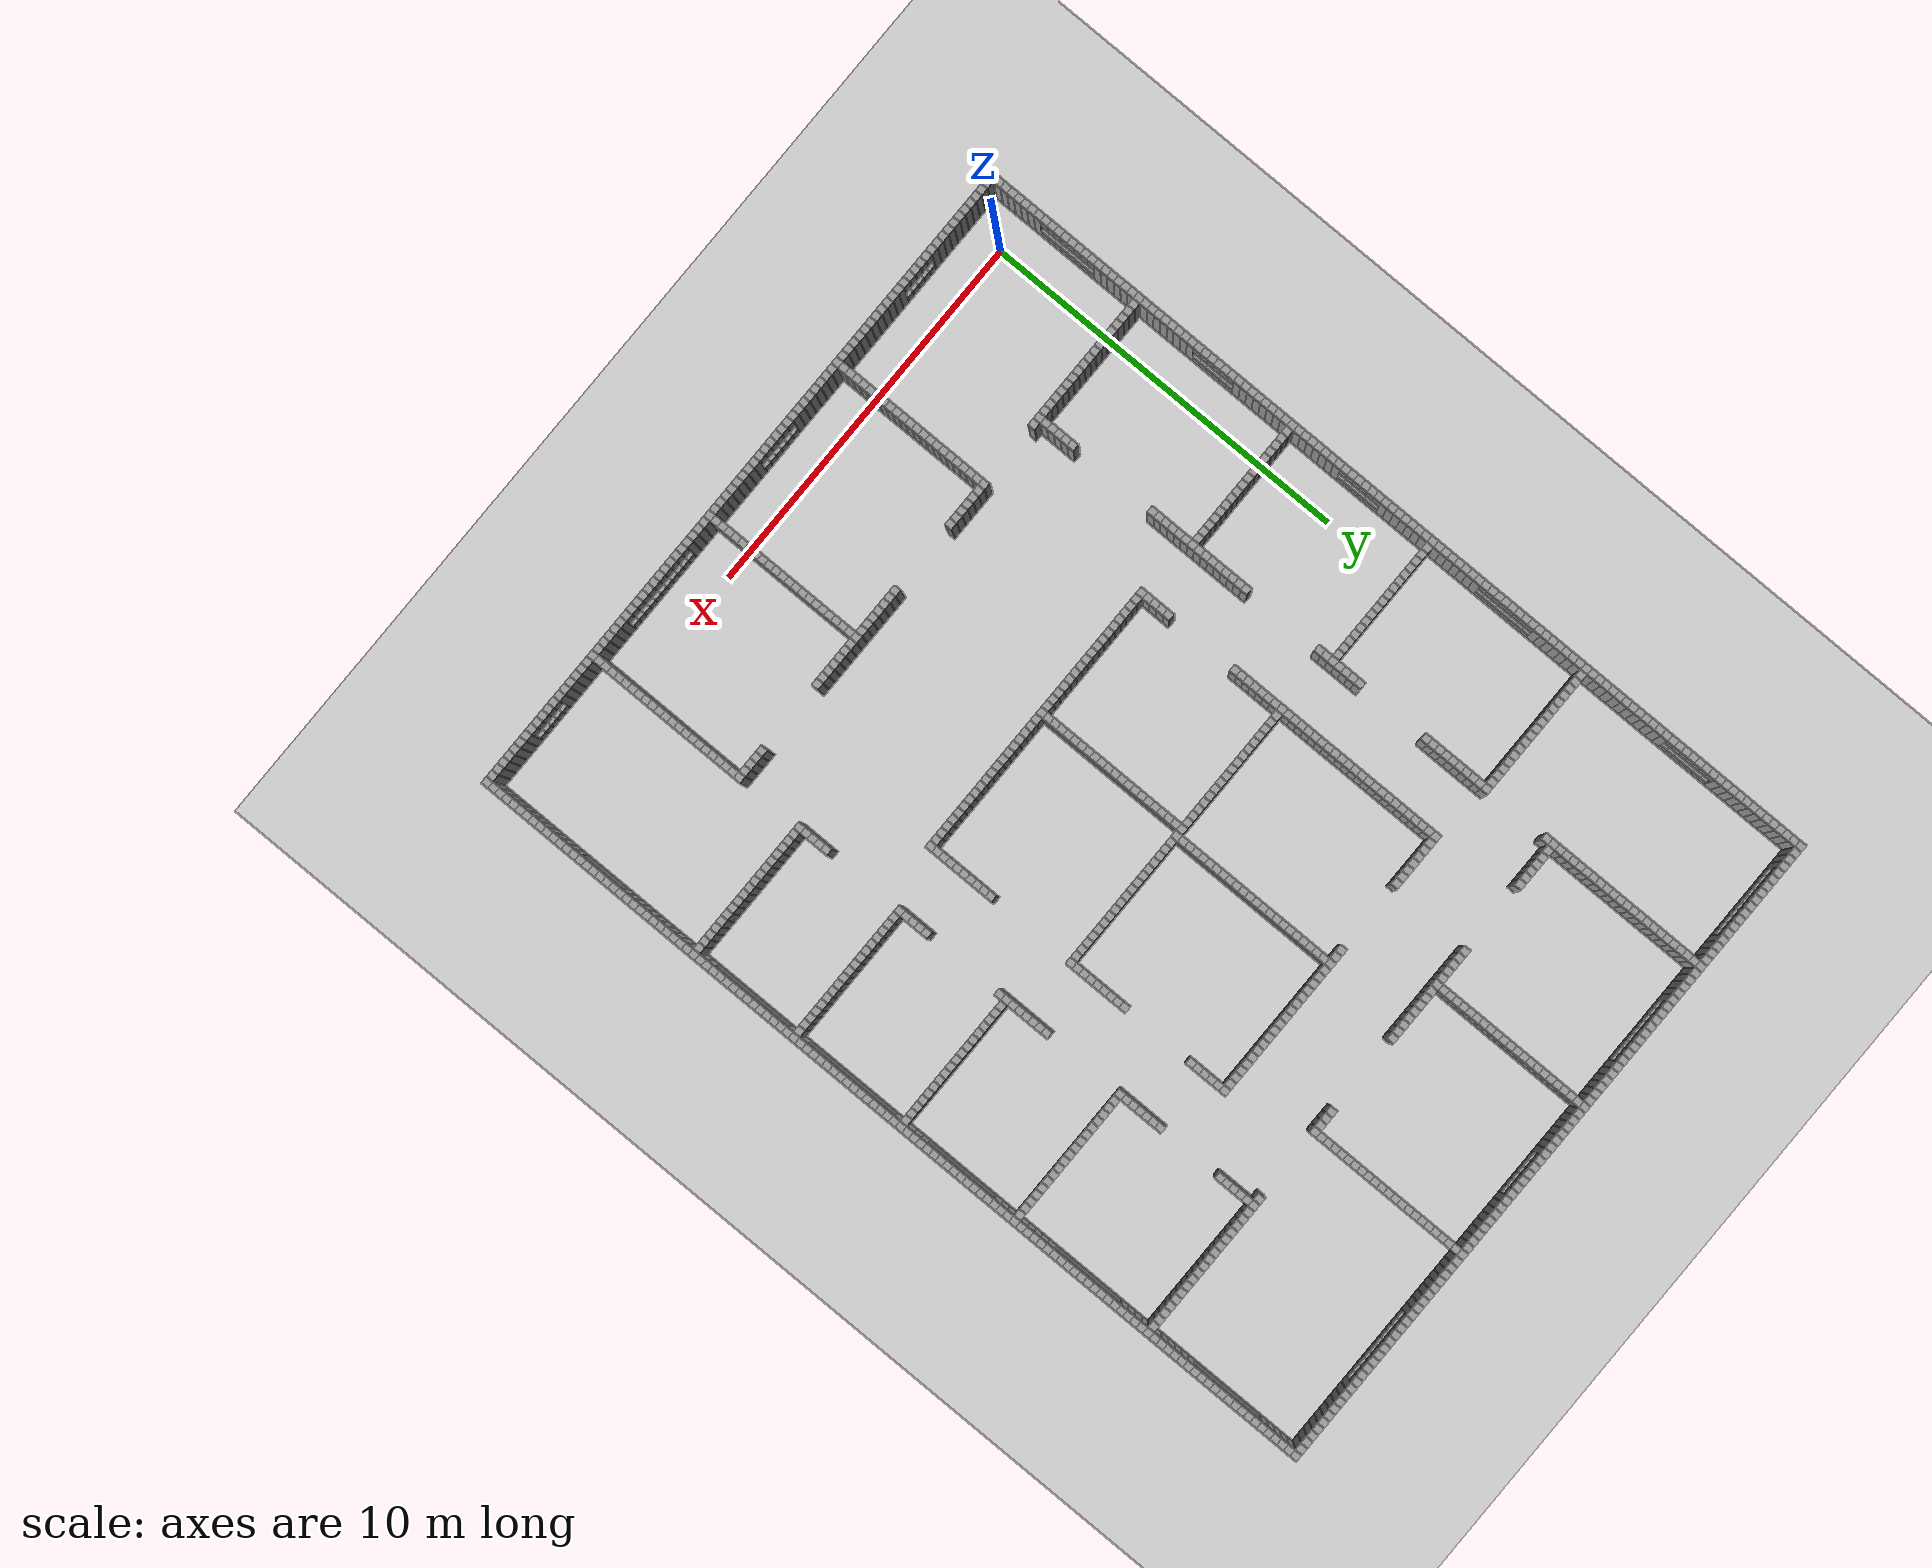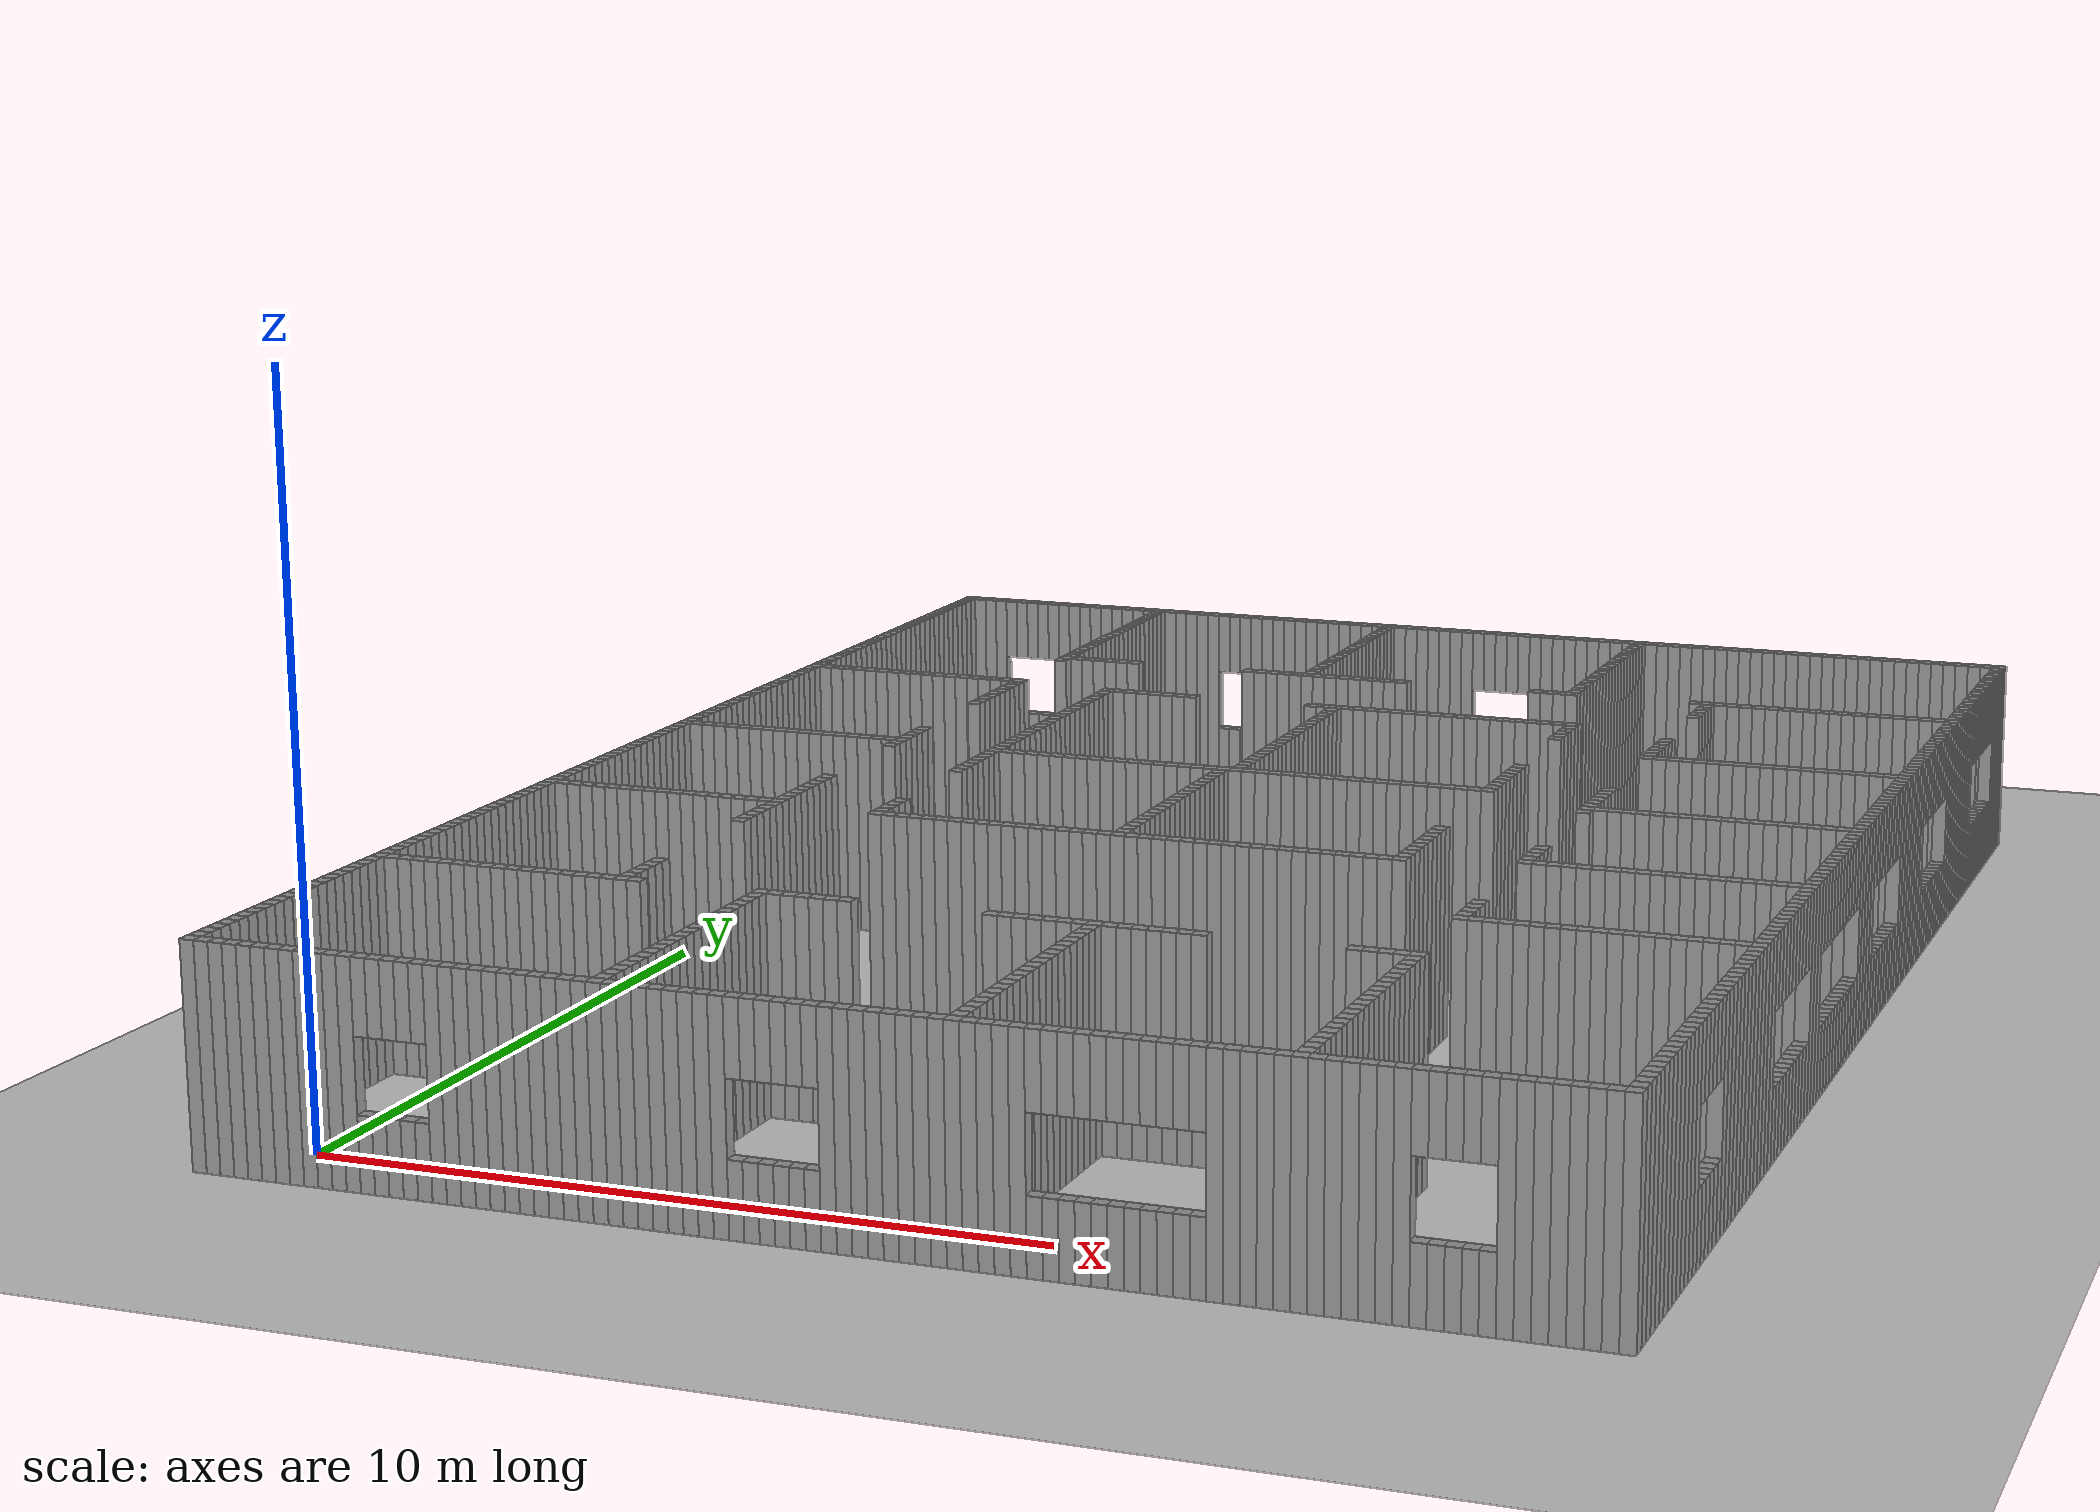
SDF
<sdf version='1.7'>
  <world name='default'>
    <light name='sun' type='directional'>
      <cast_shadows>1</cast_shadows>
      <pose>0 0 10 0 -0 0</pose>
      <diffuse>0.8 0.8 0.8 1</diffuse>
      <specular>0.2 0.2 0.2 1</specular>
      <attenuation>
        <range>1000</range>
        <constant>0.9</constant>
        <linear>0.01</linear>
        <quadratic>0.001</quadratic>
      </attenuation>
      <direction>-0.5 0.1 -0.9</direction>
      <spot>
        <inner_angle>0</inner_angle>
        <outer_angle>0</outer_angle>
        <falloff>0</falloff>
      </spot>
    </light>
    <model name='ground_plane'>
      <static>1</static>
      <link name='link'>
        <collision name='collision'>
          <geometry>
            <plane>
              <normal>0 0 1</normal>
              <size>100 100</size>
            </plane>
          </geometry>
          <surface>
            <contact>
              <collide_bitmask>65535</collide_bitmask>
              <ode/>
            </contact>
            <friction>
              <ode>
                <mu>100</mu>
                <mu2>50</mu2>
              </ode>
              <torsional>
                <ode/>
              </torsional>
            </friction>
            <bounce/>
          </surface>
          <max_contacts>10</max_contacts>
        </collision>
        <visual name='visual'>
          <cast_shadows>0</cast_shadows>
          <geometry>
            <plane>
              <normal>0 0 1</normal>
              <size>100 100</size>
            </plane>
          </geometry>
          <material>
            <script>
              <uri>file://media/materials/scripts/gazebo.material</uri>
              <name>Gazebo/Grey</name>
            </script>
          </material>
        </visual>
        <self_collide>0</self_collide>
        <enable_wind>0</enable_wind>
        <kinematic>0</kinematic>
      </link>
    </model>
    <gravity>0 0 -9.8</gravity>
    <magnetic_field>6e-06 2.3e-05 -4.2e-05</magnetic_field>
    <atmosphere type='adiabatic'/>
    <physics type='ode'>
      <max_step_size>0.001</max_step_size>
      <real_time_factor>1</real_time_factor>
      <real_time_update_rate>1000</real_time_update_rate>
    </physics>
    <scene>
      <ambient>0.4 0.4 0.4 1</ambient>
      <background>0.7 0.7 0.7 1</background>
      <shadows>1</shadows>
    </scene>
    <wind/>
    <spherical_coordinates>
      <surface_model>EARTH_WGS84</surface_model>
      <latitude_deg>0</latitude_deg>
      <longitude_deg>0</longitude_deg>
      <elevation>0</elevation>
      <heading_deg>0</heading_deg>
    </spherical_coordinates>
    <model name='05222'>
      <pose>-1 -1 0 0 -0 0</pose>
      <link name='Wall_0'>
        <collision name='Wall_0_Collision'>
          <geometry>
            <box>
              <size>0.2 0.2 3</size>
            </box>
          </geometry>
          <pose>0 0 1.5 0 -0 0</pose>
        </collision>
        <visual name='Wall_0_Visual'>
          <pose>0 0 1.5 0 -0 0</pose>
          <geometry>
            <box>
              <size>0.2 0.2 3</size>
            </box>
          </geometry>
          <material>
            <script>
              <uri>file://media/materials/scripts/gazebo.material</uri>
              <name>Gazebo/Grey</name>
            </script>
            <ambient>1 1 1 1</ambient>
          </material>
          <meta>
            <layer>0</layer>
          </meta>
        </visual>
        <pose>0.0 0.0 0 0 -0 0</pose>
      </link>
      <link name='Wall_1'>
        <collision name='Wall_1_Collision'>
          <geometry>
            <box>
              <size>0.2 0.2 3</size>
            </box>
          </geometry>
          <pose>0 0 1.5 0 -0 0</pose>
        </collision>
        <visual name='Wall_1_Visual'>
          <pose>0 0 1.5 0 -0 0</pose>
          <geometry>
            <box>
              <size>0.2 0.2 3</size>
            </box>
          </geometry>
          <material>
            <script>
              <uri>file://media/materials/scripts/gazebo.material</uri>
              <name>Gazebo/Grey</name>
            </script>
            <ambient>1 1 1 1</ambient>
          </material>
          <meta>
            <layer>0</layer>
          </meta>
        </visual>
        <pose>0.2 0.0 0 0 -0 0</pose>
      </link>
      <link name='Wall_2'>
        <collision name='Wall_2_Collision'>
          <geometry>
            <box>
              <size>0.2 0.2 3</size>
            </box>
          </geometry>
          <pose>0 0 1.5 0 -0 0</pose>
        </collision>
        <visual name='Wall_2_Visual'>
          <pose>0 0 1.5 0 -0 0</pose>
          <geometry>
            <box>
              <size>0.2 0.2 3</size>
            </box>
          </geometry>
          <material>
            <script>
              <uri>file://media/materials/scripts/gazebo.material</uri>
              <name>Gazebo/Grey</name>
            </script>
            <ambient>1 1 1 1</ambient>
          </material>
          <meta>
            <layer>0</layer>
          </meta>
        </visual>
        <pose>0.4 0.0 0 0 -0 0</pose>
      </link>
      <link name='Wall_3'>
        <collision name='Wall_3_Collision'>
          <geometry>
            <box>
              <size>0.2 0.2 3</size>
            </box>
          </geometry>
          <pose>0 0 1.5 0 -0 0</pose>
        </collision>
        <visual name='Wall_3_Visual'>
          <pose>0 0 1.5 0 -0 0</pose>
          <geometry>
            <box>
              <size>0.2 0.2 3</size>
            </box>
          </geometry>
          <material>
            <script>
              <uri>file://media/materials/scripts/gazebo.material</uri>
              <name>Gazebo/Grey</name>
            </script>
            <ambient>1 1 1 1</ambient>
          </material>
          <meta>
            <layer>0</layer>
          </meta>
        </visual>
        <pose>0.6000000000000001 0.0 0 0 -0 0</pose>
      </link>
      <link name='Wall_4'>
        <collision name='Wall_4_Collision'>
          <geometry>
            <box>
              <size>0.2 0.2 3</size>
            </box>
          </geometry>
          <pose>0 0 1.5 0 -0 0</pose>
        </collision>
        <visual name='Wall_4_Visual'>
          <pose>0 0 1.5 0 -0 0</pose>
          <geometry>
            <box>
              <size>0.2 0.2 3</size>
            </box>
          </geometry>
          <material>
            <script>
              <uri>file://media/materials/scripts/gazebo.material</uri>
              <name>Gazebo/Grey</name>
            </script>
            <ambient>1 1 1 1</ambient>
          </material>
          <meta>
            <layer>0</layer>
          </meta>
        </visual>
        <pose>0.8 0.0 0 0 -0 0</pose>
      </link>
      <link name='Wall_5'>
        <collision name='Wall_5_Collision'>
          <geometry>
            <box>
              <size>0.2 0.2 3</size>
            </box>
          </geometry>
          <pose>0 0 1.5 0 -0 0</pose>
        </collision>
        <visual name='Wall_5_Visual'>
          <pose>0 0 1.5 0 -0 0</pose>
          <geometry>
            <box>
              <size>0.2 0.2 3</size>
            </box>
          </geometry>
          <material>
            <script>
              <uri>file://media/materials/scripts/gazebo.material</uri>
              <name>Gazebo/Grey</name>
            </script>
            <ambient>1 1 1 1</ambient>
          </material>
          <meta>
            <layer>0</layer>
          </meta>
        </visual>
        <pose>1.0 0.0 0 0 -0 0</pose>
      </link>
      <link name='Wall_6'>
        <collision name='Wall_6_Collision'>
          <geometry>
            <box>
              <size>0.2 0.2 3</size>
            </box>
          </geometry>
          <pose>0 0 1.5 0 -0 0</pose>
        </collision>
        <visual name='Wall_6_Visual'>
          <pose>0 0 1.5 0 -0 0</pose>
          <geometry>
            <box>
              <size>0.2 0.2 3</size>
            </box>
          </geometry>
          <material>
            <script>
              <uri>file://media/materials/scripts/gazebo.material</uri>
              <name>Gazebo/Grey</name>
            </script>
            <ambient>1 1 1 1</ambient>
          </material>
          <meta>
            <layer>0</layer>
          </meta>
        </visual>
        <pose>1.2000000000000002 0.0 0 0 -0 0</pose>
      </link>
      <link name='Wall_7'>
        <collision name='Wall_7_Collision'>
          <geometry>
            <box>
              <size>0.2 0.2 3</size>
            </box>
          </geometry>
          <pose>0 0 1.5 0 -0 0</pose>
        </collision>
        <visual name='Wall_7_Visual'>
          <pose>0 0 1.5 0 -0 0</pose>
          <geometry>
            <box>
              <size>0.2 0.2 3</size>
            </box>
          </geometry>
          <material>
            <script>
              <uri>file://media/materials/scripts/gazebo.material</uri>
              <name>Gazebo/Grey</name>
            </script>
            <ambient>1 1 1 1</ambient>
          </material>
          <meta>
            <layer>0</layer>
          </meta>
        </visual>
        <pose>1.4000000000000001 0.0 0 0 -0 0</pose>
      </link>
      <link name='Wall_8'>
        <collision name='Wall_8_Collision'>
          <geometry>
            <box>
              <size>0.2 0.2 3</size>
            </box>
          </geometry>
          <pose>0 0 1.5 0 -0 0</pose>
        </collision>
        <visual name='Wall_8_Visual'>
          <pose>0 0 1.5 0 -0 0</pose>
          <geometry>
            <box>
              <size>0.2 0.2 3</size>
            </box>
          </geometry>
          <material>
            <script>
              <uri>file://media/materials/scripts/gazebo.material</uri>
              <name>Gazebo/Grey</name>
            </script>
            <ambient>1 1 1 1</ambient>
          </material>
          <meta>
            <layer>0</layer>
          </meta>
        </visual>
        <pose>1.6 0.0 0 0 -0 0</pose>
      </link>
      <link name='Wall_9'>
        <collision name='Wall_9_Collision'>
          <geometry>
            <box>
              <size>0.2 0.2 3</size>
            </box>
          </geometry>
          <pose>0 0 1.5 0 -0 0</pose>
        </collision>
        <visual name='Wall_9_Visual'>
          <pose>0 0 1.5 0 -0 0</pose>
          <geometry>
            <box>
              <size>0.2 0.2 3</size>
            </box>
          </geometry>
          <material>
            <script>
              <uri>file://media/materials/scripts/gazebo.material</uri>
              <name>Gazebo/Grey</name>
            </script>
            <ambient>1 1 1 1</ambient>
          </material>
          <meta>
            <layer>0</layer>
          </meta>
        </visual>
        <pose>1.8 0.0 0 0 -0 0</pose>
      </link>
      <link name='Wall_10'>
        <collision name='Wall_10_Collision'>
          <geometry>
            <box>
              <size>0.2 0.2 3</size>
            </box>
          </geometry>
          <pose>0 0 1.5 0 -0 0</pose>
        </collision>
        <visual name='Wall_10_Visual'>
          <pose>0 0 1.5 0 -0 0</pose>
          <geometry>
            <box>
              <size>0.2 0.2 3</size>
            </box>
          </geometry>
          <material>
            <script>
              <uri>file://media/materials/scripts/gazebo.material</uri>
              <name>Gazebo/Grey</name>
            </script>
            <ambient>1 1 1 1</ambient>
          </material>
          <meta>
            <layer>0</layer>
          </meta>
        </visual>
        <pose>2.0 0.0 0 0 -0 0</pose>
      </link>
      <link name='Wall_11'>
        <collision name='Wall_11_Collision'>
          <geometry>
            <box>
              <size>0.2 0.2 3</size>
            </box>
          </geometry>
          <pose>0 0 1.5 0 -0 0</pose>
        </collision>
        <visual name='Wall_11_Visual'>
          <pose>0 0 1.5 0 -0 0</pose>
          <geometry>
            <box>
              <size>0.2 0.2 3</size>
            </box>
          </geometry>
          <material>
            <script>
              <uri>file://media/materials/scripts/gazebo.material</uri>
              <name>Gazebo/Grey</name>
            </script>
            <ambient>1 1 1 1</ambient>
          </material>
          <meta>
            <layer>0</layer>
          </meta>
        </visual>
        <pose>2.2 0.0 0 0 -0 0</pose>
      </link>
      <link name='Wall_12'>
        <collision name='Wall_12_Collision'>
          <geometry>
            <box>
              <size>0.2 0.2 1.0</size>
            </box>
          </geometry>
          <pose>0 0 0.5 0 -0 0</pose>
        </collision>
        <visual name='Wall_12_Visual'>
          <pose>0 0 0.5 0 -0 0</pose>
          <geometry>
            <box>
              <size>0.2 0.2 1.0</size>
            </box>
          </geometry>
          <material>
            <script>
              <uri>file://media/materials/scripts/gazebo.material</uri>
              <name>Gazebo/Grey</name>
            </script>
            <ambient>1 1 1 1</ambient>
          </material>
          <meta>
            <layer>0</layer>
          </meta>
        </visual>
        <pose>2.4000000000000004 0.0 0 0 -0 0</pose>
      </link>
      <link name='Wall_13'>
        <collision name='Wall_13_Collision'>
          <geometry>
            <box>
              <size>0.2 0.2 1.0</size>
            </box>
          </geometry>
          <pose>0 0 2.5 0 -0 0</pose>
        </collision>
        <visual name='Wall_13_Visual'>
          <pose>0 0 2.5 0 -0 0</pose>
          <geometry>
            <box>
              <size>0.2 0.2 1.0</size>
            </box>
          </geometry>
          <material>
            <script>
              <uri>file://media/materials/scripts/gazebo.material</uri>
              <name>Gazebo/Grey</name>
            </script>
            <ambient>1 1 1 1</ambient>
          </material>
          <meta>
            <layer>0</layer>
          </meta>
        </visual>
        <pose>2.4000000000000004 0.0 0 0 -0 0</pose>
      </link>
      <link name='Window_12'>
        <collision name='Window_12_Collision'>
          <geometry>
            <box>
              <size>0.2 0.2 1.0</size>
            </box>
          </geometry>
          <pose>0 0 1.5 0 -0 0</pose>
        </collision>
        <visual name='Wall_13_Visual'>
          <pose>0 0 2.5 0 -0 0</pose>
          <geometry>
            <box>
              <size>0.2 0.2 1.0</size>
            </box>
          </geometry>
          <material>
            <script>
              <uri>file://media/materials/scripts/gazebo.material</uri>
              <name>Gazebo/Grey</name>
            </script>
            <ambient>1 1 1 1</ambient>
          </material>
          <meta>
            <layer>0</layer>
          </meta>
        </visual>
        <pose>2.4000000000000004 0.0 0 0 -0 0</pose>
      </link>
      <link name='Wall_14'>
        <collision name='Wall_14_Collision'>
          <geometry>
            <box>
              <size>0.2 0.2 1.0</size>
            </box>
          </geometry>
          <pose>0 0 0.5 0 -0 0</pose>
        </collision>
        <visual name='Wall_14_Visual'>
          <pose>0 0 0.5 0 -0 0</pose>
          <geometry>
            <box>
              <size>0.2 0.2 1.0</size>
            </box>
          </geometry>
          <material>
            <script>
              <uri>file://media/materials/scripts/gazebo.material</uri>
              <name>Gazebo/Grey</name>
            </script>
            <ambient>1 1 1 1</ambient>
          </material>
          <meta>
            <layer>0</layer>
          </meta>
        </visual>
        <pose>2.6 0.0 0 0 -0 0</pose>
      </link>
      <link name='Wall_15'>
        <collision name='Wall_15_Collision'>
          <geometry>
            <box>
              <size>0.2 0.2 1.0</size>
            </box>
          </geometry>
          <pose>0 0 2.5 0 -0 0</pose>
        </collision>
        <visual name='Wall_15_Visual'>
          <pose>0 0 2.5 0 -0 0</pose>
          <geometry>
            <box>
              <size>0.2 0.2 1.0</size>
            </box>
          </geometry>
          <material>
            <script>
              <uri>file://media/materials/scripts/gazebo.material</uri>
              <name>Gazebo/Grey</name>
            </script>
            <ambient>1 1 1 1</ambient>
          </material>
          <meta>
            <layer>0</layer>
          </meta>
        </visual>
        <pose>2.6 0.0 0 0 -0 0</pose>
      </link>
      <link name='Window_14'>
        <collision name='Window_14_Collision'>
          <geometry>
            <box>
              <size>0.2 0.2 1.0</size>
            </box>
          </geometry>
          <pose>0 0 1.5 0 -0 0</pose>
        </collision>
        <visual name='Wall_15_Visual'>
          <pose>0 0 2.5 0 -0 0</pose>
          <geometry>
            <box>
              <size>0.2 0.2 1.0</size>
            </box>
          </geometry>
          <material>
            <script>
              <uri>file://media/materials/scripts/gazebo.material</uri>
              <name>Gazebo/Grey</name>
            </script>
            <ambient>1 1 1 1</ambient>
          </material>
          <meta>
            <layer>0</layer>
          </meta>
        </visual>
        <pose>2.6 0.0 0 0 -0 0</pose>
      </link>
      <link name='Wall_16'>
        <collision name='Wall_16_Collision'>
          <geometry>
            <box>
              <size>0.2 0.2 1.0</size>
            </box>
          </geometry>
          <pose>0 0 0.5 0 -0 0</pose>
        </collision>
        <visual name='Wall_16_Visual'>
          <pose>0 0 0.5 0 -0 0</pose>
          <geometry>
            <box>
              <size>0.2 0.2 1.0</size>
            </box>
          </geometry>
          <material>
            <script>
              <uri>file://media/materials/scripts/gazebo.material</uri>
              <name>Gazebo/Grey</name>
            </script>
            <ambient>1 1 1 1</ambient>
          </material>
          <meta>
            <layer>0</layer>
          </meta>
        </visual>
        <pose>2.8000000000000003 0.0 0 0 -0 0</pose>
      </link>
      <link name='Wall_17'>
        <collision name='Wall_17_Collision'>
          <geometry>
            <box>
              <size>0.2 0.2 1.0</size>
            </box>
          </geometry>
          <pose>0 0 2.5 0 -0 0</pose>
        </collision>
        <visual name='Wall_17_Visual'>
          <pose>0 0 2.5 0 -0 0</pose>
          <geometry>
            <box>
              <size>0.2 0.2 1.0</size>
            </box>
          </geometry>
          <material>
            <script>
              <uri>file://media/materials/scripts/gazebo.material</uri>
              <name>Gazebo/Grey</name>
            </script>
            <ambient>1 1 1 1</ambient>
          </material>
          <meta>
            <layer>0</layer>
          </meta>
        </visual>
        <pose>2.8000000000000003 0.0 0 0 -0 0</pose>
      </link>
      <link name='Window_16'>
        <collision name='Window_16_Collision'>
          <geometry>
            <box>
              <size>0.2 0.2 1.0</size>
            </box>
          </geometry>
          <pose>0 0 1.5 0 -0 0</pose>
        </collision>
        <visual name='Wall_17_Visual'>
          <pose>0 0 2.5 0 -0 0</pose>
          <geometry>
            <box>
              <size>0.2 0.2 1.0</size>
            </box>
          </geometry>
          <material>
            <script>
              <uri>file://media/materials/scripts/gazebo.material</uri>
              <name>Gazebo/Grey</name>
            </script>
            <ambient>1 1 1 1</ambient>
          </material>
          <meta>
            <layer>0</layer>
          </meta>
        </visual>
        <pose>2.8000000000000003 0.0 0 0 -0 0</pose>
      </link>
      <link name='Wall_18'>
        <collision name='Wall_18_Collision'>
          <geometry>
            <box>
              <size>0.2 0.2 1.0</size>
            </box>
          </geometry>
          <pose>0 0 0.5 0 -0 0</pose>
        </collision>
        <visual name='Wall_18_Visual'>
          <pose>0 0 0.5 0 -0 0</pose>
          <geometry>
            <box>
              <size>0.2 0.2 1.0</size>
            </box>
          </geometry>
          <material>
            <script>
              <uri>file://media/materials/scripts/gazebo.material</uri>
              <name>Gazebo/Grey</name>
            </script>
            <ambient>1 1 1 1</ambient>
          </material>
          <meta>
            <layer>0</layer>
          </meta>
        </visual>
        <pose>3.0 0.0 0 0 -0 0</pose>
      </link>
      <link name='Wall_19'>
        <collision name='Wall_19_Collision'>
          <geometry>
            <box>
              <size>0.2 0.2 1.0</size>
            </box>
          </geometry>
          <pose>0 0 2.5 0 -0 0</pose>
        </collision>
        <visual name='Wall_19_Visual'>
          <pose>0 0 2.5 0 -0 0</pose>
          <geometry>
            <box>
              <size>0.2 0.2 1.0</size>
            </box>
          </geometry>
          <material>
            <script>
              <uri>file://media/materials/scripts/gazebo.material</uri>
              <name>Gazebo/Grey</name>
            </script>
            <ambient>1 1 1 1</ambient>
          </material>
          <meta>
            <layer>0</layer>
          </meta>
        </visual>
        <pose>3.0 0.0 0 0 -0 0</pose>
      </link>
      <link name='Window_18'>
        <collision name='Window_18_Collision'>
          <geometry>
            <box>
              <size>0.2 0.2 1.0</size>
            </box>
          </geometry>
          <pose>0 0 1.5 0 -0 0</pose>
        </collision>
        <visual name='Wall_19_Visual'>
          <pose>0 0 2.5 0 -0 0</pose>
          <geometry>
            <box>
              <size>0.2 0.2 1.0</size>
            </box>
          </geometry>
          <material>
            <script>
              <uri>file://media/materials/scripts/gazebo.material</uri>
              <name>Gazebo/Grey</name>
            </script>
            <ambient>1 1 1 1</ambient>
          </material>
          <meta>
            <layer>0</layer>
          </meta>
        </visual>
        <pose>3.0 0.0 0 0 -0 0</pose>
      </link>
      <link name='Wall_20'>
        <collision name='Wall_20_Collision'>
          <geometry>
            <box>
              <size>0.2 0.2 1.0</size>
            </box>
          </geometry>
          <pose>0 0 0.5 0 -0 0</pose>
        </collision>
        <visual name='Wall_20_Visual'>
          <pose>0 0 0.5 0 -0 0</pose>
          <geometry>
            <box>
              <size>0.2 0.2 1.0</size>
            </box>
          </geometry>
          <material>
            <script>
              <uri>file://media/materials/scripts/gazebo.material</uri>
              <name>Gazebo/Grey</name>
            </script>
            <ambient>1 1 1 1</ambient>
          </material>
          <meta>
            <layer>0</layer>
          </meta>
        </visual>
        <pose>3.2 0.0 0 0 -0 0</pose>
      </link>
      <link name='Wall_21'>
        <collision name='Wall_21_Collision'>
          <geometry>
            <box>
              <size>0.2 0.2 1.0</size>
            </box>
          </geometry>
          <pose>0 0 2.5 0 -0 0</pose>
        </collision>
        <visual name='Wall_21_Visual'>
          <pose>0 0 2.5 0 -0 0</pose>
          <geometry>
            <box>
              <size>0.2 0.2 1.0</size>
            </box>
          </geometry>
          <material>
            <script>
              <uri>file://media/materials/scripts/gazebo.material</uri>
              <name>Gazebo/Grey</name>
            </script>
            <ambient>1 1 1 1</ambient>
          </material>
          <meta>
            <layer>0</layer>
          </meta>
        </visual>
        <pose>3.2 0.0 0 0 -0 0</pose>
      </link>
      <link name='Window_20'>
        <collision name='Window_20_Collision'>
          <geometry>
            <box>
              <size>0.2 0.2 1.0</size>
            </box>
          </geometry>
          <pose>0 0 1.5 0 -0 0</pose>
        </collision>
        <visual name='Wall_21_Visual'>
          <pose>0 0 2.5 0 -0 0</pose>
          <geometry>
            <box>
              <size>0.2 0.2 1.0</size>
            </box>
          </geometry>
          <material>
            <script>
              <uri>file://media/materials/scripts/gazebo.material</uri>
              <name>Gazebo/Grey</name>
            </script>
            <ambient>1 1 1 1</ambient>
          </material>
          <meta>
            <layer>0</layer>
          </meta>
        </visual>
        <pose>3.2 0.0 0 0 -0 0</pose>
      </link>
      <link name='Wall_22'>
        <collision name='Wall_22_Collision'>
          <geometry>
            <box>
              <size>0.2 0.2 3</size>
            </box>
          </geometry>
          <pose>0 0 1.5 0 -0 0</pose>
        </collision>
        <visual name='Wall_22_Visual'>
          <pose>0 0 1.5 0 -0 0</pose>
          <geometry>
            <box>
              <size>0.2 0.2 3</size>
            </box>
          </geometry>
          <material>
            <script>
              <uri>file://media/materials/scripts/gazebo.material</uri>
              <name>Gazebo/Grey</name>
            </script>
            <ambient>1 1 1 1</ambient>
          </material>
          <meta>
            <layer>0</layer>
          </meta>
        </visual>
        <pose>3.4000000000000004 0.0 0 0 -0 0</pose>
      </link>
      <link name='Wall_23'>
        <collision name='Wall_23_Collision'>
          <geometry>
            <box>
              <size>0.2 0.2 3</size>
            </box>
          </geometry>
          <pose>0 0 1.5 0 -0 0</pose>
        </collision>
        <visual name='Wall_23_Visual'>
          <pose>0 0 1.5 0 -0 0</pose>
          <geometry>
            <box>
              <size>0.2 0.2 3</size>
            </box>
          </geometry>
          <material>
            <script>
              <uri>file://media/materials/scripts/gazebo.material</uri>
              <name>Gazebo/Grey</name>
            </script>
            <ambient>1 1 1 1</ambient>
          </material>
          <meta>
            <layer>0</layer>
          </meta>
        </visual>
        <pose>3.6 0.0 0 0 -0 0</pose>
      </link>
      <link name='Wall_24'>
        <collision name='Wall_24_Collision'>
          <geometry>
            <box>
              <size>0.2 0.2 3</size>
            </box>
          </geometry>
          <pose>0 0 1.5 0 -0 0</pose>
        </collision>
        <visual name='Wall_24_Visual'>
          <pose>0 0 1.5 0 -0 0</pose>
          <geometry>
            <box>
              <size>0.2 0.2 3</size>
            </box>
          </geometry>
          <material>
            <script>
              <uri>file://media/materials/scripts/gazebo.material</uri>
              <name>Gazebo/Grey</name>
            </script>
            <ambient>1 1 1 1</ambient>
          </material>
          <meta>
            <layer>0</layer>
          </meta>
        </visual>
        <pose>3.8000000000000003 0.0 0 0 -0 0</pose>
      </link>
      <link name='Wall_25'>
        <collision name='Wall_25_Collision'>
          <geometry>
            <box>
              <size>0.2 0.2 3</size>
            </box>
          </geometry>
          <pose>0 0 1.5 0 -0 0</pose>
        </collision>
        <visual name='Wall_25_Visual'>
          <pose>0 0 1.5 0 -0 0</pose>
          <geometry>
            <box>
              <size>0.2 0.2 3</size>
            </box>
          </geometry>
          <material>
            <script>
              <uri>file://media/materials/scripts/gazebo.material</uri>
              <name>Gazebo/Grey</name>
            </script>
            <ambient>1 1 1 1</ambient>
          </material>
          <meta>
            <layer>0</layer>
          </meta>
        </visual>
        <pose>4.0 0.0 0 0 -0 0</pose>
      </link>
      <link name='Wall_26'>
        <collision name='Wall_26_Collision'>
          <geometry>
            <box>
              <size>0.2 0.2 3</size>
            </box>
          </geometry>
          <pose>0 0 1.5 0 -0 0</pose>
        </collision>
        <visual name='Wall_26_Visual'>
          <pose>0 0 1.5 0 -0 0</pose>
          <geometry>
            <box>
              <size>0.2 0.2 3</size>
            </box>
          </geometry>
          <material>
            <script>
              <uri>file://media/materials/scripts/gazebo.material</uri>
              <name>Gazebo/Grey</name>
            </script>
            <ambient>1 1 1 1</ambient>
          </material>
          <meta>
            <layer>0</layer>
          </meta>
        </visual>
        <pose>4.2 0.0 0 0 -0 0</pose>
      </link>
      <link name='Wall_27'>
        <collision name='Wall_27_Collision'>
          <geometry>
            <box>
              <size>0.2 0.2 3</size>
            </box>
          </geometry>
          <pose>0 0 1.5 0 -0 0</pose>
        </collision>
        <visual name='Wall_27_Visual'>
          <pose>0 0 1.5 0 -0 0</pose>
          <geometry>
            <box>
              <size>0.2 0.2 3</size>
            </box>
          </geometry>
          <material>
            <script>
              <uri>file://media/materials/scripts/gazebo.material</uri>
              <name>Gazebo/Grey</name>
            </script>
            <ambient>1 1 1 1</ambient>
          </material>
          <meta>
            <layer>0</layer>
          </meta>
        </visual>
        <pose>4.4 0.0 0 0 -0 0</pose>
      </link>
      <link name='Wall_28'>
        <collision name='Wall_28_Collision'>
          <geometry>
            <box>
              <size>0.2 0.2 3</size>
            </box>
          </geometry>
          <pose>0 0 1.5 0 -0 0</pose>
        </collision>
        <visual name='Wall_28_Visual'>
          <pose>0 0 1.5 0 -0 0</pose>
          <geometry>
            <box>
              <size>0.2 0.2 3</size>
            </box>
          </geometry>
          <material>
            <script>
              <uri>file://media/materials/scripts/gazebo.material</uri>
              <name>Gazebo/Grey</name>
            </script>
            <ambient>1 1 1 1</ambient>
          </material>
          <meta>
            <layer>0</layer>
          </meta>
        </visual>
        <pose>4.6000000000000005 0.0 0 0 -0 0</pose>
      </link>
      <link name='Wall_29'>
        <collision name='Wall_29_Collision'>
          <geometry>
            <box>
              <size>0.2 0.2 3</size>
            </box>
          </geometry>
          <pose>0 0 1.5 0 -0 0</pose>
        </collision>
        <visual name='Wall_29_Visual'>
          <pose>0 0 1.5 0 -0 0</pose>
          <geometry>
            <box>
              <size>0.2 0.2 3</size>
            </box>
          </geometry>
          <material>
            <script>
              <uri>file://media/materials/scripts/gazebo.material</uri>
              <name>Gazebo/Grey</name>
            </script>
            <ambient>1 1 1 1</ambient>
          </material>
          <meta>
            <layer>0</layer>
          </meta>
        </visual>
        <pose>4.800000000000001 0.0 0 0 -0 0</pose>
      </link>
      <link name='Wall_30'>
        <collision name='Wall_30_Collision'>
          <geometry>
            <box>
              <size>0.2 0.2 3</size>
            </box>
          </geometry>
          <pose>0 0 1.5 0 -0 0</pose>
        </collision>
        <visual name='Wall_30_Visual'>
          <pose>0 0 1.5 0 -0 0</pose>
          <geometry>
            <box>
              <size>0.2 0.2 3</size>
            </box>
          </geometry>
          <material>
            <script>
              <uri>file://media/materials/scripts/gazebo.material</uri>
              <name>Gazebo/Grey</name>
            </script>
            <ambient>1 1 1 1</ambient>
          </material>
          <meta>
            <layer>0</layer>
          </meta>
        </visual>
        <pose>5.0 0.0 0 0 -0 0</pose>
      </link>
      <link name='Wall_31'>
        <collision name='Wall_31_Collision'>
          <geometry>
            <box>
              <size>0.2 0.2 3</size>
            </box>
          </geometry>
          <pose>0 0 1.5 0 -0 0</pose>
        </collision>
        <visual name='Wall_31_Visual'>
          <pose>0 0 1.5 0 -0 0</pose>
          <geometry>
            <box>
              <size>0.2 0.2 3</size>
            </box>
          </geometry>
          <material>
            <script>
              <uri>file://media/materials/scripts/gazebo.material</uri>
              <name>Gazebo/Grey</name>
            </script>
            <ambient>1 1 1 1</ambient>
          </material>
          <meta>
            <layer>0</layer>
          </meta>
        </visual>
        <pose>5.2 0.0 0 0 -0 0</pose>
      </link>
      <link name='Wall_32'>
        <collision name='Wall_32_Collision'>
          <geometry>
            <box>
              <size>0.2 0.2 3</size>
            </box>
          </geometry>
          <pose>0 0 1.5 0 -0 0</pose>
        </collision>
        <visual name='Wall_32_Visual'>
          <pose>0 0 1.5 0 -0 0</pose>
          <geometry>
            <box>
              <size>0.2 0.2 3</size>
            </box>
          </geometry>
          <material>
            <script>
              <uri>file://media/materials/scripts/gazebo.material</uri>
              <name>Gazebo/Grey</name>
            </script>
            <ambient>1 1 1 1</ambient>
          </material>
          <meta>
            <layer>0</layer>
          </meta>
        </visual>
        <pose>5.4 0.0 0 0 -0 0</pose>
      </link>
      <link name='Wall_33'>
        <collision name='Wall_33_Collision'>
          <geometry>
            <box>
              <size>0.2 0.2 3</size>
            </box>
          </geometry>
          <pose>0 0 1.5 0 -0 0</pose>
        </collision>
        <visual name='Wall_33_Visual'>
          <pose>0 0 1.5 0 -0 0</pose>
          <geometry>
            <box>
              <size>0.2 0.2 3</size>
            </box>
          </geometry>
          <material>
            <script>
              <uri>file://media/materials/scripts/gazebo.material</uri>
              <name>Gazebo/Grey</name>
            </script>
            <ambient>1 1 1 1</ambient>
          </material>
          <meta>
            <layer>0</layer>
          </meta>
        </visual>
        <pose>5.6000000000000005 0.0 0 0 -0 0</pose>
      </link>
      <link name='Wall_34'>
        <collision name='Wall_34_Collision'>
          <geometry>
            <box>
              <size>0.2 0.2 3</size>
            </box>
          </geometry>
          <pose>0 0 1.5 0 -0 0</pose>
        </collision>
        <visual name='Wall_34_Visual'>
          <pose>0 0 1.5 0 -0 0</pose>
          <geometry>
            <box>
              <size>0.2 0.2 3</size>
            </box>
          </geometry>
          <material>
            <script>
              <uri>file://media/materials/scripts/gazebo.material</uri>
              <name>Gazebo/Grey</name>
            </script>
            <ambient>1 1 1 1</ambient>
          </material>
          <meta>
            <layer>0</layer>
          </meta>
        </visual>
        <pose>5.800000000000001 0.0 0 0 -0 0</pose>
      </link>
      <link name='Wall_35'>
        <collision name='Wall_35_Collision'>
          <geometry>
            <box>
              <size>0.2 0.2 3</size>
            </box>
          </geometry>
          <pose>0 0 1.5 0 -0 0</pose>
        </collision>
        <visual name='Wall_35_Visual'>
          <pose>0 0 1.5 0 -0 0</pose>
          <geometry>
            <box>
              <size>0.2 0.2 3</size>
            </box>
          </geometry>
          <material>
            <script>
              <uri>file://media/materials/scripts/gazebo.material</uri>
              <name>Gazebo/Grey</name>
            </script>
            <ambient>1 1 1 1</ambient>
          </material>
          <meta>
            <layer>0</layer>
          </meta>
        </visual>
        <pose>6.0 0.0 0 0 -0 0</pose>
      </link>
      <link name='Wall_36'>
        <collision name='Wall_36_Collision'>
          <geometry>
            <box>
              <size>0.2 0.2 3</size>
            </box>
          </geometry>
          <pose>0 0 1.5 0 -0 0</pose>
        </collision>
        <visual name='Wall_36_Visual'>
          <pose>0 0 1.5 0 -0 0</pose>
          <geometry>
            <box>
              <size>0.2 0.2 3</size>
            </box>
          </geometry>
          <material>
            <script>
              <uri>file://media/materials/scripts/gazebo.material</uri>
              <name>Gazebo/Grey</name>
            </script>
            <ambient>1 1 1 1</ambient>
          </material>
          <meta>
            <layer>0</layer>
          </meta>
        </visual>
        <pose>6.2 0.0 0 0 -0 0</pose>
      </link>
      <link name='Wall_37'>
        <collision name='Wall_37_Collision'>
          <geometry>
            <box>
              <size>0.2 0.2 3</size>
            </box>
          </geometry>
          <pose>0 0 1.5 0 -0 0</pose>
        </collision>
        <visual name='Wall_37_Visual'>
          <pose>0 0 1.5 0 -0 0</pose>
          <geometry>
            <box>
              <size>0.2 0.2 3</size>
            </box>
          </geometry>
          <material>
            <script>
              <uri>file://media/materials/scripts/gazebo.material</uri>
              <name>Gazebo/Grey</name>
            </script>
            <ambient>1 1 1 1</ambient>
          </material>
          <meta>
            <layer>0</layer>
          </meta>
        </visual>
        <pose>6.4 0.0 0 0 -0 0</pose>
      </link>
      <link name='Wall_38'>
        <collision name='Wall_38_Collision'>
          <geometry>
            <box>
              <size>0.2 0.2 3</size>
            </box>
          </geometry>
          <pose>0 0 1.5 0 -0 0</pose>
        </collision>
        <visual name='Wall_38_Visual'>
          <pose>0 0 1.5 0 -0 0</pose>
          <geometry>
            <box>
              <size>0.2 0.2 3</size>
            </box>
          </geometry>
          <material>
            <script>
              <uri>file://media/materials/scripts/gazebo.material</uri>
              <name>Gazebo/Grey</name>
            </script>
            <ambient>1 1 1 1</ambient>
          </material>
          <meta>
            <layer>0</layer>
          </meta>
        </visual>
        <pose>6.6000000000000005 0.0 0 0 -0 0</pose>
      </link>
      <link name='Wall_39'>
        <collision name='Wall_39_Collision'>
          <geometry>
            <box>
              <size>0.2 0.2 3</size>
            </box>
          </geometry>
          <pose>0 0 1.5 0 -0 0</pose>
        </collision>
        <visual name='Wall_39_Visual'>
          <pose>0 0 1.5 0 -0 0</pose>
          <geometry>
            <box>
              <size>0.2 0.2 3</size>
            </box>
          </geometry>
          <material>
            <script>
              <uri>file://media/materials/scripts/gazebo.material</uri>
              <name>Gazebo/Grey</name>
            </script>
            <ambient>1 1 1 1</ambient>
          </material>
          <meta>
            <layer>0</layer>
          </meta>
        </visual>
        <pose>6.800000000000001 0.0 0 0 -0 0</pose>
      </link>
      <link name='Wall_40'>
        <collision name='Wall_40_Collision'>
          <geometry>
            <box>
              <size>0.2 0.2 3</size>
            </box>
          </geometry>
          <pose>0 0 1.5 0 -0 0</pose>
        </collision>
        <visual name='Wall_40_Visual'>
          <pose>0 0 1.5 0 -0 0</pose>
          <geometry>
            <box>
              <size>0.2 0.2 3</size>
            </box>
          </geometry>
          <material>
            <script>
              <uri>file://media/materials/scripts/gazebo.material</uri>
              <name>Gazebo/Grey</name>
            </script>
            <ambient>1 1 1 1</ambient>
          </material>
          <meta>
            <layer>0</layer>
          </meta>
        </visual>
        <pose>7.0 0.0 0 0 -0 0</pose>
      </link>
      <link name='Wall_41'>
        <collision name='Wall_41_Collision'>
          <geometry>
            <box>
              <size>0.2 0.2 3</size>
            </box>
          </geometry>
          <pose>0 0 1.5 0 -0 0</pose>
        </collision>
        <visual name='Wall_41_Visual'>
          <pose>0 0 1.5 0 -0 0</pose>
          <geometry>
            <box>
              <size>0.2 0.2 3</size>
            </box>
          </geometry>
          <material>
            <script>
              <uri>file://media/materials/scripts/gazebo.material</uri>
              <name>Gazebo/Grey</name>
            </script>
            <ambient>1 1 1 1</ambient>
          </material>
          <meta>
            <layer>0</layer>
          </meta>
        </visual>
        <pose>7.2 0.0 0 0 -0 0</pose>
      </link>
      <link name='Wall_42'>
        <collision name='Wall_42_Collision'>
          <geometry>
            <box>
              <size>0.2 0.2 1.0</size>
            </box>
          </geometry>
          <pose>0 0 0.5 0 -0 0</pose>
        </collision>
        <visual name='Wall_42_Visual'>
          <pose>0 0 0.5 0 -0 0</pose>
          <geometry>
            <box>
              <size>0.2 0.2 1.0</size>
            </box>
          </geometry>
          <material>
            <script>
              <uri>file://media/materials/scripts/gazebo.material</uri>
              <name>Gazebo/Grey</name>
            </script>
            <ambient>1 1 1 1</ambient>
          </material>
          <meta>
            <layer>0</layer>
          </meta>
        </visual>
        <pose>7.4 0.0 0 0 -0 0</pose>
      </link>
      <link name='Wall_43'>
        <collision name='Wall_43_Collision'>
          <geometry>
            <box>
              <size>0.2 0.2 1.0</size>
            </box>
          </geometry>
          <pose>0 0 2.5 0 -0 0</pose>
        </collision>
        <visual name='Wall_43_Visual'>
          <pose>0 0 2.5 0 -0 0</pose>
          <geometry>
            <box>
              <size>0.2 0.2 1.0</size>
            </box>
          </geometry>
          <material>
            <script>
              <uri>file://media/materials/scripts/gazebo.material</uri>
              <name>Gazebo/Grey</name>
            </script>
            <ambient>1 1 1 1</ambient>
          </material>
          <meta>
            <layer>0</layer>
          </meta>
        </visual>
        <pose>7.4 0.0 0 0 -0 0</pose>
      </link>
      <link name='Window_42'>
        <collision name='Window_42_Collision'>
          <geometry>
            <box>
              <size>0.2 0.2 1.0</size>
            </box>
          </geometry>
          <pose>0 0 1.5 0 -0 0</pose>
        </collision>
        <visual name='Wall_43_Visual'>
          <pose>0 0 2.5 0 -0 0</pose>
          <geometry>
            <box>
              <size>0.2 0.2 1.0</size>
            </box>
          </geometry>
          <material>
            <script>
              <uri>file://media/materials/scripts/gazebo.material</uri>
              <name>Gazebo/Grey</name>
            </script>
            <ambient>1 1 1 1</ambient>
          </material>
          <meta>
            <layer>0</layer>
          </meta>
        </visual>
        <pose>7.4 0.0 0 0 -0 0</pose>
      </link>
      <link name='Wall_44'>
        <collision name='Wall_44_Collision'>
          <geometry>
            <box>
              <size>0.2 0.2 1.0</size>
            </box>
          </geometry>
          <pose>0 0 0.5 0 -0 0</pose>
        </collision>
        <visual name='Wall_44_Visual'>
          <pose>0 0 0.5 0 -0 0</pose>
          <geometry>
            <box>
              <size>0.2 0.2 1.0</size>
            </box>
          </geometry>
          <material>
            <script>
              <uri>file://media/materials/scripts/gazebo.material</uri>
              <name>Gazebo/Grey</name>
            </script>
            <ambient>1 1 1 1</ambient>
          </material>
          <meta>
            <layer>0</layer>
          </meta>
        </visual>
        <pose>7.6000000000000005 0.0 0 0 -0 0</pose>
      </link>
      <link name='Wall_45'>
        <collision name='Wall_45_Collision'>
          <geometry>
            <box>
              <size>0.2 0.2 1.0</size>
            </box>
          </geometry>
          <pose>0 0 2.5 0 -0 0</pose>
        </collision>
        <visual name='Wall_45_Visual'>
          <pose>0 0 2.5 0 -0 0</pose>
          <geometry>
            <box>
              <size>0.2 0.2 1.0</size>
            </box>
          </geometry>
          <material>
            <script>
              <uri>file://media/materials/scripts/gazebo.material</uri>
              <name>Gazebo/Grey</name>
            </script>
            <ambient>1 1 1 1</ambient>
          </material>
          <meta>
            <layer>0</layer>
          </meta>
        </visual>
        <pose>7.6000000000000005 0.0 0 0 -0 0</pose>
      </link>
      <link name='Window_44'>
        <collision name='Window_44_Collision'>
          <geometry>
            <box>
              <size>0.2 0.2 1.0</size>
            </box>
          </geometry>
          <pose>0 0 1.5 0 -0 0</pose>
        </collision>
        <visual name='Wall_45_Visual'>
          <pose>0 0 2.5 0 -0 0</pose>
          <geometry>
            <box>
              <size>0.2 0.2 1.0</size>
            </box>
          </geometry>
          <material>
            <script>
              <uri>file://media/materials/scripts/gazebo.material</uri>
              <name>Gazebo/Grey</name>
            </script>
            <ambient>1 1 1 1</ambient>
          </material>
          <meta>
            <layer>0</layer>
          </meta>
        </visual>
        <pose>7.6000000000000005 0.0 0 0 -0 0</pose>
      </link>
      <link name='Wall_46'>
        <collision name='Wall_46_Collision'>
          <geometry>
            <box>
              <size>0.2 0.2 1.0</size>
            </box>
          </geometry>
          <pose>0 0 0.5 0 -0 0</pose>
        </collision>
        <visual name='Wall_46_Visual'>
          <pose>0 0 0.5 0 -0 0</pose>
          <geometry>
            <box>
              <size>0.2 0.2 1.0</size>
            </box>
          </geometry>
          <material>
            <script>
              <uri>file://media/materials/scripts/gazebo.material</uri>
              <name>Gazebo/Grey</name>
            </script>
            <ambient>1 1 1 1</ambient>
          </material>
          <meta>
            <layer>0</layer>
          </meta>
        </visual>
        <pose>7.800000000000001 0.0 0 0 -0 0</pose>
      </link>
      <link name='Wall_47'>
        <collision name='Wall_47_Collision'>
          <geometry>
            <box>
              <size>0.2 0.2 1.0</size>
            </box>
          </geometry>
          <pose>0 0 2.5 0 -0 0</pose>
        </collision>
        <visual name='Wall_47_Visual'>
          <pose>0 0 2.5 0 -0 0</pose>
          <geometry>
            <box>
              <size>0.2 0.2 1.0</size>
            </box>
          </geometry>
          <material>
            <script>
              <uri>file://media/materials/scripts/gazebo.material</uri>
              <name>Gazebo/Grey</name>
            </script>
            <ambient>1 1 1 1</ambient>
          </material>
          <meta>
            <layer>0</layer>
          </meta>
        </visual>
        <pose>7.800000000000001 0.0 0 0 -0 0</pose>
      </link>
      <link name='Window_46'>
        <collision name='Window_46_Collision'>
          <geometry>
            <box>
              <size>0.2 0.2 1.0</size>
            </box>
          </geometry>
          <pose>0 0 1.5 0 -0 0</pose>
        </collision>
        <visual name='Wall_47_Visual'>
          <pose>0 0 2.5 0 -0 0</pose>
          <geometry>
            <box>
              <size>0.2 0.2 1.0</size>
            </box>
          </geometry>
          <material>
            <script>
              <uri>file://media/materials/scripts/gazebo.material</uri>
              <name>Gazebo/Grey</name>
            </script>
            <ambient>1 1 1 1</ambient>
          </material>
          <meta>
            <layer>0</layer>
          </meta>
        </visual>
        <pose>7.800000000000001 0.0 0 0 -0 0</pose>
      </link>
      <link name='Wall_48'>
        <collision name='Wall_48_Collision'>
          <geometry>
            <box>
              <size>0.2 0.2 1.0</size>
            </box>
          </geometry>
          <pose>0 0 0.5 0 -0 0</pose>
        </collision>
        <visual name='Wall_48_Visual'>
          <pose>0 0 0.5 0 -0 0</pose>
          <geometry>
            <box>
              <size>0.2 0.2 1.0</size>
            </box>
          </geometry>
          <material>
            <script>
              <uri>file://media/materials/scripts/gazebo.material</uri>
              <name>Gazebo/Grey</name>
            </script>
            <ambient>1 1 1 1</ambient>
          </material>
          <meta>
            <layer>0</layer>
          </meta>
        </visual>
        <pose>8.0 0.0 0 0 -0 0</pose>
      </link>
      <link name='Wall_49'>
        <collision name='Wall_49_Collision'>
          <geometry>
            <box>
              <size>0.2 0.2 1.0</size>
            </box>
          </geometry>
          <pose>0 0 2.5 0 -0 0</pose>
        </collision>
        <visual name='Wall_49_Visual'>
          <pose>0 0 2.5 0 -0 0</pose>
          <geometry>
            <box>
              <size>0.2 0.2 1.0</size>
            </box>
          </geometry>
          <material>
            <script>
              <uri>file://media/materials/scripts/gazebo.material</uri>
              <name>Gazebo/Grey</name>
            </script>
            <ambient>1 1 1 1</ambient>
          </material>
          <meta>
            <layer>0</layer>
          </meta>
        </visual>
        <pose>8.0 0.0 0 0 -0 0</pose>
      </link>
      <link name='Window_48'>
        <collision name='Window_48_Collision'>
          <geometry>
            <box>
              <size>0.2 0.2 1.0</size>
            </box>
          </geometry>
          <pose>0 0 1.5 0 -0 0</pose>
        </collision>
        <visual name='Wall_49_Visual'>
          <pose>0 0 2.5 0 -0 0</pose>
          <geometry>
            <box>
              <size>0.2 0.2 1.0</size>
            </box>
          </geometry>
          <material>
            <script>
              <uri>file://media/materials/scripts/gazebo.material</uri>
              <name>Gazebo/Grey</name>
            </script>
            <ambient>1 1 1 1</ambient>
          </material>
          <meta>
            <layer>0</layer>
          </meta>
        </visual>
        <pose>8.0 0.0 0 0 -0 0</pose>
      </link>
      <link name='Wall_50'>
        <collision name='Wall_50_Collision'>
          <geometry>
            <box>
              <size>0.2 0.2 1.0</size>
            </box>
          </geometry>
          <pose>0 0 0.5 0 -0 0</pose>
        </collision>
        <visual name='Wall_50_Visual'>
          <pose>0 0 0.5 0 -0 0</pose>
          <geometry>
            <box>
              <size>0.2 0.2 1.0</size>
            </box>
          </geometry>
          <material>
            <script>
              <uri>file://media/materials/scripts/gazebo.material</uri>
              <name>Gazebo/Grey</name>
            </script>
            <ambient>1 1 1 1</ambient>
          </material>
          <meta>
            <layer>0</layer>
          </meta>
        </visual>
        <pose>8.200000000000001 0.0 0 0 -0 0</pose>
      </link>
      <link name='Wall_51'>
        <collision name='Wall_51_Collision'>
          <geometry>
            <box>
              <size>0.2 0.2 1.0</size>
            </box>
          </geometry>
          <pose>0 0 2.5 0 -0 0</pose>
        </collision>
        <visual name='Wall_51_Visual'>
          <pose>0 0 2.5 0 -0 0</pose>
          <geometry>
            <box>
              <size>0.2 0.2 1.0</size>
            </box>
          </geometry>
          <material>
            <script>
              <uri>file://media/materials/scripts/gazebo.material</uri>
              <name>Gazebo/Grey</name>
            </script>
            <ambient>1 1 1 1</ambient>
          </material>
          <meta>
            <layer>0</layer>
          </meta>
        </visual>
        <pose>8.200000000000001 0.0 0 0 -0 0</pose>
      </link>
      <link name='Window_50'>
        <collision name='Window_50_Collision'>
          <geometry>
            <box>
              <size>0.2 0.2 1.0</size>
            </box>
          </geometry>
          <pose>0 0 1.5 0 -0 0</pose>
        </collision>
        <visual name='Wall_51_Visual'>
          <pose>0 0 2.5 0 -0 0</pose>
          <geometry>
            <box>
              <size>0.2 0.2 1.0</size>
            </box>
          </geometry>
          <material>
            <script>
              <uri>file://media/materials/scripts/gazebo.material</uri>
              <name>Gazebo/Grey</name>
            </script>
            <ambient>1 1 1 1</ambient>
          </material>
          <meta>
            <layer>0</layer>
          </meta>
        </visual>
        <pose>8.200000000000001 0.0 0 0 -0 0</pose>
      </link>
      <link name='Wall_52'>
        <collision name='Wall_52_Collision'>
          <geometry>
            <box>
              <size>0.2 0.2 1.0</size>
            </box>
          </geometry>
          <pose>0 0 0.5 0 -0 0</pose>
        </collision>
        <visual name='Wall_52_Visual'>
          <pose>0 0 0.5 0 -0 0</pose>
          <geometry>
            <box>
              <size>0.2 0.2 1.0</size>
            </box>
          </geometry>
          <material>
            <script>
              <uri>file://media/materials/scripts/gazebo.material</uri>
              <name>Gazebo/Grey</name>
            </script>
            <ambient>1 1 1 1</ambient>
          </material>
          <meta>
            <layer>0</layer>
          </meta>
        </visual>
        <pose>8.4 0.0 0 0 -0 0</pose>
      </link>
      <link name='Wall_53'>
        <collision name='Wall_53_Collision'>
          <geometry>
            <box>
              <size>0.2 0.2 1.0</size>
            </box>
          </geometry>
          <pose>0 0 2.5 0 -0 0</pose>
        </collision>
        <visual name='Wall_53_Visual'>
          <pose>0 0 2.5 0 -0 0</pose>
          <geometry>
            <box>
              <size>0.2 0.2 1.0</size>
            </box>
          </geometry>
          <material>
            <script>
              <uri>file://media/materials/scripts/gazebo.material</uri>
              <name>Gazebo/Grey</name>
            </script>
            <ambient>1 1 1 1</ambient>
          </material>
          <meta>
            <layer>0</layer>
          </meta>
        </visual>
        <pose>8.4 0.0 0 0 -0 0</pose>
      </link>
      <link name='Window_52'>
        <collision name='Window_52_Collision'>
          <geometry>
            <box>
              <size>0.2 0.2 1.0</size>
            </box>
          </geometry>
          <pose>0 0 1.5 0 -0 0</pose>
        </collision>
        <visual name='Wall_53_Visual'>
          <pose>0 0 2.5 0 -0 0</pose>
          <geometry>
            <box>
              <size>0.2 0.2 1.0</size>
            </box>
          </geometry>
          <material>
            <script>
              <uri>file://media/materials/scripts/gazebo.material</uri>
              <name>Gazebo/Grey</name>
            </script>
            <ambient>1 1 1 1</ambient>
          </material>
          <meta>
            <layer>0</layer>
          </meta>
        </visual>
        <pose>8.4 0.0 0 0 -0 0</pose>
      </link>
      <link name='Wall_54'>
        <collision name='Wall_54_Collision'>
          <geometry>
            <box>
              <size>0.2 0.2 3</size>
            </box>
          </geometry>
          <pose>0 0 1.5 0 -0 0</pose>
        </collision>
        <visual name='Wall_54_Visual'>
          <pose>0 0 1.5 0 -0 0</pose>
          <geometry>
            <box>
              <size>0.2 0.2 3</size>
            </box>
          </geometry>
          <material>
            <script>
              <uri>file://media/materials/scripts/gazebo.material</uri>
              <name>Gazebo/Grey</name>
            </script>
            <ambient>1 1 1 1</ambient>
          </material>
          <meta>
            <layer>0</layer>
          </meta>
        </visual>
        <pose>8.6 0.0 0 0 -0 0</pose>
      </link>
      <link name='Wall_55'>
        <collision name='Wall_55_Collision'>
          <geometry>
            <box>
              <size>0.2 0.2 3</size>
            </box>
          </geometry>
          <pose>0 0 1.5 0 -0 0</pose>
        </collision>
        <visual name='Wall_55_Visual'>
          <pose>0 0 1.5 0 -0 0</pose>
          <geometry>
            <box>
              <size>0.2 0.2 3</size>
            </box>
          </geometry>
          <material>
            <script>
              <uri>file://media/materials/scripts/gazebo.material</uri>
              <name>Gazebo/Grey</name>
            </script>
            <ambient>1 1 1 1</ambient>
          </material>
          <meta>
            <layer>0</layer>
          </meta>
        </visual>
        <pose>8.8 0.0 0 0 -0 0</pose>
      </link>
      <link name='Wall_56'>
        <collision name='Wall_56_Collision'>
          <geometry>
            <box>
              <size>0.2 0.2 3</size>
            </box>
          </geometry>
          <pose>0 0 1.5 0 -0 0</pose>
        </collision>
        <visual name='Wall_56_Visual'>
          <pose>0 0 1.5 0 -0 0</pose>
          <geometry>
            <box>
              <size>0.2 0.2 3</size>
            </box>
          </geometry>
          <material>
            <script>
              <uri>file://media/materials/scripts/gazebo.material</uri>
              <name>Gazebo/Grey</name>
            </script>
            <ambient>1 1 1 1</ambient>
          </material>
          <meta>
            <layer>0</layer>
          </meta>
        </visual>
        <pose>9.0 0.0 0 0 -0 0</pose>
      </link>
      <link name='Wall_57'>
        <collision name='Wall_57_Collision'>
          <geometry>
            <box>
              <size>0.2 0.2 3</size>
            </box>
          </geometry>
          <pose>0 0 1.5 0 -0 0</pose>
        </collision>
        <visual name='Wall_57_Visual'>
          <pose>0 0 1.5 0 -0 0</pose>
          <geometry>
            <box>
              <size>0.2 0.2 3</size>
            </box>
          </geometry>
          <material>
            <script>
              <uri>file://media/materials/scripts/gazebo.material</uri>
              <name>Gazebo/Grey</name>
            </script>
            <ambient>1 1 1 1</ambient>
          </material>
          <meta>
            <layer>0</layer>
          </meta>
        </visual>
        <pose>9.200000000000001 0.0 0 0 -0 0</pose>
      </link>
      <link name='Wall_58'>
        <collision name='Wall_58_Collision'>
          <geometry>
            <box>
              <size>0.2 0.2 3</size>
            </box>
          </geometry>
          <pose>0 0 1.5 0 -0 0</pose>
        </collision>
        <visual name='Wall_58_Visual'>
          <pose>0 0 1.5 0 -0 0</pose>
          <geometry>
            <box>
              <size>0.2 0.2 3</size>
            </box>
          </geometry>
          <material>
            <script>
              <uri>file://media/materials/scripts/gazebo.material</uri>
              <name>Gazebo/Grey</name>
            </script>
            <ambient>1 1 1 1</ambient>
          </material>
          <meta>
            <layer>0</layer>
          </meta>
        </visual>
        <pose>9.4 0.0 0 0 -0 0</pose>
      </link>
      <link name='Wall_59'>
        <collision name='Wall_59_Collision'>
          <geometry>
            <box>
              <size>0.2 0.2 3</size>
            </box>
          </geometry>
          <pose>0 0 1.5 0 -0 0</pose>
        </collision>
        <visual name='Wall_59_Visual'>
          <pose>0 0 1.5 0 -0 0</pose>
          <geometry>
            <box>
              <size>0.2 0.2 3</size>
            </box>
          </geometry>
          <material>
            <script>
              <uri>file://media/materials/scripts/gazebo.material</uri>
              <name>Gazebo/Grey</name>
            </script>
            <ambient>1 1 1 1</ambient>
          </material>
          <meta>
            <layer>0</layer>
          </meta>
        </visual>
        <pose>9.600000000000001 0.0 0 0 -0 0</pose>
      </link>
      <link name='Wall_60'>
        <collision name='Wall_60_Collision'>
          <geometry>
            <box>
              <size>0.2 0.2 3</size>
            </box>
          </geometry>
          <pose>0 0 1.5 0 -0 0</pose>
        </collision>
        <visual name='Wall_60_Visual'>
          <pose>0 0 1.5 0 -0 0</pose>
          <geometry>
            <box>
              <size>0.2 0.2 3</size>
            </box>
          </geometry>
          <material>
            <script>
              <uri>file://media/materials/scripts/gazebo.material</uri>
              <name>Gazebo/Grey</name>
            </script>
            <ambient>1 1 1 1</ambient>
          </material>
          <meta>
            <layer>0</layer>
          </meta>
        </visual>
        <pose>9.8 0.0 0 0 -0 0</pose>
      </link>
      <link name='Wall_61'>
        <collision name='Wall_61_Collision'>
          <geometry>
            <box>
              <size>0.2 0.2 3</size>
            </box>
          </geometry>
          <pose>0 0 1.5 0 -0 0</pose>
        </collision>
        <visual name='Wall_61_Visual'>
          <pose>0 0 1.5 0 -0 0</pose>
          <geometry>
            <box>
              <size>0.2 0.2 3</size>
            </box>
          </geometry>
          <material>
            <script>
              <uri>file://media/materials/scripts/gazebo.material</uri>
              <name>Gazebo/Grey</name>
            </script>
            <ambient>1 1 1 1</ambient>
          </material>
          <meta>
            <layer>0</layer>
          </meta>
        </visual>
        <pose>10.0 0.0 0 0 -0 0</pose>
      </link>
      <link name='Wall_62'>
        <collision name='Wall_62_Collision'>
          <geometry>
            <box>
              <size>0.2 0.2 3</size>
            </box>
          </geometry>
          <pose>0 0 1.5 0 -0 0</pose>
        </collision>
        <visual name='Wall_62_Visual'>
          <pose>0 0 1.5 0 -0 0</pose>
          <geometry>
            <box>
              <size>0.2 0.2 3</size>
            </box>
          </geometry>
          <material>
            <script>
              <uri>file://media/materials/scripts/gazebo.material</uri>
              <name>Gazebo/Grey</name>
            </script>
            <ambient>1 1 1 1</ambient>
          </material>
          <meta>
            <layer>0</layer>
          </meta>
        </visual>
        <pose>10.200000000000001 0.0 0 0 -0 0</pose>
      </link>
      <link name='Wall_63'>
        <collision name='Wall_63_Collision'>
          <geometry>
            <box>
              <size>0.2 0.2 3</size>
            </box>
          </geometry>
          <pose>0 0 1.5 0 -0 0</pose>
        </collision>
        <visual name='Wall_63_Visual'>
          <pose>0 0 1.5 0 -0 0</pose>
          <geometry>
            <box>
              <size>0.2 0.2 3</size>
            </box>
          </geometry>
          <material>
            <script>
              <uri>file://media/materials/scripts/gazebo.material</uri>
              <name>Gazebo/Grey</name>
            </script>
            <ambient>1 1 1 1</ambient>
          </material>
          <meta>
            <layer>0</layer>
          </meta>
        </visual>
        <pose>10.4 0.0 0 0 -0 0</pose>
      </link>
      <link name='Wall_64'>
        <collision name='Wall_64_Collision'>
          <geometry>
            <box>
              <size>0.2 0.2 3</size>
            </box>
          </geometry>
          <pose>0 0 1.5 0 -0 0</pose>
        </collision>
        <visual name='Wall_64_Visual'>
          <pose>0 0 1.5 0 -0 0</pose>
          <geometry>
            <box>
              <size>0.2 0.2 3</size>
            </box>
          </geometry>
          <material>
            <script>
              <uri>file://media/materials/scripts/gazebo.material</uri>
              <name>Gazebo/Grey</name>
            </script>
            <ambient>1 1 1 1</ambient>
          </material>
          <meta>
            <layer>0</layer>
          </meta>
        </visual>
        <pose>10.600000000000001 0.0 0 0 -0 0</pose>
      </link>
      <link name='Wall_65'>
        <collision name='Wall_65_Collision'>
          <geometry>
            <box>
              <size>0.2 0.2 3</size>
            </box>
          </geometry>
          <pose>0 0 1.5 0 -0 0</pose>
        </collision>
        <visual name='Wall_65_Visual'>
          <pose>0 0 1.5 0 -0 0</pose>
          <geometry>
            <box>
              <size>0.2 0.2 3</size>
            </box>
          </geometry>
          <material>
            <script>
              <uri>file://media/materials/scripts/gazebo.material</uri>
              <name>Gazebo/Grey</name>
            </script>
            <ambient>1 1 1 1</ambient>
          </material>
          <meta>
            <layer>0</layer>
          </meta>
        </visual>
        <pose>10.8 0.0 0 0 -0 0</pose>
      </link>
      <link name='Wall_66'>
        <collision name='Wall_66_Collision'>
          <geometry>
            <box>
              <size>0.2 0.2 3</size>
            </box>
          </geometry>
          <pose>0 0 1.5 0 -0 0</pose>
        </collision>
        <visual name='Wall_66_Visual'>
          <pose>0 0 1.5 0 -0 0</pose>
          <geometry>
            <box>
              <size>0.2 0.2 3</size>
            </box>
          </geometry>
          <material>
            <script>
              <uri>file://media/materials/scripts/gazebo.material</uri>
              <name>Gazebo/Grey</name>
            </script>
            <ambient>1 1 1 1</ambient>
          </material>
          <meta>
            <layer>0</layer>
          </meta>
        </visual>
        <pose>11.0 0.0 0 0 -0 0</pose>
      </link>
      <link name='Wall_67'>
        <collision name='Wall_67_Collision'>
          <geometry>
            <box>
              <size>0.2 0.2 1.0</size>
            </box>
          </geometry>
          <pose>0 0 0.5 0 -0 0</pose>
        </collision>
        <visual name='Wall_67_Visual'>
          <pose>0 0 0.5 0 -0 0</pose>
          <geometry>
            <box>
              <size>0.2 0.2 1.0</size>
            </box>
          </geometry>
          <material>
            <script>
              <uri>file://media/materials/scripts/gazebo.material</uri>
              <name>Gazebo/Grey</name>
            </script>
            <ambient>1 1 1 1</ambient>
          </material>
          <meta>
            <layer>0</layer>
          </meta>
        </visual>
        <pose>11.200000000000001 0.0 0 0 -0 0</pose>
      </link>
      <link name='Wall_68'>
        <collision name='Wall_68_Collision'>
          <geometry>
            <box>
              <size>0.2 0.2 1.0</size>
            </box>
          </geometry>
          <pose>0 0 2.5 0 -0 0</pose>
        </collision>
        <visual name='Wall_68_Visual'>
          <pose>0 0 2.5 0 -0 0</pose>
          <geometry>
            <box>
              <size>0.2 0.2 1.0</size>
            </box>
          </geometry>
          <material>
            <script>
              <uri>file://media/materials/scripts/gazebo.material</uri>
              <name>Gazebo/Grey</name>
            </script>
            <ambient>1 1 1 1</ambient>
          </material>
          <meta>
            <layer>0</layer>
          </meta>
        </visual>
        <pose>11.200000000000001 0.0 0 0 -0 0</pose>
      </link>
      <link name='Window_67'>
        <collision name='Window_67_Collision'>
          <geometry>
            <box>
              <size>0.2 0.2 1.0</size>
            </box>
          </geometry>
          <pose>0 0 1.5 0 -0 0</pose>
        </collision>
        <visual name='Wall_68_Visual'>
          <pose>0 0 2.5 0 -0 0</pose>
          <geometry>
            <box>
              <size>0.2 0.2 1.0</size>
            </box>
          </geometry>
          <material>
            <script>
              <uri>file://media/materials/scripts/gazebo.material</uri>
              <name>Gazebo/Grey</name>
            </script>
            <ambient>1 1 1 1</ambient>
          </material>
          <meta>
            <layer>0</layer>
          </meta>
        </visual>
        <pose>11.200000000000001 0.0 0 0 -0 0</pose>
      </link>
      <link name='Wall_69'>
        <collision name='Wall_69_Collision'>
          <geometry>
            <box>
              <size>0.2 0.2 1.0</size>
            </box>
          </geometry>
          <pose>0 0 0.5 0 -0 0</pose>
        </collision>
        <visual name='Wall_69_Visual'>
          <pose>0 0 0.5 0 -0 0</pose>
          <geometry>
            <box>
              <size>0.2 0.2 1.0</size>
            </box>
          </geometry>
          <material>
            <script>
              <uri>file://media/materials/scripts/gazebo.material</uri>
              <name>Gazebo/Grey</name>
            </script>
            <ambient>1 1 1 1</ambient>
          </material>
          <meta>
            <layer>0</layer>
          </meta>
        </visual>
        <pose>11.4 0.0 0 0 -0 0</pose>
      </link>
      <link name='Wall_70'>
        <collision name='Wall_70_Collision'>
          <geometry>
            <box>
              <size>0.2 0.2 1.0</size>
            </box>
          </geometry>
          <pose>0 0 2.5 0 -0 0</pose>
        </collision>
        <visual name='Wall_70_Visual'>
          <pose>0 0 2.5 0 -0 0</pose>
          <geometry>
            <box>
              <size>0.2 0.2 1.0</size>
            </box>
          </geometry>
          <material>
            <script>
              <uri>file://media/materials/scripts/gazebo.material</uri>
              <name>Gazebo/Grey</name>
            </script>
            <ambient>1 1 1 1</ambient>
          </material>
          <meta>
            <layer>0</layer>
          </meta>
        </visual>
        <pose>11.4 0.0 0 0 -0 0</pose>
      </link>
      <link name='Window_69'>
        <collision name='Window_69_Collision'>
          <geometry>
            <box>
              <size>0.2 0.2 1.0</size>
            </box>
          </geometry>
          <pose>0 0 1.5 0 -0 0</pose>
        </collision>
        <visual name='Wall_70_Visual'>
          <pose>0 0 2.5 0 -0 0</pose>
          <geometry>
            <box>
              <size>0.2 0.2 1.0</size>
            </box>
          </geometry>
          <material>
            <script>
              <uri>file://media/materials/scripts/gazebo.material</uri>
              <name>Gazebo/Grey</name>
            </script>
            <ambient>1 1 1 1</ambient>
          </material>
          <meta>
            <layer>0</layer>
          </meta>
        </visual>
        <pose>11.4 0.0 0 0 -0 0</pose>
      </link>
      <link name='Wall_71'>
        <collision name='Wall_71_Collision'>
          <geometry>
            <box>
              <size>0.2 0.2 1.0</size>
            </box>
          </geometry>
          <pose>0 0 0.5 0 -0 0</pose>
        </collision>
        <visual name='Wall_71_Visual'>
          <pose>0 0 0.5 0 -0 0</pose>
          <geometry>
            <box>
              <size>0.2 0.2 1.0</size>
            </box>
          </geometry>
          <material>
            <script>
              <uri>file://media/materials/scripts/gazebo.material</uri>
              <name>Gazebo/Grey</name>
            </script>
            <ambient>1 1 1 1</ambient>
          </material>
          <meta>
            <layer>0</layer>
          </meta>
        </visual>
        <pose>11.600000000000001 0.0 0 0 -0 0</pose>
      </link>
      <link name='Wall_72'>
        <collision name='Wall_72_Collision'>
          <geometry>
            <box>
              <size>0.2 0.2 1.0</size>
            </box>
          </geometry>
          <pose>0 0 2.5 0 -0 0</pose>
        </collision>
        <visual name='Wall_72_Visual'>
          <pose>0 0 2.5 0 -0 0</pose>
          <geometry>
            <box>
              <size>0.2 0.2 1.0</size>
            </box>
          </geometry>
          <material>
            <script>
              <uri>file://media/materials/scripts/gazebo.material</uri>
              <name>Gazebo/Grey</name>
            </script>
            <ambient>1 1 1 1</ambient>
          </material>
          <meta>
            <layer>0</layer>
          </meta>
        </visual>
        <pose>11.600000000000001 0.0 0 0 -0 0</pose>
      </link>
      <link name='Window_71'>
        <collision name='Window_71_Collision'>
          <geometry>
            <box>
              <size>0.2 0.2 1.0</size>
            </box>
          </geometry>
          <pose>0 0 1.5 0 -0 0</pose>
        </collision>
        <visual name='Wall_72_Visual'>
          <pose>0 0 2.5 0 -0 0</pose>
          <geometry>
            <box>
              <size>0.2 0.2 1.0</size>
            </box>
          </geometry>
          <material>
            <script>
              <uri>file://media/materials/scripts/gazebo.material</uri>
              <name>Gazebo/Grey</name>
            </script>
            <ambient>1 1 1 1</ambient>
          </material>
          <meta>
            <layer>0</layer>
          </meta>
        </visual>
        <pose>11.600000000000001 0.0 0 0 -0 0</pose>
      </link>
      <link name='Wall_73'>
        <collision name='Wall_73_Collision'>
          <geometry>
            <box>
              <size>0.2 0.2 1.0</size>
            </box>
          </geometry>
          <pose>0 0 0.5 0 -0 0</pose>
        </collision>
        <visual name='Wall_73_Visual'>
          <pose>0 0 0.5 0 -0 0</pose>
          <geometry>
            <box>
              <size>0.2 0.2 1.0</size>
            </box>
          </geometry>
          <material>
            <script>
              <uri>file://media/materials/scripts/gazebo.material</uri>
              <name>Gazebo/Grey</name>
            </script>
            <ambient>1 1 1 1</ambient>
          </material>
          <meta>
            <layer>0</layer>
          </meta>
        </visual>
        <pose>11.8 0.0 0 0 -0 0</pose>
      </link>
      <link name='Wall_74'>
        <collision name='Wall_74_Collision'>
          <geometry>
            <box>
              <size>0.2 0.2 1.0</size>
            </box>
          </geometry>
          <pose>0 0 2.5 0 -0 0</pose>
        </collision>
        <visual name='Wall_74_Visual'>
          <pose>0 0 2.5 0 -0 0</pose>
          <geometry>
            <box>
              <size>0.2 0.2 1.0</size>
            </box>
          </geometry>
          <material>
            <script>
              <uri>file://media/materials/scripts/gazebo.material</uri>
              <name>Gazebo/Grey</name>
            </script>
            <ambient>1 1 1 1</ambient>
          </material>
          <meta>
            <layer>0</layer>
          </meta>
        </visual>
        <pose>11.8 0.0 0 0 -0 0</pose>
      </link>
      <link name='Window_73'>
        <collision name='Window_73_Collision'>
          <geometry>
            <box>
              <size>0.2 0.2 1.0</size>
            </box>
          </geometry>
          <pose>0 0 1.5 0 -0 0</pose>
        </collision>
        <visual name='Wall_74_Visual'>
          <pose>0 0 2.5 0 -0 0</pose>
          <geometry>
            <box>
              <size>0.2 0.2 1.0</size>
            </box>
          </geometry>
          <material>
            <script>
              <uri>file://media/materials/scripts/gazebo.material</uri>
              <name>Gazebo/Grey</name>
            </script>
            <ambient>1 1 1 1</ambient>
          </material>
          <meta>
            <layer>0</layer>
          </meta>
        </visual>
        <pose>11.8 0.0 0 0 -0 0</pose>
      </link>
      <link name='Wall_75'>
        <collision name='Wall_75_Collision'>
          <geometry>
            <box>
              <size>0.2 0.2 1.0</size>
            </box>
          </geometry>
          <pose>0 0 0.5 0 -0 0</pose>
        </collision>
        <visual name='Wall_75_Visual'>
          <pose>0 0 0.5 0 -0 0</pose>
          <geometry>
            <box>
              <size>0.2 0.2 1.0</size>
            </box>
          </geometry>
          <material>
            <script>
              <uri>file://media/materials/scripts/gazebo.material</uri>
              <name>Gazebo/Grey</name>
            </script>
            <ambient>1 1 1 1</ambient>
          </material>
          <meta>
            <layer>0</layer>
          </meta>
        </visual>
        <pose>12.0 0.0 0 0 -0 0</pose>
      </link>
      <link name='Wall_76'>
        <collision name='Wall_76_Collision'>
          <geometry>
            <box>
              <size>0.2 0.2 1.0</size>
            </box>
          </geometry>
          <pose>0 0 2.5 0 -0 0</pose>
        </collision>
        <visual name='Wall_76_Visual'>
          <pose>0 0 2.5 0 -0 0</pose>
          <geometry>
            <box>
              <size>0.2 0.2 1.0</size>
            </box>
          </geometry>
          <material>
            <script>
              <uri>file://media/materials/scripts/gazebo.material</uri>
              <name>Gazebo/Grey</name>
            </script>
            <ambient>1 1 1 1</ambient>
          </material>
          <meta>
            <layer>0</layer>
          </meta>
        </visual>
        <pose>12.0 0.0 0 0 -0 0</pose>
      </link>
      <link name='Window_75'>
        <collision name='Window_75_Collision'>
          <geometry>
            <box>
              <size>0.2 0.2 1.0</size>
            </box>
          </geometry>
          <pose>0 0 1.5 0 -0 0</pose>
        </collision>
        <visual name='Wall_76_Visual'>
          <pose>0 0 2.5 0 -0 0</pose>
          <geometry>
            <box>
              <size>0.2 0.2 1.0</size>
            </box>
          </geometry>
          <material>
            <script>
              <uri>file://media/materials/scripts/gazebo.material</uri>
              <name>Gazebo/Grey</name>
            </script>
            <ambient>1 1 1 1</ambient>
          </material>
          <meta>
            <layer>0</layer>
          </meta>
        </visual>
        <pose>12.0 0.0 0 0 -0 0</pose>
      </link>
      <link name='Wall_77'>
        <collision name='Wall_77_Collision'>
          <geometry>
            <box>
              <size>0.2 0.2 1.0</size>
            </box>
          </geometry>
          <pose>0 0 0.5 0 -0 0</pose>
        </collision>
        <visual name='Wall_77_Visual'>
          <pose>0 0 0.5 0 -0 0</pose>
          <geometry>
            <box>
              <size>0.2 0.2 1.0</size>
            </box>
          </geometry>
          <material>
            <script>
              <uri>file://media/materials/scripts/gazebo.material</uri>
              <name>Gazebo/Grey</name>
            </script>
            <ambient>1 1 1 1</ambient>
          </material>
          <meta>
            <layer>0</layer>
          </meta>
        </visual>
        <pose>12.200000000000001 0.0 0 0 -0 0</pose>
      </link>
      <link name='Wall_78'>
        <collision name='Wall_78_Collision'>
          <geometry>
            <box>
              <size>0.2 0.2 1.0</size>
            </box>
          </geometry>
          <pose>0 0 2.5 0 -0 0</pose>
        </collision>
        <visual name='Wall_78_Visual'>
          <pose>0 0 2.5 0 -0 0</pose>
          <geometry>
            <box>
              <size>0.2 0.2 1.0</size>
            </box>
          </geometry>
          <material>
            <script>
              <uri>file://media/materials/scripts/gazebo.material</uri>
              <name>Gazebo/Grey</name>
            </script>
            <ambient>1 1 1 1</ambient>
          </material>
          <meta>
            <layer>0</layer>
          </meta>
        </visual>
        <pose>12.200000000000001 0.0 0 0 -0 0</pose>
      </link>
      <link name='Window_77'>
        <collision name='Window_77_Collision'>
          <geometry>
            <box>
              <size>0.2 0.2 1.0</size>
            </box>
          </geometry>
          <pose>0 0 1.5 0 -0 0</pose>
        </collision>
        <visual name='Wall_78_Visual'>
          <pose>0 0 2.5 0 -0 0</pose>
          <geometry>
            <box>
              <size>0.2 0.2 1.0</size>
            </box>
          </geometry>
          <material>
            <script>
              <uri>file://media/materials/scripts/gazebo.material</uri>
              <name>Gazebo/Grey</name>
            </script>
            <ambient>1 1 1 1</ambient>
          </material>
          <meta>
            <layer>0</layer>
          </meta>
        </visual>
        <pose>12.200000000000001 0.0 0 0 -0 0</pose>
      </link>
      <link name='Wall_79'>
        <collision name='Wall_79_Collision'>
          <geometry>
            <box>
              <size>0.2 0.2 1.0</size>
            </box>
          </geometry>
          <pose>0 0 0.5 0 -0 0</pose>
        </collision>
        <visual name='Wall_79_Visual'>
          <pose>0 0 0.5 0 -0 0</pose>
          <geometry>
            <box>
              <size>0.2 0.2 1.0</size>
            </box>
          </geometry>
          <material>
            <script>
              <uri>file://media/materials/scripts/gazebo.material</uri>
              <name>Gazebo/Grey</name>
            </script>
            <ambient>1 1 1 1</ambient>
          </material>
          <meta>
            <layer>0</layer>
          </meta>
        </visual>
        <pose>12.4 0.0 0 0 -0 0</pose>
      </link>
      <link name='Wall_80'>
        <collision name='Wall_80_Collision'>
          <geometry>
            <box>
              <size>0.2 0.2 1.0</size>
            </box>
          </geometry>
          <pose>0 0 2.5 0 -0 0</pose>
        </collision>
        <visual name='Wall_80_Visual'>
          <pose>0 0 2.5 0 -0 0</pose>
          <geometry>
            <box>
              <size>0.2 0.2 1.0</size>
            </box>
          </geometry>
          <material>
            <script>
              <uri>file://media/materials/scripts/gazebo.material</uri>
              <name>Gazebo/Grey</name>
            </script>
            <ambient>1 1 1 1</ambient>
          </material>
          <meta>
            <layer>0</layer>
          </meta>
        </visual>
        <pose>12.4 0.0 0 0 -0 0</pose>
      </link>
      <link name='Window_79'>
        <collision name='Window_79_Collision'>
          <geometry>
            <box>
              <size>0.2 0.2 1.0</size>
            </box>
          </geometry>
          <pose>0 0 1.5 0 -0 0</pose>
        </collision>
        <visual name='Wall_80_Visual'>
          <pose>0 0 2.5 0 -0 0</pose>
          <geometry>
            <box>
              <size>0.2 0.2 1.0</size>
            </box>
          </geometry>
          <material>
            <script>
              <uri>file://media/materials/scripts/gazebo.material</uri>
              <name>Gazebo/Grey</name>
            </script>
            <ambient>1 1 1 1</ambient>
          </material>
          <meta>
            <layer>0</layer>
          </meta>
        </visual>
        <pose>12.4 0.0 0 0 -0 0</pose>
      </link>
      <link name='Wall_81'>
        <collision name='Wall_81_Collision'>
          <geometry>
            <box>
              <size>0.2 0.2 1.0</size>
            </box>
          </geometry>
          <pose>0 0 0.5 0 -0 0</pose>
        </collision>
        <visual name='Wall_81_Visual'>
          <pose>0 0 0.5 0 -0 0</pose>
          <geometry>
            <box>
              <size>0.2 0.2 1.0</size>
            </box>
          </geometry>
          <material>
            <script>
              <uri>file://media/materials/scripts/gazebo.material</uri>
              <name>Gazebo/Grey</name>
            </script>
            <ambient>1 1 1 1</ambient>
          </material>
          <meta>
            <layer>0</layer>
          </meta>
        </visual>
        <pose>12.600000000000001 0.0 0 0 -0 0</pose>
      </link>
      <link name='Wall_82'>
        <collision name='Wall_82_Collision'>
          <geometry>
            <box>
              <size>0.2 0.2 1.0</size>
            </box>
          </geometry>
          <pose>0 0 2.5 0 -0 0</pose>
        </collision>
        <visual name='Wall_82_Visual'>
          <pose>0 0 2.5 0 -0 0</pose>
          <geometry>
            <box>
              <size>0.2 0.2 1.0</size>
            </box>
          </geometry>
          <material>
            <script>
              <uri>file://media/materials/scripts/gazebo.material</uri>
              <name>Gazebo/Grey</name>
            </script>
            <ambient>1 1 1 1</ambient>
          </material>
          <meta>
            <layer>0</layer>
          </meta>
        </visual>
        <pose>12.600000000000001 0.0 0 0 -0 0</pose>
      </link>
      <link name='Window_81'>
        <collision name='Window_81_Collision'>
          <geometry>
            <box>
              <size>0.2 0.2 1.0</size>
            </box>
          </geometry>
          <pose>0 0 1.5 0 -0 0</pose>
        </collision>
        <visual name='Wall_82_Visual'>
          <pose>0 0 2.5 0 -0 0</pose>
          <geometry>
            <box>
              <size>0.2 0.2 1.0</size>
            </box>
          </geometry>
          <material>
            <script>
              <uri>file://media/materials/scripts/gazebo.material</uri>
              <name>Gazebo/Grey</name>
            </script>
            <ambient>1 1 1 1</ambient>
          </material>
          <meta>
            <layer>0</layer>
          </meta>
        </visual>
        <pose>12.600000000000001 0.0 0 0 -0 0</pose>
      </link>
      <link name='Wall_83'>
        <collision name='Wall_83_Collision'>
          <geometry>
            <box>
              <size>0.2 0.2 1.0</size>
            </box>
          </geometry>
          <pose>0 0 0.5 0 -0 0</pose>
        </collision>
        <visual name='Wall_83_Visual'>
          <pose>0 0 0.5 0 -0 0</pose>
          <geometry>
            <box>
              <size>0.2 0.2 1.0</size>
            </box>
          </geometry>
          <material>
            <script>
              <uri>file://media/materials/scripts/gazebo.material</uri>
              <name>Gazebo/Grey</name>
            </script>
            <ambient>1 1 1 1</ambient>
          </material>
          <meta>
            <layer>0</layer>
          </meta>
        </visual>
        <pose>12.8 0.0 0 0 -0 0</pose>
      </link>
      <link name='Wall_84'>
        <collision name='Wall_84_Collision'>
          <geometry>
            <box>
              <size>0.2 0.2 1.0</size>
            </box>
          </geometry>
          <pose>0 0 2.5 0 -0 0</pose>
        </collision>
        <visual name='Wall_84_Visual'>
          <pose>0 0 2.5 0 -0 0</pose>
          <geometry>
            <box>
              <size>0.2 0.2 1.0</size>
            </box>
          </geometry>
          <material>
            <script>
              <uri>file://media/materials/scripts/gazebo.material</uri>
              <name>Gazebo/Grey</name>
            </script>
            <ambient>1 1 1 1</ambient>
          </material>
          <meta>
            <layer>0</layer>
          </meta>
        </visual>
        <pose>12.8 0.0 0 0 -0 0</pose>
      </link>
      <link name='Window_83'>
        <collision name='Window_83_Collision'>
          <geometry>
            <box>
              <size>0.2 0.2 1.0</size>
            </box>
          </geometry>
          <pose>0 0 1.5 0 -0 0</pose>
        </collision>
        <visual name='Wall_84_Visual'>
          <pose>0 0 2.5 0 -0 0</pose>
          <geometry>
            <box>
              <size>0.2 0.2 1.0</size>
            </box>
          </geometry>
          <material>
            <script>
              <uri>file://media/materials/scripts/gazebo.material</uri>
              <name>Gazebo/Grey</name>
            </script>
            <ambient>1 1 1 1</ambient>
          </material>
          <meta>
            <layer>0</layer>
          </meta>
        </visual>
        <pose>12.8 0.0 0 0 -0 0</pose>
      </link>
      <link name='Wall_85'>
        <collision name='Wall_85_Collision'>
          <geometry>
            <box>
              <size>0.2 0.2 1.0</size>
            </box>
          </geometry>
          <pose>0 0 0.5 0 -0 0</pose>
        </collision>
        <visual name='Wall_85_Visual'>
          <pose>0 0 0.5 0 -0 0</pose>
          <geometry>
            <box>
              <size>0.2 0.2 1.0</size>
            </box>
          </geometry>
          <material>
            <script>
              <uri>file://media/materials/scripts/gazebo.material</uri>
              <name>Gazebo/Grey</name>
            </script>
            <ambient>1 1 1 1</ambient>
          </material>
          <meta>
            <layer>0</layer>
          </meta>
        </visual>
        <pose>13.0 0.0 0 0 -0 0</pose>
      </link>
      <link name='Wall_86'>
        <collision name='Wall_86_Collision'>
          <geometry>
            <box>
              <size>0.2 0.2 1.0</size>
            </box>
          </geometry>
          <pose>0 0 2.5 0 -0 0</pose>
        </collision>
        <visual name='Wall_86_Visual'>
          <pose>0 0 2.5 0 -0 0</pose>
          <geometry>
            <box>
              <size>0.2 0.2 1.0</size>
            </box>
          </geometry>
          <material>
            <script>
              <uri>file://media/materials/scripts/gazebo.material</uri>
              <name>Gazebo/Grey</name>
            </script>
            <ambient>1 1 1 1</ambient>
          </material>
          <meta>
            <layer>0</layer>
          </meta>
        </visual>
        <pose>13.0 0.0 0 0 -0 0</pose>
      </link>
      <link name='Window_85'>
        <collision name='Window_85_Collision'>
          <geometry>
            <box>
              <size>0.2 0.2 1.0</size>
            </box>
          </geometry>
          <pose>0 0 1.5 0 -0 0</pose>
        </collision>
        <visual name='Wall_86_Visual'>
          <pose>0 0 2.5 0 -0 0</pose>
          <geometry>
            <box>
              <size>0.2 0.2 1.0</size>
            </box>
          </geometry>
          <material>
            <script>
              <uri>file://media/materials/scripts/gazebo.material</uri>
              <name>Gazebo/Grey</name>
            </script>
            <ambient>1 1 1 1</ambient>
          </material>
          <meta>
            <layer>0</layer>
          </meta>
        </visual>
        <pose>13.0 0.0 0 0 -0 0</pose>
      </link>
      <link name='Wall_87'>
        <collision name='Wall_87_Collision'>
          <geometry>
            <box>
              <size>0.2 0.2 1.0</size>
            </box>
          </geometry>
          <pose>0 0 0.5 0 -0 0</pose>
        </collision>
        <visual name='Wall_87_Visual'>
          <pose>0 0 0.5 0 -0 0</pose>
          <geometry>
            <box>
              <size>0.2 0.2 1.0</size>
            </box>
          </geometry>
          <material>
            <script>
              <uri>file://media/materials/scripts/gazebo.material</uri>
              <name>Gazebo/Grey</name>
            </script>
            <ambient>1 1 1 1</ambient>
          </material>
          <meta>
            <layer>0</layer>
          </meta>
        </visual>
        <pose>13.200000000000001 0.0 0 0 -0 0</pose>
      </link>
      <link name='Wall_88'>
        <collision name='Wall_88_Collision'>
          <geometry>
            <box>
              <size>0.2 0.2 1.0</size>
            </box>
          </geometry>
          <pose>0 0 2.5 0 -0 0</pose>
        </collision>
        <visual name='Wall_88_Visual'>
          <pose>0 0 2.5 0 -0 0</pose>
          <geometry>
            <box>
              <size>0.2 0.2 1.0</size>
            </box>
          </geometry>
          <material>
            <script>
              <uri>file://media/materials/scripts/gazebo.material</uri>
              <name>Gazebo/Grey</name>
            </script>
            <ambient>1 1 1 1</ambient>
          </material>
          <meta>
            <layer>0</layer>
          </meta>
        </visual>
        <pose>13.200000000000001 0.0 0 0 -0 0</pose>
      </link>
      <link name='Window_87'>
        <collision name='Window_87_Collision'>
          <geometry>
            <box>
              <size>0.2 0.2 1.0</size>
            </box>
          </geometry>
          <pose>0 0 1.5 0 -0 0</pose>
        </collision>
        <visual name='Wall_88_Visual'>
          <pose>0 0 2.5 0 -0 0</pose>
          <geometry>
            <box>
              <size>0.2 0.2 1.0</size>
            </box>
          </geometry>
          <material>
            <script>
              <uri>file://media/materials/scripts/gazebo.material</uri>
              <name>Gazebo/Grey</name>
            </script>
            <ambient>1 1 1 1</ambient>
          </material>
          <meta>
            <layer>0</layer>
          </meta>
        </visual>
        <pose>13.200000000000001 0.0 0 0 -0 0</pose>
      </link>
      <link name='Wall_89'>
        <collision name='Wall_89_Collision'>
          <geometry>
            <box>
              <size>0.2 0.2 3</size>
            </box>
          </geometry>
          <pose>0 0 1.5 0 -0 0</pose>
        </collision>
        <visual name='Wall_89_Visual'>
          <pose>0 0 1.5 0 -0 0</pose>
          <geometry>
            <box>
              <size>0.2 0.2 3</size>
            </box>
          </geometry>
          <material>
            <script>
              <uri>file://media/materials/scripts/gazebo.material</uri>
              <name>Gazebo/Grey</name>
            </script>
            <ambient>1 1 1 1</ambient>
          </material>
          <meta>
            <layer>0</layer>
          </meta>
        </visual>
        <pose>13.4 0.0 0 0 -0 0</pose>
      </link>
      <link name='Wall_90'>
        <collision name='Wall_90_Collision'>
          <geometry>
            <box>
              <size>0.2 0.2 3</size>
            </box>
          </geometry>
          <pose>0 0 1.5 0 -0 0</pose>
        </collision>
        <visual name='Wall_90_Visual'>
          <pose>0 0 1.5 0 -0 0</pose>
          <geometry>
            <box>
              <size>0.2 0.2 3</size>
            </box>
          </geometry>
          <material>
            <script>
              <uri>file://media/materials/scripts/gazebo.material</uri>
              <name>Gazebo/Grey</name>
            </script>
            <ambient>1 1 1 1</ambient>
          </material>
          <meta>
            <layer>0</layer>
          </meta>
        </visual>
        <pose>13.600000000000001 0.0 0 0 -0 0</pose>
      </link>
      <link name='Wall_91'>
        <collision name='Wall_91_Collision'>
          <geometry>
            <box>
              <size>0.2 0.2 3</size>
            </box>
          </geometry>
          <pose>0 0 1.5 0 -0 0</pose>
        </collision>
        <visual name='Wall_91_Visual'>
          <pose>0 0 1.5 0 -0 0</pose>
          <geometry>
            <box>
              <size>0.2 0.2 3</size>
            </box>
          </geometry>
          <material>
            <script>
              <uri>file://media/materials/scripts/gazebo.material</uri>
              <name>Gazebo/Grey</name>
            </script>
            <ambient>1 1 1 1</ambient>
          </material>
          <meta>
            <layer>0</layer>
          </meta>
        </visual>
        <pose>13.8 0.0 0 0 -0 0</pose>
      </link>
      <link name='Wall_92'>
        <collision name='Wall_92_Collision'>
          <geometry>
            <box>
              <size>0.2 0.2 3</size>
            </box>
          </geometry>
          <pose>0 0 1.5 0 -0 0</pose>
        </collision>
        <visual name='Wall_92_Visual'>
          <pose>0 0 1.5 0 -0 0</pose>
          <geometry>
            <box>
              <size>0.2 0.2 3</size>
            </box>
          </geometry>
          <material>
            <script>
              <uri>file://media/materials/scripts/gazebo.material</uri>
              <name>Gazebo/Grey</name>
            </script>
            <ambient>1 1 1 1</ambient>
          </material>
          <meta>
            <layer>0</layer>
          </meta>
        </visual>
        <pose>14.0 0.0 0 0 -0 0</pose>
      </link>
      <link name='Wall_93'>
        <collision name='Wall_93_Collision'>
          <geometry>
            <box>
              <size>0.2 0.2 3</size>
            </box>
          </geometry>
          <pose>0 0 1.5 0 -0 0</pose>
        </collision>
        <visual name='Wall_93_Visual'>
          <pose>0 0 1.5 0 -0 0</pose>
          <geometry>
            <box>
              <size>0.2 0.2 3</size>
            </box>
          </geometry>
          <material>
            <script>
              <uri>file://media/materials/scripts/gazebo.material</uri>
              <name>Gazebo/Grey</name>
            </script>
            <ambient>1 1 1 1</ambient>
          </material>
          <meta>
            <layer>0</layer>
          </meta>
        </visual>
        <pose>14.200000000000001 0.0 0 0 -0 0</pose>
      </link>
      <link name='Wall_94'>
        <collision name='Wall_94_Collision'>
          <geometry>
            <box>
              <size>0.2 0.2 3</size>
            </box>
          </geometry>
          <pose>0 0 1.5 0 -0 0</pose>
        </collision>
        <visual name='Wall_94_Visual'>
          <pose>0 0 1.5 0 -0 0</pose>
          <geometry>
            <box>
              <size>0.2 0.2 3</size>
            </box>
          </geometry>
          <material>
            <script>
              <uri>file://media/materials/scripts/gazebo.material</uri>
              <name>Gazebo/Grey</name>
            </script>
            <ambient>1 1 1 1</ambient>
          </material>
          <meta>
            <layer>0</layer>
          </meta>
        </visual>
        <pose>14.4 0.0 0 0 -0 0</pose>
      </link>
      <link name='Wall_95'>
        <collision name='Wall_95_Collision'>
          <geometry>
            <box>
              <size>0.2 0.2 3</size>
            </box>
          </geometry>
          <pose>0 0 1.5 0 -0 0</pose>
        </collision>
        <visual name='Wall_95_Visual'>
          <pose>0 0 1.5 0 -0 0</pose>
          <geometry>
            <box>
              <size>0.2 0.2 3</size>
            </box>
          </geometry>
          <material>
            <script>
              <uri>file://media/materials/scripts/gazebo.material</uri>
              <name>Gazebo/Grey</name>
            </script>
            <ambient>1 1 1 1</ambient>
          </material>
          <meta>
            <layer>0</layer>
          </meta>
        </visual>
        <pose>14.600000000000001 0.0 0 0 -0 0</pose>
      </link>
      <link name='Wall_96'>
        <collision name='Wall_96_Collision'>
          <geometry>
            <box>
              <size>0.2 0.2 3</size>
            </box>
          </geometry>
          <pose>0 0 1.5 0 -0 0</pose>
        </collision>
        <visual name='Wall_96_Visual'>
          <pose>0 0 1.5 0 -0 0</pose>
          <geometry>
            <box>
              <size>0.2 0.2 3</size>
            </box>
          </geometry>
          <material>
            <script>
              <uri>file://media/materials/scripts/gazebo.material</uri>
              <name>Gazebo/Grey</name>
            </script>
            <ambient>1 1 1 1</ambient>
          </material>
          <meta>
            <layer>0</layer>
          </meta>
        </visual>
        <pose>14.8 0.0 0 0 -0 0</pose>
      </link>
      <link name='Wall_97'>
        <collision name='Wall_97_Collision'>
          <geometry>
            <box>
              <size>0.2 0.2 3</size>
            </box>
          </geometry>
          <pose>0 0 1.5 0 -0 0</pose>
        </collision>
        <visual name='Wall_97_Visual'>
          <pose>0 0 1.5 0 -0 0</pose>
          <geometry>
            <box>
              <size>0.2 0.2 3</size>
            </box>
          </geometry>
          <material>
            <script>
              <uri>file://media/materials/scripts/gazebo.material</uri>
              <name>Gazebo/Grey</name>
            </script>
            <ambient>1 1 1 1</ambient>
          </material>
          <meta>
            <layer>0</layer>
          </meta>
        </visual>
        <pose>15.0 0.0 0 0 -0 0</pose>
      </link>
      <link name='Wall_98'>
        <collision name='Wall_98_Collision'>
          <geometry>
            <box>
              <size>0.2 0.2 3</size>
            </box>
          </geometry>
          <pose>0 0 1.5 0 -0 0</pose>
        </collision>
        <visual name='Wall_98_Visual'>
          <pose>0 0 1.5 0 -0 0</pose>
          <geometry>
            <box>
              <size>0.2 0.2 3</size>
            </box>
          </geometry>
          <material>
            <script>
              <uri>file://media/materials/scripts/gazebo.material</uri>
              <name>Gazebo/Grey</name>
            </script>
            <ambient>1 1 1 1</ambient>
          </material>
          <meta>
            <layer>0</layer>
          </meta>
        </visual>
        <pose>15.200000000000001 0.0 0 0 -0 0</pose>
      </link>
      <link name='Wall_99'>
        <collision name='Wall_99_Collision'>
          <geometry>
            <box>
              <size>0.2 0.2 3</size>
            </box>
          </geometry>
          <pose>0 0 1.5 0 -0 0</pose>
        </collision>
        <visual name='Wall_99_Visual'>
          <pose>0 0 1.5 0 -0 0</pose>
          <geometry>
            <box>
              <size>0.2 0.2 3</size>
            </box>
          </geometry>
          <material>
            <script>
              <uri>file://media/materials/scripts/gazebo.material</uri>
              <name>Gazebo/Grey</name>
            </script>
            <ambient>1 1 1 1</ambient>
          </material>
          <meta>
            <layer>0</layer>
          </meta>
        </visual>
        <pose>15.4 0.0 0 0 -0 0</pose>
      </link>
      <link name='Wall_100'>
        <collision name='Wall_100_Collision'>
          <geometry>
            <box>
              <size>0.2 0.2 3</size>
            </box>
          </geometry>
          <pose>0 0 1.5 0 -0 0</pose>
        </collision>
        <visual name='Wall_100_Visual'>
          <pose>0 0 1.5 0 -0 0</pose>
          <geometry>
            <box>
              <size>0.2 0.2 3</size>
            </box>
          </geometry>
          <material>
            <script>
              <uri>file://media/materials/scripts/gazebo.material</uri>
              <name>Gazebo/Grey</name>
            </script>
            <ambient>1 1 1 1</ambient>
          </material>
          <meta>
            <layer>0</layer>
          </meta>
        </visual>
        <pose>15.600000000000001 0.0 0 0 -0 0</pose>
      </link>
      <link name='Wall_101'>
        <collision name='Wall_101_Collision'>
          <geometry>
            <box>
              <size>0.2 0.2 1.0</size>
            </box>
          </geometry>
          <pose>0 0 0.5 0 -0 0</pose>
        </collision>
        <visual name='Wall_101_Visual'>
          <pose>0 0 0.5 0 -0 0</pose>
          <geometry>
            <box>
              <size>0.2 0.2 1.0</size>
            </box>
          </geometry>
          <material>
            <script>
              <uri>file://media/materials/scripts/gazebo.material</uri>
              <name>Gazebo/Grey</name>
            </script>
            <ambient>1 1 1 1</ambient>
          </material>
          <meta>
            <layer>0</layer>
          </meta>
        </visual>
        <pose>15.8 0.0 0 0 -0 0</pose>
      </link>
      <link name='Wall_102'>
        <collision name='Wall_102_Collision'>
          <geometry>
            <box>
              <size>0.2 0.2 1.0</size>
            </box>
          </geometry>
          <pose>0 0 2.5 0 -0 0</pose>
        </collision>
        <visual name='Wall_102_Visual'>
          <pose>0 0 2.5 0 -0 0</pose>
          <geometry>
            <box>
              <size>0.2 0.2 1.0</size>
            </box>
          </geometry>
          <material>
            <script>
              <uri>file://media/materials/scripts/gazebo.material</uri>
              <name>Gazebo/Grey</name>
            </script>
            <ambient>1 1 1 1</ambient>
          </material>
          <meta>
            <layer>0</layer>
          </meta>
        </visual>
        <pose>15.8 0.0 0 0 -0 0</pose>
      </link>
      <link name='Window_101'>
        <collision name='Window_101_Collision'>
          <geometry>
            <box>
              <size>0.2 0.2 1.0</size>
            </box>
          </geometry>
          <pose>0 0 1.5 0 -0 0</pose>
        </collision>
        <visual name='Wall_102_Visual'>
          <pose>0 0 2.5 0 -0 0</pose>
          <geometry>
            <box>
              <size>0.2 0.2 1.0</size>
            </box>
          </geometry>
          <material>
            <script>
              <uri>file://media/materials/scripts/gazebo.material</uri>
              <name>Gazebo/Grey</name>
            </script>
            <ambient>1 1 1 1</ambient>
          </material>
          <meta>
            <layer>0</layer>
          </meta>
        </visual>
        <pose>15.8 0.0 0 0 -0 0</pose>
      </link>
      <link name='Wall_103'>
        <collision name='Wall_103_Collision'>
          <geometry>
            <box>
              <size>0.2 0.2 1.0</size>
            </box>
          </geometry>
          <pose>0 0 0.5 0 -0 0</pose>
        </collision>
        <visual name='Wall_103_Visual'>
          <pose>0 0 0.5 0 -0 0</pose>
          <geometry>
            <box>
              <size>0.2 0.2 1.0</size>
            </box>
          </geometry>
          <material>
            <script>
              <uri>file://media/materials/scripts/gazebo.material</uri>
              <name>Gazebo/Grey</name>
            </script>
            <ambient>1 1 1 1</ambient>
          </material>
          <meta>
            <layer>0</layer>
          </meta>
        </visual>
        <pose>16.0 0.0 0 0 -0 0</pose>
      </link>
      <link name='Wall_104'>
        <collision name='Wall_104_Collision'>
          <geometry>
            <box>
              <size>0.2 0.2 1.0</size>
            </box>
          </geometry>
          <pose>0 0 2.5 0 -0 0</pose>
        </collision>
        <visual name='Wall_104_Visual'>
          <pose>0 0 2.5 0 -0 0</pose>
          <geometry>
            <box>
              <size>0.2 0.2 1.0</size>
            </box>
          </geometry>
          <material>
            <script>
              <uri>file://media/materials/scripts/gazebo.material</uri>
              <name>Gazebo/Grey</name>
            </script>
            <ambient>1 1 1 1</ambient>
          </material>
          <meta>
            <layer>0</layer>
          </meta>
        </visual>
        <pose>16.0 0.0 0 0 -0 0</pose>
      </link>
      <link name='Window_103'>
        <collision name='Window_103_Collision'>
          <geometry>
            <box>
              <size>0.2 0.2 1.0</size>
            </box>
          </geometry>
          <pose>0 0 1.5 0 -0 0</pose>
        </collision>
        <visual name='Wall_104_Visual'>
          <pose>0 0 2.5 0 -0 0</pose>
          <geometry>
            <box>
              <size>0.2 0.2 1.0</size>
            </box>
          </geometry>
          <material>
            <script>
              <uri>file://media/materials/scripts/gazebo.material</uri>
              <name>Gazebo/Grey</name>
            </script>
            <ambient>1 1 1 1</ambient>
          </material>
          <meta>
            <layer>0</layer>
          </meta>
        </visual>
        <pose>16.0 0.0 0 0 -0 0</pose>
      </link>
      <link name='Wall_105'>
        <collision name='Wall_105_Collision'>
          <geometry>
            <box>
              <size>0.2 0.2 1.0</size>
            </box>
          </geometry>
          <pose>0 0 0.5 0 -0 0</pose>
        </collision>
        <visual name='Wall_105_Visual'>
          <pose>0 0 0.5 0 -0 0</pose>
          <geometry>
            <box>
              <size>0.2 0.2 1.0</size>
            </box>
          </geometry>
          <material>
            <script>
              <uri>file://media/materials/scripts/gazebo.material</uri>
              <name>Gazebo/Grey</name>
            </script>
            <ambient>1 1 1 1</ambient>
          </material>
          <meta>
            <layer>0</layer>
          </meta>
        </visual>
        <pose>16.2 0.0 0 0 -0 0</pose>
      </link>
      <link name='Wall_106'>
        <collision name='Wall_106_Collision'>
          <geometry>
            <box>
              <size>0.2 0.2 1.0</size>
            </box>
          </geometry>
          <pose>0 0 2.5 0 -0 0</pose>
        </collision>
        <visual name='Wall_106_Visual'>
          <pose>0 0 2.5 0 -0 0</pose>
          <geometry>
            <box>
              <size>0.2 0.2 1.0</size>
            </box>
          </geometry>
          <material>
            <script>
              <uri>file://media/materials/scripts/gazebo.material</uri>
              <name>Gazebo/Grey</name>
            </script>
            <ambient>1 1 1 1</ambient>
          </material>
          <meta>
            <layer>0</layer>
          </meta>
        </visual>
        <pose>16.2 0.0 0 0 -0 0</pose>
      </link>
      <link name='Window_105'>
        <collision name='Window_105_Collision'>
          <geometry>
            <box>
              <size>0.2 0.2 1.0</size>
            </box>
          </geometry>
          <pose>0 0 1.5 0 -0 0</pose>
        </collision>
        <visual name='Wall_106_Visual'>
          <pose>0 0 2.5 0 -0 0</pose>
          <geometry>
            <box>
              <size>0.2 0.2 1.0</size>
            </box>
          </geometry>
          <material>
            <script>
              <uri>file://media/materials/scripts/gazebo.material</uri>
              <name>Gazebo/Grey</name>
            </script>
            <ambient>1 1 1 1</ambient>
          </material>
          <meta>
            <layer>0</layer>
          </meta>
        </visual>
        <pose>16.2 0.0 0 0 -0 0</pose>
      </link>
      <link name='Wall_107'>
        <collision name='Wall_107_Collision'>
          <geometry>
            <box>
              <size>0.2 0.2 1.0</size>
            </box>
          </geometry>
          <pose>0 0 0.5 0 -0 0</pose>
        </collision>
        <visual name='Wall_107_Visual'>
          <pose>0 0 0.5 0 -0 0</pose>
          <geometry>
            <box>
              <size>0.2 0.2 1.0</size>
            </box>
          </geometry>
          <material>
            <script>
              <uri>file://media/materials/scripts/gazebo.material</uri>
              <name>Gazebo/Grey</name>
            </script>
            <ambient>1 1 1 1</ambient>
          </material>
          <meta>
            <layer>0</layer>
          </meta>
        </visual>
        <pose>16.400000000000002 0.0 0 0 -0 0</pose>
      </link>
      <link name='Wall_108'>
        <collision name='Wall_108_Collision'>
          <geometry>
            <box>
              <size>0.2 0.2 1.0</size>
            </box>
          </geometry>
          <pose>0 0 2.5 0 -0 0</pose>
        </collision>
        <visual name='Wall_108_Visual'>
          <pose>0 0 2.5 0 -0 0</pose>
          <geometry>
            <box>
              <size>0.2 0.2 1.0</size>
            </box>
          </geometry>
          <material>
            <script>
              <uri>file://media/materials/scripts/gazebo.material</uri>
              <name>Gazebo/Grey</name>
            </script>
            <ambient>1 1 1 1</ambient>
          </material>
          <meta>
            <layer>0</layer>
          </meta>
        </visual>
        <pose>16.400000000000002 0.0 0 0 -0 0</pose>
      </link>
      <link name='Window_107'>
        <collision name='Window_107_Collision'>
          <geometry>
            <box>
              <size>0.2 0.2 1.0</size>
            </box>
          </geometry>
          <pose>0 0 1.5 0 -0 0</pose>
        </collision>
        <visual name='Wall_108_Visual'>
          <pose>0 0 2.5 0 -0 0</pose>
          <geometry>
            <box>
              <size>0.2 0.2 1.0</size>
            </box>
          </geometry>
          <material>
            <script>
              <uri>file://media/materials/scripts/gazebo.material</uri>
              <name>Gazebo/Grey</name>
            </script>
            <ambient>1 1 1 1</ambient>
          </material>
          <meta>
            <layer>0</layer>
          </meta>
        </visual>
        <pose>16.400000000000002 0.0 0 0 -0 0</pose>
      </link>
      <link name='Wall_109'>
        <collision name='Wall_109_Collision'>
          <geometry>
            <box>
              <size>0.2 0.2 1.0</size>
            </box>
          </geometry>
          <pose>0 0 0.5 0 -0 0</pose>
        </collision>
        <visual name='Wall_109_Visual'>
          <pose>0 0 0.5 0 -0 0</pose>
          <geometry>
            <box>
              <size>0.2 0.2 1.0</size>
            </box>
          </geometry>
          <material>
            <script>
              <uri>file://media/materials/scripts/gazebo.material</uri>
              <name>Gazebo/Grey</name>
            </script>
            <ambient>1 1 1 1</ambient>
          </material>
          <meta>
            <layer>0</layer>
          </meta>
        </visual>
        <pose>16.6 0.0 0 0 -0 0</pose>
      </link>
      <link name='Wall_110'>
        <collision name='Wall_110_Collision'>
          <geometry>
            <box>
              <size>0.2 0.2 1.0</size>
            </box>
          </geometry>
          <pose>0 0 2.5 0 -0 0</pose>
        </collision>
        <visual name='Wall_110_Visual'>
          <pose>0 0 2.5 0 -0 0</pose>
          <geometry>
            <box>
              <size>0.2 0.2 1.0</size>
            </box>
          </geometry>
          <material>
            <script>
              <uri>file://media/materials/scripts/gazebo.material</uri>
              <name>Gazebo/Grey</name>
            </script>
            <ambient>1 1 1 1</ambient>
          </material>
          <meta>
            <layer>0</layer>
          </meta>
        </visual>
        <pose>16.6 0.0 0 0 -0 0</pose>
      </link>
      <link name='Window_109'>
        <collision name='Window_109_Collision'>
          <geometry>
            <box>
              <size>0.2 0.2 1.0</size>
            </box>
          </geometry>
          <pose>0 0 1.5 0 -0 0</pose>
        </collision>
        <visual name='Wall_110_Visual'>
          <pose>0 0 2.5 0 -0 0</pose>
          <geometry>
            <box>
              <size>0.2 0.2 1.0</size>
            </box>
          </geometry>
          <material>
            <script>
              <uri>file://media/materials/scripts/gazebo.material</uri>
              <name>Gazebo/Grey</name>
            </script>
            <ambient>1 1 1 1</ambient>
          </material>
          <meta>
            <layer>0</layer>
          </meta>
        </visual>
        <pose>16.6 0.0 0 0 -0 0</pose>
      </link>
      <link name='Wall_111'>
        <collision name='Wall_111_Collision'>
          <geometry>
            <box>
              <size>0.2 0.2 3</size>
            </box>
          </geometry>
          <pose>0 0 1.5 0 -0 0</pose>
        </collision>
        <visual name='Wall_111_Visual'>
          <pose>0 0 1.5 0 -0 0</pose>
          <geometry>
            <box>
              <size>0.2 0.2 3</size>
            </box>
          </geometry>
          <material>
            <script>
              <uri>file://media/materials/scripts/gazebo.material</uri>
              <name>Gazebo/Grey</name>
            </script>
            <ambient>1 1 1 1</ambient>
          </material>
          <meta>
            <layer>0</layer>
          </meta>
        </visual>
        <pose>16.8 0.0 0 0 -0 0</pose>
      </link>
      <link name='Wall_112'>
        <collision name='Wall_112_Collision'>
          <geometry>
            <box>
              <size>0.2 0.2 3</size>
            </box>
          </geometry>
          <pose>0 0 1.5 0 -0 0</pose>
        </collision>
        <visual name='Wall_112_Visual'>
          <pose>0 0 1.5 0 -0 0</pose>
          <geometry>
            <box>
              <size>0.2 0.2 3</size>
            </box>
          </geometry>
          <material>
            <script>
              <uri>file://media/materials/scripts/gazebo.material</uri>
              <name>Gazebo/Grey</name>
            </script>
            <ambient>1 1 1 1</ambient>
          </material>
          <meta>
            <layer>0</layer>
          </meta>
        </visual>
        <pose>17.0 0.0 0 0 -0 0</pose>
      </link>
      <link name='Wall_113'>
        <collision name='Wall_113_Collision'>
          <geometry>
            <box>
              <size>0.2 0.2 3</size>
            </box>
          </geometry>
          <pose>0 0 1.5 0 -0 0</pose>
        </collision>
        <visual name='Wall_113_Visual'>
          <pose>0 0 1.5 0 -0 0</pose>
          <geometry>
            <box>
              <size>0.2 0.2 3</size>
            </box>
          </geometry>
          <material>
            <script>
              <uri>file://media/materials/scripts/gazebo.material</uri>
              <name>Gazebo/Grey</name>
            </script>
            <ambient>1 1 1 1</ambient>
          </material>
          <meta>
            <layer>0</layer>
          </meta>
        </visual>
        <pose>17.2 0.0 0 0 -0 0</pose>
      </link>
      <link name='Wall_114'>
        <collision name='Wall_114_Collision'>
          <geometry>
            <box>
              <size>0.2 0.2 3</size>
            </box>
          </geometry>
          <pose>0 0 1.5 0 -0 0</pose>
        </collision>
        <visual name='Wall_114_Visual'>
          <pose>0 0 1.5 0 -0 0</pose>
          <geometry>
            <box>
              <size>0.2 0.2 3</size>
            </box>
          </geometry>
          <material>
            <script>
              <uri>file://media/materials/scripts/gazebo.material</uri>
              <name>Gazebo/Grey</name>
            </script>
            <ambient>1 1 1 1</ambient>
          </material>
          <meta>
            <layer>0</layer>
          </meta>
        </visual>
        <pose>17.400000000000002 0.0 0 0 -0 0</pose>
      </link>
      <link name='Wall_115'>
        <collision name='Wall_115_Collision'>
          <geometry>
            <box>
              <size>0.2 0.2 3</size>
            </box>
          </geometry>
          <pose>0 0 1.5 0 -0 0</pose>
        </collision>
        <visual name='Wall_115_Visual'>
          <pose>0 0 1.5 0 -0 0</pose>
          <geometry>
            <box>
              <size>0.2 0.2 3</size>
            </box>
          </geometry>
          <material>
            <script>
              <uri>file://media/materials/scripts/gazebo.material</uri>
              <name>Gazebo/Grey</name>
            </script>
            <ambient>1 1 1 1</ambient>
          </material>
          <meta>
            <layer>0</layer>
          </meta>
        </visual>
        <pose>17.6 0.0 0 0 -0 0</pose>
      </link>
      <link name='Wall_116'>
        <collision name='Wall_116_Collision'>
          <geometry>
            <box>
              <size>0.2 0.2 3</size>
            </box>
          </geometry>
          <pose>0 0 1.5 0 -0 0</pose>
        </collision>
        <visual name='Wall_116_Visual'>
          <pose>0 0 1.5 0 -0 0</pose>
          <geometry>
            <box>
              <size>0.2 0.2 3</size>
            </box>
          </geometry>
          <material>
            <script>
              <uri>file://media/materials/scripts/gazebo.material</uri>
              <name>Gazebo/Grey</name>
            </script>
            <ambient>1 1 1 1</ambient>
          </material>
          <meta>
            <layer>0</layer>
          </meta>
        </visual>
        <pose>17.8 0.0 0 0 -0 0</pose>
      </link>
      <link name='Wall_117'>
        <collision name='Wall_117_Collision'>
          <geometry>
            <box>
              <size>0.2 0.2 3</size>
            </box>
          </geometry>
          <pose>0 0 1.5 0 -0 0</pose>
        </collision>
        <visual name='Wall_117_Visual'>
          <pose>0 0 1.5 0 -0 0</pose>
          <geometry>
            <box>
              <size>0.2 0.2 3</size>
            </box>
          </geometry>
          <material>
            <script>
              <uri>file://media/materials/scripts/gazebo.material</uri>
              <name>Gazebo/Grey</name>
            </script>
            <ambient>1 1 1 1</ambient>
          </material>
          <meta>
            <layer>0</layer>
          </meta>
        </visual>
        <pose>18.0 0.0 0 0 -0 0</pose>
      </link>
      <link name='Wall_118'>
        <collision name='Wall_118_Collision'>
          <geometry>
            <box>
              <size>0.2 0.2 3</size>
            </box>
          </geometry>
          <pose>0 0 1.5 0 -0 0</pose>
        </collision>
        <visual name='Wall_118_Visual'>
          <pose>0 0 1.5 0 -0 0</pose>
          <geometry>
            <box>
              <size>0.2 0.2 3</size>
            </box>
          </geometry>
          <material>
            <script>
              <uri>file://media/materials/scripts/gazebo.material</uri>
              <name>Gazebo/Grey</name>
            </script>
            <ambient>1 1 1 1</ambient>
          </material>
          <meta>
            <layer>0</layer>
          </meta>
        </visual>
        <pose>18.2 0.0 0 0 -0 0</pose>
      </link>
      <link name='Wall_119'>
        <collision name='Wall_119_Collision'>
          <geometry>
            <box>
              <size>0.2 0.2 3</size>
            </box>
          </geometry>
          <pose>0 0 1.5 0 -0 0</pose>
        </collision>
        <visual name='Wall_119_Visual'>
          <pose>0 0 1.5 0 -0 0</pose>
          <geometry>
            <box>
              <size>0.2 0.2 3</size>
            </box>
          </geometry>
          <material>
            <script>
              <uri>file://media/materials/scripts/gazebo.material</uri>
              <name>Gazebo/Grey</name>
            </script>
            <ambient>1 1 1 1</ambient>
          </material>
          <meta>
            <layer>0</layer>
          </meta>
        </visual>
        <pose>0.0 0.2 0 0 -0 0</pose>
      </link>
      <link name='Wall_120'>
        <collision name='Wall_120_Collision'>
          <geometry>
            <box>
              <size>0.2 0.2 3</size>
            </box>
          </geometry>
          <pose>0 0 1.5 0 -0 0</pose>
        </collision>
        <visual name='Wall_120_Visual'>
          <pose>0 0 1.5 0 -0 0</pose>
          <geometry>
            <box>
              <size>0.2 0.2 3</size>
            </box>
          </geometry>
          <material>
            <script>
              <uri>file://media/materials/scripts/gazebo.material</uri>
              <name>Gazebo/Grey</name>
            </script>
            <ambient>1 1 1 1</ambient>
          </material>
          <meta>
            <layer>0</layer>
          </meta>
        </visual>
        <pose>5.6000000000000005 0.2 0 0 -0 0</pose>
      </link>
      <link name='Wall_121'>
        <collision name='Wall_121_Collision'>
          <geometry>
            <box>
              <size>0.2 0.2 3</size>
            </box>
          </geometry>
          <pose>0 0 1.5 0 -0 0</pose>
        </collision>
        <visual name='Wall_121_Visual'>
          <pose>0 0 1.5 0 -0 0</pose>
          <geometry>
            <box>
              <size>0.2 0.2 3</size>
            </box>
          </geometry>
          <material>
            <script>
              <uri>file://media/materials/scripts/gazebo.material</uri>
              <name>Gazebo/Grey</name>
            </script>
            <ambient>1 1 1 1</ambient>
          </material>
          <meta>
            <layer>0</layer>
          </meta>
        </visual>
        <pose>10.200000000000001 0.2 0 0 -0 0</pose>
      </link>
      <link name='Wall_122'>
        <collision name='Wall_122_Collision'>
          <geometry>
            <box>
              <size>0.2 0.2 3</size>
            </box>
          </geometry>
          <pose>0 0 1.5 0 -0 0</pose>
        </collision>
        <visual name='Wall_122_Visual'>
          <pose>0 0 1.5 0 -0 0</pose>
          <geometry>
            <box>
              <size>0.2 0.2 3</size>
            </box>
          </geometry>
          <material>
            <script>
              <uri>file://media/materials/scripts/gazebo.material</uri>
              <name>Gazebo/Grey</name>
            </script>
            <ambient>1 1 1 1</ambient>
          </material>
          <meta>
            <layer>0</layer>
          </meta>
        </visual>
        <pose>14.4 0.2 0 0 -0 0</pose>
      </link>
      <link name='Wall_123'>
        <collision name='Wall_123_Collision'>
          <geometry>
            <box>
              <size>0.2 0.2 3</size>
            </box>
          </geometry>
          <pose>0 0 1.5 0 -0 0</pose>
        </collision>
        <visual name='Wall_123_Visual'>
          <pose>0 0 1.5 0 -0 0</pose>
          <geometry>
            <box>
              <size>0.2 0.2 3</size>
            </box>
          </geometry>
          <material>
            <script>
              <uri>file://media/materials/scripts/gazebo.material</uri>
              <name>Gazebo/Grey</name>
            </script>
            <ambient>1 1 1 1</ambient>
          </material>
          <meta>
            <layer>0</layer>
          </meta>
        </visual>
        <pose>18.2 0.2 0 0 -0 0</pose>
      </link>
      <link name='Wall_124'>
        <collision name='Wall_124_Collision'>
          <geometry>
            <box>
              <size>0.2 0.2 3</size>
            </box>
          </geometry>
          <pose>0 0 1.5 0 -0 0</pose>
        </collision>
        <visual name='Wall_124_Visual'>
          <pose>0 0 1.5 0 -0 0</pose>
          <geometry>
            <box>
              <size>0.2 0.2 3</size>
            </box>
          </geometry>
          <material>
            <script>
              <uri>file://media/materials/scripts/gazebo.material</uri>
              <name>Gazebo/Grey</name>
            </script>
            <ambient>1 1 1 1</ambient>
          </material>
          <meta>
            <layer>0</layer>
          </meta>
        </visual>
        <pose>0.0 0.4 0 0 -0 0</pose>
      </link>
      <link name='Wall_125'>
        <collision name='Wall_125_Collision'>
          <geometry>
            <box>
              <size>0.2 0.2 3</size>
            </box>
          </geometry>
          <pose>0 0 1.5 0 -0 0</pose>
        </collision>
        <visual name='Wall_125_Visual'>
          <pose>0 0 1.5 0 -0 0</pose>
          <geometry>
            <box>
              <size>0.2 0.2 3</size>
            </box>
          </geometry>
          <material>
            <script>
              <uri>file://media/materials/scripts/gazebo.material</uri>
              <name>Gazebo/Grey</name>
            </script>
            <ambient>1 1 1 1</ambient>
          </material>
          <meta>
            <layer>0</layer>
          </meta>
        </visual>
        <pose>5.6000000000000005 0.4 0 0 -0 0</pose>
      </link>
      <link name='Wall_126'>
        <collision name='Wall_126_Collision'>
          <geometry>
            <box>
              <size>0.2 0.2 3</size>
            </box>
          </geometry>
          <pose>0 0 1.5 0 -0 0</pose>
        </collision>
        <visual name='Wall_126_Visual'>
          <pose>0 0 1.5 0 -0 0</pose>
          <geometry>
            <box>
              <size>0.2 0.2 3</size>
            </box>
          </geometry>
          <material>
            <script>
              <uri>file://media/materials/scripts/gazebo.material</uri>
              <name>Gazebo/Grey</name>
            </script>
            <ambient>1 1 1 1</ambient>
          </material>
          <meta>
            <layer>0</layer>
          </meta>
        </visual>
        <pose>10.200000000000001 0.4 0 0 -0 0</pose>
      </link>
      <link name='Wall_127'>
        <collision name='Wall_127_Collision'>
          <geometry>
            <box>
              <size>0.2 0.2 3</size>
            </box>
          </geometry>
          <pose>0 0 1.5 0 -0 0</pose>
        </collision>
        <visual name='Wall_127_Visual'>
          <pose>0 0 1.5 0 -0 0</pose>
          <geometry>
            <box>
              <size>0.2 0.2 3</size>
            </box>
          </geometry>
          <material>
            <script>
              <uri>file://media/materials/scripts/gazebo.material</uri>
              <name>Gazebo/Grey</name>
            </script>
            <ambient>1 1 1 1</ambient>
          </material>
          <meta>
            <layer>0</layer>
          </meta>
        </visual>
        <pose>14.4 0.4 0 0 -0 0</pose>
      </link>
      <link name='Wall_128'>
        <collision name='Wall_128_Collision'>
          <geometry>
            <box>
              <size>0.2 0.2 3</size>
            </box>
          </geometry>
          <pose>0 0 1.5 0 -0 0</pose>
        </collision>
        <visual name='Wall_128_Visual'>
          <pose>0 0 1.5 0 -0 0</pose>
          <geometry>
            <box>
              <size>0.2 0.2 3</size>
            </box>
          </geometry>
          <material>
            <script>
              <uri>file://media/materials/scripts/gazebo.material</uri>
              <name>Gazebo/Grey</name>
            </script>
            <ambient>1 1 1 1</ambient>
          </material>
          <meta>
            <layer>0</layer>
          </meta>
        </visual>
        <pose>18.2 0.4 0 0 -0 0</pose>
      </link>
      <link name='Wall_129'>
        <collision name='Wall_129_Collision'>
          <geometry>
            <box>
              <size>0.2 0.2 3</size>
            </box>
          </geometry>
          <pose>0 0 1.5 0 -0 0</pose>
        </collision>
        <visual name='Wall_129_Visual'>
          <pose>0 0 1.5 0 -0 0</pose>
          <geometry>
            <box>
              <size>0.2 0.2 3</size>
            </box>
          </geometry>
          <material>
            <script>
              <uri>file://media/materials/scripts/gazebo.material</uri>
              <name>Gazebo/Grey</name>
            </script>
            <ambient>1 1 1 1</ambient>
          </material>
          <meta>
            <layer>0</layer>
          </meta>
        </visual>
        <pose>0.0 0.6000000000000001 0 0 -0 0</pose>
      </link>
      <link name='Wall_130'>
        <collision name='Wall_130_Collision'>
          <geometry>
            <box>
              <size>0.2 0.2 3</size>
            </box>
          </geometry>
          <pose>0 0 1.5 0 -0 0</pose>
        </collision>
        <visual name='Wall_130_Visual'>
          <pose>0 0 1.5 0 -0 0</pose>
          <geometry>
            <box>
              <size>0.2 0.2 3</size>
            </box>
          </geometry>
          <material>
            <script>
              <uri>file://media/materials/scripts/gazebo.material</uri>
              <name>Gazebo/Grey</name>
            </script>
            <ambient>1 1 1 1</ambient>
          </material>
          <meta>
            <layer>0</layer>
          </meta>
        </visual>
        <pose>5.6000000000000005 0.6000000000000001 0 0 -0 0</pose>
      </link>
      <link name='Wall_131'>
        <collision name='Wall_131_Collision'>
          <geometry>
            <box>
              <size>0.2 0.2 3</size>
            </box>
          </geometry>
          <pose>0 0 1.5 0 -0 0</pose>
        </collision>
        <visual name='Wall_131_Visual'>
          <pose>0 0 1.5 0 -0 0</pose>
          <geometry>
            <box>
              <size>0.2 0.2 3</size>
            </box>
          </geometry>
          <material>
            <script>
              <uri>file://media/materials/scripts/gazebo.material</uri>
              <name>Gazebo/Grey</name>
            </script>
            <ambient>1 1 1 1</ambient>
          </material>
          <meta>
            <layer>0</layer>
          </meta>
        </visual>
        <pose>10.200000000000001 0.6000000000000001 0 0 -0 0</pose>
      </link>
      <link name='Wall_132'>
        <collision name='Wall_132_Collision'>
          <geometry>
            <box>
              <size>0.2 0.2 3</size>
            </box>
          </geometry>
          <pose>0 0 1.5 0 -0 0</pose>
        </collision>
        <visual name='Wall_132_Visual'>
          <pose>0 0 1.5 0 -0 0</pose>
          <geometry>
            <box>
              <size>0.2 0.2 3</size>
            </box>
          </geometry>
          <material>
            <script>
              <uri>file://media/materials/scripts/gazebo.material</uri>
              <name>Gazebo/Grey</name>
            </script>
            <ambient>1 1 1 1</ambient>
          </material>
          <meta>
            <layer>0</layer>
          </meta>
        </visual>
        <pose>14.4 0.6000000000000001 0 0 -0 0</pose>
      </link>
      <link name='Wall_133'>
        <collision name='Wall_133_Collision'>
          <geometry>
            <box>
              <size>0.2 0.2 3</size>
            </box>
          </geometry>
          <pose>0 0 1.5 0 -0 0</pose>
        </collision>
        <visual name='Wall_133_Visual'>
          <pose>0 0 1.5 0 -0 0</pose>
          <geometry>
            <box>
              <size>0.2 0.2 3</size>
            </box>
          </geometry>
          <material>
            <script>
              <uri>file://media/materials/scripts/gazebo.material</uri>
              <name>Gazebo/Grey</name>
            </script>
            <ambient>1 1 1 1</ambient>
          </material>
          <meta>
            <layer>0</layer>
          </meta>
        </visual>
        <pose>18.2 0.6000000000000001 0 0 -0 0</pose>
      </link>
      <link name='Wall_134'>
        <collision name='Wall_134_Collision'>
          <geometry>
            <box>
              <size>0.2 0.2 3</size>
            </box>
          </geometry>
          <pose>0 0 1.5 0 -0 0</pose>
        </collision>
        <visual name='Wall_134_Visual'>
          <pose>0 0 1.5 0 -0 0</pose>
          <geometry>
            <box>
              <size>0.2 0.2 3</size>
            </box>
          </geometry>
          <material>
            <script>
              <uri>file://media/materials/scripts/gazebo.material</uri>
              <name>Gazebo/Grey</name>
            </script>
            <ambient>1 1 1 1</ambient>
          </material>
          <meta>
            <layer>0</layer>
          </meta>
        </visual>
        <pose>0.0 0.8 0 0 -0 0</pose>
      </link>
      <link name='Wall_135'>
        <collision name='Wall_135_Collision'>
          <geometry>
            <box>
              <size>0.2 0.2 3</size>
            </box>
          </geometry>
          <pose>0 0 1.5 0 -0 0</pose>
        </collision>
        <visual name='Wall_135_Visual'>
          <pose>0 0 1.5 0 -0 0</pose>
          <geometry>
            <box>
              <size>0.2 0.2 3</size>
            </box>
          </geometry>
          <material>
            <script>
              <uri>file://media/materials/scripts/gazebo.material</uri>
              <name>Gazebo/Grey</name>
            </script>
            <ambient>1 1 1 1</ambient>
          </material>
          <meta>
            <layer>0</layer>
          </meta>
        </visual>
        <pose>5.6000000000000005 0.8 0 0 -0 0</pose>
      </link>
      <link name='Wall_136'>
        <collision name='Wall_136_Collision'>
          <geometry>
            <box>
              <size>0.2 0.2 3</size>
            </box>
          </geometry>
          <pose>0 0 1.5 0 -0 0</pose>
        </collision>
        <visual name='Wall_136_Visual'>
          <pose>0 0 1.5 0 -0 0</pose>
          <geometry>
            <box>
              <size>0.2 0.2 3</size>
            </box>
          </geometry>
          <material>
            <script>
              <uri>file://media/materials/scripts/gazebo.material</uri>
              <name>Gazebo/Grey</name>
            </script>
            <ambient>1 1 1 1</ambient>
          </material>
          <meta>
            <layer>0</layer>
          </meta>
        </visual>
        <pose>10.200000000000001 0.8 0 0 -0 0</pose>
      </link>
      <link name='Wall_137'>
        <collision name='Wall_137_Collision'>
          <geometry>
            <box>
              <size>0.2 0.2 3</size>
            </box>
          </geometry>
          <pose>0 0 1.5 0 -0 0</pose>
        </collision>
        <visual name='Wall_137_Visual'>
          <pose>0 0 1.5 0 -0 0</pose>
          <geometry>
            <box>
              <size>0.2 0.2 3</size>
            </box>
          </geometry>
          <material>
            <script>
              <uri>file://media/materials/scripts/gazebo.material</uri>
              <name>Gazebo/Grey</name>
            </script>
            <ambient>1 1 1 1</ambient>
          </material>
          <meta>
            <layer>0</layer>
          </meta>
        </visual>
        <pose>14.4 0.8 0 0 -0 0</pose>
      </link>
      <link name='Wall_138'>
        <collision name='Wall_138_Collision'>
          <geometry>
            <box>
              <size>0.2 0.2 3</size>
            </box>
          </geometry>
          <pose>0 0 1.5 0 -0 0</pose>
        </collision>
        <visual name='Wall_138_Visual'>
          <pose>0 0 1.5 0 -0 0</pose>
          <geometry>
            <box>
              <size>0.2 0.2 3</size>
            </box>
          </geometry>
          <material>
            <script>
              <uri>file://media/materials/scripts/gazebo.material</uri>
              <name>Gazebo/Grey</name>
            </script>
            <ambient>1 1 1 1</ambient>
          </material>
          <meta>
            <layer>0</layer>
          </meta>
        </visual>
        <pose>18.2 0.8 0 0 -0 0</pose>
      </link>
      <link name='Wall_139'>
        <collision name='Wall_139_Collision'>
          <geometry>
            <box>
              <size>0.2 0.2 3</size>
            </box>
          </geometry>
          <pose>0 0 1.5 0 -0 0</pose>
        </collision>
        <visual name='Wall_139_Visual'>
          <pose>0 0 1.5 0 -0 0</pose>
          <geometry>
            <box>
              <size>0.2 0.2 3</size>
            </box>
          </geometry>
          <material>
            <script>
              <uri>file://media/materials/scripts/gazebo.material</uri>
              <name>Gazebo/Grey</name>
            </script>
            <ambient>1 1 1 1</ambient>
          </material>
          <meta>
            <layer>0</layer>
          </meta>
        </visual>
        <pose>0.0 1.0 0 0 -0 0</pose>
      </link>
      <link name='Wall_140'>
        <collision name='Wall_140_Collision'>
          <geometry>
            <box>
              <size>0.2 0.2 3</size>
            </box>
          </geometry>
          <pose>0 0 1.5 0 -0 0</pose>
        </collision>
        <visual name='Wall_140_Visual'>
          <pose>0 0 1.5 0 -0 0</pose>
          <geometry>
            <box>
              <size>0.2 0.2 3</size>
            </box>
          </geometry>
          <material>
            <script>
              <uri>file://media/materials/scripts/gazebo.material</uri>
              <name>Gazebo/Grey</name>
            </script>
            <ambient>1 1 1 1</ambient>
          </material>
          <meta>
            <layer>0</layer>
          </meta>
        </visual>
        <pose>5.6000000000000005 1.0 0 0 -0 0</pose>
      </link>
      <link name='Wall_141'>
        <collision name='Wall_141_Collision'>
          <geometry>
            <box>
              <size>0.2 0.2 3</size>
            </box>
          </geometry>
          <pose>0 0 1.5 0 -0 0</pose>
        </collision>
        <visual name='Wall_141_Visual'>
          <pose>0 0 1.5 0 -0 0</pose>
          <geometry>
            <box>
              <size>0.2 0.2 3</size>
            </box>
          </geometry>
          <material>
            <script>
              <uri>file://media/materials/scripts/gazebo.material</uri>
              <name>Gazebo/Grey</name>
            </script>
            <ambient>1 1 1 1</ambient>
          </material>
          <meta>
            <layer>0</layer>
          </meta>
        </visual>
        <pose>10.200000000000001 1.0 0 0 -0 0</pose>
      </link>
      <link name='Wall_142'>
        <collision name='Wall_142_Collision'>
          <geometry>
            <box>
              <size>0.2 0.2 3</size>
            </box>
          </geometry>
          <pose>0 0 1.5 0 -0 0</pose>
        </collision>
        <visual name='Wall_142_Visual'>
          <pose>0 0 1.5 0 -0 0</pose>
          <geometry>
            <box>
              <size>0.2 0.2 3</size>
            </box>
          </geometry>
          <material>
            <script>
              <uri>file://media/materials/scripts/gazebo.material</uri>
              <name>Gazebo/Grey</name>
            </script>
            <ambient>1 1 1 1</ambient>
          </material>
          <meta>
            <layer>0</layer>
          </meta>
        </visual>
        <pose>14.4 1.0 0 0 -0 0</pose>
      </link>
      <link name='Wall_143'>
        <collision name='Wall_143_Collision'>
          <geometry>
            <box>
              <size>0.2 0.2 3</size>
            </box>
          </geometry>
          <pose>0 0 1.5 0 -0 0</pose>
        </collision>
        <visual name='Wall_143_Visual'>
          <pose>0 0 1.5 0 -0 0</pose>
          <geometry>
            <box>
              <size>0.2 0.2 3</size>
            </box>
          </geometry>
          <material>
            <script>
              <uri>file://media/materials/scripts/gazebo.material</uri>
              <name>Gazebo/Grey</name>
            </script>
            <ambient>1 1 1 1</ambient>
          </material>
          <meta>
            <layer>0</layer>
          </meta>
        </visual>
        <pose>18.2 1.0 0 0 -0 0</pose>
      </link>
      <link name='Wall_144'>
        <collision name='Wall_144_Collision'>
          <geometry>
            <box>
              <size>0.2 0.2 3</size>
            </box>
          </geometry>
          <pose>0 0 1.5 0 -0 0</pose>
        </collision>
        <visual name='Wall_144_Visual'>
          <pose>0 0 1.5 0 -0 0</pose>
          <geometry>
            <box>
              <size>0.2 0.2 3</size>
            </box>
          </geometry>
          <material>
            <script>
              <uri>file://media/materials/scripts/gazebo.material</uri>
              <name>Gazebo/Grey</name>
            </script>
            <ambient>1 1 1 1</ambient>
          </material>
          <meta>
            <layer>0</layer>
          </meta>
        </visual>
        <pose>0.0 1.2000000000000002 0 0 -0 0</pose>
      </link>
      <link name='Wall_145'>
        <collision name='Wall_145_Collision'>
          <geometry>
            <box>
              <size>0.2 0.2 3</size>
            </box>
          </geometry>
          <pose>0 0 1.5 0 -0 0</pose>
        </collision>
        <visual name='Wall_145_Visual'>
          <pose>0 0 1.5 0 -0 0</pose>
          <geometry>
            <box>
              <size>0.2 0.2 3</size>
            </box>
          </geometry>
          <material>
            <script>
              <uri>file://media/materials/scripts/gazebo.material</uri>
              <name>Gazebo/Grey</name>
            </script>
            <ambient>1 1 1 1</ambient>
          </material>
          <meta>
            <layer>0</layer>
          </meta>
        </visual>
        <pose>5.6000000000000005 1.2000000000000002 0 0 -0 0</pose>
      </link>
      <link name='Wall_146'>
        <collision name='Wall_146_Collision'>
          <geometry>
            <box>
              <size>0.2 0.2 3</size>
            </box>
          </geometry>
          <pose>0 0 1.5 0 -0 0</pose>
        </collision>
        <visual name='Wall_146_Visual'>
          <pose>0 0 1.5 0 -0 0</pose>
          <geometry>
            <box>
              <size>0.2 0.2 3</size>
            </box>
          </geometry>
          <material>
            <script>
              <uri>file://media/materials/scripts/gazebo.material</uri>
              <name>Gazebo/Grey</name>
            </script>
            <ambient>1 1 1 1</ambient>
          </material>
          <meta>
            <layer>0</layer>
          </meta>
        </visual>
        <pose>10.200000000000001 1.2000000000000002 0 0 -0 0</pose>
      </link>
      <link name='Wall_147'>
        <collision name='Wall_147_Collision'>
          <geometry>
            <box>
              <size>0.2 0.2 3</size>
            </box>
          </geometry>
          <pose>0 0 1.5 0 -0 0</pose>
        </collision>
        <visual name='Wall_147_Visual'>
          <pose>0 0 1.5 0 -0 0</pose>
          <geometry>
            <box>
              <size>0.2 0.2 3</size>
            </box>
          </geometry>
          <material>
            <script>
              <uri>file://media/materials/scripts/gazebo.material</uri>
              <name>Gazebo/Grey</name>
            </script>
            <ambient>1 1 1 1</ambient>
          </material>
          <meta>
            <layer>0</layer>
          </meta>
        </visual>
        <pose>14.4 1.2000000000000002 0 0 -0 0</pose>
      </link>
      <link name='Wall_148'>
        <collision name='Wall_148_Collision'>
          <geometry>
            <box>
              <size>0.2 0.2 3</size>
            </box>
          </geometry>
          <pose>0 0 1.5 0 -0 0</pose>
        </collision>
        <visual name='Wall_148_Visual'>
          <pose>0 0 1.5 0 -0 0</pose>
          <geometry>
            <box>
              <size>0.2 0.2 3</size>
            </box>
          </geometry>
          <material>
            <script>
              <uri>file://media/materials/scripts/gazebo.material</uri>
              <name>Gazebo/Grey</name>
            </script>
            <ambient>1 1 1 1</ambient>
          </material>
          <meta>
            <layer>0</layer>
          </meta>
        </visual>
        <pose>18.2 1.2000000000000002 0 0 -0 0</pose>
      </link>
      <link name='Wall_149'>
        <collision name='Wall_149_Collision'>
          <geometry>
            <box>
              <size>0.2 0.2 3</size>
            </box>
          </geometry>
          <pose>0 0 1.5 0 -0 0</pose>
        </collision>
        <visual name='Wall_149_Visual'>
          <pose>0 0 1.5 0 -0 0</pose>
          <geometry>
            <box>
              <size>0.2 0.2 3</size>
            </box>
          </geometry>
          <material>
            <script>
              <uri>file://media/materials/scripts/gazebo.material</uri>
              <name>Gazebo/Grey</name>
            </script>
            <ambient>1 1 1 1</ambient>
          </material>
          <meta>
            <layer>0</layer>
          </meta>
        </visual>
        <pose>0.0 1.4000000000000001 0 0 -0 0</pose>
      </link>
      <link name='Wall_150'>
        <collision name='Wall_150_Collision'>
          <geometry>
            <box>
              <size>0.2 0.2 3</size>
            </box>
          </geometry>
          <pose>0 0 1.5 0 -0 0</pose>
        </collision>
        <visual name='Wall_150_Visual'>
          <pose>0 0 1.5 0 -0 0</pose>
          <geometry>
            <box>
              <size>0.2 0.2 3</size>
            </box>
          </geometry>
          <material>
            <script>
              <uri>file://media/materials/scripts/gazebo.material</uri>
              <name>Gazebo/Grey</name>
            </script>
            <ambient>1 1 1 1</ambient>
          </material>
          <meta>
            <layer>0</layer>
          </meta>
        </visual>
        <pose>5.6000000000000005 1.4000000000000001 0 0 -0 0</pose>
      </link>
      <link name='Wall_151'>
        <collision name='Wall_151_Collision'>
          <geometry>
            <box>
              <size>0.2 0.2 3</size>
            </box>
          </geometry>
          <pose>0 0 1.5 0 -0 0</pose>
        </collision>
        <visual name='Wall_151_Visual'>
          <pose>0 0 1.5 0 -0 0</pose>
          <geometry>
            <box>
              <size>0.2 0.2 3</size>
            </box>
          </geometry>
          <material>
            <script>
              <uri>file://media/materials/scripts/gazebo.material</uri>
              <name>Gazebo/Grey</name>
            </script>
            <ambient>1 1 1 1</ambient>
          </material>
          <meta>
            <layer>0</layer>
          </meta>
        </visual>
        <pose>10.200000000000001 1.4000000000000001 0 0 -0 0</pose>
      </link>
      <link name='Wall_152'>
        <collision name='Wall_152_Collision'>
          <geometry>
            <box>
              <size>0.2 0.2 3</size>
            </box>
          </geometry>
          <pose>0 0 1.5 0 -0 0</pose>
        </collision>
        <visual name='Wall_152_Visual'>
          <pose>0 0 1.5 0 -0 0</pose>
          <geometry>
            <box>
              <size>0.2 0.2 3</size>
            </box>
          </geometry>
          <material>
            <script>
              <uri>file://media/materials/scripts/gazebo.material</uri>
              <name>Gazebo/Grey</name>
            </script>
            <ambient>1 1 1 1</ambient>
          </material>
          <meta>
            <layer>0</layer>
          </meta>
        </visual>
        <pose>14.4 1.4000000000000001 0 0 -0 0</pose>
      </link>
      <link name='Wall_153'>
        <collision name='Wall_153_Collision'>
          <geometry>
            <box>
              <size>0.2 0.2 3</size>
            </box>
          </geometry>
          <pose>0 0 1.5 0 -0 0</pose>
        </collision>
        <visual name='Wall_153_Visual'>
          <pose>0 0 1.5 0 -0 0</pose>
          <geometry>
            <box>
              <size>0.2 0.2 3</size>
            </box>
          </geometry>
          <material>
            <script>
              <uri>file://media/materials/scripts/gazebo.material</uri>
              <name>Gazebo/Grey</name>
            </script>
            <ambient>1 1 1 1</ambient>
          </material>
          <meta>
            <layer>0</layer>
          </meta>
        </visual>
        <pose>18.2 1.4000000000000001 0 0 -0 0</pose>
      </link>
      <link name='Wall_154'>
        <collision name='Wall_154_Collision'>
          <geometry>
            <box>
              <size>0.2 0.2 1.0</size>
            </box>
          </geometry>
          <pose>0 0 0.5 0 -0 0</pose>
        </collision>
        <visual name='Wall_154_Visual'>
          <pose>0 0 0.5 0 -0 0</pose>
          <geometry>
            <box>
              <size>0.2 0.2 1.0</size>
            </box>
          </geometry>
          <material>
            <script>
              <uri>file://media/materials/scripts/gazebo.material</uri>
              <name>Gazebo/Grey</name>
            </script>
            <ambient>1 1 1 1</ambient>
          </material>
          <meta>
            <layer>0</layer>
          </meta>
        </visual>
        <pose>0.0 1.6 0 0 -0 0</pose>
      </link>
      <link name='Wall_155'>
        <collision name='Wall_155_Collision'>
          <geometry>
            <box>
              <size>0.2 0.2 1.0</size>
            </box>
          </geometry>
          <pose>0 0 2.5 0 -0 0</pose>
        </collision>
        <visual name='Wall_155_Visual'>
          <pose>0 0 2.5 0 -0 0</pose>
          <geometry>
            <box>
              <size>0.2 0.2 1.0</size>
            </box>
          </geometry>
          <material>
            <script>
              <uri>file://media/materials/scripts/gazebo.material</uri>
              <name>Gazebo/Grey</name>
            </script>
            <ambient>1 1 1 1</ambient>
          </material>
          <meta>
            <layer>0</layer>
          </meta>
        </visual>
        <pose>0.0 1.6 0 0 -0 0</pose>
      </link>
      <link name='Window_154'>
        <collision name='Window_154_Collision'>
          <geometry>
            <box>
              <size>0.2 0.2 1.0</size>
            </box>
          </geometry>
          <pose>0 0 1.5 0 -0 0</pose>
        </collision>
        <visual name='Wall_155_Visual'>
          <pose>0 0 2.5 0 -0 0</pose>
          <geometry>
            <box>
              <size>0.2 0.2 1.0</size>
            </box>
          </geometry>
          <material>
            <script>
              <uri>file://media/materials/scripts/gazebo.material</uri>
              <name>Gazebo/Grey</name>
            </script>
            <ambient>1 1 1 1</ambient>
          </material>
          <meta>
            <layer>0</layer>
          </meta>
        </visual>
        <pose>0.0 1.6 0 0 -0 0</pose>
      </link>
      <link name='Wall_156'>
        <collision name='Wall_156_Collision'>
          <geometry>
            <box>
              <size>0.2 0.2 3</size>
            </box>
          </geometry>
          <pose>0 0 1.5 0 -0 0</pose>
        </collision>
        <visual name='Wall_156_Visual'>
          <pose>0 0 1.5 0 -0 0</pose>
          <geometry>
            <box>
              <size>0.2 0.2 3</size>
            </box>
          </geometry>
          <material>
            <script>
              <uri>file://media/materials/scripts/gazebo.material</uri>
              <name>Gazebo/Grey</name>
            </script>
            <ambient>1 1 1 1</ambient>
          </material>
          <meta>
            <layer>0</layer>
          </meta>
        </visual>
        <pose>5.6000000000000005 1.6 0 0 -0 0</pose>
      </link>
      <link name='Wall_157'>
        <collision name='Wall_157_Collision'>
          <geometry>
            <box>
              <size>0.2 0.2 3</size>
            </box>
          </geometry>
          <pose>0 0 1.5 0 -0 0</pose>
        </collision>
        <visual name='Wall_157_Visual'>
          <pose>0 0 1.5 0 -0 0</pose>
          <geometry>
            <box>
              <size>0.2 0.2 3</size>
            </box>
          </geometry>
          <material>
            <script>
              <uri>file://media/materials/scripts/gazebo.material</uri>
              <name>Gazebo/Grey</name>
            </script>
            <ambient>1 1 1 1</ambient>
          </material>
          <meta>
            <layer>0</layer>
          </meta>
        </visual>
        <pose>10.200000000000001 1.6 0 0 -0 0</pose>
      </link>
      <link name='Wall_158'>
        <collision name='Wall_158_Collision'>
          <geometry>
            <box>
              <size>0.2 0.2 3</size>
            </box>
          </geometry>
          <pose>0 0 1.5 0 -0 0</pose>
        </collision>
        <visual name='Wall_158_Visual'>
          <pose>0 0 1.5 0 -0 0</pose>
          <geometry>
            <box>
              <size>0.2 0.2 3</size>
            </box>
          </geometry>
          <material>
            <script>
              <uri>file://media/materials/scripts/gazebo.material</uri>
              <name>Gazebo/Grey</name>
            </script>
            <ambient>1 1 1 1</ambient>
          </material>
          <meta>
            <layer>0</layer>
          </meta>
        </visual>
        <pose>14.4 1.6 0 0 -0 0</pose>
      </link>
      <link name='Wall_159'>
        <collision name='Wall_159_Collision'>
          <geometry>
            <box>
              <size>0.2 0.2 3</size>
            </box>
          </geometry>
          <pose>0 0 1.5 0 -0 0</pose>
        </collision>
        <visual name='Wall_159_Visual'>
          <pose>0 0 1.5 0 -0 0</pose>
          <geometry>
            <box>
              <size>0.2 0.2 3</size>
            </box>
          </geometry>
          <material>
            <script>
              <uri>file://media/materials/scripts/gazebo.material</uri>
              <name>Gazebo/Grey</name>
            </script>
            <ambient>1 1 1 1</ambient>
          </material>
          <meta>
            <layer>0</layer>
          </meta>
        </visual>
        <pose>18.2 1.6 0 0 -0 0</pose>
      </link>
      <link name='Wall_160'>
        <collision name='Wall_160_Collision'>
          <geometry>
            <box>
              <size>0.2 0.2 1.0</size>
            </box>
          </geometry>
          <pose>0 0 0.5 0 -0 0</pose>
        </collision>
        <visual name='Wall_160_Visual'>
          <pose>0 0 0.5 0 -0 0</pose>
          <geometry>
            <box>
              <size>0.2 0.2 1.0</size>
            </box>
          </geometry>
          <material>
            <script>
              <uri>file://media/materials/scripts/gazebo.material</uri>
              <name>Gazebo/Grey</name>
            </script>
            <ambient>1 1 1 1</ambient>
          </material>
          <meta>
            <layer>0</layer>
          </meta>
        </visual>
        <pose>0.0 1.8 0 0 -0 0</pose>
      </link>
      <link name='Wall_161'>
        <collision name='Wall_161_Collision'>
          <geometry>
            <box>
              <size>0.2 0.2 1.0</size>
            </box>
          </geometry>
          <pose>0 0 2.5 0 -0 0</pose>
        </collision>
        <visual name='Wall_161_Visual'>
          <pose>0 0 2.5 0 -0 0</pose>
          <geometry>
            <box>
              <size>0.2 0.2 1.0</size>
            </box>
          </geometry>
          <material>
            <script>
              <uri>file://media/materials/scripts/gazebo.material</uri>
              <name>Gazebo/Grey</name>
            </script>
            <ambient>1 1 1 1</ambient>
          </material>
          <meta>
            <layer>0</layer>
          </meta>
        </visual>
        <pose>0.0 1.8 0 0 -0 0</pose>
      </link>
      <link name='Window_160'>
        <collision name='Window_160_Collision'>
          <geometry>
            <box>
              <size>0.2 0.2 1.0</size>
            </box>
          </geometry>
          <pose>0 0 1.5 0 -0 0</pose>
        </collision>
        <visual name='Wall_161_Visual'>
          <pose>0 0 2.5 0 -0 0</pose>
          <geometry>
            <box>
              <size>0.2 0.2 1.0</size>
            </box>
          </geometry>
          <material>
            <script>
              <uri>file://media/materials/scripts/gazebo.material</uri>
              <name>Gazebo/Grey</name>
            </script>
            <ambient>1 1 1 1</ambient>
          </material>
          <meta>
            <layer>0</layer>
          </meta>
        </visual>
        <pose>0.0 1.8 0 0 -0 0</pose>
      </link>
      <link name='Wall_162'>
        <collision name='Wall_162_Collision'>
          <geometry>
            <box>
              <size>0.2 0.2 3</size>
            </box>
          </geometry>
          <pose>0 0 1.5 0 -0 0</pose>
        </collision>
        <visual name='Wall_162_Visual'>
          <pose>0 0 1.5 0 -0 0</pose>
          <geometry>
            <box>
              <size>0.2 0.2 3</size>
            </box>
          </geometry>
          <material>
            <script>
              <uri>file://media/materials/scripts/gazebo.material</uri>
              <name>Gazebo/Grey</name>
            </script>
            <ambient>1 1 1 1</ambient>
          </material>
          <meta>
            <layer>0</layer>
          </meta>
        </visual>
        <pose>5.6000000000000005 1.8 0 0 -0 0</pose>
      </link>
      <link name='Wall_163'>
        <collision name='Wall_163_Collision'>
          <geometry>
            <box>
              <size>0.2 0.2 3</size>
            </box>
          </geometry>
          <pose>0 0 1.5 0 -0 0</pose>
        </collision>
        <visual name='Wall_163_Visual'>
          <pose>0 0 1.5 0 -0 0</pose>
          <geometry>
            <box>
              <size>0.2 0.2 3</size>
            </box>
          </geometry>
          <material>
            <script>
              <uri>file://media/materials/scripts/gazebo.material</uri>
              <name>Gazebo/Grey</name>
            </script>
            <ambient>1 1 1 1</ambient>
          </material>
          <meta>
            <layer>0</layer>
          </meta>
        </visual>
        <pose>10.200000000000001 1.8 0 0 -0 0</pose>
      </link>
      <link name='Wall_164'>
        <collision name='Wall_164_Collision'>
          <geometry>
            <box>
              <size>0.2 0.2 3</size>
            </box>
          </geometry>
          <pose>0 0 1.5 0 -0 0</pose>
        </collision>
        <visual name='Wall_164_Visual'>
          <pose>0 0 1.5 0 -0 0</pose>
          <geometry>
            <box>
              <size>0.2 0.2 3</size>
            </box>
          </geometry>
          <material>
            <script>
              <uri>file://media/materials/scripts/gazebo.material</uri>
              <name>Gazebo/Grey</name>
            </script>
            <ambient>1 1 1 1</ambient>
          </material>
          <meta>
            <layer>0</layer>
          </meta>
        </visual>
        <pose>14.4 1.8 0 0 -0 0</pose>
      </link>
      <link name='Wall_165'>
        <collision name='Wall_165_Collision'>
          <geometry>
            <box>
              <size>0.2 0.2 3</size>
            </box>
          </geometry>
          <pose>0 0 1.5 0 -0 0</pose>
        </collision>
        <visual name='Wall_165_Visual'>
          <pose>0 0 1.5 0 -0 0</pose>
          <geometry>
            <box>
              <size>0.2 0.2 3</size>
            </box>
          </geometry>
          <material>
            <script>
              <uri>file://media/materials/scripts/gazebo.material</uri>
              <name>Gazebo/Grey</name>
            </script>
            <ambient>1 1 1 1</ambient>
          </material>
          <meta>
            <layer>0</layer>
          </meta>
        </visual>
        <pose>18.2 1.8 0 0 -0 0</pose>
      </link>
      <link name='Wall_166'>
        <collision name='Wall_166_Collision'>
          <geometry>
            <box>
              <size>0.2 0.2 1.0</size>
            </box>
          </geometry>
          <pose>0 0 0.5 0 -0 0</pose>
        </collision>
        <visual name='Wall_166_Visual'>
          <pose>0 0 0.5 0 -0 0</pose>
          <geometry>
            <box>
              <size>0.2 0.2 1.0</size>
            </box>
          </geometry>
          <material>
            <script>
              <uri>file://media/materials/scripts/gazebo.material</uri>
              <name>Gazebo/Grey</name>
            </script>
            <ambient>1 1 1 1</ambient>
          </material>
          <meta>
            <layer>0</layer>
          </meta>
        </visual>
        <pose>0.0 2.0 0 0 -0 0</pose>
      </link>
      <link name='Wall_167'>
        <collision name='Wall_167_Collision'>
          <geometry>
            <box>
              <size>0.2 0.2 1.0</size>
            </box>
          </geometry>
          <pose>0 0 2.5 0 -0 0</pose>
        </collision>
        <visual name='Wall_167_Visual'>
          <pose>0 0 2.5 0 -0 0</pose>
          <geometry>
            <box>
              <size>0.2 0.2 1.0</size>
            </box>
          </geometry>
          <material>
            <script>
              <uri>file://media/materials/scripts/gazebo.material</uri>
              <name>Gazebo/Grey</name>
            </script>
            <ambient>1 1 1 1</ambient>
          </material>
          <meta>
            <layer>0</layer>
          </meta>
        </visual>
        <pose>0.0 2.0 0 0 -0 0</pose>
      </link>
      <link name='Window_166'>
        <collision name='Window_166_Collision'>
          <geometry>
            <box>
              <size>0.2 0.2 1.0</size>
            </box>
          </geometry>
          <pose>0 0 1.5 0 -0 0</pose>
        </collision>
        <visual name='Wall_167_Visual'>
          <pose>0 0 2.5 0 -0 0</pose>
          <geometry>
            <box>
              <size>0.2 0.2 1.0</size>
            </box>
          </geometry>
          <material>
            <script>
              <uri>file://media/materials/scripts/gazebo.material</uri>
              <name>Gazebo/Grey</name>
            </script>
            <ambient>1 1 1 1</ambient>
          </material>
          <meta>
            <layer>0</layer>
          </meta>
        </visual>
        <pose>0.0 2.0 0 0 -0 0</pose>
      </link>
      <link name='Wall_168'>
        <collision name='Wall_168_Collision'>
          <geometry>
            <box>
              <size>0.2 0.2 3</size>
            </box>
          </geometry>
          <pose>0 0 1.5 0 -0 0</pose>
        </collision>
        <visual name='Wall_168_Visual'>
          <pose>0 0 1.5 0 -0 0</pose>
          <geometry>
            <box>
              <size>0.2 0.2 3</size>
            </box>
          </geometry>
          <material>
            <script>
              <uri>file://media/materials/scripts/gazebo.material</uri>
              <name>Gazebo/Grey</name>
            </script>
            <ambient>1 1 1 1</ambient>
          </material>
          <meta>
            <layer>0</layer>
          </meta>
        </visual>
        <pose>5.6000000000000005 2.0 0 0 -0 0</pose>
      </link>
      <link name='Wall_169'>
        <collision name='Wall_169_Collision'>
          <geometry>
            <box>
              <size>0.2 0.2 3</size>
            </box>
          </geometry>
          <pose>0 0 1.5 0 -0 0</pose>
        </collision>
        <visual name='Wall_169_Visual'>
          <pose>0 0 1.5 0 -0 0</pose>
          <geometry>
            <box>
              <size>0.2 0.2 3</size>
            </box>
          </geometry>
          <material>
            <script>
              <uri>file://media/materials/scripts/gazebo.material</uri>
              <name>Gazebo/Grey</name>
            </script>
            <ambient>1 1 1 1</ambient>
          </material>
          <meta>
            <layer>0</layer>
          </meta>
        </visual>
        <pose>10.200000000000001 2.0 0 0 -0 0</pose>
      </link>
      <link name='Wall_170'>
        <collision name='Wall_170_Collision'>
          <geometry>
            <box>
              <size>0.2 0.2 3</size>
            </box>
          </geometry>
          <pose>0 0 1.5 0 -0 0</pose>
        </collision>
        <visual name='Wall_170_Visual'>
          <pose>0 0 1.5 0 -0 0</pose>
          <geometry>
            <box>
              <size>0.2 0.2 3</size>
            </box>
          </geometry>
          <material>
            <script>
              <uri>file://media/materials/scripts/gazebo.material</uri>
              <name>Gazebo/Grey</name>
            </script>
            <ambient>1 1 1 1</ambient>
          </material>
          <meta>
            <layer>0</layer>
          </meta>
        </visual>
        <pose>14.4 2.0 0 0 -0 0</pose>
      </link>
      <link name='Wall_171'>
        <collision name='Wall_171_Collision'>
          <geometry>
            <box>
              <size>0.2 0.2 3</size>
            </box>
          </geometry>
          <pose>0 0 1.5 0 -0 0</pose>
        </collision>
        <visual name='Wall_171_Visual'>
          <pose>0 0 1.5 0 -0 0</pose>
          <geometry>
            <box>
              <size>0.2 0.2 3</size>
            </box>
          </geometry>
          <material>
            <script>
              <uri>file://media/materials/scripts/gazebo.material</uri>
              <name>Gazebo/Grey</name>
            </script>
            <ambient>1 1 1 1</ambient>
          </material>
          <meta>
            <layer>0</layer>
          </meta>
        </visual>
        <pose>18.2 2.0 0 0 -0 0</pose>
      </link>
      <link name='Wall_172'>
        <collision name='Wall_172_Collision'>
          <geometry>
            <box>
              <size>0.2 0.2 1.0</size>
            </box>
          </geometry>
          <pose>0 0 0.5 0 -0 0</pose>
        </collision>
        <visual name='Wall_172_Visual'>
          <pose>0 0 0.5 0 -0 0</pose>
          <geometry>
            <box>
              <size>0.2 0.2 1.0</size>
            </box>
          </geometry>
          <material>
            <script>
              <uri>file://media/materials/scripts/gazebo.material</uri>
              <name>Gazebo/Grey</name>
            </script>
            <ambient>1 1 1 1</ambient>
          </material>
          <meta>
            <layer>0</layer>
          </meta>
        </visual>
        <pose>0.0 2.2 0 0 -0 0</pose>
      </link>
      <link name='Wall_173'>
        <collision name='Wall_173_Collision'>
          <geometry>
            <box>
              <size>0.2 0.2 1.0</size>
            </box>
          </geometry>
          <pose>0 0 2.5 0 -0 0</pose>
        </collision>
        <visual name='Wall_173_Visual'>
          <pose>0 0 2.5 0 -0 0</pose>
          <geometry>
            <box>
              <size>0.2 0.2 1.0</size>
            </box>
          </geometry>
          <material>
            <script>
              <uri>file://media/materials/scripts/gazebo.material</uri>
              <name>Gazebo/Grey</name>
            </script>
            <ambient>1 1 1 1</ambient>
          </material>
          <meta>
            <layer>0</layer>
          </meta>
        </visual>
        <pose>0.0 2.2 0 0 -0 0</pose>
      </link>
      <link name='Window_172'>
        <collision name='Window_172_Collision'>
          <geometry>
            <box>
              <size>0.2 0.2 1.0</size>
            </box>
          </geometry>
          <pose>0 0 1.5 0 -0 0</pose>
        </collision>
        <visual name='Wall_173_Visual'>
          <pose>0 0 2.5 0 -0 0</pose>
          <geometry>
            <box>
              <size>0.2 0.2 1.0</size>
            </box>
          </geometry>
          <material>
            <script>
              <uri>file://media/materials/scripts/gazebo.material</uri>
              <name>Gazebo/Grey</name>
            </script>
            <ambient>1 1 1 1</ambient>
          </material>
          <meta>
            <layer>0</layer>
          </meta>
        </visual>
        <pose>0.0 2.2 0 0 -0 0</pose>
      </link>
      <link name='Wall_174'>
        <collision name='Wall_174_Collision'>
          <geometry>
            <box>
              <size>0.2 0.2 3</size>
            </box>
          </geometry>
          <pose>0 0 1.5 0 -0 0</pose>
        </collision>
        <visual name='Wall_174_Visual'>
          <pose>0 0 1.5 0 -0 0</pose>
          <geometry>
            <box>
              <size>0.2 0.2 3</size>
            </box>
          </geometry>
          <material>
            <script>
              <uri>file://media/materials/scripts/gazebo.material</uri>
              <name>Gazebo/Grey</name>
            </script>
            <ambient>1 1 1 1</ambient>
          </material>
          <meta>
            <layer>0</layer>
          </meta>
        </visual>
        <pose>5.6000000000000005 2.2 0 0 -0 0</pose>
      </link>
      <link name='Wall_175'>
        <collision name='Wall_175_Collision'>
          <geometry>
            <box>
              <size>0.2 0.2 3</size>
            </box>
          </geometry>
          <pose>0 0 1.5 0 -0 0</pose>
        </collision>
        <visual name='Wall_175_Visual'>
          <pose>0 0 1.5 0 -0 0</pose>
          <geometry>
            <box>
              <size>0.2 0.2 3</size>
            </box>
          </geometry>
          <material>
            <script>
              <uri>file://media/materials/scripts/gazebo.material</uri>
              <name>Gazebo/Grey</name>
            </script>
            <ambient>1 1 1 1</ambient>
          </material>
          <meta>
            <layer>0</layer>
          </meta>
        </visual>
        <pose>10.200000000000001 2.2 0 0 -0 0</pose>
      </link>
      <link name='Wall_176'>
        <collision name='Wall_176_Collision'>
          <geometry>
            <box>
              <size>0.2 0.2 3</size>
            </box>
          </geometry>
          <pose>0 0 1.5 0 -0 0</pose>
        </collision>
        <visual name='Wall_176_Visual'>
          <pose>0 0 1.5 0 -0 0</pose>
          <geometry>
            <box>
              <size>0.2 0.2 3</size>
            </box>
          </geometry>
          <material>
            <script>
              <uri>file://media/materials/scripts/gazebo.material</uri>
              <name>Gazebo/Grey</name>
            </script>
            <ambient>1 1 1 1</ambient>
          </material>
          <meta>
            <layer>0</layer>
          </meta>
        </visual>
        <pose>14.4 2.2 0 0 -0 0</pose>
      </link>
      <link name='Wall_177'>
        <collision name='Wall_177_Collision'>
          <geometry>
            <box>
              <size>0.2 0.2 3</size>
            </box>
          </geometry>
          <pose>0 0 1.5 0 -0 0</pose>
        </collision>
        <visual name='Wall_177_Visual'>
          <pose>0 0 1.5 0 -0 0</pose>
          <geometry>
            <box>
              <size>0.2 0.2 3</size>
            </box>
          </geometry>
          <material>
            <script>
              <uri>file://media/materials/scripts/gazebo.material</uri>
              <name>Gazebo/Grey</name>
            </script>
            <ambient>1 1 1 1</ambient>
          </material>
          <meta>
            <layer>0</layer>
          </meta>
        </visual>
        <pose>18.2 2.2 0 0 -0 0</pose>
      </link>
      <link name='Wall_178'>
        <collision name='Wall_178_Collision'>
          <geometry>
            <box>
              <size>0.2 0.2 1.0</size>
            </box>
          </geometry>
          <pose>0 0 0.5 0 -0 0</pose>
        </collision>
        <visual name='Wall_178_Visual'>
          <pose>0 0 0.5 0 -0 0</pose>
          <geometry>
            <box>
              <size>0.2 0.2 1.0</size>
            </box>
          </geometry>
          <material>
            <script>
              <uri>file://media/materials/scripts/gazebo.material</uri>
              <name>Gazebo/Grey</name>
            </script>
            <ambient>1 1 1 1</ambient>
          </material>
          <meta>
            <layer>0</layer>
          </meta>
        </visual>
        <pose>0.0 2.4000000000000004 0 0 -0 0</pose>
      </link>
      <link name='Wall_179'>
        <collision name='Wall_179_Collision'>
          <geometry>
            <box>
              <size>0.2 0.2 1.0</size>
            </box>
          </geometry>
          <pose>0 0 2.5 0 -0 0</pose>
        </collision>
        <visual name='Wall_179_Visual'>
          <pose>0 0 2.5 0 -0 0</pose>
          <geometry>
            <box>
              <size>0.2 0.2 1.0</size>
            </box>
          </geometry>
          <material>
            <script>
              <uri>file://media/materials/scripts/gazebo.material</uri>
              <name>Gazebo/Grey</name>
            </script>
            <ambient>1 1 1 1</ambient>
          </material>
          <meta>
            <layer>0</layer>
          </meta>
        </visual>
        <pose>0.0 2.4000000000000004 0 0 -0 0</pose>
      </link>
      <link name='Window_178'>
        <collision name='Window_178_Collision'>
          <geometry>
            <box>
              <size>0.2 0.2 1.0</size>
            </box>
          </geometry>
          <pose>0 0 1.5 0 -0 0</pose>
        </collision>
        <visual name='Wall_179_Visual'>
          <pose>0 0 2.5 0 -0 0</pose>
          <geometry>
            <box>
              <size>0.2 0.2 1.0</size>
            </box>
          </geometry>
          <material>
            <script>
              <uri>file://media/materials/scripts/gazebo.material</uri>
              <name>Gazebo/Grey</name>
            </script>
            <ambient>1 1 1 1</ambient>
          </material>
          <meta>
            <layer>0</layer>
          </meta>
        </visual>
        <pose>0.0 2.4000000000000004 0 0 -0 0</pose>
      </link>
      <link name='Wall_180'>
        <collision name='Wall_180_Collision'>
          <geometry>
            <box>
              <size>0.2 0.2 3</size>
            </box>
          </geometry>
          <pose>0 0 1.5 0 -0 0</pose>
        </collision>
        <visual name='Wall_180_Visual'>
          <pose>0 0 1.5 0 -0 0</pose>
          <geometry>
            <box>
              <size>0.2 0.2 3</size>
            </box>
          </geometry>
          <material>
            <script>
              <uri>file://media/materials/scripts/gazebo.material</uri>
              <name>Gazebo/Grey</name>
            </script>
            <ambient>1 1 1 1</ambient>
          </material>
          <meta>
            <layer>0</layer>
          </meta>
        </visual>
        <pose>5.6000000000000005 2.4000000000000004 0 0 -0 0</pose>
      </link>
      <link name='Wall_181'>
        <collision name='Wall_181_Collision'>
          <geometry>
            <box>
              <size>0.2 0.2 3</size>
            </box>
          </geometry>
          <pose>0 0 1.5 0 -0 0</pose>
        </collision>
        <visual name='Wall_181_Visual'>
          <pose>0 0 1.5 0 -0 0</pose>
          <geometry>
            <box>
              <size>0.2 0.2 3</size>
            </box>
          </geometry>
          <material>
            <script>
              <uri>file://media/materials/scripts/gazebo.material</uri>
              <name>Gazebo/Grey</name>
            </script>
            <ambient>1 1 1 1</ambient>
          </material>
          <meta>
            <layer>0</layer>
          </meta>
        </visual>
        <pose>10.200000000000001 2.4000000000000004 0 0 -0 0</pose>
      </link>
      <link name='Wall_182'>
        <collision name='Wall_182_Collision'>
          <geometry>
            <box>
              <size>0.2 0.2 3</size>
            </box>
          </geometry>
          <pose>0 0 1.5 0 -0 0</pose>
        </collision>
        <visual name='Wall_182_Visual'>
          <pose>0 0 1.5 0 -0 0</pose>
          <geometry>
            <box>
              <size>0.2 0.2 3</size>
            </box>
          </geometry>
          <material>
            <script>
              <uri>file://media/materials/scripts/gazebo.material</uri>
              <name>Gazebo/Grey</name>
            </script>
            <ambient>1 1 1 1</ambient>
          </material>
          <meta>
            <layer>0</layer>
          </meta>
        </visual>
        <pose>14.4 2.4000000000000004 0 0 -0 0</pose>
      </link>
      <link name='Wall_183'>
        <collision name='Wall_183_Collision'>
          <geometry>
            <box>
              <size>0.2 0.2 3</size>
            </box>
          </geometry>
          <pose>0 0 1.5 0 -0 0</pose>
        </collision>
        <visual name='Wall_183_Visual'>
          <pose>0 0 1.5 0 -0 0</pose>
          <geometry>
            <box>
              <size>0.2 0.2 3</size>
            </box>
          </geometry>
          <material>
            <script>
              <uri>file://media/materials/scripts/gazebo.material</uri>
              <name>Gazebo/Grey</name>
            </script>
            <ambient>1 1 1 1</ambient>
          </material>
          <meta>
            <layer>0</layer>
          </meta>
        </visual>
        <pose>18.2 2.4000000000000004 0 0 -0 0</pose>
      </link>
      <link name='Wall_184'>
        <collision name='Wall_184_Collision'>
          <geometry>
            <box>
              <size>0.2 0.2 1.0</size>
            </box>
          </geometry>
          <pose>0 0 0.5 0 -0 0</pose>
        </collision>
        <visual name='Wall_184_Visual'>
          <pose>0 0 0.5 0 -0 0</pose>
          <geometry>
            <box>
              <size>0.2 0.2 1.0</size>
            </box>
          </geometry>
          <material>
            <script>
              <uri>file://media/materials/scripts/gazebo.material</uri>
              <name>Gazebo/Grey</name>
            </script>
            <ambient>1 1 1 1</ambient>
          </material>
          <meta>
            <layer>0</layer>
          </meta>
        </visual>
        <pose>0.0 2.6 0 0 -0 0</pose>
      </link>
      <link name='Wall_185'>
        <collision name='Wall_185_Collision'>
          <geometry>
            <box>
              <size>0.2 0.2 1.0</size>
            </box>
          </geometry>
          <pose>0 0 2.5 0 -0 0</pose>
        </collision>
        <visual name='Wall_185_Visual'>
          <pose>0 0 2.5 0 -0 0</pose>
          <geometry>
            <box>
              <size>0.2 0.2 1.0</size>
            </box>
          </geometry>
          <material>
            <script>
              <uri>file://media/materials/scripts/gazebo.material</uri>
              <name>Gazebo/Grey</name>
            </script>
            <ambient>1 1 1 1</ambient>
          </material>
          <meta>
            <layer>0</layer>
          </meta>
        </visual>
        <pose>0.0 2.6 0 0 -0 0</pose>
      </link>
      <link name='Window_184'>
        <collision name='Window_184_Collision'>
          <geometry>
            <box>
              <size>0.2 0.2 1.0</size>
            </box>
          </geometry>
          <pose>0 0 1.5 0 -0 0</pose>
        </collision>
        <visual name='Wall_185_Visual'>
          <pose>0 0 2.5 0 -0 0</pose>
          <geometry>
            <box>
              <size>0.2 0.2 1.0</size>
            </box>
          </geometry>
          <material>
            <script>
              <uri>file://media/materials/scripts/gazebo.material</uri>
              <name>Gazebo/Grey</name>
            </script>
            <ambient>1 1 1 1</ambient>
          </material>
          <meta>
            <layer>0</layer>
          </meta>
        </visual>
        <pose>0.0 2.6 0 0 -0 0</pose>
      </link>
      <link name='Wall_186'>
        <collision name='Wall_186_Collision'>
          <geometry>
            <box>
              <size>0.2 0.2 3</size>
            </box>
          </geometry>
          <pose>0 0 1.5 0 -0 0</pose>
        </collision>
        <visual name='Wall_186_Visual'>
          <pose>0 0 1.5 0 -0 0</pose>
          <geometry>
            <box>
              <size>0.2 0.2 3</size>
            </box>
          </geometry>
          <material>
            <script>
              <uri>file://media/materials/scripts/gazebo.material</uri>
              <name>Gazebo/Grey</name>
            </script>
            <ambient>1 1 1 1</ambient>
          </material>
          <meta>
            <layer>0</layer>
          </meta>
        </visual>
        <pose>5.6000000000000005 2.6 0 0 -0 0</pose>
      </link>
      <link name='Wall_187'>
        <collision name='Wall_187_Collision'>
          <geometry>
            <box>
              <size>0.2 0.2 3</size>
            </box>
          </geometry>
          <pose>0 0 1.5 0 -0 0</pose>
        </collision>
        <visual name='Wall_187_Visual'>
          <pose>0 0 1.5 0 -0 0</pose>
          <geometry>
            <box>
              <size>0.2 0.2 3</size>
            </box>
          </geometry>
          <material>
            <script>
              <uri>file://media/materials/scripts/gazebo.material</uri>
              <name>Gazebo/Grey</name>
            </script>
            <ambient>1 1 1 1</ambient>
          </material>
          <meta>
            <layer>0</layer>
          </meta>
        </visual>
        <pose>10.200000000000001 2.6 0 0 -0 0</pose>
      </link>
      <link name='Wall_188'>
        <collision name='Wall_188_Collision'>
          <geometry>
            <box>
              <size>0.2 0.2 3</size>
            </box>
          </geometry>
          <pose>0 0 1.5 0 -0 0</pose>
        </collision>
        <visual name='Wall_188_Visual'>
          <pose>0 0 1.5 0 -0 0</pose>
          <geometry>
            <box>
              <size>0.2 0.2 3</size>
            </box>
          </geometry>
          <material>
            <script>
              <uri>file://media/materials/scripts/gazebo.material</uri>
              <name>Gazebo/Grey</name>
            </script>
            <ambient>1 1 1 1</ambient>
          </material>
          <meta>
            <layer>0</layer>
          </meta>
        </visual>
        <pose>14.4 2.6 0 0 -0 0</pose>
      </link>
      <link name='Wall_189'>
        <collision name='Wall_189_Collision'>
          <geometry>
            <box>
              <size>0.2 0.2 3</size>
            </box>
          </geometry>
          <pose>0 0 1.5 0 -0 0</pose>
        </collision>
        <visual name='Wall_189_Visual'>
          <pose>0 0 1.5 0 -0 0</pose>
          <geometry>
            <box>
              <size>0.2 0.2 3</size>
            </box>
          </geometry>
          <material>
            <script>
              <uri>file://media/materials/scripts/gazebo.material</uri>
              <name>Gazebo/Grey</name>
            </script>
            <ambient>1 1 1 1</ambient>
          </material>
          <meta>
            <layer>0</layer>
          </meta>
        </visual>
        <pose>18.2 2.6 0 0 -0 0</pose>
      </link>
      <link name='Wall_190'>
        <collision name='Wall_190_Collision'>
          <geometry>
            <box>
              <size>0.2 0.2 1.0</size>
            </box>
          </geometry>
          <pose>0 0 0.5 0 -0 0</pose>
        </collision>
        <visual name='Wall_190_Visual'>
          <pose>0 0 0.5 0 -0 0</pose>
          <geometry>
            <box>
              <size>0.2 0.2 1.0</size>
            </box>
          </geometry>
          <material>
            <script>
              <uri>file://media/materials/scripts/gazebo.material</uri>
              <name>Gazebo/Grey</name>
            </script>
            <ambient>1 1 1 1</ambient>
          </material>
          <meta>
            <layer>0</layer>
          </meta>
        </visual>
        <pose>0.0 2.8000000000000003 0 0 -0 0</pose>
      </link>
      <link name='Wall_191'>
        <collision name='Wall_191_Collision'>
          <geometry>
            <box>
              <size>0.2 0.2 1.0</size>
            </box>
          </geometry>
          <pose>0 0 2.5 0 -0 0</pose>
        </collision>
        <visual name='Wall_191_Visual'>
          <pose>0 0 2.5 0 -0 0</pose>
          <geometry>
            <box>
              <size>0.2 0.2 1.0</size>
            </box>
          </geometry>
          <material>
            <script>
              <uri>file://media/materials/scripts/gazebo.material</uri>
              <name>Gazebo/Grey</name>
            </script>
            <ambient>1 1 1 1</ambient>
          </material>
          <meta>
            <layer>0</layer>
          </meta>
        </visual>
        <pose>0.0 2.8000000000000003 0 0 -0 0</pose>
      </link>
      <link name='Window_190'>
        <collision name='Window_190_Collision'>
          <geometry>
            <box>
              <size>0.2 0.2 1.0</size>
            </box>
          </geometry>
          <pose>0 0 1.5 0 -0 0</pose>
        </collision>
        <visual name='Wall_191_Visual'>
          <pose>0 0 2.5 0 -0 0</pose>
          <geometry>
            <box>
              <size>0.2 0.2 1.0</size>
            </box>
          </geometry>
          <material>
            <script>
              <uri>file://media/materials/scripts/gazebo.material</uri>
              <name>Gazebo/Grey</name>
            </script>
            <ambient>1 1 1 1</ambient>
          </material>
          <meta>
            <layer>0</layer>
          </meta>
        </visual>
        <pose>0.0 2.8000000000000003 0 0 -0 0</pose>
      </link>
      <link name='Wall_192'>
        <collision name='Wall_192_Collision'>
          <geometry>
            <box>
              <size>0.2 0.2 3</size>
            </box>
          </geometry>
          <pose>0 0 1.5 0 -0 0</pose>
        </collision>
        <visual name='Wall_192_Visual'>
          <pose>0 0 1.5 0 -0 0</pose>
          <geometry>
            <box>
              <size>0.2 0.2 3</size>
            </box>
          </geometry>
          <material>
            <script>
              <uri>file://media/materials/scripts/gazebo.material</uri>
              <name>Gazebo/Grey</name>
            </script>
            <ambient>1 1 1 1</ambient>
          </material>
          <meta>
            <layer>0</layer>
          </meta>
        </visual>
        <pose>5.6000000000000005 2.8000000000000003 0 0 -0 0</pose>
      </link>
      <link name='Wall_193'>
        <collision name='Wall_193_Collision'>
          <geometry>
            <box>
              <size>0.2 0.2 3</size>
            </box>
          </geometry>
          <pose>0 0 1.5 0 -0 0</pose>
        </collision>
        <visual name='Wall_193_Visual'>
          <pose>0 0 1.5 0 -0 0</pose>
          <geometry>
            <box>
              <size>0.2 0.2 3</size>
            </box>
          </geometry>
          <material>
            <script>
              <uri>file://media/materials/scripts/gazebo.material</uri>
              <name>Gazebo/Grey</name>
            </script>
            <ambient>1 1 1 1</ambient>
          </material>
          <meta>
            <layer>0</layer>
          </meta>
        </visual>
        <pose>10.200000000000001 2.8000000000000003 0 0 -0 0</pose>
      </link>
      <link name='Wall_194'>
        <collision name='Wall_194_Collision'>
          <geometry>
            <box>
              <size>0.2 0.2 3</size>
            </box>
          </geometry>
          <pose>0 0 1.5 0 -0 0</pose>
        </collision>
        <visual name='Wall_194_Visual'>
          <pose>0 0 1.5 0 -0 0</pose>
          <geometry>
            <box>
              <size>0.2 0.2 3</size>
            </box>
          </geometry>
          <material>
            <script>
              <uri>file://media/materials/scripts/gazebo.material</uri>
              <name>Gazebo/Grey</name>
            </script>
            <ambient>1 1 1 1</ambient>
          </material>
          <meta>
            <layer>0</layer>
          </meta>
        </visual>
        <pose>14.4 2.8000000000000003 0 0 -0 0</pose>
      </link>
      <link name='Wall_195'>
        <collision name='Wall_195_Collision'>
          <geometry>
            <box>
              <size>0.2 0.2 1.0</size>
            </box>
          </geometry>
          <pose>0 0 0.5 0 -0 0</pose>
        </collision>
        <visual name='Wall_195_Visual'>
          <pose>0 0 0.5 0 -0 0</pose>
          <geometry>
            <box>
              <size>0.2 0.2 1.0</size>
            </box>
          </geometry>
          <material>
            <script>
              <uri>file://media/materials/scripts/gazebo.material</uri>
              <name>Gazebo/Grey</name>
            </script>
            <ambient>1 1 1 1</ambient>
          </material>
          <meta>
            <layer>0</layer>
          </meta>
        </visual>
        <pose>18.2 2.8000000000000003 0 0 -0 0</pose>
      </link>
      <link name='Wall_196'>
        <collision name='Wall_196_Collision'>
          <geometry>
            <box>
              <size>0.2 0.2 1.0</size>
            </box>
          </geometry>
          <pose>0 0 2.5 0 -0 0</pose>
        </collision>
        <visual name='Wall_196_Visual'>
          <pose>0 0 2.5 0 -0 0</pose>
          <geometry>
            <box>
              <size>0.2 0.2 1.0</size>
            </box>
          </geometry>
          <material>
            <script>
              <uri>file://media/materials/scripts/gazebo.material</uri>
              <name>Gazebo/Grey</name>
            </script>
            <ambient>1 1 1 1</ambient>
          </material>
          <meta>
            <layer>0</layer>
          </meta>
        </visual>
        <pose>18.2 2.8000000000000003 0 0 -0 0</pose>
      </link>
      <link name='Window_195'>
        <collision name='Window_195_Collision'>
          <geometry>
            <box>
              <size>0.2 0.2 1.0</size>
            </box>
          </geometry>
          <pose>0 0 1.5 0 -0 0</pose>
        </collision>
        <visual name='Wall_196_Visual'>
          <pose>0 0 2.5 0 -0 0</pose>
          <geometry>
            <box>
              <size>0.2 0.2 1.0</size>
            </box>
          </geometry>
          <material>
            <script>
              <uri>file://media/materials/scripts/gazebo.material</uri>
              <name>Gazebo/Grey</name>
            </script>
            <ambient>1 1 1 1</ambient>
          </material>
          <meta>
            <layer>0</layer>
          </meta>
        </visual>
        <pose>18.2 2.8000000000000003 0 0 -0 0</pose>
      </link>
      <link name='Wall_197'>
        <collision name='Wall_197_Collision'>
          <geometry>
            <box>
              <size>0.2 0.2 1.0</size>
            </box>
          </geometry>
          <pose>0 0 0.5 0 -0 0</pose>
        </collision>
        <visual name='Wall_197_Visual'>
          <pose>0 0 0.5 0 -0 0</pose>
          <geometry>
            <box>
              <size>0.2 0.2 1.0</size>
            </box>
          </geometry>
          <material>
            <script>
              <uri>file://media/materials/scripts/gazebo.material</uri>
              <name>Gazebo/Grey</name>
            </script>
            <ambient>1 1 1 1</ambient>
          </material>
          <meta>
            <layer>0</layer>
          </meta>
        </visual>
        <pose>0.0 3.0 0 0 -0 0</pose>
      </link>
      <link name='Wall_198'>
        <collision name='Wall_198_Collision'>
          <geometry>
            <box>
              <size>0.2 0.2 1.0</size>
            </box>
          </geometry>
          <pose>0 0 2.5 0 -0 0</pose>
        </collision>
        <visual name='Wall_198_Visual'>
          <pose>0 0 2.5 0 -0 0</pose>
          <geometry>
            <box>
              <size>0.2 0.2 1.0</size>
            </box>
          </geometry>
          <material>
            <script>
              <uri>file://media/materials/scripts/gazebo.material</uri>
              <name>Gazebo/Grey</name>
            </script>
            <ambient>1 1 1 1</ambient>
          </material>
          <meta>
            <layer>0</layer>
          </meta>
        </visual>
        <pose>0.0 3.0 0 0 -0 0</pose>
      </link>
      <link name='Window_197'>
        <collision name='Window_197_Collision'>
          <geometry>
            <box>
              <size>0.2 0.2 1.0</size>
            </box>
          </geometry>
          <pose>0 0 1.5 0 -0 0</pose>
        </collision>
        <visual name='Wall_198_Visual'>
          <pose>0 0 2.5 0 -0 0</pose>
          <geometry>
            <box>
              <size>0.2 0.2 1.0</size>
            </box>
          </geometry>
          <material>
            <script>
              <uri>file://media/materials/scripts/gazebo.material</uri>
              <name>Gazebo/Grey</name>
            </script>
            <ambient>1 1 1 1</ambient>
          </material>
          <meta>
            <layer>0</layer>
          </meta>
        </visual>
        <pose>0.0 3.0 0 0 -0 0</pose>
      </link>
      <link name='Wall_199'>
        <collision name='Wall_199_Collision'>
          <geometry>
            <box>
              <size>0.2 0.2 3</size>
            </box>
          </geometry>
          <pose>0 0 1.5 0 -0 0</pose>
        </collision>
        <visual name='Wall_199_Visual'>
          <pose>0 0 1.5 0 -0 0</pose>
          <geometry>
            <box>
              <size>0.2 0.2 3</size>
            </box>
          </geometry>
          <material>
            <script>
              <uri>file://media/materials/scripts/gazebo.material</uri>
              <name>Gazebo/Grey</name>
            </script>
            <ambient>1 1 1 1</ambient>
          </material>
          <meta>
            <layer>0</layer>
          </meta>
        </visual>
        <pose>5.6000000000000005 3.0 0 0 -0 0</pose>
      </link>
      <link name='Wall_200'>
        <collision name='Wall_200_Collision'>
          <geometry>
            <box>
              <size>0.2 0.2 3</size>
            </box>
          </geometry>
          <pose>0 0 1.5 0 -0 0</pose>
        </collision>
        <visual name='Wall_200_Visual'>
          <pose>0 0 1.5 0 -0 0</pose>
          <geometry>
            <box>
              <size>0.2 0.2 3</size>
            </box>
          </geometry>
          <material>
            <script>
              <uri>file://media/materials/scripts/gazebo.material</uri>
              <name>Gazebo/Grey</name>
            </script>
            <ambient>1 1 1 1</ambient>
          </material>
          <meta>
            <layer>0</layer>
          </meta>
        </visual>
        <pose>10.200000000000001 3.0 0 0 -0 0</pose>
      </link>
      <link name='Wall_201'>
        <collision name='Wall_201_Collision'>
          <geometry>
            <box>
              <size>0.2 0.2 3</size>
            </box>
          </geometry>
          <pose>0 0 1.5 0 -0 0</pose>
        </collision>
        <visual name='Wall_201_Visual'>
          <pose>0 0 1.5 0 -0 0</pose>
          <geometry>
            <box>
              <size>0.2 0.2 3</size>
            </box>
          </geometry>
          <material>
            <script>
              <uri>file://media/materials/scripts/gazebo.material</uri>
              <name>Gazebo/Grey</name>
            </script>
            <ambient>1 1 1 1</ambient>
          </material>
          <meta>
            <layer>0</layer>
          </meta>
        </visual>
        <pose>14.4 3.0 0 0 -0 0</pose>
      </link>
      <link name='Wall_202'>
        <collision name='Wall_202_Collision'>
          <geometry>
            <box>
              <size>0.2 0.2 1.0</size>
            </box>
          </geometry>
          <pose>0 0 0.5 0 -0 0</pose>
        </collision>
        <visual name='Wall_202_Visual'>
          <pose>0 0 0.5 0 -0 0</pose>
          <geometry>
            <box>
              <size>0.2 0.2 1.0</size>
            </box>
          </geometry>
          <material>
            <script>
              <uri>file://media/materials/scripts/gazebo.material</uri>
              <name>Gazebo/Grey</name>
            </script>
            <ambient>1 1 1 1</ambient>
          </material>
          <meta>
            <layer>0</layer>
          </meta>
        </visual>
        <pose>18.2 3.0 0 0 -0 0</pose>
      </link>
      <link name='Wall_203'>
        <collision name='Wall_203_Collision'>
          <geometry>
            <box>
              <size>0.2 0.2 1.0</size>
            </box>
          </geometry>
          <pose>0 0 2.5 0 -0 0</pose>
        </collision>
        <visual name='Wall_203_Visual'>
          <pose>0 0 2.5 0 -0 0</pose>
          <geometry>
            <box>
              <size>0.2 0.2 1.0</size>
            </box>
          </geometry>
          <material>
            <script>
              <uri>file://media/materials/scripts/gazebo.material</uri>
              <name>Gazebo/Grey</name>
            </script>
            <ambient>1 1 1 1</ambient>
          </material>
          <meta>
            <layer>0</layer>
          </meta>
        </visual>
        <pose>18.2 3.0 0 0 -0 0</pose>
      </link>
      <link name='Window_202'>
        <collision name='Window_202_Collision'>
          <geometry>
            <box>
              <size>0.2 0.2 1.0</size>
            </box>
          </geometry>
          <pose>0 0 1.5 0 -0 0</pose>
        </collision>
        <visual name='Wall_203_Visual'>
          <pose>0 0 2.5 0 -0 0</pose>
          <geometry>
            <box>
              <size>0.2 0.2 1.0</size>
            </box>
          </geometry>
          <material>
            <script>
              <uri>file://media/materials/scripts/gazebo.material</uri>
              <name>Gazebo/Grey</name>
            </script>
            <ambient>1 1 1 1</ambient>
          </material>
          <meta>
            <layer>0</layer>
          </meta>
        </visual>
        <pose>18.2 3.0 0 0 -0 0</pose>
      </link>
      <link name='Wall_204'>
        <collision name='Wall_204_Collision'>
          <geometry>
            <box>
              <size>0.2 0.2 3</size>
            </box>
          </geometry>
          <pose>0 0 1.5 0 -0 0</pose>
        </collision>
        <visual name='Wall_204_Visual'>
          <pose>0 0 1.5 0 -0 0</pose>
          <geometry>
            <box>
              <size>0.2 0.2 3</size>
            </box>
          </geometry>
          <material>
            <script>
              <uri>file://media/materials/scripts/gazebo.material</uri>
              <name>Gazebo/Grey</name>
            </script>
            <ambient>1 1 1 1</ambient>
          </material>
          <meta>
            <layer>0</layer>
          </meta>
        </visual>
        <pose>0.0 3.2 0 0 -0 0</pose>
      </link>
      <link name='Wall_205'>
        <collision name='Wall_205_Collision'>
          <geometry>
            <box>
              <size>0.2 0.2 3</size>
            </box>
          </geometry>
          <pose>0 0 1.5 0 -0 0</pose>
        </collision>
        <visual name='Wall_205_Visual'>
          <pose>0 0 1.5 0 -0 0</pose>
          <geometry>
            <box>
              <size>0.2 0.2 3</size>
            </box>
          </geometry>
          <material>
            <script>
              <uri>file://media/materials/scripts/gazebo.material</uri>
              <name>Gazebo/Grey</name>
            </script>
            <ambient>1 1 1 1</ambient>
          </material>
          <meta>
            <layer>0</layer>
          </meta>
        </visual>
        <pose>5.6000000000000005 3.2 0 0 -0 0</pose>
      </link>
      <link name='Wall_206'>
        <collision name='Wall_206_Collision'>
          <geometry>
            <box>
              <size>0.2 0.2 3</size>
            </box>
          </geometry>
          <pose>0 0 1.5 0 -0 0</pose>
        </collision>
        <visual name='Wall_206_Visual'>
          <pose>0 0 1.5 0 -0 0</pose>
          <geometry>
            <box>
              <size>0.2 0.2 3</size>
            </box>
          </geometry>
          <material>
            <script>
              <uri>file://media/materials/scripts/gazebo.material</uri>
              <name>Gazebo/Grey</name>
            </script>
            <ambient>1 1 1 1</ambient>
          </material>
          <meta>
            <layer>0</layer>
          </meta>
        </visual>
        <pose>10.200000000000001 3.2 0 0 -0 0</pose>
      </link>
      <link name='Wall_207'>
        <collision name='Wall_207_Collision'>
          <geometry>
            <box>
              <size>0.2 0.2 3</size>
            </box>
          </geometry>
          <pose>0 0 1.5 0 -0 0</pose>
        </collision>
        <visual name='Wall_207_Visual'>
          <pose>0 0 1.5 0 -0 0</pose>
          <geometry>
            <box>
              <size>0.2 0.2 3</size>
            </box>
          </geometry>
          <material>
            <script>
              <uri>file://media/materials/scripts/gazebo.material</uri>
              <name>Gazebo/Grey</name>
            </script>
            <ambient>1 1 1 1</ambient>
          </material>
          <meta>
            <layer>0</layer>
          </meta>
        </visual>
        <pose>14.4 3.2 0 0 -0 0</pose>
      </link>
      <link name='Wall_208'>
        <collision name='Wall_208_Collision'>
          <geometry>
            <box>
              <size>0.2 0.2 1.0</size>
            </box>
          </geometry>
          <pose>0 0 0.5 0 -0 0</pose>
        </collision>
        <visual name='Wall_208_Visual'>
          <pose>0 0 0.5 0 -0 0</pose>
          <geometry>
            <box>
              <size>0.2 0.2 1.0</size>
            </box>
          </geometry>
          <material>
            <script>
              <uri>file://media/materials/scripts/gazebo.material</uri>
              <name>Gazebo/Grey</name>
            </script>
            <ambient>1 1 1 1</ambient>
          </material>
          <meta>
            <layer>0</layer>
          </meta>
        </visual>
        <pose>18.2 3.2 0 0 -0 0</pose>
      </link>
      <link name='Wall_209'>
        <collision name='Wall_209_Collision'>
          <geometry>
            <box>
              <size>0.2 0.2 1.0</size>
            </box>
          </geometry>
          <pose>0 0 2.5 0 -0 0</pose>
        </collision>
        <visual name='Wall_209_Visual'>
          <pose>0 0 2.5 0 -0 0</pose>
          <geometry>
            <box>
              <size>0.2 0.2 1.0</size>
            </box>
          </geometry>
          <material>
            <script>
              <uri>file://media/materials/scripts/gazebo.material</uri>
              <name>Gazebo/Grey</name>
            </script>
            <ambient>1 1 1 1</ambient>
          </material>
          <meta>
            <layer>0</layer>
          </meta>
        </visual>
        <pose>18.2 3.2 0 0 -0 0</pose>
      </link>
      <link name='Window_208'>
        <collision name='Window_208_Collision'>
          <geometry>
            <box>
              <size>0.2 0.2 1.0</size>
            </box>
          </geometry>
          <pose>0 0 1.5 0 -0 0</pose>
        </collision>
        <visual name='Wall_209_Visual'>
          <pose>0 0 2.5 0 -0 0</pose>
          <geometry>
            <box>
              <size>0.2 0.2 1.0</size>
            </box>
          </geometry>
          <material>
            <script>
              <uri>file://media/materials/scripts/gazebo.material</uri>
              <name>Gazebo/Grey</name>
            </script>
            <ambient>1 1 1 1</ambient>
          </material>
          <meta>
            <layer>0</layer>
          </meta>
        </visual>
        <pose>18.2 3.2 0 0 -0 0</pose>
      </link>
      <link name='Wall_210'>
        <collision name='Wall_210_Collision'>
          <geometry>
            <box>
              <size>0.2 0.2 3</size>
            </box>
          </geometry>
          <pose>0 0 1.5 0 -0 0</pose>
        </collision>
        <visual name='Wall_210_Visual'>
          <pose>0 0 1.5 0 -0 0</pose>
          <geometry>
            <box>
              <size>0.2 0.2 3</size>
            </box>
          </geometry>
          <material>
            <script>
              <uri>file://media/materials/scripts/gazebo.material</uri>
              <name>Gazebo/Grey</name>
            </script>
            <ambient>1 1 1 1</ambient>
          </material>
          <meta>
            <layer>0</layer>
          </meta>
        </visual>
        <pose>0.0 3.4000000000000004 0 0 -0 0</pose>
      </link>
      <link name='Wall_211'>
        <collision name='Wall_211_Collision'>
          <geometry>
            <box>
              <size>0.2 0.2 3</size>
            </box>
          </geometry>
          <pose>0 0 1.5 0 -0 0</pose>
        </collision>
        <visual name='Wall_211_Visual'>
          <pose>0 0 1.5 0 -0 0</pose>
          <geometry>
            <box>
              <size>0.2 0.2 3</size>
            </box>
          </geometry>
          <material>
            <script>
              <uri>file://media/materials/scripts/gazebo.material</uri>
              <name>Gazebo/Grey</name>
            </script>
            <ambient>1 1 1 1</ambient>
          </material>
          <meta>
            <layer>0</layer>
          </meta>
        </visual>
        <pose>5.6000000000000005 3.4000000000000004 0 0 -0 0</pose>
      </link>
      <link name='Wall_212'>
        <collision name='Wall_212_Collision'>
          <geometry>
            <box>
              <size>0.2 0.2 3</size>
            </box>
          </geometry>
          <pose>0 0 1.5 0 -0 0</pose>
        </collision>
        <visual name='Wall_212_Visual'>
          <pose>0 0 1.5 0 -0 0</pose>
          <geometry>
            <box>
              <size>0.2 0.2 3</size>
            </box>
          </geometry>
          <material>
            <script>
              <uri>file://media/materials/scripts/gazebo.material</uri>
              <name>Gazebo/Grey</name>
            </script>
            <ambient>1 1 1 1</ambient>
          </material>
          <meta>
            <layer>0</layer>
          </meta>
        </visual>
        <pose>10.200000000000001 3.4000000000000004 0 0 -0 0</pose>
      </link>
      <link name='Wall_213'>
        <collision name='Wall_213_Collision'>
          <geometry>
            <box>
              <size>0.2 0.2 3</size>
            </box>
          </geometry>
          <pose>0 0 1.5 0 -0 0</pose>
        </collision>
        <visual name='Wall_213_Visual'>
          <pose>0 0 1.5 0 -0 0</pose>
          <geometry>
            <box>
              <size>0.2 0.2 3</size>
            </box>
          </geometry>
          <material>
            <script>
              <uri>file://media/materials/scripts/gazebo.material</uri>
              <name>Gazebo/Grey</name>
            </script>
            <ambient>1 1 1 1</ambient>
          </material>
          <meta>
            <layer>0</layer>
          </meta>
        </visual>
        <pose>14.4 3.4000000000000004 0 0 -0 0</pose>
      </link>
      <link name='Wall_214'>
        <collision name='Wall_214_Collision'>
          <geometry>
            <box>
              <size>0.2 0.2 1.0</size>
            </box>
          </geometry>
          <pose>0 0 0.5 0 -0 0</pose>
        </collision>
        <visual name='Wall_214_Visual'>
          <pose>0 0 0.5 0 -0 0</pose>
          <geometry>
            <box>
              <size>0.2 0.2 1.0</size>
            </box>
          </geometry>
          <material>
            <script>
              <uri>file://media/materials/scripts/gazebo.material</uri>
              <name>Gazebo/Grey</name>
            </script>
            <ambient>1 1 1 1</ambient>
          </material>
          <meta>
            <layer>0</layer>
          </meta>
        </visual>
        <pose>18.2 3.4000000000000004 0 0 -0 0</pose>
      </link>
      <link name='Wall_215'>
        <collision name='Wall_215_Collision'>
          <geometry>
            <box>
              <size>0.2 0.2 1.0</size>
            </box>
          </geometry>
          <pose>0 0 2.5 0 -0 0</pose>
        </collision>
        <visual name='Wall_215_Visual'>
          <pose>0 0 2.5 0 -0 0</pose>
          <geometry>
            <box>
              <size>0.2 0.2 1.0</size>
            </box>
          </geometry>
          <material>
            <script>
              <uri>file://media/materials/scripts/gazebo.material</uri>
              <name>Gazebo/Grey</name>
            </script>
            <ambient>1 1 1 1</ambient>
          </material>
          <meta>
            <layer>0</layer>
          </meta>
        </visual>
        <pose>18.2 3.4000000000000004 0 0 -0 0</pose>
      </link>
      <link name='Window_214'>
        <collision name='Window_214_Collision'>
          <geometry>
            <box>
              <size>0.2 0.2 1.0</size>
            </box>
          </geometry>
          <pose>0 0 1.5 0 -0 0</pose>
        </collision>
        <visual name='Wall_215_Visual'>
          <pose>0 0 2.5 0 -0 0</pose>
          <geometry>
            <box>
              <size>0.2 0.2 1.0</size>
            </box>
          </geometry>
          <material>
            <script>
              <uri>file://media/materials/scripts/gazebo.material</uri>
              <name>Gazebo/Grey</name>
            </script>
            <ambient>1 1 1 1</ambient>
          </material>
          <meta>
            <layer>0</layer>
          </meta>
        </visual>
        <pose>18.2 3.4000000000000004 0 0 -0 0</pose>
      </link>
      <link name='Wall_216'>
        <collision name='Wall_216_Collision'>
          <geometry>
            <box>
              <size>0.2 0.2 3</size>
            </box>
          </geometry>
          <pose>0 0 1.5 0 -0 0</pose>
        </collision>
        <visual name='Wall_216_Visual'>
          <pose>0 0 1.5 0 -0 0</pose>
          <geometry>
            <box>
              <size>0.2 0.2 3</size>
            </box>
          </geometry>
          <material>
            <script>
              <uri>file://media/materials/scripts/gazebo.material</uri>
              <name>Gazebo/Grey</name>
            </script>
            <ambient>1 1 1 1</ambient>
          </material>
          <meta>
            <layer>0</layer>
          </meta>
        </visual>
        <pose>0.0 3.6 0 0 -0 0</pose>
      </link>
      <link name='Wall_217'>
        <collision name='Wall_217_Collision'>
          <geometry>
            <box>
              <size>0.2 0.2 3</size>
            </box>
          </geometry>
          <pose>0 0 1.5 0 -0 0</pose>
        </collision>
        <visual name='Wall_217_Visual'>
          <pose>0 0 1.5 0 -0 0</pose>
          <geometry>
            <box>
              <size>0.2 0.2 3</size>
            </box>
          </geometry>
          <material>
            <script>
              <uri>file://media/materials/scripts/gazebo.material</uri>
              <name>Gazebo/Grey</name>
            </script>
            <ambient>1 1 1 1</ambient>
          </material>
          <meta>
            <layer>0</layer>
          </meta>
        </visual>
        <pose>5.6000000000000005 3.6 0 0 -0 0</pose>
      </link>
      <link name='Wall_218'>
        <collision name='Wall_218_Collision'>
          <geometry>
            <box>
              <size>0.2 0.2 3</size>
            </box>
          </geometry>
          <pose>0 0 1.5 0 -0 0</pose>
        </collision>
        <visual name='Wall_218_Visual'>
          <pose>0 0 1.5 0 -0 0</pose>
          <geometry>
            <box>
              <size>0.2 0.2 3</size>
            </box>
          </geometry>
          <material>
            <script>
              <uri>file://media/materials/scripts/gazebo.material</uri>
              <name>Gazebo/Grey</name>
            </script>
            <ambient>1 1 1 1</ambient>
          </material>
          <meta>
            <layer>0</layer>
          </meta>
        </visual>
        <pose>10.200000000000001 3.6 0 0 -0 0</pose>
      </link>
      <link name='Wall_219'>
        <collision name='Wall_219_Collision'>
          <geometry>
            <box>
              <size>0.2 0.2 3</size>
            </box>
          </geometry>
          <pose>0 0 1.5 0 -0 0</pose>
        </collision>
        <visual name='Wall_219_Visual'>
          <pose>0 0 1.5 0 -0 0</pose>
          <geometry>
            <box>
              <size>0.2 0.2 3</size>
            </box>
          </geometry>
          <material>
            <script>
              <uri>file://media/materials/scripts/gazebo.material</uri>
              <name>Gazebo/Grey</name>
            </script>
            <ambient>1 1 1 1</ambient>
          </material>
          <meta>
            <layer>0</layer>
          </meta>
        </visual>
        <pose>14.4 3.6 0 0 -0 0</pose>
      </link>
      <link name='Wall_220'>
        <collision name='Wall_220_Collision'>
          <geometry>
            <box>
              <size>0.2 0.2 1.0</size>
            </box>
          </geometry>
          <pose>0 0 0.5 0 -0 0</pose>
        </collision>
        <visual name='Wall_220_Visual'>
          <pose>0 0 0.5 0 -0 0</pose>
          <geometry>
            <box>
              <size>0.2 0.2 1.0</size>
            </box>
          </geometry>
          <material>
            <script>
              <uri>file://media/materials/scripts/gazebo.material</uri>
              <name>Gazebo/Grey</name>
            </script>
            <ambient>1 1 1 1</ambient>
          </material>
          <meta>
            <layer>0</layer>
          </meta>
        </visual>
        <pose>18.2 3.6 0 0 -0 0</pose>
      </link>
      <link name='Wall_221'>
        <collision name='Wall_221_Collision'>
          <geometry>
            <box>
              <size>0.2 0.2 1.0</size>
            </box>
          </geometry>
          <pose>0 0 2.5 0 -0 0</pose>
        </collision>
        <visual name='Wall_221_Visual'>
          <pose>0 0 2.5 0 -0 0</pose>
          <geometry>
            <box>
              <size>0.2 0.2 1.0</size>
            </box>
          </geometry>
          <material>
            <script>
              <uri>file://media/materials/scripts/gazebo.material</uri>
              <name>Gazebo/Grey</name>
            </script>
            <ambient>1 1 1 1</ambient>
          </material>
          <meta>
            <layer>0</layer>
          </meta>
        </visual>
        <pose>18.2 3.6 0 0 -0 0</pose>
      </link>
      <link name='Window_220'>
        <collision name='Window_220_Collision'>
          <geometry>
            <box>
              <size>0.2 0.2 1.0</size>
            </box>
          </geometry>
          <pose>0 0 1.5 0 -0 0</pose>
        </collision>
        <visual name='Wall_221_Visual'>
          <pose>0 0 2.5 0 -0 0</pose>
          <geometry>
            <box>
              <size>0.2 0.2 1.0</size>
            </box>
          </geometry>
          <material>
            <script>
              <uri>file://media/materials/scripts/gazebo.material</uri>
              <name>Gazebo/Grey</name>
            </script>
            <ambient>1 1 1 1</ambient>
          </material>
          <meta>
            <layer>0</layer>
          </meta>
        </visual>
        <pose>18.2 3.6 0 0 -0 0</pose>
      </link>
      <link name='Wall_222'>
        <collision name='Wall_222_Collision'>
          <geometry>
            <box>
              <size>0.2 0.2 3</size>
            </box>
          </geometry>
          <pose>0 0 1.5 0 -0 0</pose>
        </collision>
        <visual name='Wall_222_Visual'>
          <pose>0 0 1.5 0 -0 0</pose>
          <geometry>
            <box>
              <size>0.2 0.2 3</size>
            </box>
          </geometry>
          <material>
            <script>
              <uri>file://media/materials/scripts/gazebo.material</uri>
              <name>Gazebo/Grey</name>
            </script>
            <ambient>1 1 1 1</ambient>
          </material>
          <meta>
            <layer>0</layer>
          </meta>
        </visual>
        <pose>0.0 3.8000000000000003 0 0 -0 0</pose>
      </link>
      <link name='Wall_223'>
        <collision name='Wall_223_Collision'>
          <geometry>
            <box>
              <size>0.2 0.2 3</size>
            </box>
          </geometry>
          <pose>0 0 1.5 0 -0 0</pose>
        </collision>
        <visual name='Wall_223_Visual'>
          <pose>0 0 1.5 0 -0 0</pose>
          <geometry>
            <box>
              <size>0.2 0.2 3</size>
            </box>
          </geometry>
          <material>
            <script>
              <uri>file://media/materials/scripts/gazebo.material</uri>
              <name>Gazebo/Grey</name>
            </script>
            <ambient>1 1 1 1</ambient>
          </material>
          <meta>
            <layer>0</layer>
          </meta>
        </visual>
        <pose>5.6000000000000005 3.8000000000000003 0 0 -0 0</pose>
      </link>
      <link name='Wall_224'>
        <collision name='Wall_224_Collision'>
          <geometry>
            <box>
              <size>0.2 0.2 3</size>
            </box>
          </geometry>
          <pose>0 0 1.5 0 -0 0</pose>
        </collision>
        <visual name='Wall_224_Visual'>
          <pose>0 0 1.5 0 -0 0</pose>
          <geometry>
            <box>
              <size>0.2 0.2 3</size>
            </box>
          </geometry>
          <material>
            <script>
              <uri>file://media/materials/scripts/gazebo.material</uri>
              <name>Gazebo/Grey</name>
            </script>
            <ambient>1 1 1 1</ambient>
          </material>
          <meta>
            <layer>0</layer>
          </meta>
        </visual>
        <pose>10.200000000000001 3.8000000000000003 0 0 -0 0</pose>
      </link>
      <link name='Wall_225'>
        <collision name='Wall_225_Collision'>
          <geometry>
            <box>
              <size>0.2 0.2 3</size>
            </box>
          </geometry>
          <pose>0 0 1.5 0 -0 0</pose>
        </collision>
        <visual name='Wall_225_Visual'>
          <pose>0 0 1.5 0 -0 0</pose>
          <geometry>
            <box>
              <size>0.2 0.2 3</size>
            </box>
          </geometry>
          <material>
            <script>
              <uri>file://media/materials/scripts/gazebo.material</uri>
              <name>Gazebo/Grey</name>
            </script>
            <ambient>1 1 1 1</ambient>
          </material>
          <meta>
            <layer>0</layer>
          </meta>
        </visual>
        <pose>14.4 3.8000000000000003 0 0 -0 0</pose>
      </link>
      <link name='Wall_226'>
        <collision name='Wall_226_Collision'>
          <geometry>
            <box>
              <size>0.2 0.2 1.0</size>
            </box>
          </geometry>
          <pose>0 0 0.5 0 -0 0</pose>
        </collision>
        <visual name='Wall_226_Visual'>
          <pose>0 0 0.5 0 -0 0</pose>
          <geometry>
            <box>
              <size>0.2 0.2 1.0</size>
            </box>
          </geometry>
          <material>
            <script>
              <uri>file://media/materials/scripts/gazebo.material</uri>
              <name>Gazebo/Grey</name>
            </script>
            <ambient>1 1 1 1</ambient>
          </material>
          <meta>
            <layer>0</layer>
          </meta>
        </visual>
        <pose>18.2 3.8000000000000003 0 0 -0 0</pose>
      </link>
      <link name='Wall_227'>
        <collision name='Wall_227_Collision'>
          <geometry>
            <box>
              <size>0.2 0.2 1.0</size>
            </box>
          </geometry>
          <pose>0 0 2.5 0 -0 0</pose>
        </collision>
        <visual name='Wall_227_Visual'>
          <pose>0 0 2.5 0 -0 0</pose>
          <geometry>
            <box>
              <size>0.2 0.2 1.0</size>
            </box>
          </geometry>
          <material>
            <script>
              <uri>file://media/materials/scripts/gazebo.material</uri>
              <name>Gazebo/Grey</name>
            </script>
            <ambient>1 1 1 1</ambient>
          </material>
          <meta>
            <layer>0</layer>
          </meta>
        </visual>
        <pose>18.2 3.8000000000000003 0 0 -0 0</pose>
      </link>
      <link name='Window_226'>
        <collision name='Window_226_Collision'>
          <geometry>
            <box>
              <size>0.2 0.2 1.0</size>
            </box>
          </geometry>
          <pose>0 0 1.5 0 -0 0</pose>
        </collision>
        <visual name='Wall_227_Visual'>
          <pose>0 0 2.5 0 -0 0</pose>
          <geometry>
            <box>
              <size>0.2 0.2 1.0</size>
            </box>
          </geometry>
          <material>
            <script>
              <uri>file://media/materials/scripts/gazebo.material</uri>
              <name>Gazebo/Grey</name>
            </script>
            <ambient>1 1 1 1</ambient>
          </material>
          <meta>
            <layer>0</layer>
          </meta>
        </visual>
        <pose>18.2 3.8000000000000003 0 0 -0 0</pose>
      </link>
      <link name='Wall_228'>
        <collision name='Wall_228_Collision'>
          <geometry>
            <box>
              <size>0.2 0.2 3</size>
            </box>
          </geometry>
          <pose>0 0 1.5 0 -0 0</pose>
        </collision>
        <visual name='Wall_228_Visual'>
          <pose>0 0 1.5 0 -0 0</pose>
          <geometry>
            <box>
              <size>0.2 0.2 3</size>
            </box>
          </geometry>
          <material>
            <script>
              <uri>file://media/materials/scripts/gazebo.material</uri>
              <name>Gazebo/Grey</name>
            </script>
            <ambient>1 1 1 1</ambient>
          </material>
          <meta>
            <layer>0</layer>
          </meta>
        </visual>
        <pose>0.0 4.0 0 0 -0 0</pose>
      </link>
      <link name='Wall_229'>
        <collision name='Wall_229_Collision'>
          <geometry>
            <box>
              <size>0.2 0.2 3</size>
            </box>
          </geometry>
          <pose>0 0 1.5 0 -0 0</pose>
        </collision>
        <visual name='Wall_229_Visual'>
          <pose>0 0 1.5 0 -0 0</pose>
          <geometry>
            <box>
              <size>0.2 0.2 3</size>
            </box>
          </geometry>
          <material>
            <script>
              <uri>file://media/materials/scripts/gazebo.material</uri>
              <name>Gazebo/Grey</name>
            </script>
            <ambient>1 1 1 1</ambient>
          </material>
          <meta>
            <layer>0</layer>
          </meta>
        </visual>
        <pose>5.6000000000000005 4.0 0 0 -0 0</pose>
      </link>
      <link name='Wall_230'>
        <collision name='Wall_230_Collision'>
          <geometry>
            <box>
              <size>0.2 0.2 3</size>
            </box>
          </geometry>
          <pose>0 0 1.5 0 -0 0</pose>
        </collision>
        <visual name='Wall_230_Visual'>
          <pose>0 0 1.5 0 -0 0</pose>
          <geometry>
            <box>
              <size>0.2 0.2 3</size>
            </box>
          </geometry>
          <material>
            <script>
              <uri>file://media/materials/scripts/gazebo.material</uri>
              <name>Gazebo/Grey</name>
            </script>
            <ambient>1 1 1 1</ambient>
          </material>
          <meta>
            <layer>0</layer>
          </meta>
        </visual>
        <pose>10.200000000000001 4.0 0 0 -0 0</pose>
      </link>
      <link name='Wall_231'>
        <collision name='Wall_231_Collision'>
          <geometry>
            <box>
              <size>0.2 0.2 3</size>
            </box>
          </geometry>
          <pose>0 0 1.5 0 -0 0</pose>
        </collision>
        <visual name='Wall_231_Visual'>
          <pose>0 0 1.5 0 -0 0</pose>
          <geometry>
            <box>
              <size>0.2 0.2 3</size>
            </box>
          </geometry>
          <material>
            <script>
              <uri>file://media/materials/scripts/gazebo.material</uri>
              <name>Gazebo/Grey</name>
            </script>
            <ambient>1 1 1 1</ambient>
          </material>
          <meta>
            <layer>0</layer>
          </meta>
        </visual>
        <pose>14.4 4.0 0 0 -0 0</pose>
      </link>
      <link name='Wall_232'>
        <collision name='Wall_232_Collision'>
          <geometry>
            <box>
              <size>0.2 0.2 3</size>
            </box>
          </geometry>
          <pose>0 0 1.5 0 -0 0</pose>
        </collision>
        <visual name='Wall_232_Visual'>
          <pose>0 0 1.5 0 -0 0</pose>
          <geometry>
            <box>
              <size>0.2 0.2 3</size>
            </box>
          </geometry>
          <material>
            <script>
              <uri>file://media/materials/scripts/gazebo.material</uri>
              <name>Gazebo/Grey</name>
            </script>
            <ambient>1 1 1 1</ambient>
          </material>
          <meta>
            <layer>0</layer>
          </meta>
        </visual>
        <pose>18.2 4.0 0 0 -0 0</pose>
      </link>
      <link name='Wall_233'>
        <collision name='Wall_233_Collision'>
          <geometry>
            <box>
              <size>0.2 0.2 3</size>
            </box>
          </geometry>
          <pose>0 0 1.5 0 -0 0</pose>
        </collision>
        <visual name='Wall_233_Visual'>
          <pose>0 0 1.5 0 -0 0</pose>
          <geometry>
            <box>
              <size>0.2 0.2 3</size>
            </box>
          </geometry>
          <material>
            <script>
              <uri>file://media/materials/scripts/gazebo.material</uri>
              <name>Gazebo/Grey</name>
            </script>
            <ambient>1 1 1 1</ambient>
          </material>
          <meta>
            <layer>0</layer>
          </meta>
        </visual>
        <pose>0.0 4.2 0 0 -0 0</pose>
      </link>
      <link name='Wall_234'>
        <collision name='Wall_234_Collision'>
          <geometry>
            <box>
              <size>0.2 0.2 3</size>
            </box>
          </geometry>
          <pose>0 0 1.5 0 -0 0</pose>
        </collision>
        <visual name='Wall_234_Visual'>
          <pose>0 0 1.5 0 -0 0</pose>
          <geometry>
            <box>
              <size>0.2 0.2 3</size>
            </box>
          </geometry>
          <material>
            <script>
              <uri>file://media/materials/scripts/gazebo.material</uri>
              <name>Gazebo/Grey</name>
            </script>
            <ambient>1 1 1 1</ambient>
          </material>
          <meta>
            <layer>0</layer>
          </meta>
        </visual>
        <pose>5.6000000000000005 4.2 0 0 -0 0</pose>
      </link>
      <link name='Wall_235'>
        <collision name='Wall_235_Collision'>
          <geometry>
            <box>
              <size>0.2 0.2 3</size>
            </box>
          </geometry>
          <pose>0 0 1.5 0 -0 0</pose>
        </collision>
        <visual name='Wall_235_Visual'>
          <pose>0 0 1.5 0 -0 0</pose>
          <geometry>
            <box>
              <size>0.2 0.2 3</size>
            </box>
          </geometry>
          <material>
            <script>
              <uri>file://media/materials/scripts/gazebo.material</uri>
              <name>Gazebo/Grey</name>
            </script>
            <ambient>1 1 1 1</ambient>
          </material>
          <meta>
            <layer>0</layer>
          </meta>
        </visual>
        <pose>10.200000000000001 4.2 0 0 -0 0</pose>
      </link>
      <link name='Wall_236'>
        <collision name='Wall_236_Collision'>
          <geometry>
            <box>
              <size>0.2 0.2 3</size>
            </box>
          </geometry>
          <pose>0 0 1.5 0 -0 0</pose>
        </collision>
        <visual name='Wall_236_Visual'>
          <pose>0 0 1.5 0 -0 0</pose>
          <geometry>
            <box>
              <size>0.2 0.2 3</size>
            </box>
          </geometry>
          <material>
            <script>
              <uri>file://media/materials/scripts/gazebo.material</uri>
              <name>Gazebo/Grey</name>
            </script>
            <ambient>1 1 1 1</ambient>
          </material>
          <meta>
            <layer>0</layer>
          </meta>
        </visual>
        <pose>14.4 4.2 0 0 -0 0</pose>
      </link>
      <link name='Wall_237'>
        <collision name='Wall_237_Collision'>
          <geometry>
            <box>
              <size>0.2 0.2 3</size>
            </box>
          </geometry>
          <pose>0 0 1.5 0 -0 0</pose>
        </collision>
        <visual name='Wall_237_Visual'>
          <pose>0 0 1.5 0 -0 0</pose>
          <geometry>
            <box>
              <size>0.2 0.2 3</size>
            </box>
          </geometry>
          <material>
            <script>
              <uri>file://media/materials/scripts/gazebo.material</uri>
              <name>Gazebo/Grey</name>
            </script>
            <ambient>1 1 1 1</ambient>
          </material>
          <meta>
            <layer>0</layer>
          </meta>
        </visual>
        <pose>18.2 4.2 0 0 -0 0</pose>
      </link>
      <link name='Wall_238'>
        <collision name='Wall_238_Collision'>
          <geometry>
            <box>
              <size>0.2 0.2 3</size>
            </box>
          </geometry>
          <pose>0 0 1.5 0 -0 0</pose>
        </collision>
        <visual name='Wall_238_Visual'>
          <pose>0 0 1.5 0 -0 0</pose>
          <geometry>
            <box>
              <size>0.2 0.2 3</size>
            </box>
          </geometry>
          <material>
            <script>
              <uri>file://media/materials/scripts/gazebo.material</uri>
              <name>Gazebo/Grey</name>
            </script>
            <ambient>1 1 1 1</ambient>
          </material>
          <meta>
            <layer>0</layer>
          </meta>
        </visual>
        <pose>0.0 4.4 0 0 -0 0</pose>
      </link>
      <link name='Wall_239'>
        <collision name='Wall_239_Collision'>
          <geometry>
            <box>
              <size>0.2 0.2 3</size>
            </box>
          </geometry>
          <pose>0 0 1.5 0 -0 0</pose>
        </collision>
        <visual name='Wall_239_Visual'>
          <pose>0 0 1.5 0 -0 0</pose>
          <geometry>
            <box>
              <size>0.2 0.2 3</size>
            </box>
          </geometry>
          <material>
            <script>
              <uri>file://media/materials/scripts/gazebo.material</uri>
              <name>Gazebo/Grey</name>
            </script>
            <ambient>1 1 1 1</ambient>
          </material>
          <meta>
            <layer>0</layer>
          </meta>
        </visual>
        <pose>0.2 4.4 0 0 -0 0</pose>
      </link>
      <link name='Wall_240'>
        <collision name='Wall_240_Collision'>
          <geometry>
            <box>
              <size>0.2 0.2 3</size>
            </box>
          </geometry>
          <pose>0 0 1.5 0 -0 0</pose>
        </collision>
        <visual name='Wall_240_Visual'>
          <pose>0 0 1.5 0 -0 0</pose>
          <geometry>
            <box>
              <size>0.2 0.2 3</size>
            </box>
          </geometry>
          <material>
            <script>
              <uri>file://media/materials/scripts/gazebo.material</uri>
              <name>Gazebo/Grey</name>
            </script>
            <ambient>1 1 1 1</ambient>
          </material>
          <meta>
            <layer>0</layer>
          </meta>
        </visual>
        <pose>0.4 4.4 0 0 -0 0</pose>
      </link>
      <link name='Wall_241'>
        <collision name='Wall_241_Collision'>
          <geometry>
            <box>
              <size>0.2 0.2 3</size>
            </box>
          </geometry>
          <pose>0 0 1.5 0 -0 0</pose>
        </collision>
        <visual name='Wall_241_Visual'>
          <pose>0 0 1.5 0 -0 0</pose>
          <geometry>
            <box>
              <size>0.2 0.2 3</size>
            </box>
          </geometry>
          <material>
            <script>
              <uri>file://media/materials/scripts/gazebo.material</uri>
              <name>Gazebo/Grey</name>
            </script>
            <ambient>1 1 1 1</ambient>
          </material>
          <meta>
            <layer>0</layer>
          </meta>
        </visual>
        <pose>0.6000000000000001 4.4 0 0 -0 0</pose>
      </link>
      <link name='Wall_242'>
        <collision name='Wall_242_Collision'>
          <geometry>
            <box>
              <size>0.2 0.2 3</size>
            </box>
          </geometry>
          <pose>0 0 1.5 0 -0 0</pose>
        </collision>
        <visual name='Wall_242_Visual'>
          <pose>0 0 1.5 0 -0 0</pose>
          <geometry>
            <box>
              <size>0.2 0.2 3</size>
            </box>
          </geometry>
          <material>
            <script>
              <uri>file://media/materials/scripts/gazebo.material</uri>
              <name>Gazebo/Grey</name>
            </script>
            <ambient>1 1 1 1</ambient>
          </material>
          <meta>
            <layer>0</layer>
          </meta>
        </visual>
        <pose>0.8 4.4 0 0 -0 0</pose>
      </link>
      <link name='Wall_243'>
        <collision name='Wall_243_Collision'>
          <geometry>
            <box>
              <size>0.2 0.2 3</size>
            </box>
          </geometry>
          <pose>0 0 1.5 0 -0 0</pose>
        </collision>
        <visual name='Wall_243_Visual'>
          <pose>0 0 1.5 0 -0 0</pose>
          <geometry>
            <box>
              <size>0.2 0.2 3</size>
            </box>
          </geometry>
          <material>
            <script>
              <uri>file://media/materials/scripts/gazebo.material</uri>
              <name>Gazebo/Grey</name>
            </script>
            <ambient>1 1 1 1</ambient>
          </material>
          <meta>
            <layer>0</layer>
          </meta>
        </visual>
        <pose>1.0 4.4 0 0 -0 0</pose>
      </link>
      <link name='Wall_244'>
        <collision name='Wall_244_Collision'>
          <geometry>
            <box>
              <size>0.2 0.2 3</size>
            </box>
          </geometry>
          <pose>0 0 1.5 0 -0 0</pose>
        </collision>
        <visual name='Wall_244_Visual'>
          <pose>0 0 1.5 0 -0 0</pose>
          <geometry>
            <box>
              <size>0.2 0.2 3</size>
            </box>
          </geometry>
          <material>
            <script>
              <uri>file://media/materials/scripts/gazebo.material</uri>
              <name>Gazebo/Grey</name>
            </script>
            <ambient>1 1 1 1</ambient>
          </material>
          <meta>
            <layer>0</layer>
          </meta>
        </visual>
        <pose>1.2000000000000002 4.4 0 0 -0 0</pose>
      </link>
      <link name='Wall_245'>
        <collision name='Wall_245_Collision'>
          <geometry>
            <box>
              <size>0.2 0.2 3</size>
            </box>
          </geometry>
          <pose>0 0 1.5 0 -0 0</pose>
        </collision>
        <visual name='Wall_245_Visual'>
          <pose>0 0 1.5 0 -0 0</pose>
          <geometry>
            <box>
              <size>0.2 0.2 3</size>
            </box>
          </geometry>
          <material>
            <script>
              <uri>file://media/materials/scripts/gazebo.material</uri>
              <name>Gazebo/Grey</name>
            </script>
            <ambient>1 1 1 1</ambient>
          </material>
          <meta>
            <layer>0</layer>
          </meta>
        </visual>
        <pose>1.4000000000000001 4.4 0 0 -0 0</pose>
      </link>
      <link name='Wall_246'>
        <collision name='Wall_246_Collision'>
          <geometry>
            <box>
              <size>0.2 0.2 3</size>
            </box>
          </geometry>
          <pose>0 0 1.5 0 -0 0</pose>
        </collision>
        <visual name='Wall_246_Visual'>
          <pose>0 0 1.5 0 -0 0</pose>
          <geometry>
            <box>
              <size>0.2 0.2 3</size>
            </box>
          </geometry>
          <material>
            <script>
              <uri>file://media/materials/scripts/gazebo.material</uri>
              <name>Gazebo/Grey</name>
            </script>
            <ambient>1 1 1 1</ambient>
          </material>
          <meta>
            <layer>0</layer>
          </meta>
        </visual>
        <pose>1.6 4.4 0 0 -0 0</pose>
      </link>
      <link name='Wall_247'>
        <collision name='Wall_247_Collision'>
          <geometry>
            <box>
              <size>0.2 0.2 3</size>
            </box>
          </geometry>
          <pose>0 0 1.5 0 -0 0</pose>
        </collision>
        <visual name='Wall_247_Visual'>
          <pose>0 0 1.5 0 -0 0</pose>
          <geometry>
            <box>
              <size>0.2 0.2 3</size>
            </box>
          </geometry>
          <material>
            <script>
              <uri>file://media/materials/scripts/gazebo.material</uri>
              <name>Gazebo/Grey</name>
            </script>
            <ambient>1 1 1 1</ambient>
          </material>
          <meta>
            <layer>0</layer>
          </meta>
        </visual>
        <pose>1.8 4.4 0 0 -0 0</pose>
      </link>
      <link name='Wall_248'>
        <collision name='Wall_248_Collision'>
          <geometry>
            <box>
              <size>0.2 0.2 3</size>
            </box>
          </geometry>
          <pose>0 0 1.5 0 -0 0</pose>
        </collision>
        <visual name='Wall_248_Visual'>
          <pose>0 0 1.5 0 -0 0</pose>
          <geometry>
            <box>
              <size>0.2 0.2 3</size>
            </box>
          </geometry>
          <material>
            <script>
              <uri>file://media/materials/scripts/gazebo.material</uri>
              <name>Gazebo/Grey</name>
            </script>
            <ambient>1 1 1 1</ambient>
          </material>
          <meta>
            <layer>0</layer>
          </meta>
        </visual>
        <pose>2.0 4.4 0 0 -0 0</pose>
      </link>
      <link name='Wall_249'>
        <collision name='Wall_249_Collision'>
          <geometry>
            <box>
              <size>0.2 0.2 3</size>
            </box>
          </geometry>
          <pose>0 0 1.5 0 -0 0</pose>
        </collision>
        <visual name='Wall_249_Visual'>
          <pose>0 0 1.5 0 -0 0</pose>
          <geometry>
            <box>
              <size>0.2 0.2 3</size>
            </box>
          </geometry>
          <material>
            <script>
              <uri>file://media/materials/scripts/gazebo.material</uri>
              <name>Gazebo/Grey</name>
            </script>
            <ambient>1 1 1 1</ambient>
          </material>
          <meta>
            <layer>0</layer>
          </meta>
        </visual>
        <pose>2.2 4.4 0 0 -0 0</pose>
      </link>
      <link name='Wall_250'>
        <collision name='Wall_250_Collision'>
          <geometry>
            <box>
              <size>0.2 0.2 3</size>
            </box>
          </geometry>
          <pose>0 0 1.5 0 -0 0</pose>
        </collision>
        <visual name='Wall_250_Visual'>
          <pose>0 0 1.5 0 -0 0</pose>
          <geometry>
            <box>
              <size>0.2 0.2 3</size>
            </box>
          </geometry>
          <material>
            <script>
              <uri>file://media/materials/scripts/gazebo.material</uri>
              <name>Gazebo/Grey</name>
            </script>
            <ambient>1 1 1 1</ambient>
          </material>
          <meta>
            <layer>0</layer>
          </meta>
        </visual>
        <pose>2.4000000000000004 4.4 0 0 -0 0</pose>
      </link>
      <link name='Wall_251'>
        <collision name='Wall_251_Collision'>
          <geometry>
            <box>
              <size>0.2 0.2 3</size>
            </box>
          </geometry>
          <pose>0 0 1.5 0 -0 0</pose>
        </collision>
        <visual name='Wall_251_Visual'>
          <pose>0 0 1.5 0 -0 0</pose>
          <geometry>
            <box>
              <size>0.2 0.2 3</size>
            </box>
          </geometry>
          <material>
            <script>
              <uri>file://media/materials/scripts/gazebo.material</uri>
              <name>Gazebo/Grey</name>
            </script>
            <ambient>1 1 1 1</ambient>
          </material>
          <meta>
            <layer>0</layer>
          </meta>
        </visual>
        <pose>2.6 4.4 0 0 -0 0</pose>
      </link>
      <link name='Wall_252'>
        <collision name='Wall_252_Collision'>
          <geometry>
            <box>
              <size>0.2 0.2 3</size>
            </box>
          </geometry>
          <pose>0 0 1.5 0 -0 0</pose>
        </collision>
        <visual name='Wall_252_Visual'>
          <pose>0 0 1.5 0 -0 0</pose>
          <geometry>
            <box>
              <size>0.2 0.2 3</size>
            </box>
          </geometry>
          <material>
            <script>
              <uri>file://media/materials/scripts/gazebo.material</uri>
              <name>Gazebo/Grey</name>
            </script>
            <ambient>1 1 1 1</ambient>
          </material>
          <meta>
            <layer>0</layer>
          </meta>
        </visual>
        <pose>2.8000000000000003 4.4 0 0 -0 0</pose>
      </link>
      <link name='Wall_253'>
        <collision name='Wall_253_Collision'>
          <geometry>
            <box>
              <size>0.2 0.2 3</size>
            </box>
          </geometry>
          <pose>0 0 1.5 0 -0 0</pose>
        </collision>
        <visual name='Wall_253_Visual'>
          <pose>0 0 1.5 0 -0 0</pose>
          <geometry>
            <box>
              <size>0.2 0.2 3</size>
            </box>
          </geometry>
          <material>
            <script>
              <uri>file://media/materials/scripts/gazebo.material</uri>
              <name>Gazebo/Grey</name>
            </script>
            <ambient>1 1 1 1</ambient>
          </material>
          <meta>
            <layer>0</layer>
          </meta>
        </visual>
        <pose>3.0 4.4 0 0 -0 0</pose>
      </link>
      <link name='Wall_254'>
        <collision name='Wall_254_Collision'>
          <geometry>
            <box>
              <size>0.2 0.2 3</size>
            </box>
          </geometry>
          <pose>0 0 1.5 0 -0 0</pose>
        </collision>
        <visual name='Wall_254_Visual'>
          <pose>0 0 1.5 0 -0 0</pose>
          <geometry>
            <box>
              <size>0.2 0.2 3</size>
            </box>
          </geometry>
          <material>
            <script>
              <uri>file://media/materials/scripts/gazebo.material</uri>
              <name>Gazebo/Grey</name>
            </script>
            <ambient>1 1 1 1</ambient>
          </material>
          <meta>
            <layer>0</layer>
          </meta>
        </visual>
        <pose>3.2 4.4 0 0 -0 0</pose>
      </link>
      <link name='Wall_255'>
        <collision name='Wall_255_Collision'>
          <geometry>
            <box>
              <size>0.2 0.2 3</size>
            </box>
          </geometry>
          <pose>0 0 1.5 0 -0 0</pose>
        </collision>
        <visual name='Wall_255_Visual'>
          <pose>0 0 1.5 0 -0 0</pose>
          <geometry>
            <box>
              <size>0.2 0.2 3</size>
            </box>
          </geometry>
          <material>
            <script>
              <uri>file://media/materials/scripts/gazebo.material</uri>
              <name>Gazebo/Grey</name>
            </script>
            <ambient>1 1 1 1</ambient>
          </material>
          <meta>
            <layer>0</layer>
          </meta>
        </visual>
        <pose>3.4000000000000004 4.4 0 0 -0 0</pose>
      </link>
      <link name='Wall_256'>
        <collision name='Wall_256_Collision'>
          <geometry>
            <box>
              <size>0.2 0.2 3</size>
            </box>
          </geometry>
          <pose>0 0 1.5 0 -0 0</pose>
        </collision>
        <visual name='Wall_256_Visual'>
          <pose>0 0 1.5 0 -0 0</pose>
          <geometry>
            <box>
              <size>0.2 0.2 3</size>
            </box>
          </geometry>
          <material>
            <script>
              <uri>file://media/materials/scripts/gazebo.material</uri>
              <name>Gazebo/Grey</name>
            </script>
            <ambient>1 1 1 1</ambient>
          </material>
          <meta>
            <layer>0</layer>
          </meta>
        </visual>
        <pose>3.6 4.4 0 0 -0 0</pose>
      </link>
      <link name='Wall_257'>
        <collision name='Wall_257_Collision'>
          <geometry>
            <box>
              <size>0.2 0.2 3</size>
            </box>
          </geometry>
          <pose>0 0 1.5 0 -0 0</pose>
        </collision>
        <visual name='Wall_257_Visual'>
          <pose>0 0 1.5 0 -0 0</pose>
          <geometry>
            <box>
              <size>0.2 0.2 3</size>
            </box>
          </geometry>
          <material>
            <script>
              <uri>file://media/materials/scripts/gazebo.material</uri>
              <name>Gazebo/Grey</name>
            </script>
            <ambient>1 1 1 1</ambient>
          </material>
          <meta>
            <layer>0</layer>
          </meta>
        </visual>
        <pose>3.8000000000000003 4.4 0 0 -0 0</pose>
      </link>
      <link name='Wall_258'>
        <collision name='Wall_258_Collision'>
          <geometry>
            <box>
              <size>0.2 0.2 3</size>
            </box>
          </geometry>
          <pose>0 0 1.5 0 -0 0</pose>
        </collision>
        <visual name='Wall_258_Visual'>
          <pose>0 0 1.5 0 -0 0</pose>
          <geometry>
            <box>
              <size>0.2 0.2 3</size>
            </box>
          </geometry>
          <material>
            <script>
              <uri>file://media/materials/scripts/gazebo.material</uri>
              <name>Gazebo/Grey</name>
            </script>
            <ambient>1 1 1 1</ambient>
          </material>
          <meta>
            <layer>0</layer>
          </meta>
        </visual>
        <pose>5.6000000000000005 4.4 0 0 -0 0</pose>
      </link>
      <link name='Wall_259'>
        <collision name='Wall_259_Collision'>
          <geometry>
            <box>
              <size>0.2 0.2 3</size>
            </box>
          </geometry>
          <pose>0 0 1.5 0 -0 0</pose>
        </collision>
        <visual name='Wall_259_Visual'>
          <pose>0 0 1.5 0 -0 0</pose>
          <geometry>
            <box>
              <size>0.2 0.2 3</size>
            </box>
          </geometry>
          <material>
            <script>
              <uri>file://media/materials/scripts/gazebo.material</uri>
              <name>Gazebo/Grey</name>
            </script>
            <ambient>1 1 1 1</ambient>
          </material>
          <meta>
            <layer>0</layer>
          </meta>
        </visual>
        <pose>5.800000000000001 4.4 0 0 -0 0</pose>
      </link>
      <link name='Wall_260'>
        <collision name='Wall_260_Collision'>
          <geometry>
            <box>
              <size>0.2 0.2 3</size>
            </box>
          </geometry>
          <pose>0 0 1.5 0 -0 0</pose>
        </collision>
        <visual name='Wall_260_Visual'>
          <pose>0 0 1.5 0 -0 0</pose>
          <geometry>
            <box>
              <size>0.2 0.2 3</size>
            </box>
          </geometry>
          <material>
            <script>
              <uri>file://media/materials/scripts/gazebo.material</uri>
              <name>Gazebo/Grey</name>
            </script>
            <ambient>1 1 1 1</ambient>
          </material>
          <meta>
            <layer>0</layer>
          </meta>
        </visual>
        <pose>6.0 4.4 0 0 -0 0</pose>
      </link>
      <link name='Wall_261'>
        <collision name='Wall_261_Collision'>
          <geometry>
            <box>
              <size>0.2 0.2 3</size>
            </box>
          </geometry>
          <pose>0 0 1.5 0 -0 0</pose>
        </collision>
        <visual name='Wall_261_Visual'>
          <pose>0 0 1.5 0 -0 0</pose>
          <geometry>
            <box>
              <size>0.2 0.2 3</size>
            </box>
          </geometry>
          <material>
            <script>
              <uri>file://media/materials/scripts/gazebo.material</uri>
              <name>Gazebo/Grey</name>
            </script>
            <ambient>1 1 1 1</ambient>
          </material>
          <meta>
            <layer>0</layer>
          </meta>
        </visual>
        <pose>6.2 4.4 0 0 -0 0</pose>
      </link>
      <link name='Wall_262'>
        <collision name='Wall_262_Collision'>
          <geometry>
            <box>
              <size>0.2 0.2 3</size>
            </box>
          </geometry>
          <pose>0 0 1.5 0 -0 0</pose>
        </collision>
        <visual name='Wall_262_Visual'>
          <pose>0 0 1.5 0 -0 0</pose>
          <geometry>
            <box>
              <size>0.2 0.2 3</size>
            </box>
          </geometry>
          <material>
            <script>
              <uri>file://media/materials/scripts/gazebo.material</uri>
              <name>Gazebo/Grey</name>
            </script>
            <ambient>1 1 1 1</ambient>
          </material>
          <meta>
            <layer>0</layer>
          </meta>
        </visual>
        <pose>6.4 4.4 0 0 -0 0</pose>
      </link>
      <link name='Wall_263'>
        <collision name='Wall_263_Collision'>
          <geometry>
            <box>
              <size>0.2 0.2 3</size>
            </box>
          </geometry>
          <pose>0 0 1.5 0 -0 0</pose>
        </collision>
        <visual name='Wall_263_Visual'>
          <pose>0 0 1.5 0 -0 0</pose>
          <geometry>
            <box>
              <size>0.2 0.2 3</size>
            </box>
          </geometry>
          <material>
            <script>
              <uri>file://media/materials/scripts/gazebo.material</uri>
              <name>Gazebo/Grey</name>
            </script>
            <ambient>1 1 1 1</ambient>
          </material>
          <meta>
            <layer>0</layer>
          </meta>
        </visual>
        <pose>6.6000000000000005 4.4 0 0 -0 0</pose>
      </link>
      <link name='Wall_264'>
        <collision name='Wall_264_Collision'>
          <geometry>
            <box>
              <size>0.2 0.2 3</size>
            </box>
          </geometry>
          <pose>0 0 1.5 0 -0 0</pose>
        </collision>
        <visual name='Wall_264_Visual'>
          <pose>0 0 1.5 0 -0 0</pose>
          <geometry>
            <box>
              <size>0.2 0.2 3</size>
            </box>
          </geometry>
          <material>
            <script>
              <uri>file://media/materials/scripts/gazebo.material</uri>
              <name>Gazebo/Grey</name>
            </script>
            <ambient>1 1 1 1</ambient>
          </material>
          <meta>
            <layer>0</layer>
          </meta>
        </visual>
        <pose>6.800000000000001 4.4 0 0 -0 0</pose>
      </link>
      <link name='Wall_265'>
        <collision name='Wall_265_Collision'>
          <geometry>
            <box>
              <size>0.2 0.2 3</size>
            </box>
          </geometry>
          <pose>0 0 1.5 0 -0 0</pose>
        </collision>
        <visual name='Wall_265_Visual'>
          <pose>0 0 1.5 0 -0 0</pose>
          <geometry>
            <box>
              <size>0.2 0.2 3</size>
            </box>
          </geometry>
          <material>
            <script>
              <uri>file://media/materials/scripts/gazebo.material</uri>
              <name>Gazebo/Grey</name>
            </script>
            <ambient>1 1 1 1</ambient>
          </material>
          <meta>
            <layer>0</layer>
          </meta>
        </visual>
        <pose>8.8 4.4 0 0 -0 0</pose>
      </link>
      <link name='Wall_266'>
        <collision name='Wall_266_Collision'>
          <geometry>
            <box>
              <size>0.2 0.2 3</size>
            </box>
          </geometry>
          <pose>0 0 1.5 0 -0 0</pose>
        </collision>
        <visual name='Wall_266_Visual'>
          <pose>0 0 1.5 0 -0 0</pose>
          <geometry>
            <box>
              <size>0.2 0.2 3</size>
            </box>
          </geometry>
          <material>
            <script>
              <uri>file://media/materials/scripts/gazebo.material</uri>
              <name>Gazebo/Grey</name>
            </script>
            <ambient>1 1 1 1</ambient>
          </material>
          <meta>
            <layer>0</layer>
          </meta>
        </visual>
        <pose>9.0 4.4 0 0 -0 0</pose>
      </link>
      <link name='Wall_267'>
        <collision name='Wall_267_Collision'>
          <geometry>
            <box>
              <size>0.2 0.2 3</size>
            </box>
          </geometry>
          <pose>0 0 1.5 0 -0 0</pose>
        </collision>
        <visual name='Wall_267_Visual'>
          <pose>0 0 1.5 0 -0 0</pose>
          <geometry>
            <box>
              <size>0.2 0.2 3</size>
            </box>
          </geometry>
          <material>
            <script>
              <uri>file://media/materials/scripts/gazebo.material</uri>
              <name>Gazebo/Grey</name>
            </script>
            <ambient>1 1 1 1</ambient>
          </material>
          <meta>
            <layer>0</layer>
          </meta>
        </visual>
        <pose>9.200000000000001 4.4 0 0 -0 0</pose>
      </link>
      <link name='Wall_268'>
        <collision name='Wall_268_Collision'>
          <geometry>
            <box>
              <size>0.2 0.2 3</size>
            </box>
          </geometry>
          <pose>0 0 1.5 0 -0 0</pose>
        </collision>
        <visual name='Wall_268_Visual'>
          <pose>0 0 1.5 0 -0 0</pose>
          <geometry>
            <box>
              <size>0.2 0.2 3</size>
            </box>
          </geometry>
          <material>
            <script>
              <uri>file://media/materials/scripts/gazebo.material</uri>
              <name>Gazebo/Grey</name>
            </script>
            <ambient>1 1 1 1</ambient>
          </material>
          <meta>
            <layer>0</layer>
          </meta>
        </visual>
        <pose>9.4 4.4 0 0 -0 0</pose>
      </link>
      <link name='Wall_269'>
        <collision name='Wall_269_Collision'>
          <geometry>
            <box>
              <size>0.2 0.2 3</size>
            </box>
          </geometry>
          <pose>0 0 1.5 0 -0 0</pose>
        </collision>
        <visual name='Wall_269_Visual'>
          <pose>0 0 1.5 0 -0 0</pose>
          <geometry>
            <box>
              <size>0.2 0.2 3</size>
            </box>
          </geometry>
          <material>
            <script>
              <uri>file://media/materials/scripts/gazebo.material</uri>
              <name>Gazebo/Grey</name>
            </script>
            <ambient>1 1 1 1</ambient>
          </material>
          <meta>
            <layer>0</layer>
          </meta>
        </visual>
        <pose>9.600000000000001 4.4 0 0 -0 0</pose>
      </link>
      <link name='Wall_270'>
        <collision name='Wall_270_Collision'>
          <geometry>
            <box>
              <size>0.2 0.2 3</size>
            </box>
          </geometry>
          <pose>0 0 1.5 0 -0 0</pose>
        </collision>
        <visual name='Wall_270_Visual'>
          <pose>0 0 1.5 0 -0 0</pose>
          <geometry>
            <box>
              <size>0.2 0.2 3</size>
            </box>
          </geometry>
          <material>
            <script>
              <uri>file://media/materials/scripts/gazebo.material</uri>
              <name>Gazebo/Grey</name>
            </script>
            <ambient>1 1 1 1</ambient>
          </material>
          <meta>
            <layer>0</layer>
          </meta>
        </visual>
        <pose>9.8 4.4 0 0 -0 0</pose>
      </link>
      <link name='Wall_271'>
        <collision name='Wall_271_Collision'>
          <geometry>
            <box>
              <size>0.2 0.2 3</size>
            </box>
          </geometry>
          <pose>0 0 1.5 0 -0 0</pose>
        </collision>
        <visual name='Wall_271_Visual'>
          <pose>0 0 1.5 0 -0 0</pose>
          <geometry>
            <box>
              <size>0.2 0.2 3</size>
            </box>
          </geometry>
          <material>
            <script>
              <uri>file://media/materials/scripts/gazebo.material</uri>
              <name>Gazebo/Grey</name>
            </script>
            <ambient>1 1 1 1</ambient>
          </material>
          <meta>
            <layer>0</layer>
          </meta>
        </visual>
        <pose>10.0 4.4 0 0 -0 0</pose>
      </link>
      <link name='Wall_272'>
        <collision name='Wall_272_Collision'>
          <geometry>
            <box>
              <size>0.2 0.2 3</size>
            </box>
          </geometry>
          <pose>0 0 1.5 0 -0 0</pose>
        </collision>
        <visual name='Wall_272_Visual'>
          <pose>0 0 1.5 0 -0 0</pose>
          <geometry>
            <box>
              <size>0.2 0.2 3</size>
            </box>
          </geometry>
          <material>
            <script>
              <uri>file://media/materials/scripts/gazebo.material</uri>
              <name>Gazebo/Grey</name>
            </script>
            <ambient>1 1 1 1</ambient>
          </material>
          <meta>
            <layer>0</layer>
          </meta>
        </visual>
        <pose>10.200000000000001 4.4 0 0 -0 0</pose>
      </link>
      <link name='Wall_273'>
        <collision name='Wall_273_Collision'>
          <geometry>
            <box>
              <size>0.2 0.2 3</size>
            </box>
          </geometry>
          <pose>0 0 1.5 0 -0 0</pose>
        </collision>
        <visual name='Wall_273_Visual'>
          <pose>0 0 1.5 0 -0 0</pose>
          <geometry>
            <box>
              <size>0.2 0.2 3</size>
            </box>
          </geometry>
          <material>
            <script>
              <uri>file://media/materials/scripts/gazebo.material</uri>
              <name>Gazebo/Grey</name>
            </script>
            <ambient>1 1 1 1</ambient>
          </material>
          <meta>
            <layer>0</layer>
          </meta>
        </visual>
        <pose>10.4 4.4 0 0 -0 0</pose>
      </link>
      <link name='Wall_274'>
        <collision name='Wall_274_Collision'>
          <geometry>
            <box>
              <size>0.2 0.2 3</size>
            </box>
          </geometry>
          <pose>0 0 1.5 0 -0 0</pose>
        </collision>
        <visual name='Wall_274_Visual'>
          <pose>0 0 1.5 0 -0 0</pose>
          <geometry>
            <box>
              <size>0.2 0.2 3</size>
            </box>
          </geometry>
          <material>
            <script>
              <uri>file://media/materials/scripts/gazebo.material</uri>
              <name>Gazebo/Grey</name>
            </script>
            <ambient>1 1 1 1</ambient>
          </material>
          <meta>
            <layer>0</layer>
          </meta>
        </visual>
        <pose>10.600000000000001 4.4 0 0 -0 0</pose>
      </link>
      <link name='Wall_275'>
        <collision name='Wall_275_Collision'>
          <geometry>
            <box>
              <size>0.2 0.2 3</size>
            </box>
          </geometry>
          <pose>0 0 1.5 0 -0 0</pose>
        </collision>
        <visual name='Wall_275_Visual'>
          <pose>0 0 1.5 0 -0 0</pose>
          <geometry>
            <box>
              <size>0.2 0.2 3</size>
            </box>
          </geometry>
          <material>
            <script>
              <uri>file://media/materials/scripts/gazebo.material</uri>
              <name>Gazebo/Grey</name>
            </script>
            <ambient>1 1 1 1</ambient>
          </material>
          <meta>
            <layer>0</layer>
          </meta>
        </visual>
        <pose>10.8 4.4 0 0 -0 0</pose>
      </link>
      <link name='Wall_276'>
        <collision name='Wall_276_Collision'>
          <geometry>
            <box>
              <size>0.2 0.2 3</size>
            </box>
          </geometry>
          <pose>0 0 1.5 0 -0 0</pose>
        </collision>
        <visual name='Wall_276_Visual'>
          <pose>0 0 1.5 0 -0 0</pose>
          <geometry>
            <box>
              <size>0.2 0.2 3</size>
            </box>
          </geometry>
          <material>
            <script>
              <uri>file://media/materials/scripts/gazebo.material</uri>
              <name>Gazebo/Grey</name>
            </script>
            <ambient>1 1 1 1</ambient>
          </material>
          <meta>
            <layer>0</layer>
          </meta>
        </visual>
        <pose>11.0 4.4 0 0 -0 0</pose>
      </link>
      <link name='Wall_277'>
        <collision name='Wall_277_Collision'>
          <geometry>
            <box>
              <size>0.2 0.2 3</size>
            </box>
          </geometry>
          <pose>0 0 1.5 0 -0 0</pose>
        </collision>
        <visual name='Wall_277_Visual'>
          <pose>0 0 1.5 0 -0 0</pose>
          <geometry>
            <box>
              <size>0.2 0.2 3</size>
            </box>
          </geometry>
          <material>
            <script>
              <uri>file://media/materials/scripts/gazebo.material</uri>
              <name>Gazebo/Grey</name>
            </script>
            <ambient>1 1 1 1</ambient>
          </material>
          <meta>
            <layer>0</layer>
          </meta>
        </visual>
        <pose>11.200000000000001 4.4 0 0 -0 0</pose>
      </link>
      <link name='Wall_278'>
        <collision name='Wall_278_Collision'>
          <geometry>
            <box>
              <size>0.2 0.2 3</size>
            </box>
          </geometry>
          <pose>0 0 1.5 0 -0 0</pose>
        </collision>
        <visual name='Wall_278_Visual'>
          <pose>0 0 1.5 0 -0 0</pose>
          <geometry>
            <box>
              <size>0.2 0.2 3</size>
            </box>
          </geometry>
          <material>
            <script>
              <uri>file://media/materials/scripts/gazebo.material</uri>
              <name>Gazebo/Grey</name>
            </script>
            <ambient>1 1 1 1</ambient>
          </material>
          <meta>
            <layer>0</layer>
          </meta>
        </visual>
        <pose>11.4 4.4 0 0 -0 0</pose>
      </link>
      <link name='Wall_279'>
        <collision name='Wall_279_Collision'>
          <geometry>
            <box>
              <size>0.2 0.2 3</size>
            </box>
          </geometry>
          <pose>0 0 1.5 0 -0 0</pose>
        </collision>
        <visual name='Wall_279_Visual'>
          <pose>0 0 1.5 0 -0 0</pose>
          <geometry>
            <box>
              <size>0.2 0.2 3</size>
            </box>
          </geometry>
          <material>
            <script>
              <uri>file://media/materials/scripts/gazebo.material</uri>
              <name>Gazebo/Grey</name>
            </script>
            <ambient>1 1 1 1</ambient>
          </material>
          <meta>
            <layer>0</layer>
          </meta>
        </visual>
        <pose>11.600000000000001 4.4 0 0 -0 0</pose>
      </link>
      <link name='Wall_280'>
        <collision name='Wall_280_Collision'>
          <geometry>
            <box>
              <size>0.2 0.2 3</size>
            </box>
          </geometry>
          <pose>0 0 1.5 0 -0 0</pose>
        </collision>
        <visual name='Wall_280_Visual'>
          <pose>0 0 1.5 0 -0 0</pose>
          <geometry>
            <box>
              <size>0.2 0.2 3</size>
            </box>
          </geometry>
          <material>
            <script>
              <uri>file://media/materials/scripts/gazebo.material</uri>
              <name>Gazebo/Grey</name>
            </script>
            <ambient>1 1 1 1</ambient>
          </material>
          <meta>
            <layer>0</layer>
          </meta>
        </visual>
        <pose>13.600000000000001 4.4 0 0 -0 0</pose>
      </link>
      <link name='Wall_281'>
        <collision name='Wall_281_Collision'>
          <geometry>
            <box>
              <size>0.2 0.2 3</size>
            </box>
          </geometry>
          <pose>0 0 1.5 0 -0 0</pose>
        </collision>
        <visual name='Wall_281_Visual'>
          <pose>0 0 1.5 0 -0 0</pose>
          <geometry>
            <box>
              <size>0.2 0.2 3</size>
            </box>
          </geometry>
          <material>
            <script>
              <uri>file://media/materials/scripts/gazebo.material</uri>
              <name>Gazebo/Grey</name>
            </script>
            <ambient>1 1 1 1</ambient>
          </material>
          <meta>
            <layer>0</layer>
          </meta>
        </visual>
        <pose>13.8 4.4 0 0 -0 0</pose>
      </link>
      <link name='Wall_282'>
        <collision name='Wall_282_Collision'>
          <geometry>
            <box>
              <size>0.2 0.2 3</size>
            </box>
          </geometry>
          <pose>0 0 1.5 0 -0 0</pose>
        </collision>
        <visual name='Wall_282_Visual'>
          <pose>0 0 1.5 0 -0 0</pose>
          <geometry>
            <box>
              <size>0.2 0.2 3</size>
            </box>
          </geometry>
          <material>
            <script>
              <uri>file://media/materials/scripts/gazebo.material</uri>
              <name>Gazebo/Grey</name>
            </script>
            <ambient>1 1 1 1</ambient>
          </material>
          <meta>
            <layer>0</layer>
          </meta>
        </visual>
        <pose>14.0 4.4 0 0 -0 0</pose>
      </link>
      <link name='Wall_283'>
        <collision name='Wall_283_Collision'>
          <geometry>
            <box>
              <size>0.2 0.2 3</size>
            </box>
          </geometry>
          <pose>0 0 1.5 0 -0 0</pose>
        </collision>
        <visual name='Wall_283_Visual'>
          <pose>0 0 1.5 0 -0 0</pose>
          <geometry>
            <box>
              <size>0.2 0.2 3</size>
            </box>
          </geometry>
          <material>
            <script>
              <uri>file://media/materials/scripts/gazebo.material</uri>
              <name>Gazebo/Grey</name>
            </script>
            <ambient>1 1 1 1</ambient>
          </material>
          <meta>
            <layer>0</layer>
          </meta>
        </visual>
        <pose>14.200000000000001 4.4 0 0 -0 0</pose>
      </link>
      <link name='Wall_284'>
        <collision name='Wall_284_Collision'>
          <geometry>
            <box>
              <size>0.2 0.2 3</size>
            </box>
          </geometry>
          <pose>0 0 1.5 0 -0 0</pose>
        </collision>
        <visual name='Wall_284_Visual'>
          <pose>0 0 1.5 0 -0 0</pose>
          <geometry>
            <box>
              <size>0.2 0.2 3</size>
            </box>
          </geometry>
          <material>
            <script>
              <uri>file://media/materials/scripts/gazebo.material</uri>
              <name>Gazebo/Grey</name>
            </script>
            <ambient>1 1 1 1</ambient>
          </material>
          <meta>
            <layer>0</layer>
          </meta>
        </visual>
        <pose>14.4 4.4 0 0 -0 0</pose>
      </link>
      <link name='Wall_285'>
        <collision name='Wall_285_Collision'>
          <geometry>
            <box>
              <size>0.2 0.2 3</size>
            </box>
          </geometry>
          <pose>0 0 1.5 0 -0 0</pose>
        </collision>
        <visual name='Wall_285_Visual'>
          <pose>0 0 1.5 0 -0 0</pose>
          <geometry>
            <box>
              <size>0.2 0.2 3</size>
            </box>
          </geometry>
          <material>
            <script>
              <uri>file://media/materials/scripts/gazebo.material</uri>
              <name>Gazebo/Grey</name>
            </script>
            <ambient>1 1 1 1</ambient>
          </material>
          <meta>
            <layer>0</layer>
          </meta>
        </visual>
        <pose>18.2 4.4 0 0 -0 0</pose>
      </link>
      <link name='Wall_286'>
        <collision name='Wall_286_Collision'>
          <geometry>
            <box>
              <size>0.2 0.2 3</size>
            </box>
          </geometry>
          <pose>0 0 1.5 0 -0 0</pose>
        </collision>
        <visual name='Wall_286_Visual'>
          <pose>0 0 1.5 0 -0 0</pose>
          <geometry>
            <box>
              <size>0.2 0.2 3</size>
            </box>
          </geometry>
          <material>
            <script>
              <uri>file://media/materials/scripts/gazebo.material</uri>
              <name>Gazebo/Grey</name>
            </script>
            <ambient>1 1 1 1</ambient>
          </material>
          <meta>
            <layer>0</layer>
          </meta>
        </visual>
        <pose>0.0 4.6000000000000005 0 0 -0 0</pose>
      </link>
      <link name='Wall_287'>
        <collision name='Wall_287_Collision'>
          <geometry>
            <box>
              <size>0.2 0.2 3</size>
            </box>
          </geometry>
          <pose>0 0 1.5 0 -0 0</pose>
        </collision>
        <visual name='Wall_287_Visual'>
          <pose>0 0 1.5 0 -0 0</pose>
          <geometry>
            <box>
              <size>0.2 0.2 3</size>
            </box>
          </geometry>
          <material>
            <script>
              <uri>file://media/materials/scripts/gazebo.material</uri>
              <name>Gazebo/Grey</name>
            </script>
            <ambient>1 1 1 1</ambient>
          </material>
          <meta>
            <layer>0</layer>
          </meta>
        </visual>
        <pose>3.6 4.6000000000000005 0 0 -0 0</pose>
      </link>
      <link name='Wall_288'>
        <collision name='Wall_288_Collision'>
          <geometry>
            <box>
              <size>0.2 0.2 3</size>
            </box>
          </geometry>
          <pose>0 0 1.5 0 -0 0</pose>
        </collision>
        <visual name='Wall_288_Visual'>
          <pose>0 0 1.5 0 -0 0</pose>
          <geometry>
            <box>
              <size>0.2 0.2 3</size>
            </box>
          </geometry>
          <material>
            <script>
              <uri>file://media/materials/scripts/gazebo.material</uri>
              <name>Gazebo/Grey</name>
            </script>
            <ambient>1 1 1 1</ambient>
          </material>
          <meta>
            <layer>0</layer>
          </meta>
        </visual>
        <pose>18.2 4.6000000000000005 0 0 -0 0</pose>
      </link>
      <link name='Wall_289'>
        <collision name='Wall_289_Collision'>
          <geometry>
            <box>
              <size>0.2 0.2 3</size>
            </box>
          </geometry>
          <pose>0 0 1.5 0 -0 0</pose>
        </collision>
        <visual name='Wall_289_Visual'>
          <pose>0 0 1.5 0 -0 0</pose>
          <geometry>
            <box>
              <size>0.2 0.2 3</size>
            </box>
          </geometry>
          <material>
            <script>
              <uri>file://media/materials/scripts/gazebo.material</uri>
              <name>Gazebo/Grey</name>
            </script>
            <ambient>1 1 1 1</ambient>
          </material>
          <meta>
            <layer>0</layer>
          </meta>
        </visual>
        <pose>0.0 4.800000000000001 0 0 -0 0</pose>
      </link>
      <link name='Wall_290'>
        <collision name='Wall_290_Collision'>
          <geometry>
            <box>
              <size>0.2 0.2 3</size>
            </box>
          </geometry>
          <pose>0 0 1.5 0 -0 0</pose>
        </collision>
        <visual name='Wall_290_Visual'>
          <pose>0 0 1.5 0 -0 0</pose>
          <geometry>
            <box>
              <size>0.2 0.2 3</size>
            </box>
          </geometry>
          <material>
            <script>
              <uri>file://media/materials/scripts/gazebo.material</uri>
              <name>Gazebo/Grey</name>
            </script>
            <ambient>1 1 1 1</ambient>
          </material>
          <meta>
            <layer>0</layer>
          </meta>
        </visual>
        <pose>3.6 4.800000000000001 0 0 -0 0</pose>
      </link>
      <link name='Wall_291'>
        <collision name='Wall_291_Collision'>
          <geometry>
            <box>
              <size>0.2 0.2 3</size>
            </box>
          </geometry>
          <pose>0 0 1.5 0 -0 0</pose>
        </collision>
        <visual name='Wall_291_Visual'>
          <pose>0 0 1.5 0 -0 0</pose>
          <geometry>
            <box>
              <size>0.2 0.2 3</size>
            </box>
          </geometry>
          <material>
            <script>
              <uri>file://media/materials/scripts/gazebo.material</uri>
              <name>Gazebo/Grey</name>
            </script>
            <ambient>1 1 1 1</ambient>
          </material>
          <meta>
            <layer>0</layer>
          </meta>
        </visual>
        <pose>18.2 4.800000000000001 0 0 -0 0</pose>
      </link>
      <link name='Wall_292'>
        <collision name='Wall_292_Collision'>
          <geometry>
            <box>
              <size>0.2 0.2 3</size>
            </box>
          </geometry>
          <pose>0 0 1.5 0 -0 0</pose>
        </collision>
        <visual name='Wall_292_Visual'>
          <pose>0 0 1.5 0 -0 0</pose>
          <geometry>
            <box>
              <size>0.2 0.2 3</size>
            </box>
          </geometry>
          <material>
            <script>
              <uri>file://media/materials/scripts/gazebo.material</uri>
              <name>Gazebo/Grey</name>
            </script>
            <ambient>1 1 1 1</ambient>
          </material>
          <meta>
            <layer>0</layer>
          </meta>
        </visual>
        <pose>0.0 5.0 0 0 -0 0</pose>
      </link>
      <link name='Wall_293'>
        <collision name='Wall_293_Collision'>
          <geometry>
            <box>
              <size>0.2 0.2 3</size>
            </box>
          </geometry>
          <pose>0 0 1.5 0 -0 0</pose>
        </collision>
        <visual name='Wall_293_Visual'>
          <pose>0 0 1.5 0 -0 0</pose>
          <geometry>
            <box>
              <size>0.2 0.2 3</size>
            </box>
          </geometry>
          <material>
            <script>
              <uri>file://media/materials/scripts/gazebo.material</uri>
              <name>Gazebo/Grey</name>
            </script>
            <ambient>1 1 1 1</ambient>
          </material>
          <meta>
            <layer>0</layer>
          </meta>
        </visual>
        <pose>3.6 5.0 0 0 -0 0</pose>
      </link>
      <link name='Wall_294'>
        <collision name='Wall_294_Collision'>
          <geometry>
            <box>
              <size>0.2 0.2 3</size>
            </box>
          </geometry>
          <pose>0 0 1.5 0 -0 0</pose>
        </collision>
        <visual name='Wall_294_Visual'>
          <pose>0 0 1.5 0 -0 0</pose>
          <geometry>
            <box>
              <size>0.2 0.2 3</size>
            </box>
          </geometry>
          <material>
            <script>
              <uri>file://media/materials/scripts/gazebo.material</uri>
              <name>Gazebo/Grey</name>
            </script>
            <ambient>1 1 1 1</ambient>
          </material>
          <meta>
            <layer>0</layer>
          </meta>
        </visual>
        <pose>18.2 5.0 0 0 -0 0</pose>
      </link>
      <link name='Wall_295'>
        <collision name='Wall_295_Collision'>
          <geometry>
            <box>
              <size>0.2 0.2 3</size>
            </box>
          </geometry>
          <pose>0 0 1.5 0 -0 0</pose>
        </collision>
        <visual name='Wall_295_Visual'>
          <pose>0 0 1.5 0 -0 0</pose>
          <geometry>
            <box>
              <size>0.2 0.2 3</size>
            </box>
          </geometry>
          <material>
            <script>
              <uri>file://media/materials/scripts/gazebo.material</uri>
              <name>Gazebo/Grey</name>
            </script>
            <ambient>1 1 1 1</ambient>
          </material>
          <meta>
            <layer>0</layer>
          </meta>
        </visual>
        <pose>0.0 5.2 0 0 -0 0</pose>
      </link>
      <link name='Wall_296'>
        <collision name='Wall_296_Collision'>
          <geometry>
            <box>
              <size>0.2 0.2 3</size>
            </box>
          </geometry>
          <pose>0 0 1.5 0 -0 0</pose>
        </collision>
        <visual name='Wall_296_Visual'>
          <pose>0 0 1.5 0 -0 0</pose>
          <geometry>
            <box>
              <size>0.2 0.2 3</size>
            </box>
          </geometry>
          <material>
            <script>
              <uri>file://media/materials/scripts/gazebo.material</uri>
              <name>Gazebo/Grey</name>
            </script>
            <ambient>1 1 1 1</ambient>
          </material>
          <meta>
            <layer>0</layer>
          </meta>
        </visual>
        <pose>3.6 5.2 0 0 -0 0</pose>
      </link>
      <link name='Wall_297'>
        <collision name='Wall_297_Collision'>
          <geometry>
            <box>
              <size>0.2 0.2 3</size>
            </box>
          </geometry>
          <pose>0 0 1.5 0 -0 0</pose>
        </collision>
        <visual name='Wall_297_Visual'>
          <pose>0 0 1.5 0 -0 0</pose>
          <geometry>
            <box>
              <size>0.2 0.2 3</size>
            </box>
          </geometry>
          <material>
            <script>
              <uri>file://media/materials/scripts/gazebo.material</uri>
              <name>Gazebo/Grey</name>
            </script>
            <ambient>1 1 1 1</ambient>
          </material>
          <meta>
            <layer>0</layer>
          </meta>
        </visual>
        <pose>18.2 5.2 0 0 -0 0</pose>
      </link>
      <link name='Wall_298'>
        <collision name='Wall_298_Collision'>
          <geometry>
            <box>
              <size>0.2 0.2 3</size>
            </box>
          </geometry>
          <pose>0 0 1.5 0 -0 0</pose>
        </collision>
        <visual name='Wall_298_Visual'>
          <pose>0 0 1.5 0 -0 0</pose>
          <geometry>
            <box>
              <size>0.2 0.2 3</size>
            </box>
          </geometry>
          <material>
            <script>
              <uri>file://media/materials/scripts/gazebo.material</uri>
              <name>Gazebo/Grey</name>
            </script>
            <ambient>1 1 1 1</ambient>
          </material>
          <meta>
            <layer>0</layer>
          </meta>
        </visual>
        <pose>0.0 5.4 0 0 -0 0</pose>
      </link>
      <link name='Wall_299'>
        <collision name='Wall_299_Collision'>
          <geometry>
            <box>
              <size>0.2 0.2 3</size>
            </box>
          </geometry>
          <pose>0 0 1.5 0 -0 0</pose>
        </collision>
        <visual name='Wall_299_Visual'>
          <pose>0 0 1.5 0 -0 0</pose>
          <geometry>
            <box>
              <size>0.2 0.2 3</size>
            </box>
          </geometry>
          <material>
            <script>
              <uri>file://media/materials/scripts/gazebo.material</uri>
              <name>Gazebo/Grey</name>
            </script>
            <ambient>1 1 1 1</ambient>
          </material>
          <meta>
            <layer>0</layer>
          </meta>
        </visual>
        <pose>3.6 5.4 0 0 -0 0</pose>
      </link>
      <link name='Wall_300'>
        <collision name='Wall_300_Collision'>
          <geometry>
            <box>
              <size>0.2 0.2 3</size>
            </box>
          </geometry>
          <pose>0 0 1.5 0 -0 0</pose>
        </collision>
        <visual name='Wall_300_Visual'>
          <pose>0 0 1.5 0 -0 0</pose>
          <geometry>
            <box>
              <size>0.2 0.2 3</size>
            </box>
          </geometry>
          <material>
            <script>
              <uri>file://media/materials/scripts/gazebo.material</uri>
              <name>Gazebo/Grey</name>
            </script>
            <ambient>1 1 1 1</ambient>
          </material>
          <meta>
            <layer>0</layer>
          </meta>
        </visual>
        <pose>18.2 5.4 0 0 -0 0</pose>
      </link>
      <link name='Wall_301'>
        <collision name='Wall_301_Collision'>
          <geometry>
            <box>
              <size>0.2 0.2 3</size>
            </box>
          </geometry>
          <pose>0 0 1.5 0 -0 0</pose>
        </collision>
        <visual name='Wall_301_Visual'>
          <pose>0 0 1.5 0 -0 0</pose>
          <geometry>
            <box>
              <size>0.2 0.2 3</size>
            </box>
          </geometry>
          <material>
            <script>
              <uri>file://media/materials/scripts/gazebo.material</uri>
              <name>Gazebo/Grey</name>
            </script>
            <ambient>1 1 1 1</ambient>
          </material>
          <meta>
            <layer>0</layer>
          </meta>
        </visual>
        <pose>0.0 5.6000000000000005 0 0 -0 0</pose>
      </link>
      <link name='Wall_302'>
        <collision name='Wall_302_Collision'>
          <geometry>
            <box>
              <size>0.2 0.2 3</size>
            </box>
          </geometry>
          <pose>0 0 1.5 0 -0 0</pose>
        </collision>
        <visual name='Wall_302_Visual'>
          <pose>0 0 1.5 0 -0 0</pose>
          <geometry>
            <box>
              <size>0.2 0.2 3</size>
            </box>
          </geometry>
          <material>
            <script>
              <uri>file://media/materials/scripts/gazebo.material</uri>
              <name>Gazebo/Grey</name>
            </script>
            <ambient>1 1 1 1</ambient>
          </material>
          <meta>
            <layer>0</layer>
          </meta>
        </visual>
        <pose>18.2 5.6000000000000005 0 0 -0 0</pose>
      </link>
      <link name='Wall_303'>
        <collision name='Wall_303_Collision'>
          <geometry>
            <box>
              <size>0.2 0.2 3</size>
            </box>
          </geometry>
          <pose>0 0 1.5 0 -0 0</pose>
        </collision>
        <visual name='Wall_303_Visual'>
          <pose>0 0 1.5 0 -0 0</pose>
          <geometry>
            <box>
              <size>0.2 0.2 3</size>
            </box>
          </geometry>
          <material>
            <script>
              <uri>file://media/materials/scripts/gazebo.material</uri>
              <name>Gazebo/Grey</name>
            </script>
            <ambient>1 1 1 1</ambient>
          </material>
          <meta>
            <layer>0</layer>
          </meta>
        </visual>
        <pose>0.0 5.800000000000001 0 0 -0 0</pose>
      </link>
      <link name='Wall_304'>
        <collision name='Wall_304_Collision'>
          <geometry>
            <box>
              <size>0.2 0.2 3</size>
            </box>
          </geometry>
          <pose>0 0 1.5 0 -0 0</pose>
        </collision>
        <visual name='Wall_304_Visual'>
          <pose>0 0 1.5 0 -0 0</pose>
          <geometry>
            <box>
              <size>0.2 0.2 3</size>
            </box>
          </geometry>
          <material>
            <script>
              <uri>file://media/materials/scripts/gazebo.material</uri>
              <name>Gazebo/Grey</name>
            </script>
            <ambient>1 1 1 1</ambient>
          </material>
          <meta>
            <layer>0</layer>
          </meta>
        </visual>
        <pose>18.2 5.800000000000001 0 0 -0 0</pose>
      </link>
      <link name='Wall_305'>
        <collision name='Wall_305_Collision'>
          <geometry>
            <box>
              <size>0.2 0.2 3</size>
            </box>
          </geometry>
          <pose>0 0 1.5 0 -0 0</pose>
        </collision>
        <visual name='Wall_305_Visual'>
          <pose>0 0 1.5 0 -0 0</pose>
          <geometry>
            <box>
              <size>0.2 0.2 3</size>
            </box>
          </geometry>
          <material>
            <script>
              <uri>file://media/materials/scripts/gazebo.material</uri>
              <name>Gazebo/Grey</name>
            </script>
            <ambient>1 1 1 1</ambient>
          </material>
          <meta>
            <layer>0</layer>
          </meta>
        </visual>
        <pose>0.0 6.0 0 0 -0 0</pose>
      </link>
      <link name='Wall_306'>
        <collision name='Wall_306_Collision'>
          <geometry>
            <box>
              <size>0.2 0.2 3</size>
            </box>
          </geometry>
          <pose>0 0 1.5 0 -0 0</pose>
        </collision>
        <visual name='Wall_306_Visual'>
          <pose>0 0 1.5 0 -0 0</pose>
          <geometry>
            <box>
              <size>0.2 0.2 3</size>
            </box>
          </geometry>
          <material>
            <script>
              <uri>file://media/materials/scripts/gazebo.material</uri>
              <name>Gazebo/Grey</name>
            </script>
            <ambient>1 1 1 1</ambient>
          </material>
          <meta>
            <layer>0</layer>
          </meta>
        </visual>
        <pose>18.2 6.0 0 0 -0 0</pose>
      </link>
      <link name='Wall_307'>
        <collision name='Wall_307_Collision'>
          <geometry>
            <box>
              <size>0.2 0.2 1.0</size>
            </box>
          </geometry>
          <pose>0 0 0.5 0 -0 0</pose>
        </collision>
        <visual name='Wall_307_Visual'>
          <pose>0 0 0.5 0 -0 0</pose>
          <geometry>
            <box>
              <size>0.2 0.2 1.0</size>
            </box>
          </geometry>
          <material>
            <script>
              <uri>file://media/materials/scripts/gazebo.material</uri>
              <name>Gazebo/Grey</name>
            </script>
            <ambient>1 1 1 1</ambient>
          </material>
          <meta>
            <layer>0</layer>
          </meta>
        </visual>
        <pose>0.0 6.2 0 0 -0 0</pose>
      </link>
      <link name='Wall_308'>
        <collision name='Wall_308_Collision'>
          <geometry>
            <box>
              <size>0.2 0.2 1.0</size>
            </box>
          </geometry>
          <pose>0 0 2.5 0 -0 0</pose>
        </collision>
        <visual name='Wall_308_Visual'>
          <pose>0 0 2.5 0 -0 0</pose>
          <geometry>
            <box>
              <size>0.2 0.2 1.0</size>
            </box>
          </geometry>
          <material>
            <script>
              <uri>file://media/materials/scripts/gazebo.material</uri>
              <name>Gazebo/Grey</name>
            </script>
            <ambient>1 1 1 1</ambient>
          </material>
          <meta>
            <layer>0</layer>
          </meta>
        </visual>
        <pose>0.0 6.2 0 0 -0 0</pose>
      </link>
      <link name='Window_307'>
        <collision name='Window_307_Collision'>
          <geometry>
            <box>
              <size>0.2 0.2 1.0</size>
            </box>
          </geometry>
          <pose>0 0 1.5 0 -0 0</pose>
        </collision>
        <visual name='Wall_308_Visual'>
          <pose>0 0 2.5 0 -0 0</pose>
          <geometry>
            <box>
              <size>0.2 0.2 1.0</size>
            </box>
          </geometry>
          <material>
            <script>
              <uri>file://media/materials/scripts/gazebo.material</uri>
              <name>Gazebo/Grey</name>
            </script>
            <ambient>1 1 1 1</ambient>
          </material>
          <meta>
            <layer>0</layer>
          </meta>
        </visual>
        <pose>0.0 6.2 0 0 -0 0</pose>
      </link>
      <link name='Wall_309'>
        <collision name='Wall_309_Collision'>
          <geometry>
            <box>
              <size>0.2 0.2 3</size>
            </box>
          </geometry>
          <pose>0 0 1.5 0 -0 0</pose>
        </collision>
        <visual name='Wall_309_Visual'>
          <pose>0 0 1.5 0 -0 0</pose>
          <geometry>
            <box>
              <size>0.2 0.2 3</size>
            </box>
          </geometry>
          <material>
            <script>
              <uri>file://media/materials/scripts/gazebo.material</uri>
              <name>Gazebo/Grey</name>
            </script>
            <ambient>1 1 1 1</ambient>
          </material>
          <meta>
            <layer>0</layer>
          </meta>
        </visual>
        <pose>14.4 6.2 0 0 -0 0</pose>
      </link>
      <link name='Wall_310'>
        <collision name='Wall_310_Collision'>
          <geometry>
            <box>
              <size>0.2 0.2 3</size>
            </box>
          </geometry>
          <pose>0 0 1.5 0 -0 0</pose>
        </collision>
        <visual name='Wall_310_Visual'>
          <pose>0 0 1.5 0 -0 0</pose>
          <geometry>
            <box>
              <size>0.2 0.2 3</size>
            </box>
          </geometry>
          <material>
            <script>
              <uri>file://media/materials/scripts/gazebo.material</uri>
              <name>Gazebo/Grey</name>
            </script>
            <ambient>1 1 1 1</ambient>
          </material>
          <meta>
            <layer>0</layer>
          </meta>
        </visual>
        <pose>14.600000000000001 6.2 0 0 -0 0</pose>
      </link>
      <link name='Wall_311'>
        <collision name='Wall_311_Collision'>
          <geometry>
            <box>
              <size>0.2 0.2 3</size>
            </box>
          </geometry>
          <pose>0 0 1.5 0 -0 0</pose>
        </collision>
        <visual name='Wall_311_Visual'>
          <pose>0 0 1.5 0 -0 0</pose>
          <geometry>
            <box>
              <size>0.2 0.2 3</size>
            </box>
          </geometry>
          <material>
            <script>
              <uri>file://media/materials/scripts/gazebo.material</uri>
              <name>Gazebo/Grey</name>
            </script>
            <ambient>1 1 1 1</ambient>
          </material>
          <meta>
            <layer>0</layer>
          </meta>
        </visual>
        <pose>14.8 6.2 0 0 -0 0</pose>
      </link>
      <link name='Wall_312'>
        <collision name='Wall_312_Collision'>
          <geometry>
            <box>
              <size>0.2 0.2 3</size>
            </box>
          </geometry>
          <pose>0 0 1.5 0 -0 0</pose>
        </collision>
        <visual name='Wall_312_Visual'>
          <pose>0 0 1.5 0 -0 0</pose>
          <geometry>
            <box>
              <size>0.2 0.2 3</size>
            </box>
          </geometry>
          <material>
            <script>
              <uri>file://media/materials/scripts/gazebo.material</uri>
              <name>Gazebo/Grey</name>
            </script>
            <ambient>1 1 1 1</ambient>
          </material>
          <meta>
            <layer>0</layer>
          </meta>
        </visual>
        <pose>15.0 6.2 0 0 -0 0</pose>
      </link>
      <link name='Wall_313'>
        <collision name='Wall_313_Collision'>
          <geometry>
            <box>
              <size>0.2 0.2 3</size>
            </box>
          </geometry>
          <pose>0 0 1.5 0 -0 0</pose>
        </collision>
        <visual name='Wall_313_Visual'>
          <pose>0 0 1.5 0 -0 0</pose>
          <geometry>
            <box>
              <size>0.2 0.2 3</size>
            </box>
          </geometry>
          <material>
            <script>
              <uri>file://media/materials/scripts/gazebo.material</uri>
              <name>Gazebo/Grey</name>
            </script>
            <ambient>1 1 1 1</ambient>
          </material>
          <meta>
            <layer>0</layer>
          </meta>
        </visual>
        <pose>15.200000000000001 6.2 0 0 -0 0</pose>
      </link>
      <link name='Wall_314'>
        <collision name='Wall_314_Collision'>
          <geometry>
            <box>
              <size>0.2 0.2 3</size>
            </box>
          </geometry>
          <pose>0 0 1.5 0 -0 0</pose>
        </collision>
        <visual name='Wall_314_Visual'>
          <pose>0 0 1.5 0 -0 0</pose>
          <geometry>
            <box>
              <size>0.2 0.2 3</size>
            </box>
          </geometry>
          <material>
            <script>
              <uri>file://media/materials/scripts/gazebo.material</uri>
              <name>Gazebo/Grey</name>
            </script>
            <ambient>1 1 1 1</ambient>
          </material>
          <meta>
            <layer>0</layer>
          </meta>
        </visual>
        <pose>15.4 6.2 0 0 -0 0</pose>
      </link>
      <link name='Wall_315'>
        <collision name='Wall_315_Collision'>
          <geometry>
            <box>
              <size>0.2 0.2 3</size>
            </box>
          </geometry>
          <pose>0 0 1.5 0 -0 0</pose>
        </collision>
        <visual name='Wall_315_Visual'>
          <pose>0 0 1.5 0 -0 0</pose>
          <geometry>
            <box>
              <size>0.2 0.2 3</size>
            </box>
          </geometry>
          <material>
            <script>
              <uri>file://media/materials/scripts/gazebo.material</uri>
              <name>Gazebo/Grey</name>
            </script>
            <ambient>1 1 1 1</ambient>
          </material>
          <meta>
            <layer>0</layer>
          </meta>
        </visual>
        <pose>15.600000000000001 6.2 0 0 -0 0</pose>
      </link>
      <link name='Wall_316'>
        <collision name='Wall_316_Collision'>
          <geometry>
            <box>
              <size>0.2 0.2 3</size>
            </box>
          </geometry>
          <pose>0 0 1.5 0 -0 0</pose>
        </collision>
        <visual name='Wall_316_Visual'>
          <pose>0 0 1.5 0 -0 0</pose>
          <geometry>
            <box>
              <size>0.2 0.2 3</size>
            </box>
          </geometry>
          <material>
            <script>
              <uri>file://media/materials/scripts/gazebo.material</uri>
              <name>Gazebo/Grey</name>
            </script>
            <ambient>1 1 1 1</ambient>
          </material>
          <meta>
            <layer>0</layer>
          </meta>
        </visual>
        <pose>15.8 6.2 0 0 -0 0</pose>
      </link>
      <link name='Wall_317'>
        <collision name='Wall_317_Collision'>
          <geometry>
            <box>
              <size>0.2 0.2 3</size>
            </box>
          </geometry>
          <pose>0 0 1.5 0 -0 0</pose>
        </collision>
        <visual name='Wall_317_Visual'>
          <pose>0 0 1.5 0 -0 0</pose>
          <geometry>
            <box>
              <size>0.2 0.2 3</size>
            </box>
          </geometry>
          <material>
            <script>
              <uri>file://media/materials/scripts/gazebo.material</uri>
              <name>Gazebo/Grey</name>
            </script>
            <ambient>1 1 1 1</ambient>
          </material>
          <meta>
            <layer>0</layer>
          </meta>
        </visual>
        <pose>16.0 6.2 0 0 -0 0</pose>
      </link>
      <link name='Wall_318'>
        <collision name='Wall_318_Collision'>
          <geometry>
            <box>
              <size>0.2 0.2 3</size>
            </box>
          </geometry>
          <pose>0 0 1.5 0 -0 0</pose>
        </collision>
        <visual name='Wall_318_Visual'>
          <pose>0 0 1.5 0 -0 0</pose>
          <geometry>
            <box>
              <size>0.2 0.2 3</size>
            </box>
          </geometry>
          <material>
            <script>
              <uri>file://media/materials/scripts/gazebo.material</uri>
              <name>Gazebo/Grey</name>
            </script>
            <ambient>1 1 1 1</ambient>
          </material>
          <meta>
            <layer>0</layer>
          </meta>
        </visual>
        <pose>16.2 6.2 0 0 -0 0</pose>
      </link>
      <link name='Wall_319'>
        <collision name='Wall_319_Collision'>
          <geometry>
            <box>
              <size>0.2 0.2 3</size>
            </box>
          </geometry>
          <pose>0 0 1.5 0 -0 0</pose>
        </collision>
        <visual name='Wall_319_Visual'>
          <pose>0 0 1.5 0 -0 0</pose>
          <geometry>
            <box>
              <size>0.2 0.2 3</size>
            </box>
          </geometry>
          <material>
            <script>
              <uri>file://media/materials/scripts/gazebo.material</uri>
              <name>Gazebo/Grey</name>
            </script>
            <ambient>1 1 1 1</ambient>
          </material>
          <meta>
            <layer>0</layer>
          </meta>
        </visual>
        <pose>16.400000000000002 6.2 0 0 -0 0</pose>
      </link>
      <link name='Wall_320'>
        <collision name='Wall_320_Collision'>
          <geometry>
            <box>
              <size>0.2 0.2 3</size>
            </box>
          </geometry>
          <pose>0 0 1.5 0 -0 0</pose>
        </collision>
        <visual name='Wall_320_Visual'>
          <pose>0 0 1.5 0 -0 0</pose>
          <geometry>
            <box>
              <size>0.2 0.2 3</size>
            </box>
          </geometry>
          <material>
            <script>
              <uri>file://media/materials/scripts/gazebo.material</uri>
              <name>Gazebo/Grey</name>
            </script>
            <ambient>1 1 1 1</ambient>
          </material>
          <meta>
            <layer>0</layer>
          </meta>
        </visual>
        <pose>16.6 6.2 0 0 -0 0</pose>
      </link>
      <link name='Wall_321'>
        <collision name='Wall_321_Collision'>
          <geometry>
            <box>
              <size>0.2 0.2 3</size>
            </box>
          </geometry>
          <pose>0 0 1.5 0 -0 0</pose>
        </collision>
        <visual name='Wall_321_Visual'>
          <pose>0 0 1.5 0 -0 0</pose>
          <geometry>
            <box>
              <size>0.2 0.2 3</size>
            </box>
          </geometry>
          <material>
            <script>
              <uri>file://media/materials/scripts/gazebo.material</uri>
              <name>Gazebo/Grey</name>
            </script>
            <ambient>1 1 1 1</ambient>
          </material>
          <meta>
            <layer>0</layer>
          </meta>
        </visual>
        <pose>16.8 6.2 0 0 -0 0</pose>
      </link>
      <link name='Wall_322'>
        <collision name='Wall_322_Collision'>
          <geometry>
            <box>
              <size>0.2 0.2 3</size>
            </box>
          </geometry>
          <pose>0 0 1.5 0 -0 0</pose>
        </collision>
        <visual name='Wall_322_Visual'>
          <pose>0 0 1.5 0 -0 0</pose>
          <geometry>
            <box>
              <size>0.2 0.2 3</size>
            </box>
          </geometry>
          <material>
            <script>
              <uri>file://media/materials/scripts/gazebo.material</uri>
              <name>Gazebo/Grey</name>
            </script>
            <ambient>1 1 1 1</ambient>
          </material>
          <meta>
            <layer>0</layer>
          </meta>
        </visual>
        <pose>17.0 6.2 0 0 -0 0</pose>
      </link>
      <link name='Wall_323'>
        <collision name='Wall_323_Collision'>
          <geometry>
            <box>
              <size>0.2 0.2 3</size>
            </box>
          </geometry>
          <pose>0 0 1.5 0 -0 0</pose>
        </collision>
        <visual name='Wall_323_Visual'>
          <pose>0 0 1.5 0 -0 0</pose>
          <geometry>
            <box>
              <size>0.2 0.2 3</size>
            </box>
          </geometry>
          <material>
            <script>
              <uri>file://media/materials/scripts/gazebo.material</uri>
              <name>Gazebo/Grey</name>
            </script>
            <ambient>1 1 1 1</ambient>
          </material>
          <meta>
            <layer>0</layer>
          </meta>
        </visual>
        <pose>17.2 6.2 0 0 -0 0</pose>
      </link>
      <link name='Wall_324'>
        <collision name='Wall_324_Collision'>
          <geometry>
            <box>
              <size>0.2 0.2 3</size>
            </box>
          </geometry>
          <pose>0 0 1.5 0 -0 0</pose>
        </collision>
        <visual name='Wall_324_Visual'>
          <pose>0 0 1.5 0 -0 0</pose>
          <geometry>
            <box>
              <size>0.2 0.2 3</size>
            </box>
          </geometry>
          <material>
            <script>
              <uri>file://media/materials/scripts/gazebo.material</uri>
              <name>Gazebo/Grey</name>
            </script>
            <ambient>1 1 1 1</ambient>
          </material>
          <meta>
            <layer>0</layer>
          </meta>
        </visual>
        <pose>17.400000000000002 6.2 0 0 -0 0</pose>
      </link>
      <link name='Wall_325'>
        <collision name='Wall_325_Collision'>
          <geometry>
            <box>
              <size>0.2 0.2 3</size>
            </box>
          </geometry>
          <pose>0 0 1.5 0 -0 0</pose>
        </collision>
        <visual name='Wall_325_Visual'>
          <pose>0 0 1.5 0 -0 0</pose>
          <geometry>
            <box>
              <size>0.2 0.2 3</size>
            </box>
          </geometry>
          <material>
            <script>
              <uri>file://media/materials/scripts/gazebo.material</uri>
              <name>Gazebo/Grey</name>
            </script>
            <ambient>1 1 1 1</ambient>
          </material>
          <meta>
            <layer>0</layer>
          </meta>
        </visual>
        <pose>17.6 6.2 0 0 -0 0</pose>
      </link>
      <link name='Wall_326'>
        <collision name='Wall_326_Collision'>
          <geometry>
            <box>
              <size>0.2 0.2 3</size>
            </box>
          </geometry>
          <pose>0 0 1.5 0 -0 0</pose>
        </collision>
        <visual name='Wall_326_Visual'>
          <pose>0 0 1.5 0 -0 0</pose>
          <geometry>
            <box>
              <size>0.2 0.2 3</size>
            </box>
          </geometry>
          <material>
            <script>
              <uri>file://media/materials/scripts/gazebo.material</uri>
              <name>Gazebo/Grey</name>
            </script>
            <ambient>1 1 1 1</ambient>
          </material>
          <meta>
            <layer>0</layer>
          </meta>
        </visual>
        <pose>17.8 6.2 0 0 -0 0</pose>
      </link>
      <link name='Wall_327'>
        <collision name='Wall_327_Collision'>
          <geometry>
            <box>
              <size>0.2 0.2 3</size>
            </box>
          </geometry>
          <pose>0 0 1.5 0 -0 0</pose>
        </collision>
        <visual name='Wall_327_Visual'>
          <pose>0 0 1.5 0 -0 0</pose>
          <geometry>
            <box>
              <size>0.2 0.2 3</size>
            </box>
          </geometry>
          <material>
            <script>
              <uri>file://media/materials/scripts/gazebo.material</uri>
              <name>Gazebo/Grey</name>
            </script>
            <ambient>1 1 1 1</ambient>
          </material>
          <meta>
            <layer>0</layer>
          </meta>
        </visual>
        <pose>18.0 6.2 0 0 -0 0</pose>
      </link>
      <link name='Wall_328'>
        <collision name='Wall_328_Collision'>
          <geometry>
            <box>
              <size>0.2 0.2 3</size>
            </box>
          </geometry>
          <pose>0 0 1.5 0 -0 0</pose>
        </collision>
        <visual name='Wall_328_Visual'>
          <pose>0 0 1.5 0 -0 0</pose>
          <geometry>
            <box>
              <size>0.2 0.2 3</size>
            </box>
          </geometry>
          <material>
            <script>
              <uri>file://media/materials/scripts/gazebo.material</uri>
              <name>Gazebo/Grey</name>
            </script>
            <ambient>1 1 1 1</ambient>
          </material>
          <meta>
            <layer>0</layer>
          </meta>
        </visual>
        <pose>18.2 6.2 0 0 -0 0</pose>
      </link>
      <link name='Wall_329'>
        <collision name='Wall_329_Collision'>
          <geometry>
            <box>
              <size>0.2 0.2 1.0</size>
            </box>
          </geometry>
          <pose>0 0 0.5 0 -0 0</pose>
        </collision>
        <visual name='Wall_329_Visual'>
          <pose>0 0 0.5 0 -0 0</pose>
          <geometry>
            <box>
              <size>0.2 0.2 1.0</size>
            </box>
          </geometry>
          <material>
            <script>
              <uri>file://media/materials/scripts/gazebo.material</uri>
              <name>Gazebo/Grey</name>
            </script>
            <ambient>1 1 1 1</ambient>
          </material>
          <meta>
            <layer>0</layer>
          </meta>
        </visual>
        <pose>0.0 6.4 0 0 -0 0</pose>
      </link>
      <link name='Wall_330'>
        <collision name='Wall_330_Collision'>
          <geometry>
            <box>
              <size>0.2 0.2 1.0</size>
            </box>
          </geometry>
          <pose>0 0 2.5 0 -0 0</pose>
        </collision>
        <visual name='Wall_330_Visual'>
          <pose>0 0 2.5 0 -0 0</pose>
          <geometry>
            <box>
              <size>0.2 0.2 1.0</size>
            </box>
          </geometry>
          <material>
            <script>
              <uri>file://media/materials/scripts/gazebo.material</uri>
              <name>Gazebo/Grey</name>
            </script>
            <ambient>1 1 1 1</ambient>
          </material>
          <meta>
            <layer>0</layer>
          </meta>
        </visual>
        <pose>0.0 6.4 0 0 -0 0</pose>
      </link>
      <link name='Window_329'>
        <collision name='Window_329_Collision'>
          <geometry>
            <box>
              <size>0.2 0.2 1.0</size>
            </box>
          </geometry>
          <pose>0 0 1.5 0 -0 0</pose>
        </collision>
        <visual name='Wall_330_Visual'>
          <pose>0 0 2.5 0 -0 0</pose>
          <geometry>
            <box>
              <size>0.2 0.2 1.0</size>
            </box>
          </geometry>
          <material>
            <script>
              <uri>file://media/materials/scripts/gazebo.material</uri>
              <name>Gazebo/Grey</name>
            </script>
            <ambient>1 1 1 1</ambient>
          </material>
          <meta>
            <layer>0</layer>
          </meta>
        </visual>
        <pose>0.0 6.4 0 0 -0 0</pose>
      </link>
      <link name='Wall_331'>
        <collision name='Wall_331_Collision'>
          <geometry>
            <box>
              <size>0.2 0.2 3</size>
            </box>
          </geometry>
          <pose>0 0 1.5 0 -0 0</pose>
        </collision>
        <visual name='Wall_331_Visual'>
          <pose>0 0 1.5 0 -0 0</pose>
          <geometry>
            <box>
              <size>0.2 0.2 3</size>
            </box>
          </geometry>
          <material>
            <script>
              <uri>file://media/materials/scripts/gazebo.material</uri>
              <name>Gazebo/Grey</name>
            </script>
            <ambient>1 1 1 1</ambient>
          </material>
          <meta>
            <layer>0</layer>
          </meta>
        </visual>
        <pose>14.4 6.4 0 0 -0 0</pose>
      </link>
      <link name='Wall_332'>
        <collision name='Wall_332_Collision'>
          <geometry>
            <box>
              <size>0.2 0.2 3</size>
            </box>
          </geometry>
          <pose>0 0 1.5 0 -0 0</pose>
        </collision>
        <visual name='Wall_332_Visual'>
          <pose>0 0 1.5 0 -0 0</pose>
          <geometry>
            <box>
              <size>0.2 0.2 3</size>
            </box>
          </geometry>
          <material>
            <script>
              <uri>file://media/materials/scripts/gazebo.material</uri>
              <name>Gazebo/Grey</name>
            </script>
            <ambient>1 1 1 1</ambient>
          </material>
          <meta>
            <layer>0</layer>
          </meta>
        </visual>
        <pose>18.2 6.4 0 0 -0 0</pose>
      </link>
      <link name='Wall_333'>
        <collision name='Wall_333_Collision'>
          <geometry>
            <box>
              <size>0.2 0.2 1.0</size>
            </box>
          </geometry>
          <pose>0 0 0.5 0 -0 0</pose>
        </collision>
        <visual name='Wall_333_Visual'>
          <pose>0 0 0.5 0 -0 0</pose>
          <geometry>
            <box>
              <size>0.2 0.2 1.0</size>
            </box>
          </geometry>
          <material>
            <script>
              <uri>file://media/materials/scripts/gazebo.material</uri>
              <name>Gazebo/Grey</name>
            </script>
            <ambient>1 1 1 1</ambient>
          </material>
          <meta>
            <layer>0</layer>
          </meta>
        </visual>
        <pose>0.0 6.6000000000000005 0 0 -0 0</pose>
      </link>
      <link name='Wall_334'>
        <collision name='Wall_334_Collision'>
          <geometry>
            <box>
              <size>0.2 0.2 1.0</size>
            </box>
          </geometry>
          <pose>0 0 2.5 0 -0 0</pose>
        </collision>
        <visual name='Wall_334_Visual'>
          <pose>0 0 2.5 0 -0 0</pose>
          <geometry>
            <box>
              <size>0.2 0.2 1.0</size>
            </box>
          </geometry>
          <material>
            <script>
              <uri>file://media/materials/scripts/gazebo.material</uri>
              <name>Gazebo/Grey</name>
            </script>
            <ambient>1 1 1 1</ambient>
          </material>
          <meta>
            <layer>0</layer>
          </meta>
        </visual>
        <pose>0.0 6.6000000000000005 0 0 -0 0</pose>
      </link>
      <link name='Window_333'>
        <collision name='Window_333_Collision'>
          <geometry>
            <box>
              <size>0.2 0.2 1.0</size>
            </box>
          </geometry>
          <pose>0 0 1.5 0 -0 0</pose>
        </collision>
        <visual name='Wall_334_Visual'>
          <pose>0 0 2.5 0 -0 0</pose>
          <geometry>
            <box>
              <size>0.2 0.2 1.0</size>
            </box>
          </geometry>
          <material>
            <script>
              <uri>file://media/materials/scripts/gazebo.material</uri>
              <name>Gazebo/Grey</name>
            </script>
            <ambient>1 1 1 1</ambient>
          </material>
          <meta>
            <layer>0</layer>
          </meta>
        </visual>
        <pose>0.0 6.6000000000000005 0 0 -0 0</pose>
      </link>
      <link name='Wall_335'>
        <collision name='Wall_335_Collision'>
          <geometry>
            <box>
              <size>0.2 0.2 3</size>
            </box>
          </geometry>
          <pose>0 0 1.5 0 -0 0</pose>
        </collision>
        <visual name='Wall_335_Visual'>
          <pose>0 0 1.5 0 -0 0</pose>
          <geometry>
            <box>
              <size>0.2 0.2 3</size>
            </box>
          </geometry>
          <material>
            <script>
              <uri>file://media/materials/scripts/gazebo.material</uri>
              <name>Gazebo/Grey</name>
            </script>
            <ambient>1 1 1 1</ambient>
          </material>
          <meta>
            <layer>0</layer>
          </meta>
        </visual>
        <pose>14.4 6.6000000000000005 0 0 -0 0</pose>
      </link>
      <link name='Wall_336'>
        <collision name='Wall_336_Collision'>
          <geometry>
            <box>
              <size>0.2 0.2 3</size>
            </box>
          </geometry>
          <pose>0 0 1.5 0 -0 0</pose>
        </collision>
        <visual name='Wall_336_Visual'>
          <pose>0 0 1.5 0 -0 0</pose>
          <geometry>
            <box>
              <size>0.2 0.2 3</size>
            </box>
          </geometry>
          <material>
            <script>
              <uri>file://media/materials/scripts/gazebo.material</uri>
              <name>Gazebo/Grey</name>
            </script>
            <ambient>1 1 1 1</ambient>
          </material>
          <meta>
            <layer>0</layer>
          </meta>
        </visual>
        <pose>18.2 6.6000000000000005 0 0 -0 0</pose>
      </link>
      <link name='Wall_337'>
        <collision name='Wall_337_Collision'>
          <geometry>
            <box>
              <size>0.2 0.2 1.0</size>
            </box>
          </geometry>
          <pose>0 0 0.5 0 -0 0</pose>
        </collision>
        <visual name='Wall_337_Visual'>
          <pose>0 0 0.5 0 -0 0</pose>
          <geometry>
            <box>
              <size>0.2 0.2 1.0</size>
            </box>
          </geometry>
          <material>
            <script>
              <uri>file://media/materials/scripts/gazebo.material</uri>
              <name>Gazebo/Grey</name>
            </script>
            <ambient>1 1 1 1</ambient>
          </material>
          <meta>
            <layer>0</layer>
          </meta>
        </visual>
        <pose>0.0 6.800000000000001 0 0 -0 0</pose>
      </link>
      <link name='Wall_338'>
        <collision name='Wall_338_Collision'>
          <geometry>
            <box>
              <size>0.2 0.2 1.0</size>
            </box>
          </geometry>
          <pose>0 0 2.5 0 -0 0</pose>
        </collision>
        <visual name='Wall_338_Visual'>
          <pose>0 0 2.5 0 -0 0</pose>
          <geometry>
            <box>
              <size>0.2 0.2 1.0</size>
            </box>
          </geometry>
          <material>
            <script>
              <uri>file://media/materials/scripts/gazebo.material</uri>
              <name>Gazebo/Grey</name>
            </script>
            <ambient>1 1 1 1</ambient>
          </material>
          <meta>
            <layer>0</layer>
          </meta>
        </visual>
        <pose>0.0 6.800000000000001 0 0 -0 0</pose>
      </link>
      <link name='Window_337'>
        <collision name='Window_337_Collision'>
          <geometry>
            <box>
              <size>0.2 0.2 1.0</size>
            </box>
          </geometry>
          <pose>0 0 1.5 0 -0 0</pose>
        </collision>
        <visual name='Wall_338_Visual'>
          <pose>0 0 2.5 0 -0 0</pose>
          <geometry>
            <box>
              <size>0.2 0.2 1.0</size>
            </box>
          </geometry>
          <material>
            <script>
              <uri>file://media/materials/scripts/gazebo.material</uri>
              <name>Gazebo/Grey</name>
            </script>
            <ambient>1 1 1 1</ambient>
          </material>
          <meta>
            <layer>0</layer>
          </meta>
        </visual>
        <pose>0.0 6.800000000000001 0 0 -0 0</pose>
      </link>
      <link name='Wall_339'>
        <collision name='Wall_339_Collision'>
          <geometry>
            <box>
              <size>0.2 0.2 3</size>
            </box>
          </geometry>
          <pose>0 0 1.5 0 -0 0</pose>
        </collision>
        <visual name='Wall_339_Visual'>
          <pose>0 0 1.5 0 -0 0</pose>
          <geometry>
            <box>
              <size>0.2 0.2 3</size>
            </box>
          </geometry>
          <material>
            <script>
              <uri>file://media/materials/scripts/gazebo.material</uri>
              <name>Gazebo/Grey</name>
            </script>
            <ambient>1 1 1 1</ambient>
          </material>
          <meta>
            <layer>0</layer>
          </meta>
        </visual>
        <pose>14.4 6.800000000000001 0 0 -0 0</pose>
      </link>
      <link name='Wall_340'>
        <collision name='Wall_340_Collision'>
          <geometry>
            <box>
              <size>0.2 0.2 1.0</size>
            </box>
          </geometry>
          <pose>0 0 0.5 0 -0 0</pose>
        </collision>
        <visual name='Wall_340_Visual'>
          <pose>0 0 0.5 0 -0 0</pose>
          <geometry>
            <box>
              <size>0.2 0.2 1.0</size>
            </box>
          </geometry>
          <material>
            <script>
              <uri>file://media/materials/scripts/gazebo.material</uri>
              <name>Gazebo/Grey</name>
            </script>
            <ambient>1 1 1 1</ambient>
          </material>
          <meta>
            <layer>0</layer>
          </meta>
        </visual>
        <pose>18.2 6.800000000000001 0 0 -0 0</pose>
      </link>
      <link name='Wall_341'>
        <collision name='Wall_341_Collision'>
          <geometry>
            <box>
              <size>0.2 0.2 1.0</size>
            </box>
          </geometry>
          <pose>0 0 2.5 0 -0 0</pose>
        </collision>
        <visual name='Wall_341_Visual'>
          <pose>0 0 2.5 0 -0 0</pose>
          <geometry>
            <box>
              <size>0.2 0.2 1.0</size>
            </box>
          </geometry>
          <material>
            <script>
              <uri>file://media/materials/scripts/gazebo.material</uri>
              <name>Gazebo/Grey</name>
            </script>
            <ambient>1 1 1 1</ambient>
          </material>
          <meta>
            <layer>0</layer>
          </meta>
        </visual>
        <pose>18.2 6.800000000000001 0 0 -0 0</pose>
      </link>
      <link name='Window_340'>
        <collision name='Window_340_Collision'>
          <geometry>
            <box>
              <size>0.2 0.2 1.0</size>
            </box>
          </geometry>
          <pose>0 0 1.5 0 -0 0</pose>
        </collision>
        <visual name='Wall_341_Visual'>
          <pose>0 0 2.5 0 -0 0</pose>
          <geometry>
            <box>
              <size>0.2 0.2 1.0</size>
            </box>
          </geometry>
          <material>
            <script>
              <uri>file://media/materials/scripts/gazebo.material</uri>
              <name>Gazebo/Grey</name>
            </script>
            <ambient>1 1 1 1</ambient>
          </material>
          <meta>
            <layer>0</layer>
          </meta>
        </visual>
        <pose>18.2 6.800000000000001 0 0 -0 0</pose>
      </link>
      <link name='Wall_342'>
        <collision name='Wall_342_Collision'>
          <geometry>
            <box>
              <size>0.2 0.2 1.0</size>
            </box>
          </geometry>
          <pose>0 0 0.5 0 -0 0</pose>
        </collision>
        <visual name='Wall_342_Visual'>
          <pose>0 0 0.5 0 -0 0</pose>
          <geometry>
            <box>
              <size>0.2 0.2 1.0</size>
            </box>
          </geometry>
          <material>
            <script>
              <uri>file://media/materials/scripts/gazebo.material</uri>
              <name>Gazebo/Grey</name>
            </script>
            <ambient>1 1 1 1</ambient>
          </material>
          <meta>
            <layer>0</layer>
          </meta>
        </visual>
        <pose>0.0 7.0 0 0 -0 0</pose>
      </link>
      <link name='Wall_343'>
        <collision name='Wall_343_Collision'>
          <geometry>
            <box>
              <size>0.2 0.2 1.0</size>
            </box>
          </geometry>
          <pose>0 0 2.5 0 -0 0</pose>
        </collision>
        <visual name='Wall_343_Visual'>
          <pose>0 0 2.5 0 -0 0</pose>
          <geometry>
            <box>
              <size>0.2 0.2 1.0</size>
            </box>
          </geometry>
          <material>
            <script>
              <uri>file://media/materials/scripts/gazebo.material</uri>
              <name>Gazebo/Grey</name>
            </script>
            <ambient>1 1 1 1</ambient>
          </material>
          <meta>
            <layer>0</layer>
          </meta>
        </visual>
        <pose>0.0 7.0 0 0 -0 0</pose>
      </link>
      <link name='Window_342'>
        <collision name='Window_342_Collision'>
          <geometry>
            <box>
              <size>0.2 0.2 1.0</size>
            </box>
          </geometry>
          <pose>0 0 1.5 0 -0 0</pose>
        </collision>
        <visual name='Wall_343_Visual'>
          <pose>0 0 2.5 0 -0 0</pose>
          <geometry>
            <box>
              <size>0.2 0.2 1.0</size>
            </box>
          </geometry>
          <material>
            <script>
              <uri>file://media/materials/scripts/gazebo.material</uri>
              <name>Gazebo/Grey</name>
            </script>
            <ambient>1 1 1 1</ambient>
          </material>
          <meta>
            <layer>0</layer>
          </meta>
        </visual>
        <pose>0.0 7.0 0 0 -0 0</pose>
      </link>
      <link name='Wall_344'>
        <collision name='Wall_344_Collision'>
          <geometry>
            <box>
              <size>0.2 0.2 3</size>
            </box>
          </geometry>
          <pose>0 0 1.5 0 -0 0</pose>
        </collision>
        <visual name='Wall_344_Visual'>
          <pose>0 0 1.5 0 -0 0</pose>
          <geometry>
            <box>
              <size>0.2 0.2 3</size>
            </box>
          </geometry>
          <material>
            <script>
              <uri>file://media/materials/scripts/gazebo.material</uri>
              <name>Gazebo/Grey</name>
            </script>
            <ambient>1 1 1 1</ambient>
          </material>
          <meta>
            <layer>0</layer>
          </meta>
        </visual>
        <pose>14.4 7.0 0 0 -0 0</pose>
      </link>
      <link name='Wall_345'>
        <collision name='Wall_345_Collision'>
          <geometry>
            <box>
              <size>0.2 0.2 1.0</size>
            </box>
          </geometry>
          <pose>0 0 0.5 0 -0 0</pose>
        </collision>
        <visual name='Wall_345_Visual'>
          <pose>0 0 0.5 0 -0 0</pose>
          <geometry>
            <box>
              <size>0.2 0.2 1.0</size>
            </box>
          </geometry>
          <material>
            <script>
              <uri>file://media/materials/scripts/gazebo.material</uri>
              <name>Gazebo/Grey</name>
            </script>
            <ambient>1 1 1 1</ambient>
          </material>
          <meta>
            <layer>0</layer>
          </meta>
        </visual>
        <pose>18.2 7.0 0 0 -0 0</pose>
      </link>
      <link name='Wall_346'>
        <collision name='Wall_346_Collision'>
          <geometry>
            <box>
              <size>0.2 0.2 1.0</size>
            </box>
          </geometry>
          <pose>0 0 2.5 0 -0 0</pose>
        </collision>
        <visual name='Wall_346_Visual'>
          <pose>0 0 2.5 0 -0 0</pose>
          <geometry>
            <box>
              <size>0.2 0.2 1.0</size>
            </box>
          </geometry>
          <material>
            <script>
              <uri>file://media/materials/scripts/gazebo.material</uri>
              <name>Gazebo/Grey</name>
            </script>
            <ambient>1 1 1 1</ambient>
          </material>
          <meta>
            <layer>0</layer>
          </meta>
        </visual>
        <pose>18.2 7.0 0 0 -0 0</pose>
      </link>
      <link name='Window_345'>
        <collision name='Window_345_Collision'>
          <geometry>
            <box>
              <size>0.2 0.2 1.0</size>
            </box>
          </geometry>
          <pose>0 0 1.5 0 -0 0</pose>
        </collision>
        <visual name='Wall_346_Visual'>
          <pose>0 0 2.5 0 -0 0</pose>
          <geometry>
            <box>
              <size>0.2 0.2 1.0</size>
            </box>
          </geometry>
          <material>
            <script>
              <uri>file://media/materials/scripts/gazebo.material</uri>
              <name>Gazebo/Grey</name>
            </script>
            <ambient>1 1 1 1</ambient>
          </material>
          <meta>
            <layer>0</layer>
          </meta>
        </visual>
        <pose>18.2 7.0 0 0 -0 0</pose>
      </link>
      <link name='Wall_347'>
        <collision name='Wall_347_Collision'>
          <geometry>
            <box>
              <size>0.2 0.2 1.0</size>
            </box>
          </geometry>
          <pose>0 0 0.5 0 -0 0</pose>
        </collision>
        <visual name='Wall_347_Visual'>
          <pose>0 0 0.5 0 -0 0</pose>
          <geometry>
            <box>
              <size>0.2 0.2 1.0</size>
            </box>
          </geometry>
          <material>
            <script>
              <uri>file://media/materials/scripts/gazebo.material</uri>
              <name>Gazebo/Grey</name>
            </script>
            <ambient>1 1 1 1</ambient>
          </material>
          <meta>
            <layer>0</layer>
          </meta>
        </visual>
        <pose>0.0 7.2 0 0 -0 0</pose>
      </link>
      <link name='Wall_348'>
        <collision name='Wall_348_Collision'>
          <geometry>
            <box>
              <size>0.2 0.2 1.0</size>
            </box>
          </geometry>
          <pose>0 0 2.5 0 -0 0</pose>
        </collision>
        <visual name='Wall_348_Visual'>
          <pose>0 0 2.5 0 -0 0</pose>
          <geometry>
            <box>
              <size>0.2 0.2 1.0</size>
            </box>
          </geometry>
          <material>
            <script>
              <uri>file://media/materials/scripts/gazebo.material</uri>
              <name>Gazebo/Grey</name>
            </script>
            <ambient>1 1 1 1</ambient>
          </material>
          <meta>
            <layer>0</layer>
          </meta>
        </visual>
        <pose>0.0 7.2 0 0 -0 0</pose>
      </link>
      <link name='Window_347'>
        <collision name='Window_347_Collision'>
          <geometry>
            <box>
              <size>0.2 0.2 1.0</size>
            </box>
          </geometry>
          <pose>0 0 1.5 0 -0 0</pose>
        </collision>
        <visual name='Wall_348_Visual'>
          <pose>0 0 2.5 0 -0 0</pose>
          <geometry>
            <box>
              <size>0.2 0.2 1.0</size>
            </box>
          </geometry>
          <material>
            <script>
              <uri>file://media/materials/scripts/gazebo.material</uri>
              <name>Gazebo/Grey</name>
            </script>
            <ambient>1 1 1 1</ambient>
          </material>
          <meta>
            <layer>0</layer>
          </meta>
        </visual>
        <pose>0.0 7.2 0 0 -0 0</pose>
      </link>
      <link name='Wall_349'>
        <collision name='Wall_349_Collision'>
          <geometry>
            <box>
              <size>0.2 0.2 1.0</size>
            </box>
          </geometry>
          <pose>0 0 0.5 0 -0 0</pose>
        </collision>
        <visual name='Wall_349_Visual'>
          <pose>0 0 0.5 0 -0 0</pose>
          <geometry>
            <box>
              <size>0.2 0.2 1.0</size>
            </box>
          </geometry>
          <material>
            <script>
              <uri>file://media/materials/scripts/gazebo.material</uri>
              <name>Gazebo/Grey</name>
            </script>
            <ambient>1 1 1 1</ambient>
          </material>
          <meta>
            <layer>0</layer>
          </meta>
        </visual>
        <pose>18.2 7.2 0 0 -0 0</pose>
      </link>
      <link name='Wall_350'>
        <collision name='Wall_350_Collision'>
          <geometry>
            <box>
              <size>0.2 0.2 1.0</size>
            </box>
          </geometry>
          <pose>0 0 2.5 0 -0 0</pose>
        </collision>
        <visual name='Wall_350_Visual'>
          <pose>0 0 2.5 0 -0 0</pose>
          <geometry>
            <box>
              <size>0.2 0.2 1.0</size>
            </box>
          </geometry>
          <material>
            <script>
              <uri>file://media/materials/scripts/gazebo.material</uri>
              <name>Gazebo/Grey</name>
            </script>
            <ambient>1 1 1 1</ambient>
          </material>
          <meta>
            <layer>0</layer>
          </meta>
        </visual>
        <pose>18.2 7.2 0 0 -0 0</pose>
      </link>
      <link name='Window_349'>
        <collision name='Window_349_Collision'>
          <geometry>
            <box>
              <size>0.2 0.2 1.0</size>
            </box>
          </geometry>
          <pose>0 0 1.5 0 -0 0</pose>
        </collision>
        <visual name='Wall_350_Visual'>
          <pose>0 0 2.5 0 -0 0</pose>
          <geometry>
            <box>
              <size>0.2 0.2 1.0</size>
            </box>
          </geometry>
          <material>
            <script>
              <uri>file://media/materials/scripts/gazebo.material</uri>
              <name>Gazebo/Grey</name>
            </script>
            <ambient>1 1 1 1</ambient>
          </material>
          <meta>
            <layer>0</layer>
          </meta>
        </visual>
        <pose>18.2 7.2 0 0 -0 0</pose>
      </link>
      <link name='Wall_351'>
        <collision name='Wall_351_Collision'>
          <geometry>
            <box>
              <size>0.2 0.2 3</size>
            </box>
          </geometry>
          <pose>0 0 1.5 0 -0 0</pose>
        </collision>
        <visual name='Wall_351_Visual'>
          <pose>0 0 1.5 0 -0 0</pose>
          <geometry>
            <box>
              <size>0.2 0.2 3</size>
            </box>
          </geometry>
          <material>
            <script>
              <uri>file://media/materials/scripts/gazebo.material</uri>
              <name>Gazebo/Grey</name>
            </script>
            <ambient>1 1 1 1</ambient>
          </material>
          <meta>
            <layer>0</layer>
          </meta>
        </visual>
        <pose>0.0 7.4 0 0 -0 0</pose>
      </link>
      <link name='Wall_352'>
        <collision name='Wall_352_Collision'>
          <geometry>
            <box>
              <size>0.2 0.2 1.0</size>
            </box>
          </geometry>
          <pose>0 0 0.5 0 -0 0</pose>
        </collision>
        <visual name='Wall_352_Visual'>
          <pose>0 0 0.5 0 -0 0</pose>
          <geometry>
            <box>
              <size>0.2 0.2 1.0</size>
            </box>
          </geometry>
          <material>
            <script>
              <uri>file://media/materials/scripts/gazebo.material</uri>
              <name>Gazebo/Grey</name>
            </script>
            <ambient>1 1 1 1</ambient>
          </material>
          <meta>
            <layer>0</layer>
          </meta>
        </visual>
        <pose>18.2 7.4 0 0 -0 0</pose>
      </link>
      <link name='Wall_353'>
        <collision name='Wall_353_Collision'>
          <geometry>
            <box>
              <size>0.2 0.2 1.0</size>
            </box>
          </geometry>
          <pose>0 0 2.5 0 -0 0</pose>
        </collision>
        <visual name='Wall_353_Visual'>
          <pose>0 0 2.5 0 -0 0</pose>
          <geometry>
            <box>
              <size>0.2 0.2 1.0</size>
            </box>
          </geometry>
          <material>
            <script>
              <uri>file://media/materials/scripts/gazebo.material</uri>
              <name>Gazebo/Grey</name>
            </script>
            <ambient>1 1 1 1</ambient>
          </material>
          <meta>
            <layer>0</layer>
          </meta>
        </visual>
        <pose>18.2 7.4 0 0 -0 0</pose>
      </link>
      <link name='Window_352'>
        <collision name='Window_352_Collision'>
          <geometry>
            <box>
              <size>0.2 0.2 1.0</size>
            </box>
          </geometry>
          <pose>0 0 1.5 0 -0 0</pose>
        </collision>
        <visual name='Wall_353_Visual'>
          <pose>0 0 2.5 0 -0 0</pose>
          <geometry>
            <box>
              <size>0.2 0.2 1.0</size>
            </box>
          </geometry>
          <material>
            <script>
              <uri>file://media/materials/scripts/gazebo.material</uri>
              <name>Gazebo/Grey</name>
            </script>
            <ambient>1 1 1 1</ambient>
          </material>
          <meta>
            <layer>0</layer>
          </meta>
        </visual>
        <pose>18.2 7.4 0 0 -0 0</pose>
      </link>
      <link name='Wall_354'>
        <collision name='Wall_354_Collision'>
          <geometry>
            <box>
              <size>0.2 0.2 3</size>
            </box>
          </geometry>
          <pose>0 0 1.5 0 -0 0</pose>
        </collision>
        <visual name='Wall_354_Visual'>
          <pose>0 0 1.5 0 -0 0</pose>
          <geometry>
            <box>
              <size>0.2 0.2 3</size>
            </box>
          </geometry>
          <material>
            <script>
              <uri>file://media/materials/scripts/gazebo.material</uri>
              <name>Gazebo/Grey</name>
            </script>
            <ambient>1 1 1 1</ambient>
          </material>
          <meta>
            <layer>0</layer>
          </meta>
        </visual>
        <pose>0.0 7.6000000000000005 0 0 -0 0</pose>
      </link>
      <link name='Wall_355'>
        <collision name='Wall_355_Collision'>
          <geometry>
            <box>
              <size>0.2 0.2 1.0</size>
            </box>
          </geometry>
          <pose>0 0 0.5 0 -0 0</pose>
        </collision>
        <visual name='Wall_355_Visual'>
          <pose>0 0 0.5 0 -0 0</pose>
          <geometry>
            <box>
              <size>0.2 0.2 1.0</size>
            </box>
          </geometry>
          <material>
            <script>
              <uri>file://media/materials/scripts/gazebo.material</uri>
              <name>Gazebo/Grey</name>
            </script>
            <ambient>1 1 1 1</ambient>
          </material>
          <meta>
            <layer>0</layer>
          </meta>
        </visual>
        <pose>18.2 7.6000000000000005 0 0 -0 0</pose>
      </link>
      <link name='Wall_356'>
        <collision name='Wall_356_Collision'>
          <geometry>
            <box>
              <size>0.2 0.2 1.0</size>
            </box>
          </geometry>
          <pose>0 0 2.5 0 -0 0</pose>
        </collision>
        <visual name='Wall_356_Visual'>
          <pose>0 0 2.5 0 -0 0</pose>
          <geometry>
            <box>
              <size>0.2 0.2 1.0</size>
            </box>
          </geometry>
          <material>
            <script>
              <uri>file://media/materials/scripts/gazebo.material</uri>
              <name>Gazebo/Grey</name>
            </script>
            <ambient>1 1 1 1</ambient>
          </material>
          <meta>
            <layer>0</layer>
          </meta>
        </visual>
        <pose>18.2 7.6000000000000005 0 0 -0 0</pose>
      </link>
      <link name='Window_355'>
        <collision name='Window_355_Collision'>
          <geometry>
            <box>
              <size>0.2 0.2 1.0</size>
            </box>
          </geometry>
          <pose>0 0 1.5 0 -0 0</pose>
        </collision>
        <visual name='Wall_356_Visual'>
          <pose>0 0 2.5 0 -0 0</pose>
          <geometry>
            <box>
              <size>0.2 0.2 1.0</size>
            </box>
          </geometry>
          <material>
            <script>
              <uri>file://media/materials/scripts/gazebo.material</uri>
              <name>Gazebo/Grey</name>
            </script>
            <ambient>1 1 1 1</ambient>
          </material>
          <meta>
            <layer>0</layer>
          </meta>
        </visual>
        <pose>18.2 7.6000000000000005 0 0 -0 0</pose>
      </link>
      <link name='Wall_357'>
        <collision name='Wall_357_Collision'>
          <geometry>
            <box>
              <size>0.2 0.2 3</size>
            </box>
          </geometry>
          <pose>0 0 1.5 0 -0 0</pose>
        </collision>
        <visual name='Wall_357_Visual'>
          <pose>0 0 1.5 0 -0 0</pose>
          <geometry>
            <box>
              <size>0.2 0.2 3</size>
            </box>
          </geometry>
          <material>
            <script>
              <uri>file://media/materials/scripts/gazebo.material</uri>
              <name>Gazebo/Grey</name>
            </script>
            <ambient>1 1 1 1</ambient>
          </material>
          <meta>
            <layer>0</layer>
          </meta>
        </visual>
        <pose>0.0 7.800000000000001 0 0 -0 0</pose>
      </link>
      <link name='Wall_358'>
        <collision name='Wall_358_Collision'>
          <geometry>
            <box>
              <size>0.2 0.2 3</size>
            </box>
          </geometry>
          <pose>0 0 1.5 0 -0 0</pose>
        </collision>
        <visual name='Wall_358_Visual'>
          <pose>0 0 1.5 0 -0 0</pose>
          <geometry>
            <box>
              <size>0.2 0.2 3</size>
            </box>
          </geometry>
          <material>
            <script>
              <uri>file://media/materials/scripts/gazebo.material</uri>
              <name>Gazebo/Grey</name>
            </script>
            <ambient>1 1 1 1</ambient>
          </material>
          <meta>
            <layer>0</layer>
          </meta>
        </visual>
        <pose>3.6 7.800000000000001 0 0 -0 0</pose>
      </link>
      <link name='Wall_359'>
        <collision name='Wall_359_Collision'>
          <geometry>
            <box>
              <size>0.2 0.2 1.0</size>
            </box>
          </geometry>
          <pose>0 0 0.5 0 -0 0</pose>
        </collision>
        <visual name='Wall_359_Visual'>
          <pose>0 0 0.5 0 -0 0</pose>
          <geometry>
            <box>
              <size>0.2 0.2 1.0</size>
            </box>
          </geometry>
          <material>
            <script>
              <uri>file://media/materials/scripts/gazebo.material</uri>
              <name>Gazebo/Grey</name>
            </script>
            <ambient>1 1 1 1</ambient>
          </material>
          <meta>
            <layer>0</layer>
          </meta>
        </visual>
        <pose>18.2 7.800000000000001 0 0 -0 0</pose>
      </link>
      <link name='Wall_360'>
        <collision name='Wall_360_Collision'>
          <geometry>
            <box>
              <size>0.2 0.2 1.0</size>
            </box>
          </geometry>
          <pose>0 0 2.5 0 -0 0</pose>
        </collision>
        <visual name='Wall_360_Visual'>
          <pose>0 0 2.5 0 -0 0</pose>
          <geometry>
            <box>
              <size>0.2 0.2 1.0</size>
            </box>
          </geometry>
          <material>
            <script>
              <uri>file://media/materials/scripts/gazebo.material</uri>
              <name>Gazebo/Grey</name>
            </script>
            <ambient>1 1 1 1</ambient>
          </material>
          <meta>
            <layer>0</layer>
          </meta>
        </visual>
        <pose>18.2 7.800000000000001 0 0 -0 0</pose>
      </link>
      <link name='Window_359'>
        <collision name='Window_359_Collision'>
          <geometry>
            <box>
              <size>0.2 0.2 1.0</size>
            </box>
          </geometry>
          <pose>0 0 1.5 0 -0 0</pose>
        </collision>
        <visual name='Wall_360_Visual'>
          <pose>0 0 2.5 0 -0 0</pose>
          <geometry>
            <box>
              <size>0.2 0.2 1.0</size>
            </box>
          </geometry>
          <material>
            <script>
              <uri>file://media/materials/scripts/gazebo.material</uri>
              <name>Gazebo/Grey</name>
            </script>
            <ambient>1 1 1 1</ambient>
          </material>
          <meta>
            <layer>0</layer>
          </meta>
        </visual>
        <pose>18.2 7.800000000000001 0 0 -0 0</pose>
      </link>
      <link name='Wall_361'>
        <collision name='Wall_361_Collision'>
          <geometry>
            <box>
              <size>0.2 0.2 3</size>
            </box>
          </geometry>
          <pose>0 0 1.5 0 -0 0</pose>
        </collision>
        <visual name='Wall_361_Visual'>
          <pose>0 0 1.5 0 -0 0</pose>
          <geometry>
            <box>
              <size>0.2 0.2 3</size>
            </box>
          </geometry>
          <material>
            <script>
              <uri>file://media/materials/scripts/gazebo.material</uri>
              <name>Gazebo/Grey</name>
            </script>
            <ambient>1 1 1 1</ambient>
          </material>
          <meta>
            <layer>0</layer>
          </meta>
        </visual>
        <pose>0.0 8.0 0 0 -0 0</pose>
      </link>
      <link name='Wall_362'>
        <collision name='Wall_362_Collision'>
          <geometry>
            <box>
              <size>0.2 0.2 3</size>
            </box>
          </geometry>
          <pose>0 0 1.5 0 -0 0</pose>
        </collision>
        <visual name='Wall_362_Visual'>
          <pose>0 0 1.5 0 -0 0</pose>
          <geometry>
            <box>
              <size>0.2 0.2 3</size>
            </box>
          </geometry>
          <material>
            <script>
              <uri>file://media/materials/scripts/gazebo.material</uri>
              <name>Gazebo/Grey</name>
            </script>
            <ambient>1 1 1 1</ambient>
          </material>
          <meta>
            <layer>0</layer>
          </meta>
        </visual>
        <pose>3.6 8.0 0 0 -0 0</pose>
      </link>
      <link name='Wall_363'>
        <collision name='Wall_363_Collision'>
          <geometry>
            <box>
              <size>0.2 0.2 1.0</size>
            </box>
          </geometry>
          <pose>0 0 0.5 0 -0 0</pose>
        </collision>
        <visual name='Wall_363_Visual'>
          <pose>0 0 0.5 0 -0 0</pose>
          <geometry>
            <box>
              <size>0.2 0.2 1.0</size>
            </box>
          </geometry>
          <material>
            <script>
              <uri>file://media/materials/scripts/gazebo.material</uri>
              <name>Gazebo/Grey</name>
            </script>
            <ambient>1 1 1 1</ambient>
          </material>
          <meta>
            <layer>0</layer>
          </meta>
        </visual>
        <pose>18.2 8.0 0 0 -0 0</pose>
      </link>
      <link name='Wall_364'>
        <collision name='Wall_364_Collision'>
          <geometry>
            <box>
              <size>0.2 0.2 1.0</size>
            </box>
          </geometry>
          <pose>0 0 2.5 0 -0 0</pose>
        </collision>
        <visual name='Wall_364_Visual'>
          <pose>0 0 2.5 0 -0 0</pose>
          <geometry>
            <box>
              <size>0.2 0.2 1.0</size>
            </box>
          </geometry>
          <material>
            <script>
              <uri>file://media/materials/scripts/gazebo.material</uri>
              <name>Gazebo/Grey</name>
            </script>
            <ambient>1 1 1 1</ambient>
          </material>
          <meta>
            <layer>0</layer>
          </meta>
        </visual>
        <pose>18.2 8.0 0 0 -0 0</pose>
      </link>
      <link name='Window_363'>
        <collision name='Window_363_Collision'>
          <geometry>
            <box>
              <size>0.2 0.2 1.0</size>
            </box>
          </geometry>
          <pose>0 0 1.5 0 -0 0</pose>
        </collision>
        <visual name='Wall_364_Visual'>
          <pose>0 0 2.5 0 -0 0</pose>
          <geometry>
            <box>
              <size>0.2 0.2 1.0</size>
            </box>
          </geometry>
          <material>
            <script>
              <uri>file://media/materials/scripts/gazebo.material</uri>
              <name>Gazebo/Grey</name>
            </script>
            <ambient>1 1 1 1</ambient>
          </material>
          <meta>
            <layer>0</layer>
          </meta>
        </visual>
        <pose>18.2 8.0 0 0 -0 0</pose>
      </link>
      <link name='Wall_365'>
        <collision name='Wall_365_Collision'>
          <geometry>
            <box>
              <size>0.2 0.2 3</size>
            </box>
          </geometry>
          <pose>0 0 1.5 0 -0 0</pose>
        </collision>
        <visual name='Wall_365_Visual'>
          <pose>0 0 1.5 0 -0 0</pose>
          <geometry>
            <box>
              <size>0.2 0.2 3</size>
            </box>
          </geometry>
          <material>
            <script>
              <uri>file://media/materials/scripts/gazebo.material</uri>
              <name>Gazebo/Grey</name>
            </script>
            <ambient>1 1 1 1</ambient>
          </material>
          <meta>
            <layer>0</layer>
          </meta>
        </visual>
        <pose>0.0 8.200000000000001 0 0 -0 0</pose>
      </link>
      <link name='Wall_366'>
        <collision name='Wall_366_Collision'>
          <geometry>
            <box>
              <size>0.2 0.2 3</size>
            </box>
          </geometry>
          <pose>0 0 1.5 0 -0 0</pose>
        </collision>
        <visual name='Wall_366_Visual'>
          <pose>0 0 1.5 0 -0 0</pose>
          <geometry>
            <box>
              <size>0.2 0.2 3</size>
            </box>
          </geometry>
          <material>
            <script>
              <uri>file://media/materials/scripts/gazebo.material</uri>
              <name>Gazebo/Grey</name>
            </script>
            <ambient>1 1 1 1</ambient>
          </material>
          <meta>
            <layer>0</layer>
          </meta>
        </visual>
        <pose>3.6 8.200000000000001 0 0 -0 0</pose>
      </link>
      <link name='Wall_367'>
        <collision name='Wall_367_Collision'>
          <geometry>
            <box>
              <size>0.2 0.2 1.0</size>
            </box>
          </geometry>
          <pose>0 0 0.5 0 -0 0</pose>
        </collision>
        <visual name='Wall_367_Visual'>
          <pose>0 0 0.5 0 -0 0</pose>
          <geometry>
            <box>
              <size>0.2 0.2 1.0</size>
            </box>
          </geometry>
          <material>
            <script>
              <uri>file://media/materials/scripts/gazebo.material</uri>
              <name>Gazebo/Grey</name>
            </script>
            <ambient>1 1 1 1</ambient>
          </material>
          <meta>
            <layer>0</layer>
          </meta>
        </visual>
        <pose>18.2 8.200000000000001 0 0 -0 0</pose>
      </link>
      <link name='Wall_368'>
        <collision name='Wall_368_Collision'>
          <geometry>
            <box>
              <size>0.2 0.2 1.0</size>
            </box>
          </geometry>
          <pose>0 0 2.5 0 -0 0</pose>
        </collision>
        <visual name='Wall_368_Visual'>
          <pose>0 0 2.5 0 -0 0</pose>
          <geometry>
            <box>
              <size>0.2 0.2 1.0</size>
            </box>
          </geometry>
          <material>
            <script>
              <uri>file://media/materials/scripts/gazebo.material</uri>
              <name>Gazebo/Grey</name>
            </script>
            <ambient>1 1 1 1</ambient>
          </material>
          <meta>
            <layer>0</layer>
          </meta>
        </visual>
        <pose>18.2 8.200000000000001 0 0 -0 0</pose>
      </link>
      <link name='Window_367'>
        <collision name='Window_367_Collision'>
          <geometry>
            <box>
              <size>0.2 0.2 1.0</size>
            </box>
          </geometry>
          <pose>0 0 1.5 0 -0 0</pose>
        </collision>
        <visual name='Wall_368_Visual'>
          <pose>0 0 2.5 0 -0 0</pose>
          <geometry>
            <box>
              <size>0.2 0.2 1.0</size>
            </box>
          </geometry>
          <material>
            <script>
              <uri>file://media/materials/scripts/gazebo.material</uri>
              <name>Gazebo/Grey</name>
            </script>
            <ambient>1 1 1 1</ambient>
          </material>
          <meta>
            <layer>0</layer>
          </meta>
        </visual>
        <pose>18.2 8.200000000000001 0 0 -0 0</pose>
      </link>
      <link name='Wall_369'>
        <collision name='Wall_369_Collision'>
          <geometry>
            <box>
              <size>0.2 0.2 3</size>
            </box>
          </geometry>
          <pose>0 0 1.5 0 -0 0</pose>
        </collision>
        <visual name='Wall_369_Visual'>
          <pose>0 0 1.5 0 -0 0</pose>
          <geometry>
            <box>
              <size>0.2 0.2 3</size>
            </box>
          </geometry>
          <material>
            <script>
              <uri>file://media/materials/scripts/gazebo.material</uri>
              <name>Gazebo/Grey</name>
            </script>
            <ambient>1 1 1 1</ambient>
          </material>
          <meta>
            <layer>0</layer>
          </meta>
        </visual>
        <pose>0.0 8.4 0 0 -0 0</pose>
      </link>
      <link name='Wall_370'>
        <collision name='Wall_370_Collision'>
          <geometry>
            <box>
              <size>0.2 0.2 3</size>
            </box>
          </geometry>
          <pose>0 0 1.5 0 -0 0</pose>
        </collision>
        <visual name='Wall_370_Visual'>
          <pose>0 0 1.5 0 -0 0</pose>
          <geometry>
            <box>
              <size>0.2 0.2 3</size>
            </box>
          </geometry>
          <material>
            <script>
              <uri>file://media/materials/scripts/gazebo.material</uri>
              <name>Gazebo/Grey</name>
            </script>
            <ambient>1 1 1 1</ambient>
          </material>
          <meta>
            <layer>0</layer>
          </meta>
        </visual>
        <pose>3.6 8.4 0 0 -0 0</pose>
      </link>
      <link name='Wall_371'>
        <collision name='Wall_371_Collision'>
          <geometry>
            <box>
              <size>0.2 0.2 1.0</size>
            </box>
          </geometry>
          <pose>0 0 0.5 0 -0 0</pose>
        </collision>
        <visual name='Wall_371_Visual'>
          <pose>0 0 0.5 0 -0 0</pose>
          <geometry>
            <box>
              <size>0.2 0.2 1.0</size>
            </box>
          </geometry>
          <material>
            <script>
              <uri>file://media/materials/scripts/gazebo.material</uri>
              <name>Gazebo/Grey</name>
            </script>
            <ambient>1 1 1 1</ambient>
          </material>
          <meta>
            <layer>0</layer>
          </meta>
        </visual>
        <pose>18.2 8.4 0 0 -0 0</pose>
      </link>
      <link name='Wall_372'>
        <collision name='Wall_372_Collision'>
          <geometry>
            <box>
              <size>0.2 0.2 1.0</size>
            </box>
          </geometry>
          <pose>0 0 2.5 0 -0 0</pose>
        </collision>
        <visual name='Wall_372_Visual'>
          <pose>0 0 2.5 0 -0 0</pose>
          <geometry>
            <box>
              <size>0.2 0.2 1.0</size>
            </box>
          </geometry>
          <material>
            <script>
              <uri>file://media/materials/scripts/gazebo.material</uri>
              <name>Gazebo/Grey</name>
            </script>
            <ambient>1 1 1 1</ambient>
          </material>
          <meta>
            <layer>0</layer>
          </meta>
        </visual>
        <pose>18.2 8.4 0 0 -0 0</pose>
      </link>
      <link name='Window_371'>
        <collision name='Window_371_Collision'>
          <geometry>
            <box>
              <size>0.2 0.2 1.0</size>
            </box>
          </geometry>
          <pose>0 0 1.5 0 -0 0</pose>
        </collision>
        <visual name='Wall_372_Visual'>
          <pose>0 0 2.5 0 -0 0</pose>
          <geometry>
            <box>
              <size>0.2 0.2 1.0</size>
            </box>
          </geometry>
          <material>
            <script>
              <uri>file://media/materials/scripts/gazebo.material</uri>
              <name>Gazebo/Grey</name>
            </script>
            <ambient>1 1 1 1</ambient>
          </material>
          <meta>
            <layer>0</layer>
          </meta>
        </visual>
        <pose>18.2 8.4 0 0 -0 0</pose>
      </link>
      <link name='Wall_373'>
        <collision name='Wall_373_Collision'>
          <geometry>
            <box>
              <size>0.2 0.2 3</size>
            </box>
          </geometry>
          <pose>0 0 1.5 0 -0 0</pose>
        </collision>
        <visual name='Wall_373_Visual'>
          <pose>0 0 1.5 0 -0 0</pose>
          <geometry>
            <box>
              <size>0.2 0.2 3</size>
            </box>
          </geometry>
          <material>
            <script>
              <uri>file://media/materials/scripts/gazebo.material</uri>
              <name>Gazebo/Grey</name>
            </script>
            <ambient>1 1 1 1</ambient>
          </material>
          <meta>
            <layer>0</layer>
          </meta>
        </visual>
        <pose>0.0 8.6 0 0 -0 0</pose>
      </link>
      <link name='Wall_374'>
        <collision name='Wall_374_Collision'>
          <geometry>
            <box>
              <size>0.2 0.2 3</size>
            </box>
          </geometry>
          <pose>0 0 1.5 0 -0 0</pose>
        </collision>
        <visual name='Wall_374_Visual'>
          <pose>0 0 1.5 0 -0 0</pose>
          <geometry>
            <box>
              <size>0.2 0.2 3</size>
            </box>
          </geometry>
          <material>
            <script>
              <uri>file://media/materials/scripts/gazebo.material</uri>
              <name>Gazebo/Grey</name>
            </script>
            <ambient>1 1 1 1</ambient>
          </material>
          <meta>
            <layer>0</layer>
          </meta>
        </visual>
        <pose>3.6 8.6 0 0 -0 0</pose>
      </link>
      <link name='Wall_375'>
        <collision name='Wall_375_Collision'>
          <geometry>
            <box>
              <size>0.2 0.2 1.0</size>
            </box>
          </geometry>
          <pose>0 0 0.5 0 -0 0</pose>
        </collision>
        <visual name='Wall_375_Visual'>
          <pose>0 0 0.5 0 -0 0</pose>
          <geometry>
            <box>
              <size>0.2 0.2 1.0</size>
            </box>
          </geometry>
          <material>
            <script>
              <uri>file://media/materials/scripts/gazebo.material</uri>
              <name>Gazebo/Grey</name>
            </script>
            <ambient>1 1 1 1</ambient>
          </material>
          <meta>
            <layer>0</layer>
          </meta>
        </visual>
        <pose>18.2 8.6 0 0 -0 0</pose>
      </link>
      <link name='Wall_376'>
        <collision name='Wall_376_Collision'>
          <geometry>
            <box>
              <size>0.2 0.2 1.0</size>
            </box>
          </geometry>
          <pose>0 0 2.5 0 -0 0</pose>
        </collision>
        <visual name='Wall_376_Visual'>
          <pose>0 0 2.5 0 -0 0</pose>
          <geometry>
            <box>
              <size>0.2 0.2 1.0</size>
            </box>
          </geometry>
          <material>
            <script>
              <uri>file://media/materials/scripts/gazebo.material</uri>
              <name>Gazebo/Grey</name>
            </script>
            <ambient>1 1 1 1</ambient>
          </material>
          <meta>
            <layer>0</layer>
          </meta>
        </visual>
        <pose>18.2 8.6 0 0 -0 0</pose>
      </link>
      <link name='Window_375'>
        <collision name='Window_375_Collision'>
          <geometry>
            <box>
              <size>0.2 0.2 1.0</size>
            </box>
          </geometry>
          <pose>0 0 1.5 0 -0 0</pose>
        </collision>
        <visual name='Wall_376_Visual'>
          <pose>0 0 2.5 0 -0 0</pose>
          <geometry>
            <box>
              <size>0.2 0.2 1.0</size>
            </box>
          </geometry>
          <material>
            <script>
              <uri>file://media/materials/scripts/gazebo.material</uri>
              <name>Gazebo/Grey</name>
            </script>
            <ambient>1 1 1 1</ambient>
          </material>
          <meta>
            <layer>0</layer>
          </meta>
        </visual>
        <pose>18.2 8.6 0 0 -0 0</pose>
      </link>
      <link name='Wall_377'>
        <collision name='Wall_377_Collision'>
          <geometry>
            <box>
              <size>0.2 0.2 3</size>
            </box>
          </geometry>
          <pose>0 0 1.5 0 -0 0</pose>
        </collision>
        <visual name='Wall_377_Visual'>
          <pose>0 0 1.5 0 -0 0</pose>
          <geometry>
            <box>
              <size>0.2 0.2 3</size>
            </box>
          </geometry>
          <material>
            <script>
              <uri>file://media/materials/scripts/gazebo.material</uri>
              <name>Gazebo/Grey</name>
            </script>
            <ambient>1 1 1 1</ambient>
          </material>
          <meta>
            <layer>0</layer>
          </meta>
        </visual>
        <pose>0.0 8.8 0 0 -0 0</pose>
      </link>
      <link name='Wall_378'>
        <collision name='Wall_378_Collision'>
          <geometry>
            <box>
              <size>0.2 0.2 3</size>
            </box>
          </geometry>
          <pose>0 0 1.5 0 -0 0</pose>
        </collision>
        <visual name='Wall_378_Visual'>
          <pose>0 0 1.5 0 -0 0</pose>
          <geometry>
            <box>
              <size>0.2 0.2 3</size>
            </box>
          </geometry>
          <material>
            <script>
              <uri>file://media/materials/scripts/gazebo.material</uri>
              <name>Gazebo/Grey</name>
            </script>
            <ambient>1 1 1 1</ambient>
          </material>
          <meta>
            <layer>0</layer>
          </meta>
        </visual>
        <pose>3.6 8.8 0 0 -0 0</pose>
      </link>
      <link name='Wall_379'>
        <collision name='Wall_379_Collision'>
          <geometry>
            <box>
              <size>0.2 0.2 3</size>
            </box>
          </geometry>
          <pose>0 0 1.5 0 -0 0</pose>
        </collision>
        <visual name='Wall_379_Visual'>
          <pose>0 0 1.5 0 -0 0</pose>
          <geometry>
            <box>
              <size>0.2 0.2 3</size>
            </box>
          </geometry>
          <material>
            <script>
              <uri>file://media/materials/scripts/gazebo.material</uri>
              <name>Gazebo/Grey</name>
            </script>
            <ambient>1 1 1 1</ambient>
          </material>
          <meta>
            <layer>0</layer>
          </meta>
        </visual>
        <pose>5.2 8.8 0 0 -0 0</pose>
      </link>
      <link name='Wall_380'>
        <collision name='Wall_380_Collision'>
          <geometry>
            <box>
              <size>0.2 0.2 3</size>
            </box>
          </geometry>
          <pose>0 0 1.5 0 -0 0</pose>
        </collision>
        <visual name='Wall_380_Visual'>
          <pose>0 0 1.5 0 -0 0</pose>
          <geometry>
            <box>
              <size>0.2 0.2 3</size>
            </box>
          </geometry>
          <material>
            <script>
              <uri>file://media/materials/scripts/gazebo.material</uri>
              <name>Gazebo/Grey</name>
            </script>
            <ambient>1 1 1 1</ambient>
          </material>
          <meta>
            <layer>0</layer>
          </meta>
        </visual>
        <pose>5.4 8.8 0 0 -0 0</pose>
      </link>
      <link name='Wall_381'>
        <collision name='Wall_381_Collision'>
          <geometry>
            <box>
              <size>0.2 0.2 3</size>
            </box>
          </geometry>
          <pose>0 0 1.5 0 -0 0</pose>
        </collision>
        <visual name='Wall_381_Visual'>
          <pose>0 0 1.5 0 -0 0</pose>
          <geometry>
            <box>
              <size>0.2 0.2 3</size>
            </box>
          </geometry>
          <material>
            <script>
              <uri>file://media/materials/scripts/gazebo.material</uri>
              <name>Gazebo/Grey</name>
            </script>
            <ambient>1 1 1 1</ambient>
          </material>
          <meta>
            <layer>0</layer>
          </meta>
        </visual>
        <pose>5.6000000000000005 8.8 0 0 -0 0</pose>
      </link>
      <link name='Wall_382'>
        <collision name='Wall_382_Collision'>
          <geometry>
            <box>
              <size>0.2 0.2 3</size>
            </box>
          </geometry>
          <pose>0 0 1.5 0 -0 0</pose>
        </collision>
        <visual name='Wall_382_Visual'>
          <pose>0 0 1.5 0 -0 0</pose>
          <geometry>
            <box>
              <size>0.2 0.2 3</size>
            </box>
          </geometry>
          <material>
            <script>
              <uri>file://media/materials/scripts/gazebo.material</uri>
              <name>Gazebo/Grey</name>
            </script>
            <ambient>1 1 1 1</ambient>
          </material>
          <meta>
            <layer>0</layer>
          </meta>
        </visual>
        <pose>5.800000000000001 8.8 0 0 -0 0</pose>
      </link>
      <link name='Wall_383'>
        <collision name='Wall_383_Collision'>
          <geometry>
            <box>
              <size>0.2 0.2 3</size>
            </box>
          </geometry>
          <pose>0 0 1.5 0 -0 0</pose>
        </collision>
        <visual name='Wall_383_Visual'>
          <pose>0 0 1.5 0 -0 0</pose>
          <geometry>
            <box>
              <size>0.2 0.2 3</size>
            </box>
          </geometry>
          <material>
            <script>
              <uri>file://media/materials/scripts/gazebo.material</uri>
              <name>Gazebo/Grey</name>
            </script>
            <ambient>1 1 1 1</ambient>
          </material>
          <meta>
            <layer>0</layer>
          </meta>
        </visual>
        <pose>6.0 8.8 0 0 -0 0</pose>
      </link>
      <link name='Wall_384'>
        <collision name='Wall_384_Collision'>
          <geometry>
            <box>
              <size>0.2 0.2 3</size>
            </box>
          </geometry>
          <pose>0 0 1.5 0 -0 0</pose>
        </collision>
        <visual name='Wall_384_Visual'>
          <pose>0 0 1.5 0 -0 0</pose>
          <geometry>
            <box>
              <size>0.2 0.2 3</size>
            </box>
          </geometry>
          <material>
            <script>
              <uri>file://media/materials/scripts/gazebo.material</uri>
              <name>Gazebo/Grey</name>
            </script>
            <ambient>1 1 1 1</ambient>
          </material>
          <meta>
            <layer>0</layer>
          </meta>
        </visual>
        <pose>6.2 8.8 0 0 -0 0</pose>
      </link>
      <link name='Wall_385'>
        <collision name='Wall_385_Collision'>
          <geometry>
            <box>
              <size>0.2 0.2 3</size>
            </box>
          </geometry>
          <pose>0 0 1.5 0 -0 0</pose>
        </collision>
        <visual name='Wall_385_Visual'>
          <pose>0 0 1.5 0 -0 0</pose>
          <geometry>
            <box>
              <size>0.2 0.2 3</size>
            </box>
          </geometry>
          <material>
            <script>
              <uri>file://media/materials/scripts/gazebo.material</uri>
              <name>Gazebo/Grey</name>
            </script>
            <ambient>1 1 1 1</ambient>
          </material>
          <meta>
            <layer>0</layer>
          </meta>
        </visual>
        <pose>6.4 8.8 0 0 -0 0</pose>
      </link>
      <link name='Wall_386'>
        <collision name='Wall_386_Collision'>
          <geometry>
            <box>
              <size>0.2 0.2 3</size>
            </box>
          </geometry>
          <pose>0 0 1.5 0 -0 0</pose>
        </collision>
        <visual name='Wall_386_Visual'>
          <pose>0 0 1.5 0 -0 0</pose>
          <geometry>
            <box>
              <size>0.2 0.2 3</size>
            </box>
          </geometry>
          <material>
            <script>
              <uri>file://media/materials/scripts/gazebo.material</uri>
              <name>Gazebo/Grey</name>
            </script>
            <ambient>1 1 1 1</ambient>
          </material>
          <meta>
            <layer>0</layer>
          </meta>
        </visual>
        <pose>6.6000000000000005 8.8 0 0 -0 0</pose>
      </link>
      <link name='Wall_387'>
        <collision name='Wall_387_Collision'>
          <geometry>
            <box>
              <size>0.2 0.2 3</size>
            </box>
          </geometry>
          <pose>0 0 1.5 0 -0 0</pose>
        </collision>
        <visual name='Wall_387_Visual'>
          <pose>0 0 1.5 0 -0 0</pose>
          <geometry>
            <box>
              <size>0.2 0.2 3</size>
            </box>
          </geometry>
          <material>
            <script>
              <uri>file://media/materials/scripts/gazebo.material</uri>
              <name>Gazebo/Grey</name>
            </script>
            <ambient>1 1 1 1</ambient>
          </material>
          <meta>
            <layer>0</layer>
          </meta>
        </visual>
        <pose>6.800000000000001 8.8 0 0 -0 0</pose>
      </link>
      <link name='Wall_388'>
        <collision name='Wall_388_Collision'>
          <geometry>
            <box>
              <size>0.2 0.2 3</size>
            </box>
          </geometry>
          <pose>0 0 1.5 0 -0 0</pose>
        </collision>
        <visual name='Wall_388_Visual'>
          <pose>0 0 1.5 0 -0 0</pose>
          <geometry>
            <box>
              <size>0.2 0.2 3</size>
            </box>
          </geometry>
          <material>
            <script>
              <uri>file://media/materials/scripts/gazebo.material</uri>
              <name>Gazebo/Grey</name>
            </script>
            <ambient>1 1 1 1</ambient>
          </material>
          <meta>
            <layer>0</layer>
          </meta>
        </visual>
        <pose>7.0 8.8 0 0 -0 0</pose>
      </link>
      <link name='Wall_389'>
        <collision name='Wall_389_Collision'>
          <geometry>
            <box>
              <size>0.2 0.2 3</size>
            </box>
          </geometry>
          <pose>0 0 1.5 0 -0 0</pose>
        </collision>
        <visual name='Wall_389_Visual'>
          <pose>0 0 1.5 0 -0 0</pose>
          <geometry>
            <box>
              <size>0.2 0.2 3</size>
            </box>
          </geometry>
          <material>
            <script>
              <uri>file://media/materials/scripts/gazebo.material</uri>
              <name>Gazebo/Grey</name>
            </script>
            <ambient>1 1 1 1</ambient>
          </material>
          <meta>
            <layer>0</layer>
          </meta>
        </visual>
        <pose>7.2 8.8 0 0 -0 0</pose>
      </link>
      <link name='Wall_390'>
        <collision name='Wall_390_Collision'>
          <geometry>
            <box>
              <size>0.2 0.2 3</size>
            </box>
          </geometry>
          <pose>0 0 1.5 0 -0 0</pose>
        </collision>
        <visual name='Wall_390_Visual'>
          <pose>0 0 1.5 0 -0 0</pose>
          <geometry>
            <box>
              <size>0.2 0.2 3</size>
            </box>
          </geometry>
          <material>
            <script>
              <uri>file://media/materials/scripts/gazebo.material</uri>
              <name>Gazebo/Grey</name>
            </script>
            <ambient>1 1 1 1</ambient>
          </material>
          <meta>
            <layer>0</layer>
          </meta>
        </visual>
        <pose>7.4 8.8 0 0 -0 0</pose>
      </link>
      <link name='Wall_391'>
        <collision name='Wall_391_Collision'>
          <geometry>
            <box>
              <size>0.2 0.2 3</size>
            </box>
          </geometry>
          <pose>0 0 1.5 0 -0 0</pose>
        </collision>
        <visual name='Wall_391_Visual'>
          <pose>0 0 1.5 0 -0 0</pose>
          <geometry>
            <box>
              <size>0.2 0.2 3</size>
            </box>
          </geometry>
          <material>
            <script>
              <uri>file://media/materials/scripts/gazebo.material</uri>
              <name>Gazebo/Grey</name>
            </script>
            <ambient>1 1 1 1</ambient>
          </material>
          <meta>
            <layer>0</layer>
          </meta>
        </visual>
        <pose>7.6000000000000005 8.8 0 0 -0 0</pose>
      </link>
      <link name='Wall_392'>
        <collision name='Wall_392_Collision'>
          <geometry>
            <box>
              <size>0.2 0.2 3</size>
            </box>
          </geometry>
          <pose>0 0 1.5 0 -0 0</pose>
        </collision>
        <visual name='Wall_392_Visual'>
          <pose>0 0 1.5 0 -0 0</pose>
          <geometry>
            <box>
              <size>0.2 0.2 3</size>
            </box>
          </geometry>
          <material>
            <script>
              <uri>file://media/materials/scripts/gazebo.material</uri>
              <name>Gazebo/Grey</name>
            </script>
            <ambient>1 1 1 1</ambient>
          </material>
          <meta>
            <layer>0</layer>
          </meta>
        </visual>
        <pose>7.800000000000001 8.8 0 0 -0 0</pose>
      </link>
      <link name='Wall_393'>
        <collision name='Wall_393_Collision'>
          <geometry>
            <box>
              <size>0.2 0.2 3</size>
            </box>
          </geometry>
          <pose>0 0 1.5 0 -0 0</pose>
        </collision>
        <visual name='Wall_393_Visual'>
          <pose>0 0 1.5 0 -0 0</pose>
          <geometry>
            <box>
              <size>0.2 0.2 3</size>
            </box>
          </geometry>
          <material>
            <script>
              <uri>file://media/materials/scripts/gazebo.material</uri>
              <name>Gazebo/Grey</name>
            </script>
            <ambient>1 1 1 1</ambient>
          </material>
          <meta>
            <layer>0</layer>
          </meta>
        </visual>
        <pose>8.0 8.8 0 0 -0 0</pose>
      </link>
      <link name='Wall_394'>
        <collision name='Wall_394_Collision'>
          <geometry>
            <box>
              <size>0.2 0.2 3</size>
            </box>
          </geometry>
          <pose>0 0 1.5 0 -0 0</pose>
        </collision>
        <visual name='Wall_394_Visual'>
          <pose>0 0 1.5 0 -0 0</pose>
          <geometry>
            <box>
              <size>0.2 0.2 3</size>
            </box>
          </geometry>
          <material>
            <script>
              <uri>file://media/materials/scripts/gazebo.material</uri>
              <name>Gazebo/Grey</name>
            </script>
            <ambient>1 1 1 1</ambient>
          </material>
          <meta>
            <layer>0</layer>
          </meta>
        </visual>
        <pose>8.200000000000001 8.8 0 0 -0 0</pose>
      </link>
      <link name='Wall_395'>
        <collision name='Wall_395_Collision'>
          <geometry>
            <box>
              <size>0.2 0.2 3</size>
            </box>
          </geometry>
          <pose>0 0 1.5 0 -0 0</pose>
        </collision>
        <visual name='Wall_395_Visual'>
          <pose>0 0 1.5 0 -0 0</pose>
          <geometry>
            <box>
              <size>0.2 0.2 3</size>
            </box>
          </geometry>
          <material>
            <script>
              <uri>file://media/materials/scripts/gazebo.material</uri>
              <name>Gazebo/Grey</name>
            </script>
            <ambient>1 1 1 1</ambient>
          </material>
          <meta>
            <layer>0</layer>
          </meta>
        </visual>
        <pose>8.4 8.8 0 0 -0 0</pose>
      </link>
      <link name='Wall_396'>
        <collision name='Wall_396_Collision'>
          <geometry>
            <box>
              <size>0.2 0.2 3</size>
            </box>
          </geometry>
          <pose>0 0 1.5 0 -0 0</pose>
        </collision>
        <visual name='Wall_396_Visual'>
          <pose>0 0 1.5 0 -0 0</pose>
          <geometry>
            <box>
              <size>0.2 0.2 3</size>
            </box>
          </geometry>
          <material>
            <script>
              <uri>file://media/materials/scripts/gazebo.material</uri>
              <name>Gazebo/Grey</name>
            </script>
            <ambient>1 1 1 1</ambient>
          </material>
          <meta>
            <layer>0</layer>
          </meta>
        </visual>
        <pose>8.6 8.8 0 0 -0 0</pose>
      </link>
      <link name='Wall_397'>
        <collision name='Wall_397_Collision'>
          <geometry>
            <box>
              <size>0.2 0.2 3</size>
            </box>
          </geometry>
          <pose>0 0 1.5 0 -0 0</pose>
        </collision>
        <visual name='Wall_397_Visual'>
          <pose>0 0 1.5 0 -0 0</pose>
          <geometry>
            <box>
              <size>0.2 0.2 3</size>
            </box>
          </geometry>
          <material>
            <script>
              <uri>file://media/materials/scripts/gazebo.material</uri>
              <name>Gazebo/Grey</name>
            </script>
            <ambient>1 1 1 1</ambient>
          </material>
          <meta>
            <layer>0</layer>
          </meta>
        </visual>
        <pose>8.8 8.8 0 0 -0 0</pose>
      </link>
      <link name='Wall_398'>
        <collision name='Wall_398_Collision'>
          <geometry>
            <box>
              <size>0.2 0.2 3</size>
            </box>
          </geometry>
          <pose>0 0 1.5 0 -0 0</pose>
        </collision>
        <visual name='Wall_398_Visual'>
          <pose>0 0 1.5 0 -0 0</pose>
          <geometry>
            <box>
              <size>0.2 0.2 3</size>
            </box>
          </geometry>
          <material>
            <script>
              <uri>file://media/materials/scripts/gazebo.material</uri>
              <name>Gazebo/Grey</name>
            </script>
            <ambient>1 1 1 1</ambient>
          </material>
          <meta>
            <layer>0</layer>
          </meta>
        </visual>
        <pose>9.0 8.8 0 0 -0 0</pose>
      </link>
      <link name='Wall_399'>
        <collision name='Wall_399_Collision'>
          <geometry>
            <box>
              <size>0.2 0.2 3</size>
            </box>
          </geometry>
          <pose>0 0 1.5 0 -0 0</pose>
        </collision>
        <visual name='Wall_399_Visual'>
          <pose>0 0 1.5 0 -0 0</pose>
          <geometry>
            <box>
              <size>0.2 0.2 3</size>
            </box>
          </geometry>
          <material>
            <script>
              <uri>file://media/materials/scripts/gazebo.material</uri>
              <name>Gazebo/Grey</name>
            </script>
            <ambient>1 1 1 1</ambient>
          </material>
          <meta>
            <layer>0</layer>
          </meta>
        </visual>
        <pose>9.200000000000001 8.8 0 0 -0 0</pose>
      </link>
      <link name='Wall_400'>
        <collision name='Wall_400_Collision'>
          <geometry>
            <box>
              <size>0.2 0.2 3</size>
            </box>
          </geometry>
          <pose>0 0 1.5 0 -0 0</pose>
        </collision>
        <visual name='Wall_400_Visual'>
          <pose>0 0 1.5 0 -0 0</pose>
          <geometry>
            <box>
              <size>0.2 0.2 3</size>
            </box>
          </geometry>
          <material>
            <script>
              <uri>file://media/materials/scripts/gazebo.material</uri>
              <name>Gazebo/Grey</name>
            </script>
            <ambient>1 1 1 1</ambient>
          </material>
          <meta>
            <layer>0</layer>
          </meta>
        </visual>
        <pose>9.4 8.8 0 0 -0 0</pose>
      </link>
      <link name='Wall_401'>
        <collision name='Wall_401_Collision'>
          <geometry>
            <box>
              <size>0.2 0.2 3</size>
            </box>
          </geometry>
          <pose>0 0 1.5 0 -0 0</pose>
        </collision>
        <visual name='Wall_401_Visual'>
          <pose>0 0 1.5 0 -0 0</pose>
          <geometry>
            <box>
              <size>0.2 0.2 3</size>
            </box>
          </geometry>
          <material>
            <script>
              <uri>file://media/materials/scripts/gazebo.material</uri>
              <name>Gazebo/Grey</name>
            </script>
            <ambient>1 1 1 1</ambient>
          </material>
          <meta>
            <layer>0</layer>
          </meta>
        </visual>
        <pose>9.600000000000001 8.8 0 0 -0 0</pose>
      </link>
      <link name='Wall_402'>
        <collision name='Wall_402_Collision'>
          <geometry>
            <box>
              <size>0.2 0.2 3</size>
            </box>
          </geometry>
          <pose>0 0 1.5 0 -0 0</pose>
        </collision>
        <visual name='Wall_402_Visual'>
          <pose>0 0 1.5 0 -0 0</pose>
          <geometry>
            <box>
              <size>0.2 0.2 3</size>
            </box>
          </geometry>
          <material>
            <script>
              <uri>file://media/materials/scripts/gazebo.material</uri>
              <name>Gazebo/Grey</name>
            </script>
            <ambient>1 1 1 1</ambient>
          </material>
          <meta>
            <layer>0</layer>
          </meta>
        </visual>
        <pose>9.8 8.8 0 0 -0 0</pose>
      </link>
      <link name='Wall_403'>
        <collision name='Wall_403_Collision'>
          <geometry>
            <box>
              <size>0.2 0.2 3</size>
            </box>
          </geometry>
          <pose>0 0 1.5 0 -0 0</pose>
        </collision>
        <visual name='Wall_403_Visual'>
          <pose>0 0 1.5 0 -0 0</pose>
          <geometry>
            <box>
              <size>0.2 0.2 3</size>
            </box>
          </geometry>
          <material>
            <script>
              <uri>file://media/materials/scripts/gazebo.material</uri>
              <name>Gazebo/Grey</name>
            </script>
            <ambient>1 1 1 1</ambient>
          </material>
          <meta>
            <layer>0</layer>
          </meta>
        </visual>
        <pose>10.0 8.8 0 0 -0 0</pose>
      </link>
      <link name='Wall_404'>
        <collision name='Wall_404_Collision'>
          <geometry>
            <box>
              <size>0.2 0.2 3</size>
            </box>
          </geometry>
          <pose>0 0 1.5 0 -0 0</pose>
        </collision>
        <visual name='Wall_404_Visual'>
          <pose>0 0 1.5 0 -0 0</pose>
          <geometry>
            <box>
              <size>0.2 0.2 3</size>
            </box>
          </geometry>
          <material>
            <script>
              <uri>file://media/materials/scripts/gazebo.material</uri>
              <name>Gazebo/Grey</name>
            </script>
            <ambient>1 1 1 1</ambient>
          </material>
          <meta>
            <layer>0</layer>
          </meta>
        </visual>
        <pose>10.200000000000001 8.8 0 0 -0 0</pose>
      </link>
      <link name='Wall_405'>
        <collision name='Wall_405_Collision'>
          <geometry>
            <box>
              <size>0.2 0.2 3</size>
            </box>
          </geometry>
          <pose>0 0 1.5 0 -0 0</pose>
        </collision>
        <visual name='Wall_405_Visual'>
          <pose>0 0 1.5 0 -0 0</pose>
          <geometry>
            <box>
              <size>0.2 0.2 3</size>
            </box>
          </geometry>
          <material>
            <script>
              <uri>file://media/materials/scripts/gazebo.material</uri>
              <name>Gazebo/Grey</name>
            </script>
            <ambient>1 1 1 1</ambient>
          </material>
          <meta>
            <layer>0</layer>
          </meta>
        </visual>
        <pose>10.4 8.8 0 0 -0 0</pose>
      </link>
      <link name='Wall_406'>
        <collision name='Wall_406_Collision'>
          <geometry>
            <box>
              <size>0.2 0.2 3</size>
            </box>
          </geometry>
          <pose>0 0 1.5 0 -0 0</pose>
        </collision>
        <visual name='Wall_406_Visual'>
          <pose>0 0 1.5 0 -0 0</pose>
          <geometry>
            <box>
              <size>0.2 0.2 3</size>
            </box>
          </geometry>
          <material>
            <script>
              <uri>file://media/materials/scripts/gazebo.material</uri>
              <name>Gazebo/Grey</name>
            </script>
            <ambient>1 1 1 1</ambient>
          </material>
          <meta>
            <layer>0</layer>
          </meta>
        </visual>
        <pose>10.600000000000001 8.8 0 0 -0 0</pose>
      </link>
      <link name='Wall_407'>
        <collision name='Wall_407_Collision'>
          <geometry>
            <box>
              <size>0.2 0.2 3</size>
            </box>
          </geometry>
          <pose>0 0 1.5 0 -0 0</pose>
        </collision>
        <visual name='Wall_407_Visual'>
          <pose>0 0 1.5 0 -0 0</pose>
          <geometry>
            <box>
              <size>0.2 0.2 3</size>
            </box>
          </geometry>
          <material>
            <script>
              <uri>file://media/materials/scripts/gazebo.material</uri>
              <name>Gazebo/Grey</name>
            </script>
            <ambient>1 1 1 1</ambient>
          </material>
          <meta>
            <layer>0</layer>
          </meta>
        </visual>
        <pose>10.8 8.8 0 0 -0 0</pose>
      </link>
      <link name='Wall_408'>
        <collision name='Wall_408_Collision'>
          <geometry>
            <box>
              <size>0.2 0.2 3</size>
            </box>
          </geometry>
          <pose>0 0 1.5 0 -0 0</pose>
        </collision>
        <visual name='Wall_408_Visual'>
          <pose>0 0 1.5 0 -0 0</pose>
          <geometry>
            <box>
              <size>0.2 0.2 3</size>
            </box>
          </geometry>
          <material>
            <script>
              <uri>file://media/materials/scripts/gazebo.material</uri>
              <name>Gazebo/Grey</name>
            </script>
            <ambient>1 1 1 1</ambient>
          </material>
          <meta>
            <layer>0</layer>
          </meta>
        </visual>
        <pose>11.0 8.8 0 0 -0 0</pose>
      </link>
      <link name='Wall_409'>
        <collision name='Wall_409_Collision'>
          <geometry>
            <box>
              <size>0.2 0.2 3</size>
            </box>
          </geometry>
          <pose>0 0 1.5 0 -0 0</pose>
        </collision>
        <visual name='Wall_409_Visual'>
          <pose>0 0 1.5 0 -0 0</pose>
          <geometry>
            <box>
              <size>0.2 0.2 3</size>
            </box>
          </geometry>
          <material>
            <script>
              <uri>file://media/materials/scripts/gazebo.material</uri>
              <name>Gazebo/Grey</name>
            </script>
            <ambient>1 1 1 1</ambient>
          </material>
          <meta>
            <layer>0</layer>
          </meta>
        </visual>
        <pose>11.200000000000001 8.8 0 0 -0 0</pose>
      </link>
      <link name='Wall_410'>
        <collision name='Wall_410_Collision'>
          <geometry>
            <box>
              <size>0.2 0.2 3</size>
            </box>
          </geometry>
          <pose>0 0 1.5 0 -0 0</pose>
        </collision>
        <visual name='Wall_410_Visual'>
          <pose>0 0 1.5 0 -0 0</pose>
          <geometry>
            <box>
              <size>0.2 0.2 3</size>
            </box>
          </geometry>
          <material>
            <script>
              <uri>file://media/materials/scripts/gazebo.material</uri>
              <name>Gazebo/Grey</name>
            </script>
            <ambient>1 1 1 1</ambient>
          </material>
          <meta>
            <layer>0</layer>
          </meta>
        </visual>
        <pose>11.4 8.8 0 0 -0 0</pose>
      </link>
      <link name='Wall_411'>
        <collision name='Wall_411_Collision'>
          <geometry>
            <box>
              <size>0.2 0.2 3</size>
            </box>
          </geometry>
          <pose>0 0 1.5 0 -0 0</pose>
        </collision>
        <visual name='Wall_411_Visual'>
          <pose>0 0 1.5 0 -0 0</pose>
          <geometry>
            <box>
              <size>0.2 0.2 3</size>
            </box>
          </geometry>
          <material>
            <script>
              <uri>file://media/materials/scripts/gazebo.material</uri>
              <name>Gazebo/Grey</name>
            </script>
            <ambient>1 1 1 1</ambient>
          </material>
          <meta>
            <layer>0</layer>
          </meta>
        </visual>
        <pose>11.600000000000001 8.8 0 0 -0 0</pose>
      </link>
      <link name='Wall_412'>
        <collision name='Wall_412_Collision'>
          <geometry>
            <box>
              <size>0.2 0.2 3</size>
            </box>
          </geometry>
          <pose>0 0 1.5 0 -0 0</pose>
        </collision>
        <visual name='Wall_412_Visual'>
          <pose>0 0 1.5 0 -0 0</pose>
          <geometry>
            <box>
              <size>0.2 0.2 3</size>
            </box>
          </geometry>
          <material>
            <script>
              <uri>file://media/materials/scripts/gazebo.material</uri>
              <name>Gazebo/Grey</name>
            </script>
            <ambient>1 1 1 1</ambient>
          </material>
          <meta>
            <layer>0</layer>
          </meta>
        </visual>
        <pose>11.8 8.8 0 0 -0 0</pose>
      </link>
      <link name='Wall_413'>
        <collision name='Wall_413_Collision'>
          <geometry>
            <box>
              <size>0.2 0.2 3</size>
            </box>
          </geometry>
          <pose>0 0 1.5 0 -0 0</pose>
        </collision>
        <visual name='Wall_413_Visual'>
          <pose>0 0 1.5 0 -0 0</pose>
          <geometry>
            <box>
              <size>0.2 0.2 3</size>
            </box>
          </geometry>
          <material>
            <script>
              <uri>file://media/materials/scripts/gazebo.material</uri>
              <name>Gazebo/Grey</name>
            </script>
            <ambient>1 1 1 1</ambient>
          </material>
          <meta>
            <layer>0</layer>
          </meta>
        </visual>
        <pose>12.0 8.8 0 0 -0 0</pose>
      </link>
      <link name='Wall_414'>
        <collision name='Wall_414_Collision'>
          <geometry>
            <box>
              <size>0.2 0.2 3</size>
            </box>
          </geometry>
          <pose>0 0 1.5 0 -0 0</pose>
        </collision>
        <visual name='Wall_414_Visual'>
          <pose>0 0 1.5 0 -0 0</pose>
          <geometry>
            <box>
              <size>0.2 0.2 3</size>
            </box>
          </geometry>
          <material>
            <script>
              <uri>file://media/materials/scripts/gazebo.material</uri>
              <name>Gazebo/Grey</name>
            </script>
            <ambient>1 1 1 1</ambient>
          </material>
          <meta>
            <layer>0</layer>
          </meta>
        </visual>
        <pose>12.200000000000001 8.8 0 0 -0 0</pose>
      </link>
      <link name='Wall_415'>
        <collision name='Wall_415_Collision'>
          <geometry>
            <box>
              <size>0.2 0.2 3</size>
            </box>
          </geometry>
          <pose>0 0 1.5 0 -0 0</pose>
        </collision>
        <visual name='Wall_415_Visual'>
          <pose>0 0 1.5 0 -0 0</pose>
          <geometry>
            <box>
              <size>0.2 0.2 3</size>
            </box>
          </geometry>
          <material>
            <script>
              <uri>file://media/materials/scripts/gazebo.material</uri>
              <name>Gazebo/Grey</name>
            </script>
            <ambient>1 1 1 1</ambient>
          </material>
          <meta>
            <layer>0</layer>
          </meta>
        </visual>
        <pose>12.4 8.8 0 0 -0 0</pose>
      </link>
      <link name='Wall_416'>
        <collision name='Wall_416_Collision'>
          <geometry>
            <box>
              <size>0.2 0.2 3</size>
            </box>
          </geometry>
          <pose>0 0 1.5 0 -0 0</pose>
        </collision>
        <visual name='Wall_416_Visual'>
          <pose>0 0 1.5 0 -0 0</pose>
          <geometry>
            <box>
              <size>0.2 0.2 3</size>
            </box>
          </geometry>
          <material>
            <script>
              <uri>file://media/materials/scripts/gazebo.material</uri>
              <name>Gazebo/Grey</name>
            </script>
            <ambient>1 1 1 1</ambient>
          </material>
          <meta>
            <layer>0</layer>
          </meta>
        </visual>
        <pose>12.600000000000001 8.8 0 0 -0 0</pose>
      </link>
      <link name='Wall_417'>
        <collision name='Wall_417_Collision'>
          <geometry>
            <box>
              <size>0.2 0.2 3</size>
            </box>
          </geometry>
          <pose>0 0 1.5 0 -0 0</pose>
        </collision>
        <visual name='Wall_417_Visual'>
          <pose>0 0 1.5 0 -0 0</pose>
          <geometry>
            <box>
              <size>0.2 0.2 3</size>
            </box>
          </geometry>
          <material>
            <script>
              <uri>file://media/materials/scripts/gazebo.material</uri>
              <name>Gazebo/Grey</name>
            </script>
            <ambient>1 1 1 1</ambient>
          </material>
          <meta>
            <layer>0</layer>
          </meta>
        </visual>
        <pose>12.8 8.8 0 0 -0 0</pose>
      </link>
      <link name='Wall_418'>
        <collision name='Wall_418_Collision'>
          <geometry>
            <box>
              <size>0.2 0.2 1.0</size>
            </box>
          </geometry>
          <pose>0 0 0.5 0 -0 0</pose>
        </collision>
        <visual name='Wall_418_Visual'>
          <pose>0 0 0.5 0 -0 0</pose>
          <geometry>
            <box>
              <size>0.2 0.2 1.0</size>
            </box>
          </geometry>
          <material>
            <script>
              <uri>file://media/materials/scripts/gazebo.material</uri>
              <name>Gazebo/Grey</name>
            </script>
            <ambient>1 1 1 1</ambient>
          </material>
          <meta>
            <layer>0</layer>
          </meta>
        </visual>
        <pose>18.2 8.8 0 0 -0 0</pose>
      </link>
      <link name='Wall_419'>
        <collision name='Wall_419_Collision'>
          <geometry>
            <box>
              <size>0.2 0.2 1.0</size>
            </box>
          </geometry>
          <pose>0 0 2.5 0 -0 0</pose>
        </collision>
        <visual name='Wall_419_Visual'>
          <pose>0 0 2.5 0 -0 0</pose>
          <geometry>
            <box>
              <size>0.2 0.2 1.0</size>
            </box>
          </geometry>
          <material>
            <script>
              <uri>file://media/materials/scripts/gazebo.material</uri>
              <name>Gazebo/Grey</name>
            </script>
            <ambient>1 1 1 1</ambient>
          </material>
          <meta>
            <layer>0</layer>
          </meta>
        </visual>
        <pose>18.2 8.8 0 0 -0 0</pose>
      </link>
      <link name='Window_418'>
        <collision name='Window_418_Collision'>
          <geometry>
            <box>
              <size>0.2 0.2 1.0</size>
            </box>
          </geometry>
          <pose>0 0 1.5 0 -0 0</pose>
        </collision>
        <visual name='Wall_419_Visual'>
          <pose>0 0 2.5 0 -0 0</pose>
          <geometry>
            <box>
              <size>0.2 0.2 1.0</size>
            </box>
          </geometry>
          <material>
            <script>
              <uri>file://media/materials/scripts/gazebo.material</uri>
              <name>Gazebo/Grey</name>
            </script>
            <ambient>1 1 1 1</ambient>
          </material>
          <meta>
            <layer>0</layer>
          </meta>
        </visual>
        <pose>18.2 8.8 0 0 -0 0</pose>
      </link>
      <link name='Wall_420'>
        <collision name='Wall_420_Collision'>
          <geometry>
            <box>
              <size>0.2 0.2 3</size>
            </box>
          </geometry>
          <pose>0 0 1.5 0 -0 0</pose>
        </collision>
        <visual name='Wall_420_Visual'>
          <pose>0 0 1.5 0 -0 0</pose>
          <geometry>
            <box>
              <size>0.2 0.2 3</size>
            </box>
          </geometry>
          <material>
            <script>
              <uri>file://media/materials/scripts/gazebo.material</uri>
              <name>Gazebo/Grey</name>
            </script>
            <ambient>1 1 1 1</ambient>
          </material>
          <meta>
            <layer>0</layer>
          </meta>
        </visual>
        <pose>0.0 9.0 0 0 -0 0</pose>
      </link>
      <link name='Wall_421'>
        <collision name='Wall_421_Collision'>
          <geometry>
            <box>
              <size>0.2 0.2 3</size>
            </box>
          </geometry>
          <pose>0 0 1.5 0 -0 0</pose>
        </collision>
        <visual name='Wall_421_Visual'>
          <pose>0 0 1.5 0 -0 0</pose>
          <geometry>
            <box>
              <size>0.2 0.2 3</size>
            </box>
          </geometry>
          <material>
            <script>
              <uri>file://media/materials/scripts/gazebo.material</uri>
              <name>Gazebo/Grey</name>
            </script>
            <ambient>1 1 1 1</ambient>
          </material>
          <meta>
            <layer>0</layer>
          </meta>
        </visual>
        <pose>0.2 9.0 0 0 -0 0</pose>
      </link>
      <link name='Wall_422'>
        <collision name='Wall_422_Collision'>
          <geometry>
            <box>
              <size>0.2 0.2 3</size>
            </box>
          </geometry>
          <pose>0 0 1.5 0 -0 0</pose>
        </collision>
        <visual name='Wall_422_Visual'>
          <pose>0 0 1.5 0 -0 0</pose>
          <geometry>
            <box>
              <size>0.2 0.2 3</size>
            </box>
          </geometry>
          <material>
            <script>
              <uri>file://media/materials/scripts/gazebo.material</uri>
              <name>Gazebo/Grey</name>
            </script>
            <ambient>1 1 1 1</ambient>
          </material>
          <meta>
            <layer>0</layer>
          </meta>
        </visual>
        <pose>0.4 9.0 0 0 -0 0</pose>
      </link>
      <link name='Wall_423'>
        <collision name='Wall_423_Collision'>
          <geometry>
            <box>
              <size>0.2 0.2 3</size>
            </box>
          </geometry>
          <pose>0 0 1.5 0 -0 0</pose>
        </collision>
        <visual name='Wall_423_Visual'>
          <pose>0 0 1.5 0 -0 0</pose>
          <geometry>
            <box>
              <size>0.2 0.2 3</size>
            </box>
          </geometry>
          <material>
            <script>
              <uri>file://media/materials/scripts/gazebo.material</uri>
              <name>Gazebo/Grey</name>
            </script>
            <ambient>1 1 1 1</ambient>
          </material>
          <meta>
            <layer>0</layer>
          </meta>
        </visual>
        <pose>0.6000000000000001 9.0 0 0 -0 0</pose>
      </link>
      <link name='Wall_424'>
        <collision name='Wall_424_Collision'>
          <geometry>
            <box>
              <size>0.2 0.2 3</size>
            </box>
          </geometry>
          <pose>0 0 1.5 0 -0 0</pose>
        </collision>
        <visual name='Wall_424_Visual'>
          <pose>0 0 1.5 0 -0 0</pose>
          <geometry>
            <box>
              <size>0.2 0.2 3</size>
            </box>
          </geometry>
          <material>
            <script>
              <uri>file://media/materials/scripts/gazebo.material</uri>
              <name>Gazebo/Grey</name>
            </script>
            <ambient>1 1 1 1</ambient>
          </material>
          <meta>
            <layer>0</layer>
          </meta>
        </visual>
        <pose>0.8 9.0 0 0 -0 0</pose>
      </link>
      <link name='Wall_425'>
        <collision name='Wall_425_Collision'>
          <geometry>
            <box>
              <size>0.2 0.2 3</size>
            </box>
          </geometry>
          <pose>0 0 1.5 0 -0 0</pose>
        </collision>
        <visual name='Wall_425_Visual'>
          <pose>0 0 1.5 0 -0 0</pose>
          <geometry>
            <box>
              <size>0.2 0.2 3</size>
            </box>
          </geometry>
          <material>
            <script>
              <uri>file://media/materials/scripts/gazebo.material</uri>
              <name>Gazebo/Grey</name>
            </script>
            <ambient>1 1 1 1</ambient>
          </material>
          <meta>
            <layer>0</layer>
          </meta>
        </visual>
        <pose>1.0 9.0 0 0 -0 0</pose>
      </link>
      <link name='Wall_426'>
        <collision name='Wall_426_Collision'>
          <geometry>
            <box>
              <size>0.2 0.2 3</size>
            </box>
          </geometry>
          <pose>0 0 1.5 0 -0 0</pose>
        </collision>
        <visual name='Wall_426_Visual'>
          <pose>0 0 1.5 0 -0 0</pose>
          <geometry>
            <box>
              <size>0.2 0.2 3</size>
            </box>
          </geometry>
          <material>
            <script>
              <uri>file://media/materials/scripts/gazebo.material</uri>
              <name>Gazebo/Grey</name>
            </script>
            <ambient>1 1 1 1</ambient>
          </material>
          <meta>
            <layer>0</layer>
          </meta>
        </visual>
        <pose>1.2000000000000002 9.0 0 0 -0 0</pose>
      </link>
      <link name='Wall_427'>
        <collision name='Wall_427_Collision'>
          <geometry>
            <box>
              <size>0.2 0.2 3</size>
            </box>
          </geometry>
          <pose>0 0 1.5 0 -0 0</pose>
        </collision>
        <visual name='Wall_427_Visual'>
          <pose>0 0 1.5 0 -0 0</pose>
          <geometry>
            <box>
              <size>0.2 0.2 3</size>
            </box>
          </geometry>
          <material>
            <script>
              <uri>file://media/materials/scripts/gazebo.material</uri>
              <name>Gazebo/Grey</name>
            </script>
            <ambient>1 1 1 1</ambient>
          </material>
          <meta>
            <layer>0</layer>
          </meta>
        </visual>
        <pose>1.4000000000000001 9.0 0 0 -0 0</pose>
      </link>
      <link name='Wall_428'>
        <collision name='Wall_428_Collision'>
          <geometry>
            <box>
              <size>0.2 0.2 3</size>
            </box>
          </geometry>
          <pose>0 0 1.5 0 -0 0</pose>
        </collision>
        <visual name='Wall_428_Visual'>
          <pose>0 0 1.5 0 -0 0</pose>
          <geometry>
            <box>
              <size>0.2 0.2 3</size>
            </box>
          </geometry>
          <material>
            <script>
              <uri>file://media/materials/scripts/gazebo.material</uri>
              <name>Gazebo/Grey</name>
            </script>
            <ambient>1 1 1 1</ambient>
          </material>
          <meta>
            <layer>0</layer>
          </meta>
        </visual>
        <pose>1.6 9.0 0 0 -0 0</pose>
      </link>
      <link name='Wall_429'>
        <collision name='Wall_429_Collision'>
          <geometry>
            <box>
              <size>0.2 0.2 3</size>
            </box>
          </geometry>
          <pose>0 0 1.5 0 -0 0</pose>
        </collision>
        <visual name='Wall_429_Visual'>
          <pose>0 0 1.5 0 -0 0</pose>
          <geometry>
            <box>
              <size>0.2 0.2 3</size>
            </box>
          </geometry>
          <material>
            <script>
              <uri>file://media/materials/scripts/gazebo.material</uri>
              <name>Gazebo/Grey</name>
            </script>
            <ambient>1 1 1 1</ambient>
          </material>
          <meta>
            <layer>0</layer>
          </meta>
        </visual>
        <pose>1.8 9.0 0 0 -0 0</pose>
      </link>
      <link name='Wall_430'>
        <collision name='Wall_430_Collision'>
          <geometry>
            <box>
              <size>0.2 0.2 3</size>
            </box>
          </geometry>
          <pose>0 0 1.5 0 -0 0</pose>
        </collision>
        <visual name='Wall_430_Visual'>
          <pose>0 0 1.5 0 -0 0</pose>
          <geometry>
            <box>
              <size>0.2 0.2 3</size>
            </box>
          </geometry>
          <material>
            <script>
              <uri>file://media/materials/scripts/gazebo.material</uri>
              <name>Gazebo/Grey</name>
            </script>
            <ambient>1 1 1 1</ambient>
          </material>
          <meta>
            <layer>0</layer>
          </meta>
        </visual>
        <pose>2.0 9.0 0 0 -0 0</pose>
      </link>
      <link name='Wall_431'>
        <collision name='Wall_431_Collision'>
          <geometry>
            <box>
              <size>0.2 0.2 3</size>
            </box>
          </geometry>
          <pose>0 0 1.5 0 -0 0</pose>
        </collision>
        <visual name='Wall_431_Visual'>
          <pose>0 0 1.5 0 -0 0</pose>
          <geometry>
            <box>
              <size>0.2 0.2 3</size>
            </box>
          </geometry>
          <material>
            <script>
              <uri>file://media/materials/scripts/gazebo.material</uri>
              <name>Gazebo/Grey</name>
            </script>
            <ambient>1 1 1 1</ambient>
          </material>
          <meta>
            <layer>0</layer>
          </meta>
        </visual>
        <pose>2.2 9.0 0 0 -0 0</pose>
      </link>
      <link name='Wall_432'>
        <collision name='Wall_432_Collision'>
          <geometry>
            <box>
              <size>0.2 0.2 3</size>
            </box>
          </geometry>
          <pose>0 0 1.5 0 -0 0</pose>
        </collision>
        <visual name='Wall_432_Visual'>
          <pose>0 0 1.5 0 -0 0</pose>
          <geometry>
            <box>
              <size>0.2 0.2 3</size>
            </box>
          </geometry>
          <material>
            <script>
              <uri>file://media/materials/scripts/gazebo.material</uri>
              <name>Gazebo/Grey</name>
            </script>
            <ambient>1 1 1 1</ambient>
          </material>
          <meta>
            <layer>0</layer>
          </meta>
        </visual>
        <pose>2.4000000000000004 9.0 0 0 -0 0</pose>
      </link>
      <link name='Wall_433'>
        <collision name='Wall_433_Collision'>
          <geometry>
            <box>
              <size>0.2 0.2 3</size>
            </box>
          </geometry>
          <pose>0 0 1.5 0 -0 0</pose>
        </collision>
        <visual name='Wall_433_Visual'>
          <pose>0 0 1.5 0 -0 0</pose>
          <geometry>
            <box>
              <size>0.2 0.2 3</size>
            </box>
          </geometry>
          <material>
            <script>
              <uri>file://media/materials/scripts/gazebo.material</uri>
              <name>Gazebo/Grey</name>
            </script>
            <ambient>1 1 1 1</ambient>
          </material>
          <meta>
            <layer>0</layer>
          </meta>
        </visual>
        <pose>2.6 9.0 0 0 -0 0</pose>
      </link>
      <link name='Wall_434'>
        <collision name='Wall_434_Collision'>
          <geometry>
            <box>
              <size>0.2 0.2 3</size>
            </box>
          </geometry>
          <pose>0 0 1.5 0 -0 0</pose>
        </collision>
        <visual name='Wall_434_Visual'>
          <pose>0 0 1.5 0 -0 0</pose>
          <geometry>
            <box>
              <size>0.2 0.2 3</size>
            </box>
          </geometry>
          <material>
            <script>
              <uri>file://media/materials/scripts/gazebo.material</uri>
              <name>Gazebo/Grey</name>
            </script>
            <ambient>1 1 1 1</ambient>
          </material>
          <meta>
            <layer>0</layer>
          </meta>
        </visual>
        <pose>2.8000000000000003 9.0 0 0 -0 0</pose>
      </link>
      <link name='Wall_435'>
        <collision name='Wall_435_Collision'>
          <geometry>
            <box>
              <size>0.2 0.2 3</size>
            </box>
          </geometry>
          <pose>0 0 1.5 0 -0 0</pose>
        </collision>
        <visual name='Wall_435_Visual'>
          <pose>0 0 1.5 0 -0 0</pose>
          <geometry>
            <box>
              <size>0.2 0.2 3</size>
            </box>
          </geometry>
          <material>
            <script>
              <uri>file://media/materials/scripts/gazebo.material</uri>
              <name>Gazebo/Grey</name>
            </script>
            <ambient>1 1 1 1</ambient>
          </material>
          <meta>
            <layer>0</layer>
          </meta>
        </visual>
        <pose>3.0 9.0 0 0 -0 0</pose>
      </link>
      <link name='Wall_436'>
        <collision name='Wall_436_Collision'>
          <geometry>
            <box>
              <size>0.2 0.2 3</size>
            </box>
          </geometry>
          <pose>0 0 1.5 0 -0 0</pose>
        </collision>
        <visual name='Wall_436_Visual'>
          <pose>0 0 1.5 0 -0 0</pose>
          <geometry>
            <box>
              <size>0.2 0.2 3</size>
            </box>
          </geometry>
          <material>
            <script>
              <uri>file://media/materials/scripts/gazebo.material</uri>
              <name>Gazebo/Grey</name>
            </script>
            <ambient>1 1 1 1</ambient>
          </material>
          <meta>
            <layer>0</layer>
          </meta>
        </visual>
        <pose>3.2 9.0 0 0 -0 0</pose>
      </link>
      <link name='Wall_437'>
        <collision name='Wall_437_Collision'>
          <geometry>
            <box>
              <size>0.2 0.2 3</size>
            </box>
          </geometry>
          <pose>0 0 1.5 0 -0 0</pose>
        </collision>
        <visual name='Wall_437_Visual'>
          <pose>0 0 1.5 0 -0 0</pose>
          <geometry>
            <box>
              <size>0.2 0.2 3</size>
            </box>
          </geometry>
          <material>
            <script>
              <uri>file://media/materials/scripts/gazebo.material</uri>
              <name>Gazebo/Grey</name>
            </script>
            <ambient>1 1 1 1</ambient>
          </material>
          <meta>
            <layer>0</layer>
          </meta>
        </visual>
        <pose>3.4000000000000004 9.0 0 0 -0 0</pose>
      </link>
      <link name='Wall_438'>
        <collision name='Wall_438_Collision'>
          <geometry>
            <box>
              <size>0.2 0.2 3</size>
            </box>
          </geometry>
          <pose>0 0 1.5 0 -0 0</pose>
        </collision>
        <visual name='Wall_438_Visual'>
          <pose>0 0 1.5 0 -0 0</pose>
          <geometry>
            <box>
              <size>0.2 0.2 3</size>
            </box>
          </geometry>
          <material>
            <script>
              <uri>file://media/materials/scripts/gazebo.material</uri>
              <name>Gazebo/Grey</name>
            </script>
            <ambient>1 1 1 1</ambient>
          </material>
          <meta>
            <layer>0</layer>
          </meta>
        </visual>
        <pose>3.6 9.0 0 0 -0 0</pose>
      </link>
      <link name='Wall_439'>
        <collision name='Wall_439_Collision'>
          <geometry>
            <box>
              <size>0.2 0.2 3</size>
            </box>
          </geometry>
          <pose>0 0 1.5 0 -0 0</pose>
        </collision>
        <visual name='Wall_439_Visual'>
          <pose>0 0 1.5 0 -0 0</pose>
          <geometry>
            <box>
              <size>0.2 0.2 3</size>
            </box>
          </geometry>
          <material>
            <script>
              <uri>file://media/materials/scripts/gazebo.material</uri>
              <name>Gazebo/Grey</name>
            </script>
            <ambient>1 1 1 1</ambient>
          </material>
          <meta>
            <layer>0</layer>
          </meta>
        </visual>
        <pose>5.2 9.0 0 0 -0 0</pose>
      </link>
      <link name='Wall_440'>
        <collision name='Wall_440_Collision'>
          <geometry>
            <box>
              <size>0.2 0.2 3</size>
            </box>
          </geometry>
          <pose>0 0 1.5 0 -0 0</pose>
        </collision>
        <visual name='Wall_440_Visual'>
          <pose>0 0 1.5 0 -0 0</pose>
          <geometry>
            <box>
              <size>0.2 0.2 3</size>
            </box>
          </geometry>
          <material>
            <script>
              <uri>file://media/materials/scripts/gazebo.material</uri>
              <name>Gazebo/Grey</name>
            </script>
            <ambient>1 1 1 1</ambient>
          </material>
          <meta>
            <layer>0</layer>
          </meta>
        </visual>
        <pose>8.8 9.0 0 0 -0 0</pose>
      </link>
      <link name='Wall_441'>
        <collision name='Wall_441_Collision'>
          <geometry>
            <box>
              <size>0.2 0.2 3</size>
            </box>
          </geometry>
          <pose>0 0 1.5 0 -0 0</pose>
        </collision>
        <visual name='Wall_441_Visual'>
          <pose>0 0 1.5 0 -0 0</pose>
          <geometry>
            <box>
              <size>0.2 0.2 3</size>
            </box>
          </geometry>
          <material>
            <script>
              <uri>file://media/materials/scripts/gazebo.material</uri>
              <name>Gazebo/Grey</name>
            </script>
            <ambient>1 1 1 1</ambient>
          </material>
          <meta>
            <layer>0</layer>
          </meta>
        </visual>
        <pose>12.8 9.0 0 0 -0 0</pose>
      </link>
      <link name='Wall_442'>
        <collision name='Wall_442_Collision'>
          <geometry>
            <box>
              <size>0.2 0.2 3</size>
            </box>
          </geometry>
          <pose>0 0 1.5 0 -0 0</pose>
        </collision>
        <visual name='Wall_442_Visual'>
          <pose>0 0 1.5 0 -0 0</pose>
          <geometry>
            <box>
              <size>0.2 0.2 3</size>
            </box>
          </geometry>
          <material>
            <script>
              <uri>file://media/materials/scripts/gazebo.material</uri>
              <name>Gazebo/Grey</name>
            </script>
            <ambient>1 1 1 1</ambient>
          </material>
          <meta>
            <layer>0</layer>
          </meta>
        </visual>
        <pose>18.2 9.0 0 0 -0 0</pose>
      </link>
      <link name='Wall_443'>
        <collision name='Wall_443_Collision'>
          <geometry>
            <box>
              <size>0.2 0.2 3</size>
            </box>
          </geometry>
          <pose>0 0 1.5 0 -0 0</pose>
        </collision>
        <visual name='Wall_443_Visual'>
          <pose>0 0 1.5 0 -0 0</pose>
          <geometry>
            <box>
              <size>0.2 0.2 3</size>
            </box>
          </geometry>
          <material>
            <script>
              <uri>file://media/materials/scripts/gazebo.material</uri>
              <name>Gazebo/Grey</name>
            </script>
            <ambient>1 1 1 1</ambient>
          </material>
          <meta>
            <layer>0</layer>
          </meta>
        </visual>
        <pose>0.0 9.200000000000001 0 0 -0 0</pose>
      </link>
      <link name='Wall_444'>
        <collision name='Wall_444_Collision'>
          <geometry>
            <box>
              <size>0.2 0.2 3</size>
            </box>
          </geometry>
          <pose>0 0 1.5 0 -0 0</pose>
        </collision>
        <visual name='Wall_444_Visual'>
          <pose>0 0 1.5 0 -0 0</pose>
          <geometry>
            <box>
              <size>0.2 0.2 3</size>
            </box>
          </geometry>
          <material>
            <script>
              <uri>file://media/materials/scripts/gazebo.material</uri>
              <name>Gazebo/Grey</name>
            </script>
            <ambient>1 1 1 1</ambient>
          </material>
          <meta>
            <layer>0</layer>
          </meta>
        </visual>
        <pose>3.6 9.200000000000001 0 0 -0 0</pose>
      </link>
      <link name='Wall_445'>
        <collision name='Wall_445_Collision'>
          <geometry>
            <box>
              <size>0.2 0.2 3</size>
            </box>
          </geometry>
          <pose>0 0 1.5 0 -0 0</pose>
        </collision>
        <visual name='Wall_445_Visual'>
          <pose>0 0 1.5 0 -0 0</pose>
          <geometry>
            <box>
              <size>0.2 0.2 3</size>
            </box>
          </geometry>
          <material>
            <script>
              <uri>file://media/materials/scripts/gazebo.material</uri>
              <name>Gazebo/Grey</name>
            </script>
            <ambient>1 1 1 1</ambient>
          </material>
          <meta>
            <layer>0</layer>
          </meta>
        </visual>
        <pose>5.2 9.200000000000001 0 0 -0 0</pose>
      </link>
      <link name='Wall_446'>
        <collision name='Wall_446_Collision'>
          <geometry>
            <box>
              <size>0.2 0.2 3</size>
            </box>
          </geometry>
          <pose>0 0 1.5 0 -0 0</pose>
        </collision>
        <visual name='Wall_446_Visual'>
          <pose>0 0 1.5 0 -0 0</pose>
          <geometry>
            <box>
              <size>0.2 0.2 3</size>
            </box>
          </geometry>
          <material>
            <script>
              <uri>file://media/materials/scripts/gazebo.material</uri>
              <name>Gazebo/Grey</name>
            </script>
            <ambient>1 1 1 1</ambient>
          </material>
          <meta>
            <layer>0</layer>
          </meta>
        </visual>
        <pose>8.8 9.200000000000001 0 0 -0 0</pose>
      </link>
      <link name='Wall_447'>
        <collision name='Wall_447_Collision'>
          <geometry>
            <box>
              <size>0.2 0.2 3</size>
            </box>
          </geometry>
          <pose>0 0 1.5 0 -0 0</pose>
        </collision>
        <visual name='Wall_447_Visual'>
          <pose>0 0 1.5 0 -0 0</pose>
          <geometry>
            <box>
              <size>0.2 0.2 3</size>
            </box>
          </geometry>
          <material>
            <script>
              <uri>file://media/materials/scripts/gazebo.material</uri>
              <name>Gazebo/Grey</name>
            </script>
            <ambient>1 1 1 1</ambient>
          </material>
          <meta>
            <layer>0</layer>
          </meta>
        </visual>
        <pose>12.8 9.200000000000001 0 0 -0 0</pose>
      </link>
      <link name='Wall_448'>
        <collision name='Wall_448_Collision'>
          <geometry>
            <box>
              <size>0.2 0.2 3</size>
            </box>
          </geometry>
          <pose>0 0 1.5 0 -0 0</pose>
        </collision>
        <visual name='Wall_448_Visual'>
          <pose>0 0 1.5 0 -0 0</pose>
          <geometry>
            <box>
              <size>0.2 0.2 3</size>
            </box>
          </geometry>
          <material>
            <script>
              <uri>file://media/materials/scripts/gazebo.material</uri>
              <name>Gazebo/Grey</name>
            </script>
            <ambient>1 1 1 1</ambient>
          </material>
          <meta>
            <layer>0</layer>
          </meta>
        </visual>
        <pose>14.4 9.200000000000001 0 0 -0 0</pose>
      </link>
      <link name='Wall_449'>
        <collision name='Wall_449_Collision'>
          <geometry>
            <box>
              <size>0.2 0.2 3</size>
            </box>
          </geometry>
          <pose>0 0 1.5 0 -0 0</pose>
        </collision>
        <visual name='Wall_449_Visual'>
          <pose>0 0 1.5 0 -0 0</pose>
          <geometry>
            <box>
              <size>0.2 0.2 3</size>
            </box>
          </geometry>
          <material>
            <script>
              <uri>file://media/materials/scripts/gazebo.material</uri>
              <name>Gazebo/Grey</name>
            </script>
            <ambient>1 1 1 1</ambient>
          </material>
          <meta>
            <layer>0</layer>
          </meta>
        </visual>
        <pose>14.600000000000001 9.200000000000001 0 0 -0 0</pose>
      </link>
      <link name='Wall_450'>
        <collision name='Wall_450_Collision'>
          <geometry>
            <box>
              <size>0.2 0.2 3</size>
            </box>
          </geometry>
          <pose>0 0 1.5 0 -0 0</pose>
        </collision>
        <visual name='Wall_450_Visual'>
          <pose>0 0 1.5 0 -0 0</pose>
          <geometry>
            <box>
              <size>0.2 0.2 3</size>
            </box>
          </geometry>
          <material>
            <script>
              <uri>file://media/materials/scripts/gazebo.material</uri>
              <name>Gazebo/Grey</name>
            </script>
            <ambient>1 1 1 1</ambient>
          </material>
          <meta>
            <layer>0</layer>
          </meta>
        </visual>
        <pose>14.8 9.200000000000001 0 0 -0 0</pose>
      </link>
      <link name='Wall_451'>
        <collision name='Wall_451_Collision'>
          <geometry>
            <box>
              <size>0.2 0.2 3</size>
            </box>
          </geometry>
          <pose>0 0 1.5 0 -0 0</pose>
        </collision>
        <visual name='Wall_451_Visual'>
          <pose>0 0 1.5 0 -0 0</pose>
          <geometry>
            <box>
              <size>0.2 0.2 3</size>
            </box>
          </geometry>
          <material>
            <script>
              <uri>file://media/materials/scripts/gazebo.material</uri>
              <name>Gazebo/Grey</name>
            </script>
            <ambient>1 1 1 1</ambient>
          </material>
          <meta>
            <layer>0</layer>
          </meta>
        </visual>
        <pose>15.0 9.200000000000001 0 0 -0 0</pose>
      </link>
      <link name='Wall_452'>
        <collision name='Wall_452_Collision'>
          <geometry>
            <box>
              <size>0.2 0.2 3</size>
            </box>
          </geometry>
          <pose>0 0 1.5 0 -0 0</pose>
        </collision>
        <visual name='Wall_452_Visual'>
          <pose>0 0 1.5 0 -0 0</pose>
          <geometry>
            <box>
              <size>0.2 0.2 3</size>
            </box>
          </geometry>
          <material>
            <script>
              <uri>file://media/materials/scripts/gazebo.material</uri>
              <name>Gazebo/Grey</name>
            </script>
            <ambient>1 1 1 1</ambient>
          </material>
          <meta>
            <layer>0</layer>
          </meta>
        </visual>
        <pose>15.200000000000001 9.200000000000001 0 0 -0 0</pose>
      </link>
      <link name='Wall_453'>
        <collision name='Wall_453_Collision'>
          <geometry>
            <box>
              <size>0.2 0.2 3</size>
            </box>
          </geometry>
          <pose>0 0 1.5 0 -0 0</pose>
        </collision>
        <visual name='Wall_453_Visual'>
          <pose>0 0 1.5 0 -0 0</pose>
          <geometry>
            <box>
              <size>0.2 0.2 3</size>
            </box>
          </geometry>
          <material>
            <script>
              <uri>file://media/materials/scripts/gazebo.material</uri>
              <name>Gazebo/Grey</name>
            </script>
            <ambient>1 1 1 1</ambient>
          </material>
          <meta>
            <layer>0</layer>
          </meta>
        </visual>
        <pose>15.4 9.200000000000001 0 0 -0 0</pose>
      </link>
      <link name='Wall_454'>
        <collision name='Wall_454_Collision'>
          <geometry>
            <box>
              <size>0.2 0.2 3</size>
            </box>
          </geometry>
          <pose>0 0 1.5 0 -0 0</pose>
        </collision>
        <visual name='Wall_454_Visual'>
          <pose>0 0 1.5 0 -0 0</pose>
          <geometry>
            <box>
              <size>0.2 0.2 3</size>
            </box>
          </geometry>
          <material>
            <script>
              <uri>file://media/materials/scripts/gazebo.material</uri>
              <name>Gazebo/Grey</name>
            </script>
            <ambient>1 1 1 1</ambient>
          </material>
          <meta>
            <layer>0</layer>
          </meta>
        </visual>
        <pose>15.600000000000001 9.200000000000001 0 0 -0 0</pose>
      </link>
      <link name='Wall_455'>
        <collision name='Wall_455_Collision'>
          <geometry>
            <box>
              <size>0.2 0.2 3</size>
            </box>
          </geometry>
          <pose>0 0 1.5 0 -0 0</pose>
        </collision>
        <visual name='Wall_455_Visual'>
          <pose>0 0 1.5 0 -0 0</pose>
          <geometry>
            <box>
              <size>0.2 0.2 3</size>
            </box>
          </geometry>
          <material>
            <script>
              <uri>file://media/materials/scripts/gazebo.material</uri>
              <name>Gazebo/Grey</name>
            </script>
            <ambient>1 1 1 1</ambient>
          </material>
          <meta>
            <layer>0</layer>
          </meta>
        </visual>
        <pose>15.8 9.200000000000001 0 0 -0 0</pose>
      </link>
      <link name='Wall_456'>
        <collision name='Wall_456_Collision'>
          <geometry>
            <box>
              <size>0.2 0.2 3</size>
            </box>
          </geometry>
          <pose>0 0 1.5 0 -0 0</pose>
        </collision>
        <visual name='Wall_456_Visual'>
          <pose>0 0 1.5 0 -0 0</pose>
          <geometry>
            <box>
              <size>0.2 0.2 3</size>
            </box>
          </geometry>
          <material>
            <script>
              <uri>file://media/materials/scripts/gazebo.material</uri>
              <name>Gazebo/Grey</name>
            </script>
            <ambient>1 1 1 1</ambient>
          </material>
          <meta>
            <layer>0</layer>
          </meta>
        </visual>
        <pose>16.0 9.200000000000001 0 0 -0 0</pose>
      </link>
      <link name='Wall_457'>
        <collision name='Wall_457_Collision'>
          <geometry>
            <box>
              <size>0.2 0.2 3</size>
            </box>
          </geometry>
          <pose>0 0 1.5 0 -0 0</pose>
        </collision>
        <visual name='Wall_457_Visual'>
          <pose>0 0 1.5 0 -0 0</pose>
          <geometry>
            <box>
              <size>0.2 0.2 3</size>
            </box>
          </geometry>
          <material>
            <script>
              <uri>file://media/materials/scripts/gazebo.material</uri>
              <name>Gazebo/Grey</name>
            </script>
            <ambient>1 1 1 1</ambient>
          </material>
          <meta>
            <layer>0</layer>
          </meta>
        </visual>
        <pose>16.2 9.200000000000001 0 0 -0 0</pose>
      </link>
      <link name='Wall_458'>
        <collision name='Wall_458_Collision'>
          <geometry>
            <box>
              <size>0.2 0.2 3</size>
            </box>
          </geometry>
          <pose>0 0 1.5 0 -0 0</pose>
        </collision>
        <visual name='Wall_458_Visual'>
          <pose>0 0 1.5 0 -0 0</pose>
          <geometry>
            <box>
              <size>0.2 0.2 3</size>
            </box>
          </geometry>
          <material>
            <script>
              <uri>file://media/materials/scripts/gazebo.material</uri>
              <name>Gazebo/Grey</name>
            </script>
            <ambient>1 1 1 1</ambient>
          </material>
          <meta>
            <layer>0</layer>
          </meta>
        </visual>
        <pose>16.400000000000002 9.200000000000001 0 0 -0 0</pose>
      </link>
      <link name='Wall_459'>
        <collision name='Wall_459_Collision'>
          <geometry>
            <box>
              <size>0.2 0.2 3</size>
            </box>
          </geometry>
          <pose>0 0 1.5 0 -0 0</pose>
        </collision>
        <visual name='Wall_459_Visual'>
          <pose>0 0 1.5 0 -0 0</pose>
          <geometry>
            <box>
              <size>0.2 0.2 3</size>
            </box>
          </geometry>
          <material>
            <script>
              <uri>file://media/materials/scripts/gazebo.material</uri>
              <name>Gazebo/Grey</name>
            </script>
            <ambient>1 1 1 1</ambient>
          </material>
          <meta>
            <layer>0</layer>
          </meta>
        </visual>
        <pose>16.6 9.200000000000001 0 0 -0 0</pose>
      </link>
      <link name='Wall_460'>
        <collision name='Wall_460_Collision'>
          <geometry>
            <box>
              <size>0.2 0.2 3</size>
            </box>
          </geometry>
          <pose>0 0 1.5 0 -0 0</pose>
        </collision>
        <visual name='Wall_460_Visual'>
          <pose>0 0 1.5 0 -0 0</pose>
          <geometry>
            <box>
              <size>0.2 0.2 3</size>
            </box>
          </geometry>
          <material>
            <script>
              <uri>file://media/materials/scripts/gazebo.material</uri>
              <name>Gazebo/Grey</name>
            </script>
            <ambient>1 1 1 1</ambient>
          </material>
          <meta>
            <layer>0</layer>
          </meta>
        </visual>
        <pose>16.8 9.200000000000001 0 0 -0 0</pose>
      </link>
      <link name='Wall_461'>
        <collision name='Wall_461_Collision'>
          <geometry>
            <box>
              <size>0.2 0.2 3</size>
            </box>
          </geometry>
          <pose>0 0 1.5 0 -0 0</pose>
        </collision>
        <visual name='Wall_461_Visual'>
          <pose>0 0 1.5 0 -0 0</pose>
          <geometry>
            <box>
              <size>0.2 0.2 3</size>
            </box>
          </geometry>
          <material>
            <script>
              <uri>file://media/materials/scripts/gazebo.material</uri>
              <name>Gazebo/Grey</name>
            </script>
            <ambient>1 1 1 1</ambient>
          </material>
          <meta>
            <layer>0</layer>
          </meta>
        </visual>
        <pose>17.0 9.200000000000001 0 0 -0 0</pose>
      </link>
      <link name='Wall_462'>
        <collision name='Wall_462_Collision'>
          <geometry>
            <box>
              <size>0.2 0.2 3</size>
            </box>
          </geometry>
          <pose>0 0 1.5 0 -0 0</pose>
        </collision>
        <visual name='Wall_462_Visual'>
          <pose>0 0 1.5 0 -0 0</pose>
          <geometry>
            <box>
              <size>0.2 0.2 3</size>
            </box>
          </geometry>
          <material>
            <script>
              <uri>file://media/materials/scripts/gazebo.material</uri>
              <name>Gazebo/Grey</name>
            </script>
            <ambient>1 1 1 1</ambient>
          </material>
          <meta>
            <layer>0</layer>
          </meta>
        </visual>
        <pose>17.2 9.200000000000001 0 0 -0 0</pose>
      </link>
      <link name='Wall_463'>
        <collision name='Wall_463_Collision'>
          <geometry>
            <box>
              <size>0.2 0.2 3</size>
            </box>
          </geometry>
          <pose>0 0 1.5 0 -0 0</pose>
        </collision>
        <visual name='Wall_463_Visual'>
          <pose>0 0 1.5 0 -0 0</pose>
          <geometry>
            <box>
              <size>0.2 0.2 3</size>
            </box>
          </geometry>
          <material>
            <script>
              <uri>file://media/materials/scripts/gazebo.material</uri>
              <name>Gazebo/Grey</name>
            </script>
            <ambient>1 1 1 1</ambient>
          </material>
          <meta>
            <layer>0</layer>
          </meta>
        </visual>
        <pose>17.400000000000002 9.200000000000001 0 0 -0 0</pose>
      </link>
      <link name='Wall_464'>
        <collision name='Wall_464_Collision'>
          <geometry>
            <box>
              <size>0.2 0.2 3</size>
            </box>
          </geometry>
          <pose>0 0 1.5 0 -0 0</pose>
        </collision>
        <visual name='Wall_464_Visual'>
          <pose>0 0 1.5 0 -0 0</pose>
          <geometry>
            <box>
              <size>0.2 0.2 3</size>
            </box>
          </geometry>
          <material>
            <script>
              <uri>file://media/materials/scripts/gazebo.material</uri>
              <name>Gazebo/Grey</name>
            </script>
            <ambient>1 1 1 1</ambient>
          </material>
          <meta>
            <layer>0</layer>
          </meta>
        </visual>
        <pose>17.6 9.200000000000001 0 0 -0 0</pose>
      </link>
      <link name='Wall_465'>
        <collision name='Wall_465_Collision'>
          <geometry>
            <box>
              <size>0.2 0.2 3</size>
            </box>
          </geometry>
          <pose>0 0 1.5 0 -0 0</pose>
        </collision>
        <visual name='Wall_465_Visual'>
          <pose>0 0 1.5 0 -0 0</pose>
          <geometry>
            <box>
              <size>0.2 0.2 3</size>
            </box>
          </geometry>
          <material>
            <script>
              <uri>file://media/materials/scripts/gazebo.material</uri>
              <name>Gazebo/Grey</name>
            </script>
            <ambient>1 1 1 1</ambient>
          </material>
          <meta>
            <layer>0</layer>
          </meta>
        </visual>
        <pose>17.8 9.200000000000001 0 0 -0 0</pose>
      </link>
      <link name='Wall_466'>
        <collision name='Wall_466_Collision'>
          <geometry>
            <box>
              <size>0.2 0.2 3</size>
            </box>
          </geometry>
          <pose>0 0 1.5 0 -0 0</pose>
        </collision>
        <visual name='Wall_466_Visual'>
          <pose>0 0 1.5 0 -0 0</pose>
          <geometry>
            <box>
              <size>0.2 0.2 3</size>
            </box>
          </geometry>
          <material>
            <script>
              <uri>file://media/materials/scripts/gazebo.material</uri>
              <name>Gazebo/Grey</name>
            </script>
            <ambient>1 1 1 1</ambient>
          </material>
          <meta>
            <layer>0</layer>
          </meta>
        </visual>
        <pose>18.0 9.200000000000001 0 0 -0 0</pose>
      </link>
      <link name='Wall_467'>
        <collision name='Wall_467_Collision'>
          <geometry>
            <box>
              <size>0.2 0.2 3</size>
            </box>
          </geometry>
          <pose>0 0 1.5 0 -0 0</pose>
        </collision>
        <visual name='Wall_467_Visual'>
          <pose>0 0 1.5 0 -0 0</pose>
          <geometry>
            <box>
              <size>0.2 0.2 3</size>
            </box>
          </geometry>
          <material>
            <script>
              <uri>file://media/materials/scripts/gazebo.material</uri>
              <name>Gazebo/Grey</name>
            </script>
            <ambient>1 1 1 1</ambient>
          </material>
          <meta>
            <layer>0</layer>
          </meta>
        </visual>
        <pose>18.2 9.200000000000001 0 0 -0 0</pose>
      </link>
      <link name='Wall_468'>
        <collision name='Wall_468_Collision'>
          <geometry>
            <box>
              <size>0.2 0.2 3</size>
            </box>
          </geometry>
          <pose>0 0 1.5 0 -0 0</pose>
        </collision>
        <visual name='Wall_468_Visual'>
          <pose>0 0 1.5 0 -0 0</pose>
          <geometry>
            <box>
              <size>0.2 0.2 3</size>
            </box>
          </geometry>
          <material>
            <script>
              <uri>file://media/materials/scripts/gazebo.material</uri>
              <name>Gazebo/Grey</name>
            </script>
            <ambient>1 1 1 1</ambient>
          </material>
          <meta>
            <layer>0</layer>
          </meta>
        </visual>
        <pose>0.0 9.4 0 0 -0 0</pose>
      </link>
      <link name='Wall_469'>
        <collision name='Wall_469_Collision'>
          <geometry>
            <box>
              <size>0.2 0.2 3</size>
            </box>
          </geometry>
          <pose>0 0 1.5 0 -0 0</pose>
        </collision>
        <visual name='Wall_469_Visual'>
          <pose>0 0 1.5 0 -0 0</pose>
          <geometry>
            <box>
              <size>0.2 0.2 3</size>
            </box>
          </geometry>
          <material>
            <script>
              <uri>file://media/materials/scripts/gazebo.material</uri>
              <name>Gazebo/Grey</name>
            </script>
            <ambient>1 1 1 1</ambient>
          </material>
          <meta>
            <layer>0</layer>
          </meta>
        </visual>
        <pose>3.6 9.4 0 0 -0 0</pose>
      </link>
      <link name='Wall_470'>
        <collision name='Wall_470_Collision'>
          <geometry>
            <box>
              <size>0.2 0.2 3</size>
            </box>
          </geometry>
          <pose>0 0 1.5 0 -0 0</pose>
        </collision>
        <visual name='Wall_470_Visual'>
          <pose>0 0 1.5 0 -0 0</pose>
          <geometry>
            <box>
              <size>0.2 0.2 3</size>
            </box>
          </geometry>
          <material>
            <script>
              <uri>file://media/materials/scripts/gazebo.material</uri>
              <name>Gazebo/Grey</name>
            </script>
            <ambient>1 1 1 1</ambient>
          </material>
          <meta>
            <layer>0</layer>
          </meta>
        </visual>
        <pose>5.2 9.4 0 0 -0 0</pose>
      </link>
      <link name='Wall_471'>
        <collision name='Wall_471_Collision'>
          <geometry>
            <box>
              <size>0.2 0.2 3</size>
            </box>
          </geometry>
          <pose>0 0 1.5 0 -0 0</pose>
        </collision>
        <visual name='Wall_471_Visual'>
          <pose>0 0 1.5 0 -0 0</pose>
          <geometry>
            <box>
              <size>0.2 0.2 3</size>
            </box>
          </geometry>
          <material>
            <script>
              <uri>file://media/materials/scripts/gazebo.material</uri>
              <name>Gazebo/Grey</name>
            </script>
            <ambient>1 1 1 1</ambient>
          </material>
          <meta>
            <layer>0</layer>
          </meta>
        </visual>
        <pose>8.8 9.4 0 0 -0 0</pose>
      </link>
      <link name='Wall_472'>
        <collision name='Wall_472_Collision'>
          <geometry>
            <box>
              <size>0.2 0.2 3</size>
            </box>
          </geometry>
          <pose>0 0 1.5 0 -0 0</pose>
        </collision>
        <visual name='Wall_472_Visual'>
          <pose>0 0 1.5 0 -0 0</pose>
          <geometry>
            <box>
              <size>0.2 0.2 3</size>
            </box>
          </geometry>
          <material>
            <script>
              <uri>file://media/materials/scripts/gazebo.material</uri>
              <name>Gazebo/Grey</name>
            </script>
            <ambient>1 1 1 1</ambient>
          </material>
          <meta>
            <layer>0</layer>
          </meta>
        </visual>
        <pose>12.8 9.4 0 0 -0 0</pose>
      </link>
      <link name='Wall_473'>
        <collision name='Wall_473_Collision'>
          <geometry>
            <box>
              <size>0.2 0.2 3</size>
            </box>
          </geometry>
          <pose>0 0 1.5 0 -0 0</pose>
        </collision>
        <visual name='Wall_473_Visual'>
          <pose>0 0 1.5 0 -0 0</pose>
          <geometry>
            <box>
              <size>0.2 0.2 3</size>
            </box>
          </geometry>
          <material>
            <script>
              <uri>file://media/materials/scripts/gazebo.material</uri>
              <name>Gazebo/Grey</name>
            </script>
            <ambient>1 1 1 1</ambient>
          </material>
          <meta>
            <layer>0</layer>
          </meta>
        </visual>
        <pose>14.4 9.4 0 0 -0 0</pose>
      </link>
      <link name='Wall_474'>
        <collision name='Wall_474_Collision'>
          <geometry>
            <box>
              <size>0.2 0.2 3</size>
            </box>
          </geometry>
          <pose>0 0 1.5 0 -0 0</pose>
        </collision>
        <visual name='Wall_474_Visual'>
          <pose>0 0 1.5 0 -0 0</pose>
          <geometry>
            <box>
              <size>0.2 0.2 3</size>
            </box>
          </geometry>
          <material>
            <script>
              <uri>file://media/materials/scripts/gazebo.material</uri>
              <name>Gazebo/Grey</name>
            </script>
            <ambient>1 1 1 1</ambient>
          </material>
          <meta>
            <layer>0</layer>
          </meta>
        </visual>
        <pose>18.2 9.4 0 0 -0 0</pose>
      </link>
      <link name='Wall_475'>
        <collision name='Wall_475_Collision'>
          <geometry>
            <box>
              <size>0.2 0.2 3</size>
            </box>
          </geometry>
          <pose>0 0 1.5 0 -0 0</pose>
        </collision>
        <visual name='Wall_475_Visual'>
          <pose>0 0 1.5 0 -0 0</pose>
          <geometry>
            <box>
              <size>0.2 0.2 3</size>
            </box>
          </geometry>
          <material>
            <script>
              <uri>file://media/materials/scripts/gazebo.material</uri>
              <name>Gazebo/Grey</name>
            </script>
            <ambient>1 1 1 1</ambient>
          </material>
          <meta>
            <layer>0</layer>
          </meta>
        </visual>
        <pose>0.0 9.600000000000001 0 0 -0 0</pose>
      </link>
      <link name='Wall_476'>
        <collision name='Wall_476_Collision'>
          <geometry>
            <box>
              <size>0.2 0.2 3</size>
            </box>
          </geometry>
          <pose>0 0 1.5 0 -0 0</pose>
        </collision>
        <visual name='Wall_476_Visual'>
          <pose>0 0 1.5 0 -0 0</pose>
          <geometry>
            <box>
              <size>0.2 0.2 3</size>
            </box>
          </geometry>
          <material>
            <script>
              <uri>file://media/materials/scripts/gazebo.material</uri>
              <name>Gazebo/Grey</name>
            </script>
            <ambient>1 1 1 1</ambient>
          </material>
          <meta>
            <layer>0</layer>
          </meta>
        </visual>
        <pose>3.6 9.600000000000001 0 0 -0 0</pose>
      </link>
      <link name='Wall_477'>
        <collision name='Wall_477_Collision'>
          <geometry>
            <box>
              <size>0.2 0.2 3</size>
            </box>
          </geometry>
          <pose>0 0 1.5 0 -0 0</pose>
        </collision>
        <visual name='Wall_477_Visual'>
          <pose>0 0 1.5 0 -0 0</pose>
          <geometry>
            <box>
              <size>0.2 0.2 3</size>
            </box>
          </geometry>
          <material>
            <script>
              <uri>file://media/materials/scripts/gazebo.material</uri>
              <name>Gazebo/Grey</name>
            </script>
            <ambient>1 1 1 1</ambient>
          </material>
          <meta>
            <layer>0</layer>
          </meta>
        </visual>
        <pose>5.2 9.600000000000001 0 0 -0 0</pose>
      </link>
      <link name='Wall_478'>
        <collision name='Wall_478_Collision'>
          <geometry>
            <box>
              <size>0.2 0.2 3</size>
            </box>
          </geometry>
          <pose>0 0 1.5 0 -0 0</pose>
        </collision>
        <visual name='Wall_478_Visual'>
          <pose>0 0 1.5 0 -0 0</pose>
          <geometry>
            <box>
              <size>0.2 0.2 3</size>
            </box>
          </geometry>
          <material>
            <script>
              <uri>file://media/materials/scripts/gazebo.material</uri>
              <name>Gazebo/Grey</name>
            </script>
            <ambient>1 1 1 1</ambient>
          </material>
          <meta>
            <layer>0</layer>
          </meta>
        </visual>
        <pose>8.8 9.600000000000001 0 0 -0 0</pose>
      </link>
      <link name='Wall_479'>
        <collision name='Wall_479_Collision'>
          <geometry>
            <box>
              <size>0.2 0.2 3</size>
            </box>
          </geometry>
          <pose>0 0 1.5 0 -0 0</pose>
        </collision>
        <visual name='Wall_479_Visual'>
          <pose>0 0 1.5 0 -0 0</pose>
          <geometry>
            <box>
              <size>0.2 0.2 3</size>
            </box>
          </geometry>
          <material>
            <script>
              <uri>file://media/materials/scripts/gazebo.material</uri>
              <name>Gazebo/Grey</name>
            </script>
            <ambient>1 1 1 1</ambient>
          </material>
          <meta>
            <layer>0</layer>
          </meta>
        </visual>
        <pose>12.8 9.600000000000001 0 0 -0 0</pose>
      </link>
      <link name='Wall_480'>
        <collision name='Wall_480_Collision'>
          <geometry>
            <box>
              <size>0.2 0.2 3</size>
            </box>
          </geometry>
          <pose>0 0 1.5 0 -0 0</pose>
        </collision>
        <visual name='Wall_480_Visual'>
          <pose>0 0 1.5 0 -0 0</pose>
          <geometry>
            <box>
              <size>0.2 0.2 3</size>
            </box>
          </geometry>
          <material>
            <script>
              <uri>file://media/materials/scripts/gazebo.material</uri>
              <name>Gazebo/Grey</name>
            </script>
            <ambient>1 1 1 1</ambient>
          </material>
          <meta>
            <layer>0</layer>
          </meta>
        </visual>
        <pose>14.4 9.600000000000001 0 0 -0 0</pose>
      </link>
      <link name='Wall_481'>
        <collision name='Wall_481_Collision'>
          <geometry>
            <box>
              <size>0.2 0.2 1.0</size>
            </box>
          </geometry>
          <pose>0 0 0.5 0 -0 0</pose>
        </collision>
        <visual name='Wall_481_Visual'>
          <pose>0 0 0.5 0 -0 0</pose>
          <geometry>
            <box>
              <size>0.2 0.2 1.0</size>
            </box>
          </geometry>
          <material>
            <script>
              <uri>file://media/materials/scripts/gazebo.material</uri>
              <name>Gazebo/Grey</name>
            </script>
            <ambient>1 1 1 1</ambient>
          </material>
          <meta>
            <layer>0</layer>
          </meta>
        </visual>
        <pose>18.2 9.600000000000001 0 0 -0 0</pose>
      </link>
      <link name='Wall_482'>
        <collision name='Wall_482_Collision'>
          <geometry>
            <box>
              <size>0.2 0.2 1.0</size>
            </box>
          </geometry>
          <pose>0 0 2.5 0 -0 0</pose>
        </collision>
        <visual name='Wall_482_Visual'>
          <pose>0 0 2.5 0 -0 0</pose>
          <geometry>
            <box>
              <size>0.2 0.2 1.0</size>
            </box>
          </geometry>
          <material>
            <script>
              <uri>file://media/materials/scripts/gazebo.material</uri>
              <name>Gazebo/Grey</name>
            </script>
            <ambient>1 1 1 1</ambient>
          </material>
          <meta>
            <layer>0</layer>
          </meta>
        </visual>
        <pose>18.2 9.600000000000001 0 0 -0 0</pose>
      </link>
      <link name='Window_481'>
        <collision name='Window_481_Collision'>
          <geometry>
            <box>
              <size>0.2 0.2 1.0</size>
            </box>
          </geometry>
          <pose>0 0 1.5 0 -0 0</pose>
        </collision>
        <visual name='Wall_482_Visual'>
          <pose>0 0 2.5 0 -0 0</pose>
          <geometry>
            <box>
              <size>0.2 0.2 1.0</size>
            </box>
          </geometry>
          <material>
            <script>
              <uri>file://media/materials/scripts/gazebo.material</uri>
              <name>Gazebo/Grey</name>
            </script>
            <ambient>1 1 1 1</ambient>
          </material>
          <meta>
            <layer>0</layer>
          </meta>
        </visual>
        <pose>18.2 9.600000000000001 0 0 -0 0</pose>
      </link>
      <link name='Wall_483'>
        <collision name='Wall_483_Collision'>
          <geometry>
            <box>
              <size>0.2 0.2 3</size>
            </box>
          </geometry>
          <pose>0 0 1.5 0 -0 0</pose>
        </collision>
        <visual name='Wall_483_Visual'>
          <pose>0 0 1.5 0 -0 0</pose>
          <geometry>
            <box>
              <size>0.2 0.2 3</size>
            </box>
          </geometry>
          <material>
            <script>
              <uri>file://media/materials/scripts/gazebo.material</uri>
              <name>Gazebo/Grey</name>
            </script>
            <ambient>1 1 1 1</ambient>
          </material>
          <meta>
            <layer>0</layer>
          </meta>
        </visual>
        <pose>0.0 9.8 0 0 -0 0</pose>
      </link>
      <link name='Wall_484'>
        <collision name='Wall_484_Collision'>
          <geometry>
            <box>
              <size>0.2 0.2 3</size>
            </box>
          </geometry>
          <pose>0 0 1.5 0 -0 0</pose>
        </collision>
        <visual name='Wall_484_Visual'>
          <pose>0 0 1.5 0 -0 0</pose>
          <geometry>
            <box>
              <size>0.2 0.2 3</size>
            </box>
          </geometry>
          <material>
            <script>
              <uri>file://media/materials/scripts/gazebo.material</uri>
              <name>Gazebo/Grey</name>
            </script>
            <ambient>1 1 1 1</ambient>
          </material>
          <meta>
            <layer>0</layer>
          </meta>
        </visual>
        <pose>3.6 9.8 0 0 -0 0</pose>
      </link>
      <link name='Wall_485'>
        <collision name='Wall_485_Collision'>
          <geometry>
            <box>
              <size>0.2 0.2 3</size>
            </box>
          </geometry>
          <pose>0 0 1.5 0 -0 0</pose>
        </collision>
        <visual name='Wall_485_Visual'>
          <pose>0 0 1.5 0 -0 0</pose>
          <geometry>
            <box>
              <size>0.2 0.2 3</size>
            </box>
          </geometry>
          <material>
            <script>
              <uri>file://media/materials/scripts/gazebo.material</uri>
              <name>Gazebo/Grey</name>
            </script>
            <ambient>1 1 1 1</ambient>
          </material>
          <meta>
            <layer>0</layer>
          </meta>
        </visual>
        <pose>8.8 9.8 0 0 -0 0</pose>
      </link>
      <link name='Wall_486'>
        <collision name='Wall_486_Collision'>
          <geometry>
            <box>
              <size>0.2 0.2 3</size>
            </box>
          </geometry>
          <pose>0 0 1.5 0 -0 0</pose>
        </collision>
        <visual name='Wall_486_Visual'>
          <pose>0 0 1.5 0 -0 0</pose>
          <geometry>
            <box>
              <size>0.2 0.2 3</size>
            </box>
          </geometry>
          <material>
            <script>
              <uri>file://media/materials/scripts/gazebo.material</uri>
              <name>Gazebo/Grey</name>
            </script>
            <ambient>1 1 1 1</ambient>
          </material>
          <meta>
            <layer>0</layer>
          </meta>
        </visual>
        <pose>12.8 9.8 0 0 -0 0</pose>
      </link>
      <link name='Wall_487'>
        <collision name='Wall_487_Collision'>
          <geometry>
            <box>
              <size>0.2 0.2 3</size>
            </box>
          </geometry>
          <pose>0 0 1.5 0 -0 0</pose>
        </collision>
        <visual name='Wall_487_Visual'>
          <pose>0 0 1.5 0 -0 0</pose>
          <geometry>
            <box>
              <size>0.2 0.2 3</size>
            </box>
          </geometry>
          <material>
            <script>
              <uri>file://media/materials/scripts/gazebo.material</uri>
              <name>Gazebo/Grey</name>
            </script>
            <ambient>1 1 1 1</ambient>
          </material>
          <meta>
            <layer>0</layer>
          </meta>
        </visual>
        <pose>14.4 9.8 0 0 -0 0</pose>
      </link>
      <link name='Wall_488'>
        <collision name='Wall_488_Collision'>
          <geometry>
            <box>
              <size>0.2 0.2 1.0</size>
            </box>
          </geometry>
          <pose>0 0 0.5 0 -0 0</pose>
        </collision>
        <visual name='Wall_488_Visual'>
          <pose>0 0 0.5 0 -0 0</pose>
          <geometry>
            <box>
              <size>0.2 0.2 1.0</size>
            </box>
          </geometry>
          <material>
            <script>
              <uri>file://media/materials/scripts/gazebo.material</uri>
              <name>Gazebo/Grey</name>
            </script>
            <ambient>1 1 1 1</ambient>
          </material>
          <meta>
            <layer>0</layer>
          </meta>
        </visual>
        <pose>18.2 9.8 0 0 -0 0</pose>
      </link>
      <link name='Wall_489'>
        <collision name='Wall_489_Collision'>
          <geometry>
            <box>
              <size>0.2 0.2 1.0</size>
            </box>
          </geometry>
          <pose>0 0 2.5 0 -0 0</pose>
        </collision>
        <visual name='Wall_489_Visual'>
          <pose>0 0 2.5 0 -0 0</pose>
          <geometry>
            <box>
              <size>0.2 0.2 1.0</size>
            </box>
          </geometry>
          <material>
            <script>
              <uri>file://media/materials/scripts/gazebo.material</uri>
              <name>Gazebo/Grey</name>
            </script>
            <ambient>1 1 1 1</ambient>
          </material>
          <meta>
            <layer>0</layer>
          </meta>
        </visual>
        <pose>18.2 9.8 0 0 -0 0</pose>
      </link>
      <link name='Window_488'>
        <collision name='Window_488_Collision'>
          <geometry>
            <box>
              <size>0.2 0.2 1.0</size>
            </box>
          </geometry>
          <pose>0 0 1.5 0 -0 0</pose>
        </collision>
        <visual name='Wall_489_Visual'>
          <pose>0 0 2.5 0 -0 0</pose>
          <geometry>
            <box>
              <size>0.2 0.2 1.0</size>
            </box>
          </geometry>
          <material>
            <script>
              <uri>file://media/materials/scripts/gazebo.material</uri>
              <name>Gazebo/Grey</name>
            </script>
            <ambient>1 1 1 1</ambient>
          </material>
          <meta>
            <layer>0</layer>
          </meta>
        </visual>
        <pose>18.2 9.8 0 0 -0 0</pose>
      </link>
      <link name='Wall_490'>
        <collision name='Wall_490_Collision'>
          <geometry>
            <box>
              <size>0.2 0.2 3</size>
            </box>
          </geometry>
          <pose>0 0 1.5 0 -0 0</pose>
        </collision>
        <visual name='Wall_490_Visual'>
          <pose>0 0 1.5 0 -0 0</pose>
          <geometry>
            <box>
              <size>0.2 0.2 3</size>
            </box>
          </geometry>
          <material>
            <script>
              <uri>file://media/materials/scripts/gazebo.material</uri>
              <name>Gazebo/Grey</name>
            </script>
            <ambient>1 1 1 1</ambient>
          </material>
          <meta>
            <layer>0</layer>
          </meta>
        </visual>
        <pose>0.0 10.0 0 0 -0 0</pose>
      </link>
      <link name='Wall_491'>
        <collision name='Wall_491_Collision'>
          <geometry>
            <box>
              <size>0.2 0.2 3</size>
            </box>
          </geometry>
          <pose>0 0 1.5 0 -0 0</pose>
        </collision>
        <visual name='Wall_491_Visual'>
          <pose>0 0 1.5 0 -0 0</pose>
          <geometry>
            <box>
              <size>0.2 0.2 3</size>
            </box>
          </geometry>
          <material>
            <script>
              <uri>file://media/materials/scripts/gazebo.material</uri>
              <name>Gazebo/Grey</name>
            </script>
            <ambient>1 1 1 1</ambient>
          </material>
          <meta>
            <layer>0</layer>
          </meta>
        </visual>
        <pose>3.6 10.0 0 0 -0 0</pose>
      </link>
      <link name='Wall_492'>
        <collision name='Wall_492_Collision'>
          <geometry>
            <box>
              <size>0.2 0.2 3</size>
            </box>
          </geometry>
          <pose>0 0 1.5 0 -0 0</pose>
        </collision>
        <visual name='Wall_492_Visual'>
          <pose>0 0 1.5 0 -0 0</pose>
          <geometry>
            <box>
              <size>0.2 0.2 3</size>
            </box>
          </geometry>
          <material>
            <script>
              <uri>file://media/materials/scripts/gazebo.material</uri>
              <name>Gazebo/Grey</name>
            </script>
            <ambient>1 1 1 1</ambient>
          </material>
          <meta>
            <layer>0</layer>
          </meta>
        </visual>
        <pose>8.8 10.0 0 0 -0 0</pose>
      </link>
      <link name='Wall_493'>
        <collision name='Wall_493_Collision'>
          <geometry>
            <box>
              <size>0.2 0.2 3</size>
            </box>
          </geometry>
          <pose>0 0 1.5 0 -0 0</pose>
        </collision>
        <visual name='Wall_493_Visual'>
          <pose>0 0 1.5 0 -0 0</pose>
          <geometry>
            <box>
              <size>0.2 0.2 3</size>
            </box>
          </geometry>
          <material>
            <script>
              <uri>file://media/materials/scripts/gazebo.material</uri>
              <name>Gazebo/Grey</name>
            </script>
            <ambient>1 1 1 1</ambient>
          </material>
          <meta>
            <layer>0</layer>
          </meta>
        </visual>
        <pose>12.8 10.0 0 0 -0 0</pose>
      </link>
      <link name='Wall_494'>
        <collision name='Wall_494_Collision'>
          <geometry>
            <box>
              <size>0.2 0.2 3</size>
            </box>
          </geometry>
          <pose>0 0 1.5 0 -0 0</pose>
        </collision>
        <visual name='Wall_494_Visual'>
          <pose>0 0 1.5 0 -0 0</pose>
          <geometry>
            <box>
              <size>0.2 0.2 3</size>
            </box>
          </geometry>
          <material>
            <script>
              <uri>file://media/materials/scripts/gazebo.material</uri>
              <name>Gazebo/Grey</name>
            </script>
            <ambient>1 1 1 1</ambient>
          </material>
          <meta>
            <layer>0</layer>
          </meta>
        </visual>
        <pose>14.4 10.0 0 0 -0 0</pose>
      </link>
      <link name='Wall_495'>
        <collision name='Wall_495_Collision'>
          <geometry>
            <box>
              <size>0.2 0.2 1.0</size>
            </box>
          </geometry>
          <pose>0 0 0.5 0 -0 0</pose>
        </collision>
        <visual name='Wall_495_Visual'>
          <pose>0 0 0.5 0 -0 0</pose>
          <geometry>
            <box>
              <size>0.2 0.2 1.0</size>
            </box>
          </geometry>
          <material>
            <script>
              <uri>file://media/materials/scripts/gazebo.material</uri>
              <name>Gazebo/Grey</name>
            </script>
            <ambient>1 1 1 1</ambient>
          </material>
          <meta>
            <layer>0</layer>
          </meta>
        </visual>
        <pose>18.2 10.0 0 0 -0 0</pose>
      </link>
      <link name='Wall_496'>
        <collision name='Wall_496_Collision'>
          <geometry>
            <box>
              <size>0.2 0.2 1.0</size>
            </box>
          </geometry>
          <pose>0 0 2.5 0 -0 0</pose>
        </collision>
        <visual name='Wall_496_Visual'>
          <pose>0 0 2.5 0 -0 0</pose>
          <geometry>
            <box>
              <size>0.2 0.2 1.0</size>
            </box>
          </geometry>
          <material>
            <script>
              <uri>file://media/materials/scripts/gazebo.material</uri>
              <name>Gazebo/Grey</name>
            </script>
            <ambient>1 1 1 1</ambient>
          </material>
          <meta>
            <layer>0</layer>
          </meta>
        </visual>
        <pose>18.2 10.0 0 0 -0 0</pose>
      </link>
      <link name='Window_495'>
        <collision name='Window_495_Collision'>
          <geometry>
            <box>
              <size>0.2 0.2 1.0</size>
            </box>
          </geometry>
          <pose>0 0 1.5 0 -0 0</pose>
        </collision>
        <visual name='Wall_496_Visual'>
          <pose>0 0 2.5 0 -0 0</pose>
          <geometry>
            <box>
              <size>0.2 0.2 1.0</size>
            </box>
          </geometry>
          <material>
            <script>
              <uri>file://media/materials/scripts/gazebo.material</uri>
              <name>Gazebo/Grey</name>
            </script>
            <ambient>1 1 1 1</ambient>
          </material>
          <meta>
            <layer>0</layer>
          </meta>
        </visual>
        <pose>18.2 10.0 0 0 -0 0</pose>
      </link>
      <link name='Wall_497'>
        <collision name='Wall_497_Collision'>
          <geometry>
            <box>
              <size>0.2 0.2 3</size>
            </box>
          </geometry>
          <pose>0 0 1.5 0 -0 0</pose>
        </collision>
        <visual name='Wall_497_Visual'>
          <pose>0 0 1.5 0 -0 0</pose>
          <geometry>
            <box>
              <size>0.2 0.2 3</size>
            </box>
          </geometry>
          <material>
            <script>
              <uri>file://media/materials/scripts/gazebo.material</uri>
              <name>Gazebo/Grey</name>
            </script>
            <ambient>1 1 1 1</ambient>
          </material>
          <meta>
            <layer>0</layer>
          </meta>
        </visual>
        <pose>0.0 10.200000000000001 0 0 -0 0</pose>
      </link>
      <link name='Wall_498'>
        <collision name='Wall_498_Collision'>
          <geometry>
            <box>
              <size>0.2 0.2 3</size>
            </box>
          </geometry>
          <pose>0 0 1.5 0 -0 0</pose>
        </collision>
        <visual name='Wall_498_Visual'>
          <pose>0 0 1.5 0 -0 0</pose>
          <geometry>
            <box>
              <size>0.2 0.2 3</size>
            </box>
          </geometry>
          <material>
            <script>
              <uri>file://media/materials/scripts/gazebo.material</uri>
              <name>Gazebo/Grey</name>
            </script>
            <ambient>1 1 1 1</ambient>
          </material>
          <meta>
            <layer>0</layer>
          </meta>
        </visual>
        <pose>3.6 10.200000000000001 0 0 -0 0</pose>
      </link>
      <link name='Wall_499'>
        <collision name='Wall_499_Collision'>
          <geometry>
            <box>
              <size>0.2 0.2 3</size>
            </box>
          </geometry>
          <pose>0 0 1.5 0 -0 0</pose>
        </collision>
        <visual name='Wall_499_Visual'>
          <pose>0 0 1.5 0 -0 0</pose>
          <geometry>
            <box>
              <size>0.2 0.2 3</size>
            </box>
          </geometry>
          <material>
            <script>
              <uri>file://media/materials/scripts/gazebo.material</uri>
              <name>Gazebo/Grey</name>
            </script>
            <ambient>1 1 1 1</ambient>
          </material>
          <meta>
            <layer>0</layer>
          </meta>
        </visual>
        <pose>8.8 10.200000000000001 0 0 -0 0</pose>
      </link>
      <link name='Wall_500'>
        <collision name='Wall_500_Collision'>
          <geometry>
            <box>
              <size>0.2 0.2 3</size>
            </box>
          </geometry>
          <pose>0 0 1.5 0 -0 0</pose>
        </collision>
        <visual name='Wall_500_Visual'>
          <pose>0 0 1.5 0 -0 0</pose>
          <geometry>
            <box>
              <size>0.2 0.2 3</size>
            </box>
          </geometry>
          <material>
            <script>
              <uri>file://media/materials/scripts/gazebo.material</uri>
              <name>Gazebo/Grey</name>
            </script>
            <ambient>1 1 1 1</ambient>
          </material>
          <meta>
            <layer>0</layer>
          </meta>
        </visual>
        <pose>12.8 10.200000000000001 0 0 -0 0</pose>
      </link>
      <link name='Wall_501'>
        <collision name='Wall_501_Collision'>
          <geometry>
            <box>
              <size>0.2 0.2 1.0</size>
            </box>
          </geometry>
          <pose>0 0 0.5 0 -0 0</pose>
        </collision>
        <visual name='Wall_501_Visual'>
          <pose>0 0 0.5 0 -0 0</pose>
          <geometry>
            <box>
              <size>0.2 0.2 1.0</size>
            </box>
          </geometry>
          <material>
            <script>
              <uri>file://media/materials/scripts/gazebo.material</uri>
              <name>Gazebo/Grey</name>
            </script>
            <ambient>1 1 1 1</ambient>
          </material>
          <meta>
            <layer>0</layer>
          </meta>
        </visual>
        <pose>18.2 10.200000000000001 0 0 -0 0</pose>
      </link>
      <link name='Wall_502'>
        <collision name='Wall_502_Collision'>
          <geometry>
            <box>
              <size>0.2 0.2 1.0</size>
            </box>
          </geometry>
          <pose>0 0 2.5 0 -0 0</pose>
        </collision>
        <visual name='Wall_502_Visual'>
          <pose>0 0 2.5 0 -0 0</pose>
          <geometry>
            <box>
              <size>0.2 0.2 1.0</size>
            </box>
          </geometry>
          <material>
            <script>
              <uri>file://media/materials/scripts/gazebo.material</uri>
              <name>Gazebo/Grey</name>
            </script>
            <ambient>1 1 1 1</ambient>
          </material>
          <meta>
            <layer>0</layer>
          </meta>
        </visual>
        <pose>18.2 10.200000000000001 0 0 -0 0</pose>
      </link>
      <link name='Window_501'>
        <collision name='Window_501_Collision'>
          <geometry>
            <box>
              <size>0.2 0.2 1.0</size>
            </box>
          </geometry>
          <pose>0 0 1.5 0 -0 0</pose>
        </collision>
        <visual name='Wall_502_Visual'>
          <pose>0 0 2.5 0 -0 0</pose>
          <geometry>
            <box>
              <size>0.2 0.2 1.0</size>
            </box>
          </geometry>
          <material>
            <script>
              <uri>file://media/materials/scripts/gazebo.material</uri>
              <name>Gazebo/Grey</name>
            </script>
            <ambient>1 1 1 1</ambient>
          </material>
          <meta>
            <layer>0</layer>
          </meta>
        </visual>
        <pose>18.2 10.200000000000001 0 0 -0 0</pose>
      </link>
      <link name='Wall_503'>
        <collision name='Wall_503_Collision'>
          <geometry>
            <box>
              <size>0.2 0.2 3</size>
            </box>
          </geometry>
          <pose>0 0 1.5 0 -0 0</pose>
        </collision>
        <visual name='Wall_503_Visual'>
          <pose>0 0 1.5 0 -0 0</pose>
          <geometry>
            <box>
              <size>0.2 0.2 3</size>
            </box>
          </geometry>
          <material>
            <script>
              <uri>file://media/materials/scripts/gazebo.material</uri>
              <name>Gazebo/Grey</name>
            </script>
            <ambient>1 1 1 1</ambient>
          </material>
          <meta>
            <layer>0</layer>
          </meta>
        </visual>
        <pose>0.0 10.4 0 0 -0 0</pose>
      </link>
      <link name='Wall_504'>
        <collision name='Wall_504_Collision'>
          <geometry>
            <box>
              <size>0.2 0.2 3</size>
            </box>
          </geometry>
          <pose>0 0 1.5 0 -0 0</pose>
        </collision>
        <visual name='Wall_504_Visual'>
          <pose>0 0 1.5 0 -0 0</pose>
          <geometry>
            <box>
              <size>0.2 0.2 3</size>
            </box>
          </geometry>
          <material>
            <script>
              <uri>file://media/materials/scripts/gazebo.material</uri>
              <name>Gazebo/Grey</name>
            </script>
            <ambient>1 1 1 1</ambient>
          </material>
          <meta>
            <layer>0</layer>
          </meta>
        </visual>
        <pose>3.6 10.4 0 0 -0 0</pose>
      </link>
      <link name='Wall_505'>
        <collision name='Wall_505_Collision'>
          <geometry>
            <box>
              <size>0.2 0.2 3</size>
            </box>
          </geometry>
          <pose>0 0 1.5 0 -0 0</pose>
        </collision>
        <visual name='Wall_505_Visual'>
          <pose>0 0 1.5 0 -0 0</pose>
          <geometry>
            <box>
              <size>0.2 0.2 3</size>
            </box>
          </geometry>
          <material>
            <script>
              <uri>file://media/materials/scripts/gazebo.material</uri>
              <name>Gazebo/Grey</name>
            </script>
            <ambient>1 1 1 1</ambient>
          </material>
          <meta>
            <layer>0</layer>
          </meta>
        </visual>
        <pose>8.8 10.4 0 0 -0 0</pose>
      </link>
      <link name='Wall_506'>
        <collision name='Wall_506_Collision'>
          <geometry>
            <box>
              <size>0.2 0.2 3</size>
            </box>
          </geometry>
          <pose>0 0 1.5 0 -0 0</pose>
        </collision>
        <visual name='Wall_506_Visual'>
          <pose>0 0 1.5 0 -0 0</pose>
          <geometry>
            <box>
              <size>0.2 0.2 3</size>
            </box>
          </geometry>
          <material>
            <script>
              <uri>file://media/materials/scripts/gazebo.material</uri>
              <name>Gazebo/Grey</name>
            </script>
            <ambient>1 1 1 1</ambient>
          </material>
          <meta>
            <layer>0</layer>
          </meta>
        </visual>
        <pose>12.8 10.4 0 0 -0 0</pose>
      </link>
      <link name='Wall_507'>
        <collision name='Wall_507_Collision'>
          <geometry>
            <box>
              <size>0.2 0.2 1.0</size>
            </box>
          </geometry>
          <pose>0 0 0.5 0 -0 0</pose>
        </collision>
        <visual name='Wall_507_Visual'>
          <pose>0 0 0.5 0 -0 0</pose>
          <geometry>
            <box>
              <size>0.2 0.2 1.0</size>
            </box>
          </geometry>
          <material>
            <script>
              <uri>file://media/materials/scripts/gazebo.material</uri>
              <name>Gazebo/Grey</name>
            </script>
            <ambient>1 1 1 1</ambient>
          </material>
          <meta>
            <layer>0</layer>
          </meta>
        </visual>
        <pose>18.2 10.4 0 0 -0 0</pose>
      </link>
      <link name='Wall_508'>
        <collision name='Wall_508_Collision'>
          <geometry>
            <box>
              <size>0.2 0.2 1.0</size>
            </box>
          </geometry>
          <pose>0 0 2.5 0 -0 0</pose>
        </collision>
        <visual name='Wall_508_Visual'>
          <pose>0 0 2.5 0 -0 0</pose>
          <geometry>
            <box>
              <size>0.2 0.2 1.0</size>
            </box>
          </geometry>
          <material>
            <script>
              <uri>file://media/materials/scripts/gazebo.material</uri>
              <name>Gazebo/Grey</name>
            </script>
            <ambient>1 1 1 1</ambient>
          </material>
          <meta>
            <layer>0</layer>
          </meta>
        </visual>
        <pose>18.2 10.4 0 0 -0 0</pose>
      </link>
      <link name='Window_507'>
        <collision name='Window_507_Collision'>
          <geometry>
            <box>
              <size>0.2 0.2 1.0</size>
            </box>
          </geometry>
          <pose>0 0 1.5 0 -0 0</pose>
        </collision>
        <visual name='Wall_508_Visual'>
          <pose>0 0 2.5 0 -0 0</pose>
          <geometry>
            <box>
              <size>0.2 0.2 1.0</size>
            </box>
          </geometry>
          <material>
            <script>
              <uri>file://media/materials/scripts/gazebo.material</uri>
              <name>Gazebo/Grey</name>
            </script>
            <ambient>1 1 1 1</ambient>
          </material>
          <meta>
            <layer>0</layer>
          </meta>
        </visual>
        <pose>18.2 10.4 0 0 -0 0</pose>
      </link>
      <link name='Wall_509'>
        <collision name='Wall_509_Collision'>
          <geometry>
            <box>
              <size>0.2 0.2 1.0</size>
            </box>
          </geometry>
          <pose>0 0 0.5 0 -0 0</pose>
        </collision>
        <visual name='Wall_509_Visual'>
          <pose>0 0 0.5 0 -0 0</pose>
          <geometry>
            <box>
              <size>0.2 0.2 1.0</size>
            </box>
          </geometry>
          <material>
            <script>
              <uri>file://media/materials/scripts/gazebo.material</uri>
              <name>Gazebo/Grey</name>
            </script>
            <ambient>1 1 1 1</ambient>
          </material>
          <meta>
            <layer>0</layer>
          </meta>
        </visual>
        <pose>0.0 10.600000000000001 0 0 -0 0</pose>
      </link>
      <link name='Wall_510'>
        <collision name='Wall_510_Collision'>
          <geometry>
            <box>
              <size>0.2 0.2 1.0</size>
            </box>
          </geometry>
          <pose>0 0 2.5 0 -0 0</pose>
        </collision>
        <visual name='Wall_510_Visual'>
          <pose>0 0 2.5 0 -0 0</pose>
          <geometry>
            <box>
              <size>0.2 0.2 1.0</size>
            </box>
          </geometry>
          <material>
            <script>
              <uri>file://media/materials/scripts/gazebo.material</uri>
              <name>Gazebo/Grey</name>
            </script>
            <ambient>1 1 1 1</ambient>
          </material>
          <meta>
            <layer>0</layer>
          </meta>
        </visual>
        <pose>0.0 10.600000000000001 0 0 -0 0</pose>
      </link>
      <link name='Window_509'>
        <collision name='Window_509_Collision'>
          <geometry>
            <box>
              <size>0.2 0.2 1.0</size>
            </box>
          </geometry>
          <pose>0 0 1.5 0 -0 0</pose>
        </collision>
        <visual name='Wall_510_Visual'>
          <pose>0 0 2.5 0 -0 0</pose>
          <geometry>
            <box>
              <size>0.2 0.2 1.0</size>
            </box>
          </geometry>
          <material>
            <script>
              <uri>file://media/materials/scripts/gazebo.material</uri>
              <name>Gazebo/Grey</name>
            </script>
            <ambient>1 1 1 1</ambient>
          </material>
          <meta>
            <layer>0</layer>
          </meta>
        </visual>
        <pose>0.0 10.600000000000001 0 0 -0 0</pose>
      </link>
      <link name='Wall_511'>
        <collision name='Wall_511_Collision'>
          <geometry>
            <box>
              <size>0.2 0.2 3</size>
            </box>
          </geometry>
          <pose>0 0 1.5 0 -0 0</pose>
        </collision>
        <visual name='Wall_511_Visual'>
          <pose>0 0 1.5 0 -0 0</pose>
          <geometry>
            <box>
              <size>0.2 0.2 3</size>
            </box>
          </geometry>
          <material>
            <script>
              <uri>file://media/materials/scripts/gazebo.material</uri>
              <name>Gazebo/Grey</name>
            </script>
            <ambient>1 1 1 1</ambient>
          </material>
          <meta>
            <layer>0</layer>
          </meta>
        </visual>
        <pose>3.6 10.600000000000001 0 0 -0 0</pose>
      </link>
      <link name='Wall_512'>
        <collision name='Wall_512_Collision'>
          <geometry>
            <box>
              <size>0.2 0.2 3</size>
            </box>
          </geometry>
          <pose>0 0 1.5 0 -0 0</pose>
        </collision>
        <visual name='Wall_512_Visual'>
          <pose>0 0 1.5 0 -0 0</pose>
          <geometry>
            <box>
              <size>0.2 0.2 3</size>
            </box>
          </geometry>
          <material>
            <script>
              <uri>file://media/materials/scripts/gazebo.material</uri>
              <name>Gazebo/Grey</name>
            </script>
            <ambient>1 1 1 1</ambient>
          </material>
          <meta>
            <layer>0</layer>
          </meta>
        </visual>
        <pose>8.8 10.600000000000001 0 0 -0 0</pose>
      </link>
      <link name='Wall_513'>
        <collision name='Wall_513_Collision'>
          <geometry>
            <box>
              <size>0.2 0.2 3</size>
            </box>
          </geometry>
          <pose>0 0 1.5 0 -0 0</pose>
        </collision>
        <visual name='Wall_513_Visual'>
          <pose>0 0 1.5 0 -0 0</pose>
          <geometry>
            <box>
              <size>0.2 0.2 3</size>
            </box>
          </geometry>
          <material>
            <script>
              <uri>file://media/materials/scripts/gazebo.material</uri>
              <name>Gazebo/Grey</name>
            </script>
            <ambient>1 1 1 1</ambient>
          </material>
          <meta>
            <layer>0</layer>
          </meta>
        </visual>
        <pose>12.8 10.600000000000001 0 0 -0 0</pose>
      </link>
      <link name='Wall_514'>
        <collision name='Wall_514_Collision'>
          <geometry>
            <box>
              <size>0.2 0.2 1.0</size>
            </box>
          </geometry>
          <pose>0 0 0.5 0 -0 0</pose>
        </collision>
        <visual name='Wall_514_Visual'>
          <pose>0 0 0.5 0 -0 0</pose>
          <geometry>
            <box>
              <size>0.2 0.2 1.0</size>
            </box>
          </geometry>
          <material>
            <script>
              <uri>file://media/materials/scripts/gazebo.material</uri>
              <name>Gazebo/Grey</name>
            </script>
            <ambient>1 1 1 1</ambient>
          </material>
          <meta>
            <layer>0</layer>
          </meta>
        </visual>
        <pose>18.2 10.600000000000001 0 0 -0 0</pose>
      </link>
      <link name='Wall_515'>
        <collision name='Wall_515_Collision'>
          <geometry>
            <box>
              <size>0.2 0.2 1.0</size>
            </box>
          </geometry>
          <pose>0 0 2.5 0 -0 0</pose>
        </collision>
        <visual name='Wall_515_Visual'>
          <pose>0 0 2.5 0 -0 0</pose>
          <geometry>
            <box>
              <size>0.2 0.2 1.0</size>
            </box>
          </geometry>
          <material>
            <script>
              <uri>file://media/materials/scripts/gazebo.material</uri>
              <name>Gazebo/Grey</name>
            </script>
            <ambient>1 1 1 1</ambient>
          </material>
          <meta>
            <layer>0</layer>
          </meta>
        </visual>
        <pose>18.2 10.600000000000001 0 0 -0 0</pose>
      </link>
      <link name='Window_514'>
        <collision name='Window_514_Collision'>
          <geometry>
            <box>
              <size>0.2 0.2 1.0</size>
            </box>
          </geometry>
          <pose>0 0 1.5 0 -0 0</pose>
        </collision>
        <visual name='Wall_515_Visual'>
          <pose>0 0 2.5 0 -0 0</pose>
          <geometry>
            <box>
              <size>0.2 0.2 1.0</size>
            </box>
          </geometry>
          <material>
            <script>
              <uri>file://media/materials/scripts/gazebo.material</uri>
              <name>Gazebo/Grey</name>
            </script>
            <ambient>1 1 1 1</ambient>
          </material>
          <meta>
            <layer>0</layer>
          </meta>
        </visual>
        <pose>18.2 10.600000000000001 0 0 -0 0</pose>
      </link>
      <link name='Wall_516'>
        <collision name='Wall_516_Collision'>
          <geometry>
            <box>
              <size>0.2 0.2 1.0</size>
            </box>
          </geometry>
          <pose>0 0 0.5 0 -0 0</pose>
        </collision>
        <visual name='Wall_516_Visual'>
          <pose>0 0 0.5 0 -0 0</pose>
          <geometry>
            <box>
              <size>0.2 0.2 1.0</size>
            </box>
          </geometry>
          <material>
            <script>
              <uri>file://media/materials/scripts/gazebo.material</uri>
              <name>Gazebo/Grey</name>
            </script>
            <ambient>1 1 1 1</ambient>
          </material>
          <meta>
            <layer>0</layer>
          </meta>
        </visual>
        <pose>0.0 10.8 0 0 -0 0</pose>
      </link>
      <link name='Wall_517'>
        <collision name='Wall_517_Collision'>
          <geometry>
            <box>
              <size>0.2 0.2 1.0</size>
            </box>
          </geometry>
          <pose>0 0 2.5 0 -0 0</pose>
        </collision>
        <visual name='Wall_517_Visual'>
          <pose>0 0 2.5 0 -0 0</pose>
          <geometry>
            <box>
              <size>0.2 0.2 1.0</size>
            </box>
          </geometry>
          <material>
            <script>
              <uri>file://media/materials/scripts/gazebo.material</uri>
              <name>Gazebo/Grey</name>
            </script>
            <ambient>1 1 1 1</ambient>
          </material>
          <meta>
            <layer>0</layer>
          </meta>
        </visual>
        <pose>0.0 10.8 0 0 -0 0</pose>
      </link>
      <link name='Window_516'>
        <collision name='Window_516_Collision'>
          <geometry>
            <box>
              <size>0.2 0.2 1.0</size>
            </box>
          </geometry>
          <pose>0 0 1.5 0 -0 0</pose>
        </collision>
        <visual name='Wall_517_Visual'>
          <pose>0 0 2.5 0 -0 0</pose>
          <geometry>
            <box>
              <size>0.2 0.2 1.0</size>
            </box>
          </geometry>
          <material>
            <script>
              <uri>file://media/materials/scripts/gazebo.material</uri>
              <name>Gazebo/Grey</name>
            </script>
            <ambient>1 1 1 1</ambient>
          </material>
          <meta>
            <layer>0</layer>
          </meta>
        </visual>
        <pose>0.0 10.8 0 0 -0 0</pose>
      </link>
      <link name='Wall_518'>
        <collision name='Wall_518_Collision'>
          <geometry>
            <box>
              <size>0.2 0.2 3</size>
            </box>
          </geometry>
          <pose>0 0 1.5 0 -0 0</pose>
        </collision>
        <visual name='Wall_518_Visual'>
          <pose>0 0 1.5 0 -0 0</pose>
          <geometry>
            <box>
              <size>0.2 0.2 3</size>
            </box>
          </geometry>
          <material>
            <script>
              <uri>file://media/materials/scripts/gazebo.material</uri>
              <name>Gazebo/Grey</name>
            </script>
            <ambient>1 1 1 1</ambient>
          </material>
          <meta>
            <layer>0</layer>
          </meta>
        </visual>
        <pose>8.8 10.8 0 0 -0 0</pose>
      </link>
      <link name='Wall_519'>
        <collision name='Wall_519_Collision'>
          <geometry>
            <box>
              <size>0.2 0.2 1.0</size>
            </box>
          </geometry>
          <pose>0 0 0.5 0 -0 0</pose>
        </collision>
        <visual name='Wall_519_Visual'>
          <pose>0 0 0.5 0 -0 0</pose>
          <geometry>
            <box>
              <size>0.2 0.2 1.0</size>
            </box>
          </geometry>
          <material>
            <script>
              <uri>file://media/materials/scripts/gazebo.material</uri>
              <name>Gazebo/Grey</name>
            </script>
            <ambient>1 1 1 1</ambient>
          </material>
          <meta>
            <layer>0</layer>
          </meta>
        </visual>
        <pose>18.2 10.8 0 0 -0 0</pose>
      </link>
      <link name='Wall_520'>
        <collision name='Wall_520_Collision'>
          <geometry>
            <box>
              <size>0.2 0.2 1.0</size>
            </box>
          </geometry>
          <pose>0 0 2.5 0 -0 0</pose>
        </collision>
        <visual name='Wall_520_Visual'>
          <pose>0 0 2.5 0 -0 0</pose>
          <geometry>
            <box>
              <size>0.2 0.2 1.0</size>
            </box>
          </geometry>
          <material>
            <script>
              <uri>file://media/materials/scripts/gazebo.material</uri>
              <name>Gazebo/Grey</name>
            </script>
            <ambient>1 1 1 1</ambient>
          </material>
          <meta>
            <layer>0</layer>
          </meta>
        </visual>
        <pose>18.2 10.8 0 0 -0 0</pose>
      </link>
      <link name='Window_519'>
        <collision name='Window_519_Collision'>
          <geometry>
            <box>
              <size>0.2 0.2 1.0</size>
            </box>
          </geometry>
          <pose>0 0 1.5 0 -0 0</pose>
        </collision>
        <visual name='Wall_520_Visual'>
          <pose>0 0 2.5 0 -0 0</pose>
          <geometry>
            <box>
              <size>0.2 0.2 1.0</size>
            </box>
          </geometry>
          <material>
            <script>
              <uri>file://media/materials/scripts/gazebo.material</uri>
              <name>Gazebo/Grey</name>
            </script>
            <ambient>1 1 1 1</ambient>
          </material>
          <meta>
            <layer>0</layer>
          </meta>
        </visual>
        <pose>18.2 10.8 0 0 -0 0</pose>
      </link>
      <link name='Wall_521'>
        <collision name='Wall_521_Collision'>
          <geometry>
            <box>
              <size>0.2 0.2 1.0</size>
            </box>
          </geometry>
          <pose>0 0 0.5 0 -0 0</pose>
        </collision>
        <visual name='Wall_521_Visual'>
          <pose>0 0 0.5 0 -0 0</pose>
          <geometry>
            <box>
              <size>0.2 0.2 1.0</size>
            </box>
          </geometry>
          <material>
            <script>
              <uri>file://media/materials/scripts/gazebo.material</uri>
              <name>Gazebo/Grey</name>
            </script>
            <ambient>1 1 1 1</ambient>
          </material>
          <meta>
            <layer>0</layer>
          </meta>
        </visual>
        <pose>0.0 11.0 0 0 -0 0</pose>
      </link>
      <link name='Wall_522'>
        <collision name='Wall_522_Collision'>
          <geometry>
            <box>
              <size>0.2 0.2 1.0</size>
            </box>
          </geometry>
          <pose>0 0 2.5 0 -0 0</pose>
        </collision>
        <visual name='Wall_522_Visual'>
          <pose>0 0 2.5 0 -0 0</pose>
          <geometry>
            <box>
              <size>0.2 0.2 1.0</size>
            </box>
          </geometry>
          <material>
            <script>
              <uri>file://media/materials/scripts/gazebo.material</uri>
              <name>Gazebo/Grey</name>
            </script>
            <ambient>1 1 1 1</ambient>
          </material>
          <meta>
            <layer>0</layer>
          </meta>
        </visual>
        <pose>0.0 11.0 0 0 -0 0</pose>
      </link>
      <link name='Window_521'>
        <collision name='Window_521_Collision'>
          <geometry>
            <box>
              <size>0.2 0.2 1.0</size>
            </box>
          </geometry>
          <pose>0 0 1.5 0 -0 0</pose>
        </collision>
        <visual name='Wall_522_Visual'>
          <pose>0 0 2.5 0 -0 0</pose>
          <geometry>
            <box>
              <size>0.2 0.2 1.0</size>
            </box>
          </geometry>
          <material>
            <script>
              <uri>file://media/materials/scripts/gazebo.material</uri>
              <name>Gazebo/Grey</name>
            </script>
            <ambient>1 1 1 1</ambient>
          </material>
          <meta>
            <layer>0</layer>
          </meta>
        </visual>
        <pose>0.0 11.0 0 0 -0 0</pose>
      </link>
      <link name='Wall_523'>
        <collision name='Wall_523_Collision'>
          <geometry>
            <box>
              <size>0.2 0.2 3</size>
            </box>
          </geometry>
          <pose>0 0 1.5 0 -0 0</pose>
        </collision>
        <visual name='Wall_523_Visual'>
          <pose>0 0 1.5 0 -0 0</pose>
          <geometry>
            <box>
              <size>0.2 0.2 3</size>
            </box>
          </geometry>
          <material>
            <script>
              <uri>file://media/materials/scripts/gazebo.material</uri>
              <name>Gazebo/Grey</name>
            </script>
            <ambient>1 1 1 1</ambient>
          </material>
          <meta>
            <layer>0</layer>
          </meta>
        </visual>
        <pose>8.8 11.0 0 0 -0 0</pose>
      </link>
      <link name='Wall_524'>
        <collision name='Wall_524_Collision'>
          <geometry>
            <box>
              <size>0.2 0.2 1.0</size>
            </box>
          </geometry>
          <pose>0 0 0.5 0 -0 0</pose>
        </collision>
        <visual name='Wall_524_Visual'>
          <pose>0 0 0.5 0 -0 0</pose>
          <geometry>
            <box>
              <size>0.2 0.2 1.0</size>
            </box>
          </geometry>
          <material>
            <script>
              <uri>file://media/materials/scripts/gazebo.material</uri>
              <name>Gazebo/Grey</name>
            </script>
            <ambient>1 1 1 1</ambient>
          </material>
          <meta>
            <layer>0</layer>
          </meta>
        </visual>
        <pose>18.2 11.0 0 0 -0 0</pose>
      </link>
      <link name='Wall_525'>
        <collision name='Wall_525_Collision'>
          <geometry>
            <box>
              <size>0.2 0.2 1.0</size>
            </box>
          </geometry>
          <pose>0 0 2.5 0 -0 0</pose>
        </collision>
        <visual name='Wall_525_Visual'>
          <pose>0 0 2.5 0 -0 0</pose>
          <geometry>
            <box>
              <size>0.2 0.2 1.0</size>
            </box>
          </geometry>
          <material>
            <script>
              <uri>file://media/materials/scripts/gazebo.material</uri>
              <name>Gazebo/Grey</name>
            </script>
            <ambient>1 1 1 1</ambient>
          </material>
          <meta>
            <layer>0</layer>
          </meta>
        </visual>
        <pose>18.2 11.0 0 0 -0 0</pose>
      </link>
      <link name='Window_524'>
        <collision name='Window_524_Collision'>
          <geometry>
            <box>
              <size>0.2 0.2 1.0</size>
            </box>
          </geometry>
          <pose>0 0 1.5 0 -0 0</pose>
        </collision>
        <visual name='Wall_525_Visual'>
          <pose>0 0 2.5 0 -0 0</pose>
          <geometry>
            <box>
              <size>0.2 0.2 1.0</size>
            </box>
          </geometry>
          <material>
            <script>
              <uri>file://media/materials/scripts/gazebo.material</uri>
              <name>Gazebo/Grey</name>
            </script>
            <ambient>1 1 1 1</ambient>
          </material>
          <meta>
            <layer>0</layer>
          </meta>
        </visual>
        <pose>18.2 11.0 0 0 -0 0</pose>
      </link>
      <link name='Wall_526'>
        <collision name='Wall_526_Collision'>
          <geometry>
            <box>
              <size>0.2 0.2 1.0</size>
            </box>
          </geometry>
          <pose>0 0 0.5 0 -0 0</pose>
        </collision>
        <visual name='Wall_526_Visual'>
          <pose>0 0 0.5 0 -0 0</pose>
          <geometry>
            <box>
              <size>0.2 0.2 1.0</size>
            </box>
          </geometry>
          <material>
            <script>
              <uri>file://media/materials/scripts/gazebo.material</uri>
              <name>Gazebo/Grey</name>
            </script>
            <ambient>1 1 1 1</ambient>
          </material>
          <meta>
            <layer>0</layer>
          </meta>
        </visual>
        <pose>0.0 11.200000000000001 0 0 -0 0</pose>
      </link>
      <link name='Wall_527'>
        <collision name='Wall_527_Collision'>
          <geometry>
            <box>
              <size>0.2 0.2 1.0</size>
            </box>
          </geometry>
          <pose>0 0 2.5 0 -0 0</pose>
        </collision>
        <visual name='Wall_527_Visual'>
          <pose>0 0 2.5 0 -0 0</pose>
          <geometry>
            <box>
              <size>0.2 0.2 1.0</size>
            </box>
          </geometry>
          <material>
            <script>
              <uri>file://media/materials/scripts/gazebo.material</uri>
              <name>Gazebo/Grey</name>
            </script>
            <ambient>1 1 1 1</ambient>
          </material>
          <meta>
            <layer>0</layer>
          </meta>
        </visual>
        <pose>0.0 11.200000000000001 0 0 -0 0</pose>
      </link>
      <link name='Window_526'>
        <collision name='Window_526_Collision'>
          <geometry>
            <box>
              <size>0.2 0.2 1.0</size>
            </box>
          </geometry>
          <pose>0 0 1.5 0 -0 0</pose>
        </collision>
        <visual name='Wall_527_Visual'>
          <pose>0 0 2.5 0 -0 0</pose>
          <geometry>
            <box>
              <size>0.2 0.2 1.0</size>
            </box>
          </geometry>
          <material>
            <script>
              <uri>file://media/materials/scripts/gazebo.material</uri>
              <name>Gazebo/Grey</name>
            </script>
            <ambient>1 1 1 1</ambient>
          </material>
          <meta>
            <layer>0</layer>
          </meta>
        </visual>
        <pose>0.0 11.200000000000001 0 0 -0 0</pose>
      </link>
      <link name='Wall_528'>
        <collision name='Wall_528_Collision'>
          <geometry>
            <box>
              <size>0.2 0.2 3</size>
            </box>
          </geometry>
          <pose>0 0 1.5 0 -0 0</pose>
        </collision>
        <visual name='Wall_528_Visual'>
          <pose>0 0 1.5 0 -0 0</pose>
          <geometry>
            <box>
              <size>0.2 0.2 3</size>
            </box>
          </geometry>
          <material>
            <script>
              <uri>file://media/materials/scripts/gazebo.material</uri>
              <name>Gazebo/Grey</name>
            </script>
            <ambient>1 1 1 1</ambient>
          </material>
          <meta>
            <layer>0</layer>
          </meta>
        </visual>
        <pose>8.8 11.200000000000001 0 0 -0 0</pose>
      </link>
      <link name='Wall_529'>
        <collision name='Wall_529_Collision'>
          <geometry>
            <box>
              <size>0.2 0.2 1.0</size>
            </box>
          </geometry>
          <pose>0 0 0.5 0 -0 0</pose>
        </collision>
        <visual name='Wall_529_Visual'>
          <pose>0 0 0.5 0 -0 0</pose>
          <geometry>
            <box>
              <size>0.2 0.2 1.0</size>
            </box>
          </geometry>
          <material>
            <script>
              <uri>file://media/materials/scripts/gazebo.material</uri>
              <name>Gazebo/Grey</name>
            </script>
            <ambient>1 1 1 1</ambient>
          </material>
          <meta>
            <layer>0</layer>
          </meta>
        </visual>
        <pose>18.2 11.200000000000001 0 0 -0 0</pose>
      </link>
      <link name='Wall_530'>
        <collision name='Wall_530_Collision'>
          <geometry>
            <box>
              <size>0.2 0.2 1.0</size>
            </box>
          </geometry>
          <pose>0 0 2.5 0 -0 0</pose>
        </collision>
        <visual name='Wall_530_Visual'>
          <pose>0 0 2.5 0 -0 0</pose>
          <geometry>
            <box>
              <size>0.2 0.2 1.0</size>
            </box>
          </geometry>
          <material>
            <script>
              <uri>file://media/materials/scripts/gazebo.material</uri>
              <name>Gazebo/Grey</name>
            </script>
            <ambient>1 1 1 1</ambient>
          </material>
          <meta>
            <layer>0</layer>
          </meta>
        </visual>
        <pose>18.2 11.200000000000001 0 0 -0 0</pose>
      </link>
      <link name='Window_529'>
        <collision name='Window_529_Collision'>
          <geometry>
            <box>
              <size>0.2 0.2 1.0</size>
            </box>
          </geometry>
          <pose>0 0 1.5 0 -0 0</pose>
        </collision>
        <visual name='Wall_530_Visual'>
          <pose>0 0 2.5 0 -0 0</pose>
          <geometry>
            <box>
              <size>0.2 0.2 1.0</size>
            </box>
          </geometry>
          <material>
            <script>
              <uri>file://media/materials/scripts/gazebo.material</uri>
              <name>Gazebo/Grey</name>
            </script>
            <ambient>1 1 1 1</ambient>
          </material>
          <meta>
            <layer>0</layer>
          </meta>
        </visual>
        <pose>18.2 11.200000000000001 0 0 -0 0</pose>
      </link>
      <link name='Wall_531'>
        <collision name='Wall_531_Collision'>
          <geometry>
            <box>
              <size>0.2 0.2 1.0</size>
            </box>
          </geometry>
          <pose>0 0 0.5 0 -0 0</pose>
        </collision>
        <visual name='Wall_531_Visual'>
          <pose>0 0 0.5 0 -0 0</pose>
          <geometry>
            <box>
              <size>0.2 0.2 1.0</size>
            </box>
          </geometry>
          <material>
            <script>
              <uri>file://media/materials/scripts/gazebo.material</uri>
              <name>Gazebo/Grey</name>
            </script>
            <ambient>1 1 1 1</ambient>
          </material>
          <meta>
            <layer>0</layer>
          </meta>
        </visual>
        <pose>0.0 11.4 0 0 -0 0</pose>
      </link>
      <link name='Wall_532'>
        <collision name='Wall_532_Collision'>
          <geometry>
            <box>
              <size>0.2 0.2 1.0</size>
            </box>
          </geometry>
          <pose>0 0 2.5 0 -0 0</pose>
        </collision>
        <visual name='Wall_532_Visual'>
          <pose>0 0 2.5 0 -0 0</pose>
          <geometry>
            <box>
              <size>0.2 0.2 1.0</size>
            </box>
          </geometry>
          <material>
            <script>
              <uri>file://media/materials/scripts/gazebo.material</uri>
              <name>Gazebo/Grey</name>
            </script>
            <ambient>1 1 1 1</ambient>
          </material>
          <meta>
            <layer>0</layer>
          </meta>
        </visual>
        <pose>0.0 11.4 0 0 -0 0</pose>
      </link>
      <link name='Window_531'>
        <collision name='Window_531_Collision'>
          <geometry>
            <box>
              <size>0.2 0.2 1.0</size>
            </box>
          </geometry>
          <pose>0 0 1.5 0 -0 0</pose>
        </collision>
        <visual name='Wall_532_Visual'>
          <pose>0 0 2.5 0 -0 0</pose>
          <geometry>
            <box>
              <size>0.2 0.2 1.0</size>
            </box>
          </geometry>
          <material>
            <script>
              <uri>file://media/materials/scripts/gazebo.material</uri>
              <name>Gazebo/Grey</name>
            </script>
            <ambient>1 1 1 1</ambient>
          </material>
          <meta>
            <layer>0</layer>
          </meta>
        </visual>
        <pose>0.0 11.4 0 0 -0 0</pose>
      </link>
      <link name='Wall_533'>
        <collision name='Wall_533_Collision'>
          <geometry>
            <box>
              <size>0.2 0.2 3</size>
            </box>
          </geometry>
          <pose>0 0 1.5 0 -0 0</pose>
        </collision>
        <visual name='Wall_533_Visual'>
          <pose>0 0 1.5 0 -0 0</pose>
          <geometry>
            <box>
              <size>0.2 0.2 3</size>
            </box>
          </geometry>
          <material>
            <script>
              <uri>file://media/materials/scripts/gazebo.material</uri>
              <name>Gazebo/Grey</name>
            </script>
            <ambient>1 1 1 1</ambient>
          </material>
          <meta>
            <layer>0</layer>
          </meta>
        </visual>
        <pose>8.8 11.4 0 0 -0 0</pose>
      </link>
      <link name='Wall_534'>
        <collision name='Wall_534_Collision'>
          <geometry>
            <box>
              <size>0.2 0.2 1.0</size>
            </box>
          </geometry>
          <pose>0 0 0.5 0 -0 0</pose>
        </collision>
        <visual name='Wall_534_Visual'>
          <pose>0 0 0.5 0 -0 0</pose>
          <geometry>
            <box>
              <size>0.2 0.2 1.0</size>
            </box>
          </geometry>
          <material>
            <script>
              <uri>file://media/materials/scripts/gazebo.material</uri>
              <name>Gazebo/Grey</name>
            </script>
            <ambient>1 1 1 1</ambient>
          </material>
          <meta>
            <layer>0</layer>
          </meta>
        </visual>
        <pose>18.2 11.4 0 0 -0 0</pose>
      </link>
      <link name='Wall_535'>
        <collision name='Wall_535_Collision'>
          <geometry>
            <box>
              <size>0.2 0.2 1.0</size>
            </box>
          </geometry>
          <pose>0 0 2.5 0 -0 0</pose>
        </collision>
        <visual name='Wall_535_Visual'>
          <pose>0 0 2.5 0 -0 0</pose>
          <geometry>
            <box>
              <size>0.2 0.2 1.0</size>
            </box>
          </geometry>
          <material>
            <script>
              <uri>file://media/materials/scripts/gazebo.material</uri>
              <name>Gazebo/Grey</name>
            </script>
            <ambient>1 1 1 1</ambient>
          </material>
          <meta>
            <layer>0</layer>
          </meta>
        </visual>
        <pose>18.2 11.4 0 0 -0 0</pose>
      </link>
      <link name='Window_534'>
        <collision name='Window_534_Collision'>
          <geometry>
            <box>
              <size>0.2 0.2 1.0</size>
            </box>
          </geometry>
          <pose>0 0 1.5 0 -0 0</pose>
        </collision>
        <visual name='Wall_535_Visual'>
          <pose>0 0 2.5 0 -0 0</pose>
          <geometry>
            <box>
              <size>0.2 0.2 1.0</size>
            </box>
          </geometry>
          <material>
            <script>
              <uri>file://media/materials/scripts/gazebo.material</uri>
              <name>Gazebo/Grey</name>
            </script>
            <ambient>1 1 1 1</ambient>
          </material>
          <meta>
            <layer>0</layer>
          </meta>
        </visual>
        <pose>18.2 11.4 0 0 -0 0</pose>
      </link>
      <link name='Wall_536'>
        <collision name='Wall_536_Collision'>
          <geometry>
            <box>
              <size>0.2 0.2 1.0</size>
            </box>
          </geometry>
          <pose>0 0 0.5 0 -0 0</pose>
        </collision>
        <visual name='Wall_536_Visual'>
          <pose>0 0 0.5 0 -0 0</pose>
          <geometry>
            <box>
              <size>0.2 0.2 1.0</size>
            </box>
          </geometry>
          <material>
            <script>
              <uri>file://media/materials/scripts/gazebo.material</uri>
              <name>Gazebo/Grey</name>
            </script>
            <ambient>1 1 1 1</ambient>
          </material>
          <meta>
            <layer>0</layer>
          </meta>
        </visual>
        <pose>0.0 11.600000000000001 0 0 -0 0</pose>
      </link>
      <link name='Wall_537'>
        <collision name='Wall_537_Collision'>
          <geometry>
            <box>
              <size>0.2 0.2 1.0</size>
            </box>
          </geometry>
          <pose>0 0 2.5 0 -0 0</pose>
        </collision>
        <visual name='Wall_537_Visual'>
          <pose>0 0 2.5 0 -0 0</pose>
          <geometry>
            <box>
              <size>0.2 0.2 1.0</size>
            </box>
          </geometry>
          <material>
            <script>
              <uri>file://media/materials/scripts/gazebo.material</uri>
              <name>Gazebo/Grey</name>
            </script>
            <ambient>1 1 1 1</ambient>
          </material>
          <meta>
            <layer>0</layer>
          </meta>
        </visual>
        <pose>0.0 11.600000000000001 0 0 -0 0</pose>
      </link>
      <link name='Window_536'>
        <collision name='Window_536_Collision'>
          <geometry>
            <box>
              <size>0.2 0.2 1.0</size>
            </box>
          </geometry>
          <pose>0 0 1.5 0 -0 0</pose>
        </collision>
        <visual name='Wall_537_Visual'>
          <pose>0 0 2.5 0 -0 0</pose>
          <geometry>
            <box>
              <size>0.2 0.2 1.0</size>
            </box>
          </geometry>
          <material>
            <script>
              <uri>file://media/materials/scripts/gazebo.material</uri>
              <name>Gazebo/Grey</name>
            </script>
            <ambient>1 1 1 1</ambient>
          </material>
          <meta>
            <layer>0</layer>
          </meta>
        </visual>
        <pose>0.0 11.600000000000001 0 0 -0 0</pose>
      </link>
      <link name='Wall_538'>
        <collision name='Wall_538_Collision'>
          <geometry>
            <box>
              <size>0.2 0.2 3</size>
            </box>
          </geometry>
          <pose>0 0 1.5 0 -0 0</pose>
        </collision>
        <visual name='Wall_538_Visual'>
          <pose>0 0 1.5 0 -0 0</pose>
          <geometry>
            <box>
              <size>0.2 0.2 3</size>
            </box>
          </geometry>
          <material>
            <script>
              <uri>file://media/materials/scripts/gazebo.material</uri>
              <name>Gazebo/Grey</name>
            </script>
            <ambient>1 1 1 1</ambient>
          </material>
          <meta>
            <layer>0</layer>
          </meta>
        </visual>
        <pose>5.2 11.600000000000001 0 0 -0 0</pose>
      </link>
      <link name='Wall_539'>
        <collision name='Wall_539_Collision'>
          <geometry>
            <box>
              <size>0.2 0.2 3</size>
            </box>
          </geometry>
          <pose>0 0 1.5 0 -0 0</pose>
        </collision>
        <visual name='Wall_539_Visual'>
          <pose>0 0 1.5 0 -0 0</pose>
          <geometry>
            <box>
              <size>0.2 0.2 3</size>
            </box>
          </geometry>
          <material>
            <script>
              <uri>file://media/materials/scripts/gazebo.material</uri>
              <name>Gazebo/Grey</name>
            </script>
            <ambient>1 1 1 1</ambient>
          </material>
          <meta>
            <layer>0</layer>
          </meta>
        </visual>
        <pose>8.8 11.600000000000001 0 0 -0 0</pose>
      </link>
      <link name='Wall_540'>
        <collision name='Wall_540_Collision'>
          <geometry>
            <box>
              <size>0.2 0.2 1.0</size>
            </box>
          </geometry>
          <pose>0 0 0.5 0 -0 0</pose>
        </collision>
        <visual name='Wall_540_Visual'>
          <pose>0 0 0.5 0 -0 0</pose>
          <geometry>
            <box>
              <size>0.2 0.2 1.0</size>
            </box>
          </geometry>
          <material>
            <script>
              <uri>file://media/materials/scripts/gazebo.material</uri>
              <name>Gazebo/Grey</name>
            </script>
            <ambient>1 1 1 1</ambient>
          </material>
          <meta>
            <layer>0</layer>
          </meta>
        </visual>
        <pose>18.2 11.600000000000001 0 0 -0 0</pose>
      </link>
      <link name='Wall_541'>
        <collision name='Wall_541_Collision'>
          <geometry>
            <box>
              <size>0.2 0.2 1.0</size>
            </box>
          </geometry>
          <pose>0 0 2.5 0 -0 0</pose>
        </collision>
        <visual name='Wall_541_Visual'>
          <pose>0 0 2.5 0 -0 0</pose>
          <geometry>
            <box>
              <size>0.2 0.2 1.0</size>
            </box>
          </geometry>
          <material>
            <script>
              <uri>file://media/materials/scripts/gazebo.material</uri>
              <name>Gazebo/Grey</name>
            </script>
            <ambient>1 1 1 1</ambient>
          </material>
          <meta>
            <layer>0</layer>
          </meta>
        </visual>
        <pose>18.2 11.600000000000001 0 0 -0 0</pose>
      </link>
      <link name='Window_540'>
        <collision name='Window_540_Collision'>
          <geometry>
            <box>
              <size>0.2 0.2 1.0</size>
            </box>
          </geometry>
          <pose>0 0 1.5 0 -0 0</pose>
        </collision>
        <visual name='Wall_541_Visual'>
          <pose>0 0 2.5 0 -0 0</pose>
          <geometry>
            <box>
              <size>0.2 0.2 1.0</size>
            </box>
          </geometry>
          <material>
            <script>
              <uri>file://media/materials/scripts/gazebo.material</uri>
              <name>Gazebo/Grey</name>
            </script>
            <ambient>1 1 1 1</ambient>
          </material>
          <meta>
            <layer>0</layer>
          </meta>
        </visual>
        <pose>18.2 11.600000000000001 0 0 -0 0</pose>
      </link>
      <link name='Wall_542'>
        <collision name='Wall_542_Collision'>
          <geometry>
            <box>
              <size>0.2 0.2 3</size>
            </box>
          </geometry>
          <pose>0 0 1.5 0 -0 0</pose>
        </collision>
        <visual name='Wall_542_Visual'>
          <pose>0 0 1.5 0 -0 0</pose>
          <geometry>
            <box>
              <size>0.2 0.2 3</size>
            </box>
          </geometry>
          <material>
            <script>
              <uri>file://media/materials/scripts/gazebo.material</uri>
              <name>Gazebo/Grey</name>
            </script>
            <ambient>1 1 1 1</ambient>
          </material>
          <meta>
            <layer>0</layer>
          </meta>
        </visual>
        <pose>0.0 11.8 0 0 -0 0</pose>
      </link>
      <link name='Wall_543'>
        <collision name='Wall_543_Collision'>
          <geometry>
            <box>
              <size>0.2 0.2 3</size>
            </box>
          </geometry>
          <pose>0 0 1.5 0 -0 0</pose>
        </collision>
        <visual name='Wall_543_Visual'>
          <pose>0 0 1.5 0 -0 0</pose>
          <geometry>
            <box>
              <size>0.2 0.2 3</size>
            </box>
          </geometry>
          <material>
            <script>
              <uri>file://media/materials/scripts/gazebo.material</uri>
              <name>Gazebo/Grey</name>
            </script>
            <ambient>1 1 1 1</ambient>
          </material>
          <meta>
            <layer>0</layer>
          </meta>
        </visual>
        <pose>5.2 11.8 0 0 -0 0</pose>
      </link>
      <link name='Wall_544'>
        <collision name='Wall_544_Collision'>
          <geometry>
            <box>
              <size>0.2 0.2 3</size>
            </box>
          </geometry>
          <pose>0 0 1.5 0 -0 0</pose>
        </collision>
        <visual name='Wall_544_Visual'>
          <pose>0 0 1.5 0 -0 0</pose>
          <geometry>
            <box>
              <size>0.2 0.2 3</size>
            </box>
          </geometry>
          <material>
            <script>
              <uri>file://media/materials/scripts/gazebo.material</uri>
              <name>Gazebo/Grey</name>
            </script>
            <ambient>1 1 1 1</ambient>
          </material>
          <meta>
            <layer>0</layer>
          </meta>
        </visual>
        <pose>8.8 11.8 0 0 -0 0</pose>
      </link>
      <link name='Wall_545'>
        <collision name='Wall_545_Collision'>
          <geometry>
            <box>
              <size>0.2 0.2 1.0</size>
            </box>
          </geometry>
          <pose>0 0 0.5 0 -0 0</pose>
        </collision>
        <visual name='Wall_545_Visual'>
          <pose>0 0 0.5 0 -0 0</pose>
          <geometry>
            <box>
              <size>0.2 0.2 1.0</size>
            </box>
          </geometry>
          <material>
            <script>
              <uri>file://media/materials/scripts/gazebo.material</uri>
              <name>Gazebo/Grey</name>
            </script>
            <ambient>1 1 1 1</ambient>
          </material>
          <meta>
            <layer>0</layer>
          </meta>
        </visual>
        <pose>18.2 11.8 0 0 -0 0</pose>
      </link>
      <link name='Wall_546'>
        <collision name='Wall_546_Collision'>
          <geometry>
            <box>
              <size>0.2 0.2 1.0</size>
            </box>
          </geometry>
          <pose>0 0 2.5 0 -0 0</pose>
        </collision>
        <visual name='Wall_546_Visual'>
          <pose>0 0 2.5 0 -0 0</pose>
          <geometry>
            <box>
              <size>0.2 0.2 1.0</size>
            </box>
          </geometry>
          <material>
            <script>
              <uri>file://media/materials/scripts/gazebo.material</uri>
              <name>Gazebo/Grey</name>
            </script>
            <ambient>1 1 1 1</ambient>
          </material>
          <meta>
            <layer>0</layer>
          </meta>
        </visual>
        <pose>18.2 11.8 0 0 -0 0</pose>
      </link>
      <link name='Window_545'>
        <collision name='Window_545_Collision'>
          <geometry>
            <box>
              <size>0.2 0.2 1.0</size>
            </box>
          </geometry>
          <pose>0 0 1.5 0 -0 0</pose>
        </collision>
        <visual name='Wall_546_Visual'>
          <pose>0 0 2.5 0 -0 0</pose>
          <geometry>
            <box>
              <size>0.2 0.2 1.0</size>
            </box>
          </geometry>
          <material>
            <script>
              <uri>file://media/materials/scripts/gazebo.material</uri>
              <name>Gazebo/Grey</name>
            </script>
            <ambient>1 1 1 1</ambient>
          </material>
          <meta>
            <layer>0</layer>
          </meta>
        </visual>
        <pose>18.2 11.8 0 0 -0 0</pose>
      </link>
      <link name='Wall_547'>
        <collision name='Wall_547_Collision'>
          <geometry>
            <box>
              <size>0.2 0.2 3</size>
            </box>
          </geometry>
          <pose>0 0 1.5 0 -0 0</pose>
        </collision>
        <visual name='Wall_547_Visual'>
          <pose>0 0 1.5 0 -0 0</pose>
          <geometry>
            <box>
              <size>0.2 0.2 3</size>
            </box>
          </geometry>
          <material>
            <script>
              <uri>file://media/materials/scripts/gazebo.material</uri>
              <name>Gazebo/Grey</name>
            </script>
            <ambient>1 1 1 1</ambient>
          </material>
          <meta>
            <layer>0</layer>
          </meta>
        </visual>
        <pose>0.0 12.0 0 0 -0 0</pose>
      </link>
      <link name='Wall_548'>
        <collision name='Wall_548_Collision'>
          <geometry>
            <box>
              <size>0.2 0.2 3</size>
            </box>
          </geometry>
          <pose>0 0 1.5 0 -0 0</pose>
        </collision>
        <visual name='Wall_548_Visual'>
          <pose>0 0 1.5 0 -0 0</pose>
          <geometry>
            <box>
              <size>0.2 0.2 3</size>
            </box>
          </geometry>
          <material>
            <script>
              <uri>file://media/materials/scripts/gazebo.material</uri>
              <name>Gazebo/Grey</name>
            </script>
            <ambient>1 1 1 1</ambient>
          </material>
          <meta>
            <layer>0</layer>
          </meta>
        </visual>
        <pose>5.2 12.0 0 0 -0 0</pose>
      </link>
      <link name='Wall_549'>
        <collision name='Wall_549_Collision'>
          <geometry>
            <box>
              <size>0.2 0.2 3</size>
            </box>
          </geometry>
          <pose>0 0 1.5 0 -0 0</pose>
        </collision>
        <visual name='Wall_549_Visual'>
          <pose>0 0 1.5 0 -0 0</pose>
          <geometry>
            <box>
              <size>0.2 0.2 3</size>
            </box>
          </geometry>
          <material>
            <script>
              <uri>file://media/materials/scripts/gazebo.material</uri>
              <name>Gazebo/Grey</name>
            </script>
            <ambient>1 1 1 1</ambient>
          </material>
          <meta>
            <layer>0</layer>
          </meta>
        </visual>
        <pose>8.8 12.0 0 0 -0 0</pose>
      </link>
      <link name='Wall_550'>
        <collision name='Wall_550_Collision'>
          <geometry>
            <box>
              <size>0.2 0.2 1.0</size>
            </box>
          </geometry>
          <pose>0 0 0.5 0 -0 0</pose>
        </collision>
        <visual name='Wall_550_Visual'>
          <pose>0 0 0.5 0 -0 0</pose>
          <geometry>
            <box>
              <size>0.2 0.2 1.0</size>
            </box>
          </geometry>
          <material>
            <script>
              <uri>file://media/materials/scripts/gazebo.material</uri>
              <name>Gazebo/Grey</name>
            </script>
            <ambient>1 1 1 1</ambient>
          </material>
          <meta>
            <layer>0</layer>
          </meta>
        </visual>
        <pose>18.2 12.0 0 0 -0 0</pose>
      </link>
      <link name='Wall_551'>
        <collision name='Wall_551_Collision'>
          <geometry>
            <box>
              <size>0.2 0.2 1.0</size>
            </box>
          </geometry>
          <pose>0 0 2.5 0 -0 0</pose>
        </collision>
        <visual name='Wall_551_Visual'>
          <pose>0 0 2.5 0 -0 0</pose>
          <geometry>
            <box>
              <size>0.2 0.2 1.0</size>
            </box>
          </geometry>
          <material>
            <script>
              <uri>file://media/materials/scripts/gazebo.material</uri>
              <name>Gazebo/Grey</name>
            </script>
            <ambient>1 1 1 1</ambient>
          </material>
          <meta>
            <layer>0</layer>
          </meta>
        </visual>
        <pose>18.2 12.0 0 0 -0 0</pose>
      </link>
      <link name='Window_550'>
        <collision name='Window_550_Collision'>
          <geometry>
            <box>
              <size>0.2 0.2 1.0</size>
            </box>
          </geometry>
          <pose>0 0 1.5 0 -0 0</pose>
        </collision>
        <visual name='Wall_551_Visual'>
          <pose>0 0 2.5 0 -0 0</pose>
          <geometry>
            <box>
              <size>0.2 0.2 1.0</size>
            </box>
          </geometry>
          <material>
            <script>
              <uri>file://media/materials/scripts/gazebo.material</uri>
              <name>Gazebo/Grey</name>
            </script>
            <ambient>1 1 1 1</ambient>
          </material>
          <meta>
            <layer>0</layer>
          </meta>
        </visual>
        <pose>18.2 12.0 0 0 -0 0</pose>
      </link>
      <link name='Wall_552'>
        <collision name='Wall_552_Collision'>
          <geometry>
            <box>
              <size>0.2 0.2 3</size>
            </box>
          </geometry>
          <pose>0 0 1.5 0 -0 0</pose>
        </collision>
        <visual name='Wall_552_Visual'>
          <pose>0 0 1.5 0 -0 0</pose>
          <geometry>
            <box>
              <size>0.2 0.2 3</size>
            </box>
          </geometry>
          <material>
            <script>
              <uri>file://media/materials/scripts/gazebo.material</uri>
              <name>Gazebo/Grey</name>
            </script>
            <ambient>1 1 1 1</ambient>
          </material>
          <meta>
            <layer>0</layer>
          </meta>
        </visual>
        <pose>0.0 12.200000000000001 0 0 -0 0</pose>
      </link>
      <link name='Wall_553'>
        <collision name='Wall_553_Collision'>
          <geometry>
            <box>
              <size>0.2 0.2 3</size>
            </box>
          </geometry>
          <pose>0 0 1.5 0 -0 0</pose>
        </collision>
        <visual name='Wall_553_Visual'>
          <pose>0 0 1.5 0 -0 0</pose>
          <geometry>
            <box>
              <size>0.2 0.2 3</size>
            </box>
          </geometry>
          <material>
            <script>
              <uri>file://media/materials/scripts/gazebo.material</uri>
              <name>Gazebo/Grey</name>
            </script>
            <ambient>1 1 1 1</ambient>
          </material>
          <meta>
            <layer>0</layer>
          </meta>
        </visual>
        <pose>5.2 12.200000000000001 0 0 -0 0</pose>
      </link>
      <link name='Wall_554'>
        <collision name='Wall_554_Collision'>
          <geometry>
            <box>
              <size>0.2 0.2 3</size>
            </box>
          </geometry>
          <pose>0 0 1.5 0 -0 0</pose>
        </collision>
        <visual name='Wall_554_Visual'>
          <pose>0 0 1.5 0 -0 0</pose>
          <geometry>
            <box>
              <size>0.2 0.2 3</size>
            </box>
          </geometry>
          <material>
            <script>
              <uri>file://media/materials/scripts/gazebo.material</uri>
              <name>Gazebo/Grey</name>
            </script>
            <ambient>1 1 1 1</ambient>
          </material>
          <meta>
            <layer>0</layer>
          </meta>
        </visual>
        <pose>8.8 12.200000000000001 0 0 -0 0</pose>
      </link>
      <link name='Wall_555'>
        <collision name='Wall_555_Collision'>
          <geometry>
            <box>
              <size>0.2 0.2 3</size>
            </box>
          </geometry>
          <pose>0 0 1.5 0 -0 0</pose>
        </collision>
        <visual name='Wall_555_Visual'>
          <pose>0 0 1.5 0 -0 0</pose>
          <geometry>
            <box>
              <size>0.2 0.2 3</size>
            </box>
          </geometry>
          <material>
            <script>
              <uri>file://media/materials/scripts/gazebo.material</uri>
              <name>Gazebo/Grey</name>
            </script>
            <ambient>1 1 1 1</ambient>
          </material>
          <meta>
            <layer>0</layer>
          </meta>
        </visual>
        <pose>14.4 12.200000000000001 0 0 -0 0</pose>
      </link>
      <link name='Wall_556'>
        <collision name='Wall_556_Collision'>
          <geometry>
            <box>
              <size>0.2 0.2 3</size>
            </box>
          </geometry>
          <pose>0 0 1.5 0 -0 0</pose>
        </collision>
        <visual name='Wall_556_Visual'>
          <pose>0 0 1.5 0 -0 0</pose>
          <geometry>
            <box>
              <size>0.2 0.2 3</size>
            </box>
          </geometry>
          <material>
            <script>
              <uri>file://media/materials/scripts/gazebo.material</uri>
              <name>Gazebo/Grey</name>
            </script>
            <ambient>1 1 1 1</ambient>
          </material>
          <meta>
            <layer>0</layer>
          </meta>
        </visual>
        <pose>18.2 12.200000000000001 0 0 -0 0</pose>
      </link>
      <link name='Wall_557'>
        <collision name='Wall_557_Collision'>
          <geometry>
            <box>
              <size>0.2 0.2 3</size>
            </box>
          </geometry>
          <pose>0 0 1.5 0 -0 0</pose>
        </collision>
        <visual name='Wall_557_Visual'>
          <pose>0 0 1.5 0 -0 0</pose>
          <geometry>
            <box>
              <size>0.2 0.2 3</size>
            </box>
          </geometry>
          <material>
            <script>
              <uri>file://media/materials/scripts/gazebo.material</uri>
              <name>Gazebo/Grey</name>
            </script>
            <ambient>1 1 1 1</ambient>
          </material>
          <meta>
            <layer>0</layer>
          </meta>
        </visual>
        <pose>0.0 12.4 0 0 -0 0</pose>
      </link>
      <link name='Wall_558'>
        <collision name='Wall_558_Collision'>
          <geometry>
            <box>
              <size>0.2 0.2 3</size>
            </box>
          </geometry>
          <pose>0 0 1.5 0 -0 0</pose>
        </collision>
        <visual name='Wall_558_Visual'>
          <pose>0 0 1.5 0 -0 0</pose>
          <geometry>
            <box>
              <size>0.2 0.2 3</size>
            </box>
          </geometry>
          <material>
            <script>
              <uri>file://media/materials/scripts/gazebo.material</uri>
              <name>Gazebo/Grey</name>
            </script>
            <ambient>1 1 1 1</ambient>
          </material>
          <meta>
            <layer>0</layer>
          </meta>
        </visual>
        <pose>5.2 12.4 0 0 -0 0</pose>
      </link>
      <link name='Wall_559'>
        <collision name='Wall_559_Collision'>
          <geometry>
            <box>
              <size>0.2 0.2 3</size>
            </box>
          </geometry>
          <pose>0 0 1.5 0 -0 0</pose>
        </collision>
        <visual name='Wall_559_Visual'>
          <pose>0 0 1.5 0 -0 0</pose>
          <geometry>
            <box>
              <size>0.2 0.2 3</size>
            </box>
          </geometry>
          <material>
            <script>
              <uri>file://media/materials/scripts/gazebo.material</uri>
              <name>Gazebo/Grey</name>
            </script>
            <ambient>1 1 1 1</ambient>
          </material>
          <meta>
            <layer>0</layer>
          </meta>
        </visual>
        <pose>8.8 12.4 0 0 -0 0</pose>
      </link>
      <link name='Wall_560'>
        <collision name='Wall_560_Collision'>
          <geometry>
            <box>
              <size>0.2 0.2 3</size>
            </box>
          </geometry>
          <pose>0 0 1.5 0 -0 0</pose>
        </collision>
        <visual name='Wall_560_Visual'>
          <pose>0 0 1.5 0 -0 0</pose>
          <geometry>
            <box>
              <size>0.2 0.2 3</size>
            </box>
          </geometry>
          <material>
            <script>
              <uri>file://media/materials/scripts/gazebo.material</uri>
              <name>Gazebo/Grey</name>
            </script>
            <ambient>1 1 1 1</ambient>
          </material>
          <meta>
            <layer>0</layer>
          </meta>
        </visual>
        <pose>14.4 12.4 0 0 -0 0</pose>
      </link>
      <link name='Wall_561'>
        <collision name='Wall_561_Collision'>
          <geometry>
            <box>
              <size>0.2 0.2 3</size>
            </box>
          </geometry>
          <pose>0 0 1.5 0 -0 0</pose>
        </collision>
        <visual name='Wall_561_Visual'>
          <pose>0 0 1.5 0 -0 0</pose>
          <geometry>
            <box>
              <size>0.2 0.2 3</size>
            </box>
          </geometry>
          <material>
            <script>
              <uri>file://media/materials/scripts/gazebo.material</uri>
              <name>Gazebo/Grey</name>
            </script>
            <ambient>1 1 1 1</ambient>
          </material>
          <meta>
            <layer>0</layer>
          </meta>
        </visual>
        <pose>14.600000000000001 12.4 0 0 -0 0</pose>
      </link>
      <link name='Wall_562'>
        <collision name='Wall_562_Collision'>
          <geometry>
            <box>
              <size>0.2 0.2 3</size>
            </box>
          </geometry>
          <pose>0 0 1.5 0 -0 0</pose>
        </collision>
        <visual name='Wall_562_Visual'>
          <pose>0 0 1.5 0 -0 0</pose>
          <geometry>
            <box>
              <size>0.2 0.2 3</size>
            </box>
          </geometry>
          <material>
            <script>
              <uri>file://media/materials/scripts/gazebo.material</uri>
              <name>Gazebo/Grey</name>
            </script>
            <ambient>1 1 1 1</ambient>
          </material>
          <meta>
            <layer>0</layer>
          </meta>
        </visual>
        <pose>14.8 12.4 0 0 -0 0</pose>
      </link>
      <link name='Wall_563'>
        <collision name='Wall_563_Collision'>
          <geometry>
            <box>
              <size>0.2 0.2 3</size>
            </box>
          </geometry>
          <pose>0 0 1.5 0 -0 0</pose>
        </collision>
        <visual name='Wall_563_Visual'>
          <pose>0 0 1.5 0 -0 0</pose>
          <geometry>
            <box>
              <size>0.2 0.2 3</size>
            </box>
          </geometry>
          <material>
            <script>
              <uri>file://media/materials/scripts/gazebo.material</uri>
              <name>Gazebo/Grey</name>
            </script>
            <ambient>1 1 1 1</ambient>
          </material>
          <meta>
            <layer>0</layer>
          </meta>
        </visual>
        <pose>15.0 12.4 0 0 -0 0</pose>
      </link>
      <link name='Wall_564'>
        <collision name='Wall_564_Collision'>
          <geometry>
            <box>
              <size>0.2 0.2 3</size>
            </box>
          </geometry>
          <pose>0 0 1.5 0 -0 0</pose>
        </collision>
        <visual name='Wall_564_Visual'>
          <pose>0 0 1.5 0 -0 0</pose>
          <geometry>
            <box>
              <size>0.2 0.2 3</size>
            </box>
          </geometry>
          <material>
            <script>
              <uri>file://media/materials/scripts/gazebo.material</uri>
              <name>Gazebo/Grey</name>
            </script>
            <ambient>1 1 1 1</ambient>
          </material>
          <meta>
            <layer>0</layer>
          </meta>
        </visual>
        <pose>15.200000000000001 12.4 0 0 -0 0</pose>
      </link>
      <link name='Wall_565'>
        <collision name='Wall_565_Collision'>
          <geometry>
            <box>
              <size>0.2 0.2 3</size>
            </box>
          </geometry>
          <pose>0 0 1.5 0 -0 0</pose>
        </collision>
        <visual name='Wall_565_Visual'>
          <pose>0 0 1.5 0 -0 0</pose>
          <geometry>
            <box>
              <size>0.2 0.2 3</size>
            </box>
          </geometry>
          <material>
            <script>
              <uri>file://media/materials/scripts/gazebo.material</uri>
              <name>Gazebo/Grey</name>
            </script>
            <ambient>1 1 1 1</ambient>
          </material>
          <meta>
            <layer>0</layer>
          </meta>
        </visual>
        <pose>15.4 12.4 0 0 -0 0</pose>
      </link>
      <link name='Wall_566'>
        <collision name='Wall_566_Collision'>
          <geometry>
            <box>
              <size>0.2 0.2 3</size>
            </box>
          </geometry>
          <pose>0 0 1.5 0 -0 0</pose>
        </collision>
        <visual name='Wall_566_Visual'>
          <pose>0 0 1.5 0 -0 0</pose>
          <geometry>
            <box>
              <size>0.2 0.2 3</size>
            </box>
          </geometry>
          <material>
            <script>
              <uri>file://media/materials/scripts/gazebo.material</uri>
              <name>Gazebo/Grey</name>
            </script>
            <ambient>1 1 1 1</ambient>
          </material>
          <meta>
            <layer>0</layer>
          </meta>
        </visual>
        <pose>15.600000000000001 12.4 0 0 -0 0</pose>
      </link>
      <link name='Wall_567'>
        <collision name='Wall_567_Collision'>
          <geometry>
            <box>
              <size>0.2 0.2 3</size>
            </box>
          </geometry>
          <pose>0 0 1.5 0 -0 0</pose>
        </collision>
        <visual name='Wall_567_Visual'>
          <pose>0 0 1.5 0 -0 0</pose>
          <geometry>
            <box>
              <size>0.2 0.2 3</size>
            </box>
          </geometry>
          <material>
            <script>
              <uri>file://media/materials/scripts/gazebo.material</uri>
              <name>Gazebo/Grey</name>
            </script>
            <ambient>1 1 1 1</ambient>
          </material>
          <meta>
            <layer>0</layer>
          </meta>
        </visual>
        <pose>15.8 12.4 0 0 -0 0</pose>
      </link>
      <link name='Wall_568'>
        <collision name='Wall_568_Collision'>
          <geometry>
            <box>
              <size>0.2 0.2 3</size>
            </box>
          </geometry>
          <pose>0 0 1.5 0 -0 0</pose>
        </collision>
        <visual name='Wall_568_Visual'>
          <pose>0 0 1.5 0 -0 0</pose>
          <geometry>
            <box>
              <size>0.2 0.2 3</size>
            </box>
          </geometry>
          <material>
            <script>
              <uri>file://media/materials/scripts/gazebo.material</uri>
              <name>Gazebo/Grey</name>
            </script>
            <ambient>1 1 1 1</ambient>
          </material>
          <meta>
            <layer>0</layer>
          </meta>
        </visual>
        <pose>16.0 12.4 0 0 -0 0</pose>
      </link>
      <link name='Wall_569'>
        <collision name='Wall_569_Collision'>
          <geometry>
            <box>
              <size>0.2 0.2 3</size>
            </box>
          </geometry>
          <pose>0 0 1.5 0 -0 0</pose>
        </collision>
        <visual name='Wall_569_Visual'>
          <pose>0 0 1.5 0 -0 0</pose>
          <geometry>
            <box>
              <size>0.2 0.2 3</size>
            </box>
          </geometry>
          <material>
            <script>
              <uri>file://media/materials/scripts/gazebo.material</uri>
              <name>Gazebo/Grey</name>
            </script>
            <ambient>1 1 1 1</ambient>
          </material>
          <meta>
            <layer>0</layer>
          </meta>
        </visual>
        <pose>16.2 12.4 0 0 -0 0</pose>
      </link>
      <link name='Wall_570'>
        <collision name='Wall_570_Collision'>
          <geometry>
            <box>
              <size>0.2 0.2 3</size>
            </box>
          </geometry>
          <pose>0 0 1.5 0 -0 0</pose>
        </collision>
        <visual name='Wall_570_Visual'>
          <pose>0 0 1.5 0 -0 0</pose>
          <geometry>
            <box>
              <size>0.2 0.2 3</size>
            </box>
          </geometry>
          <material>
            <script>
              <uri>file://media/materials/scripts/gazebo.material</uri>
              <name>Gazebo/Grey</name>
            </script>
            <ambient>1 1 1 1</ambient>
          </material>
          <meta>
            <layer>0</layer>
          </meta>
        </visual>
        <pose>16.400000000000002 12.4 0 0 -0 0</pose>
      </link>
      <link name='Wall_571'>
        <collision name='Wall_571_Collision'>
          <geometry>
            <box>
              <size>0.2 0.2 3</size>
            </box>
          </geometry>
          <pose>0 0 1.5 0 -0 0</pose>
        </collision>
        <visual name='Wall_571_Visual'>
          <pose>0 0 1.5 0 -0 0</pose>
          <geometry>
            <box>
              <size>0.2 0.2 3</size>
            </box>
          </geometry>
          <material>
            <script>
              <uri>file://media/materials/scripts/gazebo.material</uri>
              <name>Gazebo/Grey</name>
            </script>
            <ambient>1 1 1 1</ambient>
          </material>
          <meta>
            <layer>0</layer>
          </meta>
        </visual>
        <pose>16.6 12.4 0 0 -0 0</pose>
      </link>
      <link name='Wall_572'>
        <collision name='Wall_572_Collision'>
          <geometry>
            <box>
              <size>0.2 0.2 3</size>
            </box>
          </geometry>
          <pose>0 0 1.5 0 -0 0</pose>
        </collision>
        <visual name='Wall_572_Visual'>
          <pose>0 0 1.5 0 -0 0</pose>
          <geometry>
            <box>
              <size>0.2 0.2 3</size>
            </box>
          </geometry>
          <material>
            <script>
              <uri>file://media/materials/scripts/gazebo.material</uri>
              <name>Gazebo/Grey</name>
            </script>
            <ambient>1 1 1 1</ambient>
          </material>
          <meta>
            <layer>0</layer>
          </meta>
        </visual>
        <pose>16.8 12.4 0 0 -0 0</pose>
      </link>
      <link name='Wall_573'>
        <collision name='Wall_573_Collision'>
          <geometry>
            <box>
              <size>0.2 0.2 3</size>
            </box>
          </geometry>
          <pose>0 0 1.5 0 -0 0</pose>
        </collision>
        <visual name='Wall_573_Visual'>
          <pose>0 0 1.5 0 -0 0</pose>
          <geometry>
            <box>
              <size>0.2 0.2 3</size>
            </box>
          </geometry>
          <material>
            <script>
              <uri>file://media/materials/scripts/gazebo.material</uri>
              <name>Gazebo/Grey</name>
            </script>
            <ambient>1 1 1 1</ambient>
          </material>
          <meta>
            <layer>0</layer>
          </meta>
        </visual>
        <pose>17.0 12.4 0 0 -0 0</pose>
      </link>
      <link name='Wall_574'>
        <collision name='Wall_574_Collision'>
          <geometry>
            <box>
              <size>0.2 0.2 3</size>
            </box>
          </geometry>
          <pose>0 0 1.5 0 -0 0</pose>
        </collision>
        <visual name='Wall_574_Visual'>
          <pose>0 0 1.5 0 -0 0</pose>
          <geometry>
            <box>
              <size>0.2 0.2 3</size>
            </box>
          </geometry>
          <material>
            <script>
              <uri>file://media/materials/scripts/gazebo.material</uri>
              <name>Gazebo/Grey</name>
            </script>
            <ambient>1 1 1 1</ambient>
          </material>
          <meta>
            <layer>0</layer>
          </meta>
        </visual>
        <pose>17.2 12.4 0 0 -0 0</pose>
      </link>
      <link name='Wall_575'>
        <collision name='Wall_575_Collision'>
          <geometry>
            <box>
              <size>0.2 0.2 3</size>
            </box>
          </geometry>
          <pose>0 0 1.5 0 -0 0</pose>
        </collision>
        <visual name='Wall_575_Visual'>
          <pose>0 0 1.5 0 -0 0</pose>
          <geometry>
            <box>
              <size>0.2 0.2 3</size>
            </box>
          </geometry>
          <material>
            <script>
              <uri>file://media/materials/scripts/gazebo.material</uri>
              <name>Gazebo/Grey</name>
            </script>
            <ambient>1 1 1 1</ambient>
          </material>
          <meta>
            <layer>0</layer>
          </meta>
        </visual>
        <pose>17.400000000000002 12.4 0 0 -0 0</pose>
      </link>
      <link name='Wall_576'>
        <collision name='Wall_576_Collision'>
          <geometry>
            <box>
              <size>0.2 0.2 3</size>
            </box>
          </geometry>
          <pose>0 0 1.5 0 -0 0</pose>
        </collision>
        <visual name='Wall_576_Visual'>
          <pose>0 0 1.5 0 -0 0</pose>
          <geometry>
            <box>
              <size>0.2 0.2 3</size>
            </box>
          </geometry>
          <material>
            <script>
              <uri>file://media/materials/scripts/gazebo.material</uri>
              <name>Gazebo/Grey</name>
            </script>
            <ambient>1 1 1 1</ambient>
          </material>
          <meta>
            <layer>0</layer>
          </meta>
        </visual>
        <pose>17.6 12.4 0 0 -0 0</pose>
      </link>
      <link name='Wall_577'>
        <collision name='Wall_577_Collision'>
          <geometry>
            <box>
              <size>0.2 0.2 3</size>
            </box>
          </geometry>
          <pose>0 0 1.5 0 -0 0</pose>
        </collision>
        <visual name='Wall_577_Visual'>
          <pose>0 0 1.5 0 -0 0</pose>
          <geometry>
            <box>
              <size>0.2 0.2 3</size>
            </box>
          </geometry>
          <material>
            <script>
              <uri>file://media/materials/scripts/gazebo.material</uri>
              <name>Gazebo/Grey</name>
            </script>
            <ambient>1 1 1 1</ambient>
          </material>
          <meta>
            <layer>0</layer>
          </meta>
        </visual>
        <pose>17.8 12.4 0 0 -0 0</pose>
      </link>
      <link name='Wall_578'>
        <collision name='Wall_578_Collision'>
          <geometry>
            <box>
              <size>0.2 0.2 3</size>
            </box>
          </geometry>
          <pose>0 0 1.5 0 -0 0</pose>
        </collision>
        <visual name='Wall_578_Visual'>
          <pose>0 0 1.5 0 -0 0</pose>
          <geometry>
            <box>
              <size>0.2 0.2 3</size>
            </box>
          </geometry>
          <material>
            <script>
              <uri>file://media/materials/scripts/gazebo.material</uri>
              <name>Gazebo/Grey</name>
            </script>
            <ambient>1 1 1 1</ambient>
          </material>
          <meta>
            <layer>0</layer>
          </meta>
        </visual>
        <pose>18.0 12.4 0 0 -0 0</pose>
      </link>
      <link name='Wall_579'>
        <collision name='Wall_579_Collision'>
          <geometry>
            <box>
              <size>0.2 0.2 3</size>
            </box>
          </geometry>
          <pose>0 0 1.5 0 -0 0</pose>
        </collision>
        <visual name='Wall_579_Visual'>
          <pose>0 0 1.5 0 -0 0</pose>
          <geometry>
            <box>
              <size>0.2 0.2 3</size>
            </box>
          </geometry>
          <material>
            <script>
              <uri>file://media/materials/scripts/gazebo.material</uri>
              <name>Gazebo/Grey</name>
            </script>
            <ambient>1 1 1 1</ambient>
          </material>
          <meta>
            <layer>0</layer>
          </meta>
        </visual>
        <pose>18.2 12.4 0 0 -0 0</pose>
      </link>
      <link name='Wall_580'>
        <collision name='Wall_580_Collision'>
          <geometry>
            <box>
              <size>0.2 0.2 3</size>
            </box>
          </geometry>
          <pose>0 0 1.5 0 -0 0</pose>
        </collision>
        <visual name='Wall_580_Visual'>
          <pose>0 0 1.5 0 -0 0</pose>
          <geometry>
            <box>
              <size>0.2 0.2 3</size>
            </box>
          </geometry>
          <material>
            <script>
              <uri>file://media/materials/scripts/gazebo.material</uri>
              <name>Gazebo/Grey</name>
            </script>
            <ambient>1 1 1 1</ambient>
          </material>
          <meta>
            <layer>0</layer>
          </meta>
        </visual>
        <pose>0.0 12.600000000000001 0 0 -0 0</pose>
      </link>
      <link name='Wall_581'>
        <collision name='Wall_581_Collision'>
          <geometry>
            <box>
              <size>0.2 0.2 3</size>
            </box>
          </geometry>
          <pose>0 0 1.5 0 -0 0</pose>
        </collision>
        <visual name='Wall_581_Visual'>
          <pose>0 0 1.5 0 -0 0</pose>
          <geometry>
            <box>
              <size>0.2 0.2 3</size>
            </box>
          </geometry>
          <material>
            <script>
              <uri>file://media/materials/scripts/gazebo.material</uri>
              <name>Gazebo/Grey</name>
            </script>
            <ambient>1 1 1 1</ambient>
          </material>
          <meta>
            <layer>0</layer>
          </meta>
        </visual>
        <pose>5.2 12.600000000000001 0 0 -0 0</pose>
      </link>
      <link name='Wall_582'>
        <collision name='Wall_582_Collision'>
          <geometry>
            <box>
              <size>0.2 0.2 3</size>
            </box>
          </geometry>
          <pose>0 0 1.5 0 -0 0</pose>
        </collision>
        <visual name='Wall_582_Visual'>
          <pose>0 0 1.5 0 -0 0</pose>
          <geometry>
            <box>
              <size>0.2 0.2 3</size>
            </box>
          </geometry>
          <material>
            <script>
              <uri>file://media/materials/scripts/gazebo.material</uri>
              <name>Gazebo/Grey</name>
            </script>
            <ambient>1 1 1 1</ambient>
          </material>
          <meta>
            <layer>0</layer>
          </meta>
        </visual>
        <pose>8.8 12.600000000000001 0 0 -0 0</pose>
      </link>
      <link name='Wall_583'>
        <collision name='Wall_583_Collision'>
          <geometry>
            <box>
              <size>0.2 0.2 3</size>
            </box>
          </geometry>
          <pose>0 0 1.5 0 -0 0</pose>
        </collision>
        <visual name='Wall_583_Visual'>
          <pose>0 0 1.5 0 -0 0</pose>
          <geometry>
            <box>
              <size>0.2 0.2 3</size>
            </box>
          </geometry>
          <material>
            <script>
              <uri>file://media/materials/scripts/gazebo.material</uri>
              <name>Gazebo/Grey</name>
            </script>
            <ambient>1 1 1 1</ambient>
          </material>
          <meta>
            <layer>0</layer>
          </meta>
        </visual>
        <pose>14.4 12.600000000000001 0 0 -0 0</pose>
      </link>
      <link name='Wall_584'>
        <collision name='Wall_584_Collision'>
          <geometry>
            <box>
              <size>0.2 0.2 3</size>
            </box>
          </geometry>
          <pose>0 0 1.5 0 -0 0</pose>
        </collision>
        <visual name='Wall_584_Visual'>
          <pose>0 0 1.5 0 -0 0</pose>
          <geometry>
            <box>
              <size>0.2 0.2 3</size>
            </box>
          </geometry>
          <material>
            <script>
              <uri>file://media/materials/scripts/gazebo.material</uri>
              <name>Gazebo/Grey</name>
            </script>
            <ambient>1 1 1 1</ambient>
          </material>
          <meta>
            <layer>0</layer>
          </meta>
        </visual>
        <pose>18.2 12.600000000000001 0 0 -0 0</pose>
      </link>
      <link name='Wall_585'>
        <collision name='Wall_585_Collision'>
          <geometry>
            <box>
              <size>0.2 0.2 3</size>
            </box>
          </geometry>
          <pose>0 0 1.5 0 -0 0</pose>
        </collision>
        <visual name='Wall_585_Visual'>
          <pose>0 0 1.5 0 -0 0</pose>
          <geometry>
            <box>
              <size>0.2 0.2 3</size>
            </box>
          </geometry>
          <material>
            <script>
              <uri>file://media/materials/scripts/gazebo.material</uri>
              <name>Gazebo/Grey</name>
            </script>
            <ambient>1 1 1 1</ambient>
          </material>
          <meta>
            <layer>0</layer>
          </meta>
        </visual>
        <pose>0.0 12.8 0 0 -0 0</pose>
      </link>
      <link name='Wall_586'>
        <collision name='Wall_586_Collision'>
          <geometry>
            <box>
              <size>0.2 0.2 3</size>
            </box>
          </geometry>
          <pose>0 0 1.5 0 -0 0</pose>
        </collision>
        <visual name='Wall_586_Visual'>
          <pose>0 0 1.5 0 -0 0</pose>
          <geometry>
            <box>
              <size>0.2 0.2 3</size>
            </box>
          </geometry>
          <material>
            <script>
              <uri>file://media/materials/scripts/gazebo.material</uri>
              <name>Gazebo/Grey</name>
            </script>
            <ambient>1 1 1 1</ambient>
          </material>
          <meta>
            <layer>0</layer>
          </meta>
        </visual>
        <pose>3.6 12.8 0 0 -0 0</pose>
      </link>
      <link name='Wall_587'>
        <collision name='Wall_587_Collision'>
          <geometry>
            <box>
              <size>0.2 0.2 3</size>
            </box>
          </geometry>
          <pose>0 0 1.5 0 -0 0</pose>
        </collision>
        <visual name='Wall_587_Visual'>
          <pose>0 0 1.5 0 -0 0</pose>
          <geometry>
            <box>
              <size>0.2 0.2 3</size>
            </box>
          </geometry>
          <material>
            <script>
              <uri>file://media/materials/scripts/gazebo.material</uri>
              <name>Gazebo/Grey</name>
            </script>
            <ambient>1 1 1 1</ambient>
          </material>
          <meta>
            <layer>0</layer>
          </meta>
        </visual>
        <pose>5.2 12.8 0 0 -0 0</pose>
      </link>
      <link name='Wall_588'>
        <collision name='Wall_588_Collision'>
          <geometry>
            <box>
              <size>0.2 0.2 3</size>
            </box>
          </geometry>
          <pose>0 0 1.5 0 -0 0</pose>
        </collision>
        <visual name='Wall_588_Visual'>
          <pose>0 0 1.5 0 -0 0</pose>
          <geometry>
            <box>
              <size>0.2 0.2 3</size>
            </box>
          </geometry>
          <material>
            <script>
              <uri>file://media/materials/scripts/gazebo.material</uri>
              <name>Gazebo/Grey</name>
            </script>
            <ambient>1 1 1 1</ambient>
          </material>
          <meta>
            <layer>0</layer>
          </meta>
        </visual>
        <pose>8.8 12.8 0 0 -0 0</pose>
      </link>
      <link name='Wall_589'>
        <collision name='Wall_589_Collision'>
          <geometry>
            <box>
              <size>0.2 0.2 3</size>
            </box>
          </geometry>
          <pose>0 0 1.5 0 -0 0</pose>
        </collision>
        <visual name='Wall_589_Visual'>
          <pose>0 0 1.5 0 -0 0</pose>
          <geometry>
            <box>
              <size>0.2 0.2 3</size>
            </box>
          </geometry>
          <material>
            <script>
              <uri>file://media/materials/scripts/gazebo.material</uri>
              <name>Gazebo/Grey</name>
            </script>
            <ambient>1 1 1 1</ambient>
          </material>
          <meta>
            <layer>0</layer>
          </meta>
        </visual>
        <pose>14.4 12.8 0 0 -0 0</pose>
      </link>
      <link name='Wall_590'>
        <collision name='Wall_590_Collision'>
          <geometry>
            <box>
              <size>0.2 0.2 3</size>
            </box>
          </geometry>
          <pose>0 0 1.5 0 -0 0</pose>
        </collision>
        <visual name='Wall_590_Visual'>
          <pose>0 0 1.5 0 -0 0</pose>
          <geometry>
            <box>
              <size>0.2 0.2 3</size>
            </box>
          </geometry>
          <material>
            <script>
              <uri>file://media/materials/scripts/gazebo.material</uri>
              <name>Gazebo/Grey</name>
            </script>
            <ambient>1 1 1 1</ambient>
          </material>
          <meta>
            <layer>0</layer>
          </meta>
        </visual>
        <pose>18.2 12.8 0 0 -0 0</pose>
      </link>
      <link name='Wall_591'>
        <collision name='Wall_591_Collision'>
          <geometry>
            <box>
              <size>0.2 0.2 3</size>
            </box>
          </geometry>
          <pose>0 0 1.5 0 -0 0</pose>
        </collision>
        <visual name='Wall_591_Visual'>
          <pose>0 0 1.5 0 -0 0</pose>
          <geometry>
            <box>
              <size>0.2 0.2 3</size>
            </box>
          </geometry>
          <material>
            <script>
              <uri>file://media/materials/scripts/gazebo.material</uri>
              <name>Gazebo/Grey</name>
            </script>
            <ambient>1 1 1 1</ambient>
          </material>
          <meta>
            <layer>0</layer>
          </meta>
        </visual>
        <pose>0.0 13.0 0 0 -0 0</pose>
      </link>
      <link name='Wall_592'>
        <collision name='Wall_592_Collision'>
          <geometry>
            <box>
              <size>0.2 0.2 3</size>
            </box>
          </geometry>
          <pose>0 0 1.5 0 -0 0</pose>
        </collision>
        <visual name='Wall_592_Visual'>
          <pose>0 0 1.5 0 -0 0</pose>
          <geometry>
            <box>
              <size>0.2 0.2 3</size>
            </box>
          </geometry>
          <material>
            <script>
              <uri>file://media/materials/scripts/gazebo.material</uri>
              <name>Gazebo/Grey</name>
            </script>
            <ambient>1 1 1 1</ambient>
          </material>
          <meta>
            <layer>0</layer>
          </meta>
        </visual>
        <pose>3.6 13.0 0 0 -0 0</pose>
      </link>
      <link name='Wall_593'>
        <collision name='Wall_593_Collision'>
          <geometry>
            <box>
              <size>0.2 0.2 3</size>
            </box>
          </geometry>
          <pose>0 0 1.5 0 -0 0</pose>
        </collision>
        <visual name='Wall_593_Visual'>
          <pose>0 0 1.5 0 -0 0</pose>
          <geometry>
            <box>
              <size>0.2 0.2 3</size>
            </box>
          </geometry>
          <material>
            <script>
              <uri>file://media/materials/scripts/gazebo.material</uri>
              <name>Gazebo/Grey</name>
            </script>
            <ambient>1 1 1 1</ambient>
          </material>
          <meta>
            <layer>0</layer>
          </meta>
        </visual>
        <pose>5.2 13.0 0 0 -0 0</pose>
      </link>
      <link name='Wall_594'>
        <collision name='Wall_594_Collision'>
          <geometry>
            <box>
              <size>0.2 0.2 3</size>
            </box>
          </geometry>
          <pose>0 0 1.5 0 -0 0</pose>
        </collision>
        <visual name='Wall_594_Visual'>
          <pose>0 0 1.5 0 -0 0</pose>
          <geometry>
            <box>
              <size>0.2 0.2 3</size>
            </box>
          </geometry>
          <material>
            <script>
              <uri>file://media/materials/scripts/gazebo.material</uri>
              <name>Gazebo/Grey</name>
            </script>
            <ambient>1 1 1 1</ambient>
          </material>
          <meta>
            <layer>0</layer>
          </meta>
        </visual>
        <pose>5.4 13.0 0 0 -0 0</pose>
      </link>
      <link name='Wall_595'>
        <collision name='Wall_595_Collision'>
          <geometry>
            <box>
              <size>0.2 0.2 3</size>
            </box>
          </geometry>
          <pose>0 0 1.5 0 -0 0</pose>
        </collision>
        <visual name='Wall_595_Visual'>
          <pose>0 0 1.5 0 -0 0</pose>
          <geometry>
            <box>
              <size>0.2 0.2 3</size>
            </box>
          </geometry>
          <material>
            <script>
              <uri>file://media/materials/scripts/gazebo.material</uri>
              <name>Gazebo/Grey</name>
            </script>
            <ambient>1 1 1 1</ambient>
          </material>
          <meta>
            <layer>0</layer>
          </meta>
        </visual>
        <pose>5.6000000000000005 13.0 0 0 -0 0</pose>
      </link>
      <link name='Wall_596'>
        <collision name='Wall_596_Collision'>
          <geometry>
            <box>
              <size>0.2 0.2 3</size>
            </box>
          </geometry>
          <pose>0 0 1.5 0 -0 0</pose>
        </collision>
        <visual name='Wall_596_Visual'>
          <pose>0 0 1.5 0 -0 0</pose>
          <geometry>
            <box>
              <size>0.2 0.2 3</size>
            </box>
          </geometry>
          <material>
            <script>
              <uri>file://media/materials/scripts/gazebo.material</uri>
              <name>Gazebo/Grey</name>
            </script>
            <ambient>1 1 1 1</ambient>
          </material>
          <meta>
            <layer>0</layer>
          </meta>
        </visual>
        <pose>5.800000000000001 13.0 0 0 -0 0</pose>
      </link>
      <link name='Wall_597'>
        <collision name='Wall_597_Collision'>
          <geometry>
            <box>
              <size>0.2 0.2 3</size>
            </box>
          </geometry>
          <pose>0 0 1.5 0 -0 0</pose>
        </collision>
        <visual name='Wall_597_Visual'>
          <pose>0 0 1.5 0 -0 0</pose>
          <geometry>
            <box>
              <size>0.2 0.2 3</size>
            </box>
          </geometry>
          <material>
            <script>
              <uri>file://media/materials/scripts/gazebo.material</uri>
              <name>Gazebo/Grey</name>
            </script>
            <ambient>1 1 1 1</ambient>
          </material>
          <meta>
            <layer>0</layer>
          </meta>
        </visual>
        <pose>6.0 13.0 0 0 -0 0</pose>
      </link>
      <link name='Wall_598'>
        <collision name='Wall_598_Collision'>
          <geometry>
            <box>
              <size>0.2 0.2 3</size>
            </box>
          </geometry>
          <pose>0 0 1.5 0 -0 0</pose>
        </collision>
        <visual name='Wall_598_Visual'>
          <pose>0 0 1.5 0 -0 0</pose>
          <geometry>
            <box>
              <size>0.2 0.2 3</size>
            </box>
          </geometry>
          <material>
            <script>
              <uri>file://media/materials/scripts/gazebo.material</uri>
              <name>Gazebo/Grey</name>
            </script>
            <ambient>1 1 1 1</ambient>
          </material>
          <meta>
            <layer>0</layer>
          </meta>
        </visual>
        <pose>6.2 13.0 0 0 -0 0</pose>
      </link>
      <link name='Wall_599'>
        <collision name='Wall_599_Collision'>
          <geometry>
            <box>
              <size>0.2 0.2 3</size>
            </box>
          </geometry>
          <pose>0 0 1.5 0 -0 0</pose>
        </collision>
        <visual name='Wall_599_Visual'>
          <pose>0 0 1.5 0 -0 0</pose>
          <geometry>
            <box>
              <size>0.2 0.2 3</size>
            </box>
          </geometry>
          <material>
            <script>
              <uri>file://media/materials/scripts/gazebo.material</uri>
              <name>Gazebo/Grey</name>
            </script>
            <ambient>1 1 1 1</ambient>
          </material>
          <meta>
            <layer>0</layer>
          </meta>
        </visual>
        <pose>6.4 13.0 0 0 -0 0</pose>
      </link>
      <link name='Wall_600'>
        <collision name='Wall_600_Collision'>
          <geometry>
            <box>
              <size>0.2 0.2 3</size>
            </box>
          </geometry>
          <pose>0 0 1.5 0 -0 0</pose>
        </collision>
        <visual name='Wall_600_Visual'>
          <pose>0 0 1.5 0 -0 0</pose>
          <geometry>
            <box>
              <size>0.2 0.2 3</size>
            </box>
          </geometry>
          <material>
            <script>
              <uri>file://media/materials/scripts/gazebo.material</uri>
              <name>Gazebo/Grey</name>
            </script>
            <ambient>1 1 1 1</ambient>
          </material>
          <meta>
            <layer>0</layer>
          </meta>
        </visual>
        <pose>6.6000000000000005 13.0 0 0 -0 0</pose>
      </link>
      <link name='Wall_601'>
        <collision name='Wall_601_Collision'>
          <geometry>
            <box>
              <size>0.2 0.2 3</size>
            </box>
          </geometry>
          <pose>0 0 1.5 0 -0 0</pose>
        </collision>
        <visual name='Wall_601_Visual'>
          <pose>0 0 1.5 0 -0 0</pose>
          <geometry>
            <box>
              <size>0.2 0.2 3</size>
            </box>
          </geometry>
          <material>
            <script>
              <uri>file://media/materials/scripts/gazebo.material</uri>
              <name>Gazebo/Grey</name>
            </script>
            <ambient>1 1 1 1</ambient>
          </material>
          <meta>
            <layer>0</layer>
          </meta>
        </visual>
        <pose>6.800000000000001 13.0 0 0 -0 0</pose>
      </link>
      <link name='Wall_602'>
        <collision name='Wall_602_Collision'>
          <geometry>
            <box>
              <size>0.2 0.2 3</size>
            </box>
          </geometry>
          <pose>0 0 1.5 0 -0 0</pose>
        </collision>
        <visual name='Wall_602_Visual'>
          <pose>0 0 1.5 0 -0 0</pose>
          <geometry>
            <box>
              <size>0.2 0.2 3</size>
            </box>
          </geometry>
          <material>
            <script>
              <uri>file://media/materials/scripts/gazebo.material</uri>
              <name>Gazebo/Grey</name>
            </script>
            <ambient>1 1 1 1</ambient>
          </material>
          <meta>
            <layer>0</layer>
          </meta>
        </visual>
        <pose>7.0 13.0 0 0 -0 0</pose>
      </link>
      <link name='Wall_603'>
        <collision name='Wall_603_Collision'>
          <geometry>
            <box>
              <size>0.2 0.2 3</size>
            </box>
          </geometry>
          <pose>0 0 1.5 0 -0 0</pose>
        </collision>
        <visual name='Wall_603_Visual'>
          <pose>0 0 1.5 0 -0 0</pose>
          <geometry>
            <box>
              <size>0.2 0.2 3</size>
            </box>
          </geometry>
          <material>
            <script>
              <uri>file://media/materials/scripts/gazebo.material</uri>
              <name>Gazebo/Grey</name>
            </script>
            <ambient>1 1 1 1</ambient>
          </material>
          <meta>
            <layer>0</layer>
          </meta>
        </visual>
        <pose>7.2 13.0 0 0 -0 0</pose>
      </link>
      <link name='Wall_604'>
        <collision name='Wall_604_Collision'>
          <geometry>
            <box>
              <size>0.2 0.2 3</size>
            </box>
          </geometry>
          <pose>0 0 1.5 0 -0 0</pose>
        </collision>
        <visual name='Wall_604_Visual'>
          <pose>0 0 1.5 0 -0 0</pose>
          <geometry>
            <box>
              <size>0.2 0.2 3</size>
            </box>
          </geometry>
          <material>
            <script>
              <uri>file://media/materials/scripts/gazebo.material</uri>
              <name>Gazebo/Grey</name>
            </script>
            <ambient>1 1 1 1</ambient>
          </material>
          <meta>
            <layer>0</layer>
          </meta>
        </visual>
        <pose>7.4 13.0 0 0 -0 0</pose>
      </link>
      <link name='Wall_605'>
        <collision name='Wall_605_Collision'>
          <geometry>
            <box>
              <size>0.2 0.2 3</size>
            </box>
          </geometry>
          <pose>0 0 1.5 0 -0 0</pose>
        </collision>
        <visual name='Wall_605_Visual'>
          <pose>0 0 1.5 0 -0 0</pose>
          <geometry>
            <box>
              <size>0.2 0.2 3</size>
            </box>
          </geometry>
          <material>
            <script>
              <uri>file://media/materials/scripts/gazebo.material</uri>
              <name>Gazebo/Grey</name>
            </script>
            <ambient>1 1 1 1</ambient>
          </material>
          <meta>
            <layer>0</layer>
          </meta>
        </visual>
        <pose>7.6000000000000005 13.0 0 0 -0 0</pose>
      </link>
      <link name='Wall_606'>
        <collision name='Wall_606_Collision'>
          <geometry>
            <box>
              <size>0.2 0.2 3</size>
            </box>
          </geometry>
          <pose>0 0 1.5 0 -0 0</pose>
        </collision>
        <visual name='Wall_606_Visual'>
          <pose>0 0 1.5 0 -0 0</pose>
          <geometry>
            <box>
              <size>0.2 0.2 3</size>
            </box>
          </geometry>
          <material>
            <script>
              <uri>file://media/materials/scripts/gazebo.material</uri>
              <name>Gazebo/Grey</name>
            </script>
            <ambient>1 1 1 1</ambient>
          </material>
          <meta>
            <layer>0</layer>
          </meta>
        </visual>
        <pose>7.800000000000001 13.0 0 0 -0 0</pose>
      </link>
      <link name='Wall_607'>
        <collision name='Wall_607_Collision'>
          <geometry>
            <box>
              <size>0.2 0.2 3</size>
            </box>
          </geometry>
          <pose>0 0 1.5 0 -0 0</pose>
        </collision>
        <visual name='Wall_607_Visual'>
          <pose>0 0 1.5 0 -0 0</pose>
          <geometry>
            <box>
              <size>0.2 0.2 3</size>
            </box>
          </geometry>
          <material>
            <script>
              <uri>file://media/materials/scripts/gazebo.material</uri>
              <name>Gazebo/Grey</name>
            </script>
            <ambient>1 1 1 1</ambient>
          </material>
          <meta>
            <layer>0</layer>
          </meta>
        </visual>
        <pose>8.0 13.0 0 0 -0 0</pose>
      </link>
      <link name='Wall_608'>
        <collision name='Wall_608_Collision'>
          <geometry>
            <box>
              <size>0.2 0.2 3</size>
            </box>
          </geometry>
          <pose>0 0 1.5 0 -0 0</pose>
        </collision>
        <visual name='Wall_608_Visual'>
          <pose>0 0 1.5 0 -0 0</pose>
          <geometry>
            <box>
              <size>0.2 0.2 3</size>
            </box>
          </geometry>
          <material>
            <script>
              <uri>file://media/materials/scripts/gazebo.material</uri>
              <name>Gazebo/Grey</name>
            </script>
            <ambient>1 1 1 1</ambient>
          </material>
          <meta>
            <layer>0</layer>
          </meta>
        </visual>
        <pose>8.200000000000001 13.0 0 0 -0 0</pose>
      </link>
      <link name='Wall_609'>
        <collision name='Wall_609_Collision'>
          <geometry>
            <box>
              <size>0.2 0.2 3</size>
            </box>
          </geometry>
          <pose>0 0 1.5 0 -0 0</pose>
        </collision>
        <visual name='Wall_609_Visual'>
          <pose>0 0 1.5 0 -0 0</pose>
          <geometry>
            <box>
              <size>0.2 0.2 3</size>
            </box>
          </geometry>
          <material>
            <script>
              <uri>file://media/materials/scripts/gazebo.material</uri>
              <name>Gazebo/Grey</name>
            </script>
            <ambient>1 1 1 1</ambient>
          </material>
          <meta>
            <layer>0</layer>
          </meta>
        </visual>
        <pose>8.4 13.0 0 0 -0 0</pose>
      </link>
      <link name='Wall_610'>
        <collision name='Wall_610_Collision'>
          <geometry>
            <box>
              <size>0.2 0.2 3</size>
            </box>
          </geometry>
          <pose>0 0 1.5 0 -0 0</pose>
        </collision>
        <visual name='Wall_610_Visual'>
          <pose>0 0 1.5 0 -0 0</pose>
          <geometry>
            <box>
              <size>0.2 0.2 3</size>
            </box>
          </geometry>
          <material>
            <script>
              <uri>file://media/materials/scripts/gazebo.material</uri>
              <name>Gazebo/Grey</name>
            </script>
            <ambient>1 1 1 1</ambient>
          </material>
          <meta>
            <layer>0</layer>
          </meta>
        </visual>
        <pose>8.6 13.0 0 0 -0 0</pose>
      </link>
      <link name='Wall_611'>
        <collision name='Wall_611_Collision'>
          <geometry>
            <box>
              <size>0.2 0.2 3</size>
            </box>
          </geometry>
          <pose>0 0 1.5 0 -0 0</pose>
        </collision>
        <visual name='Wall_611_Visual'>
          <pose>0 0 1.5 0 -0 0</pose>
          <geometry>
            <box>
              <size>0.2 0.2 3</size>
            </box>
          </geometry>
          <material>
            <script>
              <uri>file://media/materials/scripts/gazebo.material</uri>
              <name>Gazebo/Grey</name>
            </script>
            <ambient>1 1 1 1</ambient>
          </material>
          <meta>
            <layer>0</layer>
          </meta>
        </visual>
        <pose>8.8 13.0 0 0 -0 0</pose>
      </link>
      <link name='Wall_612'>
        <collision name='Wall_612_Collision'>
          <geometry>
            <box>
              <size>0.2 0.2 3</size>
            </box>
          </geometry>
          <pose>0 0 1.5 0 -0 0</pose>
        </collision>
        <visual name='Wall_612_Visual'>
          <pose>0 0 1.5 0 -0 0</pose>
          <geometry>
            <box>
              <size>0.2 0.2 3</size>
            </box>
          </geometry>
          <material>
            <script>
              <uri>file://media/materials/scripts/gazebo.material</uri>
              <name>Gazebo/Grey</name>
            </script>
            <ambient>1 1 1 1</ambient>
          </material>
          <meta>
            <layer>0</layer>
          </meta>
        </visual>
        <pose>9.0 13.0 0 0 -0 0</pose>
      </link>
      <link name='Wall_613'>
        <collision name='Wall_613_Collision'>
          <geometry>
            <box>
              <size>0.2 0.2 3</size>
            </box>
          </geometry>
          <pose>0 0 1.5 0 -0 0</pose>
        </collision>
        <visual name='Wall_613_Visual'>
          <pose>0 0 1.5 0 -0 0</pose>
          <geometry>
            <box>
              <size>0.2 0.2 3</size>
            </box>
          </geometry>
          <material>
            <script>
              <uri>file://media/materials/scripts/gazebo.material</uri>
              <name>Gazebo/Grey</name>
            </script>
            <ambient>1 1 1 1</ambient>
          </material>
          <meta>
            <layer>0</layer>
          </meta>
        </visual>
        <pose>9.200000000000001 13.0 0 0 -0 0</pose>
      </link>
      <link name='Wall_614'>
        <collision name='Wall_614_Collision'>
          <geometry>
            <box>
              <size>0.2 0.2 3</size>
            </box>
          </geometry>
          <pose>0 0 1.5 0 -0 0</pose>
        </collision>
        <visual name='Wall_614_Visual'>
          <pose>0 0 1.5 0 -0 0</pose>
          <geometry>
            <box>
              <size>0.2 0.2 3</size>
            </box>
          </geometry>
          <material>
            <script>
              <uri>file://media/materials/scripts/gazebo.material</uri>
              <name>Gazebo/Grey</name>
            </script>
            <ambient>1 1 1 1</ambient>
          </material>
          <meta>
            <layer>0</layer>
          </meta>
        </visual>
        <pose>9.4 13.0 0 0 -0 0</pose>
      </link>
      <link name='Wall_615'>
        <collision name='Wall_615_Collision'>
          <geometry>
            <box>
              <size>0.2 0.2 3</size>
            </box>
          </geometry>
          <pose>0 0 1.5 0 -0 0</pose>
        </collision>
        <visual name='Wall_615_Visual'>
          <pose>0 0 1.5 0 -0 0</pose>
          <geometry>
            <box>
              <size>0.2 0.2 3</size>
            </box>
          </geometry>
          <material>
            <script>
              <uri>file://media/materials/scripts/gazebo.material</uri>
              <name>Gazebo/Grey</name>
            </script>
            <ambient>1 1 1 1</ambient>
          </material>
          <meta>
            <layer>0</layer>
          </meta>
        </visual>
        <pose>9.600000000000001 13.0 0 0 -0 0</pose>
      </link>
      <link name='Wall_616'>
        <collision name='Wall_616_Collision'>
          <geometry>
            <box>
              <size>0.2 0.2 3</size>
            </box>
          </geometry>
          <pose>0 0 1.5 0 -0 0</pose>
        </collision>
        <visual name='Wall_616_Visual'>
          <pose>0 0 1.5 0 -0 0</pose>
          <geometry>
            <box>
              <size>0.2 0.2 3</size>
            </box>
          </geometry>
          <material>
            <script>
              <uri>file://media/materials/scripts/gazebo.material</uri>
              <name>Gazebo/Grey</name>
            </script>
            <ambient>1 1 1 1</ambient>
          </material>
          <meta>
            <layer>0</layer>
          </meta>
        </visual>
        <pose>9.8 13.0 0 0 -0 0</pose>
      </link>
      <link name='Wall_617'>
        <collision name='Wall_617_Collision'>
          <geometry>
            <box>
              <size>0.2 0.2 3</size>
            </box>
          </geometry>
          <pose>0 0 1.5 0 -0 0</pose>
        </collision>
        <visual name='Wall_617_Visual'>
          <pose>0 0 1.5 0 -0 0</pose>
          <geometry>
            <box>
              <size>0.2 0.2 3</size>
            </box>
          </geometry>
          <material>
            <script>
              <uri>file://media/materials/scripts/gazebo.material</uri>
              <name>Gazebo/Grey</name>
            </script>
            <ambient>1 1 1 1</ambient>
          </material>
          <meta>
            <layer>0</layer>
          </meta>
        </visual>
        <pose>10.0 13.0 0 0 -0 0</pose>
      </link>
      <link name='Wall_618'>
        <collision name='Wall_618_Collision'>
          <geometry>
            <box>
              <size>0.2 0.2 3</size>
            </box>
          </geometry>
          <pose>0 0 1.5 0 -0 0</pose>
        </collision>
        <visual name='Wall_618_Visual'>
          <pose>0 0 1.5 0 -0 0</pose>
          <geometry>
            <box>
              <size>0.2 0.2 3</size>
            </box>
          </geometry>
          <material>
            <script>
              <uri>file://media/materials/scripts/gazebo.material</uri>
              <name>Gazebo/Grey</name>
            </script>
            <ambient>1 1 1 1</ambient>
          </material>
          <meta>
            <layer>0</layer>
          </meta>
        </visual>
        <pose>10.200000000000001 13.0 0 0 -0 0</pose>
      </link>
      <link name='Wall_619'>
        <collision name='Wall_619_Collision'>
          <geometry>
            <box>
              <size>0.2 0.2 3</size>
            </box>
          </geometry>
          <pose>0 0 1.5 0 -0 0</pose>
        </collision>
        <visual name='Wall_619_Visual'>
          <pose>0 0 1.5 0 -0 0</pose>
          <geometry>
            <box>
              <size>0.2 0.2 3</size>
            </box>
          </geometry>
          <material>
            <script>
              <uri>file://media/materials/scripts/gazebo.material</uri>
              <name>Gazebo/Grey</name>
            </script>
            <ambient>1 1 1 1</ambient>
          </material>
          <meta>
            <layer>0</layer>
          </meta>
        </visual>
        <pose>10.4 13.0 0 0 -0 0</pose>
      </link>
      <link name='Wall_620'>
        <collision name='Wall_620_Collision'>
          <geometry>
            <box>
              <size>0.2 0.2 3</size>
            </box>
          </geometry>
          <pose>0 0 1.5 0 -0 0</pose>
        </collision>
        <visual name='Wall_620_Visual'>
          <pose>0 0 1.5 0 -0 0</pose>
          <geometry>
            <box>
              <size>0.2 0.2 3</size>
            </box>
          </geometry>
          <material>
            <script>
              <uri>file://media/materials/scripts/gazebo.material</uri>
              <name>Gazebo/Grey</name>
            </script>
            <ambient>1 1 1 1</ambient>
          </material>
          <meta>
            <layer>0</layer>
          </meta>
        </visual>
        <pose>10.600000000000001 13.0 0 0 -0 0</pose>
      </link>
      <link name='Wall_621'>
        <collision name='Wall_621_Collision'>
          <geometry>
            <box>
              <size>0.2 0.2 3</size>
            </box>
          </geometry>
          <pose>0 0 1.5 0 -0 0</pose>
        </collision>
        <visual name='Wall_621_Visual'>
          <pose>0 0 1.5 0 -0 0</pose>
          <geometry>
            <box>
              <size>0.2 0.2 3</size>
            </box>
          </geometry>
          <material>
            <script>
              <uri>file://media/materials/scripts/gazebo.material</uri>
              <name>Gazebo/Grey</name>
            </script>
            <ambient>1 1 1 1</ambient>
          </material>
          <meta>
            <layer>0</layer>
          </meta>
        </visual>
        <pose>10.8 13.0 0 0 -0 0</pose>
      </link>
      <link name='Wall_622'>
        <collision name='Wall_622_Collision'>
          <geometry>
            <box>
              <size>0.2 0.2 3</size>
            </box>
          </geometry>
          <pose>0 0 1.5 0 -0 0</pose>
        </collision>
        <visual name='Wall_622_Visual'>
          <pose>0 0 1.5 0 -0 0</pose>
          <geometry>
            <box>
              <size>0.2 0.2 3</size>
            </box>
          </geometry>
          <material>
            <script>
              <uri>file://media/materials/scripts/gazebo.material</uri>
              <name>Gazebo/Grey</name>
            </script>
            <ambient>1 1 1 1</ambient>
          </material>
          <meta>
            <layer>0</layer>
          </meta>
        </visual>
        <pose>11.0 13.0 0 0 -0 0</pose>
      </link>
      <link name='Wall_623'>
        <collision name='Wall_623_Collision'>
          <geometry>
            <box>
              <size>0.2 0.2 3</size>
            </box>
          </geometry>
          <pose>0 0 1.5 0 -0 0</pose>
        </collision>
        <visual name='Wall_623_Visual'>
          <pose>0 0 1.5 0 -0 0</pose>
          <geometry>
            <box>
              <size>0.2 0.2 3</size>
            </box>
          </geometry>
          <material>
            <script>
              <uri>file://media/materials/scripts/gazebo.material</uri>
              <name>Gazebo/Grey</name>
            </script>
            <ambient>1 1 1 1</ambient>
          </material>
          <meta>
            <layer>0</layer>
          </meta>
        </visual>
        <pose>11.200000000000001 13.0 0 0 -0 0</pose>
      </link>
      <link name='Wall_624'>
        <collision name='Wall_624_Collision'>
          <geometry>
            <box>
              <size>0.2 0.2 3</size>
            </box>
          </geometry>
          <pose>0 0 1.5 0 -0 0</pose>
        </collision>
        <visual name='Wall_624_Visual'>
          <pose>0 0 1.5 0 -0 0</pose>
          <geometry>
            <box>
              <size>0.2 0.2 3</size>
            </box>
          </geometry>
          <material>
            <script>
              <uri>file://media/materials/scripts/gazebo.material</uri>
              <name>Gazebo/Grey</name>
            </script>
            <ambient>1 1 1 1</ambient>
          </material>
          <meta>
            <layer>0</layer>
          </meta>
        </visual>
        <pose>11.4 13.0 0 0 -0 0</pose>
      </link>
      <link name='Wall_625'>
        <collision name='Wall_625_Collision'>
          <geometry>
            <box>
              <size>0.2 0.2 3</size>
            </box>
          </geometry>
          <pose>0 0 1.5 0 -0 0</pose>
        </collision>
        <visual name='Wall_625_Visual'>
          <pose>0 0 1.5 0 -0 0</pose>
          <geometry>
            <box>
              <size>0.2 0.2 3</size>
            </box>
          </geometry>
          <material>
            <script>
              <uri>file://media/materials/scripts/gazebo.material</uri>
              <name>Gazebo/Grey</name>
            </script>
            <ambient>1 1 1 1</ambient>
          </material>
          <meta>
            <layer>0</layer>
          </meta>
        </visual>
        <pose>11.600000000000001 13.0 0 0 -0 0</pose>
      </link>
      <link name='Wall_626'>
        <collision name='Wall_626_Collision'>
          <geometry>
            <box>
              <size>0.2 0.2 3</size>
            </box>
          </geometry>
          <pose>0 0 1.5 0 -0 0</pose>
        </collision>
        <visual name='Wall_626_Visual'>
          <pose>0 0 1.5 0 -0 0</pose>
          <geometry>
            <box>
              <size>0.2 0.2 3</size>
            </box>
          </geometry>
          <material>
            <script>
              <uri>file://media/materials/scripts/gazebo.material</uri>
              <name>Gazebo/Grey</name>
            </script>
            <ambient>1 1 1 1</ambient>
          </material>
          <meta>
            <layer>0</layer>
          </meta>
        </visual>
        <pose>11.8 13.0 0 0 -0 0</pose>
      </link>
      <link name='Wall_627'>
        <collision name='Wall_627_Collision'>
          <geometry>
            <box>
              <size>0.2 0.2 3</size>
            </box>
          </geometry>
          <pose>0 0 1.5 0 -0 0</pose>
        </collision>
        <visual name='Wall_627_Visual'>
          <pose>0 0 1.5 0 -0 0</pose>
          <geometry>
            <box>
              <size>0.2 0.2 3</size>
            </box>
          </geometry>
          <material>
            <script>
              <uri>file://media/materials/scripts/gazebo.material</uri>
              <name>Gazebo/Grey</name>
            </script>
            <ambient>1 1 1 1</ambient>
          </material>
          <meta>
            <layer>0</layer>
          </meta>
        </visual>
        <pose>12.0 13.0 0 0 -0 0</pose>
      </link>
      <link name='Wall_628'>
        <collision name='Wall_628_Collision'>
          <geometry>
            <box>
              <size>0.2 0.2 3</size>
            </box>
          </geometry>
          <pose>0 0 1.5 0 -0 0</pose>
        </collision>
        <visual name='Wall_628_Visual'>
          <pose>0 0 1.5 0 -0 0</pose>
          <geometry>
            <box>
              <size>0.2 0.2 3</size>
            </box>
          </geometry>
          <material>
            <script>
              <uri>file://media/materials/scripts/gazebo.material</uri>
              <name>Gazebo/Grey</name>
            </script>
            <ambient>1 1 1 1</ambient>
          </material>
          <meta>
            <layer>0</layer>
          </meta>
        </visual>
        <pose>12.200000000000001 13.0 0 0 -0 0</pose>
      </link>
      <link name='Wall_629'>
        <collision name='Wall_629_Collision'>
          <geometry>
            <box>
              <size>0.2 0.2 3</size>
            </box>
          </geometry>
          <pose>0 0 1.5 0 -0 0</pose>
        </collision>
        <visual name='Wall_629_Visual'>
          <pose>0 0 1.5 0 -0 0</pose>
          <geometry>
            <box>
              <size>0.2 0.2 3</size>
            </box>
          </geometry>
          <material>
            <script>
              <uri>file://media/materials/scripts/gazebo.material</uri>
              <name>Gazebo/Grey</name>
            </script>
            <ambient>1 1 1 1</ambient>
          </material>
          <meta>
            <layer>0</layer>
          </meta>
        </visual>
        <pose>12.4 13.0 0 0 -0 0</pose>
      </link>
      <link name='Wall_630'>
        <collision name='Wall_630_Collision'>
          <geometry>
            <box>
              <size>0.2 0.2 3</size>
            </box>
          </geometry>
          <pose>0 0 1.5 0 -0 0</pose>
        </collision>
        <visual name='Wall_630_Visual'>
          <pose>0 0 1.5 0 -0 0</pose>
          <geometry>
            <box>
              <size>0.2 0.2 3</size>
            </box>
          </geometry>
          <material>
            <script>
              <uri>file://media/materials/scripts/gazebo.material</uri>
              <name>Gazebo/Grey</name>
            </script>
            <ambient>1 1 1 1</ambient>
          </material>
          <meta>
            <layer>0</layer>
          </meta>
        </visual>
        <pose>12.600000000000001 13.0 0 0 -0 0</pose>
      </link>
      <link name='Wall_631'>
        <collision name='Wall_631_Collision'>
          <geometry>
            <box>
              <size>0.2 0.2 3</size>
            </box>
          </geometry>
          <pose>0 0 1.5 0 -0 0</pose>
        </collision>
        <visual name='Wall_631_Visual'>
          <pose>0 0 1.5 0 -0 0</pose>
          <geometry>
            <box>
              <size>0.2 0.2 3</size>
            </box>
          </geometry>
          <material>
            <script>
              <uri>file://media/materials/scripts/gazebo.material</uri>
              <name>Gazebo/Grey</name>
            </script>
            <ambient>1 1 1 1</ambient>
          </material>
          <meta>
            <layer>0</layer>
          </meta>
        </visual>
        <pose>12.8 13.0 0 0 -0 0</pose>
      </link>
      <link name='Wall_632'>
        <collision name='Wall_632_Collision'>
          <geometry>
            <box>
              <size>0.2 0.2 3</size>
            </box>
          </geometry>
          <pose>0 0 1.5 0 -0 0</pose>
        </collision>
        <visual name='Wall_632_Visual'>
          <pose>0 0 1.5 0 -0 0</pose>
          <geometry>
            <box>
              <size>0.2 0.2 3</size>
            </box>
          </geometry>
          <material>
            <script>
              <uri>file://media/materials/scripts/gazebo.material</uri>
              <name>Gazebo/Grey</name>
            </script>
            <ambient>1 1 1 1</ambient>
          </material>
          <meta>
            <layer>0</layer>
          </meta>
        </visual>
        <pose>14.4 13.0 0 0 -0 0</pose>
      </link>
      <link name='Wall_633'>
        <collision name='Wall_633_Collision'>
          <geometry>
            <box>
              <size>0.2 0.2 3</size>
            </box>
          </geometry>
          <pose>0 0 1.5 0 -0 0</pose>
        </collision>
        <visual name='Wall_633_Visual'>
          <pose>0 0 1.5 0 -0 0</pose>
          <geometry>
            <box>
              <size>0.2 0.2 3</size>
            </box>
          </geometry>
          <material>
            <script>
              <uri>file://media/materials/scripts/gazebo.material</uri>
              <name>Gazebo/Grey</name>
            </script>
            <ambient>1 1 1 1</ambient>
          </material>
          <meta>
            <layer>0</layer>
          </meta>
        </visual>
        <pose>18.2 13.0 0 0 -0 0</pose>
      </link>
      <link name='Wall_634'>
        <collision name='Wall_634_Collision'>
          <geometry>
            <box>
              <size>0.2 0.2 3</size>
            </box>
          </geometry>
          <pose>0 0 1.5 0 -0 0</pose>
        </collision>
        <visual name='Wall_634_Visual'>
          <pose>0 0 1.5 0 -0 0</pose>
          <geometry>
            <box>
              <size>0.2 0.2 3</size>
            </box>
          </geometry>
          <material>
            <script>
              <uri>file://media/materials/scripts/gazebo.material</uri>
              <name>Gazebo/Grey</name>
            </script>
            <ambient>1 1 1 1</ambient>
          </material>
          <meta>
            <layer>0</layer>
          </meta>
        </visual>
        <pose>0.0 13.200000000000001 0 0 -0 0</pose>
      </link>
      <link name='Wall_635'>
        <collision name='Wall_635_Collision'>
          <geometry>
            <box>
              <size>0.2 0.2 3</size>
            </box>
          </geometry>
          <pose>0 0 1.5 0 -0 0</pose>
        </collision>
        <visual name='Wall_635_Visual'>
          <pose>0 0 1.5 0 -0 0</pose>
          <geometry>
            <box>
              <size>0.2 0.2 3</size>
            </box>
          </geometry>
          <material>
            <script>
              <uri>file://media/materials/scripts/gazebo.material</uri>
              <name>Gazebo/Grey</name>
            </script>
            <ambient>1 1 1 1</ambient>
          </material>
          <meta>
            <layer>0</layer>
          </meta>
        </visual>
        <pose>0.2 13.200000000000001 0 0 -0 0</pose>
      </link>
      <link name='Wall_636'>
        <collision name='Wall_636_Collision'>
          <geometry>
            <box>
              <size>0.2 0.2 3</size>
            </box>
          </geometry>
          <pose>0 0 1.5 0 -0 0</pose>
        </collision>
        <visual name='Wall_636_Visual'>
          <pose>0 0 1.5 0 -0 0</pose>
          <geometry>
            <box>
              <size>0.2 0.2 3</size>
            </box>
          </geometry>
          <material>
            <script>
              <uri>file://media/materials/scripts/gazebo.material</uri>
              <name>Gazebo/Grey</name>
            </script>
            <ambient>1 1 1 1</ambient>
          </material>
          <meta>
            <layer>0</layer>
          </meta>
        </visual>
        <pose>0.4 13.200000000000001 0 0 -0 0</pose>
      </link>
      <link name='Wall_637'>
        <collision name='Wall_637_Collision'>
          <geometry>
            <box>
              <size>0.2 0.2 3</size>
            </box>
          </geometry>
          <pose>0 0 1.5 0 -0 0</pose>
        </collision>
        <visual name='Wall_637_Visual'>
          <pose>0 0 1.5 0 -0 0</pose>
          <geometry>
            <box>
              <size>0.2 0.2 3</size>
            </box>
          </geometry>
          <material>
            <script>
              <uri>file://media/materials/scripts/gazebo.material</uri>
              <name>Gazebo/Grey</name>
            </script>
            <ambient>1 1 1 1</ambient>
          </material>
          <meta>
            <layer>0</layer>
          </meta>
        </visual>
        <pose>0.6000000000000001 13.200000000000001 0 0 -0 0</pose>
      </link>
      <link name='Wall_638'>
        <collision name='Wall_638_Collision'>
          <geometry>
            <box>
              <size>0.2 0.2 3</size>
            </box>
          </geometry>
          <pose>0 0 1.5 0 -0 0</pose>
        </collision>
        <visual name='Wall_638_Visual'>
          <pose>0 0 1.5 0 -0 0</pose>
          <geometry>
            <box>
              <size>0.2 0.2 3</size>
            </box>
          </geometry>
          <material>
            <script>
              <uri>file://media/materials/scripts/gazebo.material</uri>
              <name>Gazebo/Grey</name>
            </script>
            <ambient>1 1 1 1</ambient>
          </material>
          <meta>
            <layer>0</layer>
          </meta>
        </visual>
        <pose>0.8 13.200000000000001 0 0 -0 0</pose>
      </link>
      <link name='Wall_639'>
        <collision name='Wall_639_Collision'>
          <geometry>
            <box>
              <size>0.2 0.2 3</size>
            </box>
          </geometry>
          <pose>0 0 1.5 0 -0 0</pose>
        </collision>
        <visual name='Wall_639_Visual'>
          <pose>0 0 1.5 0 -0 0</pose>
          <geometry>
            <box>
              <size>0.2 0.2 3</size>
            </box>
          </geometry>
          <material>
            <script>
              <uri>file://media/materials/scripts/gazebo.material</uri>
              <name>Gazebo/Grey</name>
            </script>
            <ambient>1 1 1 1</ambient>
          </material>
          <meta>
            <layer>0</layer>
          </meta>
        </visual>
        <pose>1.0 13.200000000000001 0 0 -0 0</pose>
      </link>
      <link name='Wall_640'>
        <collision name='Wall_640_Collision'>
          <geometry>
            <box>
              <size>0.2 0.2 3</size>
            </box>
          </geometry>
          <pose>0 0 1.5 0 -0 0</pose>
        </collision>
        <visual name='Wall_640_Visual'>
          <pose>0 0 1.5 0 -0 0</pose>
          <geometry>
            <box>
              <size>0.2 0.2 3</size>
            </box>
          </geometry>
          <material>
            <script>
              <uri>file://media/materials/scripts/gazebo.material</uri>
              <name>Gazebo/Grey</name>
            </script>
            <ambient>1 1 1 1</ambient>
          </material>
          <meta>
            <layer>0</layer>
          </meta>
        </visual>
        <pose>1.2000000000000002 13.200000000000001 0 0 -0 0</pose>
      </link>
      <link name='Wall_641'>
        <collision name='Wall_641_Collision'>
          <geometry>
            <box>
              <size>0.2 0.2 3</size>
            </box>
          </geometry>
          <pose>0 0 1.5 0 -0 0</pose>
        </collision>
        <visual name='Wall_641_Visual'>
          <pose>0 0 1.5 0 -0 0</pose>
          <geometry>
            <box>
              <size>0.2 0.2 3</size>
            </box>
          </geometry>
          <material>
            <script>
              <uri>file://media/materials/scripts/gazebo.material</uri>
              <name>Gazebo/Grey</name>
            </script>
            <ambient>1 1 1 1</ambient>
          </material>
          <meta>
            <layer>0</layer>
          </meta>
        </visual>
        <pose>1.4000000000000001 13.200000000000001 0 0 -0 0</pose>
      </link>
      <link name='Wall_642'>
        <collision name='Wall_642_Collision'>
          <geometry>
            <box>
              <size>0.2 0.2 3</size>
            </box>
          </geometry>
          <pose>0 0 1.5 0 -0 0</pose>
        </collision>
        <visual name='Wall_642_Visual'>
          <pose>0 0 1.5 0 -0 0</pose>
          <geometry>
            <box>
              <size>0.2 0.2 3</size>
            </box>
          </geometry>
          <material>
            <script>
              <uri>file://media/materials/scripts/gazebo.material</uri>
              <name>Gazebo/Grey</name>
            </script>
            <ambient>1 1 1 1</ambient>
          </material>
          <meta>
            <layer>0</layer>
          </meta>
        </visual>
        <pose>1.6 13.200000000000001 0 0 -0 0</pose>
      </link>
      <link name='Wall_643'>
        <collision name='Wall_643_Collision'>
          <geometry>
            <box>
              <size>0.2 0.2 3</size>
            </box>
          </geometry>
          <pose>0 0 1.5 0 -0 0</pose>
        </collision>
        <visual name='Wall_643_Visual'>
          <pose>0 0 1.5 0 -0 0</pose>
          <geometry>
            <box>
              <size>0.2 0.2 3</size>
            </box>
          </geometry>
          <material>
            <script>
              <uri>file://media/materials/scripts/gazebo.material</uri>
              <name>Gazebo/Grey</name>
            </script>
            <ambient>1 1 1 1</ambient>
          </material>
          <meta>
            <layer>0</layer>
          </meta>
        </visual>
        <pose>1.8 13.200000000000001 0 0 -0 0</pose>
      </link>
      <link name='Wall_644'>
        <collision name='Wall_644_Collision'>
          <geometry>
            <box>
              <size>0.2 0.2 3</size>
            </box>
          </geometry>
          <pose>0 0 1.5 0 -0 0</pose>
        </collision>
        <visual name='Wall_644_Visual'>
          <pose>0 0 1.5 0 -0 0</pose>
          <geometry>
            <box>
              <size>0.2 0.2 3</size>
            </box>
          </geometry>
          <material>
            <script>
              <uri>file://media/materials/scripts/gazebo.material</uri>
              <name>Gazebo/Grey</name>
            </script>
            <ambient>1 1 1 1</ambient>
          </material>
          <meta>
            <layer>0</layer>
          </meta>
        </visual>
        <pose>2.0 13.200000000000001 0 0 -0 0</pose>
      </link>
      <link name='Wall_645'>
        <collision name='Wall_645_Collision'>
          <geometry>
            <box>
              <size>0.2 0.2 3</size>
            </box>
          </geometry>
          <pose>0 0 1.5 0 -0 0</pose>
        </collision>
        <visual name='Wall_645_Visual'>
          <pose>0 0 1.5 0 -0 0</pose>
          <geometry>
            <box>
              <size>0.2 0.2 3</size>
            </box>
          </geometry>
          <material>
            <script>
              <uri>file://media/materials/scripts/gazebo.material</uri>
              <name>Gazebo/Grey</name>
            </script>
            <ambient>1 1 1 1</ambient>
          </material>
          <meta>
            <layer>0</layer>
          </meta>
        </visual>
        <pose>2.2 13.200000000000001 0 0 -0 0</pose>
      </link>
      <link name='Wall_646'>
        <collision name='Wall_646_Collision'>
          <geometry>
            <box>
              <size>0.2 0.2 3</size>
            </box>
          </geometry>
          <pose>0 0 1.5 0 -0 0</pose>
        </collision>
        <visual name='Wall_646_Visual'>
          <pose>0 0 1.5 0 -0 0</pose>
          <geometry>
            <box>
              <size>0.2 0.2 3</size>
            </box>
          </geometry>
          <material>
            <script>
              <uri>file://media/materials/scripts/gazebo.material</uri>
              <name>Gazebo/Grey</name>
            </script>
            <ambient>1 1 1 1</ambient>
          </material>
          <meta>
            <layer>0</layer>
          </meta>
        </visual>
        <pose>2.4000000000000004 13.200000000000001 0 0 -0 0</pose>
      </link>
      <link name='Wall_647'>
        <collision name='Wall_647_Collision'>
          <geometry>
            <box>
              <size>0.2 0.2 3</size>
            </box>
          </geometry>
          <pose>0 0 1.5 0 -0 0</pose>
        </collision>
        <visual name='Wall_647_Visual'>
          <pose>0 0 1.5 0 -0 0</pose>
          <geometry>
            <box>
              <size>0.2 0.2 3</size>
            </box>
          </geometry>
          <material>
            <script>
              <uri>file://media/materials/scripts/gazebo.material</uri>
              <name>Gazebo/Grey</name>
            </script>
            <ambient>1 1 1 1</ambient>
          </material>
          <meta>
            <layer>0</layer>
          </meta>
        </visual>
        <pose>2.6 13.200000000000001 0 0 -0 0</pose>
      </link>
      <link name='Wall_648'>
        <collision name='Wall_648_Collision'>
          <geometry>
            <box>
              <size>0.2 0.2 3</size>
            </box>
          </geometry>
          <pose>0 0 1.5 0 -0 0</pose>
        </collision>
        <visual name='Wall_648_Visual'>
          <pose>0 0 1.5 0 -0 0</pose>
          <geometry>
            <box>
              <size>0.2 0.2 3</size>
            </box>
          </geometry>
          <material>
            <script>
              <uri>file://media/materials/scripts/gazebo.material</uri>
              <name>Gazebo/Grey</name>
            </script>
            <ambient>1 1 1 1</ambient>
          </material>
          <meta>
            <layer>0</layer>
          </meta>
        </visual>
        <pose>2.8000000000000003 13.200000000000001 0 0 -0 0</pose>
      </link>
      <link name='Wall_649'>
        <collision name='Wall_649_Collision'>
          <geometry>
            <box>
              <size>0.2 0.2 3</size>
            </box>
          </geometry>
          <pose>0 0 1.5 0 -0 0</pose>
        </collision>
        <visual name='Wall_649_Visual'>
          <pose>0 0 1.5 0 -0 0</pose>
          <geometry>
            <box>
              <size>0.2 0.2 3</size>
            </box>
          </geometry>
          <material>
            <script>
              <uri>file://media/materials/scripts/gazebo.material</uri>
              <name>Gazebo/Grey</name>
            </script>
            <ambient>1 1 1 1</ambient>
          </material>
          <meta>
            <layer>0</layer>
          </meta>
        </visual>
        <pose>3.0 13.200000000000001 0 0 -0 0</pose>
      </link>
      <link name='Wall_650'>
        <collision name='Wall_650_Collision'>
          <geometry>
            <box>
              <size>0.2 0.2 3</size>
            </box>
          </geometry>
          <pose>0 0 1.5 0 -0 0</pose>
        </collision>
        <visual name='Wall_650_Visual'>
          <pose>0 0 1.5 0 -0 0</pose>
          <geometry>
            <box>
              <size>0.2 0.2 3</size>
            </box>
          </geometry>
          <material>
            <script>
              <uri>file://media/materials/scripts/gazebo.material</uri>
              <name>Gazebo/Grey</name>
            </script>
            <ambient>1 1 1 1</ambient>
          </material>
          <meta>
            <layer>0</layer>
          </meta>
        </visual>
        <pose>3.2 13.200000000000001 0 0 -0 0</pose>
      </link>
      <link name='Wall_651'>
        <collision name='Wall_651_Collision'>
          <geometry>
            <box>
              <size>0.2 0.2 3</size>
            </box>
          </geometry>
          <pose>0 0 1.5 0 -0 0</pose>
        </collision>
        <visual name='Wall_651_Visual'>
          <pose>0 0 1.5 0 -0 0</pose>
          <geometry>
            <box>
              <size>0.2 0.2 3</size>
            </box>
          </geometry>
          <material>
            <script>
              <uri>file://media/materials/scripts/gazebo.material</uri>
              <name>Gazebo/Grey</name>
            </script>
            <ambient>1 1 1 1</ambient>
          </material>
          <meta>
            <layer>0</layer>
          </meta>
        </visual>
        <pose>3.4000000000000004 13.200000000000001 0 0 -0 0</pose>
      </link>
      <link name='Wall_652'>
        <collision name='Wall_652_Collision'>
          <geometry>
            <box>
              <size>0.2 0.2 3</size>
            </box>
          </geometry>
          <pose>0 0 1.5 0 -0 0</pose>
        </collision>
        <visual name='Wall_652_Visual'>
          <pose>0 0 1.5 0 -0 0</pose>
          <geometry>
            <box>
              <size>0.2 0.2 3</size>
            </box>
          </geometry>
          <material>
            <script>
              <uri>file://media/materials/scripts/gazebo.material</uri>
              <name>Gazebo/Grey</name>
            </script>
            <ambient>1 1 1 1</ambient>
          </material>
          <meta>
            <layer>0</layer>
          </meta>
        </visual>
        <pose>3.6 13.200000000000001 0 0 -0 0</pose>
      </link>
      <link name='Wall_653'>
        <collision name='Wall_653_Collision'>
          <geometry>
            <box>
              <size>0.2 0.2 3</size>
            </box>
          </geometry>
          <pose>0 0 1.5 0 -0 0</pose>
        </collision>
        <visual name='Wall_653_Visual'>
          <pose>0 0 1.5 0 -0 0</pose>
          <geometry>
            <box>
              <size>0.2 0.2 3</size>
            </box>
          </geometry>
          <material>
            <script>
              <uri>file://media/materials/scripts/gazebo.material</uri>
              <name>Gazebo/Grey</name>
            </script>
            <ambient>1 1 1 1</ambient>
          </material>
          <meta>
            <layer>0</layer>
          </meta>
        </visual>
        <pose>5.2 13.200000000000001 0 0 -0 0</pose>
      </link>
      <link name='Wall_654'>
        <collision name='Wall_654_Collision'>
          <geometry>
            <box>
              <size>0.2 0.2 3</size>
            </box>
          </geometry>
          <pose>0 0 1.5 0 -0 0</pose>
        </collision>
        <visual name='Wall_654_Visual'>
          <pose>0 0 1.5 0 -0 0</pose>
          <geometry>
            <box>
              <size>0.2 0.2 3</size>
            </box>
          </geometry>
          <material>
            <script>
              <uri>file://media/materials/scripts/gazebo.material</uri>
              <name>Gazebo/Grey</name>
            </script>
            <ambient>1 1 1 1</ambient>
          </material>
          <meta>
            <layer>0</layer>
          </meta>
        </visual>
        <pose>9.0 13.200000000000001 0 0 -0 0</pose>
      </link>
      <link name='Wall_655'>
        <collision name='Wall_655_Collision'>
          <geometry>
            <box>
              <size>0.2 0.2 3</size>
            </box>
          </geometry>
          <pose>0 0 1.5 0 -0 0</pose>
        </collision>
        <visual name='Wall_655_Visual'>
          <pose>0 0 1.5 0 -0 0</pose>
          <geometry>
            <box>
              <size>0.2 0.2 3</size>
            </box>
          </geometry>
          <material>
            <script>
              <uri>file://media/materials/scripts/gazebo.material</uri>
              <name>Gazebo/Grey</name>
            </script>
            <ambient>1 1 1 1</ambient>
          </material>
          <meta>
            <layer>0</layer>
          </meta>
        </visual>
        <pose>12.8 13.200000000000001 0 0 -0 0</pose>
      </link>
      <link name='Wall_656'>
        <collision name='Wall_656_Collision'>
          <geometry>
            <box>
              <size>0.2 0.2 3</size>
            </box>
          </geometry>
          <pose>0 0 1.5 0 -0 0</pose>
        </collision>
        <visual name='Wall_656_Visual'>
          <pose>0 0 1.5 0 -0 0</pose>
          <geometry>
            <box>
              <size>0.2 0.2 3</size>
            </box>
          </geometry>
          <material>
            <script>
              <uri>file://media/materials/scripts/gazebo.material</uri>
              <name>Gazebo/Grey</name>
            </script>
            <ambient>1 1 1 1</ambient>
          </material>
          <meta>
            <layer>0</layer>
          </meta>
        </visual>
        <pose>14.4 13.200000000000001 0 0 -0 0</pose>
      </link>
      <link name='Wall_657'>
        <collision name='Wall_657_Collision'>
          <geometry>
            <box>
              <size>0.2 0.2 1.0</size>
            </box>
          </geometry>
          <pose>0 0 0.5 0 -0 0</pose>
        </collision>
        <visual name='Wall_657_Visual'>
          <pose>0 0 0.5 0 -0 0</pose>
          <geometry>
            <box>
              <size>0.2 0.2 1.0</size>
            </box>
          </geometry>
          <material>
            <script>
              <uri>file://media/materials/scripts/gazebo.material</uri>
              <name>Gazebo/Grey</name>
            </script>
            <ambient>1 1 1 1</ambient>
          </material>
          <meta>
            <layer>0</layer>
          </meta>
        </visual>
        <pose>18.2 13.200000000000001 0 0 -0 0</pose>
      </link>
      <link name='Wall_658'>
        <collision name='Wall_658_Collision'>
          <geometry>
            <box>
              <size>0.2 0.2 1.0</size>
            </box>
          </geometry>
          <pose>0 0 2.5 0 -0 0</pose>
        </collision>
        <visual name='Wall_658_Visual'>
          <pose>0 0 2.5 0 -0 0</pose>
          <geometry>
            <box>
              <size>0.2 0.2 1.0</size>
            </box>
          </geometry>
          <material>
            <script>
              <uri>file://media/materials/scripts/gazebo.material</uri>
              <name>Gazebo/Grey</name>
            </script>
            <ambient>1 1 1 1</ambient>
          </material>
          <meta>
            <layer>0</layer>
          </meta>
        </visual>
        <pose>18.2 13.200000000000001 0 0 -0 0</pose>
      </link>
      <link name='Window_657'>
        <collision name='Window_657_Collision'>
          <geometry>
            <box>
              <size>0.2 0.2 1.0</size>
            </box>
          </geometry>
          <pose>0 0 1.5 0 -0 0</pose>
        </collision>
        <visual name='Wall_658_Visual'>
          <pose>0 0 2.5 0 -0 0</pose>
          <geometry>
            <box>
              <size>0.2 0.2 1.0</size>
            </box>
          </geometry>
          <material>
            <script>
              <uri>file://media/materials/scripts/gazebo.material</uri>
              <name>Gazebo/Grey</name>
            </script>
            <ambient>1 1 1 1</ambient>
          </material>
          <meta>
            <layer>0</layer>
          </meta>
        </visual>
        <pose>18.2 13.200000000000001 0 0 -0 0</pose>
      </link>
      <link name='Wall_659'>
        <collision name='Wall_659_Collision'>
          <geometry>
            <box>
              <size>0.2 0.2 3</size>
            </box>
          </geometry>
          <pose>0 0 1.5 0 -0 0</pose>
        </collision>
        <visual name='Wall_659_Visual'>
          <pose>0 0 1.5 0 -0 0</pose>
          <geometry>
            <box>
              <size>0.2 0.2 3</size>
            </box>
          </geometry>
          <material>
            <script>
              <uri>file://media/materials/scripts/gazebo.material</uri>
              <name>Gazebo/Grey</name>
            </script>
            <ambient>1 1 1 1</ambient>
          </material>
          <meta>
            <layer>0</layer>
          </meta>
        </visual>
        <pose>0.0 13.4 0 0 -0 0</pose>
      </link>
      <link name='Wall_660'>
        <collision name='Wall_660_Collision'>
          <geometry>
            <box>
              <size>0.2 0.2 3</size>
            </box>
          </geometry>
          <pose>0 0 1.5 0 -0 0</pose>
        </collision>
        <visual name='Wall_660_Visual'>
          <pose>0 0 1.5 0 -0 0</pose>
          <geometry>
            <box>
              <size>0.2 0.2 3</size>
            </box>
          </geometry>
          <material>
            <script>
              <uri>file://media/materials/scripts/gazebo.material</uri>
              <name>Gazebo/Grey</name>
            </script>
            <ambient>1 1 1 1</ambient>
          </material>
          <meta>
            <layer>0</layer>
          </meta>
        </visual>
        <pose>3.6 13.4 0 0 -0 0</pose>
      </link>
      <link name='Wall_661'>
        <collision name='Wall_661_Collision'>
          <geometry>
            <box>
              <size>0.2 0.2 3</size>
            </box>
          </geometry>
          <pose>0 0 1.5 0 -0 0</pose>
        </collision>
        <visual name='Wall_661_Visual'>
          <pose>0 0 1.5 0 -0 0</pose>
          <geometry>
            <box>
              <size>0.2 0.2 3</size>
            </box>
          </geometry>
          <material>
            <script>
              <uri>file://media/materials/scripts/gazebo.material</uri>
              <name>Gazebo/Grey</name>
            </script>
            <ambient>1 1 1 1</ambient>
          </material>
          <meta>
            <layer>0</layer>
          </meta>
        </visual>
        <pose>5.2 13.4 0 0 -0 0</pose>
      </link>
      <link name='Wall_662'>
        <collision name='Wall_662_Collision'>
          <geometry>
            <box>
              <size>0.2 0.2 3</size>
            </box>
          </geometry>
          <pose>0 0 1.5 0 -0 0</pose>
        </collision>
        <visual name='Wall_662_Visual'>
          <pose>0 0 1.5 0 -0 0</pose>
          <geometry>
            <box>
              <size>0.2 0.2 3</size>
            </box>
          </geometry>
          <material>
            <script>
              <uri>file://media/materials/scripts/gazebo.material</uri>
              <name>Gazebo/Grey</name>
            </script>
            <ambient>1 1 1 1</ambient>
          </material>
          <meta>
            <layer>0</layer>
          </meta>
        </visual>
        <pose>9.0 13.4 0 0 -0 0</pose>
      </link>
      <link name='Wall_663'>
        <collision name='Wall_663_Collision'>
          <geometry>
            <box>
              <size>0.2 0.2 3</size>
            </box>
          </geometry>
          <pose>0 0 1.5 0 -0 0</pose>
        </collision>
        <visual name='Wall_663_Visual'>
          <pose>0 0 1.5 0 -0 0</pose>
          <geometry>
            <box>
              <size>0.2 0.2 3</size>
            </box>
          </geometry>
          <material>
            <script>
              <uri>file://media/materials/scripts/gazebo.material</uri>
              <name>Gazebo/Grey</name>
            </script>
            <ambient>1 1 1 1</ambient>
          </material>
          <meta>
            <layer>0</layer>
          </meta>
        </visual>
        <pose>12.8 13.4 0 0 -0 0</pose>
      </link>
      <link name='Wall_664'>
        <collision name='Wall_664_Collision'>
          <geometry>
            <box>
              <size>0.2 0.2 3</size>
            </box>
          </geometry>
          <pose>0 0 1.5 0 -0 0</pose>
        </collision>
        <visual name='Wall_664_Visual'>
          <pose>0 0 1.5 0 -0 0</pose>
          <geometry>
            <box>
              <size>0.2 0.2 3</size>
            </box>
          </geometry>
          <material>
            <script>
              <uri>file://media/materials/scripts/gazebo.material</uri>
              <name>Gazebo/Grey</name>
            </script>
            <ambient>1 1 1 1</ambient>
          </material>
          <meta>
            <layer>0</layer>
          </meta>
        </visual>
        <pose>14.4 13.4 0 0 -0 0</pose>
      </link>
      <link name='Wall_665'>
        <collision name='Wall_665_Collision'>
          <geometry>
            <box>
              <size>0.2 0.2 1.0</size>
            </box>
          </geometry>
          <pose>0 0 0.5 0 -0 0</pose>
        </collision>
        <visual name='Wall_665_Visual'>
          <pose>0 0 0.5 0 -0 0</pose>
          <geometry>
            <box>
              <size>0.2 0.2 1.0</size>
            </box>
          </geometry>
          <material>
            <script>
              <uri>file://media/materials/scripts/gazebo.material</uri>
              <name>Gazebo/Grey</name>
            </script>
            <ambient>1 1 1 1</ambient>
          </material>
          <meta>
            <layer>0</layer>
          </meta>
        </visual>
        <pose>18.2 13.4 0 0 -0 0</pose>
      </link>
      <link name='Wall_666'>
        <collision name='Wall_666_Collision'>
          <geometry>
            <box>
              <size>0.2 0.2 1.0</size>
            </box>
          </geometry>
          <pose>0 0 2.5 0 -0 0</pose>
        </collision>
        <visual name='Wall_666_Visual'>
          <pose>0 0 2.5 0 -0 0</pose>
          <geometry>
            <box>
              <size>0.2 0.2 1.0</size>
            </box>
          </geometry>
          <material>
            <script>
              <uri>file://media/materials/scripts/gazebo.material</uri>
              <name>Gazebo/Grey</name>
            </script>
            <ambient>1 1 1 1</ambient>
          </material>
          <meta>
            <layer>0</layer>
          </meta>
        </visual>
        <pose>18.2 13.4 0 0 -0 0</pose>
      </link>
      <link name='Window_665'>
        <collision name='Window_665_Collision'>
          <geometry>
            <box>
              <size>0.2 0.2 1.0</size>
            </box>
          </geometry>
          <pose>0 0 1.5 0 -0 0</pose>
        </collision>
        <visual name='Wall_666_Visual'>
          <pose>0 0 2.5 0 -0 0</pose>
          <geometry>
            <box>
              <size>0.2 0.2 1.0</size>
            </box>
          </geometry>
          <material>
            <script>
              <uri>file://media/materials/scripts/gazebo.material</uri>
              <name>Gazebo/Grey</name>
            </script>
            <ambient>1 1 1 1</ambient>
          </material>
          <meta>
            <layer>0</layer>
          </meta>
        </visual>
        <pose>18.2 13.4 0 0 -0 0</pose>
      </link>
      <link name='Wall_667'>
        <collision name='Wall_667_Collision'>
          <geometry>
            <box>
              <size>0.2 0.2 3</size>
            </box>
          </geometry>
          <pose>0 0 1.5 0 -0 0</pose>
        </collision>
        <visual name='Wall_667_Visual'>
          <pose>0 0 1.5 0 -0 0</pose>
          <geometry>
            <box>
              <size>0.2 0.2 3</size>
            </box>
          </geometry>
          <material>
            <script>
              <uri>file://media/materials/scripts/gazebo.material</uri>
              <name>Gazebo/Grey</name>
            </script>
            <ambient>1 1 1 1</ambient>
          </material>
          <meta>
            <layer>0</layer>
          </meta>
        </visual>
        <pose>0.0 13.600000000000001 0 0 -0 0</pose>
      </link>
      <link name='Wall_668'>
        <collision name='Wall_668_Collision'>
          <geometry>
            <box>
              <size>0.2 0.2 3</size>
            </box>
          </geometry>
          <pose>0 0 1.5 0 -0 0</pose>
        </collision>
        <visual name='Wall_668_Visual'>
          <pose>0 0 1.5 0 -0 0</pose>
          <geometry>
            <box>
              <size>0.2 0.2 3</size>
            </box>
          </geometry>
          <material>
            <script>
              <uri>file://media/materials/scripts/gazebo.material</uri>
              <name>Gazebo/Grey</name>
            </script>
            <ambient>1 1 1 1</ambient>
          </material>
          <meta>
            <layer>0</layer>
          </meta>
        </visual>
        <pose>3.6 13.600000000000001 0 0 -0 0</pose>
      </link>
      <link name='Wall_669'>
        <collision name='Wall_669_Collision'>
          <geometry>
            <box>
              <size>0.2 0.2 3</size>
            </box>
          </geometry>
          <pose>0 0 1.5 0 -0 0</pose>
        </collision>
        <visual name='Wall_669_Visual'>
          <pose>0 0 1.5 0 -0 0</pose>
          <geometry>
            <box>
              <size>0.2 0.2 3</size>
            </box>
          </geometry>
          <material>
            <script>
              <uri>file://media/materials/scripts/gazebo.material</uri>
              <name>Gazebo/Grey</name>
            </script>
            <ambient>1 1 1 1</ambient>
          </material>
          <meta>
            <layer>0</layer>
          </meta>
        </visual>
        <pose>5.2 13.600000000000001 0 0 -0 0</pose>
      </link>
      <link name='Wall_670'>
        <collision name='Wall_670_Collision'>
          <geometry>
            <box>
              <size>0.2 0.2 3</size>
            </box>
          </geometry>
          <pose>0 0 1.5 0 -0 0</pose>
        </collision>
        <visual name='Wall_670_Visual'>
          <pose>0 0 1.5 0 -0 0</pose>
          <geometry>
            <box>
              <size>0.2 0.2 3</size>
            </box>
          </geometry>
          <material>
            <script>
              <uri>file://media/materials/scripts/gazebo.material</uri>
              <name>Gazebo/Grey</name>
            </script>
            <ambient>1 1 1 1</ambient>
          </material>
          <meta>
            <layer>0</layer>
          </meta>
        </visual>
        <pose>9.0 13.600000000000001 0 0 -0 0</pose>
      </link>
      <link name='Wall_671'>
        <collision name='Wall_671_Collision'>
          <geometry>
            <box>
              <size>0.2 0.2 3</size>
            </box>
          </geometry>
          <pose>0 0 1.5 0 -0 0</pose>
        </collision>
        <visual name='Wall_671_Visual'>
          <pose>0 0 1.5 0 -0 0</pose>
          <geometry>
            <box>
              <size>0.2 0.2 3</size>
            </box>
          </geometry>
          <material>
            <script>
              <uri>file://media/materials/scripts/gazebo.material</uri>
              <name>Gazebo/Grey</name>
            </script>
            <ambient>1 1 1 1</ambient>
          </material>
          <meta>
            <layer>0</layer>
          </meta>
        </visual>
        <pose>12.8 13.600000000000001 0 0 -0 0</pose>
      </link>
      <link name='Wall_672'>
        <collision name='Wall_672_Collision'>
          <geometry>
            <box>
              <size>0.2 0.2 3</size>
            </box>
          </geometry>
          <pose>0 0 1.5 0 -0 0</pose>
        </collision>
        <visual name='Wall_672_Visual'>
          <pose>0 0 1.5 0 -0 0</pose>
          <geometry>
            <box>
              <size>0.2 0.2 3</size>
            </box>
          </geometry>
          <material>
            <script>
              <uri>file://media/materials/scripts/gazebo.material</uri>
              <name>Gazebo/Grey</name>
            </script>
            <ambient>1 1 1 1</ambient>
          </material>
          <meta>
            <layer>0</layer>
          </meta>
        </visual>
        <pose>14.4 13.600000000000001 0 0 -0 0</pose>
      </link>
      <link name='Wall_673'>
        <collision name='Wall_673_Collision'>
          <geometry>
            <box>
              <size>0.2 0.2 1.0</size>
            </box>
          </geometry>
          <pose>0 0 0.5 0 -0 0</pose>
        </collision>
        <visual name='Wall_673_Visual'>
          <pose>0 0 0.5 0 -0 0</pose>
          <geometry>
            <box>
              <size>0.2 0.2 1.0</size>
            </box>
          </geometry>
          <material>
            <script>
              <uri>file://media/materials/scripts/gazebo.material</uri>
              <name>Gazebo/Grey</name>
            </script>
            <ambient>1 1 1 1</ambient>
          </material>
          <meta>
            <layer>0</layer>
          </meta>
        </visual>
        <pose>18.2 13.600000000000001 0 0 -0 0</pose>
      </link>
      <link name='Wall_674'>
        <collision name='Wall_674_Collision'>
          <geometry>
            <box>
              <size>0.2 0.2 1.0</size>
            </box>
          </geometry>
          <pose>0 0 2.5 0 -0 0</pose>
        </collision>
        <visual name='Wall_674_Visual'>
          <pose>0 0 2.5 0 -0 0</pose>
          <geometry>
            <box>
              <size>0.2 0.2 1.0</size>
            </box>
          </geometry>
          <material>
            <script>
              <uri>file://media/materials/scripts/gazebo.material</uri>
              <name>Gazebo/Grey</name>
            </script>
            <ambient>1 1 1 1</ambient>
          </material>
          <meta>
            <layer>0</layer>
          </meta>
        </visual>
        <pose>18.2 13.600000000000001 0 0 -0 0</pose>
      </link>
      <link name='Window_673'>
        <collision name='Window_673_Collision'>
          <geometry>
            <box>
              <size>0.2 0.2 1.0</size>
            </box>
          </geometry>
          <pose>0 0 1.5 0 -0 0</pose>
        </collision>
        <visual name='Wall_674_Visual'>
          <pose>0 0 2.5 0 -0 0</pose>
          <geometry>
            <box>
              <size>0.2 0.2 1.0</size>
            </box>
          </geometry>
          <material>
            <script>
              <uri>file://media/materials/scripts/gazebo.material</uri>
              <name>Gazebo/Grey</name>
            </script>
            <ambient>1 1 1 1</ambient>
          </material>
          <meta>
            <layer>0</layer>
          </meta>
        </visual>
        <pose>18.2 13.600000000000001 0 0 -0 0</pose>
      </link>
      <link name='Wall_675'>
        <collision name='Wall_675_Collision'>
          <geometry>
            <box>
              <size>0.2 0.2 3</size>
            </box>
          </geometry>
          <pose>0 0 1.5 0 -0 0</pose>
        </collision>
        <visual name='Wall_675_Visual'>
          <pose>0 0 1.5 0 -0 0</pose>
          <geometry>
            <box>
              <size>0.2 0.2 3</size>
            </box>
          </geometry>
          <material>
            <script>
              <uri>file://media/materials/scripts/gazebo.material</uri>
              <name>Gazebo/Grey</name>
            </script>
            <ambient>1 1 1 1</ambient>
          </material>
          <meta>
            <layer>0</layer>
          </meta>
        </visual>
        <pose>0.0 13.8 0 0 -0 0</pose>
      </link>
      <link name='Wall_676'>
        <collision name='Wall_676_Collision'>
          <geometry>
            <box>
              <size>0.2 0.2 3</size>
            </box>
          </geometry>
          <pose>0 0 1.5 0 -0 0</pose>
        </collision>
        <visual name='Wall_676_Visual'>
          <pose>0 0 1.5 0 -0 0</pose>
          <geometry>
            <box>
              <size>0.2 0.2 3</size>
            </box>
          </geometry>
          <material>
            <script>
              <uri>file://media/materials/scripts/gazebo.material</uri>
              <name>Gazebo/Grey</name>
            </script>
            <ambient>1 1 1 1</ambient>
          </material>
          <meta>
            <layer>0</layer>
          </meta>
        </visual>
        <pose>3.6 13.8 0 0 -0 0</pose>
      </link>
      <link name='Wall_677'>
        <collision name='Wall_677_Collision'>
          <geometry>
            <box>
              <size>0.2 0.2 3</size>
            </box>
          </geometry>
          <pose>0 0 1.5 0 -0 0</pose>
        </collision>
        <visual name='Wall_677_Visual'>
          <pose>0 0 1.5 0 -0 0</pose>
          <geometry>
            <box>
              <size>0.2 0.2 3</size>
            </box>
          </geometry>
          <material>
            <script>
              <uri>file://media/materials/scripts/gazebo.material</uri>
              <name>Gazebo/Grey</name>
            </script>
            <ambient>1 1 1 1</ambient>
          </material>
          <meta>
            <layer>0</layer>
          </meta>
        </visual>
        <pose>5.2 13.8 0 0 -0 0</pose>
      </link>
      <link name='Wall_678'>
        <collision name='Wall_678_Collision'>
          <geometry>
            <box>
              <size>0.2 0.2 3</size>
            </box>
          </geometry>
          <pose>0 0 1.5 0 -0 0</pose>
        </collision>
        <visual name='Wall_678_Visual'>
          <pose>0 0 1.5 0 -0 0</pose>
          <geometry>
            <box>
              <size>0.2 0.2 3</size>
            </box>
          </geometry>
          <material>
            <script>
              <uri>file://media/materials/scripts/gazebo.material</uri>
              <name>Gazebo/Grey</name>
            </script>
            <ambient>1 1 1 1</ambient>
          </material>
          <meta>
            <layer>0</layer>
          </meta>
        </visual>
        <pose>9.0 13.8 0 0 -0 0</pose>
      </link>
      <link name='Wall_679'>
        <collision name='Wall_679_Collision'>
          <geometry>
            <box>
              <size>0.2 0.2 3</size>
            </box>
          </geometry>
          <pose>0 0 1.5 0 -0 0</pose>
        </collision>
        <visual name='Wall_679_Visual'>
          <pose>0 0 1.5 0 -0 0</pose>
          <geometry>
            <box>
              <size>0.2 0.2 3</size>
            </box>
          </geometry>
          <material>
            <script>
              <uri>file://media/materials/scripts/gazebo.material</uri>
              <name>Gazebo/Grey</name>
            </script>
            <ambient>1 1 1 1</ambient>
          </material>
          <meta>
            <layer>0</layer>
          </meta>
        </visual>
        <pose>12.8 13.8 0 0 -0 0</pose>
      </link>
      <link name='Wall_680'>
        <collision name='Wall_680_Collision'>
          <geometry>
            <box>
              <size>0.2 0.2 1.0</size>
            </box>
          </geometry>
          <pose>0 0 0.5 0 -0 0</pose>
        </collision>
        <visual name='Wall_680_Visual'>
          <pose>0 0 0.5 0 -0 0</pose>
          <geometry>
            <box>
              <size>0.2 0.2 1.0</size>
            </box>
          </geometry>
          <material>
            <script>
              <uri>file://media/materials/scripts/gazebo.material</uri>
              <name>Gazebo/Grey</name>
            </script>
            <ambient>1 1 1 1</ambient>
          </material>
          <meta>
            <layer>0</layer>
          </meta>
        </visual>
        <pose>18.2 13.8 0 0 -0 0</pose>
      </link>
      <link name='Wall_681'>
        <collision name='Wall_681_Collision'>
          <geometry>
            <box>
              <size>0.2 0.2 1.0</size>
            </box>
          </geometry>
          <pose>0 0 2.5 0 -0 0</pose>
        </collision>
        <visual name='Wall_681_Visual'>
          <pose>0 0 2.5 0 -0 0</pose>
          <geometry>
            <box>
              <size>0.2 0.2 1.0</size>
            </box>
          </geometry>
          <material>
            <script>
              <uri>file://media/materials/scripts/gazebo.material</uri>
              <name>Gazebo/Grey</name>
            </script>
            <ambient>1 1 1 1</ambient>
          </material>
          <meta>
            <layer>0</layer>
          </meta>
        </visual>
        <pose>18.2 13.8 0 0 -0 0</pose>
      </link>
      <link name='Window_680'>
        <collision name='Window_680_Collision'>
          <geometry>
            <box>
              <size>0.2 0.2 1.0</size>
            </box>
          </geometry>
          <pose>0 0 1.5 0 -0 0</pose>
        </collision>
        <visual name='Wall_681_Visual'>
          <pose>0 0 2.5 0 -0 0</pose>
          <geometry>
            <box>
              <size>0.2 0.2 1.0</size>
            </box>
          </geometry>
          <material>
            <script>
              <uri>file://media/materials/scripts/gazebo.material</uri>
              <name>Gazebo/Grey</name>
            </script>
            <ambient>1 1 1 1</ambient>
          </material>
          <meta>
            <layer>0</layer>
          </meta>
        </visual>
        <pose>18.2 13.8 0 0 -0 0</pose>
      </link>
      <link name='Wall_682'>
        <collision name='Wall_682_Collision'>
          <geometry>
            <box>
              <size>0.2 0.2 3</size>
            </box>
          </geometry>
          <pose>0 0 1.5 0 -0 0</pose>
        </collision>
        <visual name='Wall_682_Visual'>
          <pose>0 0 1.5 0 -0 0</pose>
          <geometry>
            <box>
              <size>0.2 0.2 3</size>
            </box>
          </geometry>
          <material>
            <script>
              <uri>file://media/materials/scripts/gazebo.material</uri>
              <name>Gazebo/Grey</name>
            </script>
            <ambient>1 1 1 1</ambient>
          </material>
          <meta>
            <layer>0</layer>
          </meta>
        </visual>
        <pose>0.0 14.0 0 0 -0 0</pose>
      </link>
      <link name='Wall_683'>
        <collision name='Wall_683_Collision'>
          <geometry>
            <box>
              <size>0.2 0.2 3</size>
            </box>
          </geometry>
          <pose>0 0 1.5 0 -0 0</pose>
        </collision>
        <visual name='Wall_683_Visual'>
          <pose>0 0 1.5 0 -0 0</pose>
          <geometry>
            <box>
              <size>0.2 0.2 3</size>
            </box>
          </geometry>
          <material>
            <script>
              <uri>file://media/materials/scripts/gazebo.material</uri>
              <name>Gazebo/Grey</name>
            </script>
            <ambient>1 1 1 1</ambient>
          </material>
          <meta>
            <layer>0</layer>
          </meta>
        </visual>
        <pose>3.6 14.0 0 0 -0 0</pose>
      </link>
      <link name='Wall_684'>
        <collision name='Wall_684_Collision'>
          <geometry>
            <box>
              <size>0.2 0.2 3</size>
            </box>
          </geometry>
          <pose>0 0 1.5 0 -0 0</pose>
        </collision>
        <visual name='Wall_684_Visual'>
          <pose>0 0 1.5 0 -0 0</pose>
          <geometry>
            <box>
              <size>0.2 0.2 3</size>
            </box>
          </geometry>
          <material>
            <script>
              <uri>file://media/materials/scripts/gazebo.material</uri>
              <name>Gazebo/Grey</name>
            </script>
            <ambient>1 1 1 1</ambient>
          </material>
          <meta>
            <layer>0</layer>
          </meta>
        </visual>
        <pose>5.2 14.0 0 0 -0 0</pose>
      </link>
      <link name='Wall_685'>
        <collision name='Wall_685_Collision'>
          <geometry>
            <box>
              <size>0.2 0.2 3</size>
            </box>
          </geometry>
          <pose>0 0 1.5 0 -0 0</pose>
        </collision>
        <visual name='Wall_685_Visual'>
          <pose>0 0 1.5 0 -0 0</pose>
          <geometry>
            <box>
              <size>0.2 0.2 3</size>
            </box>
          </geometry>
          <material>
            <script>
              <uri>file://media/materials/scripts/gazebo.material</uri>
              <name>Gazebo/Grey</name>
            </script>
            <ambient>1 1 1 1</ambient>
          </material>
          <meta>
            <layer>0</layer>
          </meta>
        </visual>
        <pose>9.0 14.0 0 0 -0 0</pose>
      </link>
      <link name='Wall_686'>
        <collision name='Wall_686_Collision'>
          <geometry>
            <box>
              <size>0.2 0.2 3</size>
            </box>
          </geometry>
          <pose>0 0 1.5 0 -0 0</pose>
        </collision>
        <visual name='Wall_686_Visual'>
          <pose>0 0 1.5 0 -0 0</pose>
          <geometry>
            <box>
              <size>0.2 0.2 3</size>
            </box>
          </geometry>
          <material>
            <script>
              <uri>file://media/materials/scripts/gazebo.material</uri>
              <name>Gazebo/Grey</name>
            </script>
            <ambient>1 1 1 1</ambient>
          </material>
          <meta>
            <layer>0</layer>
          </meta>
        </visual>
        <pose>12.8 14.0 0 0 -0 0</pose>
      </link>
      <link name='Wall_687'>
        <collision name='Wall_687_Collision'>
          <geometry>
            <box>
              <size>0.2 0.2 1.0</size>
            </box>
          </geometry>
          <pose>0 0 0.5 0 -0 0</pose>
        </collision>
        <visual name='Wall_687_Visual'>
          <pose>0 0 0.5 0 -0 0</pose>
          <geometry>
            <box>
              <size>0.2 0.2 1.0</size>
            </box>
          </geometry>
          <material>
            <script>
              <uri>file://media/materials/scripts/gazebo.material</uri>
              <name>Gazebo/Grey</name>
            </script>
            <ambient>1 1 1 1</ambient>
          </material>
          <meta>
            <layer>0</layer>
          </meta>
        </visual>
        <pose>18.2 14.0 0 0 -0 0</pose>
      </link>
      <link name='Wall_688'>
        <collision name='Wall_688_Collision'>
          <geometry>
            <box>
              <size>0.2 0.2 1.0</size>
            </box>
          </geometry>
          <pose>0 0 2.5 0 -0 0</pose>
        </collision>
        <visual name='Wall_688_Visual'>
          <pose>0 0 2.5 0 -0 0</pose>
          <geometry>
            <box>
              <size>0.2 0.2 1.0</size>
            </box>
          </geometry>
          <material>
            <script>
              <uri>file://media/materials/scripts/gazebo.material</uri>
              <name>Gazebo/Grey</name>
            </script>
            <ambient>1 1 1 1</ambient>
          </material>
          <meta>
            <layer>0</layer>
          </meta>
        </visual>
        <pose>18.2 14.0 0 0 -0 0</pose>
      </link>
      <link name='Window_687'>
        <collision name='Window_687_Collision'>
          <geometry>
            <box>
              <size>0.2 0.2 1.0</size>
            </box>
          </geometry>
          <pose>0 0 1.5 0 -0 0</pose>
        </collision>
        <visual name='Wall_688_Visual'>
          <pose>0 0 2.5 0 -0 0</pose>
          <geometry>
            <box>
              <size>0.2 0.2 1.0</size>
            </box>
          </geometry>
          <material>
            <script>
              <uri>file://media/materials/scripts/gazebo.material</uri>
              <name>Gazebo/Grey</name>
            </script>
            <ambient>1 1 1 1</ambient>
          </material>
          <meta>
            <layer>0</layer>
          </meta>
        </visual>
        <pose>18.2 14.0 0 0 -0 0</pose>
      </link>
      <link name='Wall_689'>
        <collision name='Wall_689_Collision'>
          <geometry>
            <box>
              <size>0.2 0.2 3</size>
            </box>
          </geometry>
          <pose>0 0 1.5 0 -0 0</pose>
        </collision>
        <visual name='Wall_689_Visual'>
          <pose>0 0 1.5 0 -0 0</pose>
          <geometry>
            <box>
              <size>0.2 0.2 3</size>
            </box>
          </geometry>
          <material>
            <script>
              <uri>file://media/materials/scripts/gazebo.material</uri>
              <name>Gazebo/Grey</name>
            </script>
            <ambient>1 1 1 1</ambient>
          </material>
          <meta>
            <layer>0</layer>
          </meta>
        </visual>
        <pose>0.0 14.200000000000001 0 0 -0 0</pose>
      </link>
      <link name='Wall_690'>
        <collision name='Wall_690_Collision'>
          <geometry>
            <box>
              <size>0.2 0.2 3</size>
            </box>
          </geometry>
          <pose>0 0 1.5 0 -0 0</pose>
        </collision>
        <visual name='Wall_690_Visual'>
          <pose>0 0 1.5 0 -0 0</pose>
          <geometry>
            <box>
              <size>0.2 0.2 3</size>
            </box>
          </geometry>
          <material>
            <script>
              <uri>file://media/materials/scripts/gazebo.material</uri>
              <name>Gazebo/Grey</name>
            </script>
            <ambient>1 1 1 1</ambient>
          </material>
          <meta>
            <layer>0</layer>
          </meta>
        </visual>
        <pose>5.2 14.200000000000001 0 0 -0 0</pose>
      </link>
      <link name='Wall_691'>
        <collision name='Wall_691_Collision'>
          <geometry>
            <box>
              <size>0.2 0.2 3</size>
            </box>
          </geometry>
          <pose>0 0 1.5 0 -0 0</pose>
        </collision>
        <visual name='Wall_691_Visual'>
          <pose>0 0 1.5 0 -0 0</pose>
          <geometry>
            <box>
              <size>0.2 0.2 3</size>
            </box>
          </geometry>
          <material>
            <script>
              <uri>file://media/materials/scripts/gazebo.material</uri>
              <name>Gazebo/Grey</name>
            </script>
            <ambient>1 1 1 1</ambient>
          </material>
          <meta>
            <layer>0</layer>
          </meta>
        </visual>
        <pose>9.0 14.200000000000001 0 0 -0 0</pose>
      </link>
      <link name='Wall_692'>
        <collision name='Wall_692_Collision'>
          <geometry>
            <box>
              <size>0.2 0.2 3</size>
            </box>
          </geometry>
          <pose>0 0 1.5 0 -0 0</pose>
        </collision>
        <visual name='Wall_692_Visual'>
          <pose>0 0 1.5 0 -0 0</pose>
          <geometry>
            <box>
              <size>0.2 0.2 3</size>
            </box>
          </geometry>
          <material>
            <script>
              <uri>file://media/materials/scripts/gazebo.material</uri>
              <name>Gazebo/Grey</name>
            </script>
            <ambient>1 1 1 1</ambient>
          </material>
          <meta>
            <layer>0</layer>
          </meta>
        </visual>
        <pose>12.8 14.200000000000001 0 0 -0 0</pose>
      </link>
      <link name='Wall_693'>
        <collision name='Wall_693_Collision'>
          <geometry>
            <box>
              <size>0.2 0.2 1.0</size>
            </box>
          </geometry>
          <pose>0 0 0.5 0 -0 0</pose>
        </collision>
        <visual name='Wall_693_Visual'>
          <pose>0 0 0.5 0 -0 0</pose>
          <geometry>
            <box>
              <size>0.2 0.2 1.0</size>
            </box>
          </geometry>
          <material>
            <script>
              <uri>file://media/materials/scripts/gazebo.material</uri>
              <name>Gazebo/Grey</name>
            </script>
            <ambient>1 1 1 1</ambient>
          </material>
          <meta>
            <layer>0</layer>
          </meta>
        </visual>
        <pose>18.2 14.200000000000001 0 0 -0 0</pose>
      </link>
      <link name='Wall_694'>
        <collision name='Wall_694_Collision'>
          <geometry>
            <box>
              <size>0.2 0.2 1.0</size>
            </box>
          </geometry>
          <pose>0 0 2.5 0 -0 0</pose>
        </collision>
        <visual name='Wall_694_Visual'>
          <pose>0 0 2.5 0 -0 0</pose>
          <geometry>
            <box>
              <size>0.2 0.2 1.0</size>
            </box>
          </geometry>
          <material>
            <script>
              <uri>file://media/materials/scripts/gazebo.material</uri>
              <name>Gazebo/Grey</name>
            </script>
            <ambient>1 1 1 1</ambient>
          </material>
          <meta>
            <layer>0</layer>
          </meta>
        </visual>
        <pose>18.2 14.200000000000001 0 0 -0 0</pose>
      </link>
      <link name='Window_693'>
        <collision name='Window_693_Collision'>
          <geometry>
            <box>
              <size>0.2 0.2 1.0</size>
            </box>
          </geometry>
          <pose>0 0 1.5 0 -0 0</pose>
        </collision>
        <visual name='Wall_694_Visual'>
          <pose>0 0 2.5 0 -0 0</pose>
          <geometry>
            <box>
              <size>0.2 0.2 1.0</size>
            </box>
          </geometry>
          <material>
            <script>
              <uri>file://media/materials/scripts/gazebo.material</uri>
              <name>Gazebo/Grey</name>
            </script>
            <ambient>1 1 1 1</ambient>
          </material>
          <meta>
            <layer>0</layer>
          </meta>
        </visual>
        <pose>18.2 14.200000000000001 0 0 -0 0</pose>
      </link>
      <link name='Wall_695'>
        <collision name='Wall_695_Collision'>
          <geometry>
            <box>
              <size>0.2 0.2 3</size>
            </box>
          </geometry>
          <pose>0 0 1.5 0 -0 0</pose>
        </collision>
        <visual name='Wall_695_Visual'>
          <pose>0 0 1.5 0 -0 0</pose>
          <geometry>
            <box>
              <size>0.2 0.2 3</size>
            </box>
          </geometry>
          <material>
            <script>
              <uri>file://media/materials/scripts/gazebo.material</uri>
              <name>Gazebo/Grey</name>
            </script>
            <ambient>1 1 1 1</ambient>
          </material>
          <meta>
            <layer>0</layer>
          </meta>
        </visual>
        <pose>0.0 14.4 0 0 -0 0</pose>
      </link>
      <link name='Wall_696'>
        <collision name='Wall_696_Collision'>
          <geometry>
            <box>
              <size>0.2 0.2 3</size>
            </box>
          </geometry>
          <pose>0 0 1.5 0 -0 0</pose>
        </collision>
        <visual name='Wall_696_Visual'>
          <pose>0 0 1.5 0 -0 0</pose>
          <geometry>
            <box>
              <size>0.2 0.2 3</size>
            </box>
          </geometry>
          <material>
            <script>
              <uri>file://media/materials/scripts/gazebo.material</uri>
              <name>Gazebo/Grey</name>
            </script>
            <ambient>1 1 1 1</ambient>
          </material>
          <meta>
            <layer>0</layer>
          </meta>
        </visual>
        <pose>5.2 14.4 0 0 -0 0</pose>
      </link>
      <link name='Wall_697'>
        <collision name='Wall_697_Collision'>
          <geometry>
            <box>
              <size>0.2 0.2 3</size>
            </box>
          </geometry>
          <pose>0 0 1.5 0 -0 0</pose>
        </collision>
        <visual name='Wall_697_Visual'>
          <pose>0 0 1.5 0 -0 0</pose>
          <geometry>
            <box>
              <size>0.2 0.2 3</size>
            </box>
          </geometry>
          <material>
            <script>
              <uri>file://media/materials/scripts/gazebo.material</uri>
              <name>Gazebo/Grey</name>
            </script>
            <ambient>1 1 1 1</ambient>
          </material>
          <meta>
            <layer>0</layer>
          </meta>
        </visual>
        <pose>9.0 14.4 0 0 -0 0</pose>
      </link>
      <link name='Wall_698'>
        <collision name='Wall_698_Collision'>
          <geometry>
            <box>
              <size>0.2 0.2 3</size>
            </box>
          </geometry>
          <pose>0 0 1.5 0 -0 0</pose>
        </collision>
        <visual name='Wall_698_Visual'>
          <pose>0 0 1.5 0 -0 0</pose>
          <geometry>
            <box>
              <size>0.2 0.2 3</size>
            </box>
          </geometry>
          <material>
            <script>
              <uri>file://media/materials/scripts/gazebo.material</uri>
              <name>Gazebo/Grey</name>
            </script>
            <ambient>1 1 1 1</ambient>
          </material>
          <meta>
            <layer>0</layer>
          </meta>
        </visual>
        <pose>12.8 14.4 0 0 -0 0</pose>
      </link>
      <link name='Wall_699'>
        <collision name='Wall_699_Collision'>
          <geometry>
            <box>
              <size>0.2 0.2 1.0</size>
            </box>
          </geometry>
          <pose>0 0 0.5 0 -0 0</pose>
        </collision>
        <visual name='Wall_699_Visual'>
          <pose>0 0 0.5 0 -0 0</pose>
          <geometry>
            <box>
              <size>0.2 0.2 1.0</size>
            </box>
          </geometry>
          <material>
            <script>
              <uri>file://media/materials/scripts/gazebo.material</uri>
              <name>Gazebo/Grey</name>
            </script>
            <ambient>1 1 1 1</ambient>
          </material>
          <meta>
            <layer>0</layer>
          </meta>
        </visual>
        <pose>18.2 14.4 0 0 -0 0</pose>
      </link>
      <link name='Wall_700'>
        <collision name='Wall_700_Collision'>
          <geometry>
            <box>
              <size>0.2 0.2 1.0</size>
            </box>
          </geometry>
          <pose>0 0 2.5 0 -0 0</pose>
        </collision>
        <visual name='Wall_700_Visual'>
          <pose>0 0 2.5 0 -0 0</pose>
          <geometry>
            <box>
              <size>0.2 0.2 1.0</size>
            </box>
          </geometry>
          <material>
            <script>
              <uri>file://media/materials/scripts/gazebo.material</uri>
              <name>Gazebo/Grey</name>
            </script>
            <ambient>1 1 1 1</ambient>
          </material>
          <meta>
            <layer>0</layer>
          </meta>
        </visual>
        <pose>18.2 14.4 0 0 -0 0</pose>
      </link>
      <link name='Window_699'>
        <collision name='Window_699_Collision'>
          <geometry>
            <box>
              <size>0.2 0.2 1.0</size>
            </box>
          </geometry>
          <pose>0 0 1.5 0 -0 0</pose>
        </collision>
        <visual name='Wall_700_Visual'>
          <pose>0 0 2.5 0 -0 0</pose>
          <geometry>
            <box>
              <size>0.2 0.2 1.0</size>
            </box>
          </geometry>
          <material>
            <script>
              <uri>file://media/materials/scripts/gazebo.material</uri>
              <name>Gazebo/Grey</name>
            </script>
            <ambient>1 1 1 1</ambient>
          </material>
          <meta>
            <layer>0</layer>
          </meta>
        </visual>
        <pose>18.2 14.4 0 0 -0 0</pose>
      </link>
      <link name='Wall_701'>
        <collision name='Wall_701_Collision'>
          <geometry>
            <box>
              <size>0.2 0.2 3</size>
            </box>
          </geometry>
          <pose>0 0 1.5 0 -0 0</pose>
        </collision>
        <visual name='Wall_701_Visual'>
          <pose>0 0 1.5 0 -0 0</pose>
          <geometry>
            <box>
              <size>0.2 0.2 3</size>
            </box>
          </geometry>
          <material>
            <script>
              <uri>file://media/materials/scripts/gazebo.material</uri>
              <name>Gazebo/Grey</name>
            </script>
            <ambient>1 1 1 1</ambient>
          </material>
          <meta>
            <layer>0</layer>
          </meta>
        </visual>
        <pose>0.0 14.600000000000001 0 0 -0 0</pose>
      </link>
      <link name='Wall_702'>
        <collision name='Wall_702_Collision'>
          <geometry>
            <box>
              <size>0.2 0.2 3</size>
            </box>
          </geometry>
          <pose>0 0 1.5 0 -0 0</pose>
        </collision>
        <visual name='Wall_702_Visual'>
          <pose>0 0 1.5 0 -0 0</pose>
          <geometry>
            <box>
              <size>0.2 0.2 3</size>
            </box>
          </geometry>
          <material>
            <script>
              <uri>file://media/materials/scripts/gazebo.material</uri>
              <name>Gazebo/Grey</name>
            </script>
            <ambient>1 1 1 1</ambient>
          </material>
          <meta>
            <layer>0</layer>
          </meta>
        </visual>
        <pose>5.2 14.600000000000001 0 0 -0 0</pose>
      </link>
      <link name='Wall_703'>
        <collision name='Wall_703_Collision'>
          <geometry>
            <box>
              <size>0.2 0.2 3</size>
            </box>
          </geometry>
          <pose>0 0 1.5 0 -0 0</pose>
        </collision>
        <visual name='Wall_703_Visual'>
          <pose>0 0 1.5 0 -0 0</pose>
          <geometry>
            <box>
              <size>0.2 0.2 3</size>
            </box>
          </geometry>
          <material>
            <script>
              <uri>file://media/materials/scripts/gazebo.material</uri>
              <name>Gazebo/Grey</name>
            </script>
            <ambient>1 1 1 1</ambient>
          </material>
          <meta>
            <layer>0</layer>
          </meta>
        </visual>
        <pose>9.0 14.600000000000001 0 0 -0 0</pose>
      </link>
      <link name='Wall_704'>
        <collision name='Wall_704_Collision'>
          <geometry>
            <box>
              <size>0.2 0.2 3</size>
            </box>
          </geometry>
          <pose>0 0 1.5 0 -0 0</pose>
        </collision>
        <visual name='Wall_704_Visual'>
          <pose>0 0 1.5 0 -0 0</pose>
          <geometry>
            <box>
              <size>0.2 0.2 3</size>
            </box>
          </geometry>
          <material>
            <script>
              <uri>file://media/materials/scripts/gazebo.material</uri>
              <name>Gazebo/Grey</name>
            </script>
            <ambient>1 1 1 1</ambient>
          </material>
          <meta>
            <layer>0</layer>
          </meta>
        </visual>
        <pose>12.8 14.600000000000001 0 0 -0 0</pose>
      </link>
      <link name='Wall_705'>
        <collision name='Wall_705_Collision'>
          <geometry>
            <box>
              <size>0.2 0.2 1.0</size>
            </box>
          </geometry>
          <pose>0 0 0.5 0 -0 0</pose>
        </collision>
        <visual name='Wall_705_Visual'>
          <pose>0 0 0.5 0 -0 0</pose>
          <geometry>
            <box>
              <size>0.2 0.2 1.0</size>
            </box>
          </geometry>
          <material>
            <script>
              <uri>file://media/materials/scripts/gazebo.material</uri>
              <name>Gazebo/Grey</name>
            </script>
            <ambient>1 1 1 1</ambient>
          </material>
          <meta>
            <layer>0</layer>
          </meta>
        </visual>
        <pose>18.2 14.600000000000001 0 0 -0 0</pose>
      </link>
      <link name='Wall_706'>
        <collision name='Wall_706_Collision'>
          <geometry>
            <box>
              <size>0.2 0.2 1.0</size>
            </box>
          </geometry>
          <pose>0 0 2.5 0 -0 0</pose>
        </collision>
        <visual name='Wall_706_Visual'>
          <pose>0 0 2.5 0 -0 0</pose>
          <geometry>
            <box>
              <size>0.2 0.2 1.0</size>
            </box>
          </geometry>
          <material>
            <script>
              <uri>file://media/materials/scripts/gazebo.material</uri>
              <name>Gazebo/Grey</name>
            </script>
            <ambient>1 1 1 1</ambient>
          </material>
          <meta>
            <layer>0</layer>
          </meta>
        </visual>
        <pose>18.2 14.600000000000001 0 0 -0 0</pose>
      </link>
      <link name='Window_705'>
        <collision name='Window_705_Collision'>
          <geometry>
            <box>
              <size>0.2 0.2 1.0</size>
            </box>
          </geometry>
          <pose>0 0 1.5 0 -0 0</pose>
        </collision>
        <visual name='Wall_706_Visual'>
          <pose>0 0 2.5 0 -0 0</pose>
          <geometry>
            <box>
              <size>0.2 0.2 1.0</size>
            </box>
          </geometry>
          <material>
            <script>
              <uri>file://media/materials/scripts/gazebo.material</uri>
              <name>Gazebo/Grey</name>
            </script>
            <ambient>1 1 1 1</ambient>
          </material>
          <meta>
            <layer>0</layer>
          </meta>
        </visual>
        <pose>18.2 14.600000000000001 0 0 -0 0</pose>
      </link>
      <link name='Wall_707'>
        <collision name='Wall_707_Collision'>
          <geometry>
            <box>
              <size>0.2 0.2 1.0</size>
            </box>
          </geometry>
          <pose>0 0 0.5 0 -0 0</pose>
        </collision>
        <visual name='Wall_707_Visual'>
          <pose>0 0 0.5 0 -0 0</pose>
          <geometry>
            <box>
              <size>0.2 0.2 1.0</size>
            </box>
          </geometry>
          <material>
            <script>
              <uri>file://media/materials/scripts/gazebo.material</uri>
              <name>Gazebo/Grey</name>
            </script>
            <ambient>1 1 1 1</ambient>
          </material>
          <meta>
            <layer>0</layer>
          </meta>
        </visual>
        <pose>0.0 14.8 0 0 -0 0</pose>
      </link>
      <link name='Wall_708'>
        <collision name='Wall_708_Collision'>
          <geometry>
            <box>
              <size>0.2 0.2 1.0</size>
            </box>
          </geometry>
          <pose>0 0 2.5 0 -0 0</pose>
        </collision>
        <visual name='Wall_708_Visual'>
          <pose>0 0 2.5 0 -0 0</pose>
          <geometry>
            <box>
              <size>0.2 0.2 1.0</size>
            </box>
          </geometry>
          <material>
            <script>
              <uri>file://media/materials/scripts/gazebo.material</uri>
              <name>Gazebo/Grey</name>
            </script>
            <ambient>1 1 1 1</ambient>
          </material>
          <meta>
            <layer>0</layer>
          </meta>
        </visual>
        <pose>0.0 14.8 0 0 -0 0</pose>
      </link>
      <link name='Window_707'>
        <collision name='Window_707_Collision'>
          <geometry>
            <box>
              <size>0.2 0.2 1.0</size>
            </box>
          </geometry>
          <pose>0 0 1.5 0 -0 0</pose>
        </collision>
        <visual name='Wall_708_Visual'>
          <pose>0 0 2.5 0 -0 0</pose>
          <geometry>
            <box>
              <size>0.2 0.2 1.0</size>
            </box>
          </geometry>
          <material>
            <script>
              <uri>file://media/materials/scripts/gazebo.material</uri>
              <name>Gazebo/Grey</name>
            </script>
            <ambient>1 1 1 1</ambient>
          </material>
          <meta>
            <layer>0</layer>
          </meta>
        </visual>
        <pose>0.0 14.8 0 0 -0 0</pose>
      </link>
      <link name='Wall_709'>
        <collision name='Wall_709_Collision'>
          <geometry>
            <box>
              <size>0.2 0.2 3</size>
            </box>
          </geometry>
          <pose>0 0 1.5 0 -0 0</pose>
        </collision>
        <visual name='Wall_709_Visual'>
          <pose>0 0 1.5 0 -0 0</pose>
          <geometry>
            <box>
              <size>0.2 0.2 3</size>
            </box>
          </geometry>
          <material>
            <script>
              <uri>file://media/materials/scripts/gazebo.material</uri>
              <name>Gazebo/Grey</name>
            </script>
            <ambient>1 1 1 1</ambient>
          </material>
          <meta>
            <layer>0</layer>
          </meta>
        </visual>
        <pose>5.2 14.8 0 0 -0 0</pose>
      </link>
      <link name='Wall_710'>
        <collision name='Wall_710_Collision'>
          <geometry>
            <box>
              <size>0.2 0.2 3</size>
            </box>
          </geometry>
          <pose>0 0 1.5 0 -0 0</pose>
        </collision>
        <visual name='Wall_710_Visual'>
          <pose>0 0 1.5 0 -0 0</pose>
          <geometry>
            <box>
              <size>0.2 0.2 3</size>
            </box>
          </geometry>
          <material>
            <script>
              <uri>file://media/materials/scripts/gazebo.material</uri>
              <name>Gazebo/Grey</name>
            </script>
            <ambient>1 1 1 1</ambient>
          </material>
          <meta>
            <layer>0</layer>
          </meta>
        </visual>
        <pose>9.0 14.8 0 0 -0 0</pose>
      </link>
      <link name='Wall_711'>
        <collision name='Wall_711_Collision'>
          <geometry>
            <box>
              <size>0.2 0.2 1.0</size>
            </box>
          </geometry>
          <pose>0 0 0.5 0 -0 0</pose>
        </collision>
        <visual name='Wall_711_Visual'>
          <pose>0 0 0.5 0 -0 0</pose>
          <geometry>
            <box>
              <size>0.2 0.2 1.0</size>
            </box>
          </geometry>
          <material>
            <script>
              <uri>file://media/materials/scripts/gazebo.material</uri>
              <name>Gazebo/Grey</name>
            </script>
            <ambient>1 1 1 1</ambient>
          </material>
          <meta>
            <layer>0</layer>
          </meta>
        </visual>
        <pose>18.2 14.8 0 0 -0 0</pose>
      </link>
      <link name='Wall_712'>
        <collision name='Wall_712_Collision'>
          <geometry>
            <box>
              <size>0.2 0.2 1.0</size>
            </box>
          </geometry>
          <pose>0 0 2.5 0 -0 0</pose>
        </collision>
        <visual name='Wall_712_Visual'>
          <pose>0 0 2.5 0 -0 0</pose>
          <geometry>
            <box>
              <size>0.2 0.2 1.0</size>
            </box>
          </geometry>
          <material>
            <script>
              <uri>file://media/materials/scripts/gazebo.material</uri>
              <name>Gazebo/Grey</name>
            </script>
            <ambient>1 1 1 1</ambient>
          </material>
          <meta>
            <layer>0</layer>
          </meta>
        </visual>
        <pose>18.2 14.8 0 0 -0 0</pose>
      </link>
      <link name='Window_711'>
        <collision name='Window_711_Collision'>
          <geometry>
            <box>
              <size>0.2 0.2 1.0</size>
            </box>
          </geometry>
          <pose>0 0 1.5 0 -0 0</pose>
        </collision>
        <visual name='Wall_712_Visual'>
          <pose>0 0 2.5 0 -0 0</pose>
          <geometry>
            <box>
              <size>0.2 0.2 1.0</size>
            </box>
          </geometry>
          <material>
            <script>
              <uri>file://media/materials/scripts/gazebo.material</uri>
              <name>Gazebo/Grey</name>
            </script>
            <ambient>1 1 1 1</ambient>
          </material>
          <meta>
            <layer>0</layer>
          </meta>
        </visual>
        <pose>18.2 14.8 0 0 -0 0</pose>
      </link>
      <link name='Wall_713'>
        <collision name='Wall_713_Collision'>
          <geometry>
            <box>
              <size>0.2 0.2 1.0</size>
            </box>
          </geometry>
          <pose>0 0 0.5 0 -0 0</pose>
        </collision>
        <visual name='Wall_713_Visual'>
          <pose>0 0 0.5 0 -0 0</pose>
          <geometry>
            <box>
              <size>0.2 0.2 1.0</size>
            </box>
          </geometry>
          <material>
            <script>
              <uri>file://media/materials/scripts/gazebo.material</uri>
              <name>Gazebo/Grey</name>
            </script>
            <ambient>1 1 1 1</ambient>
          </material>
          <meta>
            <layer>0</layer>
          </meta>
        </visual>
        <pose>0.0 15.0 0 0 -0 0</pose>
      </link>
      <link name='Wall_714'>
        <collision name='Wall_714_Collision'>
          <geometry>
            <box>
              <size>0.2 0.2 1.0</size>
            </box>
          </geometry>
          <pose>0 0 2.5 0 -0 0</pose>
        </collision>
        <visual name='Wall_714_Visual'>
          <pose>0 0 2.5 0 -0 0</pose>
          <geometry>
            <box>
              <size>0.2 0.2 1.0</size>
            </box>
          </geometry>
          <material>
            <script>
              <uri>file://media/materials/scripts/gazebo.material</uri>
              <name>Gazebo/Grey</name>
            </script>
            <ambient>1 1 1 1</ambient>
          </material>
          <meta>
            <layer>0</layer>
          </meta>
        </visual>
        <pose>0.0 15.0 0 0 -0 0</pose>
      </link>
      <link name='Window_713'>
        <collision name='Window_713_Collision'>
          <geometry>
            <box>
              <size>0.2 0.2 1.0</size>
            </box>
          </geometry>
          <pose>0 0 1.5 0 -0 0</pose>
        </collision>
        <visual name='Wall_714_Visual'>
          <pose>0 0 2.5 0 -0 0</pose>
          <geometry>
            <box>
              <size>0.2 0.2 1.0</size>
            </box>
          </geometry>
          <material>
            <script>
              <uri>file://media/materials/scripts/gazebo.material</uri>
              <name>Gazebo/Grey</name>
            </script>
            <ambient>1 1 1 1</ambient>
          </material>
          <meta>
            <layer>0</layer>
          </meta>
        </visual>
        <pose>0.0 15.0 0 0 -0 0</pose>
      </link>
      <link name='Wall_715'>
        <collision name='Wall_715_Collision'>
          <geometry>
            <box>
              <size>0.2 0.2 3</size>
            </box>
          </geometry>
          <pose>0 0 1.5 0 -0 0</pose>
        </collision>
        <visual name='Wall_715_Visual'>
          <pose>0 0 1.5 0 -0 0</pose>
          <geometry>
            <box>
              <size>0.2 0.2 3</size>
            </box>
          </geometry>
          <material>
            <script>
              <uri>file://media/materials/scripts/gazebo.material</uri>
              <name>Gazebo/Grey</name>
            </script>
            <ambient>1 1 1 1</ambient>
          </material>
          <meta>
            <layer>0</layer>
          </meta>
        </visual>
        <pose>5.2 15.0 0 0 -0 0</pose>
      </link>
      <link name='Wall_716'>
        <collision name='Wall_716_Collision'>
          <geometry>
            <box>
              <size>0.2 0.2 3</size>
            </box>
          </geometry>
          <pose>0 0 1.5 0 -0 0</pose>
        </collision>
        <visual name='Wall_716_Visual'>
          <pose>0 0 1.5 0 -0 0</pose>
          <geometry>
            <box>
              <size>0.2 0.2 3</size>
            </box>
          </geometry>
          <material>
            <script>
              <uri>file://media/materials/scripts/gazebo.material</uri>
              <name>Gazebo/Grey</name>
            </script>
            <ambient>1 1 1 1</ambient>
          </material>
          <meta>
            <layer>0</layer>
          </meta>
        </visual>
        <pose>9.0 15.0 0 0 -0 0</pose>
      </link>
      <link name='Wall_717'>
        <collision name='Wall_717_Collision'>
          <geometry>
            <box>
              <size>0.2 0.2 1.0</size>
            </box>
          </geometry>
          <pose>0 0 0.5 0 -0 0</pose>
        </collision>
        <visual name='Wall_717_Visual'>
          <pose>0 0 0.5 0 -0 0</pose>
          <geometry>
            <box>
              <size>0.2 0.2 1.0</size>
            </box>
          </geometry>
          <material>
            <script>
              <uri>file://media/materials/scripts/gazebo.material</uri>
              <name>Gazebo/Grey</name>
            </script>
            <ambient>1 1 1 1</ambient>
          </material>
          <meta>
            <layer>0</layer>
          </meta>
        </visual>
        <pose>18.2 15.0 0 0 -0 0</pose>
      </link>
      <link name='Wall_718'>
        <collision name='Wall_718_Collision'>
          <geometry>
            <box>
              <size>0.2 0.2 1.0</size>
            </box>
          </geometry>
          <pose>0 0 2.5 0 -0 0</pose>
        </collision>
        <visual name='Wall_718_Visual'>
          <pose>0 0 2.5 0 -0 0</pose>
          <geometry>
            <box>
              <size>0.2 0.2 1.0</size>
            </box>
          </geometry>
          <material>
            <script>
              <uri>file://media/materials/scripts/gazebo.material</uri>
              <name>Gazebo/Grey</name>
            </script>
            <ambient>1 1 1 1</ambient>
          </material>
          <meta>
            <layer>0</layer>
          </meta>
        </visual>
        <pose>18.2 15.0 0 0 -0 0</pose>
      </link>
      <link name='Window_717'>
        <collision name='Window_717_Collision'>
          <geometry>
            <box>
              <size>0.2 0.2 1.0</size>
            </box>
          </geometry>
          <pose>0 0 1.5 0 -0 0</pose>
        </collision>
        <visual name='Wall_718_Visual'>
          <pose>0 0 2.5 0 -0 0</pose>
          <geometry>
            <box>
              <size>0.2 0.2 1.0</size>
            </box>
          </geometry>
          <material>
            <script>
              <uri>file://media/materials/scripts/gazebo.material</uri>
              <name>Gazebo/Grey</name>
            </script>
            <ambient>1 1 1 1</ambient>
          </material>
          <meta>
            <layer>0</layer>
          </meta>
        </visual>
        <pose>18.2 15.0 0 0 -0 0</pose>
      </link>
      <link name='Wall_719'>
        <collision name='Wall_719_Collision'>
          <geometry>
            <box>
              <size>0.2 0.2 1.0</size>
            </box>
          </geometry>
          <pose>0 0 0.5 0 -0 0</pose>
        </collision>
        <visual name='Wall_719_Visual'>
          <pose>0 0 0.5 0 -0 0</pose>
          <geometry>
            <box>
              <size>0.2 0.2 1.0</size>
            </box>
          </geometry>
          <material>
            <script>
              <uri>file://media/materials/scripts/gazebo.material</uri>
              <name>Gazebo/Grey</name>
            </script>
            <ambient>1 1 1 1</ambient>
          </material>
          <meta>
            <layer>0</layer>
          </meta>
        </visual>
        <pose>0.0 15.200000000000001 0 0 -0 0</pose>
      </link>
      <link name='Wall_720'>
        <collision name='Wall_720_Collision'>
          <geometry>
            <box>
              <size>0.2 0.2 1.0</size>
            </box>
          </geometry>
          <pose>0 0 2.5 0 -0 0</pose>
        </collision>
        <visual name='Wall_720_Visual'>
          <pose>0 0 2.5 0 -0 0</pose>
          <geometry>
            <box>
              <size>0.2 0.2 1.0</size>
            </box>
          </geometry>
          <material>
            <script>
              <uri>file://media/materials/scripts/gazebo.material</uri>
              <name>Gazebo/Grey</name>
            </script>
            <ambient>1 1 1 1</ambient>
          </material>
          <meta>
            <layer>0</layer>
          </meta>
        </visual>
        <pose>0.0 15.200000000000001 0 0 -0 0</pose>
      </link>
      <link name='Window_719'>
        <collision name='Window_719_Collision'>
          <geometry>
            <box>
              <size>0.2 0.2 1.0</size>
            </box>
          </geometry>
          <pose>0 0 1.5 0 -0 0</pose>
        </collision>
        <visual name='Wall_720_Visual'>
          <pose>0 0 2.5 0 -0 0</pose>
          <geometry>
            <box>
              <size>0.2 0.2 1.0</size>
            </box>
          </geometry>
          <material>
            <script>
              <uri>file://media/materials/scripts/gazebo.material</uri>
              <name>Gazebo/Grey</name>
            </script>
            <ambient>1 1 1 1</ambient>
          </material>
          <meta>
            <layer>0</layer>
          </meta>
        </visual>
        <pose>0.0 15.200000000000001 0 0 -0 0</pose>
      </link>
      <link name='Wall_721'>
        <collision name='Wall_721_Collision'>
          <geometry>
            <box>
              <size>0.2 0.2 3</size>
            </box>
          </geometry>
          <pose>0 0 1.5 0 -0 0</pose>
        </collision>
        <visual name='Wall_721_Visual'>
          <pose>0 0 1.5 0 -0 0</pose>
          <geometry>
            <box>
              <size>0.2 0.2 3</size>
            </box>
          </geometry>
          <material>
            <script>
              <uri>file://media/materials/scripts/gazebo.material</uri>
              <name>Gazebo/Grey</name>
            </script>
            <ambient>1 1 1 1</ambient>
          </material>
          <meta>
            <layer>0</layer>
          </meta>
        </visual>
        <pose>5.2 15.200000000000001 0 0 -0 0</pose>
      </link>
      <link name='Wall_722'>
        <collision name='Wall_722_Collision'>
          <geometry>
            <box>
              <size>0.2 0.2 3</size>
            </box>
          </geometry>
          <pose>0 0 1.5 0 -0 0</pose>
        </collision>
        <visual name='Wall_722_Visual'>
          <pose>0 0 1.5 0 -0 0</pose>
          <geometry>
            <box>
              <size>0.2 0.2 3</size>
            </box>
          </geometry>
          <material>
            <script>
              <uri>file://media/materials/scripts/gazebo.material</uri>
              <name>Gazebo/Grey</name>
            </script>
            <ambient>1 1 1 1</ambient>
          </material>
          <meta>
            <layer>0</layer>
          </meta>
        </visual>
        <pose>9.0 15.200000000000001 0 0 -0 0</pose>
      </link>
      <link name='Wall_723'>
        <collision name='Wall_723_Collision'>
          <geometry>
            <box>
              <size>0.2 0.2 3</size>
            </box>
          </geometry>
          <pose>0 0 1.5 0 -0 0</pose>
        </collision>
        <visual name='Wall_723_Visual'>
          <pose>0 0 1.5 0 -0 0</pose>
          <geometry>
            <box>
              <size>0.2 0.2 3</size>
            </box>
          </geometry>
          <material>
            <script>
              <uri>file://media/materials/scripts/gazebo.material</uri>
              <name>Gazebo/Grey</name>
            </script>
            <ambient>1 1 1 1</ambient>
          </material>
          <meta>
            <layer>0</layer>
          </meta>
        </visual>
        <pose>18.2 15.200000000000001 0 0 -0 0</pose>
      </link>
      <link name='Wall_724'>
        <collision name='Wall_724_Collision'>
          <geometry>
            <box>
              <size>0.2 0.2 1.0</size>
            </box>
          </geometry>
          <pose>0 0 0.5 0 -0 0</pose>
        </collision>
        <visual name='Wall_724_Visual'>
          <pose>0 0 0.5 0 -0 0</pose>
          <geometry>
            <box>
              <size>0.2 0.2 1.0</size>
            </box>
          </geometry>
          <material>
            <script>
              <uri>file://media/materials/scripts/gazebo.material</uri>
              <name>Gazebo/Grey</name>
            </script>
            <ambient>1 1 1 1</ambient>
          </material>
          <meta>
            <layer>0</layer>
          </meta>
        </visual>
        <pose>0.0 15.4 0 0 -0 0</pose>
      </link>
      <link name='Wall_725'>
        <collision name='Wall_725_Collision'>
          <geometry>
            <box>
              <size>0.2 0.2 1.0</size>
            </box>
          </geometry>
          <pose>0 0 2.5 0 -0 0</pose>
        </collision>
        <visual name='Wall_725_Visual'>
          <pose>0 0 2.5 0 -0 0</pose>
          <geometry>
            <box>
              <size>0.2 0.2 1.0</size>
            </box>
          </geometry>
          <material>
            <script>
              <uri>file://media/materials/scripts/gazebo.material</uri>
              <name>Gazebo/Grey</name>
            </script>
            <ambient>1 1 1 1</ambient>
          </material>
          <meta>
            <layer>0</layer>
          </meta>
        </visual>
        <pose>0.0 15.4 0 0 -0 0</pose>
      </link>
      <link name='Window_724'>
        <collision name='Window_724_Collision'>
          <geometry>
            <box>
              <size>0.2 0.2 1.0</size>
            </box>
          </geometry>
          <pose>0 0 1.5 0 -0 0</pose>
        </collision>
        <visual name='Wall_725_Visual'>
          <pose>0 0 2.5 0 -0 0</pose>
          <geometry>
            <box>
              <size>0.2 0.2 1.0</size>
            </box>
          </geometry>
          <material>
            <script>
              <uri>file://media/materials/scripts/gazebo.material</uri>
              <name>Gazebo/Grey</name>
            </script>
            <ambient>1 1 1 1</ambient>
          </material>
          <meta>
            <layer>0</layer>
          </meta>
        </visual>
        <pose>0.0 15.4 0 0 -0 0</pose>
      </link>
      <link name='Wall_726'>
        <collision name='Wall_726_Collision'>
          <geometry>
            <box>
              <size>0.2 0.2 3</size>
            </box>
          </geometry>
          <pose>0 0 1.5 0 -0 0</pose>
        </collision>
        <visual name='Wall_726_Visual'>
          <pose>0 0 1.5 0 -0 0</pose>
          <geometry>
            <box>
              <size>0.2 0.2 3</size>
            </box>
          </geometry>
          <material>
            <script>
              <uri>file://media/materials/scripts/gazebo.material</uri>
              <name>Gazebo/Grey</name>
            </script>
            <ambient>1 1 1 1</ambient>
          </material>
          <meta>
            <layer>0</layer>
          </meta>
        </visual>
        <pose>5.2 15.4 0 0 -0 0</pose>
      </link>
      <link name='Wall_727'>
        <collision name='Wall_727_Collision'>
          <geometry>
            <box>
              <size>0.2 0.2 3</size>
            </box>
          </geometry>
          <pose>0 0 1.5 0 -0 0</pose>
        </collision>
        <visual name='Wall_727_Visual'>
          <pose>0 0 1.5 0 -0 0</pose>
          <geometry>
            <box>
              <size>0.2 0.2 3</size>
            </box>
          </geometry>
          <material>
            <script>
              <uri>file://media/materials/scripts/gazebo.material</uri>
              <name>Gazebo/Grey</name>
            </script>
            <ambient>1 1 1 1</ambient>
          </material>
          <meta>
            <layer>0</layer>
          </meta>
        </visual>
        <pose>9.0 15.4 0 0 -0 0</pose>
      </link>
      <link name='Wall_728'>
        <collision name='Wall_728_Collision'>
          <geometry>
            <box>
              <size>0.2 0.2 3</size>
            </box>
          </geometry>
          <pose>0 0 1.5 0 -0 0</pose>
        </collision>
        <visual name='Wall_728_Visual'>
          <pose>0 0 1.5 0 -0 0</pose>
          <geometry>
            <box>
              <size>0.2 0.2 3</size>
            </box>
          </geometry>
          <material>
            <script>
              <uri>file://media/materials/scripts/gazebo.material</uri>
              <name>Gazebo/Grey</name>
            </script>
            <ambient>1 1 1 1</ambient>
          </material>
          <meta>
            <layer>0</layer>
          </meta>
        </visual>
        <pose>18.2 15.4 0 0 -0 0</pose>
      </link>
      <link name='Wall_729'>
        <collision name='Wall_729_Collision'>
          <geometry>
            <box>
              <size>0.2 0.2 1.0</size>
            </box>
          </geometry>
          <pose>0 0 0.5 0 -0 0</pose>
        </collision>
        <visual name='Wall_729_Visual'>
          <pose>0 0 0.5 0 -0 0</pose>
          <geometry>
            <box>
              <size>0.2 0.2 1.0</size>
            </box>
          </geometry>
          <material>
            <script>
              <uri>file://media/materials/scripts/gazebo.material</uri>
              <name>Gazebo/Grey</name>
            </script>
            <ambient>1 1 1 1</ambient>
          </material>
          <meta>
            <layer>0</layer>
          </meta>
        </visual>
        <pose>0.0 15.600000000000001 0 0 -0 0</pose>
      </link>
      <link name='Wall_730'>
        <collision name='Wall_730_Collision'>
          <geometry>
            <box>
              <size>0.2 0.2 1.0</size>
            </box>
          </geometry>
          <pose>0 0 2.5 0 -0 0</pose>
        </collision>
        <visual name='Wall_730_Visual'>
          <pose>0 0 2.5 0 -0 0</pose>
          <geometry>
            <box>
              <size>0.2 0.2 1.0</size>
            </box>
          </geometry>
          <material>
            <script>
              <uri>file://media/materials/scripts/gazebo.material</uri>
              <name>Gazebo/Grey</name>
            </script>
            <ambient>1 1 1 1</ambient>
          </material>
          <meta>
            <layer>0</layer>
          </meta>
        </visual>
        <pose>0.0 15.600000000000001 0 0 -0 0</pose>
      </link>
      <link name='Window_729'>
        <collision name='Window_729_Collision'>
          <geometry>
            <box>
              <size>0.2 0.2 1.0</size>
            </box>
          </geometry>
          <pose>0 0 1.5 0 -0 0</pose>
        </collision>
        <visual name='Wall_730_Visual'>
          <pose>0 0 2.5 0 -0 0</pose>
          <geometry>
            <box>
              <size>0.2 0.2 1.0</size>
            </box>
          </geometry>
          <material>
            <script>
              <uri>file://media/materials/scripts/gazebo.material</uri>
              <name>Gazebo/Grey</name>
            </script>
            <ambient>1 1 1 1</ambient>
          </material>
          <meta>
            <layer>0</layer>
          </meta>
        </visual>
        <pose>0.0 15.600000000000001 0 0 -0 0</pose>
      </link>
      <link name='Wall_731'>
        <collision name='Wall_731_Collision'>
          <geometry>
            <box>
              <size>0.2 0.2 3</size>
            </box>
          </geometry>
          <pose>0 0 1.5 0 -0 0</pose>
        </collision>
        <visual name='Wall_731_Visual'>
          <pose>0 0 1.5 0 -0 0</pose>
          <geometry>
            <box>
              <size>0.2 0.2 3</size>
            </box>
          </geometry>
          <material>
            <script>
              <uri>file://media/materials/scripts/gazebo.material</uri>
              <name>Gazebo/Grey</name>
            </script>
            <ambient>1 1 1 1</ambient>
          </material>
          <meta>
            <layer>0</layer>
          </meta>
        </visual>
        <pose>5.2 15.600000000000001 0 0 -0 0</pose>
      </link>
      <link name='Wall_732'>
        <collision name='Wall_732_Collision'>
          <geometry>
            <box>
              <size>0.2 0.2 3</size>
            </box>
          </geometry>
          <pose>0 0 1.5 0 -0 0</pose>
        </collision>
        <visual name='Wall_732_Visual'>
          <pose>0 0 1.5 0 -0 0</pose>
          <geometry>
            <box>
              <size>0.2 0.2 3</size>
            </box>
          </geometry>
          <material>
            <script>
              <uri>file://media/materials/scripts/gazebo.material</uri>
              <name>Gazebo/Grey</name>
            </script>
            <ambient>1 1 1 1</ambient>
          </material>
          <meta>
            <layer>0</layer>
          </meta>
        </visual>
        <pose>9.0 15.600000000000001 0 0 -0 0</pose>
      </link>
      <link name='Wall_733'>
        <collision name='Wall_733_Collision'>
          <geometry>
            <box>
              <size>0.2 0.2 3</size>
            </box>
          </geometry>
          <pose>0 0 1.5 0 -0 0</pose>
        </collision>
        <visual name='Wall_733_Visual'>
          <pose>0 0 1.5 0 -0 0</pose>
          <geometry>
            <box>
              <size>0.2 0.2 3</size>
            </box>
          </geometry>
          <material>
            <script>
              <uri>file://media/materials/scripts/gazebo.material</uri>
              <name>Gazebo/Grey</name>
            </script>
            <ambient>1 1 1 1</ambient>
          </material>
          <meta>
            <layer>0</layer>
          </meta>
        </visual>
        <pose>18.2 15.600000000000001 0 0 -0 0</pose>
      </link>
      <link name='Wall_734'>
        <collision name='Wall_734_Collision'>
          <geometry>
            <box>
              <size>0.2 0.2 1.0</size>
            </box>
          </geometry>
          <pose>0 0 0.5 0 -0 0</pose>
        </collision>
        <visual name='Wall_734_Visual'>
          <pose>0 0 0.5 0 -0 0</pose>
          <geometry>
            <box>
              <size>0.2 0.2 1.0</size>
            </box>
          </geometry>
          <material>
            <script>
              <uri>file://media/materials/scripts/gazebo.material</uri>
              <name>Gazebo/Grey</name>
            </script>
            <ambient>1 1 1 1</ambient>
          </material>
          <meta>
            <layer>0</layer>
          </meta>
        </visual>
        <pose>0.0 15.8 0 0 -0 0</pose>
      </link>
      <link name='Wall_735'>
        <collision name='Wall_735_Collision'>
          <geometry>
            <box>
              <size>0.2 0.2 1.0</size>
            </box>
          </geometry>
          <pose>0 0 2.5 0 -0 0</pose>
        </collision>
        <visual name='Wall_735_Visual'>
          <pose>0 0 2.5 0 -0 0</pose>
          <geometry>
            <box>
              <size>0.2 0.2 1.0</size>
            </box>
          </geometry>
          <material>
            <script>
              <uri>file://media/materials/scripts/gazebo.material</uri>
              <name>Gazebo/Grey</name>
            </script>
            <ambient>1 1 1 1</ambient>
          </material>
          <meta>
            <layer>0</layer>
          </meta>
        </visual>
        <pose>0.0 15.8 0 0 -0 0</pose>
      </link>
      <link name='Window_734'>
        <collision name='Window_734_Collision'>
          <geometry>
            <box>
              <size>0.2 0.2 1.0</size>
            </box>
          </geometry>
          <pose>0 0 1.5 0 -0 0</pose>
        </collision>
        <visual name='Wall_735_Visual'>
          <pose>0 0 2.5 0 -0 0</pose>
          <geometry>
            <box>
              <size>0.2 0.2 1.0</size>
            </box>
          </geometry>
          <material>
            <script>
              <uri>file://media/materials/scripts/gazebo.material</uri>
              <name>Gazebo/Grey</name>
            </script>
            <ambient>1 1 1 1</ambient>
          </material>
          <meta>
            <layer>0</layer>
          </meta>
        </visual>
        <pose>0.0 15.8 0 0 -0 0</pose>
      </link>
      <link name='Wall_736'>
        <collision name='Wall_736_Collision'>
          <geometry>
            <box>
              <size>0.2 0.2 3</size>
            </box>
          </geometry>
          <pose>0 0 1.5 0 -0 0</pose>
        </collision>
        <visual name='Wall_736_Visual'>
          <pose>0 0 1.5 0 -0 0</pose>
          <geometry>
            <box>
              <size>0.2 0.2 3</size>
            </box>
          </geometry>
          <material>
            <script>
              <uri>file://media/materials/scripts/gazebo.material</uri>
              <name>Gazebo/Grey</name>
            </script>
            <ambient>1 1 1 1</ambient>
          </material>
          <meta>
            <layer>0</layer>
          </meta>
        </visual>
        <pose>5.2 15.8 0 0 -0 0</pose>
      </link>
      <link name='Wall_737'>
        <collision name='Wall_737_Collision'>
          <geometry>
            <box>
              <size>0.2 0.2 3</size>
            </box>
          </geometry>
          <pose>0 0 1.5 0 -0 0</pose>
        </collision>
        <visual name='Wall_737_Visual'>
          <pose>0 0 1.5 0 -0 0</pose>
          <geometry>
            <box>
              <size>0.2 0.2 3</size>
            </box>
          </geometry>
          <material>
            <script>
              <uri>file://media/materials/scripts/gazebo.material</uri>
              <name>Gazebo/Grey</name>
            </script>
            <ambient>1 1 1 1</ambient>
          </material>
          <meta>
            <layer>0</layer>
          </meta>
        </visual>
        <pose>9.0 15.8 0 0 -0 0</pose>
      </link>
      <link name='Wall_738'>
        <collision name='Wall_738_Collision'>
          <geometry>
            <box>
              <size>0.2 0.2 3</size>
            </box>
          </geometry>
          <pose>0 0 1.5 0 -0 0</pose>
        </collision>
        <visual name='Wall_738_Visual'>
          <pose>0 0 1.5 0 -0 0</pose>
          <geometry>
            <box>
              <size>0.2 0.2 3</size>
            </box>
          </geometry>
          <material>
            <script>
              <uri>file://media/materials/scripts/gazebo.material</uri>
              <name>Gazebo/Grey</name>
            </script>
            <ambient>1 1 1 1</ambient>
          </material>
          <meta>
            <layer>0</layer>
          </meta>
        </visual>
        <pose>14.4 15.8 0 0 -0 0</pose>
      </link>
      <link name='Wall_739'>
        <collision name='Wall_739_Collision'>
          <geometry>
            <box>
              <size>0.2 0.2 3</size>
            </box>
          </geometry>
          <pose>0 0 1.5 0 -0 0</pose>
        </collision>
        <visual name='Wall_739_Visual'>
          <pose>0 0 1.5 0 -0 0</pose>
          <geometry>
            <box>
              <size>0.2 0.2 3</size>
            </box>
          </geometry>
          <material>
            <script>
              <uri>file://media/materials/scripts/gazebo.material</uri>
              <name>Gazebo/Grey</name>
            </script>
            <ambient>1 1 1 1</ambient>
          </material>
          <meta>
            <layer>0</layer>
          </meta>
        </visual>
        <pose>14.600000000000001 15.8 0 0 -0 0</pose>
      </link>
      <link name='Wall_740'>
        <collision name='Wall_740_Collision'>
          <geometry>
            <box>
              <size>0.2 0.2 3</size>
            </box>
          </geometry>
          <pose>0 0 1.5 0 -0 0</pose>
        </collision>
        <visual name='Wall_740_Visual'>
          <pose>0 0 1.5 0 -0 0</pose>
          <geometry>
            <box>
              <size>0.2 0.2 3</size>
            </box>
          </geometry>
          <material>
            <script>
              <uri>file://media/materials/scripts/gazebo.material</uri>
              <name>Gazebo/Grey</name>
            </script>
            <ambient>1 1 1 1</ambient>
          </material>
          <meta>
            <layer>0</layer>
          </meta>
        </visual>
        <pose>14.8 15.8 0 0 -0 0</pose>
      </link>
      <link name='Wall_741'>
        <collision name='Wall_741_Collision'>
          <geometry>
            <box>
              <size>0.2 0.2 3</size>
            </box>
          </geometry>
          <pose>0 0 1.5 0 -0 0</pose>
        </collision>
        <visual name='Wall_741_Visual'>
          <pose>0 0 1.5 0 -0 0</pose>
          <geometry>
            <box>
              <size>0.2 0.2 3</size>
            </box>
          </geometry>
          <material>
            <script>
              <uri>file://media/materials/scripts/gazebo.material</uri>
              <name>Gazebo/Grey</name>
            </script>
            <ambient>1 1 1 1</ambient>
          </material>
          <meta>
            <layer>0</layer>
          </meta>
        </visual>
        <pose>15.0 15.8 0 0 -0 0</pose>
      </link>
      <link name='Wall_742'>
        <collision name='Wall_742_Collision'>
          <geometry>
            <box>
              <size>0.2 0.2 3</size>
            </box>
          </geometry>
          <pose>0 0 1.5 0 -0 0</pose>
        </collision>
        <visual name='Wall_742_Visual'>
          <pose>0 0 1.5 0 -0 0</pose>
          <geometry>
            <box>
              <size>0.2 0.2 3</size>
            </box>
          </geometry>
          <material>
            <script>
              <uri>file://media/materials/scripts/gazebo.material</uri>
              <name>Gazebo/Grey</name>
            </script>
            <ambient>1 1 1 1</ambient>
          </material>
          <meta>
            <layer>0</layer>
          </meta>
        </visual>
        <pose>15.200000000000001 15.8 0 0 -0 0</pose>
      </link>
      <link name='Wall_743'>
        <collision name='Wall_743_Collision'>
          <geometry>
            <box>
              <size>0.2 0.2 3</size>
            </box>
          </geometry>
          <pose>0 0 1.5 0 -0 0</pose>
        </collision>
        <visual name='Wall_743_Visual'>
          <pose>0 0 1.5 0 -0 0</pose>
          <geometry>
            <box>
              <size>0.2 0.2 3</size>
            </box>
          </geometry>
          <material>
            <script>
              <uri>file://media/materials/scripts/gazebo.material</uri>
              <name>Gazebo/Grey</name>
            </script>
            <ambient>1 1 1 1</ambient>
          </material>
          <meta>
            <layer>0</layer>
          </meta>
        </visual>
        <pose>15.4 15.8 0 0 -0 0</pose>
      </link>
      <link name='Wall_744'>
        <collision name='Wall_744_Collision'>
          <geometry>
            <box>
              <size>0.2 0.2 3</size>
            </box>
          </geometry>
          <pose>0 0 1.5 0 -0 0</pose>
        </collision>
        <visual name='Wall_744_Visual'>
          <pose>0 0 1.5 0 -0 0</pose>
          <geometry>
            <box>
              <size>0.2 0.2 3</size>
            </box>
          </geometry>
          <material>
            <script>
              <uri>file://media/materials/scripts/gazebo.material</uri>
              <name>Gazebo/Grey</name>
            </script>
            <ambient>1 1 1 1</ambient>
          </material>
          <meta>
            <layer>0</layer>
          </meta>
        </visual>
        <pose>15.600000000000001 15.8 0 0 -0 0</pose>
      </link>
      <link name='Wall_745'>
        <collision name='Wall_745_Collision'>
          <geometry>
            <box>
              <size>0.2 0.2 3</size>
            </box>
          </geometry>
          <pose>0 0 1.5 0 -0 0</pose>
        </collision>
        <visual name='Wall_745_Visual'>
          <pose>0 0 1.5 0 -0 0</pose>
          <geometry>
            <box>
              <size>0.2 0.2 3</size>
            </box>
          </geometry>
          <material>
            <script>
              <uri>file://media/materials/scripts/gazebo.material</uri>
              <name>Gazebo/Grey</name>
            </script>
            <ambient>1 1 1 1</ambient>
          </material>
          <meta>
            <layer>0</layer>
          </meta>
        </visual>
        <pose>15.8 15.8 0 0 -0 0</pose>
      </link>
      <link name='Wall_746'>
        <collision name='Wall_746_Collision'>
          <geometry>
            <box>
              <size>0.2 0.2 3</size>
            </box>
          </geometry>
          <pose>0 0 1.5 0 -0 0</pose>
        </collision>
        <visual name='Wall_746_Visual'>
          <pose>0 0 1.5 0 -0 0</pose>
          <geometry>
            <box>
              <size>0.2 0.2 3</size>
            </box>
          </geometry>
          <material>
            <script>
              <uri>file://media/materials/scripts/gazebo.material</uri>
              <name>Gazebo/Grey</name>
            </script>
            <ambient>1 1 1 1</ambient>
          </material>
          <meta>
            <layer>0</layer>
          </meta>
        </visual>
        <pose>16.0 15.8 0 0 -0 0</pose>
      </link>
      <link name='Wall_747'>
        <collision name='Wall_747_Collision'>
          <geometry>
            <box>
              <size>0.2 0.2 3</size>
            </box>
          </geometry>
          <pose>0 0 1.5 0 -0 0</pose>
        </collision>
        <visual name='Wall_747_Visual'>
          <pose>0 0 1.5 0 -0 0</pose>
          <geometry>
            <box>
              <size>0.2 0.2 3</size>
            </box>
          </geometry>
          <material>
            <script>
              <uri>file://media/materials/scripts/gazebo.material</uri>
              <name>Gazebo/Grey</name>
            </script>
            <ambient>1 1 1 1</ambient>
          </material>
          <meta>
            <layer>0</layer>
          </meta>
        </visual>
        <pose>16.2 15.8 0 0 -0 0</pose>
      </link>
      <link name='Wall_748'>
        <collision name='Wall_748_Collision'>
          <geometry>
            <box>
              <size>0.2 0.2 3</size>
            </box>
          </geometry>
          <pose>0 0 1.5 0 -0 0</pose>
        </collision>
        <visual name='Wall_748_Visual'>
          <pose>0 0 1.5 0 -0 0</pose>
          <geometry>
            <box>
              <size>0.2 0.2 3</size>
            </box>
          </geometry>
          <material>
            <script>
              <uri>file://media/materials/scripts/gazebo.material</uri>
              <name>Gazebo/Grey</name>
            </script>
            <ambient>1 1 1 1</ambient>
          </material>
          <meta>
            <layer>0</layer>
          </meta>
        </visual>
        <pose>16.400000000000002 15.8 0 0 -0 0</pose>
      </link>
      <link name='Wall_749'>
        <collision name='Wall_749_Collision'>
          <geometry>
            <box>
              <size>0.2 0.2 3</size>
            </box>
          </geometry>
          <pose>0 0 1.5 0 -0 0</pose>
        </collision>
        <visual name='Wall_749_Visual'>
          <pose>0 0 1.5 0 -0 0</pose>
          <geometry>
            <box>
              <size>0.2 0.2 3</size>
            </box>
          </geometry>
          <material>
            <script>
              <uri>file://media/materials/scripts/gazebo.material</uri>
              <name>Gazebo/Grey</name>
            </script>
            <ambient>1 1 1 1</ambient>
          </material>
          <meta>
            <layer>0</layer>
          </meta>
        </visual>
        <pose>16.6 15.8 0 0 -0 0</pose>
      </link>
      <link name='Wall_750'>
        <collision name='Wall_750_Collision'>
          <geometry>
            <box>
              <size>0.2 0.2 3</size>
            </box>
          </geometry>
          <pose>0 0 1.5 0 -0 0</pose>
        </collision>
        <visual name='Wall_750_Visual'>
          <pose>0 0 1.5 0 -0 0</pose>
          <geometry>
            <box>
              <size>0.2 0.2 3</size>
            </box>
          </geometry>
          <material>
            <script>
              <uri>file://media/materials/scripts/gazebo.material</uri>
              <name>Gazebo/Grey</name>
            </script>
            <ambient>1 1 1 1</ambient>
          </material>
          <meta>
            <layer>0</layer>
          </meta>
        </visual>
        <pose>16.8 15.8 0 0 -0 0</pose>
      </link>
      <link name='Wall_751'>
        <collision name='Wall_751_Collision'>
          <geometry>
            <box>
              <size>0.2 0.2 3</size>
            </box>
          </geometry>
          <pose>0 0 1.5 0 -0 0</pose>
        </collision>
        <visual name='Wall_751_Visual'>
          <pose>0 0 1.5 0 -0 0</pose>
          <geometry>
            <box>
              <size>0.2 0.2 3</size>
            </box>
          </geometry>
          <material>
            <script>
              <uri>file://media/materials/scripts/gazebo.material</uri>
              <name>Gazebo/Grey</name>
            </script>
            <ambient>1 1 1 1</ambient>
          </material>
          <meta>
            <layer>0</layer>
          </meta>
        </visual>
        <pose>17.0 15.8 0 0 -0 0</pose>
      </link>
      <link name='Wall_752'>
        <collision name='Wall_752_Collision'>
          <geometry>
            <box>
              <size>0.2 0.2 3</size>
            </box>
          </geometry>
          <pose>0 0 1.5 0 -0 0</pose>
        </collision>
        <visual name='Wall_752_Visual'>
          <pose>0 0 1.5 0 -0 0</pose>
          <geometry>
            <box>
              <size>0.2 0.2 3</size>
            </box>
          </geometry>
          <material>
            <script>
              <uri>file://media/materials/scripts/gazebo.material</uri>
              <name>Gazebo/Grey</name>
            </script>
            <ambient>1 1 1 1</ambient>
          </material>
          <meta>
            <layer>0</layer>
          </meta>
        </visual>
        <pose>17.2 15.8 0 0 -0 0</pose>
      </link>
      <link name='Wall_753'>
        <collision name='Wall_753_Collision'>
          <geometry>
            <box>
              <size>0.2 0.2 3</size>
            </box>
          </geometry>
          <pose>0 0 1.5 0 -0 0</pose>
        </collision>
        <visual name='Wall_753_Visual'>
          <pose>0 0 1.5 0 -0 0</pose>
          <geometry>
            <box>
              <size>0.2 0.2 3</size>
            </box>
          </geometry>
          <material>
            <script>
              <uri>file://media/materials/scripts/gazebo.material</uri>
              <name>Gazebo/Grey</name>
            </script>
            <ambient>1 1 1 1</ambient>
          </material>
          <meta>
            <layer>0</layer>
          </meta>
        </visual>
        <pose>17.400000000000002 15.8 0 0 -0 0</pose>
      </link>
      <link name='Wall_754'>
        <collision name='Wall_754_Collision'>
          <geometry>
            <box>
              <size>0.2 0.2 3</size>
            </box>
          </geometry>
          <pose>0 0 1.5 0 -0 0</pose>
        </collision>
        <visual name='Wall_754_Visual'>
          <pose>0 0 1.5 0 -0 0</pose>
          <geometry>
            <box>
              <size>0.2 0.2 3</size>
            </box>
          </geometry>
          <material>
            <script>
              <uri>file://media/materials/scripts/gazebo.material</uri>
              <name>Gazebo/Grey</name>
            </script>
            <ambient>1 1 1 1</ambient>
          </material>
          <meta>
            <layer>0</layer>
          </meta>
        </visual>
        <pose>17.6 15.8 0 0 -0 0</pose>
      </link>
      <link name='Wall_755'>
        <collision name='Wall_755_Collision'>
          <geometry>
            <box>
              <size>0.2 0.2 3</size>
            </box>
          </geometry>
          <pose>0 0 1.5 0 -0 0</pose>
        </collision>
        <visual name='Wall_755_Visual'>
          <pose>0 0 1.5 0 -0 0</pose>
          <geometry>
            <box>
              <size>0.2 0.2 3</size>
            </box>
          </geometry>
          <material>
            <script>
              <uri>file://media/materials/scripts/gazebo.material</uri>
              <name>Gazebo/Grey</name>
            </script>
            <ambient>1 1 1 1</ambient>
          </material>
          <meta>
            <layer>0</layer>
          </meta>
        </visual>
        <pose>17.8 15.8 0 0 -0 0</pose>
      </link>
      <link name='Wall_756'>
        <collision name='Wall_756_Collision'>
          <geometry>
            <box>
              <size>0.2 0.2 3</size>
            </box>
          </geometry>
          <pose>0 0 1.5 0 -0 0</pose>
        </collision>
        <visual name='Wall_756_Visual'>
          <pose>0 0 1.5 0 -0 0</pose>
          <geometry>
            <box>
              <size>0.2 0.2 3</size>
            </box>
          </geometry>
          <material>
            <script>
              <uri>file://media/materials/scripts/gazebo.material</uri>
              <name>Gazebo/Grey</name>
            </script>
            <ambient>1 1 1 1</ambient>
          </material>
          <meta>
            <layer>0</layer>
          </meta>
        </visual>
        <pose>18.0 15.8 0 0 -0 0</pose>
      </link>
      <link name='Wall_757'>
        <collision name='Wall_757_Collision'>
          <geometry>
            <box>
              <size>0.2 0.2 3</size>
            </box>
          </geometry>
          <pose>0 0 1.5 0 -0 0</pose>
        </collision>
        <visual name='Wall_757_Visual'>
          <pose>0 0 1.5 0 -0 0</pose>
          <geometry>
            <box>
              <size>0.2 0.2 3</size>
            </box>
          </geometry>
          <material>
            <script>
              <uri>file://media/materials/scripts/gazebo.material</uri>
              <name>Gazebo/Grey</name>
            </script>
            <ambient>1 1 1 1</ambient>
          </material>
          <meta>
            <layer>0</layer>
          </meta>
        </visual>
        <pose>18.2 15.8 0 0 -0 0</pose>
      </link>
      <link name='Wall_758'>
        <collision name='Wall_758_Collision'>
          <geometry>
            <box>
              <size>0.2 0.2 1.0</size>
            </box>
          </geometry>
          <pose>0 0 0.5 0 -0 0</pose>
        </collision>
        <visual name='Wall_758_Visual'>
          <pose>0 0 0.5 0 -0 0</pose>
          <geometry>
            <box>
              <size>0.2 0.2 1.0</size>
            </box>
          </geometry>
          <material>
            <script>
              <uri>file://media/materials/scripts/gazebo.material</uri>
              <name>Gazebo/Grey</name>
            </script>
            <ambient>1 1 1 1</ambient>
          </material>
          <meta>
            <layer>0</layer>
          </meta>
        </visual>
        <pose>0.0 16.0 0 0 -0 0</pose>
      </link>
      <link name='Wall_759'>
        <collision name='Wall_759_Collision'>
          <geometry>
            <box>
              <size>0.2 0.2 1.0</size>
            </box>
          </geometry>
          <pose>0 0 2.5 0 -0 0</pose>
        </collision>
        <visual name='Wall_759_Visual'>
          <pose>0 0 2.5 0 -0 0</pose>
          <geometry>
            <box>
              <size>0.2 0.2 1.0</size>
            </box>
          </geometry>
          <material>
            <script>
              <uri>file://media/materials/scripts/gazebo.material</uri>
              <name>Gazebo/Grey</name>
            </script>
            <ambient>1 1 1 1</ambient>
          </material>
          <meta>
            <layer>0</layer>
          </meta>
        </visual>
        <pose>0.0 16.0 0 0 -0 0</pose>
      </link>
      <link name='Window_758'>
        <collision name='Window_758_Collision'>
          <geometry>
            <box>
              <size>0.2 0.2 1.0</size>
            </box>
          </geometry>
          <pose>0 0 1.5 0 -0 0</pose>
        </collision>
        <visual name='Wall_759_Visual'>
          <pose>0 0 2.5 0 -0 0</pose>
          <geometry>
            <box>
              <size>0.2 0.2 1.0</size>
            </box>
          </geometry>
          <material>
            <script>
              <uri>file://media/materials/scripts/gazebo.material</uri>
              <name>Gazebo/Grey</name>
            </script>
            <ambient>1 1 1 1</ambient>
          </material>
          <meta>
            <layer>0</layer>
          </meta>
        </visual>
        <pose>0.0 16.0 0 0 -0 0</pose>
      </link>
      <link name='Wall_760'>
        <collision name='Wall_760_Collision'>
          <geometry>
            <box>
              <size>0.2 0.2 3</size>
            </box>
          </geometry>
          <pose>0 0 1.5 0 -0 0</pose>
        </collision>
        <visual name='Wall_760_Visual'>
          <pose>0 0 1.5 0 -0 0</pose>
          <geometry>
            <box>
              <size>0.2 0.2 3</size>
            </box>
          </geometry>
          <material>
            <script>
              <uri>file://media/materials/scripts/gazebo.material</uri>
              <name>Gazebo/Grey</name>
            </script>
            <ambient>1 1 1 1</ambient>
          </material>
          <meta>
            <layer>0</layer>
          </meta>
        </visual>
        <pose>3.6 16.0 0 0 -0 0</pose>
      </link>
      <link name='Wall_761'>
        <collision name='Wall_761_Collision'>
          <geometry>
            <box>
              <size>0.2 0.2 3</size>
            </box>
          </geometry>
          <pose>0 0 1.5 0 -0 0</pose>
        </collision>
        <visual name='Wall_761_Visual'>
          <pose>0 0 1.5 0 -0 0</pose>
          <geometry>
            <box>
              <size>0.2 0.2 3</size>
            </box>
          </geometry>
          <material>
            <script>
              <uri>file://media/materials/scripts/gazebo.material</uri>
              <name>Gazebo/Grey</name>
            </script>
            <ambient>1 1 1 1</ambient>
          </material>
          <meta>
            <layer>0</layer>
          </meta>
        </visual>
        <pose>5.2 16.0 0 0 -0 0</pose>
      </link>
      <link name='Wall_762'>
        <collision name='Wall_762_Collision'>
          <geometry>
            <box>
              <size>0.2 0.2 3</size>
            </box>
          </geometry>
          <pose>0 0 1.5 0 -0 0</pose>
        </collision>
        <visual name='Wall_762_Visual'>
          <pose>0 0 1.5 0 -0 0</pose>
          <geometry>
            <box>
              <size>0.2 0.2 3</size>
            </box>
          </geometry>
          <material>
            <script>
              <uri>file://media/materials/scripts/gazebo.material</uri>
              <name>Gazebo/Grey</name>
            </script>
            <ambient>1 1 1 1</ambient>
          </material>
          <meta>
            <layer>0</layer>
          </meta>
        </visual>
        <pose>9.0 16.0 0 0 -0 0</pose>
      </link>
      <link name='Wall_763'>
        <collision name='Wall_763_Collision'>
          <geometry>
            <box>
              <size>0.2 0.2 3</size>
            </box>
          </geometry>
          <pose>0 0 1.5 0 -0 0</pose>
        </collision>
        <visual name='Wall_763_Visual'>
          <pose>0 0 1.5 0 -0 0</pose>
          <geometry>
            <box>
              <size>0.2 0.2 3</size>
            </box>
          </geometry>
          <material>
            <script>
              <uri>file://media/materials/scripts/gazebo.material</uri>
              <name>Gazebo/Grey</name>
            </script>
            <ambient>1 1 1 1</ambient>
          </material>
          <meta>
            <layer>0</layer>
          </meta>
        </visual>
        <pose>14.4 16.0 0 0 -0 0</pose>
      </link>
      <link name='Wall_764'>
        <collision name='Wall_764_Collision'>
          <geometry>
            <box>
              <size>0.2 0.2 3</size>
            </box>
          </geometry>
          <pose>0 0 1.5 0 -0 0</pose>
        </collision>
        <visual name='Wall_764_Visual'>
          <pose>0 0 1.5 0 -0 0</pose>
          <geometry>
            <box>
              <size>0.2 0.2 3</size>
            </box>
          </geometry>
          <material>
            <script>
              <uri>file://media/materials/scripts/gazebo.material</uri>
              <name>Gazebo/Grey</name>
            </script>
            <ambient>1 1 1 1</ambient>
          </material>
          <meta>
            <layer>0</layer>
          </meta>
        </visual>
        <pose>18.2 16.0 0 0 -0 0</pose>
      </link>
      <link name='Wall_765'>
        <collision name='Wall_765_Collision'>
          <geometry>
            <box>
              <size>0.2 0.2 1.0</size>
            </box>
          </geometry>
          <pose>0 0 0.5 0 -0 0</pose>
        </collision>
        <visual name='Wall_765_Visual'>
          <pose>0 0 0.5 0 -0 0</pose>
          <geometry>
            <box>
              <size>0.2 0.2 1.0</size>
            </box>
          </geometry>
          <material>
            <script>
              <uri>file://media/materials/scripts/gazebo.material</uri>
              <name>Gazebo/Grey</name>
            </script>
            <ambient>1 1 1 1</ambient>
          </material>
          <meta>
            <layer>0</layer>
          </meta>
        </visual>
        <pose>0.0 16.2 0 0 -0 0</pose>
      </link>
      <link name='Wall_766'>
        <collision name='Wall_766_Collision'>
          <geometry>
            <box>
              <size>0.2 0.2 1.0</size>
            </box>
          </geometry>
          <pose>0 0 2.5 0 -0 0</pose>
        </collision>
        <visual name='Wall_766_Visual'>
          <pose>0 0 2.5 0 -0 0</pose>
          <geometry>
            <box>
              <size>0.2 0.2 1.0</size>
            </box>
          </geometry>
          <material>
            <script>
              <uri>file://media/materials/scripts/gazebo.material</uri>
              <name>Gazebo/Grey</name>
            </script>
            <ambient>1 1 1 1</ambient>
          </material>
          <meta>
            <layer>0</layer>
          </meta>
        </visual>
        <pose>0.0 16.2 0 0 -0 0</pose>
      </link>
      <link name='Window_765'>
        <collision name='Window_765_Collision'>
          <geometry>
            <box>
              <size>0.2 0.2 1.0</size>
            </box>
          </geometry>
          <pose>0 0 1.5 0 -0 0</pose>
        </collision>
        <visual name='Wall_766_Visual'>
          <pose>0 0 2.5 0 -0 0</pose>
          <geometry>
            <box>
              <size>0.2 0.2 1.0</size>
            </box>
          </geometry>
          <material>
            <script>
              <uri>file://media/materials/scripts/gazebo.material</uri>
              <name>Gazebo/Grey</name>
            </script>
            <ambient>1 1 1 1</ambient>
          </material>
          <meta>
            <layer>0</layer>
          </meta>
        </visual>
        <pose>0.0 16.2 0 0 -0 0</pose>
      </link>
      <link name='Wall_767'>
        <collision name='Wall_767_Collision'>
          <geometry>
            <box>
              <size>0.2 0.2 3</size>
            </box>
          </geometry>
          <pose>0 0 1.5 0 -0 0</pose>
        </collision>
        <visual name='Wall_767_Visual'>
          <pose>0 0 1.5 0 -0 0</pose>
          <geometry>
            <box>
              <size>0.2 0.2 3</size>
            </box>
          </geometry>
          <material>
            <script>
              <uri>file://media/materials/scripts/gazebo.material</uri>
              <name>Gazebo/Grey</name>
            </script>
            <ambient>1 1 1 1</ambient>
          </material>
          <meta>
            <layer>0</layer>
          </meta>
        </visual>
        <pose>3.6 16.2 0 0 -0 0</pose>
      </link>
      <link name='Wall_768'>
        <collision name='Wall_768_Collision'>
          <geometry>
            <box>
              <size>0.2 0.2 3</size>
            </box>
          </geometry>
          <pose>0 0 1.5 0 -0 0</pose>
        </collision>
        <visual name='Wall_768_Visual'>
          <pose>0 0 1.5 0 -0 0</pose>
          <geometry>
            <box>
              <size>0.2 0.2 3</size>
            </box>
          </geometry>
          <material>
            <script>
              <uri>file://media/materials/scripts/gazebo.material</uri>
              <name>Gazebo/Grey</name>
            </script>
            <ambient>1 1 1 1</ambient>
          </material>
          <meta>
            <layer>0</layer>
          </meta>
        </visual>
        <pose>5.2 16.2 0 0 -0 0</pose>
      </link>
      <link name='Wall_769'>
        <collision name='Wall_769_Collision'>
          <geometry>
            <box>
              <size>0.2 0.2 3</size>
            </box>
          </geometry>
          <pose>0 0 1.5 0 -0 0</pose>
        </collision>
        <visual name='Wall_769_Visual'>
          <pose>0 0 1.5 0 -0 0</pose>
          <geometry>
            <box>
              <size>0.2 0.2 3</size>
            </box>
          </geometry>
          <material>
            <script>
              <uri>file://media/materials/scripts/gazebo.material</uri>
              <name>Gazebo/Grey</name>
            </script>
            <ambient>1 1 1 1</ambient>
          </material>
          <meta>
            <layer>0</layer>
          </meta>
        </visual>
        <pose>9.0 16.2 0 0 -0 0</pose>
      </link>
      <link name='Wall_770'>
        <collision name='Wall_770_Collision'>
          <geometry>
            <box>
              <size>0.2 0.2 3</size>
            </box>
          </geometry>
          <pose>0 0 1.5 0 -0 0</pose>
        </collision>
        <visual name='Wall_770_Visual'>
          <pose>0 0 1.5 0 -0 0</pose>
          <geometry>
            <box>
              <size>0.2 0.2 3</size>
            </box>
          </geometry>
          <material>
            <script>
              <uri>file://media/materials/scripts/gazebo.material</uri>
              <name>Gazebo/Grey</name>
            </script>
            <ambient>1 1 1 1</ambient>
          </material>
          <meta>
            <layer>0</layer>
          </meta>
        </visual>
        <pose>14.4 16.2 0 0 -0 0</pose>
      </link>
      <link name='Wall_771'>
        <collision name='Wall_771_Collision'>
          <geometry>
            <box>
              <size>0.2 0.2 3</size>
            </box>
          </geometry>
          <pose>0 0 1.5 0 -0 0</pose>
        </collision>
        <visual name='Wall_771_Visual'>
          <pose>0 0 1.5 0 -0 0</pose>
          <geometry>
            <box>
              <size>0.2 0.2 3</size>
            </box>
          </geometry>
          <material>
            <script>
              <uri>file://media/materials/scripts/gazebo.material</uri>
              <name>Gazebo/Grey</name>
            </script>
            <ambient>1 1 1 1</ambient>
          </material>
          <meta>
            <layer>0</layer>
          </meta>
        </visual>
        <pose>18.2 16.2 0 0 -0 0</pose>
      </link>
      <link name='Wall_772'>
        <collision name='Wall_772_Collision'>
          <geometry>
            <box>
              <size>0.2 0.2 3</size>
            </box>
          </geometry>
          <pose>0 0 1.5 0 -0 0</pose>
        </collision>
        <visual name='Wall_772_Visual'>
          <pose>0 0 1.5 0 -0 0</pose>
          <geometry>
            <box>
              <size>0.2 0.2 3</size>
            </box>
          </geometry>
          <material>
            <script>
              <uri>file://media/materials/scripts/gazebo.material</uri>
              <name>Gazebo/Grey</name>
            </script>
            <ambient>1 1 1 1</ambient>
          </material>
          <meta>
            <layer>0</layer>
          </meta>
        </visual>
        <pose>0.0 16.400000000000002 0 0 -0 0</pose>
      </link>
      <link name='Wall_773'>
        <collision name='Wall_773_Collision'>
          <geometry>
            <box>
              <size>0.2 0.2 3</size>
            </box>
          </geometry>
          <pose>0 0 1.5 0 -0 0</pose>
        </collision>
        <visual name='Wall_773_Visual'>
          <pose>0 0 1.5 0 -0 0</pose>
          <geometry>
            <box>
              <size>0.2 0.2 3</size>
            </box>
          </geometry>
          <material>
            <script>
              <uri>file://media/materials/scripts/gazebo.material</uri>
              <name>Gazebo/Grey</name>
            </script>
            <ambient>1 1 1 1</ambient>
          </material>
          <meta>
            <layer>0</layer>
          </meta>
        </visual>
        <pose>3.6 16.400000000000002 0 0 -0 0</pose>
      </link>
      <link name='Wall_774'>
        <collision name='Wall_774_Collision'>
          <geometry>
            <box>
              <size>0.2 0.2 3</size>
            </box>
          </geometry>
          <pose>0 0 1.5 0 -0 0</pose>
        </collision>
        <visual name='Wall_774_Visual'>
          <pose>0 0 1.5 0 -0 0</pose>
          <geometry>
            <box>
              <size>0.2 0.2 3</size>
            </box>
          </geometry>
          <material>
            <script>
              <uri>file://media/materials/scripts/gazebo.material</uri>
              <name>Gazebo/Grey</name>
            </script>
            <ambient>1 1 1 1</ambient>
          </material>
          <meta>
            <layer>0</layer>
          </meta>
        </visual>
        <pose>5.2 16.400000000000002 0 0 -0 0</pose>
      </link>
      <link name='Wall_775'>
        <collision name='Wall_775_Collision'>
          <geometry>
            <box>
              <size>0.2 0.2 3</size>
            </box>
          </geometry>
          <pose>0 0 1.5 0 -0 0</pose>
        </collision>
        <visual name='Wall_775_Visual'>
          <pose>0 0 1.5 0 -0 0</pose>
          <geometry>
            <box>
              <size>0.2 0.2 3</size>
            </box>
          </geometry>
          <material>
            <script>
              <uri>file://media/materials/scripts/gazebo.material</uri>
              <name>Gazebo/Grey</name>
            </script>
            <ambient>1 1 1 1</ambient>
          </material>
          <meta>
            <layer>0</layer>
          </meta>
        </visual>
        <pose>9.0 16.400000000000002 0 0 -0 0</pose>
      </link>
      <link name='Wall_776'>
        <collision name='Wall_776_Collision'>
          <geometry>
            <box>
              <size>0.2 0.2 3</size>
            </box>
          </geometry>
          <pose>0 0 1.5 0 -0 0</pose>
        </collision>
        <visual name='Wall_776_Visual'>
          <pose>0 0 1.5 0 -0 0</pose>
          <geometry>
            <box>
              <size>0.2 0.2 3</size>
            </box>
          </geometry>
          <material>
            <script>
              <uri>file://media/materials/scripts/gazebo.material</uri>
              <name>Gazebo/Grey</name>
            </script>
            <ambient>1 1 1 1</ambient>
          </material>
          <meta>
            <layer>0</layer>
          </meta>
        </visual>
        <pose>14.4 16.400000000000002 0 0 -0 0</pose>
      </link>
      <link name='Wall_777'>
        <collision name='Wall_777_Collision'>
          <geometry>
            <box>
              <size>0.2 0.2 3</size>
            </box>
          </geometry>
          <pose>0 0 1.5 0 -0 0</pose>
        </collision>
        <visual name='Wall_777_Visual'>
          <pose>0 0 1.5 0 -0 0</pose>
          <geometry>
            <box>
              <size>0.2 0.2 3</size>
            </box>
          </geometry>
          <material>
            <script>
              <uri>file://media/materials/scripts/gazebo.material</uri>
              <name>Gazebo/Grey</name>
            </script>
            <ambient>1 1 1 1</ambient>
          </material>
          <meta>
            <layer>0</layer>
          </meta>
        </visual>
        <pose>18.2 16.400000000000002 0 0 -0 0</pose>
      </link>
      <link name='Wall_778'>
        <collision name='Wall_778_Collision'>
          <geometry>
            <box>
              <size>0.2 0.2 3</size>
            </box>
          </geometry>
          <pose>0 0 1.5 0 -0 0</pose>
        </collision>
        <visual name='Wall_778_Visual'>
          <pose>0 0 1.5 0 -0 0</pose>
          <geometry>
            <box>
              <size>0.2 0.2 3</size>
            </box>
          </geometry>
          <material>
            <script>
              <uri>file://media/materials/scripts/gazebo.material</uri>
              <name>Gazebo/Grey</name>
            </script>
            <ambient>1 1 1 1</ambient>
          </material>
          <meta>
            <layer>0</layer>
          </meta>
        </visual>
        <pose>0.0 16.6 0 0 -0 0</pose>
      </link>
      <link name='Wall_779'>
        <collision name='Wall_779_Collision'>
          <geometry>
            <box>
              <size>0.2 0.2 3</size>
            </box>
          </geometry>
          <pose>0 0 1.5 0 -0 0</pose>
        </collision>
        <visual name='Wall_779_Visual'>
          <pose>0 0 1.5 0 -0 0</pose>
          <geometry>
            <box>
              <size>0.2 0.2 3</size>
            </box>
          </geometry>
          <material>
            <script>
              <uri>file://media/materials/scripts/gazebo.material</uri>
              <name>Gazebo/Grey</name>
            </script>
            <ambient>1 1 1 1</ambient>
          </material>
          <meta>
            <layer>0</layer>
          </meta>
        </visual>
        <pose>3.6 16.6 0 0 -0 0</pose>
      </link>
      <link name='Wall_780'>
        <collision name='Wall_780_Collision'>
          <geometry>
            <box>
              <size>0.2 0.2 3</size>
            </box>
          </geometry>
          <pose>0 0 1.5 0 -0 0</pose>
        </collision>
        <visual name='Wall_780_Visual'>
          <pose>0 0 1.5 0 -0 0</pose>
          <geometry>
            <box>
              <size>0.2 0.2 3</size>
            </box>
          </geometry>
          <material>
            <script>
              <uri>file://media/materials/scripts/gazebo.material</uri>
              <name>Gazebo/Grey</name>
            </script>
            <ambient>1 1 1 1</ambient>
          </material>
          <meta>
            <layer>0</layer>
          </meta>
        </visual>
        <pose>5.2 16.6 0 0 -0 0</pose>
      </link>
      <link name='Wall_781'>
        <collision name='Wall_781_Collision'>
          <geometry>
            <box>
              <size>0.2 0.2 3</size>
            </box>
          </geometry>
          <pose>0 0 1.5 0 -0 0</pose>
        </collision>
        <visual name='Wall_781_Visual'>
          <pose>0 0 1.5 0 -0 0</pose>
          <geometry>
            <box>
              <size>0.2 0.2 3</size>
            </box>
          </geometry>
          <material>
            <script>
              <uri>file://media/materials/scripts/gazebo.material</uri>
              <name>Gazebo/Grey</name>
            </script>
            <ambient>1 1 1 1</ambient>
          </material>
          <meta>
            <layer>0</layer>
          </meta>
        </visual>
        <pose>9.0 16.6 0 0 -0 0</pose>
      </link>
      <link name='Wall_782'>
        <collision name='Wall_782_Collision'>
          <geometry>
            <box>
              <size>0.2 0.2 3</size>
            </box>
          </geometry>
          <pose>0 0 1.5 0 -0 0</pose>
        </collision>
        <visual name='Wall_782_Visual'>
          <pose>0 0 1.5 0 -0 0</pose>
          <geometry>
            <box>
              <size>0.2 0.2 3</size>
            </box>
          </geometry>
          <material>
            <script>
              <uri>file://media/materials/scripts/gazebo.material</uri>
              <name>Gazebo/Grey</name>
            </script>
            <ambient>1 1 1 1</ambient>
          </material>
          <meta>
            <layer>0</layer>
          </meta>
        </visual>
        <pose>12.8 16.6 0 0 -0 0</pose>
      </link>
      <link name='Wall_783'>
        <collision name='Wall_783_Collision'>
          <geometry>
            <box>
              <size>0.2 0.2 3</size>
            </box>
          </geometry>
          <pose>0 0 1.5 0 -0 0</pose>
        </collision>
        <visual name='Wall_783_Visual'>
          <pose>0 0 1.5 0 -0 0</pose>
          <geometry>
            <box>
              <size>0.2 0.2 3</size>
            </box>
          </geometry>
          <material>
            <script>
              <uri>file://media/materials/scripts/gazebo.material</uri>
              <name>Gazebo/Grey</name>
            </script>
            <ambient>1 1 1 1</ambient>
          </material>
          <meta>
            <layer>0</layer>
          </meta>
        </visual>
        <pose>14.4 16.6 0 0 -0 0</pose>
      </link>
      <link name='Wall_784'>
        <collision name='Wall_784_Collision'>
          <geometry>
            <box>
              <size>0.2 0.2 3</size>
            </box>
          </geometry>
          <pose>0 0 1.5 0 -0 0</pose>
        </collision>
        <visual name='Wall_784_Visual'>
          <pose>0 0 1.5 0 -0 0</pose>
          <geometry>
            <box>
              <size>0.2 0.2 3</size>
            </box>
          </geometry>
          <material>
            <script>
              <uri>file://media/materials/scripts/gazebo.material</uri>
              <name>Gazebo/Grey</name>
            </script>
            <ambient>1 1 1 1</ambient>
          </material>
          <meta>
            <layer>0</layer>
          </meta>
        </visual>
        <pose>18.2 16.6 0 0 -0 0</pose>
      </link>
      <link name='Wall_785'>
        <collision name='Wall_785_Collision'>
          <geometry>
            <box>
              <size>0.2 0.2 3</size>
            </box>
          </geometry>
          <pose>0 0 1.5 0 -0 0</pose>
        </collision>
        <visual name='Wall_785_Visual'>
          <pose>0 0 1.5 0 -0 0</pose>
          <geometry>
            <box>
              <size>0.2 0.2 3</size>
            </box>
          </geometry>
          <material>
            <script>
              <uri>file://media/materials/scripts/gazebo.material</uri>
              <name>Gazebo/Grey</name>
            </script>
            <ambient>1 1 1 1</ambient>
          </material>
          <meta>
            <layer>0</layer>
          </meta>
        </visual>
        <pose>0.0 16.8 0 0 -0 0</pose>
      </link>
      <link name='Wall_786'>
        <collision name='Wall_786_Collision'>
          <geometry>
            <box>
              <size>0.2 0.2 3</size>
            </box>
          </geometry>
          <pose>0 0 1.5 0 -0 0</pose>
        </collision>
        <visual name='Wall_786_Visual'>
          <pose>0 0 1.5 0 -0 0</pose>
          <geometry>
            <box>
              <size>0.2 0.2 3</size>
            </box>
          </geometry>
          <material>
            <script>
              <uri>file://media/materials/scripts/gazebo.material</uri>
              <name>Gazebo/Grey</name>
            </script>
            <ambient>1 1 1 1</ambient>
          </material>
          <meta>
            <layer>0</layer>
          </meta>
        </visual>
        <pose>3.6 16.8 0 0 -0 0</pose>
      </link>
      <link name='Wall_787'>
        <collision name='Wall_787_Collision'>
          <geometry>
            <box>
              <size>0.2 0.2 3</size>
            </box>
          </geometry>
          <pose>0 0 1.5 0 -0 0</pose>
        </collision>
        <visual name='Wall_787_Visual'>
          <pose>0 0 1.5 0 -0 0</pose>
          <geometry>
            <box>
              <size>0.2 0.2 3</size>
            </box>
          </geometry>
          <material>
            <script>
              <uri>file://media/materials/scripts/gazebo.material</uri>
              <name>Gazebo/Grey</name>
            </script>
            <ambient>1 1 1 1</ambient>
          </material>
          <meta>
            <layer>0</layer>
          </meta>
        </visual>
        <pose>5.2 16.8 0 0 -0 0</pose>
      </link>
      <link name='Wall_788'>
        <collision name='Wall_788_Collision'>
          <geometry>
            <box>
              <size>0.2 0.2 3</size>
            </box>
          </geometry>
          <pose>0 0 1.5 0 -0 0</pose>
        </collision>
        <visual name='Wall_788_Visual'>
          <pose>0 0 1.5 0 -0 0</pose>
          <geometry>
            <box>
              <size>0.2 0.2 3</size>
            </box>
          </geometry>
          <material>
            <script>
              <uri>file://media/materials/scripts/gazebo.material</uri>
              <name>Gazebo/Grey</name>
            </script>
            <ambient>1 1 1 1</ambient>
          </material>
          <meta>
            <layer>0</layer>
          </meta>
        </visual>
        <pose>9.0 16.8 0 0 -0 0</pose>
      </link>
      <link name='Wall_789'>
        <collision name='Wall_789_Collision'>
          <geometry>
            <box>
              <size>0.2 0.2 3</size>
            </box>
          </geometry>
          <pose>0 0 1.5 0 -0 0</pose>
        </collision>
        <visual name='Wall_789_Visual'>
          <pose>0 0 1.5 0 -0 0</pose>
          <geometry>
            <box>
              <size>0.2 0.2 3</size>
            </box>
          </geometry>
          <material>
            <script>
              <uri>file://media/materials/scripts/gazebo.material</uri>
              <name>Gazebo/Grey</name>
            </script>
            <ambient>1 1 1 1</ambient>
          </material>
          <meta>
            <layer>0</layer>
          </meta>
        </visual>
        <pose>12.8 16.8 0 0 -0 0</pose>
      </link>
      <link name='Wall_790'>
        <collision name='Wall_790_Collision'>
          <geometry>
            <box>
              <size>0.2 0.2 3</size>
            </box>
          </geometry>
          <pose>0 0 1.5 0 -0 0</pose>
        </collision>
        <visual name='Wall_790_Visual'>
          <pose>0 0 1.5 0 -0 0</pose>
          <geometry>
            <box>
              <size>0.2 0.2 3</size>
            </box>
          </geometry>
          <material>
            <script>
              <uri>file://media/materials/scripts/gazebo.material</uri>
              <name>Gazebo/Grey</name>
            </script>
            <ambient>1 1 1 1</ambient>
          </material>
          <meta>
            <layer>0</layer>
          </meta>
        </visual>
        <pose>14.4 16.8 0 0 -0 0</pose>
      </link>
      <link name='Wall_791'>
        <collision name='Wall_791_Collision'>
          <geometry>
            <box>
              <size>0.2 0.2 3</size>
            </box>
          </geometry>
          <pose>0 0 1.5 0 -0 0</pose>
        </collision>
        <visual name='Wall_791_Visual'>
          <pose>0 0 1.5 0 -0 0</pose>
          <geometry>
            <box>
              <size>0.2 0.2 3</size>
            </box>
          </geometry>
          <material>
            <script>
              <uri>file://media/materials/scripts/gazebo.material</uri>
              <name>Gazebo/Grey</name>
            </script>
            <ambient>1 1 1 1</ambient>
          </material>
          <meta>
            <layer>0</layer>
          </meta>
        </visual>
        <pose>18.2 16.8 0 0 -0 0</pose>
      </link>
      <link name='Wall_792'>
        <collision name='Wall_792_Collision'>
          <geometry>
            <box>
              <size>0.2 0.2 3</size>
            </box>
          </geometry>
          <pose>0 0 1.5 0 -0 0</pose>
        </collision>
        <visual name='Wall_792_Visual'>
          <pose>0 0 1.5 0 -0 0</pose>
          <geometry>
            <box>
              <size>0.2 0.2 3</size>
            </box>
          </geometry>
          <material>
            <script>
              <uri>file://media/materials/scripts/gazebo.material</uri>
              <name>Gazebo/Grey</name>
            </script>
            <ambient>1 1 1 1</ambient>
          </material>
          <meta>
            <layer>0</layer>
          </meta>
        </visual>
        <pose>0.0 17.0 0 0 -0 0</pose>
      </link>
      <link name='Wall_793'>
        <collision name='Wall_793_Collision'>
          <geometry>
            <box>
              <size>0.2 0.2 3</size>
            </box>
          </geometry>
          <pose>0 0 1.5 0 -0 0</pose>
        </collision>
        <visual name='Wall_793_Visual'>
          <pose>0 0 1.5 0 -0 0</pose>
          <geometry>
            <box>
              <size>0.2 0.2 3</size>
            </box>
          </geometry>
          <material>
            <script>
              <uri>file://media/materials/scripts/gazebo.material</uri>
              <name>Gazebo/Grey</name>
            </script>
            <ambient>1 1 1 1</ambient>
          </material>
          <meta>
            <layer>0</layer>
          </meta>
        </visual>
        <pose>3.6 17.0 0 0 -0 0</pose>
      </link>
      <link name='Wall_794'>
        <collision name='Wall_794_Collision'>
          <geometry>
            <box>
              <size>0.2 0.2 3</size>
            </box>
          </geometry>
          <pose>0 0 1.5 0 -0 0</pose>
        </collision>
        <visual name='Wall_794_Visual'>
          <pose>0 0 1.5 0 -0 0</pose>
          <geometry>
            <box>
              <size>0.2 0.2 3</size>
            </box>
          </geometry>
          <material>
            <script>
              <uri>file://media/materials/scripts/gazebo.material</uri>
              <name>Gazebo/Grey</name>
            </script>
            <ambient>1 1 1 1</ambient>
          </material>
          <meta>
            <layer>0</layer>
          </meta>
        </visual>
        <pose>5.2 17.0 0 0 -0 0</pose>
      </link>
      <link name='Wall_795'>
        <collision name='Wall_795_Collision'>
          <geometry>
            <box>
              <size>0.2 0.2 3</size>
            </box>
          </geometry>
          <pose>0 0 1.5 0 -0 0</pose>
        </collision>
        <visual name='Wall_795_Visual'>
          <pose>0 0 1.5 0 -0 0</pose>
          <geometry>
            <box>
              <size>0.2 0.2 3</size>
            </box>
          </geometry>
          <material>
            <script>
              <uri>file://media/materials/scripts/gazebo.material</uri>
              <name>Gazebo/Grey</name>
            </script>
            <ambient>1 1 1 1</ambient>
          </material>
          <meta>
            <layer>0</layer>
          </meta>
        </visual>
        <pose>9.0 17.0 0 0 -0 0</pose>
      </link>
      <link name='Wall_796'>
        <collision name='Wall_796_Collision'>
          <geometry>
            <box>
              <size>0.2 0.2 3</size>
            </box>
          </geometry>
          <pose>0 0 1.5 0 -0 0</pose>
        </collision>
        <visual name='Wall_796_Visual'>
          <pose>0 0 1.5 0 -0 0</pose>
          <geometry>
            <box>
              <size>0.2 0.2 3</size>
            </box>
          </geometry>
          <material>
            <script>
              <uri>file://media/materials/scripts/gazebo.material</uri>
              <name>Gazebo/Grey</name>
            </script>
            <ambient>1 1 1 1</ambient>
          </material>
          <meta>
            <layer>0</layer>
          </meta>
        </visual>
        <pose>12.8 17.0 0 0 -0 0</pose>
      </link>
      <link name='Wall_797'>
        <collision name='Wall_797_Collision'>
          <geometry>
            <box>
              <size>0.2 0.2 3</size>
            </box>
          </geometry>
          <pose>0 0 1.5 0 -0 0</pose>
        </collision>
        <visual name='Wall_797_Visual'>
          <pose>0 0 1.5 0 -0 0</pose>
          <geometry>
            <box>
              <size>0.2 0.2 3</size>
            </box>
          </geometry>
          <material>
            <script>
              <uri>file://media/materials/scripts/gazebo.material</uri>
              <name>Gazebo/Grey</name>
            </script>
            <ambient>1 1 1 1</ambient>
          </material>
          <meta>
            <layer>0</layer>
          </meta>
        </visual>
        <pose>14.4 17.0 0 0 -0 0</pose>
      </link>
      <link name='Wall_798'>
        <collision name='Wall_798_Collision'>
          <geometry>
            <box>
              <size>0.2 0.2 1.0</size>
            </box>
          </geometry>
          <pose>0 0 0.5 0 -0 0</pose>
        </collision>
        <visual name='Wall_798_Visual'>
          <pose>0 0 0.5 0 -0 0</pose>
          <geometry>
            <box>
              <size>0.2 0.2 1.0</size>
            </box>
          </geometry>
          <material>
            <script>
              <uri>file://media/materials/scripts/gazebo.material</uri>
              <name>Gazebo/Grey</name>
            </script>
            <ambient>1 1 1 1</ambient>
          </material>
          <meta>
            <layer>0</layer>
          </meta>
        </visual>
        <pose>18.2 17.0 0 0 -0 0</pose>
      </link>
      <link name='Wall_799'>
        <collision name='Wall_799_Collision'>
          <geometry>
            <box>
              <size>0.2 0.2 1.0</size>
            </box>
          </geometry>
          <pose>0 0 2.5 0 -0 0</pose>
        </collision>
        <visual name='Wall_799_Visual'>
          <pose>0 0 2.5 0 -0 0</pose>
          <geometry>
            <box>
              <size>0.2 0.2 1.0</size>
            </box>
          </geometry>
          <material>
            <script>
              <uri>file://media/materials/scripts/gazebo.material</uri>
              <name>Gazebo/Grey</name>
            </script>
            <ambient>1 1 1 1</ambient>
          </material>
          <meta>
            <layer>0</layer>
          </meta>
        </visual>
        <pose>18.2 17.0 0 0 -0 0</pose>
      </link>
      <link name='Window_798'>
        <collision name='Window_798_Collision'>
          <geometry>
            <box>
              <size>0.2 0.2 1.0</size>
            </box>
          </geometry>
          <pose>0 0 1.5 0 -0 0</pose>
        </collision>
        <visual name='Wall_799_Visual'>
          <pose>0 0 2.5 0 -0 0</pose>
          <geometry>
            <box>
              <size>0.2 0.2 1.0</size>
            </box>
          </geometry>
          <material>
            <script>
              <uri>file://media/materials/scripts/gazebo.material</uri>
              <name>Gazebo/Grey</name>
            </script>
            <ambient>1 1 1 1</ambient>
          </material>
          <meta>
            <layer>0</layer>
          </meta>
        </visual>
        <pose>18.2 17.0 0 0 -0 0</pose>
      </link>
      <link name='Wall_800'>
        <collision name='Wall_800_Collision'>
          <geometry>
            <box>
              <size>0.2 0.2 3</size>
            </box>
          </geometry>
          <pose>0 0 1.5 0 -0 0</pose>
        </collision>
        <visual name='Wall_800_Visual'>
          <pose>0 0 1.5 0 -0 0</pose>
          <geometry>
            <box>
              <size>0.2 0.2 3</size>
            </box>
          </geometry>
          <material>
            <script>
              <uri>file://media/materials/scripts/gazebo.material</uri>
              <name>Gazebo/Grey</name>
            </script>
            <ambient>1 1 1 1</ambient>
          </material>
          <meta>
            <layer>0</layer>
          </meta>
        </visual>
        <pose>0.0 17.2 0 0 -0 0</pose>
      </link>
      <link name='Wall_801'>
        <collision name='Wall_801_Collision'>
          <geometry>
            <box>
              <size>0.2 0.2 3</size>
            </box>
          </geometry>
          <pose>0 0 1.5 0 -0 0</pose>
        </collision>
        <visual name='Wall_801_Visual'>
          <pose>0 0 1.5 0 -0 0</pose>
          <geometry>
            <box>
              <size>0.2 0.2 3</size>
            </box>
          </geometry>
          <material>
            <script>
              <uri>file://media/materials/scripts/gazebo.material</uri>
              <name>Gazebo/Grey</name>
            </script>
            <ambient>1 1 1 1</ambient>
          </material>
          <meta>
            <layer>0</layer>
          </meta>
        </visual>
        <pose>3.6 17.2 0 0 -0 0</pose>
      </link>
      <link name='Wall_802'>
        <collision name='Wall_802_Collision'>
          <geometry>
            <box>
              <size>0.2 0.2 3</size>
            </box>
          </geometry>
          <pose>0 0 1.5 0 -0 0</pose>
        </collision>
        <visual name='Wall_802_Visual'>
          <pose>0 0 1.5 0 -0 0</pose>
          <geometry>
            <box>
              <size>0.2 0.2 3</size>
            </box>
          </geometry>
          <material>
            <script>
              <uri>file://media/materials/scripts/gazebo.material</uri>
              <name>Gazebo/Grey</name>
            </script>
            <ambient>1 1 1 1</ambient>
          </material>
          <meta>
            <layer>0</layer>
          </meta>
        </visual>
        <pose>5.2 17.2 0 0 -0 0</pose>
      </link>
      <link name='Wall_803'>
        <collision name='Wall_803_Collision'>
          <geometry>
            <box>
              <size>0.2 0.2 3</size>
            </box>
          </geometry>
          <pose>0 0 1.5 0 -0 0</pose>
        </collision>
        <visual name='Wall_803_Visual'>
          <pose>0 0 1.5 0 -0 0</pose>
          <geometry>
            <box>
              <size>0.2 0.2 3</size>
            </box>
          </geometry>
          <material>
            <script>
              <uri>file://media/materials/scripts/gazebo.material</uri>
              <name>Gazebo/Grey</name>
            </script>
            <ambient>1 1 1 1</ambient>
          </material>
          <meta>
            <layer>0</layer>
          </meta>
        </visual>
        <pose>9.0 17.2 0 0 -0 0</pose>
      </link>
      <link name='Wall_804'>
        <collision name='Wall_804_Collision'>
          <geometry>
            <box>
              <size>0.2 0.2 3</size>
            </box>
          </geometry>
          <pose>0 0 1.5 0 -0 0</pose>
        </collision>
        <visual name='Wall_804_Visual'>
          <pose>0 0 1.5 0 -0 0</pose>
          <geometry>
            <box>
              <size>0.2 0.2 3</size>
            </box>
          </geometry>
          <material>
            <script>
              <uri>file://media/materials/scripts/gazebo.material</uri>
              <name>Gazebo/Grey</name>
            </script>
            <ambient>1 1 1 1</ambient>
          </material>
          <meta>
            <layer>0</layer>
          </meta>
        </visual>
        <pose>12.8 17.2 0 0 -0 0</pose>
      </link>
      <link name='Wall_805'>
        <collision name='Wall_805_Collision'>
          <geometry>
            <box>
              <size>0.2 0.2 1.0</size>
            </box>
          </geometry>
          <pose>0 0 0.5 0 -0 0</pose>
        </collision>
        <visual name='Wall_805_Visual'>
          <pose>0 0 0.5 0 -0 0</pose>
          <geometry>
            <box>
              <size>0.2 0.2 1.0</size>
            </box>
          </geometry>
          <material>
            <script>
              <uri>file://media/materials/scripts/gazebo.material</uri>
              <name>Gazebo/Grey</name>
            </script>
            <ambient>1 1 1 1</ambient>
          </material>
          <meta>
            <layer>0</layer>
          </meta>
        </visual>
        <pose>18.2 17.2 0 0 -0 0</pose>
      </link>
      <link name='Wall_806'>
        <collision name='Wall_806_Collision'>
          <geometry>
            <box>
              <size>0.2 0.2 1.0</size>
            </box>
          </geometry>
          <pose>0 0 2.5 0 -0 0</pose>
        </collision>
        <visual name='Wall_806_Visual'>
          <pose>0 0 2.5 0 -0 0</pose>
          <geometry>
            <box>
              <size>0.2 0.2 1.0</size>
            </box>
          </geometry>
          <material>
            <script>
              <uri>file://media/materials/scripts/gazebo.material</uri>
              <name>Gazebo/Grey</name>
            </script>
            <ambient>1 1 1 1</ambient>
          </material>
          <meta>
            <layer>0</layer>
          </meta>
        </visual>
        <pose>18.2 17.2 0 0 -0 0</pose>
      </link>
      <link name='Window_805'>
        <collision name='Window_805_Collision'>
          <geometry>
            <box>
              <size>0.2 0.2 1.0</size>
            </box>
          </geometry>
          <pose>0 0 1.5 0 -0 0</pose>
        </collision>
        <visual name='Wall_806_Visual'>
          <pose>0 0 2.5 0 -0 0</pose>
          <geometry>
            <box>
              <size>0.2 0.2 1.0</size>
            </box>
          </geometry>
          <material>
            <script>
              <uri>file://media/materials/scripts/gazebo.material</uri>
              <name>Gazebo/Grey</name>
            </script>
            <ambient>1 1 1 1</ambient>
          </material>
          <meta>
            <layer>0</layer>
          </meta>
        </visual>
        <pose>18.2 17.2 0 0 -0 0</pose>
      </link>
      <link name='Wall_807'>
        <collision name='Wall_807_Collision'>
          <geometry>
            <box>
              <size>0.2 0.2 3</size>
            </box>
          </geometry>
          <pose>0 0 1.5 0 -0 0</pose>
        </collision>
        <visual name='Wall_807_Visual'>
          <pose>0 0 1.5 0 -0 0</pose>
          <geometry>
            <box>
              <size>0.2 0.2 3</size>
            </box>
          </geometry>
          <material>
            <script>
              <uri>file://media/materials/scripts/gazebo.material</uri>
              <name>Gazebo/Grey</name>
            </script>
            <ambient>1 1 1 1</ambient>
          </material>
          <meta>
            <layer>0</layer>
          </meta>
        </visual>
        <pose>0.0 17.400000000000002 0 0 -0 0</pose>
      </link>
      <link name='Wall_808'>
        <collision name='Wall_808_Collision'>
          <geometry>
            <box>
              <size>0.2 0.2 3</size>
            </box>
          </geometry>
          <pose>0 0 1.5 0 -0 0</pose>
        </collision>
        <visual name='Wall_808_Visual'>
          <pose>0 0 1.5 0 -0 0</pose>
          <geometry>
            <box>
              <size>0.2 0.2 3</size>
            </box>
          </geometry>
          <material>
            <script>
              <uri>file://media/materials/scripts/gazebo.material</uri>
              <name>Gazebo/Grey</name>
            </script>
            <ambient>1 1 1 1</ambient>
          </material>
          <meta>
            <layer>0</layer>
          </meta>
        </visual>
        <pose>3.6 17.400000000000002 0 0 -0 0</pose>
      </link>
      <link name='Wall_809'>
        <collision name='Wall_809_Collision'>
          <geometry>
            <box>
              <size>0.2 0.2 3</size>
            </box>
          </geometry>
          <pose>0 0 1.5 0 -0 0</pose>
        </collision>
        <visual name='Wall_809_Visual'>
          <pose>0 0 1.5 0 -0 0</pose>
          <geometry>
            <box>
              <size>0.2 0.2 3</size>
            </box>
          </geometry>
          <material>
            <script>
              <uri>file://media/materials/scripts/gazebo.material</uri>
              <name>Gazebo/Grey</name>
            </script>
            <ambient>1 1 1 1</ambient>
          </material>
          <meta>
            <layer>0</layer>
          </meta>
        </visual>
        <pose>5.2 17.400000000000002 0 0 -0 0</pose>
      </link>
      <link name='Wall_810'>
        <collision name='Wall_810_Collision'>
          <geometry>
            <box>
              <size>0.2 0.2 3</size>
            </box>
          </geometry>
          <pose>0 0 1.5 0 -0 0</pose>
        </collision>
        <visual name='Wall_810_Visual'>
          <pose>0 0 1.5 0 -0 0</pose>
          <geometry>
            <box>
              <size>0.2 0.2 3</size>
            </box>
          </geometry>
          <material>
            <script>
              <uri>file://media/materials/scripts/gazebo.material</uri>
              <name>Gazebo/Grey</name>
            </script>
            <ambient>1 1 1 1</ambient>
          </material>
          <meta>
            <layer>0</layer>
          </meta>
        </visual>
        <pose>9.0 17.400000000000002 0 0 -0 0</pose>
      </link>
      <link name='Wall_811'>
        <collision name='Wall_811_Collision'>
          <geometry>
            <box>
              <size>0.2 0.2 3</size>
            </box>
          </geometry>
          <pose>0 0 1.5 0 -0 0</pose>
        </collision>
        <visual name='Wall_811_Visual'>
          <pose>0 0 1.5 0 -0 0</pose>
          <geometry>
            <box>
              <size>0.2 0.2 3</size>
            </box>
          </geometry>
          <material>
            <script>
              <uri>file://media/materials/scripts/gazebo.material</uri>
              <name>Gazebo/Grey</name>
            </script>
            <ambient>1 1 1 1</ambient>
          </material>
          <meta>
            <layer>0</layer>
          </meta>
        </visual>
        <pose>12.8 17.400000000000002 0 0 -0 0</pose>
      </link>
      <link name='Wall_812'>
        <collision name='Wall_812_Collision'>
          <geometry>
            <box>
              <size>0.2 0.2 1.0</size>
            </box>
          </geometry>
          <pose>0 0 0.5 0 -0 0</pose>
        </collision>
        <visual name='Wall_812_Visual'>
          <pose>0 0 0.5 0 -0 0</pose>
          <geometry>
            <box>
              <size>0.2 0.2 1.0</size>
            </box>
          </geometry>
          <material>
            <script>
              <uri>file://media/materials/scripts/gazebo.material</uri>
              <name>Gazebo/Grey</name>
            </script>
            <ambient>1 1 1 1</ambient>
          </material>
          <meta>
            <layer>0</layer>
          </meta>
        </visual>
        <pose>18.2 17.400000000000002 0 0 -0 0</pose>
      </link>
      <link name='Wall_813'>
        <collision name='Wall_813_Collision'>
          <geometry>
            <box>
              <size>0.2 0.2 1.0</size>
            </box>
          </geometry>
          <pose>0 0 2.5 0 -0 0</pose>
        </collision>
        <visual name='Wall_813_Visual'>
          <pose>0 0 2.5 0 -0 0</pose>
          <geometry>
            <box>
              <size>0.2 0.2 1.0</size>
            </box>
          </geometry>
          <material>
            <script>
              <uri>file://media/materials/scripts/gazebo.material</uri>
              <name>Gazebo/Grey</name>
            </script>
            <ambient>1 1 1 1</ambient>
          </material>
          <meta>
            <layer>0</layer>
          </meta>
        </visual>
        <pose>18.2 17.400000000000002 0 0 -0 0</pose>
      </link>
      <link name='Window_812'>
        <collision name='Window_812_Collision'>
          <geometry>
            <box>
              <size>0.2 0.2 1.0</size>
            </box>
          </geometry>
          <pose>0 0 1.5 0 -0 0</pose>
        </collision>
        <visual name='Wall_813_Visual'>
          <pose>0 0 2.5 0 -0 0</pose>
          <geometry>
            <box>
              <size>0.2 0.2 1.0</size>
            </box>
          </geometry>
          <material>
            <script>
              <uri>file://media/materials/scripts/gazebo.material</uri>
              <name>Gazebo/Grey</name>
            </script>
            <ambient>1 1 1 1</ambient>
          </material>
          <meta>
            <layer>0</layer>
          </meta>
        </visual>
        <pose>18.2 17.400000000000002 0 0 -0 0</pose>
      </link>
      <link name='Wall_814'>
        <collision name='Wall_814_Collision'>
          <geometry>
            <box>
              <size>0.2 0.2 3</size>
            </box>
          </geometry>
          <pose>0 0 1.5 0 -0 0</pose>
        </collision>
        <visual name='Wall_814_Visual'>
          <pose>0 0 1.5 0 -0 0</pose>
          <geometry>
            <box>
              <size>0.2 0.2 3</size>
            </box>
          </geometry>
          <material>
            <script>
              <uri>file://media/materials/scripts/gazebo.material</uri>
              <name>Gazebo/Grey</name>
            </script>
            <ambient>1 1 1 1</ambient>
          </material>
          <meta>
            <layer>0</layer>
          </meta>
        </visual>
        <pose>0.0 17.6 0 0 -0 0</pose>
      </link>
      <link name='Wall_815'>
        <collision name='Wall_815_Collision'>
          <geometry>
            <box>
              <size>0.2 0.2 3</size>
            </box>
          </geometry>
          <pose>0 0 1.5 0 -0 0</pose>
        </collision>
        <visual name='Wall_815_Visual'>
          <pose>0 0 1.5 0 -0 0</pose>
          <geometry>
            <box>
              <size>0.2 0.2 3</size>
            </box>
          </geometry>
          <material>
            <script>
              <uri>file://media/materials/scripts/gazebo.material</uri>
              <name>Gazebo/Grey</name>
            </script>
            <ambient>1 1 1 1</ambient>
          </material>
          <meta>
            <layer>0</layer>
          </meta>
        </visual>
        <pose>3.6 17.6 0 0 -0 0</pose>
      </link>
      <link name='Wall_816'>
        <collision name='Wall_816_Collision'>
          <geometry>
            <box>
              <size>0.2 0.2 3</size>
            </box>
          </geometry>
          <pose>0 0 1.5 0 -0 0</pose>
        </collision>
        <visual name='Wall_816_Visual'>
          <pose>0 0 1.5 0 -0 0</pose>
          <geometry>
            <box>
              <size>0.2 0.2 3</size>
            </box>
          </geometry>
          <material>
            <script>
              <uri>file://media/materials/scripts/gazebo.material</uri>
              <name>Gazebo/Grey</name>
            </script>
            <ambient>1 1 1 1</ambient>
          </material>
          <meta>
            <layer>0</layer>
          </meta>
        </visual>
        <pose>5.2 17.6 0 0 -0 0</pose>
      </link>
      <link name='Wall_817'>
        <collision name='Wall_817_Collision'>
          <geometry>
            <box>
              <size>0.2 0.2 3</size>
            </box>
          </geometry>
          <pose>0 0 1.5 0 -0 0</pose>
        </collision>
        <visual name='Wall_817_Visual'>
          <pose>0 0 1.5 0 -0 0</pose>
          <geometry>
            <box>
              <size>0.2 0.2 3</size>
            </box>
          </geometry>
          <material>
            <script>
              <uri>file://media/materials/scripts/gazebo.material</uri>
              <name>Gazebo/Grey</name>
            </script>
            <ambient>1 1 1 1</ambient>
          </material>
          <meta>
            <layer>0</layer>
          </meta>
        </visual>
        <pose>5.4 17.6 0 0 -0 0</pose>
      </link>
      <link name='Wall_818'>
        <collision name='Wall_818_Collision'>
          <geometry>
            <box>
              <size>0.2 0.2 3</size>
            </box>
          </geometry>
          <pose>0 0 1.5 0 -0 0</pose>
        </collision>
        <visual name='Wall_818_Visual'>
          <pose>0 0 1.5 0 -0 0</pose>
          <geometry>
            <box>
              <size>0.2 0.2 3</size>
            </box>
          </geometry>
          <material>
            <script>
              <uri>file://media/materials/scripts/gazebo.material</uri>
              <name>Gazebo/Grey</name>
            </script>
            <ambient>1 1 1 1</ambient>
          </material>
          <meta>
            <layer>0</layer>
          </meta>
        </visual>
        <pose>5.6000000000000005 17.6 0 0 -0 0</pose>
      </link>
      <link name='Wall_819'>
        <collision name='Wall_819_Collision'>
          <geometry>
            <box>
              <size>0.2 0.2 3</size>
            </box>
          </geometry>
          <pose>0 0 1.5 0 -0 0</pose>
        </collision>
        <visual name='Wall_819_Visual'>
          <pose>0 0 1.5 0 -0 0</pose>
          <geometry>
            <box>
              <size>0.2 0.2 3</size>
            </box>
          </geometry>
          <material>
            <script>
              <uri>file://media/materials/scripts/gazebo.material</uri>
              <name>Gazebo/Grey</name>
            </script>
            <ambient>1 1 1 1</ambient>
          </material>
          <meta>
            <layer>0</layer>
          </meta>
        </visual>
        <pose>5.800000000000001 17.6 0 0 -0 0</pose>
      </link>
      <link name='Wall_820'>
        <collision name='Wall_820_Collision'>
          <geometry>
            <box>
              <size>0.2 0.2 3</size>
            </box>
          </geometry>
          <pose>0 0 1.5 0 -0 0</pose>
        </collision>
        <visual name='Wall_820_Visual'>
          <pose>0 0 1.5 0 -0 0</pose>
          <geometry>
            <box>
              <size>0.2 0.2 3</size>
            </box>
          </geometry>
          <material>
            <script>
              <uri>file://media/materials/scripts/gazebo.material</uri>
              <name>Gazebo/Grey</name>
            </script>
            <ambient>1 1 1 1</ambient>
          </material>
          <meta>
            <layer>0</layer>
          </meta>
        </visual>
        <pose>6.0 17.6 0 0 -0 0</pose>
      </link>
      <link name='Wall_821'>
        <collision name='Wall_821_Collision'>
          <geometry>
            <box>
              <size>0.2 0.2 3</size>
            </box>
          </geometry>
          <pose>0 0 1.5 0 -0 0</pose>
        </collision>
        <visual name='Wall_821_Visual'>
          <pose>0 0 1.5 0 -0 0</pose>
          <geometry>
            <box>
              <size>0.2 0.2 3</size>
            </box>
          </geometry>
          <material>
            <script>
              <uri>file://media/materials/scripts/gazebo.material</uri>
              <name>Gazebo/Grey</name>
            </script>
            <ambient>1 1 1 1</ambient>
          </material>
          <meta>
            <layer>0</layer>
          </meta>
        </visual>
        <pose>6.2 17.6 0 0 -0 0</pose>
      </link>
      <link name='Wall_822'>
        <collision name='Wall_822_Collision'>
          <geometry>
            <box>
              <size>0.2 0.2 3</size>
            </box>
          </geometry>
          <pose>0 0 1.5 0 -0 0</pose>
        </collision>
        <visual name='Wall_822_Visual'>
          <pose>0 0 1.5 0 -0 0</pose>
          <geometry>
            <box>
              <size>0.2 0.2 3</size>
            </box>
          </geometry>
          <material>
            <script>
              <uri>file://media/materials/scripts/gazebo.material</uri>
              <name>Gazebo/Grey</name>
            </script>
            <ambient>1 1 1 1</ambient>
          </material>
          <meta>
            <layer>0</layer>
          </meta>
        </visual>
        <pose>6.4 17.6 0 0 -0 0</pose>
      </link>
      <link name='Wall_823'>
        <collision name='Wall_823_Collision'>
          <geometry>
            <box>
              <size>0.2 0.2 3</size>
            </box>
          </geometry>
          <pose>0 0 1.5 0 -0 0</pose>
        </collision>
        <visual name='Wall_823_Visual'>
          <pose>0 0 1.5 0 -0 0</pose>
          <geometry>
            <box>
              <size>0.2 0.2 3</size>
            </box>
          </geometry>
          <material>
            <script>
              <uri>file://media/materials/scripts/gazebo.material</uri>
              <name>Gazebo/Grey</name>
            </script>
            <ambient>1 1 1 1</ambient>
          </material>
          <meta>
            <layer>0</layer>
          </meta>
        </visual>
        <pose>6.6000000000000005 17.6 0 0 -0 0</pose>
      </link>
      <link name='Wall_824'>
        <collision name='Wall_824_Collision'>
          <geometry>
            <box>
              <size>0.2 0.2 3</size>
            </box>
          </geometry>
          <pose>0 0 1.5 0 -0 0</pose>
        </collision>
        <visual name='Wall_824_Visual'>
          <pose>0 0 1.5 0 -0 0</pose>
          <geometry>
            <box>
              <size>0.2 0.2 3</size>
            </box>
          </geometry>
          <material>
            <script>
              <uri>file://media/materials/scripts/gazebo.material</uri>
              <name>Gazebo/Grey</name>
            </script>
            <ambient>1 1 1 1</ambient>
          </material>
          <meta>
            <layer>0</layer>
          </meta>
        </visual>
        <pose>8.6 17.6 0 0 -0 0</pose>
      </link>
      <link name='Wall_825'>
        <collision name='Wall_825_Collision'>
          <geometry>
            <box>
              <size>0.2 0.2 3</size>
            </box>
          </geometry>
          <pose>0 0 1.5 0 -0 0</pose>
        </collision>
        <visual name='Wall_825_Visual'>
          <pose>0 0 1.5 0 -0 0</pose>
          <geometry>
            <box>
              <size>0.2 0.2 3</size>
            </box>
          </geometry>
          <material>
            <script>
              <uri>file://media/materials/scripts/gazebo.material</uri>
              <name>Gazebo/Grey</name>
            </script>
            <ambient>1 1 1 1</ambient>
          </material>
          <meta>
            <layer>0</layer>
          </meta>
        </visual>
        <pose>8.8 17.6 0 0 -0 0</pose>
      </link>
      <link name='Wall_826'>
        <collision name='Wall_826_Collision'>
          <geometry>
            <box>
              <size>0.2 0.2 3</size>
            </box>
          </geometry>
          <pose>0 0 1.5 0 -0 0</pose>
        </collision>
        <visual name='Wall_826_Visual'>
          <pose>0 0 1.5 0 -0 0</pose>
          <geometry>
            <box>
              <size>0.2 0.2 3</size>
            </box>
          </geometry>
          <material>
            <script>
              <uri>file://media/materials/scripts/gazebo.material</uri>
              <name>Gazebo/Grey</name>
            </script>
            <ambient>1 1 1 1</ambient>
          </material>
          <meta>
            <layer>0</layer>
          </meta>
        </visual>
        <pose>9.0 17.6 0 0 -0 0</pose>
      </link>
      <link name='Wall_827'>
        <collision name='Wall_827_Collision'>
          <geometry>
            <box>
              <size>0.2 0.2 3</size>
            </box>
          </geometry>
          <pose>0 0 1.5 0 -0 0</pose>
        </collision>
        <visual name='Wall_827_Visual'>
          <pose>0 0 1.5 0 -0 0</pose>
          <geometry>
            <box>
              <size>0.2 0.2 3</size>
            </box>
          </geometry>
          <material>
            <script>
              <uri>file://media/materials/scripts/gazebo.material</uri>
              <name>Gazebo/Grey</name>
            </script>
            <ambient>1 1 1 1</ambient>
          </material>
          <meta>
            <layer>0</layer>
          </meta>
        </visual>
        <pose>9.200000000000001 17.6 0 0 -0 0</pose>
      </link>
      <link name='Wall_828'>
        <collision name='Wall_828_Collision'>
          <geometry>
            <box>
              <size>0.2 0.2 3</size>
            </box>
          </geometry>
          <pose>0 0 1.5 0 -0 0</pose>
        </collision>
        <visual name='Wall_828_Visual'>
          <pose>0 0 1.5 0 -0 0</pose>
          <geometry>
            <box>
              <size>0.2 0.2 3</size>
            </box>
          </geometry>
          <material>
            <script>
              <uri>file://media/materials/scripts/gazebo.material</uri>
              <name>Gazebo/Grey</name>
            </script>
            <ambient>1 1 1 1</ambient>
          </material>
          <meta>
            <layer>0</layer>
          </meta>
        </visual>
        <pose>9.4 17.6 0 0 -0 0</pose>
      </link>
      <link name='Wall_829'>
        <collision name='Wall_829_Collision'>
          <geometry>
            <box>
              <size>0.2 0.2 3</size>
            </box>
          </geometry>
          <pose>0 0 1.5 0 -0 0</pose>
        </collision>
        <visual name='Wall_829_Visual'>
          <pose>0 0 1.5 0 -0 0</pose>
          <geometry>
            <box>
              <size>0.2 0.2 3</size>
            </box>
          </geometry>
          <material>
            <script>
              <uri>file://media/materials/scripts/gazebo.material</uri>
              <name>Gazebo/Grey</name>
            </script>
            <ambient>1 1 1 1</ambient>
          </material>
          <meta>
            <layer>0</layer>
          </meta>
        </visual>
        <pose>9.600000000000001 17.6 0 0 -0 0</pose>
      </link>
      <link name='Wall_830'>
        <collision name='Wall_830_Collision'>
          <geometry>
            <box>
              <size>0.2 0.2 3</size>
            </box>
          </geometry>
          <pose>0 0 1.5 0 -0 0</pose>
        </collision>
        <visual name='Wall_830_Visual'>
          <pose>0 0 1.5 0 -0 0</pose>
          <geometry>
            <box>
              <size>0.2 0.2 3</size>
            </box>
          </geometry>
          <material>
            <script>
              <uri>file://media/materials/scripts/gazebo.material</uri>
              <name>Gazebo/Grey</name>
            </script>
            <ambient>1 1 1 1</ambient>
          </material>
          <meta>
            <layer>0</layer>
          </meta>
        </visual>
        <pose>9.8 17.6 0 0 -0 0</pose>
      </link>
      <link name='Wall_831'>
        <collision name='Wall_831_Collision'>
          <geometry>
            <box>
              <size>0.2 0.2 3</size>
            </box>
          </geometry>
          <pose>0 0 1.5 0 -0 0</pose>
        </collision>
        <visual name='Wall_831_Visual'>
          <pose>0 0 1.5 0 -0 0</pose>
          <geometry>
            <box>
              <size>0.2 0.2 3</size>
            </box>
          </geometry>
          <material>
            <script>
              <uri>file://media/materials/scripts/gazebo.material</uri>
              <name>Gazebo/Grey</name>
            </script>
            <ambient>1 1 1 1</ambient>
          </material>
          <meta>
            <layer>0</layer>
          </meta>
        </visual>
        <pose>10.0 17.6 0 0 -0 0</pose>
      </link>
      <link name='Wall_832'>
        <collision name='Wall_832_Collision'>
          <geometry>
            <box>
              <size>0.2 0.2 3</size>
            </box>
          </geometry>
          <pose>0 0 1.5 0 -0 0</pose>
        </collision>
        <visual name='Wall_832_Visual'>
          <pose>0 0 1.5 0 -0 0</pose>
          <geometry>
            <box>
              <size>0.2 0.2 3</size>
            </box>
          </geometry>
          <material>
            <script>
              <uri>file://media/materials/scripts/gazebo.material</uri>
              <name>Gazebo/Grey</name>
            </script>
            <ambient>1 1 1 1</ambient>
          </material>
          <meta>
            <layer>0</layer>
          </meta>
        </visual>
        <pose>10.200000000000001 17.6 0 0 -0 0</pose>
      </link>
      <link name='Wall_833'>
        <collision name='Wall_833_Collision'>
          <geometry>
            <box>
              <size>0.2 0.2 3</size>
            </box>
          </geometry>
          <pose>0 0 1.5 0 -0 0</pose>
        </collision>
        <visual name='Wall_833_Visual'>
          <pose>0 0 1.5 0 -0 0</pose>
          <geometry>
            <box>
              <size>0.2 0.2 3</size>
            </box>
          </geometry>
          <material>
            <script>
              <uri>file://media/materials/scripts/gazebo.material</uri>
              <name>Gazebo/Grey</name>
            </script>
            <ambient>1 1 1 1</ambient>
          </material>
          <meta>
            <layer>0</layer>
          </meta>
        </visual>
        <pose>10.4 17.6 0 0 -0 0</pose>
      </link>
      <link name='Wall_834'>
        <collision name='Wall_834_Collision'>
          <geometry>
            <box>
              <size>0.2 0.2 3</size>
            </box>
          </geometry>
          <pose>0 0 1.5 0 -0 0</pose>
        </collision>
        <visual name='Wall_834_Visual'>
          <pose>0 0 1.5 0 -0 0</pose>
          <geometry>
            <box>
              <size>0.2 0.2 3</size>
            </box>
          </geometry>
          <material>
            <script>
              <uri>file://media/materials/scripts/gazebo.material</uri>
              <name>Gazebo/Grey</name>
            </script>
            <ambient>1 1 1 1</ambient>
          </material>
          <meta>
            <layer>0</layer>
          </meta>
        </visual>
        <pose>10.600000000000001 17.6 0 0 -0 0</pose>
      </link>
      <link name='Wall_835'>
        <collision name='Wall_835_Collision'>
          <geometry>
            <box>
              <size>0.2 0.2 3</size>
            </box>
          </geometry>
          <pose>0 0 1.5 0 -0 0</pose>
        </collision>
        <visual name='Wall_835_Visual'>
          <pose>0 0 1.5 0 -0 0</pose>
          <geometry>
            <box>
              <size>0.2 0.2 3</size>
            </box>
          </geometry>
          <material>
            <script>
              <uri>file://media/materials/scripts/gazebo.material</uri>
              <name>Gazebo/Grey</name>
            </script>
            <ambient>1 1 1 1</ambient>
          </material>
          <meta>
            <layer>0</layer>
          </meta>
        </visual>
        <pose>10.8 17.6 0 0 -0 0</pose>
      </link>
      <link name='Wall_836'>
        <collision name='Wall_836_Collision'>
          <geometry>
            <box>
              <size>0.2 0.2 3</size>
            </box>
          </geometry>
          <pose>0 0 1.5 0 -0 0</pose>
        </collision>
        <visual name='Wall_836_Visual'>
          <pose>0 0 1.5 0 -0 0</pose>
          <geometry>
            <box>
              <size>0.2 0.2 3</size>
            </box>
          </geometry>
          <material>
            <script>
              <uri>file://media/materials/scripts/gazebo.material</uri>
              <name>Gazebo/Grey</name>
            </script>
            <ambient>1 1 1 1</ambient>
          </material>
          <meta>
            <layer>0</layer>
          </meta>
        </visual>
        <pose>11.0 17.6 0 0 -0 0</pose>
      </link>
      <link name='Wall_837'>
        <collision name='Wall_837_Collision'>
          <geometry>
            <box>
              <size>0.2 0.2 3</size>
            </box>
          </geometry>
          <pose>0 0 1.5 0 -0 0</pose>
        </collision>
        <visual name='Wall_837_Visual'>
          <pose>0 0 1.5 0 -0 0</pose>
          <geometry>
            <box>
              <size>0.2 0.2 3</size>
            </box>
          </geometry>
          <material>
            <script>
              <uri>file://media/materials/scripts/gazebo.material</uri>
              <name>Gazebo/Grey</name>
            </script>
            <ambient>1 1 1 1</ambient>
          </material>
          <meta>
            <layer>0</layer>
          </meta>
        </visual>
        <pose>11.200000000000001 17.6 0 0 -0 0</pose>
      </link>
      <link name='Wall_838'>
        <collision name='Wall_838_Collision'>
          <geometry>
            <box>
              <size>0.2 0.2 3</size>
            </box>
          </geometry>
          <pose>0 0 1.5 0 -0 0</pose>
        </collision>
        <visual name='Wall_838_Visual'>
          <pose>0 0 1.5 0 -0 0</pose>
          <geometry>
            <box>
              <size>0.2 0.2 3</size>
            </box>
          </geometry>
          <material>
            <script>
              <uri>file://media/materials/scripts/gazebo.material</uri>
              <name>Gazebo/Grey</name>
            </script>
            <ambient>1 1 1 1</ambient>
          </material>
          <meta>
            <layer>0</layer>
          </meta>
        </visual>
        <pose>11.4 17.6 0 0 -0 0</pose>
      </link>
      <link name='Wall_839'>
        <collision name='Wall_839_Collision'>
          <geometry>
            <box>
              <size>0.2 0.2 3</size>
            </box>
          </geometry>
          <pose>0 0 1.5 0 -0 0</pose>
        </collision>
        <visual name='Wall_839_Visual'>
          <pose>0 0 1.5 0 -0 0</pose>
          <geometry>
            <box>
              <size>0.2 0.2 3</size>
            </box>
          </geometry>
          <material>
            <script>
              <uri>file://media/materials/scripts/gazebo.material</uri>
              <name>Gazebo/Grey</name>
            </script>
            <ambient>1 1 1 1</ambient>
          </material>
          <meta>
            <layer>0</layer>
          </meta>
        </visual>
        <pose>11.600000000000001 17.6 0 0 -0 0</pose>
      </link>
      <link name='Wall_840'>
        <collision name='Wall_840_Collision'>
          <geometry>
            <box>
              <size>0.2 0.2 3</size>
            </box>
          </geometry>
          <pose>0 0 1.5 0 -0 0</pose>
        </collision>
        <visual name='Wall_840_Visual'>
          <pose>0 0 1.5 0 -0 0</pose>
          <geometry>
            <box>
              <size>0.2 0.2 3</size>
            </box>
          </geometry>
          <material>
            <script>
              <uri>file://media/materials/scripts/gazebo.material</uri>
              <name>Gazebo/Grey</name>
            </script>
            <ambient>1 1 1 1</ambient>
          </material>
          <meta>
            <layer>0</layer>
          </meta>
        </visual>
        <pose>11.8 17.6 0 0 -0 0</pose>
      </link>
      <link name='Wall_841'>
        <collision name='Wall_841_Collision'>
          <geometry>
            <box>
              <size>0.2 0.2 3</size>
            </box>
          </geometry>
          <pose>0 0 1.5 0 -0 0</pose>
        </collision>
        <visual name='Wall_841_Visual'>
          <pose>0 0 1.5 0 -0 0</pose>
          <geometry>
            <box>
              <size>0.2 0.2 3</size>
            </box>
          </geometry>
          <material>
            <script>
              <uri>file://media/materials/scripts/gazebo.material</uri>
              <name>Gazebo/Grey</name>
            </script>
            <ambient>1 1 1 1</ambient>
          </material>
          <meta>
            <layer>0</layer>
          </meta>
        </visual>
        <pose>12.0 17.6 0 0 -0 0</pose>
      </link>
      <link name='Wall_842'>
        <collision name='Wall_842_Collision'>
          <geometry>
            <box>
              <size>0.2 0.2 3</size>
            </box>
          </geometry>
          <pose>0 0 1.5 0 -0 0</pose>
        </collision>
        <visual name='Wall_842_Visual'>
          <pose>0 0 1.5 0 -0 0</pose>
          <geometry>
            <box>
              <size>0.2 0.2 3</size>
            </box>
          </geometry>
          <material>
            <script>
              <uri>file://media/materials/scripts/gazebo.material</uri>
              <name>Gazebo/Grey</name>
            </script>
            <ambient>1 1 1 1</ambient>
          </material>
          <meta>
            <layer>0</layer>
          </meta>
        </visual>
        <pose>12.200000000000001 17.6 0 0 -0 0</pose>
      </link>
      <link name='Wall_843'>
        <collision name='Wall_843_Collision'>
          <geometry>
            <box>
              <size>0.2 0.2 3</size>
            </box>
          </geometry>
          <pose>0 0 1.5 0 -0 0</pose>
        </collision>
        <visual name='Wall_843_Visual'>
          <pose>0 0 1.5 0 -0 0</pose>
          <geometry>
            <box>
              <size>0.2 0.2 3</size>
            </box>
          </geometry>
          <material>
            <script>
              <uri>file://media/materials/scripts/gazebo.material</uri>
              <name>Gazebo/Grey</name>
            </script>
            <ambient>1 1 1 1</ambient>
          </material>
          <meta>
            <layer>0</layer>
          </meta>
        </visual>
        <pose>12.4 17.6 0 0 -0 0</pose>
      </link>
      <link name='Wall_844'>
        <collision name='Wall_844_Collision'>
          <geometry>
            <box>
              <size>0.2 0.2 3</size>
            </box>
          </geometry>
          <pose>0 0 1.5 0 -0 0</pose>
        </collision>
        <visual name='Wall_844_Visual'>
          <pose>0 0 1.5 0 -0 0</pose>
          <geometry>
            <box>
              <size>0.2 0.2 3</size>
            </box>
          </geometry>
          <material>
            <script>
              <uri>file://media/materials/scripts/gazebo.material</uri>
              <name>Gazebo/Grey</name>
            </script>
            <ambient>1 1 1 1</ambient>
          </material>
          <meta>
            <layer>0</layer>
          </meta>
        </visual>
        <pose>12.600000000000001 17.6 0 0 -0 0</pose>
      </link>
      <link name='Wall_845'>
        <collision name='Wall_845_Collision'>
          <geometry>
            <box>
              <size>0.2 0.2 3</size>
            </box>
          </geometry>
          <pose>0 0 1.5 0 -0 0</pose>
        </collision>
        <visual name='Wall_845_Visual'>
          <pose>0 0 1.5 0 -0 0</pose>
          <geometry>
            <box>
              <size>0.2 0.2 3</size>
            </box>
          </geometry>
          <material>
            <script>
              <uri>file://media/materials/scripts/gazebo.material</uri>
              <name>Gazebo/Grey</name>
            </script>
            <ambient>1 1 1 1</ambient>
          </material>
          <meta>
            <layer>0</layer>
          </meta>
        </visual>
        <pose>12.8 17.6 0 0 -0 0</pose>
      </link>
      <link name='Wall_846'>
        <collision name='Wall_846_Collision'>
          <geometry>
            <box>
              <size>0.2 0.2 1.0</size>
            </box>
          </geometry>
          <pose>0 0 0.5 0 -0 0</pose>
        </collision>
        <visual name='Wall_846_Visual'>
          <pose>0 0 0.5 0 -0 0</pose>
          <geometry>
            <box>
              <size>0.2 0.2 1.0</size>
            </box>
          </geometry>
          <material>
            <script>
              <uri>file://media/materials/scripts/gazebo.material</uri>
              <name>Gazebo/Grey</name>
            </script>
            <ambient>1 1 1 1</ambient>
          </material>
          <meta>
            <layer>0</layer>
          </meta>
        </visual>
        <pose>18.2 17.6 0 0 -0 0</pose>
      </link>
      <link name='Wall_847'>
        <collision name='Wall_847_Collision'>
          <geometry>
            <box>
              <size>0.2 0.2 1.0</size>
            </box>
          </geometry>
          <pose>0 0 2.5 0 -0 0</pose>
        </collision>
        <visual name='Wall_847_Visual'>
          <pose>0 0 2.5 0 -0 0</pose>
          <geometry>
            <box>
              <size>0.2 0.2 1.0</size>
            </box>
          </geometry>
          <material>
            <script>
              <uri>file://media/materials/scripts/gazebo.material</uri>
              <name>Gazebo/Grey</name>
            </script>
            <ambient>1 1 1 1</ambient>
          </material>
          <meta>
            <layer>0</layer>
          </meta>
        </visual>
        <pose>18.2 17.6 0 0 -0 0</pose>
      </link>
      <link name='Window_846'>
        <collision name='Window_846_Collision'>
          <geometry>
            <box>
              <size>0.2 0.2 1.0</size>
            </box>
          </geometry>
          <pose>0 0 1.5 0 -0 0</pose>
        </collision>
        <visual name='Wall_847_Visual'>
          <pose>0 0 2.5 0 -0 0</pose>
          <geometry>
            <box>
              <size>0.2 0.2 1.0</size>
            </box>
          </geometry>
          <material>
            <script>
              <uri>file://media/materials/scripts/gazebo.material</uri>
              <name>Gazebo/Grey</name>
            </script>
            <ambient>1 1 1 1</ambient>
          </material>
          <meta>
            <layer>0</layer>
          </meta>
        </visual>
        <pose>18.2 17.6 0 0 -0 0</pose>
      </link>
      <link name='Wall_848'>
        <collision name='Wall_848_Collision'>
          <geometry>
            <box>
              <size>0.2 0.2 3</size>
            </box>
          </geometry>
          <pose>0 0 1.5 0 -0 0</pose>
        </collision>
        <visual name='Wall_848_Visual'>
          <pose>0 0 1.5 0 -0 0</pose>
          <geometry>
            <box>
              <size>0.2 0.2 3</size>
            </box>
          </geometry>
          <material>
            <script>
              <uri>file://media/materials/scripts/gazebo.material</uri>
              <name>Gazebo/Grey</name>
            </script>
            <ambient>1 1 1 1</ambient>
          </material>
          <meta>
            <layer>0</layer>
          </meta>
        </visual>
        <pose>0.0 17.8 0 0 -0 0</pose>
      </link>
      <link name='Wall_849'>
        <collision name='Wall_849_Collision'>
          <geometry>
            <box>
              <size>0.2 0.2 3</size>
            </box>
          </geometry>
          <pose>0 0 1.5 0 -0 0</pose>
        </collision>
        <visual name='Wall_849_Visual'>
          <pose>0 0 1.5 0 -0 0</pose>
          <geometry>
            <box>
              <size>0.2 0.2 3</size>
            </box>
          </geometry>
          <material>
            <script>
              <uri>file://media/materials/scripts/gazebo.material</uri>
              <name>Gazebo/Grey</name>
            </script>
            <ambient>1 1 1 1</ambient>
          </material>
          <meta>
            <layer>0</layer>
          </meta>
        </visual>
        <pose>0.2 17.8 0 0 -0 0</pose>
      </link>
      <link name='Wall_850'>
        <collision name='Wall_850_Collision'>
          <geometry>
            <box>
              <size>0.2 0.2 3</size>
            </box>
          </geometry>
          <pose>0 0 1.5 0 -0 0</pose>
        </collision>
        <visual name='Wall_850_Visual'>
          <pose>0 0 1.5 0 -0 0</pose>
          <geometry>
            <box>
              <size>0.2 0.2 3</size>
            </box>
          </geometry>
          <material>
            <script>
              <uri>file://media/materials/scripts/gazebo.material</uri>
              <name>Gazebo/Grey</name>
            </script>
            <ambient>1 1 1 1</ambient>
          </material>
          <meta>
            <layer>0</layer>
          </meta>
        </visual>
        <pose>0.4 17.8 0 0 -0 0</pose>
      </link>
      <link name='Wall_851'>
        <collision name='Wall_851_Collision'>
          <geometry>
            <box>
              <size>0.2 0.2 3</size>
            </box>
          </geometry>
          <pose>0 0 1.5 0 -0 0</pose>
        </collision>
        <visual name='Wall_851_Visual'>
          <pose>0 0 1.5 0 -0 0</pose>
          <geometry>
            <box>
              <size>0.2 0.2 3</size>
            </box>
          </geometry>
          <material>
            <script>
              <uri>file://media/materials/scripts/gazebo.material</uri>
              <name>Gazebo/Grey</name>
            </script>
            <ambient>1 1 1 1</ambient>
          </material>
          <meta>
            <layer>0</layer>
          </meta>
        </visual>
        <pose>0.6000000000000001 17.8 0 0 -0 0</pose>
      </link>
      <link name='Wall_852'>
        <collision name='Wall_852_Collision'>
          <geometry>
            <box>
              <size>0.2 0.2 3</size>
            </box>
          </geometry>
          <pose>0 0 1.5 0 -0 0</pose>
        </collision>
        <visual name='Wall_852_Visual'>
          <pose>0 0 1.5 0 -0 0</pose>
          <geometry>
            <box>
              <size>0.2 0.2 3</size>
            </box>
          </geometry>
          <material>
            <script>
              <uri>file://media/materials/scripts/gazebo.material</uri>
              <name>Gazebo/Grey</name>
            </script>
            <ambient>1 1 1 1</ambient>
          </material>
          <meta>
            <layer>0</layer>
          </meta>
        </visual>
        <pose>0.8 17.8 0 0 -0 0</pose>
      </link>
      <link name='Wall_853'>
        <collision name='Wall_853_Collision'>
          <geometry>
            <box>
              <size>0.2 0.2 3</size>
            </box>
          </geometry>
          <pose>0 0 1.5 0 -0 0</pose>
        </collision>
        <visual name='Wall_853_Visual'>
          <pose>0 0 1.5 0 -0 0</pose>
          <geometry>
            <box>
              <size>0.2 0.2 3</size>
            </box>
          </geometry>
          <material>
            <script>
              <uri>file://media/materials/scripts/gazebo.material</uri>
              <name>Gazebo/Grey</name>
            </script>
            <ambient>1 1 1 1</ambient>
          </material>
          <meta>
            <layer>0</layer>
          </meta>
        </visual>
        <pose>1.0 17.8 0 0 -0 0</pose>
      </link>
      <link name='Wall_854'>
        <collision name='Wall_854_Collision'>
          <geometry>
            <box>
              <size>0.2 0.2 3</size>
            </box>
          </geometry>
          <pose>0 0 1.5 0 -0 0</pose>
        </collision>
        <visual name='Wall_854_Visual'>
          <pose>0 0 1.5 0 -0 0</pose>
          <geometry>
            <box>
              <size>0.2 0.2 3</size>
            </box>
          </geometry>
          <material>
            <script>
              <uri>file://media/materials/scripts/gazebo.material</uri>
              <name>Gazebo/Grey</name>
            </script>
            <ambient>1 1 1 1</ambient>
          </material>
          <meta>
            <layer>0</layer>
          </meta>
        </visual>
        <pose>1.2000000000000002 17.8 0 0 -0 0</pose>
      </link>
      <link name='Wall_855'>
        <collision name='Wall_855_Collision'>
          <geometry>
            <box>
              <size>0.2 0.2 3</size>
            </box>
          </geometry>
          <pose>0 0 1.5 0 -0 0</pose>
        </collision>
        <visual name='Wall_855_Visual'>
          <pose>0 0 1.5 0 -0 0</pose>
          <geometry>
            <box>
              <size>0.2 0.2 3</size>
            </box>
          </geometry>
          <material>
            <script>
              <uri>file://media/materials/scripts/gazebo.material</uri>
              <name>Gazebo/Grey</name>
            </script>
            <ambient>1 1 1 1</ambient>
          </material>
          <meta>
            <layer>0</layer>
          </meta>
        </visual>
        <pose>1.4000000000000001 17.8 0 0 -0 0</pose>
      </link>
      <link name='Wall_856'>
        <collision name='Wall_856_Collision'>
          <geometry>
            <box>
              <size>0.2 0.2 3</size>
            </box>
          </geometry>
          <pose>0 0 1.5 0 -0 0</pose>
        </collision>
        <visual name='Wall_856_Visual'>
          <pose>0 0 1.5 0 -0 0</pose>
          <geometry>
            <box>
              <size>0.2 0.2 3</size>
            </box>
          </geometry>
          <material>
            <script>
              <uri>file://media/materials/scripts/gazebo.material</uri>
              <name>Gazebo/Grey</name>
            </script>
            <ambient>1 1 1 1</ambient>
          </material>
          <meta>
            <layer>0</layer>
          </meta>
        </visual>
        <pose>1.6 17.8 0 0 -0 0</pose>
      </link>
      <link name='Wall_857'>
        <collision name='Wall_857_Collision'>
          <geometry>
            <box>
              <size>0.2 0.2 3</size>
            </box>
          </geometry>
          <pose>0 0 1.5 0 -0 0</pose>
        </collision>
        <visual name='Wall_857_Visual'>
          <pose>0 0 1.5 0 -0 0</pose>
          <geometry>
            <box>
              <size>0.2 0.2 3</size>
            </box>
          </geometry>
          <material>
            <script>
              <uri>file://media/materials/scripts/gazebo.material</uri>
              <name>Gazebo/Grey</name>
            </script>
            <ambient>1 1 1 1</ambient>
          </material>
          <meta>
            <layer>0</layer>
          </meta>
        </visual>
        <pose>1.8 17.8 0 0 -0 0</pose>
      </link>
      <link name='Wall_858'>
        <collision name='Wall_858_Collision'>
          <geometry>
            <box>
              <size>0.2 0.2 3</size>
            </box>
          </geometry>
          <pose>0 0 1.5 0 -0 0</pose>
        </collision>
        <visual name='Wall_858_Visual'>
          <pose>0 0 1.5 0 -0 0</pose>
          <geometry>
            <box>
              <size>0.2 0.2 3</size>
            </box>
          </geometry>
          <material>
            <script>
              <uri>file://media/materials/scripts/gazebo.material</uri>
              <name>Gazebo/Grey</name>
            </script>
            <ambient>1 1 1 1</ambient>
          </material>
          <meta>
            <layer>0</layer>
          </meta>
        </visual>
        <pose>2.0 17.8 0 0 -0 0</pose>
      </link>
      <link name='Wall_859'>
        <collision name='Wall_859_Collision'>
          <geometry>
            <box>
              <size>0.2 0.2 3</size>
            </box>
          </geometry>
          <pose>0 0 1.5 0 -0 0</pose>
        </collision>
        <visual name='Wall_859_Visual'>
          <pose>0 0 1.5 0 -0 0</pose>
          <geometry>
            <box>
              <size>0.2 0.2 3</size>
            </box>
          </geometry>
          <material>
            <script>
              <uri>file://media/materials/scripts/gazebo.material</uri>
              <name>Gazebo/Grey</name>
            </script>
            <ambient>1 1 1 1</ambient>
          </material>
          <meta>
            <layer>0</layer>
          </meta>
        </visual>
        <pose>2.2 17.8 0 0 -0 0</pose>
      </link>
      <link name='Wall_860'>
        <collision name='Wall_860_Collision'>
          <geometry>
            <box>
              <size>0.2 0.2 3</size>
            </box>
          </geometry>
          <pose>0 0 1.5 0 -0 0</pose>
        </collision>
        <visual name='Wall_860_Visual'>
          <pose>0 0 1.5 0 -0 0</pose>
          <geometry>
            <box>
              <size>0.2 0.2 3</size>
            </box>
          </geometry>
          <material>
            <script>
              <uri>file://media/materials/scripts/gazebo.material</uri>
              <name>Gazebo/Grey</name>
            </script>
            <ambient>1 1 1 1</ambient>
          </material>
          <meta>
            <layer>0</layer>
          </meta>
        </visual>
        <pose>2.4000000000000004 17.8 0 0 -0 0</pose>
      </link>
      <link name='Wall_861'>
        <collision name='Wall_861_Collision'>
          <geometry>
            <box>
              <size>0.2 0.2 3</size>
            </box>
          </geometry>
          <pose>0 0 1.5 0 -0 0</pose>
        </collision>
        <visual name='Wall_861_Visual'>
          <pose>0 0 1.5 0 -0 0</pose>
          <geometry>
            <box>
              <size>0.2 0.2 3</size>
            </box>
          </geometry>
          <material>
            <script>
              <uri>file://media/materials/scripts/gazebo.material</uri>
              <name>Gazebo/Grey</name>
            </script>
            <ambient>1 1 1 1</ambient>
          </material>
          <meta>
            <layer>0</layer>
          </meta>
        </visual>
        <pose>2.6 17.8 0 0 -0 0</pose>
      </link>
      <link name='Wall_862'>
        <collision name='Wall_862_Collision'>
          <geometry>
            <box>
              <size>0.2 0.2 3</size>
            </box>
          </geometry>
          <pose>0 0 1.5 0 -0 0</pose>
        </collision>
        <visual name='Wall_862_Visual'>
          <pose>0 0 1.5 0 -0 0</pose>
          <geometry>
            <box>
              <size>0.2 0.2 3</size>
            </box>
          </geometry>
          <material>
            <script>
              <uri>file://media/materials/scripts/gazebo.material</uri>
              <name>Gazebo/Grey</name>
            </script>
            <ambient>1 1 1 1</ambient>
          </material>
          <meta>
            <layer>0</layer>
          </meta>
        </visual>
        <pose>2.8000000000000003 17.8 0 0 -0 0</pose>
      </link>
      <link name='Wall_863'>
        <collision name='Wall_863_Collision'>
          <geometry>
            <box>
              <size>0.2 0.2 3</size>
            </box>
          </geometry>
          <pose>0 0 1.5 0 -0 0</pose>
        </collision>
        <visual name='Wall_863_Visual'>
          <pose>0 0 1.5 0 -0 0</pose>
          <geometry>
            <box>
              <size>0.2 0.2 3</size>
            </box>
          </geometry>
          <material>
            <script>
              <uri>file://media/materials/scripts/gazebo.material</uri>
              <name>Gazebo/Grey</name>
            </script>
            <ambient>1 1 1 1</ambient>
          </material>
          <meta>
            <layer>0</layer>
          </meta>
        </visual>
        <pose>3.0 17.8 0 0 -0 0</pose>
      </link>
      <link name='Wall_864'>
        <collision name='Wall_864_Collision'>
          <geometry>
            <box>
              <size>0.2 0.2 3</size>
            </box>
          </geometry>
          <pose>0 0 1.5 0 -0 0</pose>
        </collision>
        <visual name='Wall_864_Visual'>
          <pose>0 0 1.5 0 -0 0</pose>
          <geometry>
            <box>
              <size>0.2 0.2 3</size>
            </box>
          </geometry>
          <material>
            <script>
              <uri>file://media/materials/scripts/gazebo.material</uri>
              <name>Gazebo/Grey</name>
            </script>
            <ambient>1 1 1 1</ambient>
          </material>
          <meta>
            <layer>0</layer>
          </meta>
        </visual>
        <pose>3.2 17.8 0 0 -0 0</pose>
      </link>
      <link name='Wall_865'>
        <collision name='Wall_865_Collision'>
          <geometry>
            <box>
              <size>0.2 0.2 3</size>
            </box>
          </geometry>
          <pose>0 0 1.5 0 -0 0</pose>
        </collision>
        <visual name='Wall_865_Visual'>
          <pose>0 0 1.5 0 -0 0</pose>
          <geometry>
            <box>
              <size>0.2 0.2 3</size>
            </box>
          </geometry>
          <material>
            <script>
              <uri>file://media/materials/scripts/gazebo.material</uri>
              <name>Gazebo/Grey</name>
            </script>
            <ambient>1 1 1 1</ambient>
          </material>
          <meta>
            <layer>0</layer>
          </meta>
        </visual>
        <pose>3.4000000000000004 17.8 0 0 -0 0</pose>
      </link>
      <link name='Wall_866'>
        <collision name='Wall_866_Collision'>
          <geometry>
            <box>
              <size>0.2 0.2 3</size>
            </box>
          </geometry>
          <pose>0 0 1.5 0 -0 0</pose>
        </collision>
        <visual name='Wall_866_Visual'>
          <pose>0 0 1.5 0 -0 0</pose>
          <geometry>
            <box>
              <size>0.2 0.2 3</size>
            </box>
          </geometry>
          <material>
            <script>
              <uri>file://media/materials/scripts/gazebo.material</uri>
              <name>Gazebo/Grey</name>
            </script>
            <ambient>1 1 1 1</ambient>
          </material>
          <meta>
            <layer>0</layer>
          </meta>
        </visual>
        <pose>3.6 17.8 0 0 -0 0</pose>
      </link>
      <link name='Wall_867'>
        <collision name='Wall_867_Collision'>
          <geometry>
            <box>
              <size>0.2 0.2 1.0</size>
            </box>
          </geometry>
          <pose>0 0 0.5 0 -0 0</pose>
        </collision>
        <visual name='Wall_867_Visual'>
          <pose>0 0 0.5 0 -0 0</pose>
          <geometry>
            <box>
              <size>0.2 0.2 1.0</size>
            </box>
          </geometry>
          <material>
            <script>
              <uri>file://media/materials/scripts/gazebo.material</uri>
              <name>Gazebo/Grey</name>
            </script>
            <ambient>1 1 1 1</ambient>
          </material>
          <meta>
            <layer>0</layer>
          </meta>
        </visual>
        <pose>18.2 17.8 0 0 -0 0</pose>
      </link>
      <link name='Wall_868'>
        <collision name='Wall_868_Collision'>
          <geometry>
            <box>
              <size>0.2 0.2 1.0</size>
            </box>
          </geometry>
          <pose>0 0 2.5 0 -0 0</pose>
        </collision>
        <visual name='Wall_868_Visual'>
          <pose>0 0 2.5 0 -0 0</pose>
          <geometry>
            <box>
              <size>0.2 0.2 1.0</size>
            </box>
          </geometry>
          <material>
            <script>
              <uri>file://media/materials/scripts/gazebo.material</uri>
              <name>Gazebo/Grey</name>
            </script>
            <ambient>1 1 1 1</ambient>
          </material>
          <meta>
            <layer>0</layer>
          </meta>
        </visual>
        <pose>18.2 17.8 0 0 -0 0</pose>
      </link>
      <link name='Window_867'>
        <collision name='Window_867_Collision'>
          <geometry>
            <box>
              <size>0.2 0.2 1.0</size>
            </box>
          </geometry>
          <pose>0 0 1.5 0 -0 0</pose>
        </collision>
        <visual name='Wall_868_Visual'>
          <pose>0 0 2.5 0 -0 0</pose>
          <geometry>
            <box>
              <size>0.2 0.2 1.0</size>
            </box>
          </geometry>
          <material>
            <script>
              <uri>file://media/materials/scripts/gazebo.material</uri>
              <name>Gazebo/Grey</name>
            </script>
            <ambient>1 1 1 1</ambient>
          </material>
          <meta>
            <layer>0</layer>
          </meta>
        </visual>
        <pose>18.2 17.8 0 0 -0 0</pose>
      </link>
      <link name='Wall_869'>
        <collision name='Wall_869_Collision'>
          <geometry>
            <box>
              <size>0.2 0.2 3</size>
            </box>
          </geometry>
          <pose>0 0 1.5 0 -0 0</pose>
        </collision>
        <visual name='Wall_869_Visual'>
          <pose>0 0 1.5 0 -0 0</pose>
          <geometry>
            <box>
              <size>0.2 0.2 3</size>
            </box>
          </geometry>
          <material>
            <script>
              <uri>file://media/materials/scripts/gazebo.material</uri>
              <name>Gazebo/Grey</name>
            </script>
            <ambient>1 1 1 1</ambient>
          </material>
          <meta>
            <layer>0</layer>
          </meta>
        </visual>
        <pose>0.0 18.0 0 0 -0 0</pose>
      </link>
      <link name='Wall_870'>
        <collision name='Wall_870_Collision'>
          <geometry>
            <box>
              <size>0.2 0.2 1.0</size>
            </box>
          </geometry>
          <pose>0 0 0.5 0 -0 0</pose>
        </collision>
        <visual name='Wall_870_Visual'>
          <pose>0 0 0.5 0 -0 0</pose>
          <geometry>
            <box>
              <size>0.2 0.2 1.0</size>
            </box>
          </geometry>
          <material>
            <script>
              <uri>file://media/materials/scripts/gazebo.material</uri>
              <name>Gazebo/Grey</name>
            </script>
            <ambient>1 1 1 1</ambient>
          </material>
          <meta>
            <layer>0</layer>
          </meta>
        </visual>
        <pose>18.2 18.0 0 0 -0 0</pose>
      </link>
      <link name='Wall_871'>
        <collision name='Wall_871_Collision'>
          <geometry>
            <box>
              <size>0.2 0.2 1.0</size>
            </box>
          </geometry>
          <pose>0 0 2.5 0 -0 0</pose>
        </collision>
        <visual name='Wall_871_Visual'>
          <pose>0 0 2.5 0 -0 0</pose>
          <geometry>
            <box>
              <size>0.2 0.2 1.0</size>
            </box>
          </geometry>
          <material>
            <script>
              <uri>file://media/materials/scripts/gazebo.material</uri>
              <name>Gazebo/Grey</name>
            </script>
            <ambient>1 1 1 1</ambient>
          </material>
          <meta>
            <layer>0</layer>
          </meta>
        </visual>
        <pose>18.2 18.0 0 0 -0 0</pose>
      </link>
      <link name='Window_870'>
        <collision name='Window_870_Collision'>
          <geometry>
            <box>
              <size>0.2 0.2 1.0</size>
            </box>
          </geometry>
          <pose>0 0 1.5 0 -0 0</pose>
        </collision>
        <visual name='Wall_871_Visual'>
          <pose>0 0 2.5 0 -0 0</pose>
          <geometry>
            <box>
              <size>0.2 0.2 1.0</size>
            </box>
          </geometry>
          <material>
            <script>
              <uri>file://media/materials/scripts/gazebo.material</uri>
              <name>Gazebo/Grey</name>
            </script>
            <ambient>1 1 1 1</ambient>
          </material>
          <meta>
            <layer>0</layer>
          </meta>
        </visual>
        <pose>18.2 18.0 0 0 -0 0</pose>
      </link>
      <link name='Wall_872'>
        <collision name='Wall_872_Collision'>
          <geometry>
            <box>
              <size>0.2 0.2 3</size>
            </box>
          </geometry>
          <pose>0 0 1.5 0 -0 0</pose>
        </collision>
        <visual name='Wall_872_Visual'>
          <pose>0 0 1.5 0 -0 0</pose>
          <geometry>
            <box>
              <size>0.2 0.2 3</size>
            </box>
          </geometry>
          <material>
            <script>
              <uri>file://media/materials/scripts/gazebo.material</uri>
              <name>Gazebo/Grey</name>
            </script>
            <ambient>1 1 1 1</ambient>
          </material>
          <meta>
            <layer>0</layer>
          </meta>
        </visual>
        <pose>0.0 18.2 0 0 -0 0</pose>
      </link>
      <link name='Wall_873'>
        <collision name='Wall_873_Collision'>
          <geometry>
            <box>
              <size>0.2 0.2 1.0</size>
            </box>
          </geometry>
          <pose>0 0 0.5 0 -0 0</pose>
        </collision>
        <visual name='Wall_873_Visual'>
          <pose>0 0 0.5 0 -0 0</pose>
          <geometry>
            <box>
              <size>0.2 0.2 1.0</size>
            </box>
          </geometry>
          <material>
            <script>
              <uri>file://media/materials/scripts/gazebo.material</uri>
              <name>Gazebo/Grey</name>
            </script>
            <ambient>1 1 1 1</ambient>
          </material>
          <meta>
            <layer>0</layer>
          </meta>
        </visual>
        <pose>18.2 18.2 0 0 -0 0</pose>
      </link>
      <link name='Wall_874'>
        <collision name='Wall_874_Collision'>
          <geometry>
            <box>
              <size>0.2 0.2 1.0</size>
            </box>
          </geometry>
          <pose>0 0 2.5 0 -0 0</pose>
        </collision>
        <visual name='Wall_874_Visual'>
          <pose>0 0 2.5 0 -0 0</pose>
          <geometry>
            <box>
              <size>0.2 0.2 1.0</size>
            </box>
          </geometry>
          <material>
            <script>
              <uri>file://media/materials/scripts/gazebo.material</uri>
              <name>Gazebo/Grey</name>
            </script>
            <ambient>1 1 1 1</ambient>
          </material>
          <meta>
            <layer>0</layer>
          </meta>
        </visual>
        <pose>18.2 18.2 0 0 -0 0</pose>
      </link>
      <link name='Window_873'>
        <collision name='Window_873_Collision'>
          <geometry>
            <box>
              <size>0.2 0.2 1.0</size>
            </box>
          </geometry>
          <pose>0 0 1.5 0 -0 0</pose>
        </collision>
        <visual name='Wall_874_Visual'>
          <pose>0 0 2.5 0 -0 0</pose>
          <geometry>
            <box>
              <size>0.2 0.2 1.0</size>
            </box>
          </geometry>
          <material>
            <script>
              <uri>file://media/materials/scripts/gazebo.material</uri>
              <name>Gazebo/Grey</name>
            </script>
            <ambient>1 1 1 1</ambient>
          </material>
          <meta>
            <layer>0</layer>
          </meta>
        </visual>
        <pose>18.2 18.2 0 0 -0 0</pose>
      </link>
      <link name='Wall_875'>
        <collision name='Wall_875_Collision'>
          <geometry>
            <box>
              <size>0.2 0.2 3</size>
            </box>
          </geometry>
          <pose>0 0 1.5 0 -0 0</pose>
        </collision>
        <visual name='Wall_875_Visual'>
          <pose>0 0 1.5 0 -0 0</pose>
          <geometry>
            <box>
              <size>0.2 0.2 3</size>
            </box>
          </geometry>
          <material>
            <script>
              <uri>file://media/materials/scripts/gazebo.material</uri>
              <name>Gazebo/Grey</name>
            </script>
            <ambient>1 1 1 1</ambient>
          </material>
          <meta>
            <layer>0</layer>
          </meta>
        </visual>
        <pose>0.0 18.400000000000002 0 0 -0 0</pose>
      </link>
      <link name='Wall_876'>
        <collision name='Wall_876_Collision'>
          <geometry>
            <box>
              <size>0.2 0.2 1.0</size>
            </box>
          </geometry>
          <pose>0 0 0.5 0 -0 0</pose>
        </collision>
        <visual name='Wall_876_Visual'>
          <pose>0 0 0.5 0 -0 0</pose>
          <geometry>
            <box>
              <size>0.2 0.2 1.0</size>
            </box>
          </geometry>
          <material>
            <script>
              <uri>file://media/materials/scripts/gazebo.material</uri>
              <name>Gazebo/Grey</name>
            </script>
            <ambient>1 1 1 1</ambient>
          </material>
          <meta>
            <layer>0</layer>
          </meta>
        </visual>
        <pose>18.2 18.400000000000002 0 0 -0 0</pose>
      </link>
      <link name='Wall_877'>
        <collision name='Wall_877_Collision'>
          <geometry>
            <box>
              <size>0.2 0.2 1.0</size>
            </box>
          </geometry>
          <pose>0 0 2.5 0 -0 0</pose>
        </collision>
        <visual name='Wall_877_Visual'>
          <pose>0 0 2.5 0 -0 0</pose>
          <geometry>
            <box>
              <size>0.2 0.2 1.0</size>
            </box>
          </geometry>
          <material>
            <script>
              <uri>file://media/materials/scripts/gazebo.material</uri>
              <name>Gazebo/Grey</name>
            </script>
            <ambient>1 1 1 1</ambient>
          </material>
          <meta>
            <layer>0</layer>
          </meta>
        </visual>
        <pose>18.2 18.400000000000002 0 0 -0 0</pose>
      </link>
      <link name='Window_876'>
        <collision name='Window_876_Collision'>
          <geometry>
            <box>
              <size>0.2 0.2 1.0</size>
            </box>
          </geometry>
          <pose>0 0 1.5 0 -0 0</pose>
        </collision>
        <visual name='Wall_877_Visual'>
          <pose>0 0 2.5 0 -0 0</pose>
          <geometry>
            <box>
              <size>0.2 0.2 1.0</size>
            </box>
          </geometry>
          <material>
            <script>
              <uri>file://media/materials/scripts/gazebo.material</uri>
              <name>Gazebo/Grey</name>
            </script>
            <ambient>1 1 1 1</ambient>
          </material>
          <meta>
            <layer>0</layer>
          </meta>
        </visual>
        <pose>18.2 18.400000000000002 0 0 -0 0</pose>
      </link>
      <link name='Wall_878'>
        <collision name='Wall_878_Collision'>
          <geometry>
            <box>
              <size>0.2 0.2 3</size>
            </box>
          </geometry>
          <pose>0 0 1.5 0 -0 0</pose>
        </collision>
        <visual name='Wall_878_Visual'>
          <pose>0 0 1.5 0 -0 0</pose>
          <geometry>
            <box>
              <size>0.2 0.2 3</size>
            </box>
          </geometry>
          <material>
            <script>
              <uri>file://media/materials/scripts/gazebo.material</uri>
              <name>Gazebo/Grey</name>
            </script>
            <ambient>1 1 1 1</ambient>
          </material>
          <meta>
            <layer>0</layer>
          </meta>
        </visual>
        <pose>0.0 18.6 0 0 -0 0</pose>
      </link>
      <link name='Wall_879'>
        <collision name='Wall_879_Collision'>
          <geometry>
            <box>
              <size>0.2 0.2 1.0</size>
            </box>
          </geometry>
          <pose>0 0 0.5 0 -0 0</pose>
        </collision>
        <visual name='Wall_879_Visual'>
          <pose>0 0 0.5 0 -0 0</pose>
          <geometry>
            <box>
              <size>0.2 0.2 1.0</size>
            </box>
          </geometry>
          <material>
            <script>
              <uri>file://media/materials/scripts/gazebo.material</uri>
              <name>Gazebo/Grey</name>
            </script>
            <ambient>1 1 1 1</ambient>
          </material>
          <meta>
            <layer>0</layer>
          </meta>
        </visual>
        <pose>18.2 18.6 0 0 -0 0</pose>
      </link>
      <link name='Wall_880'>
        <collision name='Wall_880_Collision'>
          <geometry>
            <box>
              <size>0.2 0.2 1.0</size>
            </box>
          </geometry>
          <pose>0 0 2.5 0 -0 0</pose>
        </collision>
        <visual name='Wall_880_Visual'>
          <pose>0 0 2.5 0 -0 0</pose>
          <geometry>
            <box>
              <size>0.2 0.2 1.0</size>
            </box>
          </geometry>
          <material>
            <script>
              <uri>file://media/materials/scripts/gazebo.material</uri>
              <name>Gazebo/Grey</name>
            </script>
            <ambient>1 1 1 1</ambient>
          </material>
          <meta>
            <layer>0</layer>
          </meta>
        </visual>
        <pose>18.2 18.6 0 0 -0 0</pose>
      </link>
      <link name='Window_879'>
        <collision name='Window_879_Collision'>
          <geometry>
            <box>
              <size>0.2 0.2 1.0</size>
            </box>
          </geometry>
          <pose>0 0 1.5 0 -0 0</pose>
        </collision>
        <visual name='Wall_880_Visual'>
          <pose>0 0 2.5 0 -0 0</pose>
          <geometry>
            <box>
              <size>0.2 0.2 1.0</size>
            </box>
          </geometry>
          <material>
            <script>
              <uri>file://media/materials/scripts/gazebo.material</uri>
              <name>Gazebo/Grey</name>
            </script>
            <ambient>1 1 1 1</ambient>
          </material>
          <meta>
            <layer>0</layer>
          </meta>
        </visual>
        <pose>18.2 18.6 0 0 -0 0</pose>
      </link>
      <link name='Wall_881'>
        <collision name='Wall_881_Collision'>
          <geometry>
            <box>
              <size>0.2 0.2 3</size>
            </box>
          </geometry>
          <pose>0 0 1.5 0 -0 0</pose>
        </collision>
        <visual name='Wall_881_Visual'>
          <pose>0 0 1.5 0 -0 0</pose>
          <geometry>
            <box>
              <size>0.2 0.2 3</size>
            </box>
          </geometry>
          <material>
            <script>
              <uri>file://media/materials/scripts/gazebo.material</uri>
              <name>Gazebo/Grey</name>
            </script>
            <ambient>1 1 1 1</ambient>
          </material>
          <meta>
            <layer>0</layer>
          </meta>
        </visual>
        <pose>0.0 18.8 0 0 -0 0</pose>
      </link>
      <link name='Wall_882'>
        <collision name='Wall_882_Collision'>
          <geometry>
            <box>
              <size>0.2 0.2 3</size>
            </box>
          </geometry>
          <pose>0 0 1.5 0 -0 0</pose>
        </collision>
        <visual name='Wall_882_Visual'>
          <pose>0 0 1.5 0 -0 0</pose>
          <geometry>
            <box>
              <size>0.2 0.2 3</size>
            </box>
          </geometry>
          <material>
            <script>
              <uri>file://media/materials/scripts/gazebo.material</uri>
              <name>Gazebo/Grey</name>
            </script>
            <ambient>1 1 1 1</ambient>
          </material>
          <meta>
            <layer>0</layer>
          </meta>
        </visual>
        <pose>14.4 18.8 0 0 -0 0</pose>
      </link>
      <link name='Wall_883'>
        <collision name='Wall_883_Collision'>
          <geometry>
            <box>
              <size>0.2 0.2 1.0</size>
            </box>
          </geometry>
          <pose>0 0 0.5 0 -0 0</pose>
        </collision>
        <visual name='Wall_883_Visual'>
          <pose>0 0 0.5 0 -0 0</pose>
          <geometry>
            <box>
              <size>0.2 0.2 1.0</size>
            </box>
          </geometry>
          <material>
            <script>
              <uri>file://media/materials/scripts/gazebo.material</uri>
              <name>Gazebo/Grey</name>
            </script>
            <ambient>1 1 1 1</ambient>
          </material>
          <meta>
            <layer>0</layer>
          </meta>
        </visual>
        <pose>18.2 18.8 0 0 -0 0</pose>
      </link>
      <link name='Wall_884'>
        <collision name='Wall_884_Collision'>
          <geometry>
            <box>
              <size>0.2 0.2 1.0</size>
            </box>
          </geometry>
          <pose>0 0 2.5 0 -0 0</pose>
        </collision>
        <visual name='Wall_884_Visual'>
          <pose>0 0 2.5 0 -0 0</pose>
          <geometry>
            <box>
              <size>0.2 0.2 1.0</size>
            </box>
          </geometry>
          <material>
            <script>
              <uri>file://media/materials/scripts/gazebo.material</uri>
              <name>Gazebo/Grey</name>
            </script>
            <ambient>1 1 1 1</ambient>
          </material>
          <meta>
            <layer>0</layer>
          </meta>
        </visual>
        <pose>18.2 18.8 0 0 -0 0</pose>
      </link>
      <link name='Window_883'>
        <collision name='Window_883_Collision'>
          <geometry>
            <box>
              <size>0.2 0.2 1.0</size>
            </box>
          </geometry>
          <pose>0 0 1.5 0 -0 0</pose>
        </collision>
        <visual name='Wall_884_Visual'>
          <pose>0 0 2.5 0 -0 0</pose>
          <geometry>
            <box>
              <size>0.2 0.2 1.0</size>
            </box>
          </geometry>
          <material>
            <script>
              <uri>file://media/materials/scripts/gazebo.material</uri>
              <name>Gazebo/Grey</name>
            </script>
            <ambient>1 1 1 1</ambient>
          </material>
          <meta>
            <layer>0</layer>
          </meta>
        </visual>
        <pose>18.2 18.8 0 0 -0 0</pose>
      </link>
      <link name='Wall_885'>
        <collision name='Wall_885_Collision'>
          <geometry>
            <box>
              <size>0.2 0.2 3</size>
            </box>
          </geometry>
          <pose>0 0 1.5 0 -0 0</pose>
        </collision>
        <visual name='Wall_885_Visual'>
          <pose>0 0 1.5 0 -0 0</pose>
          <geometry>
            <box>
              <size>0.2 0.2 3</size>
            </box>
          </geometry>
          <material>
            <script>
              <uri>file://media/materials/scripts/gazebo.material</uri>
              <name>Gazebo/Grey</name>
            </script>
            <ambient>1 1 1 1</ambient>
          </material>
          <meta>
            <layer>0</layer>
          </meta>
        </visual>
        <pose>0.0 19.0 0 0 -0 0</pose>
      </link>
      <link name='Wall_886'>
        <collision name='Wall_886_Collision'>
          <geometry>
            <box>
              <size>0.2 0.2 3</size>
            </box>
          </geometry>
          <pose>0 0 1.5 0 -0 0</pose>
        </collision>
        <visual name='Wall_886_Visual'>
          <pose>0 0 1.5 0 -0 0</pose>
          <geometry>
            <box>
              <size>0.2 0.2 3</size>
            </box>
          </geometry>
          <material>
            <script>
              <uri>file://media/materials/scripts/gazebo.material</uri>
              <name>Gazebo/Grey</name>
            </script>
            <ambient>1 1 1 1</ambient>
          </material>
          <meta>
            <layer>0</layer>
          </meta>
        </visual>
        <pose>14.4 19.0 0 0 -0 0</pose>
      </link>
      <link name='Wall_887'>
        <collision name='Wall_887_Collision'>
          <geometry>
            <box>
              <size>0.2 0.2 3</size>
            </box>
          </geometry>
          <pose>0 0 1.5 0 -0 0</pose>
        </collision>
        <visual name='Wall_887_Visual'>
          <pose>0 0 1.5 0 -0 0</pose>
          <geometry>
            <box>
              <size>0.2 0.2 3</size>
            </box>
          </geometry>
          <material>
            <script>
              <uri>file://media/materials/scripts/gazebo.material</uri>
              <name>Gazebo/Grey</name>
            </script>
            <ambient>1 1 1 1</ambient>
          </material>
          <meta>
            <layer>0</layer>
          </meta>
        </visual>
        <pose>18.2 19.0 0 0 -0 0</pose>
      </link>
      <link name='Wall_888'>
        <collision name='Wall_888_Collision'>
          <geometry>
            <box>
              <size>0.2 0.2 3</size>
            </box>
          </geometry>
          <pose>0 0 1.5 0 -0 0</pose>
        </collision>
        <visual name='Wall_888_Visual'>
          <pose>0 0 1.5 0 -0 0</pose>
          <geometry>
            <box>
              <size>0.2 0.2 3</size>
            </box>
          </geometry>
          <material>
            <script>
              <uri>file://media/materials/scripts/gazebo.material</uri>
              <name>Gazebo/Grey</name>
            </script>
            <ambient>1 1 1 1</ambient>
          </material>
          <meta>
            <layer>0</layer>
          </meta>
        </visual>
        <pose>0.0 19.200000000000003 0 0 -0 0</pose>
      </link>
      <link name='Wall_889'>
        <collision name='Wall_889_Collision'>
          <geometry>
            <box>
              <size>0.2 0.2 3</size>
            </box>
          </geometry>
          <pose>0 0 1.5 0 -0 0</pose>
        </collision>
        <visual name='Wall_889_Visual'>
          <pose>0 0 1.5 0 -0 0</pose>
          <geometry>
            <box>
              <size>0.2 0.2 3</size>
            </box>
          </geometry>
          <material>
            <script>
              <uri>file://media/materials/scripts/gazebo.material</uri>
              <name>Gazebo/Grey</name>
            </script>
            <ambient>1 1 1 1</ambient>
          </material>
          <meta>
            <layer>0</layer>
          </meta>
        </visual>
        <pose>14.4 19.200000000000003 0 0 -0 0</pose>
      </link>
      <link name='Wall_890'>
        <collision name='Wall_890_Collision'>
          <geometry>
            <box>
              <size>0.2 0.2 3</size>
            </box>
          </geometry>
          <pose>0 0 1.5 0 -0 0</pose>
        </collision>
        <visual name='Wall_890_Visual'>
          <pose>0 0 1.5 0 -0 0</pose>
          <geometry>
            <box>
              <size>0.2 0.2 3</size>
            </box>
          </geometry>
          <material>
            <script>
              <uri>file://media/materials/scripts/gazebo.material</uri>
              <name>Gazebo/Grey</name>
            </script>
            <ambient>1 1 1 1</ambient>
          </material>
          <meta>
            <layer>0</layer>
          </meta>
        </visual>
        <pose>18.2 19.200000000000003 0 0 -0 0</pose>
      </link>
      <link name='Wall_891'>
        <collision name='Wall_891_Collision'>
          <geometry>
            <box>
              <size>0.2 0.2 3</size>
            </box>
          </geometry>
          <pose>0 0 1.5 0 -0 0</pose>
        </collision>
        <visual name='Wall_891_Visual'>
          <pose>0 0 1.5 0 -0 0</pose>
          <geometry>
            <box>
              <size>0.2 0.2 3</size>
            </box>
          </geometry>
          <material>
            <script>
              <uri>file://media/materials/scripts/gazebo.material</uri>
              <name>Gazebo/Grey</name>
            </script>
            <ambient>1 1 1 1</ambient>
          </material>
          <meta>
            <layer>0</layer>
          </meta>
        </visual>
        <pose>0.0 19.400000000000002 0 0 -0 0</pose>
      </link>
      <link name='Wall_892'>
        <collision name='Wall_892_Collision'>
          <geometry>
            <box>
              <size>0.2 0.2 3</size>
            </box>
          </geometry>
          <pose>0 0 1.5 0 -0 0</pose>
        </collision>
        <visual name='Wall_892_Visual'>
          <pose>0 0 1.5 0 -0 0</pose>
          <geometry>
            <box>
              <size>0.2 0.2 3</size>
            </box>
          </geometry>
          <material>
            <script>
              <uri>file://media/materials/scripts/gazebo.material</uri>
              <name>Gazebo/Grey</name>
            </script>
            <ambient>1 1 1 1</ambient>
          </material>
          <meta>
            <layer>0</layer>
          </meta>
        </visual>
        <pose>14.4 19.400000000000002 0 0 -0 0</pose>
      </link>
      <link name='Wall_893'>
        <collision name='Wall_893_Collision'>
          <geometry>
            <box>
              <size>0.2 0.2 3</size>
            </box>
          </geometry>
          <pose>0 0 1.5 0 -0 0</pose>
        </collision>
        <visual name='Wall_893_Visual'>
          <pose>0 0 1.5 0 -0 0</pose>
          <geometry>
            <box>
              <size>0.2 0.2 3</size>
            </box>
          </geometry>
          <material>
            <script>
              <uri>file://media/materials/scripts/gazebo.material</uri>
              <name>Gazebo/Grey</name>
            </script>
            <ambient>1 1 1 1</ambient>
          </material>
          <meta>
            <layer>0</layer>
          </meta>
        </visual>
        <pose>18.2 19.400000000000002 0 0 -0 0</pose>
      </link>
      <link name='Wall_894'>
        <collision name='Wall_894_Collision'>
          <geometry>
            <box>
              <size>0.2 0.2 3</size>
            </box>
          </geometry>
          <pose>0 0 1.5 0 -0 0</pose>
        </collision>
        <visual name='Wall_894_Visual'>
          <pose>0 0 1.5 0 -0 0</pose>
          <geometry>
            <box>
              <size>0.2 0.2 3</size>
            </box>
          </geometry>
          <material>
            <script>
              <uri>file://media/materials/scripts/gazebo.material</uri>
              <name>Gazebo/Grey</name>
            </script>
            <ambient>1 1 1 1</ambient>
          </material>
          <meta>
            <layer>0</layer>
          </meta>
        </visual>
        <pose>0.0 19.6 0 0 -0 0</pose>
      </link>
      <link name='Wall_895'>
        <collision name='Wall_895_Collision'>
          <geometry>
            <box>
              <size>0.2 0.2 3</size>
            </box>
          </geometry>
          <pose>0 0 1.5 0 -0 0</pose>
        </collision>
        <visual name='Wall_895_Visual'>
          <pose>0 0 1.5 0 -0 0</pose>
          <geometry>
            <box>
              <size>0.2 0.2 3</size>
            </box>
          </geometry>
          <material>
            <script>
              <uri>file://media/materials/scripts/gazebo.material</uri>
              <name>Gazebo/Grey</name>
            </script>
            <ambient>1 1 1 1</ambient>
          </material>
          <meta>
            <layer>0</layer>
          </meta>
        </visual>
        <pose>3.6 19.6 0 0 -0 0</pose>
      </link>
      <link name='Wall_896'>
        <collision name='Wall_896_Collision'>
          <geometry>
            <box>
              <size>0.2 0.2 3</size>
            </box>
          </geometry>
          <pose>0 0 1.5 0 -0 0</pose>
        </collision>
        <visual name='Wall_896_Visual'>
          <pose>0 0 1.5 0 -0 0</pose>
          <geometry>
            <box>
              <size>0.2 0.2 3</size>
            </box>
          </geometry>
          <material>
            <script>
              <uri>file://media/materials/scripts/gazebo.material</uri>
              <name>Gazebo/Grey</name>
            </script>
            <ambient>1 1 1 1</ambient>
          </material>
          <meta>
            <layer>0</layer>
          </meta>
        </visual>
        <pose>14.4 19.6 0 0 -0 0</pose>
      </link>
      <link name='Wall_897'>
        <collision name='Wall_897_Collision'>
          <geometry>
            <box>
              <size>0.2 0.2 3</size>
            </box>
          </geometry>
          <pose>0 0 1.5 0 -0 0</pose>
        </collision>
        <visual name='Wall_897_Visual'>
          <pose>0 0 1.5 0 -0 0</pose>
          <geometry>
            <box>
              <size>0.2 0.2 3</size>
            </box>
          </geometry>
          <material>
            <script>
              <uri>file://media/materials/scripts/gazebo.material</uri>
              <name>Gazebo/Grey</name>
            </script>
            <ambient>1 1 1 1</ambient>
          </material>
          <meta>
            <layer>0</layer>
          </meta>
        </visual>
        <pose>18.2 19.6 0 0 -0 0</pose>
      </link>
      <link name='Wall_898'>
        <collision name='Wall_898_Collision'>
          <geometry>
            <box>
              <size>0.2 0.2 3</size>
            </box>
          </geometry>
          <pose>0 0 1.5 0 -0 0</pose>
        </collision>
        <visual name='Wall_898_Visual'>
          <pose>0 0 1.5 0 -0 0</pose>
          <geometry>
            <box>
              <size>0.2 0.2 3</size>
            </box>
          </geometry>
          <material>
            <script>
              <uri>file://media/materials/scripts/gazebo.material</uri>
              <name>Gazebo/Grey</name>
            </script>
            <ambient>1 1 1 1</ambient>
          </material>
          <meta>
            <layer>0</layer>
          </meta>
        </visual>
        <pose>0.0 19.8 0 0 -0 0</pose>
      </link>
      <link name='Wall_899'>
        <collision name='Wall_899_Collision'>
          <geometry>
            <box>
              <size>0.2 0.2 3</size>
            </box>
          </geometry>
          <pose>0 0 1.5 0 -0 0</pose>
        </collision>
        <visual name='Wall_899_Visual'>
          <pose>0 0 1.5 0 -0 0</pose>
          <geometry>
            <box>
              <size>0.2 0.2 3</size>
            </box>
          </geometry>
          <material>
            <script>
              <uri>file://media/materials/scripts/gazebo.material</uri>
              <name>Gazebo/Grey</name>
            </script>
            <ambient>1 1 1 1</ambient>
          </material>
          <meta>
            <layer>0</layer>
          </meta>
        </visual>
        <pose>3.6 19.8 0 0 -0 0</pose>
      </link>
      <link name='Wall_900'>
        <collision name='Wall_900_Collision'>
          <geometry>
            <box>
              <size>0.2 0.2 3</size>
            </box>
          </geometry>
          <pose>0 0 1.5 0 -0 0</pose>
        </collision>
        <visual name='Wall_900_Visual'>
          <pose>0 0 1.5 0 -0 0</pose>
          <geometry>
            <box>
              <size>0.2 0.2 3</size>
            </box>
          </geometry>
          <material>
            <script>
              <uri>file://media/materials/scripts/gazebo.material</uri>
              <name>Gazebo/Grey</name>
            </script>
            <ambient>1 1 1 1</ambient>
          </material>
          <meta>
            <layer>0</layer>
          </meta>
        </visual>
        <pose>3.8000000000000003 19.8 0 0 -0 0</pose>
      </link>
      <link name='Wall_901'>
        <collision name='Wall_901_Collision'>
          <geometry>
            <box>
              <size>0.2 0.2 3</size>
            </box>
          </geometry>
          <pose>0 0 1.5 0 -0 0</pose>
        </collision>
        <visual name='Wall_901_Visual'>
          <pose>0 0 1.5 0 -0 0</pose>
          <geometry>
            <box>
              <size>0.2 0.2 3</size>
            </box>
          </geometry>
          <material>
            <script>
              <uri>file://media/materials/scripts/gazebo.material</uri>
              <name>Gazebo/Grey</name>
            </script>
            <ambient>1 1 1 1</ambient>
          </material>
          <meta>
            <layer>0</layer>
          </meta>
        </visual>
        <pose>4.0 19.8 0 0 -0 0</pose>
      </link>
      <link name='Wall_902'>
        <collision name='Wall_902_Collision'>
          <geometry>
            <box>
              <size>0.2 0.2 3</size>
            </box>
          </geometry>
          <pose>0 0 1.5 0 -0 0</pose>
        </collision>
        <visual name='Wall_902_Visual'>
          <pose>0 0 1.5 0 -0 0</pose>
          <geometry>
            <box>
              <size>0.2 0.2 3</size>
            </box>
          </geometry>
          <material>
            <script>
              <uri>file://media/materials/scripts/gazebo.material</uri>
              <name>Gazebo/Grey</name>
            </script>
            <ambient>1 1 1 1</ambient>
          </material>
          <meta>
            <layer>0</layer>
          </meta>
        </visual>
        <pose>4.2 19.8 0 0 -0 0</pose>
      </link>
      <link name='Wall_903'>
        <collision name='Wall_903_Collision'>
          <geometry>
            <box>
              <size>0.2 0.2 3</size>
            </box>
          </geometry>
          <pose>0 0 1.5 0 -0 0</pose>
        </collision>
        <visual name='Wall_903_Visual'>
          <pose>0 0 1.5 0 -0 0</pose>
          <geometry>
            <box>
              <size>0.2 0.2 3</size>
            </box>
          </geometry>
          <material>
            <script>
              <uri>file://media/materials/scripts/gazebo.material</uri>
              <name>Gazebo/Grey</name>
            </script>
            <ambient>1 1 1 1</ambient>
          </material>
          <meta>
            <layer>0</layer>
          </meta>
        </visual>
        <pose>4.4 19.8 0 0 -0 0</pose>
      </link>
      <link name='Wall_904'>
        <collision name='Wall_904_Collision'>
          <geometry>
            <box>
              <size>0.2 0.2 3</size>
            </box>
          </geometry>
          <pose>0 0 1.5 0 -0 0</pose>
        </collision>
        <visual name='Wall_904_Visual'>
          <pose>0 0 1.5 0 -0 0</pose>
          <geometry>
            <box>
              <size>0.2 0.2 3</size>
            </box>
          </geometry>
          <material>
            <script>
              <uri>file://media/materials/scripts/gazebo.material</uri>
              <name>Gazebo/Grey</name>
            </script>
            <ambient>1 1 1 1</ambient>
          </material>
          <meta>
            <layer>0</layer>
          </meta>
        </visual>
        <pose>4.6000000000000005 19.8 0 0 -0 0</pose>
      </link>
      <link name='Wall_905'>
        <collision name='Wall_905_Collision'>
          <geometry>
            <box>
              <size>0.2 0.2 3</size>
            </box>
          </geometry>
          <pose>0 0 1.5 0 -0 0</pose>
        </collision>
        <visual name='Wall_905_Visual'>
          <pose>0 0 1.5 0 -0 0</pose>
          <geometry>
            <box>
              <size>0.2 0.2 3</size>
            </box>
          </geometry>
          <material>
            <script>
              <uri>file://media/materials/scripts/gazebo.material</uri>
              <name>Gazebo/Grey</name>
            </script>
            <ambient>1 1 1 1</ambient>
          </material>
          <meta>
            <layer>0</layer>
          </meta>
        </visual>
        <pose>4.800000000000001 19.8 0 0 -0 0</pose>
      </link>
      <link name='Wall_906'>
        <collision name='Wall_906_Collision'>
          <geometry>
            <box>
              <size>0.2 0.2 3</size>
            </box>
          </geometry>
          <pose>0 0 1.5 0 -0 0</pose>
        </collision>
        <visual name='Wall_906_Visual'>
          <pose>0 0 1.5 0 -0 0</pose>
          <geometry>
            <box>
              <size>0.2 0.2 3</size>
            </box>
          </geometry>
          <material>
            <script>
              <uri>file://media/materials/scripts/gazebo.material</uri>
              <name>Gazebo/Grey</name>
            </script>
            <ambient>1 1 1 1</ambient>
          </material>
          <meta>
            <layer>0</layer>
          </meta>
        </visual>
        <pose>6.800000000000001 19.8 0 0 -0 0</pose>
      </link>
      <link name='Wall_907'>
        <collision name='Wall_907_Collision'>
          <geometry>
            <box>
              <size>0.2 0.2 3</size>
            </box>
          </geometry>
          <pose>0 0 1.5 0 -0 0</pose>
        </collision>
        <visual name='Wall_907_Visual'>
          <pose>0 0 1.5 0 -0 0</pose>
          <geometry>
            <box>
              <size>0.2 0.2 3</size>
            </box>
          </geometry>
          <material>
            <script>
              <uri>file://media/materials/scripts/gazebo.material</uri>
              <name>Gazebo/Grey</name>
            </script>
            <ambient>1 1 1 1</ambient>
          </material>
          <meta>
            <layer>0</layer>
          </meta>
        </visual>
        <pose>7.0 19.8 0 0 -0 0</pose>
      </link>
      <link name='Wall_908'>
        <collision name='Wall_908_Collision'>
          <geometry>
            <box>
              <size>0.2 0.2 3</size>
            </box>
          </geometry>
          <pose>0 0 1.5 0 -0 0</pose>
        </collision>
        <visual name='Wall_908_Visual'>
          <pose>0 0 1.5 0 -0 0</pose>
          <geometry>
            <box>
              <size>0.2 0.2 3</size>
            </box>
          </geometry>
          <material>
            <script>
              <uri>file://media/materials/scripts/gazebo.material</uri>
              <name>Gazebo/Grey</name>
            </script>
            <ambient>1 1 1 1</ambient>
          </material>
          <meta>
            <layer>0</layer>
          </meta>
        </visual>
        <pose>7.2 19.8 0 0 -0 0</pose>
      </link>
      <link name='Wall_909'>
        <collision name='Wall_909_Collision'>
          <geometry>
            <box>
              <size>0.2 0.2 3</size>
            </box>
          </geometry>
          <pose>0 0 1.5 0 -0 0</pose>
        </collision>
        <visual name='Wall_909_Visual'>
          <pose>0 0 1.5 0 -0 0</pose>
          <geometry>
            <box>
              <size>0.2 0.2 3</size>
            </box>
          </geometry>
          <material>
            <script>
              <uri>file://media/materials/scripts/gazebo.material</uri>
              <name>Gazebo/Grey</name>
            </script>
            <ambient>1 1 1 1</ambient>
          </material>
          <meta>
            <layer>0</layer>
          </meta>
        </visual>
        <pose>7.4 19.8 0 0 -0 0</pose>
      </link>
      <link name='Wall_910'>
        <collision name='Wall_910_Collision'>
          <geometry>
            <box>
              <size>0.2 0.2 3</size>
            </box>
          </geometry>
          <pose>0 0 1.5 0 -0 0</pose>
        </collision>
        <visual name='Wall_910_Visual'>
          <pose>0 0 1.5 0 -0 0</pose>
          <geometry>
            <box>
              <size>0.2 0.2 3</size>
            </box>
          </geometry>
          <material>
            <script>
              <uri>file://media/materials/scripts/gazebo.material</uri>
              <name>Gazebo/Grey</name>
            </script>
            <ambient>1 1 1 1</ambient>
          </material>
          <meta>
            <layer>0</layer>
          </meta>
        </visual>
        <pose>7.6000000000000005 19.8 0 0 -0 0</pose>
      </link>
      <link name='Wall_911'>
        <collision name='Wall_911_Collision'>
          <geometry>
            <box>
              <size>0.2 0.2 3</size>
            </box>
          </geometry>
          <pose>0 0 1.5 0 -0 0</pose>
        </collision>
        <visual name='Wall_911_Visual'>
          <pose>0 0 1.5 0 -0 0</pose>
          <geometry>
            <box>
              <size>0.2 0.2 3</size>
            </box>
          </geometry>
          <material>
            <script>
              <uri>file://media/materials/scripts/gazebo.material</uri>
              <name>Gazebo/Grey</name>
            </script>
            <ambient>1 1 1 1</ambient>
          </material>
          <meta>
            <layer>0</layer>
          </meta>
        </visual>
        <pose>7.800000000000001 19.8 0 0 -0 0</pose>
      </link>
      <link name='Wall_912'>
        <collision name='Wall_912_Collision'>
          <geometry>
            <box>
              <size>0.2 0.2 3</size>
            </box>
          </geometry>
          <pose>0 0 1.5 0 -0 0</pose>
        </collision>
        <visual name='Wall_912_Visual'>
          <pose>0 0 1.5 0 -0 0</pose>
          <geometry>
            <box>
              <size>0.2 0.2 3</size>
            </box>
          </geometry>
          <material>
            <script>
              <uri>file://media/materials/scripts/gazebo.material</uri>
              <name>Gazebo/Grey</name>
            </script>
            <ambient>1 1 1 1</ambient>
          </material>
          <meta>
            <layer>0</layer>
          </meta>
        </visual>
        <pose>8.0 19.8 0 0 -0 0</pose>
      </link>
      <link name='Wall_913'>
        <collision name='Wall_913_Collision'>
          <geometry>
            <box>
              <size>0.2 0.2 3</size>
            </box>
          </geometry>
          <pose>0 0 1.5 0 -0 0</pose>
        </collision>
        <visual name='Wall_913_Visual'>
          <pose>0 0 1.5 0 -0 0</pose>
          <geometry>
            <box>
              <size>0.2 0.2 3</size>
            </box>
          </geometry>
          <material>
            <script>
              <uri>file://media/materials/scripts/gazebo.material</uri>
              <name>Gazebo/Grey</name>
            </script>
            <ambient>1 1 1 1</ambient>
          </material>
          <meta>
            <layer>0</layer>
          </meta>
        </visual>
        <pose>8.200000000000001 19.8 0 0 -0 0</pose>
      </link>
      <link name='Wall_914'>
        <collision name='Wall_914_Collision'>
          <geometry>
            <box>
              <size>0.2 0.2 3</size>
            </box>
          </geometry>
          <pose>0 0 1.5 0 -0 0</pose>
        </collision>
        <visual name='Wall_914_Visual'>
          <pose>0 0 1.5 0 -0 0</pose>
          <geometry>
            <box>
              <size>0.2 0.2 3</size>
            </box>
          </geometry>
          <material>
            <script>
              <uri>file://media/materials/scripts/gazebo.material</uri>
              <name>Gazebo/Grey</name>
            </script>
            <ambient>1 1 1 1</ambient>
          </material>
          <meta>
            <layer>0</layer>
          </meta>
        </visual>
        <pose>8.4 19.8 0 0 -0 0</pose>
      </link>
      <link name='Wall_915'>
        <collision name='Wall_915_Collision'>
          <geometry>
            <box>
              <size>0.2 0.2 3</size>
            </box>
          </geometry>
          <pose>0 0 1.5 0 -0 0</pose>
        </collision>
        <visual name='Wall_915_Visual'>
          <pose>0 0 1.5 0 -0 0</pose>
          <geometry>
            <box>
              <size>0.2 0.2 3</size>
            </box>
          </geometry>
          <material>
            <script>
              <uri>file://media/materials/scripts/gazebo.material</uri>
              <name>Gazebo/Grey</name>
            </script>
            <ambient>1 1 1 1</ambient>
          </material>
          <meta>
            <layer>0</layer>
          </meta>
        </visual>
        <pose>8.6 19.8 0 0 -0 0</pose>
      </link>
      <link name='Wall_916'>
        <collision name='Wall_916_Collision'>
          <geometry>
            <box>
              <size>0.2 0.2 3</size>
            </box>
          </geometry>
          <pose>0 0 1.5 0 -0 0</pose>
        </collision>
        <visual name='Wall_916_Visual'>
          <pose>0 0 1.5 0 -0 0</pose>
          <geometry>
            <box>
              <size>0.2 0.2 3</size>
            </box>
          </geometry>
          <material>
            <script>
              <uri>file://media/materials/scripts/gazebo.material</uri>
              <name>Gazebo/Grey</name>
            </script>
            <ambient>1 1 1 1</ambient>
          </material>
          <meta>
            <layer>0</layer>
          </meta>
        </visual>
        <pose>8.8 19.8 0 0 -0 0</pose>
      </link>
      <link name='Wall_917'>
        <collision name='Wall_917_Collision'>
          <geometry>
            <box>
              <size>0.2 0.2 3</size>
            </box>
          </geometry>
          <pose>0 0 1.5 0 -0 0</pose>
        </collision>
        <visual name='Wall_917_Visual'>
          <pose>0 0 1.5 0 -0 0</pose>
          <geometry>
            <box>
              <size>0.2 0.2 3</size>
            </box>
          </geometry>
          <material>
            <script>
              <uri>file://media/materials/scripts/gazebo.material</uri>
              <name>Gazebo/Grey</name>
            </script>
            <ambient>1 1 1 1</ambient>
          </material>
          <meta>
            <layer>0</layer>
          </meta>
        </visual>
        <pose>9.0 19.8 0 0 -0 0</pose>
      </link>
      <link name='Wall_918'>
        <collision name='Wall_918_Collision'>
          <geometry>
            <box>
              <size>0.2 0.2 3</size>
            </box>
          </geometry>
          <pose>0 0 1.5 0 -0 0</pose>
        </collision>
        <visual name='Wall_918_Visual'>
          <pose>0 0 1.5 0 -0 0</pose>
          <geometry>
            <box>
              <size>0.2 0.2 3</size>
            </box>
          </geometry>
          <material>
            <script>
              <uri>file://media/materials/scripts/gazebo.material</uri>
              <name>Gazebo/Grey</name>
            </script>
            <ambient>1 1 1 1</ambient>
          </material>
          <meta>
            <layer>0</layer>
          </meta>
        </visual>
        <pose>9.200000000000001 19.8 0 0 -0 0</pose>
      </link>
      <link name='Wall_919'>
        <collision name='Wall_919_Collision'>
          <geometry>
            <box>
              <size>0.2 0.2 3</size>
            </box>
          </geometry>
          <pose>0 0 1.5 0 -0 0</pose>
        </collision>
        <visual name='Wall_919_Visual'>
          <pose>0 0 1.5 0 -0 0</pose>
          <geometry>
            <box>
              <size>0.2 0.2 3</size>
            </box>
          </geometry>
          <material>
            <script>
              <uri>file://media/materials/scripts/gazebo.material</uri>
              <name>Gazebo/Grey</name>
            </script>
            <ambient>1 1 1 1</ambient>
          </material>
          <meta>
            <layer>0</layer>
          </meta>
        </visual>
        <pose>9.4 19.8 0 0 -0 0</pose>
      </link>
      <link name='Wall_920'>
        <collision name='Wall_920_Collision'>
          <geometry>
            <box>
              <size>0.2 0.2 3</size>
            </box>
          </geometry>
          <pose>0 0 1.5 0 -0 0</pose>
        </collision>
        <visual name='Wall_920_Visual'>
          <pose>0 0 1.5 0 -0 0</pose>
          <geometry>
            <box>
              <size>0.2 0.2 3</size>
            </box>
          </geometry>
          <material>
            <script>
              <uri>file://media/materials/scripts/gazebo.material</uri>
              <name>Gazebo/Grey</name>
            </script>
            <ambient>1 1 1 1</ambient>
          </material>
          <meta>
            <layer>0</layer>
          </meta>
        </visual>
        <pose>11.600000000000001 19.8 0 0 -0 0</pose>
      </link>
      <link name='Wall_921'>
        <collision name='Wall_921_Collision'>
          <geometry>
            <box>
              <size>0.2 0.2 3</size>
            </box>
          </geometry>
          <pose>0 0 1.5 0 -0 0</pose>
        </collision>
        <visual name='Wall_921_Visual'>
          <pose>0 0 1.5 0 -0 0</pose>
          <geometry>
            <box>
              <size>0.2 0.2 3</size>
            </box>
          </geometry>
          <material>
            <script>
              <uri>file://media/materials/scripts/gazebo.material</uri>
              <name>Gazebo/Grey</name>
            </script>
            <ambient>1 1 1 1</ambient>
          </material>
          <meta>
            <layer>0</layer>
          </meta>
        </visual>
        <pose>11.8 19.8 0 0 -0 0</pose>
      </link>
      <link name='Wall_922'>
        <collision name='Wall_922_Collision'>
          <geometry>
            <box>
              <size>0.2 0.2 3</size>
            </box>
          </geometry>
          <pose>0 0 1.5 0 -0 0</pose>
        </collision>
        <visual name='Wall_922_Visual'>
          <pose>0 0 1.5 0 -0 0</pose>
          <geometry>
            <box>
              <size>0.2 0.2 3</size>
            </box>
          </geometry>
          <material>
            <script>
              <uri>file://media/materials/scripts/gazebo.material</uri>
              <name>Gazebo/Grey</name>
            </script>
            <ambient>1 1 1 1</ambient>
          </material>
          <meta>
            <layer>0</layer>
          </meta>
        </visual>
        <pose>12.0 19.8 0 0 -0 0</pose>
      </link>
      <link name='Wall_923'>
        <collision name='Wall_923_Collision'>
          <geometry>
            <box>
              <size>0.2 0.2 3</size>
            </box>
          </geometry>
          <pose>0 0 1.5 0 -0 0</pose>
        </collision>
        <visual name='Wall_923_Visual'>
          <pose>0 0 1.5 0 -0 0</pose>
          <geometry>
            <box>
              <size>0.2 0.2 3</size>
            </box>
          </geometry>
          <material>
            <script>
              <uri>file://media/materials/scripts/gazebo.material</uri>
              <name>Gazebo/Grey</name>
            </script>
            <ambient>1 1 1 1</ambient>
          </material>
          <meta>
            <layer>0</layer>
          </meta>
        </visual>
        <pose>12.200000000000001 19.8 0 0 -0 0</pose>
      </link>
      <link name='Wall_924'>
        <collision name='Wall_924_Collision'>
          <geometry>
            <box>
              <size>0.2 0.2 3</size>
            </box>
          </geometry>
          <pose>0 0 1.5 0 -0 0</pose>
        </collision>
        <visual name='Wall_924_Visual'>
          <pose>0 0 1.5 0 -0 0</pose>
          <geometry>
            <box>
              <size>0.2 0.2 3</size>
            </box>
          </geometry>
          <material>
            <script>
              <uri>file://media/materials/scripts/gazebo.material</uri>
              <name>Gazebo/Grey</name>
            </script>
            <ambient>1 1 1 1</ambient>
          </material>
          <meta>
            <layer>0</layer>
          </meta>
        </visual>
        <pose>14.200000000000001 19.8 0 0 -0 0</pose>
      </link>
      <link name='Wall_925'>
        <collision name='Wall_925_Collision'>
          <geometry>
            <box>
              <size>0.2 0.2 3</size>
            </box>
          </geometry>
          <pose>0 0 1.5 0 -0 0</pose>
        </collision>
        <visual name='Wall_925_Visual'>
          <pose>0 0 1.5 0 -0 0</pose>
          <geometry>
            <box>
              <size>0.2 0.2 3</size>
            </box>
          </geometry>
          <material>
            <script>
              <uri>file://media/materials/scripts/gazebo.material</uri>
              <name>Gazebo/Grey</name>
            </script>
            <ambient>1 1 1 1</ambient>
          </material>
          <meta>
            <layer>0</layer>
          </meta>
        </visual>
        <pose>14.4 19.8 0 0 -0 0</pose>
      </link>
      <link name='Wall_926'>
        <collision name='Wall_926_Collision'>
          <geometry>
            <box>
              <size>0.2 0.2 3</size>
            </box>
          </geometry>
          <pose>0 0 1.5 0 -0 0</pose>
        </collision>
        <visual name='Wall_926_Visual'>
          <pose>0 0 1.5 0 -0 0</pose>
          <geometry>
            <box>
              <size>0.2 0.2 3</size>
            </box>
          </geometry>
          <material>
            <script>
              <uri>file://media/materials/scripts/gazebo.material</uri>
              <name>Gazebo/Grey</name>
            </script>
            <ambient>1 1 1 1</ambient>
          </material>
          <meta>
            <layer>0</layer>
          </meta>
        </visual>
        <pose>14.600000000000001 19.8 0 0 -0 0</pose>
      </link>
      <link name='Wall_927'>
        <collision name='Wall_927_Collision'>
          <geometry>
            <box>
              <size>0.2 0.2 3</size>
            </box>
          </geometry>
          <pose>0 0 1.5 0 -0 0</pose>
        </collision>
        <visual name='Wall_927_Visual'>
          <pose>0 0 1.5 0 -0 0</pose>
          <geometry>
            <box>
              <size>0.2 0.2 3</size>
            </box>
          </geometry>
          <material>
            <script>
              <uri>file://media/materials/scripts/gazebo.material</uri>
              <name>Gazebo/Grey</name>
            </script>
            <ambient>1 1 1 1</ambient>
          </material>
          <meta>
            <layer>0</layer>
          </meta>
        </visual>
        <pose>14.8 19.8 0 0 -0 0</pose>
      </link>
      <link name='Wall_928'>
        <collision name='Wall_928_Collision'>
          <geometry>
            <box>
              <size>0.2 0.2 3</size>
            </box>
          </geometry>
          <pose>0 0 1.5 0 -0 0</pose>
        </collision>
        <visual name='Wall_928_Visual'>
          <pose>0 0 1.5 0 -0 0</pose>
          <geometry>
            <box>
              <size>0.2 0.2 3</size>
            </box>
          </geometry>
          <material>
            <script>
              <uri>file://media/materials/scripts/gazebo.material</uri>
              <name>Gazebo/Grey</name>
            </script>
            <ambient>1 1 1 1</ambient>
          </material>
          <meta>
            <layer>0</layer>
          </meta>
        </visual>
        <pose>15.0 19.8 0 0 -0 0</pose>
      </link>
      <link name='Wall_929'>
        <collision name='Wall_929_Collision'>
          <geometry>
            <box>
              <size>0.2 0.2 3</size>
            </box>
          </geometry>
          <pose>0 0 1.5 0 -0 0</pose>
        </collision>
        <visual name='Wall_929_Visual'>
          <pose>0 0 1.5 0 -0 0</pose>
          <geometry>
            <box>
              <size>0.2 0.2 3</size>
            </box>
          </geometry>
          <material>
            <script>
              <uri>file://media/materials/scripts/gazebo.material</uri>
              <name>Gazebo/Grey</name>
            </script>
            <ambient>1 1 1 1</ambient>
          </material>
          <meta>
            <layer>0</layer>
          </meta>
        </visual>
        <pose>15.200000000000001 19.8 0 0 -0 0</pose>
      </link>
      <link name='Wall_930'>
        <collision name='Wall_930_Collision'>
          <geometry>
            <box>
              <size>0.2 0.2 3</size>
            </box>
          </geometry>
          <pose>0 0 1.5 0 -0 0</pose>
        </collision>
        <visual name='Wall_930_Visual'>
          <pose>0 0 1.5 0 -0 0</pose>
          <geometry>
            <box>
              <size>0.2 0.2 3</size>
            </box>
          </geometry>
          <material>
            <script>
              <uri>file://media/materials/scripts/gazebo.material</uri>
              <name>Gazebo/Grey</name>
            </script>
            <ambient>1 1 1 1</ambient>
          </material>
          <meta>
            <layer>0</layer>
          </meta>
        </visual>
        <pose>15.4 19.8 0 0 -0 0</pose>
      </link>
      <link name='Wall_931'>
        <collision name='Wall_931_Collision'>
          <geometry>
            <box>
              <size>0.2 0.2 3</size>
            </box>
          </geometry>
          <pose>0 0 1.5 0 -0 0</pose>
        </collision>
        <visual name='Wall_931_Visual'>
          <pose>0 0 1.5 0 -0 0</pose>
          <geometry>
            <box>
              <size>0.2 0.2 3</size>
            </box>
          </geometry>
          <material>
            <script>
              <uri>file://media/materials/scripts/gazebo.material</uri>
              <name>Gazebo/Grey</name>
            </script>
            <ambient>1 1 1 1</ambient>
          </material>
          <meta>
            <layer>0</layer>
          </meta>
        </visual>
        <pose>15.600000000000001 19.8 0 0 -0 0</pose>
      </link>
      <link name='Wall_932'>
        <collision name='Wall_932_Collision'>
          <geometry>
            <box>
              <size>0.2 0.2 3</size>
            </box>
          </geometry>
          <pose>0 0 1.5 0 -0 0</pose>
        </collision>
        <visual name='Wall_932_Visual'>
          <pose>0 0 1.5 0 -0 0</pose>
          <geometry>
            <box>
              <size>0.2 0.2 3</size>
            </box>
          </geometry>
          <material>
            <script>
              <uri>file://media/materials/scripts/gazebo.material</uri>
              <name>Gazebo/Grey</name>
            </script>
            <ambient>1 1 1 1</ambient>
          </material>
          <meta>
            <layer>0</layer>
          </meta>
        </visual>
        <pose>15.8 19.8 0 0 -0 0</pose>
      </link>
      <link name='Wall_933'>
        <collision name='Wall_933_Collision'>
          <geometry>
            <box>
              <size>0.2 0.2 3</size>
            </box>
          </geometry>
          <pose>0 0 1.5 0 -0 0</pose>
        </collision>
        <visual name='Wall_933_Visual'>
          <pose>0 0 1.5 0 -0 0</pose>
          <geometry>
            <box>
              <size>0.2 0.2 3</size>
            </box>
          </geometry>
          <material>
            <script>
              <uri>file://media/materials/scripts/gazebo.material</uri>
              <name>Gazebo/Grey</name>
            </script>
            <ambient>1 1 1 1</ambient>
          </material>
          <meta>
            <layer>0</layer>
          </meta>
        </visual>
        <pose>16.0 19.8 0 0 -0 0</pose>
      </link>
      <link name='Wall_934'>
        <collision name='Wall_934_Collision'>
          <geometry>
            <box>
              <size>0.2 0.2 3</size>
            </box>
          </geometry>
          <pose>0 0 1.5 0 -0 0</pose>
        </collision>
        <visual name='Wall_934_Visual'>
          <pose>0 0 1.5 0 -0 0</pose>
          <geometry>
            <box>
              <size>0.2 0.2 3</size>
            </box>
          </geometry>
          <material>
            <script>
              <uri>file://media/materials/scripts/gazebo.material</uri>
              <name>Gazebo/Grey</name>
            </script>
            <ambient>1 1 1 1</ambient>
          </material>
          <meta>
            <layer>0</layer>
          </meta>
        </visual>
        <pose>16.2 19.8 0 0 -0 0</pose>
      </link>
      <link name='Wall_935'>
        <collision name='Wall_935_Collision'>
          <geometry>
            <box>
              <size>0.2 0.2 3</size>
            </box>
          </geometry>
          <pose>0 0 1.5 0 -0 0</pose>
        </collision>
        <visual name='Wall_935_Visual'>
          <pose>0 0 1.5 0 -0 0</pose>
          <geometry>
            <box>
              <size>0.2 0.2 3</size>
            </box>
          </geometry>
          <material>
            <script>
              <uri>file://media/materials/scripts/gazebo.material</uri>
              <name>Gazebo/Grey</name>
            </script>
            <ambient>1 1 1 1</ambient>
          </material>
          <meta>
            <layer>0</layer>
          </meta>
        </visual>
        <pose>16.400000000000002 19.8 0 0 -0 0</pose>
      </link>
      <link name='Wall_936'>
        <collision name='Wall_936_Collision'>
          <geometry>
            <box>
              <size>0.2 0.2 3</size>
            </box>
          </geometry>
          <pose>0 0 1.5 0 -0 0</pose>
        </collision>
        <visual name='Wall_936_Visual'>
          <pose>0 0 1.5 0 -0 0</pose>
          <geometry>
            <box>
              <size>0.2 0.2 3</size>
            </box>
          </geometry>
          <material>
            <script>
              <uri>file://media/materials/scripts/gazebo.material</uri>
              <name>Gazebo/Grey</name>
            </script>
            <ambient>1 1 1 1</ambient>
          </material>
          <meta>
            <layer>0</layer>
          </meta>
        </visual>
        <pose>16.6 19.8 0 0 -0 0</pose>
      </link>
      <link name='Wall_937'>
        <collision name='Wall_937_Collision'>
          <geometry>
            <box>
              <size>0.2 0.2 3</size>
            </box>
          </geometry>
          <pose>0 0 1.5 0 -0 0</pose>
        </collision>
        <visual name='Wall_937_Visual'>
          <pose>0 0 1.5 0 -0 0</pose>
          <geometry>
            <box>
              <size>0.2 0.2 3</size>
            </box>
          </geometry>
          <material>
            <script>
              <uri>file://media/materials/scripts/gazebo.material</uri>
              <name>Gazebo/Grey</name>
            </script>
            <ambient>1 1 1 1</ambient>
          </material>
          <meta>
            <layer>0</layer>
          </meta>
        </visual>
        <pose>16.8 19.8 0 0 -0 0</pose>
      </link>
      <link name='Wall_938'>
        <collision name='Wall_938_Collision'>
          <geometry>
            <box>
              <size>0.2 0.2 3</size>
            </box>
          </geometry>
          <pose>0 0 1.5 0 -0 0</pose>
        </collision>
        <visual name='Wall_938_Visual'>
          <pose>0 0 1.5 0 -0 0</pose>
          <geometry>
            <box>
              <size>0.2 0.2 3</size>
            </box>
          </geometry>
          <material>
            <script>
              <uri>file://media/materials/scripts/gazebo.material</uri>
              <name>Gazebo/Grey</name>
            </script>
            <ambient>1 1 1 1</ambient>
          </material>
          <meta>
            <layer>0</layer>
          </meta>
        </visual>
        <pose>17.0 19.8 0 0 -0 0</pose>
      </link>
      <link name='Wall_939'>
        <collision name='Wall_939_Collision'>
          <geometry>
            <box>
              <size>0.2 0.2 3</size>
            </box>
          </geometry>
          <pose>0 0 1.5 0 -0 0</pose>
        </collision>
        <visual name='Wall_939_Visual'>
          <pose>0 0 1.5 0 -0 0</pose>
          <geometry>
            <box>
              <size>0.2 0.2 3</size>
            </box>
          </geometry>
          <material>
            <script>
              <uri>file://media/materials/scripts/gazebo.material</uri>
              <name>Gazebo/Grey</name>
            </script>
            <ambient>1 1 1 1</ambient>
          </material>
          <meta>
            <layer>0</layer>
          </meta>
        </visual>
        <pose>17.2 19.8 0 0 -0 0</pose>
      </link>
      <link name='Wall_940'>
        <collision name='Wall_940_Collision'>
          <geometry>
            <box>
              <size>0.2 0.2 3</size>
            </box>
          </geometry>
          <pose>0 0 1.5 0 -0 0</pose>
        </collision>
        <visual name='Wall_940_Visual'>
          <pose>0 0 1.5 0 -0 0</pose>
          <geometry>
            <box>
              <size>0.2 0.2 3</size>
            </box>
          </geometry>
          <material>
            <script>
              <uri>file://media/materials/scripts/gazebo.material</uri>
              <name>Gazebo/Grey</name>
            </script>
            <ambient>1 1 1 1</ambient>
          </material>
          <meta>
            <layer>0</layer>
          </meta>
        </visual>
        <pose>17.400000000000002 19.8 0 0 -0 0</pose>
      </link>
      <link name='Wall_941'>
        <collision name='Wall_941_Collision'>
          <geometry>
            <box>
              <size>0.2 0.2 3</size>
            </box>
          </geometry>
          <pose>0 0 1.5 0 -0 0</pose>
        </collision>
        <visual name='Wall_941_Visual'>
          <pose>0 0 1.5 0 -0 0</pose>
          <geometry>
            <box>
              <size>0.2 0.2 3</size>
            </box>
          </geometry>
          <material>
            <script>
              <uri>file://media/materials/scripts/gazebo.material</uri>
              <name>Gazebo/Grey</name>
            </script>
            <ambient>1 1 1 1</ambient>
          </material>
          <meta>
            <layer>0</layer>
          </meta>
        </visual>
        <pose>17.6 19.8 0 0 -0 0</pose>
      </link>
      <link name='Wall_942'>
        <collision name='Wall_942_Collision'>
          <geometry>
            <box>
              <size>0.2 0.2 3</size>
            </box>
          </geometry>
          <pose>0 0 1.5 0 -0 0</pose>
        </collision>
        <visual name='Wall_942_Visual'>
          <pose>0 0 1.5 0 -0 0</pose>
          <geometry>
            <box>
              <size>0.2 0.2 3</size>
            </box>
          </geometry>
          <material>
            <script>
              <uri>file://media/materials/scripts/gazebo.material</uri>
              <name>Gazebo/Grey</name>
            </script>
            <ambient>1 1 1 1</ambient>
          </material>
          <meta>
            <layer>0</layer>
          </meta>
        </visual>
        <pose>17.8 19.8 0 0 -0 0</pose>
      </link>
      <link name='Wall_943'>
        <collision name='Wall_943_Collision'>
          <geometry>
            <box>
              <size>0.2 0.2 3</size>
            </box>
          </geometry>
          <pose>0 0 1.5 0 -0 0</pose>
        </collision>
        <visual name='Wall_943_Visual'>
          <pose>0 0 1.5 0 -0 0</pose>
          <geometry>
            <box>
              <size>0.2 0.2 3</size>
            </box>
          </geometry>
          <material>
            <script>
              <uri>file://media/materials/scripts/gazebo.material</uri>
              <name>Gazebo/Grey</name>
            </script>
            <ambient>1 1 1 1</ambient>
          </material>
          <meta>
            <layer>0</layer>
          </meta>
        </visual>
        <pose>18.0 19.8 0 0 -0 0</pose>
      </link>
      <link name='Wall_944'>
        <collision name='Wall_944_Collision'>
          <geometry>
            <box>
              <size>0.2 0.2 3</size>
            </box>
          </geometry>
          <pose>0 0 1.5 0 -0 0</pose>
        </collision>
        <visual name='Wall_944_Visual'>
          <pose>0 0 1.5 0 -0 0</pose>
          <geometry>
            <box>
              <size>0.2 0.2 3</size>
            </box>
          </geometry>
          <material>
            <script>
              <uri>file://media/materials/scripts/gazebo.material</uri>
              <name>Gazebo/Grey</name>
            </script>
            <ambient>1 1 1 1</ambient>
          </material>
          <meta>
            <layer>0</layer>
          </meta>
        </visual>
        <pose>18.2 19.8 0 0 -0 0</pose>
      </link>
      <link name='Wall_945'>
        <collision name='Wall_945_Collision'>
          <geometry>
            <box>
              <size>0.2 0.2 3</size>
            </box>
          </geometry>
          <pose>0 0 1.5 0 -0 0</pose>
        </collision>
        <visual name='Wall_945_Visual'>
          <pose>0 0 1.5 0 -0 0</pose>
          <geometry>
            <box>
              <size>0.2 0.2 3</size>
            </box>
          </geometry>
          <material>
            <script>
              <uri>file://media/materials/scripts/gazebo.material</uri>
              <name>Gazebo/Grey</name>
            </script>
            <ambient>1 1 1 1</ambient>
          </material>
          <meta>
            <layer>0</layer>
          </meta>
        </visual>
        <pose>0.0 20.0 0 0 -0 0</pose>
      </link>
      <link name='Wall_946'>
        <collision name='Wall_946_Collision'>
          <geometry>
            <box>
              <size>0.2 0.2 3</size>
            </box>
          </geometry>
          <pose>0 0 1.5 0 -0 0</pose>
        </collision>
        <visual name='Wall_946_Visual'>
          <pose>0 0 1.5 0 -0 0</pose>
          <geometry>
            <box>
              <size>0.2 0.2 3</size>
            </box>
          </geometry>
          <material>
            <script>
              <uri>file://media/materials/scripts/gazebo.material</uri>
              <name>Gazebo/Grey</name>
            </script>
            <ambient>1 1 1 1</ambient>
          </material>
          <meta>
            <layer>0</layer>
          </meta>
        </visual>
        <pose>3.6 20.0 0 0 -0 0</pose>
      </link>
      <link name='Wall_947'>
        <collision name='Wall_947_Collision'>
          <geometry>
            <box>
              <size>0.2 0.2 3</size>
            </box>
          </geometry>
          <pose>0 0 1.5 0 -0 0</pose>
        </collision>
        <visual name='Wall_947_Visual'>
          <pose>0 0 1.5 0 -0 0</pose>
          <geometry>
            <box>
              <size>0.2 0.2 3</size>
            </box>
          </geometry>
          <material>
            <script>
              <uri>file://media/materials/scripts/gazebo.material</uri>
              <name>Gazebo/Grey</name>
            </script>
            <ambient>1 1 1 1</ambient>
          </material>
          <meta>
            <layer>0</layer>
          </meta>
        </visual>
        <pose>7.800000000000001 20.0 0 0 -0 0</pose>
      </link>
      <link name='Wall_948'>
        <collision name='Wall_948_Collision'>
          <geometry>
            <box>
              <size>0.2 0.2 3</size>
            </box>
          </geometry>
          <pose>0 0 1.5 0 -0 0</pose>
        </collision>
        <visual name='Wall_948_Visual'>
          <pose>0 0 1.5 0 -0 0</pose>
          <geometry>
            <box>
              <size>0.2 0.2 3</size>
            </box>
          </geometry>
          <material>
            <script>
              <uri>file://media/materials/scripts/gazebo.material</uri>
              <name>Gazebo/Grey</name>
            </script>
            <ambient>1 1 1 1</ambient>
          </material>
          <meta>
            <layer>0</layer>
          </meta>
        </visual>
        <pose>12.200000000000001 20.0 0 0 -0 0</pose>
      </link>
      <link name='Wall_949'>
        <collision name='Wall_949_Collision'>
          <geometry>
            <box>
              <size>0.2 0.2 3</size>
            </box>
          </geometry>
          <pose>0 0 1.5 0 -0 0</pose>
        </collision>
        <visual name='Wall_949_Visual'>
          <pose>0 0 1.5 0 -0 0</pose>
          <geometry>
            <box>
              <size>0.2 0.2 3</size>
            </box>
          </geometry>
          <material>
            <script>
              <uri>file://media/materials/scripts/gazebo.material</uri>
              <name>Gazebo/Grey</name>
            </script>
            <ambient>1 1 1 1</ambient>
          </material>
          <meta>
            <layer>0</layer>
          </meta>
        </visual>
        <pose>18.2 20.0 0 0 -0 0</pose>
      </link>
      <link name='Wall_950'>
        <collision name='Wall_950_Collision'>
          <geometry>
            <box>
              <size>0.2 0.2 3</size>
            </box>
          </geometry>
          <pose>0 0 1.5 0 -0 0</pose>
        </collision>
        <visual name='Wall_950_Visual'>
          <pose>0 0 1.5 0 -0 0</pose>
          <geometry>
            <box>
              <size>0.2 0.2 3</size>
            </box>
          </geometry>
          <material>
            <script>
              <uri>file://media/materials/scripts/gazebo.material</uri>
              <name>Gazebo/Grey</name>
            </script>
            <ambient>1 1 1 1</ambient>
          </material>
          <meta>
            <layer>0</layer>
          </meta>
        </visual>
        <pose>0.0 20.200000000000003 0 0 -0 0</pose>
      </link>
      <link name='Wall_951'>
        <collision name='Wall_951_Collision'>
          <geometry>
            <box>
              <size>0.2 0.2 3</size>
            </box>
          </geometry>
          <pose>0 0 1.5 0 -0 0</pose>
        </collision>
        <visual name='Wall_951_Visual'>
          <pose>0 0 1.5 0 -0 0</pose>
          <geometry>
            <box>
              <size>0.2 0.2 3</size>
            </box>
          </geometry>
          <material>
            <script>
              <uri>file://media/materials/scripts/gazebo.material</uri>
              <name>Gazebo/Grey</name>
            </script>
            <ambient>1 1 1 1</ambient>
          </material>
          <meta>
            <layer>0</layer>
          </meta>
        </visual>
        <pose>3.6 20.200000000000003 0 0 -0 0</pose>
      </link>
      <link name='Wall_952'>
        <collision name='Wall_952_Collision'>
          <geometry>
            <box>
              <size>0.2 0.2 3</size>
            </box>
          </geometry>
          <pose>0 0 1.5 0 -0 0</pose>
        </collision>
        <visual name='Wall_952_Visual'>
          <pose>0 0 1.5 0 -0 0</pose>
          <geometry>
            <box>
              <size>0.2 0.2 3</size>
            </box>
          </geometry>
          <material>
            <script>
              <uri>file://media/materials/scripts/gazebo.material</uri>
              <name>Gazebo/Grey</name>
            </script>
            <ambient>1 1 1 1</ambient>
          </material>
          <meta>
            <layer>0</layer>
          </meta>
        </visual>
        <pose>7.800000000000001 20.200000000000003 0 0 -0 0</pose>
      </link>
      <link name='Wall_953'>
        <collision name='Wall_953_Collision'>
          <geometry>
            <box>
              <size>0.2 0.2 3</size>
            </box>
          </geometry>
          <pose>0 0 1.5 0 -0 0</pose>
        </collision>
        <visual name='Wall_953_Visual'>
          <pose>0 0 1.5 0 -0 0</pose>
          <geometry>
            <box>
              <size>0.2 0.2 3</size>
            </box>
          </geometry>
          <material>
            <script>
              <uri>file://media/materials/scripts/gazebo.material</uri>
              <name>Gazebo/Grey</name>
            </script>
            <ambient>1 1 1 1</ambient>
          </material>
          <meta>
            <layer>0</layer>
          </meta>
        </visual>
        <pose>12.200000000000001 20.200000000000003 0 0 -0 0</pose>
      </link>
      <link name='Wall_954'>
        <collision name='Wall_954_Collision'>
          <geometry>
            <box>
              <size>0.2 0.2 3</size>
            </box>
          </geometry>
          <pose>0 0 1.5 0 -0 0</pose>
        </collision>
        <visual name='Wall_954_Visual'>
          <pose>0 0 1.5 0 -0 0</pose>
          <geometry>
            <box>
              <size>0.2 0.2 3</size>
            </box>
          </geometry>
          <material>
            <script>
              <uri>file://media/materials/scripts/gazebo.material</uri>
              <name>Gazebo/Grey</name>
            </script>
            <ambient>1 1 1 1</ambient>
          </material>
          <meta>
            <layer>0</layer>
          </meta>
        </visual>
        <pose>18.2 20.200000000000003 0 0 -0 0</pose>
      </link>
      <link name='Wall_955'>
        <collision name='Wall_955_Collision'>
          <geometry>
            <box>
              <size>0.2 0.2 1.0</size>
            </box>
          </geometry>
          <pose>0 0 0.5 0 -0 0</pose>
        </collision>
        <visual name='Wall_955_Visual'>
          <pose>0 0 0.5 0 -0 0</pose>
          <geometry>
            <box>
              <size>0.2 0.2 1.0</size>
            </box>
          </geometry>
          <material>
            <script>
              <uri>file://media/materials/scripts/gazebo.material</uri>
              <name>Gazebo/Grey</name>
            </script>
            <ambient>1 1 1 1</ambient>
          </material>
          <meta>
            <layer>0</layer>
          </meta>
        </visual>
        <pose>0.0 20.400000000000002 0 0 -0 0</pose>
      </link>
      <link name='Wall_956'>
        <collision name='Wall_956_Collision'>
          <geometry>
            <box>
              <size>0.2 0.2 1.0</size>
            </box>
          </geometry>
          <pose>0 0 2.5 0 -0 0</pose>
        </collision>
        <visual name='Wall_956_Visual'>
          <pose>0 0 2.5 0 -0 0</pose>
          <geometry>
            <box>
              <size>0.2 0.2 1.0</size>
            </box>
          </geometry>
          <material>
            <script>
              <uri>file://media/materials/scripts/gazebo.material</uri>
              <name>Gazebo/Grey</name>
            </script>
            <ambient>1 1 1 1</ambient>
          </material>
          <meta>
            <layer>0</layer>
          </meta>
        </visual>
        <pose>0.0 20.400000000000002 0 0 -0 0</pose>
      </link>
      <link name='Window_955'>
        <collision name='Window_955_Collision'>
          <geometry>
            <box>
              <size>0.2 0.2 1.0</size>
            </box>
          </geometry>
          <pose>0 0 1.5 0 -0 0</pose>
        </collision>
        <visual name='Wall_956_Visual'>
          <pose>0 0 2.5 0 -0 0</pose>
          <geometry>
            <box>
              <size>0.2 0.2 1.0</size>
            </box>
          </geometry>
          <material>
            <script>
              <uri>file://media/materials/scripts/gazebo.material</uri>
              <name>Gazebo/Grey</name>
            </script>
            <ambient>1 1 1 1</ambient>
          </material>
          <meta>
            <layer>0</layer>
          </meta>
        </visual>
        <pose>0.0 20.400000000000002 0 0 -0 0</pose>
      </link>
      <link name='Wall_957'>
        <collision name='Wall_957_Collision'>
          <geometry>
            <box>
              <size>0.2 0.2 3</size>
            </box>
          </geometry>
          <pose>0 0 1.5 0 -0 0</pose>
        </collision>
        <visual name='Wall_957_Visual'>
          <pose>0 0 1.5 0 -0 0</pose>
          <geometry>
            <box>
              <size>0.2 0.2 3</size>
            </box>
          </geometry>
          <material>
            <script>
              <uri>file://media/materials/scripts/gazebo.material</uri>
              <name>Gazebo/Grey</name>
            </script>
            <ambient>1 1 1 1</ambient>
          </material>
          <meta>
            <layer>0</layer>
          </meta>
        </visual>
        <pose>3.6 20.400000000000002 0 0 -0 0</pose>
      </link>
      <link name='Wall_958'>
        <collision name='Wall_958_Collision'>
          <geometry>
            <box>
              <size>0.2 0.2 3</size>
            </box>
          </geometry>
          <pose>0 0 1.5 0 -0 0</pose>
        </collision>
        <visual name='Wall_958_Visual'>
          <pose>0 0 1.5 0 -0 0</pose>
          <geometry>
            <box>
              <size>0.2 0.2 3</size>
            </box>
          </geometry>
          <material>
            <script>
              <uri>file://media/materials/scripts/gazebo.material</uri>
              <name>Gazebo/Grey</name>
            </script>
            <ambient>1 1 1 1</ambient>
          </material>
          <meta>
            <layer>0</layer>
          </meta>
        </visual>
        <pose>7.800000000000001 20.400000000000002 0 0 -0 0</pose>
      </link>
      <link name='Wall_959'>
        <collision name='Wall_959_Collision'>
          <geometry>
            <box>
              <size>0.2 0.2 3</size>
            </box>
          </geometry>
          <pose>0 0 1.5 0 -0 0</pose>
        </collision>
        <visual name='Wall_959_Visual'>
          <pose>0 0 1.5 0 -0 0</pose>
          <geometry>
            <box>
              <size>0.2 0.2 3</size>
            </box>
          </geometry>
          <material>
            <script>
              <uri>file://media/materials/scripts/gazebo.material</uri>
              <name>Gazebo/Grey</name>
            </script>
            <ambient>1 1 1 1</ambient>
          </material>
          <meta>
            <layer>0</layer>
          </meta>
        </visual>
        <pose>12.200000000000001 20.400000000000002 0 0 -0 0</pose>
      </link>
      <link name='Wall_960'>
        <collision name='Wall_960_Collision'>
          <geometry>
            <box>
              <size>0.2 0.2 3</size>
            </box>
          </geometry>
          <pose>0 0 1.5 0 -0 0</pose>
        </collision>
        <visual name='Wall_960_Visual'>
          <pose>0 0 1.5 0 -0 0</pose>
          <geometry>
            <box>
              <size>0.2 0.2 3</size>
            </box>
          </geometry>
          <material>
            <script>
              <uri>file://media/materials/scripts/gazebo.material</uri>
              <name>Gazebo/Grey</name>
            </script>
            <ambient>1 1 1 1</ambient>
          </material>
          <meta>
            <layer>0</layer>
          </meta>
        </visual>
        <pose>18.2 20.400000000000002 0 0 -0 0</pose>
      </link>
      <link name='Wall_961'>
        <collision name='Wall_961_Collision'>
          <geometry>
            <box>
              <size>0.2 0.2 1.0</size>
            </box>
          </geometry>
          <pose>0 0 0.5 0 -0 0</pose>
        </collision>
        <visual name='Wall_961_Visual'>
          <pose>0 0 0.5 0 -0 0</pose>
          <geometry>
            <box>
              <size>0.2 0.2 1.0</size>
            </box>
          </geometry>
          <material>
            <script>
              <uri>file://media/materials/scripts/gazebo.material</uri>
              <name>Gazebo/Grey</name>
            </script>
            <ambient>1 1 1 1</ambient>
          </material>
          <meta>
            <layer>0</layer>
          </meta>
        </visual>
        <pose>0.0 20.6 0 0 -0 0</pose>
      </link>
      <link name='Wall_962'>
        <collision name='Wall_962_Collision'>
          <geometry>
            <box>
              <size>0.2 0.2 1.0</size>
            </box>
          </geometry>
          <pose>0 0 2.5 0 -0 0</pose>
        </collision>
        <visual name='Wall_962_Visual'>
          <pose>0 0 2.5 0 -0 0</pose>
          <geometry>
            <box>
              <size>0.2 0.2 1.0</size>
            </box>
          </geometry>
          <material>
            <script>
              <uri>file://media/materials/scripts/gazebo.material</uri>
              <name>Gazebo/Grey</name>
            </script>
            <ambient>1 1 1 1</ambient>
          </material>
          <meta>
            <layer>0</layer>
          </meta>
        </visual>
        <pose>0.0 20.6 0 0 -0 0</pose>
      </link>
      <link name='Window_961'>
        <collision name='Window_961_Collision'>
          <geometry>
            <box>
              <size>0.2 0.2 1.0</size>
            </box>
          </geometry>
          <pose>0 0 1.5 0 -0 0</pose>
        </collision>
        <visual name='Wall_962_Visual'>
          <pose>0 0 2.5 0 -0 0</pose>
          <geometry>
            <box>
              <size>0.2 0.2 1.0</size>
            </box>
          </geometry>
          <material>
            <script>
              <uri>file://media/materials/scripts/gazebo.material</uri>
              <name>Gazebo/Grey</name>
            </script>
            <ambient>1 1 1 1</ambient>
          </material>
          <meta>
            <layer>0</layer>
          </meta>
        </visual>
        <pose>0.0 20.6 0 0 -0 0</pose>
      </link>
      <link name='Wall_963'>
        <collision name='Wall_963_Collision'>
          <geometry>
            <box>
              <size>0.2 0.2 3</size>
            </box>
          </geometry>
          <pose>0 0 1.5 0 -0 0</pose>
        </collision>
        <visual name='Wall_963_Visual'>
          <pose>0 0 1.5 0 -0 0</pose>
          <geometry>
            <box>
              <size>0.2 0.2 3</size>
            </box>
          </geometry>
          <material>
            <script>
              <uri>file://media/materials/scripts/gazebo.material</uri>
              <name>Gazebo/Grey</name>
            </script>
            <ambient>1 1 1 1</ambient>
          </material>
          <meta>
            <layer>0</layer>
          </meta>
        </visual>
        <pose>3.6 20.6 0 0 -0 0</pose>
      </link>
      <link name='Wall_964'>
        <collision name='Wall_964_Collision'>
          <geometry>
            <box>
              <size>0.2 0.2 3</size>
            </box>
          </geometry>
          <pose>0 0 1.5 0 -0 0</pose>
        </collision>
        <visual name='Wall_964_Visual'>
          <pose>0 0 1.5 0 -0 0</pose>
          <geometry>
            <box>
              <size>0.2 0.2 3</size>
            </box>
          </geometry>
          <material>
            <script>
              <uri>file://media/materials/scripts/gazebo.material</uri>
              <name>Gazebo/Grey</name>
            </script>
            <ambient>1 1 1 1</ambient>
          </material>
          <meta>
            <layer>0</layer>
          </meta>
        </visual>
        <pose>7.800000000000001 20.6 0 0 -0 0</pose>
      </link>
      <link name='Wall_965'>
        <collision name='Wall_965_Collision'>
          <geometry>
            <box>
              <size>0.2 0.2 3</size>
            </box>
          </geometry>
          <pose>0 0 1.5 0 -0 0</pose>
        </collision>
        <visual name='Wall_965_Visual'>
          <pose>0 0 1.5 0 -0 0</pose>
          <geometry>
            <box>
              <size>0.2 0.2 3</size>
            </box>
          </geometry>
          <material>
            <script>
              <uri>file://media/materials/scripts/gazebo.material</uri>
              <name>Gazebo/Grey</name>
            </script>
            <ambient>1 1 1 1</ambient>
          </material>
          <meta>
            <layer>0</layer>
          </meta>
        </visual>
        <pose>12.200000000000001 20.6 0 0 -0 0</pose>
      </link>
      <link name='Wall_966'>
        <collision name='Wall_966_Collision'>
          <geometry>
            <box>
              <size>0.2 0.2 3</size>
            </box>
          </geometry>
          <pose>0 0 1.5 0 -0 0</pose>
        </collision>
        <visual name='Wall_966_Visual'>
          <pose>0 0 1.5 0 -0 0</pose>
          <geometry>
            <box>
              <size>0.2 0.2 3</size>
            </box>
          </geometry>
          <material>
            <script>
              <uri>file://media/materials/scripts/gazebo.material</uri>
              <name>Gazebo/Grey</name>
            </script>
            <ambient>1 1 1 1</ambient>
          </material>
          <meta>
            <layer>0</layer>
          </meta>
        </visual>
        <pose>18.2 20.6 0 0 -0 0</pose>
      </link>
      <link name='Wall_967'>
        <collision name='Wall_967_Collision'>
          <geometry>
            <box>
              <size>0.2 0.2 1.0</size>
            </box>
          </geometry>
          <pose>0 0 0.5 0 -0 0</pose>
        </collision>
        <visual name='Wall_967_Visual'>
          <pose>0 0 0.5 0 -0 0</pose>
          <geometry>
            <box>
              <size>0.2 0.2 1.0</size>
            </box>
          </geometry>
          <material>
            <script>
              <uri>file://media/materials/scripts/gazebo.material</uri>
              <name>Gazebo/Grey</name>
            </script>
            <ambient>1 1 1 1</ambient>
          </material>
          <meta>
            <layer>0</layer>
          </meta>
        </visual>
        <pose>0.0 20.8 0 0 -0 0</pose>
      </link>
      <link name='Wall_968'>
        <collision name='Wall_968_Collision'>
          <geometry>
            <box>
              <size>0.2 0.2 1.0</size>
            </box>
          </geometry>
          <pose>0 0 2.5 0 -0 0</pose>
        </collision>
        <visual name='Wall_968_Visual'>
          <pose>0 0 2.5 0 -0 0</pose>
          <geometry>
            <box>
              <size>0.2 0.2 1.0</size>
            </box>
          </geometry>
          <material>
            <script>
              <uri>file://media/materials/scripts/gazebo.material</uri>
              <name>Gazebo/Grey</name>
            </script>
            <ambient>1 1 1 1</ambient>
          </material>
          <meta>
            <layer>0</layer>
          </meta>
        </visual>
        <pose>0.0 20.8 0 0 -0 0</pose>
      </link>
      <link name='Window_967'>
        <collision name='Window_967_Collision'>
          <geometry>
            <box>
              <size>0.2 0.2 1.0</size>
            </box>
          </geometry>
          <pose>0 0 1.5 0 -0 0</pose>
        </collision>
        <visual name='Wall_968_Visual'>
          <pose>0 0 2.5 0 -0 0</pose>
          <geometry>
            <box>
              <size>0.2 0.2 1.0</size>
            </box>
          </geometry>
          <material>
            <script>
              <uri>file://media/materials/scripts/gazebo.material</uri>
              <name>Gazebo/Grey</name>
            </script>
            <ambient>1 1 1 1</ambient>
          </material>
          <meta>
            <layer>0</layer>
          </meta>
        </visual>
        <pose>0.0 20.8 0 0 -0 0</pose>
      </link>
      <link name='Wall_969'>
        <collision name='Wall_969_Collision'>
          <geometry>
            <box>
              <size>0.2 0.2 3</size>
            </box>
          </geometry>
          <pose>0 0 1.5 0 -0 0</pose>
        </collision>
        <visual name='Wall_969_Visual'>
          <pose>0 0 1.5 0 -0 0</pose>
          <geometry>
            <box>
              <size>0.2 0.2 3</size>
            </box>
          </geometry>
          <material>
            <script>
              <uri>file://media/materials/scripts/gazebo.material</uri>
              <name>Gazebo/Grey</name>
            </script>
            <ambient>1 1 1 1</ambient>
          </material>
          <meta>
            <layer>0</layer>
          </meta>
        </visual>
        <pose>3.6 20.8 0 0 -0 0</pose>
      </link>
      <link name='Wall_970'>
        <collision name='Wall_970_Collision'>
          <geometry>
            <box>
              <size>0.2 0.2 3</size>
            </box>
          </geometry>
          <pose>0 0 1.5 0 -0 0</pose>
        </collision>
        <visual name='Wall_970_Visual'>
          <pose>0 0 1.5 0 -0 0</pose>
          <geometry>
            <box>
              <size>0.2 0.2 3</size>
            </box>
          </geometry>
          <material>
            <script>
              <uri>file://media/materials/scripts/gazebo.material</uri>
              <name>Gazebo/Grey</name>
            </script>
            <ambient>1 1 1 1</ambient>
          </material>
          <meta>
            <layer>0</layer>
          </meta>
        </visual>
        <pose>7.800000000000001 20.8 0 0 -0 0</pose>
      </link>
      <link name='Wall_971'>
        <collision name='Wall_971_Collision'>
          <geometry>
            <box>
              <size>0.2 0.2 3</size>
            </box>
          </geometry>
          <pose>0 0 1.5 0 -0 0</pose>
        </collision>
        <visual name='Wall_971_Visual'>
          <pose>0 0 1.5 0 -0 0</pose>
          <geometry>
            <box>
              <size>0.2 0.2 3</size>
            </box>
          </geometry>
          <material>
            <script>
              <uri>file://media/materials/scripts/gazebo.material</uri>
              <name>Gazebo/Grey</name>
            </script>
            <ambient>1 1 1 1</ambient>
          </material>
          <meta>
            <layer>0</layer>
          </meta>
        </visual>
        <pose>12.200000000000001 20.8 0 0 -0 0</pose>
      </link>
      <link name='Wall_972'>
        <collision name='Wall_972_Collision'>
          <geometry>
            <box>
              <size>0.2 0.2 3</size>
            </box>
          </geometry>
          <pose>0 0 1.5 0 -0 0</pose>
        </collision>
        <visual name='Wall_972_Visual'>
          <pose>0 0 1.5 0 -0 0</pose>
          <geometry>
            <box>
              <size>0.2 0.2 3</size>
            </box>
          </geometry>
          <material>
            <script>
              <uri>file://media/materials/scripts/gazebo.material</uri>
              <name>Gazebo/Grey</name>
            </script>
            <ambient>1 1 1 1</ambient>
          </material>
          <meta>
            <layer>0</layer>
          </meta>
        </visual>
        <pose>18.2 20.8 0 0 -0 0</pose>
      </link>
      <link name='Wall_973'>
        <collision name='Wall_973_Collision'>
          <geometry>
            <box>
              <size>0.2 0.2 1.0</size>
            </box>
          </geometry>
          <pose>0 0 0.5 0 -0 0</pose>
        </collision>
        <visual name='Wall_973_Visual'>
          <pose>0 0 0.5 0 -0 0</pose>
          <geometry>
            <box>
              <size>0.2 0.2 1.0</size>
            </box>
          </geometry>
          <material>
            <script>
              <uri>file://media/materials/scripts/gazebo.material</uri>
              <name>Gazebo/Grey</name>
            </script>
            <ambient>1 1 1 1</ambient>
          </material>
          <meta>
            <layer>0</layer>
          </meta>
        </visual>
        <pose>0.0 21.0 0 0 -0 0</pose>
      </link>
      <link name='Wall_974'>
        <collision name='Wall_974_Collision'>
          <geometry>
            <box>
              <size>0.2 0.2 1.0</size>
            </box>
          </geometry>
          <pose>0 0 2.5 0 -0 0</pose>
        </collision>
        <visual name='Wall_974_Visual'>
          <pose>0 0 2.5 0 -0 0</pose>
          <geometry>
            <box>
              <size>0.2 0.2 1.0</size>
            </box>
          </geometry>
          <material>
            <script>
              <uri>file://media/materials/scripts/gazebo.material</uri>
              <name>Gazebo/Grey</name>
            </script>
            <ambient>1 1 1 1</ambient>
          </material>
          <meta>
            <layer>0</layer>
          </meta>
        </visual>
        <pose>0.0 21.0 0 0 -0 0</pose>
      </link>
      <link name='Window_973'>
        <collision name='Window_973_Collision'>
          <geometry>
            <box>
              <size>0.2 0.2 1.0</size>
            </box>
          </geometry>
          <pose>0 0 1.5 0 -0 0</pose>
        </collision>
        <visual name='Wall_974_Visual'>
          <pose>0 0 2.5 0 -0 0</pose>
          <geometry>
            <box>
              <size>0.2 0.2 1.0</size>
            </box>
          </geometry>
          <material>
            <script>
              <uri>file://media/materials/scripts/gazebo.material</uri>
              <name>Gazebo/Grey</name>
            </script>
            <ambient>1 1 1 1</ambient>
          </material>
          <meta>
            <layer>0</layer>
          </meta>
        </visual>
        <pose>0.0 21.0 0 0 -0 0</pose>
      </link>
      <link name='Wall_975'>
        <collision name='Wall_975_Collision'>
          <geometry>
            <box>
              <size>0.2 0.2 3</size>
            </box>
          </geometry>
          <pose>0 0 1.5 0 -0 0</pose>
        </collision>
        <visual name='Wall_975_Visual'>
          <pose>0 0 1.5 0 -0 0</pose>
          <geometry>
            <box>
              <size>0.2 0.2 3</size>
            </box>
          </geometry>
          <material>
            <script>
              <uri>file://media/materials/scripts/gazebo.material</uri>
              <name>Gazebo/Grey</name>
            </script>
            <ambient>1 1 1 1</ambient>
          </material>
          <meta>
            <layer>0</layer>
          </meta>
        </visual>
        <pose>3.6 21.0 0 0 -0 0</pose>
      </link>
      <link name='Wall_976'>
        <collision name='Wall_976_Collision'>
          <geometry>
            <box>
              <size>0.2 0.2 3</size>
            </box>
          </geometry>
          <pose>0 0 1.5 0 -0 0</pose>
        </collision>
        <visual name='Wall_976_Visual'>
          <pose>0 0 1.5 0 -0 0</pose>
          <geometry>
            <box>
              <size>0.2 0.2 3</size>
            </box>
          </geometry>
          <material>
            <script>
              <uri>file://media/materials/scripts/gazebo.material</uri>
              <name>Gazebo/Grey</name>
            </script>
            <ambient>1 1 1 1</ambient>
          </material>
          <meta>
            <layer>0</layer>
          </meta>
        </visual>
        <pose>7.800000000000001 21.0 0 0 -0 0</pose>
      </link>
      <link name='Wall_977'>
        <collision name='Wall_977_Collision'>
          <geometry>
            <box>
              <size>0.2 0.2 3</size>
            </box>
          </geometry>
          <pose>0 0 1.5 0 -0 0</pose>
        </collision>
        <visual name='Wall_977_Visual'>
          <pose>0 0 1.5 0 -0 0</pose>
          <geometry>
            <box>
              <size>0.2 0.2 3</size>
            </box>
          </geometry>
          <material>
            <script>
              <uri>file://media/materials/scripts/gazebo.material</uri>
              <name>Gazebo/Grey</name>
            </script>
            <ambient>1 1 1 1</ambient>
          </material>
          <meta>
            <layer>0</layer>
          </meta>
        </visual>
        <pose>12.200000000000001 21.0 0 0 -0 0</pose>
      </link>
      <link name='Wall_978'>
        <collision name='Wall_978_Collision'>
          <geometry>
            <box>
              <size>0.2 0.2 3</size>
            </box>
          </geometry>
          <pose>0 0 1.5 0 -0 0</pose>
        </collision>
        <visual name='Wall_978_Visual'>
          <pose>0 0 1.5 0 -0 0</pose>
          <geometry>
            <box>
              <size>0.2 0.2 3</size>
            </box>
          </geometry>
          <material>
            <script>
              <uri>file://media/materials/scripts/gazebo.material</uri>
              <name>Gazebo/Grey</name>
            </script>
            <ambient>1 1 1 1</ambient>
          </material>
          <meta>
            <layer>0</layer>
          </meta>
        </visual>
        <pose>18.2 21.0 0 0 -0 0</pose>
      </link>
      <link name='Wall_979'>
        <collision name='Wall_979_Collision'>
          <geometry>
            <box>
              <size>0.2 0.2 1.0</size>
            </box>
          </geometry>
          <pose>0 0 0.5 0 -0 0</pose>
        </collision>
        <visual name='Wall_979_Visual'>
          <pose>0 0 0.5 0 -0 0</pose>
          <geometry>
            <box>
              <size>0.2 0.2 1.0</size>
            </box>
          </geometry>
          <material>
            <script>
              <uri>file://media/materials/scripts/gazebo.material</uri>
              <name>Gazebo/Grey</name>
            </script>
            <ambient>1 1 1 1</ambient>
          </material>
          <meta>
            <layer>0</layer>
          </meta>
        </visual>
        <pose>0.0 21.200000000000003 0 0 -0 0</pose>
      </link>
      <link name='Wall_980'>
        <collision name='Wall_980_Collision'>
          <geometry>
            <box>
              <size>0.2 0.2 1.0</size>
            </box>
          </geometry>
          <pose>0 0 2.5 0 -0 0</pose>
        </collision>
        <visual name='Wall_980_Visual'>
          <pose>0 0 2.5 0 -0 0</pose>
          <geometry>
            <box>
              <size>0.2 0.2 1.0</size>
            </box>
          </geometry>
          <material>
            <script>
              <uri>file://media/materials/scripts/gazebo.material</uri>
              <name>Gazebo/Grey</name>
            </script>
            <ambient>1 1 1 1</ambient>
          </material>
          <meta>
            <layer>0</layer>
          </meta>
        </visual>
        <pose>0.0 21.200000000000003 0 0 -0 0</pose>
      </link>
      <link name='Window_979'>
        <collision name='Window_979_Collision'>
          <geometry>
            <box>
              <size>0.2 0.2 1.0</size>
            </box>
          </geometry>
          <pose>0 0 1.5 0 -0 0</pose>
        </collision>
        <visual name='Wall_980_Visual'>
          <pose>0 0 2.5 0 -0 0</pose>
          <geometry>
            <box>
              <size>0.2 0.2 1.0</size>
            </box>
          </geometry>
          <material>
            <script>
              <uri>file://media/materials/scripts/gazebo.material</uri>
              <name>Gazebo/Grey</name>
            </script>
            <ambient>1 1 1 1</ambient>
          </material>
          <meta>
            <layer>0</layer>
          </meta>
        </visual>
        <pose>0.0 21.200000000000003 0 0 -0 0</pose>
      </link>
      <link name='Wall_981'>
        <collision name='Wall_981_Collision'>
          <geometry>
            <box>
              <size>0.2 0.2 3</size>
            </box>
          </geometry>
          <pose>0 0 1.5 0 -0 0</pose>
        </collision>
        <visual name='Wall_981_Visual'>
          <pose>0 0 1.5 0 -0 0</pose>
          <geometry>
            <box>
              <size>0.2 0.2 3</size>
            </box>
          </geometry>
          <material>
            <script>
              <uri>file://media/materials/scripts/gazebo.material</uri>
              <name>Gazebo/Grey</name>
            </script>
            <ambient>1 1 1 1</ambient>
          </material>
          <meta>
            <layer>0</layer>
          </meta>
        </visual>
        <pose>3.6 21.200000000000003 0 0 -0 0</pose>
      </link>
      <link name='Wall_982'>
        <collision name='Wall_982_Collision'>
          <geometry>
            <box>
              <size>0.2 0.2 3</size>
            </box>
          </geometry>
          <pose>0 0 1.5 0 -0 0</pose>
        </collision>
        <visual name='Wall_982_Visual'>
          <pose>0 0 1.5 0 -0 0</pose>
          <geometry>
            <box>
              <size>0.2 0.2 3</size>
            </box>
          </geometry>
          <material>
            <script>
              <uri>file://media/materials/scripts/gazebo.material</uri>
              <name>Gazebo/Grey</name>
            </script>
            <ambient>1 1 1 1</ambient>
          </material>
          <meta>
            <layer>0</layer>
          </meta>
        </visual>
        <pose>7.800000000000001 21.200000000000003 0 0 -0 0</pose>
      </link>
      <link name='Wall_983'>
        <collision name='Wall_983_Collision'>
          <geometry>
            <box>
              <size>0.2 0.2 3</size>
            </box>
          </geometry>
          <pose>0 0 1.5 0 -0 0</pose>
        </collision>
        <visual name='Wall_983_Visual'>
          <pose>0 0 1.5 0 -0 0</pose>
          <geometry>
            <box>
              <size>0.2 0.2 3</size>
            </box>
          </geometry>
          <material>
            <script>
              <uri>file://media/materials/scripts/gazebo.material</uri>
              <name>Gazebo/Grey</name>
            </script>
            <ambient>1 1 1 1</ambient>
          </material>
          <meta>
            <layer>0</layer>
          </meta>
        </visual>
        <pose>12.200000000000001 21.200000000000003 0 0 -0 0</pose>
      </link>
      <link name='Wall_984'>
        <collision name='Wall_984_Collision'>
          <geometry>
            <box>
              <size>0.2 0.2 1.0</size>
            </box>
          </geometry>
          <pose>0 0 0.5 0 -0 0</pose>
        </collision>
        <visual name='Wall_984_Visual'>
          <pose>0 0 0.5 0 -0 0</pose>
          <geometry>
            <box>
              <size>0.2 0.2 1.0</size>
            </box>
          </geometry>
          <material>
            <script>
              <uri>file://media/materials/scripts/gazebo.material</uri>
              <name>Gazebo/Grey</name>
            </script>
            <ambient>1 1 1 1</ambient>
          </material>
          <meta>
            <layer>0</layer>
          </meta>
        </visual>
        <pose>18.2 21.200000000000003 0 0 -0 0</pose>
      </link>
      <link name='Wall_985'>
        <collision name='Wall_985_Collision'>
          <geometry>
            <box>
              <size>0.2 0.2 1.0</size>
            </box>
          </geometry>
          <pose>0 0 2.5 0 -0 0</pose>
        </collision>
        <visual name='Wall_985_Visual'>
          <pose>0 0 2.5 0 -0 0</pose>
          <geometry>
            <box>
              <size>0.2 0.2 1.0</size>
            </box>
          </geometry>
          <material>
            <script>
              <uri>file://media/materials/scripts/gazebo.material</uri>
              <name>Gazebo/Grey</name>
            </script>
            <ambient>1 1 1 1</ambient>
          </material>
          <meta>
            <layer>0</layer>
          </meta>
        </visual>
        <pose>18.2 21.200000000000003 0 0 -0 0</pose>
      </link>
      <link name='Window_984'>
        <collision name='Window_984_Collision'>
          <geometry>
            <box>
              <size>0.2 0.2 1.0</size>
            </box>
          </geometry>
          <pose>0 0 1.5 0 -0 0</pose>
        </collision>
        <visual name='Wall_985_Visual'>
          <pose>0 0 2.5 0 -0 0</pose>
          <geometry>
            <box>
              <size>0.2 0.2 1.0</size>
            </box>
          </geometry>
          <material>
            <script>
              <uri>file://media/materials/scripts/gazebo.material</uri>
              <name>Gazebo/Grey</name>
            </script>
            <ambient>1 1 1 1</ambient>
          </material>
          <meta>
            <layer>0</layer>
          </meta>
        </visual>
        <pose>18.2 21.200000000000003 0 0 -0 0</pose>
      </link>
      <link name='Wall_986'>
        <collision name='Wall_986_Collision'>
          <geometry>
            <box>
              <size>0.2 0.2 1.0</size>
            </box>
          </geometry>
          <pose>0 0 0.5 0 -0 0</pose>
        </collision>
        <visual name='Wall_986_Visual'>
          <pose>0 0 0.5 0 -0 0</pose>
          <geometry>
            <box>
              <size>0.2 0.2 1.0</size>
            </box>
          </geometry>
          <material>
            <script>
              <uri>file://media/materials/scripts/gazebo.material</uri>
              <name>Gazebo/Grey</name>
            </script>
            <ambient>1 1 1 1</ambient>
          </material>
          <meta>
            <layer>0</layer>
          </meta>
        </visual>
        <pose>0.0 21.400000000000002 0 0 -0 0</pose>
      </link>
      <link name='Wall_987'>
        <collision name='Wall_987_Collision'>
          <geometry>
            <box>
              <size>0.2 0.2 1.0</size>
            </box>
          </geometry>
          <pose>0 0 2.5 0 -0 0</pose>
        </collision>
        <visual name='Wall_987_Visual'>
          <pose>0 0 2.5 0 -0 0</pose>
          <geometry>
            <box>
              <size>0.2 0.2 1.0</size>
            </box>
          </geometry>
          <material>
            <script>
              <uri>file://media/materials/scripts/gazebo.material</uri>
              <name>Gazebo/Grey</name>
            </script>
            <ambient>1 1 1 1</ambient>
          </material>
          <meta>
            <layer>0</layer>
          </meta>
        </visual>
        <pose>0.0 21.400000000000002 0 0 -0 0</pose>
      </link>
      <link name='Window_986'>
        <collision name='Window_986_Collision'>
          <geometry>
            <box>
              <size>0.2 0.2 1.0</size>
            </box>
          </geometry>
          <pose>0 0 1.5 0 -0 0</pose>
        </collision>
        <visual name='Wall_987_Visual'>
          <pose>0 0 2.5 0 -0 0</pose>
          <geometry>
            <box>
              <size>0.2 0.2 1.0</size>
            </box>
          </geometry>
          <material>
            <script>
              <uri>file://media/materials/scripts/gazebo.material</uri>
              <name>Gazebo/Grey</name>
            </script>
            <ambient>1 1 1 1</ambient>
          </material>
          <meta>
            <layer>0</layer>
          </meta>
        </visual>
        <pose>0.0 21.400000000000002 0 0 -0 0</pose>
      </link>
      <link name='Wall_988'>
        <collision name='Wall_988_Collision'>
          <geometry>
            <box>
              <size>0.2 0.2 3</size>
            </box>
          </geometry>
          <pose>0 0 1.5 0 -0 0</pose>
        </collision>
        <visual name='Wall_988_Visual'>
          <pose>0 0 1.5 0 -0 0</pose>
          <geometry>
            <box>
              <size>0.2 0.2 3</size>
            </box>
          </geometry>
          <material>
            <script>
              <uri>file://media/materials/scripts/gazebo.material</uri>
              <name>Gazebo/Grey</name>
            </script>
            <ambient>1 1 1 1</ambient>
          </material>
          <meta>
            <layer>0</layer>
          </meta>
        </visual>
        <pose>3.6 21.400000000000002 0 0 -0 0</pose>
      </link>
      <link name='Wall_989'>
        <collision name='Wall_989_Collision'>
          <geometry>
            <box>
              <size>0.2 0.2 3</size>
            </box>
          </geometry>
          <pose>0 0 1.5 0 -0 0</pose>
        </collision>
        <visual name='Wall_989_Visual'>
          <pose>0 0 1.5 0 -0 0</pose>
          <geometry>
            <box>
              <size>0.2 0.2 3</size>
            </box>
          </geometry>
          <material>
            <script>
              <uri>file://media/materials/scripts/gazebo.material</uri>
              <name>Gazebo/Grey</name>
            </script>
            <ambient>1 1 1 1</ambient>
          </material>
          <meta>
            <layer>0</layer>
          </meta>
        </visual>
        <pose>7.800000000000001 21.400000000000002 0 0 -0 0</pose>
      </link>
      <link name='Wall_990'>
        <collision name='Wall_990_Collision'>
          <geometry>
            <box>
              <size>0.2 0.2 3</size>
            </box>
          </geometry>
          <pose>0 0 1.5 0 -0 0</pose>
        </collision>
        <visual name='Wall_990_Visual'>
          <pose>0 0 1.5 0 -0 0</pose>
          <geometry>
            <box>
              <size>0.2 0.2 3</size>
            </box>
          </geometry>
          <material>
            <script>
              <uri>file://media/materials/scripts/gazebo.material</uri>
              <name>Gazebo/Grey</name>
            </script>
            <ambient>1 1 1 1</ambient>
          </material>
          <meta>
            <layer>0</layer>
          </meta>
        </visual>
        <pose>12.200000000000001 21.400000000000002 0 0 -0 0</pose>
      </link>
      <link name='Wall_991'>
        <collision name='Wall_991_Collision'>
          <geometry>
            <box>
              <size>0.2 0.2 1.0</size>
            </box>
          </geometry>
          <pose>0 0 0.5 0 -0 0</pose>
        </collision>
        <visual name='Wall_991_Visual'>
          <pose>0 0 0.5 0 -0 0</pose>
          <geometry>
            <box>
              <size>0.2 0.2 1.0</size>
            </box>
          </geometry>
          <material>
            <script>
              <uri>file://media/materials/scripts/gazebo.material</uri>
              <name>Gazebo/Grey</name>
            </script>
            <ambient>1 1 1 1</ambient>
          </material>
          <meta>
            <layer>0</layer>
          </meta>
        </visual>
        <pose>18.2 21.400000000000002 0 0 -0 0</pose>
      </link>
      <link name='Wall_992'>
        <collision name='Wall_992_Collision'>
          <geometry>
            <box>
              <size>0.2 0.2 1.0</size>
            </box>
          </geometry>
          <pose>0 0 2.5 0 -0 0</pose>
        </collision>
        <visual name='Wall_992_Visual'>
          <pose>0 0 2.5 0 -0 0</pose>
          <geometry>
            <box>
              <size>0.2 0.2 1.0</size>
            </box>
          </geometry>
          <material>
            <script>
              <uri>file://media/materials/scripts/gazebo.material</uri>
              <name>Gazebo/Grey</name>
            </script>
            <ambient>1 1 1 1</ambient>
          </material>
          <meta>
            <layer>0</layer>
          </meta>
        </visual>
        <pose>18.2 21.400000000000002 0 0 -0 0</pose>
      </link>
      <link name='Window_991'>
        <collision name='Window_991_Collision'>
          <geometry>
            <box>
              <size>0.2 0.2 1.0</size>
            </box>
          </geometry>
          <pose>0 0 1.5 0 -0 0</pose>
        </collision>
        <visual name='Wall_992_Visual'>
          <pose>0 0 2.5 0 -0 0</pose>
          <geometry>
            <box>
              <size>0.2 0.2 1.0</size>
            </box>
          </geometry>
          <material>
            <script>
              <uri>file://media/materials/scripts/gazebo.material</uri>
              <name>Gazebo/Grey</name>
            </script>
            <ambient>1 1 1 1</ambient>
          </material>
          <meta>
            <layer>0</layer>
          </meta>
        </visual>
        <pose>18.2 21.400000000000002 0 0 -0 0</pose>
      </link>
      <link name='Wall_993'>
        <collision name='Wall_993_Collision'>
          <geometry>
            <box>
              <size>0.2 0.2 1.0</size>
            </box>
          </geometry>
          <pose>0 0 0.5 0 -0 0</pose>
        </collision>
        <visual name='Wall_993_Visual'>
          <pose>0 0 0.5 0 -0 0</pose>
          <geometry>
            <box>
              <size>0.2 0.2 1.0</size>
            </box>
          </geometry>
          <material>
            <script>
              <uri>file://media/materials/scripts/gazebo.material</uri>
              <name>Gazebo/Grey</name>
            </script>
            <ambient>1 1 1 1</ambient>
          </material>
          <meta>
            <layer>0</layer>
          </meta>
        </visual>
        <pose>0.0 21.6 0 0 -0 0</pose>
      </link>
      <link name='Wall_994'>
        <collision name='Wall_994_Collision'>
          <geometry>
            <box>
              <size>0.2 0.2 1.0</size>
            </box>
          </geometry>
          <pose>0 0 2.5 0 -0 0</pose>
        </collision>
        <visual name='Wall_994_Visual'>
          <pose>0 0 2.5 0 -0 0</pose>
          <geometry>
            <box>
              <size>0.2 0.2 1.0</size>
            </box>
          </geometry>
          <material>
            <script>
              <uri>file://media/materials/scripts/gazebo.material</uri>
              <name>Gazebo/Grey</name>
            </script>
            <ambient>1 1 1 1</ambient>
          </material>
          <meta>
            <layer>0</layer>
          </meta>
        </visual>
        <pose>0.0 21.6 0 0 -0 0</pose>
      </link>
      <link name='Window_993'>
        <collision name='Window_993_Collision'>
          <geometry>
            <box>
              <size>0.2 0.2 1.0</size>
            </box>
          </geometry>
          <pose>0 0 1.5 0 -0 0</pose>
        </collision>
        <visual name='Wall_994_Visual'>
          <pose>0 0 2.5 0 -0 0</pose>
          <geometry>
            <box>
              <size>0.2 0.2 1.0</size>
            </box>
          </geometry>
          <material>
            <script>
              <uri>file://media/materials/scripts/gazebo.material</uri>
              <name>Gazebo/Grey</name>
            </script>
            <ambient>1 1 1 1</ambient>
          </material>
          <meta>
            <layer>0</layer>
          </meta>
        </visual>
        <pose>0.0 21.6 0 0 -0 0</pose>
      </link>
      <link name='Wall_995'>
        <collision name='Wall_995_Collision'>
          <geometry>
            <box>
              <size>0.2 0.2 3</size>
            </box>
          </geometry>
          <pose>0 0 1.5 0 -0 0</pose>
        </collision>
        <visual name='Wall_995_Visual'>
          <pose>0 0 1.5 0 -0 0</pose>
          <geometry>
            <box>
              <size>0.2 0.2 3</size>
            </box>
          </geometry>
          <material>
            <script>
              <uri>file://media/materials/scripts/gazebo.material</uri>
              <name>Gazebo/Grey</name>
            </script>
            <ambient>1 1 1 1</ambient>
          </material>
          <meta>
            <layer>0</layer>
          </meta>
        </visual>
        <pose>3.6 21.6 0 0 -0 0</pose>
      </link>
      <link name='Wall_996'>
        <collision name='Wall_996_Collision'>
          <geometry>
            <box>
              <size>0.2 0.2 3</size>
            </box>
          </geometry>
          <pose>0 0 1.5 0 -0 0</pose>
        </collision>
        <visual name='Wall_996_Visual'>
          <pose>0 0 1.5 0 -0 0</pose>
          <geometry>
            <box>
              <size>0.2 0.2 3</size>
            </box>
          </geometry>
          <material>
            <script>
              <uri>file://media/materials/scripts/gazebo.material</uri>
              <name>Gazebo/Grey</name>
            </script>
            <ambient>1 1 1 1</ambient>
          </material>
          <meta>
            <layer>0</layer>
          </meta>
        </visual>
        <pose>7.800000000000001 21.6 0 0 -0 0</pose>
      </link>
      <link name='Wall_997'>
        <collision name='Wall_997_Collision'>
          <geometry>
            <box>
              <size>0.2 0.2 3</size>
            </box>
          </geometry>
          <pose>0 0 1.5 0 -0 0</pose>
        </collision>
        <visual name='Wall_997_Visual'>
          <pose>0 0 1.5 0 -0 0</pose>
          <geometry>
            <box>
              <size>0.2 0.2 3</size>
            </box>
          </geometry>
          <material>
            <script>
              <uri>file://media/materials/scripts/gazebo.material</uri>
              <name>Gazebo/Grey</name>
            </script>
            <ambient>1 1 1 1</ambient>
          </material>
          <meta>
            <layer>0</layer>
          </meta>
        </visual>
        <pose>12.200000000000001 21.6 0 0 -0 0</pose>
      </link>
      <link name='Wall_998'>
        <collision name='Wall_998_Collision'>
          <geometry>
            <box>
              <size>0.2 0.2 1.0</size>
            </box>
          </geometry>
          <pose>0 0 0.5 0 -0 0</pose>
        </collision>
        <visual name='Wall_998_Visual'>
          <pose>0 0 0.5 0 -0 0</pose>
          <geometry>
            <box>
              <size>0.2 0.2 1.0</size>
            </box>
          </geometry>
          <material>
            <script>
              <uri>file://media/materials/scripts/gazebo.material</uri>
              <name>Gazebo/Grey</name>
            </script>
            <ambient>1 1 1 1</ambient>
          </material>
          <meta>
            <layer>0</layer>
          </meta>
        </visual>
        <pose>18.2 21.6 0 0 -0 0</pose>
      </link>
      <link name='Wall_999'>
        <collision name='Wall_999_Collision'>
          <geometry>
            <box>
              <size>0.2 0.2 1.0</size>
            </box>
          </geometry>
          <pose>0 0 2.5 0 -0 0</pose>
        </collision>
        <visual name='Wall_999_Visual'>
          <pose>0 0 2.5 0 -0 0</pose>
          <geometry>
            <box>
              <size>0.2 0.2 1.0</size>
            </box>
          </geometry>
          <material>
            <script>
              <uri>file://media/materials/scripts/gazebo.material</uri>
              <name>Gazebo/Grey</name>
            </script>
            <ambient>1 1 1 1</ambient>
          </material>
          <meta>
            <layer>0</layer>
          </meta>
        </visual>
        <pose>18.2 21.6 0 0 -0 0</pose>
      </link>
      <link name='Window_998'>
        <collision name='Window_998_Collision'>
          <geometry>
            <box>
              <size>0.2 0.2 1.0</size>
            </box>
          </geometry>
          <pose>0 0 1.5 0 -0 0</pose>
        </collision>
        <visual name='Wall_999_Visual'>
          <pose>0 0 2.5 0 -0 0</pose>
          <geometry>
            <box>
              <size>0.2 0.2 1.0</size>
            </box>
          </geometry>
          <material>
            <script>
              <uri>file://media/materials/scripts/gazebo.material</uri>
              <name>Gazebo/Grey</name>
            </script>
            <ambient>1 1 1 1</ambient>
          </material>
          <meta>
            <layer>0</layer>
          </meta>
        </visual>
        <pose>18.2 21.6 0 0 -0 0</pose>
      </link>
      <link name='Wall_1000'>
        <collision name='Wall_1000_Collision'>
          <geometry>
            <box>
              <size>0.2 0.2 3</size>
            </box>
          </geometry>
          <pose>0 0 1.5 0 -0 0</pose>
        </collision>
        <visual name='Wall_1000_Visual'>
          <pose>0 0 1.5 0 -0 0</pose>
          <geometry>
            <box>
              <size>0.2 0.2 3</size>
            </box>
          </geometry>
          <material>
            <script>
              <uri>file://media/materials/scripts/gazebo.material</uri>
              <name>Gazebo/Grey</name>
            </script>
            <ambient>1 1 1 1</ambient>
          </material>
          <meta>
            <layer>0</layer>
          </meta>
        </visual>
        <pose>0.0 21.8 0 0 -0 0</pose>
      </link>
      <link name='Wall_1001'>
        <collision name='Wall_1001_Collision'>
          <geometry>
            <box>
              <size>0.2 0.2 3</size>
            </box>
          </geometry>
          <pose>0 0 1.5 0 -0 0</pose>
        </collision>
        <visual name='Wall_1001_Visual'>
          <pose>0 0 1.5 0 -0 0</pose>
          <geometry>
            <box>
              <size>0.2 0.2 3</size>
            </box>
          </geometry>
          <material>
            <script>
              <uri>file://media/materials/scripts/gazebo.material</uri>
              <name>Gazebo/Grey</name>
            </script>
            <ambient>1 1 1 1</ambient>
          </material>
          <meta>
            <layer>0</layer>
          </meta>
        </visual>
        <pose>3.6 21.8 0 0 -0 0</pose>
      </link>
      <link name='Wall_1002'>
        <collision name='Wall_1002_Collision'>
          <geometry>
            <box>
              <size>0.2 0.2 3</size>
            </box>
          </geometry>
          <pose>0 0 1.5 0 -0 0</pose>
        </collision>
        <visual name='Wall_1002_Visual'>
          <pose>0 0 1.5 0 -0 0</pose>
          <geometry>
            <box>
              <size>0.2 0.2 3</size>
            </box>
          </geometry>
          <material>
            <script>
              <uri>file://media/materials/scripts/gazebo.material</uri>
              <name>Gazebo/Grey</name>
            </script>
            <ambient>1 1 1 1</ambient>
          </material>
          <meta>
            <layer>0</layer>
          </meta>
        </visual>
        <pose>7.800000000000001 21.8 0 0 -0 0</pose>
      </link>
      <link name='Wall_1003'>
        <collision name='Wall_1003_Collision'>
          <geometry>
            <box>
              <size>0.2 0.2 3</size>
            </box>
          </geometry>
          <pose>0 0 1.5 0 -0 0</pose>
        </collision>
        <visual name='Wall_1003_Visual'>
          <pose>0 0 1.5 0 -0 0</pose>
          <geometry>
            <box>
              <size>0.2 0.2 3</size>
            </box>
          </geometry>
          <material>
            <script>
              <uri>file://media/materials/scripts/gazebo.material</uri>
              <name>Gazebo/Grey</name>
            </script>
            <ambient>1 1 1 1</ambient>
          </material>
          <meta>
            <layer>0</layer>
          </meta>
        </visual>
        <pose>12.200000000000001 21.8 0 0 -0 0</pose>
      </link>
      <link name='Wall_1004'>
        <collision name='Wall_1004_Collision'>
          <geometry>
            <box>
              <size>0.2 0.2 1.0</size>
            </box>
          </geometry>
          <pose>0 0 0.5 0 -0 0</pose>
        </collision>
        <visual name='Wall_1004_Visual'>
          <pose>0 0 0.5 0 -0 0</pose>
          <geometry>
            <box>
              <size>0.2 0.2 1.0</size>
            </box>
          </geometry>
          <material>
            <script>
              <uri>file://media/materials/scripts/gazebo.material</uri>
              <name>Gazebo/Grey</name>
            </script>
            <ambient>1 1 1 1</ambient>
          </material>
          <meta>
            <layer>0</layer>
          </meta>
        </visual>
        <pose>18.2 21.8 0 0 -0 0</pose>
      </link>
      <link name='Wall_1005'>
        <collision name='Wall_1005_Collision'>
          <geometry>
            <box>
              <size>0.2 0.2 1.0</size>
            </box>
          </geometry>
          <pose>0 0 2.5 0 -0 0</pose>
        </collision>
        <visual name='Wall_1005_Visual'>
          <pose>0 0 2.5 0 -0 0</pose>
          <geometry>
            <box>
              <size>0.2 0.2 1.0</size>
            </box>
          </geometry>
          <material>
            <script>
              <uri>file://media/materials/scripts/gazebo.material</uri>
              <name>Gazebo/Grey</name>
            </script>
            <ambient>1 1 1 1</ambient>
          </material>
          <meta>
            <layer>0</layer>
          </meta>
        </visual>
        <pose>18.2 21.8 0 0 -0 0</pose>
      </link>
      <link name='Window_1004'>
        <collision name='Window_1004_Collision'>
          <geometry>
            <box>
              <size>0.2 0.2 1.0</size>
            </box>
          </geometry>
          <pose>0 0 1.5 0 -0 0</pose>
        </collision>
        <visual name='Wall_1005_Visual'>
          <pose>0 0 2.5 0 -0 0</pose>
          <geometry>
            <box>
              <size>0.2 0.2 1.0</size>
            </box>
          </geometry>
          <material>
            <script>
              <uri>file://media/materials/scripts/gazebo.material</uri>
              <name>Gazebo/Grey</name>
            </script>
            <ambient>1 1 1 1</ambient>
          </material>
          <meta>
            <layer>0</layer>
          </meta>
        </visual>
        <pose>18.2 21.8 0 0 -0 0</pose>
      </link>
      <link name='Wall_1006'>
        <collision name='Wall_1006_Collision'>
          <geometry>
            <box>
              <size>0.2 0.2 3</size>
            </box>
          </geometry>
          <pose>0 0 1.5 0 -0 0</pose>
        </collision>
        <visual name='Wall_1006_Visual'>
          <pose>0 0 1.5 0 -0 0</pose>
          <geometry>
            <box>
              <size>0.2 0.2 3</size>
            </box>
          </geometry>
          <material>
            <script>
              <uri>file://media/materials/scripts/gazebo.material</uri>
              <name>Gazebo/Grey</name>
            </script>
            <ambient>1 1 1 1</ambient>
          </material>
          <meta>
            <layer>0</layer>
          </meta>
        </visual>
        <pose>0.0 22.0 0 0 -0 0</pose>
      </link>
      <link name='Wall_1007'>
        <collision name='Wall_1007_Collision'>
          <geometry>
            <box>
              <size>0.2 0.2 3</size>
            </box>
          </geometry>
          <pose>0 0 1.5 0 -0 0</pose>
        </collision>
        <visual name='Wall_1007_Visual'>
          <pose>0 0 1.5 0 -0 0</pose>
          <geometry>
            <box>
              <size>0.2 0.2 3</size>
            </box>
          </geometry>
          <material>
            <script>
              <uri>file://media/materials/scripts/gazebo.material</uri>
              <name>Gazebo/Grey</name>
            </script>
            <ambient>1 1 1 1</ambient>
          </material>
          <meta>
            <layer>0</layer>
          </meta>
        </visual>
        <pose>3.6 22.0 0 0 -0 0</pose>
      </link>
      <link name='Wall_1008'>
        <collision name='Wall_1008_Collision'>
          <geometry>
            <box>
              <size>0.2 0.2 3</size>
            </box>
          </geometry>
          <pose>0 0 1.5 0 -0 0</pose>
        </collision>
        <visual name='Wall_1008_Visual'>
          <pose>0 0 1.5 0 -0 0</pose>
          <geometry>
            <box>
              <size>0.2 0.2 3</size>
            </box>
          </geometry>
          <material>
            <script>
              <uri>file://media/materials/scripts/gazebo.material</uri>
              <name>Gazebo/Grey</name>
            </script>
            <ambient>1 1 1 1</ambient>
          </material>
          <meta>
            <layer>0</layer>
          </meta>
        </visual>
        <pose>7.800000000000001 22.0 0 0 -0 0</pose>
      </link>
      <link name='Wall_1009'>
        <collision name='Wall_1009_Collision'>
          <geometry>
            <box>
              <size>0.2 0.2 3</size>
            </box>
          </geometry>
          <pose>0 0 1.5 0 -0 0</pose>
        </collision>
        <visual name='Wall_1009_Visual'>
          <pose>0 0 1.5 0 -0 0</pose>
          <geometry>
            <box>
              <size>0.2 0.2 3</size>
            </box>
          </geometry>
          <material>
            <script>
              <uri>file://media/materials/scripts/gazebo.material</uri>
              <name>Gazebo/Grey</name>
            </script>
            <ambient>1 1 1 1</ambient>
          </material>
          <meta>
            <layer>0</layer>
          </meta>
        </visual>
        <pose>12.200000000000001 22.0 0 0 -0 0</pose>
      </link>
      <link name='Wall_1010'>
        <collision name='Wall_1010_Collision'>
          <geometry>
            <box>
              <size>0.2 0.2 1.0</size>
            </box>
          </geometry>
          <pose>0 0 0.5 0 -0 0</pose>
        </collision>
        <visual name='Wall_1010_Visual'>
          <pose>0 0 0.5 0 -0 0</pose>
          <geometry>
            <box>
              <size>0.2 0.2 1.0</size>
            </box>
          </geometry>
          <material>
            <script>
              <uri>file://media/materials/scripts/gazebo.material</uri>
              <name>Gazebo/Grey</name>
            </script>
            <ambient>1 1 1 1</ambient>
          </material>
          <meta>
            <layer>0</layer>
          </meta>
        </visual>
        <pose>18.2 22.0 0 0 -0 0</pose>
      </link>
      <link name='Wall_1011'>
        <collision name='Wall_1011_Collision'>
          <geometry>
            <box>
              <size>0.2 0.2 1.0</size>
            </box>
          </geometry>
          <pose>0 0 2.5 0 -0 0</pose>
        </collision>
        <visual name='Wall_1011_Visual'>
          <pose>0 0 2.5 0 -0 0</pose>
          <geometry>
            <box>
              <size>0.2 0.2 1.0</size>
            </box>
          </geometry>
          <material>
            <script>
              <uri>file://media/materials/scripts/gazebo.material</uri>
              <name>Gazebo/Grey</name>
            </script>
            <ambient>1 1 1 1</ambient>
          </material>
          <meta>
            <layer>0</layer>
          </meta>
        </visual>
        <pose>18.2 22.0 0 0 -0 0</pose>
      </link>
      <link name='Window_1010'>
        <collision name='Window_1010_Collision'>
          <geometry>
            <box>
              <size>0.2 0.2 1.0</size>
            </box>
          </geometry>
          <pose>0 0 1.5 0 -0 0</pose>
        </collision>
        <visual name='Wall_1011_Visual'>
          <pose>0 0 2.5 0 -0 0</pose>
          <geometry>
            <box>
              <size>0.2 0.2 1.0</size>
            </box>
          </geometry>
          <material>
            <script>
              <uri>file://media/materials/scripts/gazebo.material</uri>
              <name>Gazebo/Grey</name>
            </script>
            <ambient>1 1 1 1</ambient>
          </material>
          <meta>
            <layer>0</layer>
          </meta>
        </visual>
        <pose>18.2 22.0 0 0 -0 0</pose>
      </link>
      <link name='Wall_1012'>
        <collision name='Wall_1012_Collision'>
          <geometry>
            <box>
              <size>0.2 0.2 3</size>
            </box>
          </geometry>
          <pose>0 0 1.5 0 -0 0</pose>
        </collision>
        <visual name='Wall_1012_Visual'>
          <pose>0 0 1.5 0 -0 0</pose>
          <geometry>
            <box>
              <size>0.2 0.2 3</size>
            </box>
          </geometry>
          <material>
            <script>
              <uri>file://media/materials/scripts/gazebo.material</uri>
              <name>Gazebo/Grey</name>
            </script>
            <ambient>1 1 1 1</ambient>
          </material>
          <meta>
            <layer>0</layer>
          </meta>
        </visual>
        <pose>0.0 22.200000000000003 0 0 -0 0</pose>
      </link>
      <link name='Wall_1013'>
        <collision name='Wall_1013_Collision'>
          <geometry>
            <box>
              <size>0.2 0.2 3</size>
            </box>
          </geometry>
          <pose>0 0 1.5 0 -0 0</pose>
        </collision>
        <visual name='Wall_1013_Visual'>
          <pose>0 0 1.5 0 -0 0</pose>
          <geometry>
            <box>
              <size>0.2 0.2 3</size>
            </box>
          </geometry>
          <material>
            <script>
              <uri>file://media/materials/scripts/gazebo.material</uri>
              <name>Gazebo/Grey</name>
            </script>
            <ambient>1 1 1 1</ambient>
          </material>
          <meta>
            <layer>0</layer>
          </meta>
        </visual>
        <pose>3.6 22.200000000000003 0 0 -0 0</pose>
      </link>
      <link name='Wall_1014'>
        <collision name='Wall_1014_Collision'>
          <geometry>
            <box>
              <size>0.2 0.2 3</size>
            </box>
          </geometry>
          <pose>0 0 1.5 0 -0 0</pose>
        </collision>
        <visual name='Wall_1014_Visual'>
          <pose>0 0 1.5 0 -0 0</pose>
          <geometry>
            <box>
              <size>0.2 0.2 3</size>
            </box>
          </geometry>
          <material>
            <script>
              <uri>file://media/materials/scripts/gazebo.material</uri>
              <name>Gazebo/Grey</name>
            </script>
            <ambient>1 1 1 1</ambient>
          </material>
          <meta>
            <layer>0</layer>
          </meta>
        </visual>
        <pose>7.800000000000001 22.200000000000003 0 0 -0 0</pose>
      </link>
      <link name='Wall_1015'>
        <collision name='Wall_1015_Collision'>
          <geometry>
            <box>
              <size>0.2 0.2 3</size>
            </box>
          </geometry>
          <pose>0 0 1.5 0 -0 0</pose>
        </collision>
        <visual name='Wall_1015_Visual'>
          <pose>0 0 1.5 0 -0 0</pose>
          <geometry>
            <box>
              <size>0.2 0.2 3</size>
            </box>
          </geometry>
          <material>
            <script>
              <uri>file://media/materials/scripts/gazebo.material</uri>
              <name>Gazebo/Grey</name>
            </script>
            <ambient>1 1 1 1</ambient>
          </material>
          <meta>
            <layer>0</layer>
          </meta>
        </visual>
        <pose>12.200000000000001 22.200000000000003 0 0 -0 0</pose>
      </link>
      <link name='Wall_1016'>
        <collision name='Wall_1016_Collision'>
          <geometry>
            <box>
              <size>0.2 0.2 1.0</size>
            </box>
          </geometry>
          <pose>0 0 0.5 0 -0 0</pose>
        </collision>
        <visual name='Wall_1016_Visual'>
          <pose>0 0 0.5 0 -0 0</pose>
          <geometry>
            <box>
              <size>0.2 0.2 1.0</size>
            </box>
          </geometry>
          <material>
            <script>
              <uri>file://media/materials/scripts/gazebo.material</uri>
              <name>Gazebo/Grey</name>
            </script>
            <ambient>1 1 1 1</ambient>
          </material>
          <meta>
            <layer>0</layer>
          </meta>
        </visual>
        <pose>18.2 22.200000000000003 0 0 -0 0</pose>
      </link>
      <link name='Wall_1017'>
        <collision name='Wall_1017_Collision'>
          <geometry>
            <box>
              <size>0.2 0.2 1.0</size>
            </box>
          </geometry>
          <pose>0 0 2.5 0 -0 0</pose>
        </collision>
        <visual name='Wall_1017_Visual'>
          <pose>0 0 2.5 0 -0 0</pose>
          <geometry>
            <box>
              <size>0.2 0.2 1.0</size>
            </box>
          </geometry>
          <material>
            <script>
              <uri>file://media/materials/scripts/gazebo.material</uri>
              <name>Gazebo/Grey</name>
            </script>
            <ambient>1 1 1 1</ambient>
          </material>
          <meta>
            <layer>0</layer>
          </meta>
        </visual>
        <pose>18.2 22.200000000000003 0 0 -0 0</pose>
      </link>
      <link name='Window_1016'>
        <collision name='Window_1016_Collision'>
          <geometry>
            <box>
              <size>0.2 0.2 1.0</size>
            </box>
          </geometry>
          <pose>0 0 1.5 0 -0 0</pose>
        </collision>
        <visual name='Wall_1017_Visual'>
          <pose>0 0 2.5 0 -0 0</pose>
          <geometry>
            <box>
              <size>0.2 0.2 1.0</size>
            </box>
          </geometry>
          <material>
            <script>
              <uri>file://media/materials/scripts/gazebo.material</uri>
              <name>Gazebo/Grey</name>
            </script>
            <ambient>1 1 1 1</ambient>
          </material>
          <meta>
            <layer>0</layer>
          </meta>
        </visual>
        <pose>18.2 22.200000000000003 0 0 -0 0</pose>
      </link>
      <link name='Wall_1018'>
        <collision name='Wall_1018_Collision'>
          <geometry>
            <box>
              <size>0.2 0.2 3</size>
            </box>
          </geometry>
          <pose>0 0 1.5 0 -0 0</pose>
        </collision>
        <visual name='Wall_1018_Visual'>
          <pose>0 0 1.5 0 -0 0</pose>
          <geometry>
            <box>
              <size>0.2 0.2 3</size>
            </box>
          </geometry>
          <material>
            <script>
              <uri>file://media/materials/scripts/gazebo.material</uri>
              <name>Gazebo/Grey</name>
            </script>
            <ambient>1 1 1 1</ambient>
          </material>
          <meta>
            <layer>0</layer>
          </meta>
        </visual>
        <pose>0.0 22.400000000000002 0 0 -0 0</pose>
      </link>
      <link name='Wall_1019'>
        <collision name='Wall_1019_Collision'>
          <geometry>
            <box>
              <size>0.2 0.2 3</size>
            </box>
          </geometry>
          <pose>0 0 1.5 0 -0 0</pose>
        </collision>
        <visual name='Wall_1019_Visual'>
          <pose>0 0 1.5 0 -0 0</pose>
          <geometry>
            <box>
              <size>0.2 0.2 3</size>
            </box>
          </geometry>
          <material>
            <script>
              <uri>file://media/materials/scripts/gazebo.material</uri>
              <name>Gazebo/Grey</name>
            </script>
            <ambient>1 1 1 1</ambient>
          </material>
          <meta>
            <layer>0</layer>
          </meta>
        </visual>
        <pose>3.6 22.400000000000002 0 0 -0 0</pose>
      </link>
      <link name='Wall_1020'>
        <collision name='Wall_1020_Collision'>
          <geometry>
            <box>
              <size>0.2 0.2 3</size>
            </box>
          </geometry>
          <pose>0 0 1.5 0 -0 0</pose>
        </collision>
        <visual name='Wall_1020_Visual'>
          <pose>0 0 1.5 0 -0 0</pose>
          <geometry>
            <box>
              <size>0.2 0.2 3</size>
            </box>
          </geometry>
          <material>
            <script>
              <uri>file://media/materials/scripts/gazebo.material</uri>
              <name>Gazebo/Grey</name>
            </script>
            <ambient>1 1 1 1</ambient>
          </material>
          <meta>
            <layer>0</layer>
          </meta>
        </visual>
        <pose>7.800000000000001 22.400000000000002 0 0 -0 0</pose>
      </link>
      <link name='Wall_1021'>
        <collision name='Wall_1021_Collision'>
          <geometry>
            <box>
              <size>0.2 0.2 3</size>
            </box>
          </geometry>
          <pose>0 0 1.5 0 -0 0</pose>
        </collision>
        <visual name='Wall_1021_Visual'>
          <pose>0 0 1.5 0 -0 0</pose>
          <geometry>
            <box>
              <size>0.2 0.2 3</size>
            </box>
          </geometry>
          <material>
            <script>
              <uri>file://media/materials/scripts/gazebo.material</uri>
              <name>Gazebo/Grey</name>
            </script>
            <ambient>1 1 1 1</ambient>
          </material>
          <meta>
            <layer>0</layer>
          </meta>
        </visual>
        <pose>12.200000000000001 22.400000000000002 0 0 -0 0</pose>
      </link>
      <link name='Wall_1022'>
        <collision name='Wall_1022_Collision'>
          <geometry>
            <box>
              <size>0.2 0.2 1.0</size>
            </box>
          </geometry>
          <pose>0 0 0.5 0 -0 0</pose>
        </collision>
        <visual name='Wall_1022_Visual'>
          <pose>0 0 0.5 0 -0 0</pose>
          <geometry>
            <box>
              <size>0.2 0.2 1.0</size>
            </box>
          </geometry>
          <material>
            <script>
              <uri>file://media/materials/scripts/gazebo.material</uri>
              <name>Gazebo/Grey</name>
            </script>
            <ambient>1 1 1 1</ambient>
          </material>
          <meta>
            <layer>0</layer>
          </meta>
        </visual>
        <pose>18.2 22.400000000000002 0 0 -0 0</pose>
      </link>
      <link name='Wall_1023'>
        <collision name='Wall_1023_Collision'>
          <geometry>
            <box>
              <size>0.2 0.2 1.0</size>
            </box>
          </geometry>
          <pose>0 0 2.5 0 -0 0</pose>
        </collision>
        <visual name='Wall_1023_Visual'>
          <pose>0 0 2.5 0 -0 0</pose>
          <geometry>
            <box>
              <size>0.2 0.2 1.0</size>
            </box>
          </geometry>
          <material>
            <script>
              <uri>file://media/materials/scripts/gazebo.material</uri>
              <name>Gazebo/Grey</name>
            </script>
            <ambient>1 1 1 1</ambient>
          </material>
          <meta>
            <layer>0</layer>
          </meta>
        </visual>
        <pose>18.2 22.400000000000002 0 0 -0 0</pose>
      </link>
      <link name='Window_1022'>
        <collision name='Window_1022_Collision'>
          <geometry>
            <box>
              <size>0.2 0.2 1.0</size>
            </box>
          </geometry>
          <pose>0 0 1.5 0 -0 0</pose>
        </collision>
        <visual name='Wall_1023_Visual'>
          <pose>0 0 2.5 0 -0 0</pose>
          <geometry>
            <box>
              <size>0.2 0.2 1.0</size>
            </box>
          </geometry>
          <material>
            <script>
              <uri>file://media/materials/scripts/gazebo.material</uri>
              <name>Gazebo/Grey</name>
            </script>
            <ambient>1 1 1 1</ambient>
          </material>
          <meta>
            <layer>0</layer>
          </meta>
        </visual>
        <pose>18.2 22.400000000000002 0 0 -0 0</pose>
      </link>
      <link name='Wall_1024'>
        <collision name='Wall_1024_Collision'>
          <geometry>
            <box>
              <size>0.2 0.2 3</size>
            </box>
          </geometry>
          <pose>0 0 1.5 0 -0 0</pose>
        </collision>
        <visual name='Wall_1024_Visual'>
          <pose>0 0 1.5 0 -0 0</pose>
          <geometry>
            <box>
              <size>0.2 0.2 3</size>
            </box>
          </geometry>
          <material>
            <script>
              <uri>file://media/materials/scripts/gazebo.material</uri>
              <name>Gazebo/Grey</name>
            </script>
            <ambient>1 1 1 1</ambient>
          </material>
          <meta>
            <layer>0</layer>
          </meta>
        </visual>
        <pose>0.0 22.6 0 0 -0 0</pose>
      </link>
      <link name='Wall_1025'>
        <collision name='Wall_1025_Collision'>
          <geometry>
            <box>
              <size>0.2 0.2 3</size>
            </box>
          </geometry>
          <pose>0 0 1.5 0 -0 0</pose>
        </collision>
        <visual name='Wall_1025_Visual'>
          <pose>0 0 1.5 0 -0 0</pose>
          <geometry>
            <box>
              <size>0.2 0.2 3</size>
            </box>
          </geometry>
          <material>
            <script>
              <uri>file://media/materials/scripts/gazebo.material</uri>
              <name>Gazebo/Grey</name>
            </script>
            <ambient>1 1 1 1</ambient>
          </material>
          <meta>
            <layer>0</layer>
          </meta>
        </visual>
        <pose>3.6 22.6 0 0 -0 0</pose>
      </link>
      <link name='Wall_1026'>
        <collision name='Wall_1026_Collision'>
          <geometry>
            <box>
              <size>0.2 0.2 3</size>
            </box>
          </geometry>
          <pose>0 0 1.5 0 -0 0</pose>
        </collision>
        <visual name='Wall_1026_Visual'>
          <pose>0 0 1.5 0 -0 0</pose>
          <geometry>
            <box>
              <size>0.2 0.2 3</size>
            </box>
          </geometry>
          <material>
            <script>
              <uri>file://media/materials/scripts/gazebo.material</uri>
              <name>Gazebo/Grey</name>
            </script>
            <ambient>1 1 1 1</ambient>
          </material>
          <meta>
            <layer>0</layer>
          </meta>
        </visual>
        <pose>7.800000000000001 22.6 0 0 -0 0</pose>
      </link>
      <link name='Wall_1027'>
        <collision name='Wall_1027_Collision'>
          <geometry>
            <box>
              <size>0.2 0.2 3</size>
            </box>
          </geometry>
          <pose>0 0 1.5 0 -0 0</pose>
        </collision>
        <visual name='Wall_1027_Visual'>
          <pose>0 0 1.5 0 -0 0</pose>
          <geometry>
            <box>
              <size>0.2 0.2 3</size>
            </box>
          </geometry>
          <material>
            <script>
              <uri>file://media/materials/scripts/gazebo.material</uri>
              <name>Gazebo/Grey</name>
            </script>
            <ambient>1 1 1 1</ambient>
          </material>
          <meta>
            <layer>0</layer>
          </meta>
        </visual>
        <pose>12.200000000000001 22.6 0 0 -0 0</pose>
      </link>
      <link name='Wall_1028'>
        <collision name='Wall_1028_Collision'>
          <geometry>
            <box>
              <size>0.2 0.2 1.0</size>
            </box>
          </geometry>
          <pose>0 0 0.5 0 -0 0</pose>
        </collision>
        <visual name='Wall_1028_Visual'>
          <pose>0 0 0.5 0 -0 0</pose>
          <geometry>
            <box>
              <size>0.2 0.2 1.0</size>
            </box>
          </geometry>
          <material>
            <script>
              <uri>file://media/materials/scripts/gazebo.material</uri>
              <name>Gazebo/Grey</name>
            </script>
            <ambient>1 1 1 1</ambient>
          </material>
          <meta>
            <layer>0</layer>
          </meta>
        </visual>
        <pose>18.2 22.6 0 0 -0 0</pose>
      </link>
      <link name='Wall_1029'>
        <collision name='Wall_1029_Collision'>
          <geometry>
            <box>
              <size>0.2 0.2 1.0</size>
            </box>
          </geometry>
          <pose>0 0 2.5 0 -0 0</pose>
        </collision>
        <visual name='Wall_1029_Visual'>
          <pose>0 0 2.5 0 -0 0</pose>
          <geometry>
            <box>
              <size>0.2 0.2 1.0</size>
            </box>
          </geometry>
          <material>
            <script>
              <uri>file://media/materials/scripts/gazebo.material</uri>
              <name>Gazebo/Grey</name>
            </script>
            <ambient>1 1 1 1</ambient>
          </material>
          <meta>
            <layer>0</layer>
          </meta>
        </visual>
        <pose>18.2 22.6 0 0 -0 0</pose>
      </link>
      <link name='Window_1028'>
        <collision name='Window_1028_Collision'>
          <geometry>
            <box>
              <size>0.2 0.2 1.0</size>
            </box>
          </geometry>
          <pose>0 0 1.5 0 -0 0</pose>
        </collision>
        <visual name='Wall_1029_Visual'>
          <pose>0 0 2.5 0 -0 0</pose>
          <geometry>
            <box>
              <size>0.2 0.2 1.0</size>
            </box>
          </geometry>
          <material>
            <script>
              <uri>file://media/materials/scripts/gazebo.material</uri>
              <name>Gazebo/Grey</name>
            </script>
            <ambient>1 1 1 1</ambient>
          </material>
          <meta>
            <layer>0</layer>
          </meta>
        </visual>
        <pose>18.2 22.6 0 0 -0 0</pose>
      </link>
      <link name='Wall_1030'>
        <collision name='Wall_1030_Collision'>
          <geometry>
            <box>
              <size>0.2 0.2 3</size>
            </box>
          </geometry>
          <pose>0 0 1.5 0 -0 0</pose>
        </collision>
        <visual name='Wall_1030_Visual'>
          <pose>0 0 1.5 0 -0 0</pose>
          <geometry>
            <box>
              <size>0.2 0.2 3</size>
            </box>
          </geometry>
          <material>
            <script>
              <uri>file://media/materials/scripts/gazebo.material</uri>
              <name>Gazebo/Grey</name>
            </script>
            <ambient>1 1 1 1</ambient>
          </material>
          <meta>
            <layer>0</layer>
          </meta>
        </visual>
        <pose>0.0 22.8 0 0 -0 0</pose>
      </link>
      <link name='Wall_1031'>
        <collision name='Wall_1031_Collision'>
          <geometry>
            <box>
              <size>0.2 0.2 3</size>
            </box>
          </geometry>
          <pose>0 0 1.5 0 -0 0</pose>
        </collision>
        <visual name='Wall_1031_Visual'>
          <pose>0 0 1.5 0 -0 0</pose>
          <geometry>
            <box>
              <size>0.2 0.2 3</size>
            </box>
          </geometry>
          <material>
            <script>
              <uri>file://media/materials/scripts/gazebo.material</uri>
              <name>Gazebo/Grey</name>
            </script>
            <ambient>1 1 1 1</ambient>
          </material>
          <meta>
            <layer>0</layer>
          </meta>
        </visual>
        <pose>3.6 22.8 0 0 -0 0</pose>
      </link>
      <link name='Wall_1032'>
        <collision name='Wall_1032_Collision'>
          <geometry>
            <box>
              <size>0.2 0.2 3</size>
            </box>
          </geometry>
          <pose>0 0 1.5 0 -0 0</pose>
        </collision>
        <visual name='Wall_1032_Visual'>
          <pose>0 0 1.5 0 -0 0</pose>
          <geometry>
            <box>
              <size>0.2 0.2 3</size>
            </box>
          </geometry>
          <material>
            <script>
              <uri>file://media/materials/scripts/gazebo.material</uri>
              <name>Gazebo/Grey</name>
            </script>
            <ambient>1 1 1 1</ambient>
          </material>
          <meta>
            <layer>0</layer>
          </meta>
        </visual>
        <pose>7.800000000000001 22.8 0 0 -0 0</pose>
      </link>
      <link name='Wall_1033'>
        <collision name='Wall_1033_Collision'>
          <geometry>
            <box>
              <size>0.2 0.2 3</size>
            </box>
          </geometry>
          <pose>0 0 1.5 0 -0 0</pose>
        </collision>
        <visual name='Wall_1033_Visual'>
          <pose>0 0 1.5 0 -0 0</pose>
          <geometry>
            <box>
              <size>0.2 0.2 3</size>
            </box>
          </geometry>
          <material>
            <script>
              <uri>file://media/materials/scripts/gazebo.material</uri>
              <name>Gazebo/Grey</name>
            </script>
            <ambient>1 1 1 1</ambient>
          </material>
          <meta>
            <layer>0</layer>
          </meta>
        </visual>
        <pose>12.200000000000001 22.8 0 0 -0 0</pose>
      </link>
      <link name='Wall_1034'>
        <collision name='Wall_1034_Collision'>
          <geometry>
            <box>
              <size>0.2 0.2 1.0</size>
            </box>
          </geometry>
          <pose>0 0 0.5 0 -0 0</pose>
        </collision>
        <visual name='Wall_1034_Visual'>
          <pose>0 0 0.5 0 -0 0</pose>
          <geometry>
            <box>
              <size>0.2 0.2 1.0</size>
            </box>
          </geometry>
          <material>
            <script>
              <uri>file://media/materials/scripts/gazebo.material</uri>
              <name>Gazebo/Grey</name>
            </script>
            <ambient>1 1 1 1</ambient>
          </material>
          <meta>
            <layer>0</layer>
          </meta>
        </visual>
        <pose>18.2 22.8 0 0 -0 0</pose>
      </link>
      <link name='Wall_1035'>
        <collision name='Wall_1035_Collision'>
          <geometry>
            <box>
              <size>0.2 0.2 1.0</size>
            </box>
          </geometry>
          <pose>0 0 2.5 0 -0 0</pose>
        </collision>
        <visual name='Wall_1035_Visual'>
          <pose>0 0 2.5 0 -0 0</pose>
          <geometry>
            <box>
              <size>0.2 0.2 1.0</size>
            </box>
          </geometry>
          <material>
            <script>
              <uri>file://media/materials/scripts/gazebo.material</uri>
              <name>Gazebo/Grey</name>
            </script>
            <ambient>1 1 1 1</ambient>
          </material>
          <meta>
            <layer>0</layer>
          </meta>
        </visual>
        <pose>18.2 22.8 0 0 -0 0</pose>
      </link>
      <link name='Window_1034'>
        <collision name='Window_1034_Collision'>
          <geometry>
            <box>
              <size>0.2 0.2 1.0</size>
            </box>
          </geometry>
          <pose>0 0 1.5 0 -0 0</pose>
        </collision>
        <visual name='Wall_1035_Visual'>
          <pose>0 0 2.5 0 -0 0</pose>
          <geometry>
            <box>
              <size>0.2 0.2 1.0</size>
            </box>
          </geometry>
          <material>
            <script>
              <uri>file://media/materials/scripts/gazebo.material</uri>
              <name>Gazebo/Grey</name>
            </script>
            <ambient>1 1 1 1</ambient>
          </material>
          <meta>
            <layer>0</layer>
          </meta>
        </visual>
        <pose>18.2 22.8 0 0 -0 0</pose>
      </link>
      <link name='Wall_1036'>
        <collision name='Wall_1036_Collision'>
          <geometry>
            <box>
              <size>0.2 0.2 3</size>
            </box>
          </geometry>
          <pose>0 0 1.5 0 -0 0</pose>
        </collision>
        <visual name='Wall_1036_Visual'>
          <pose>0 0 1.5 0 -0 0</pose>
          <geometry>
            <box>
              <size>0.2 0.2 3</size>
            </box>
          </geometry>
          <material>
            <script>
              <uri>file://media/materials/scripts/gazebo.material</uri>
              <name>Gazebo/Grey</name>
            </script>
            <ambient>1 1 1 1</ambient>
          </material>
          <meta>
            <layer>0</layer>
          </meta>
        </visual>
        <pose>0.0 23.0 0 0 -0 0</pose>
      </link>
      <link name='Wall_1037'>
        <collision name='Wall_1037_Collision'>
          <geometry>
            <box>
              <size>0.2 0.2 3</size>
            </box>
          </geometry>
          <pose>0 0 1.5 0 -0 0</pose>
        </collision>
        <visual name='Wall_1037_Visual'>
          <pose>0 0 1.5 0 -0 0</pose>
          <geometry>
            <box>
              <size>0.2 0.2 3</size>
            </box>
          </geometry>
          <material>
            <script>
              <uri>file://media/materials/scripts/gazebo.material</uri>
              <name>Gazebo/Grey</name>
            </script>
            <ambient>1 1 1 1</ambient>
          </material>
          <meta>
            <layer>0</layer>
          </meta>
        </visual>
        <pose>3.6 23.0 0 0 -0 0</pose>
      </link>
      <link name='Wall_1038'>
        <collision name='Wall_1038_Collision'>
          <geometry>
            <box>
              <size>0.2 0.2 3</size>
            </box>
          </geometry>
          <pose>0 0 1.5 0 -0 0</pose>
        </collision>
        <visual name='Wall_1038_Visual'>
          <pose>0 0 1.5 0 -0 0</pose>
          <geometry>
            <box>
              <size>0.2 0.2 3</size>
            </box>
          </geometry>
          <material>
            <script>
              <uri>file://media/materials/scripts/gazebo.material</uri>
              <name>Gazebo/Grey</name>
            </script>
            <ambient>1 1 1 1</ambient>
          </material>
          <meta>
            <layer>0</layer>
          </meta>
        </visual>
        <pose>7.800000000000001 23.0 0 0 -0 0</pose>
      </link>
      <link name='Wall_1039'>
        <collision name='Wall_1039_Collision'>
          <geometry>
            <box>
              <size>0.2 0.2 3</size>
            </box>
          </geometry>
          <pose>0 0 1.5 0 -0 0</pose>
        </collision>
        <visual name='Wall_1039_Visual'>
          <pose>0 0 1.5 0 -0 0</pose>
          <geometry>
            <box>
              <size>0.2 0.2 3</size>
            </box>
          </geometry>
          <material>
            <script>
              <uri>file://media/materials/scripts/gazebo.material</uri>
              <name>Gazebo/Grey</name>
            </script>
            <ambient>1 1 1 1</ambient>
          </material>
          <meta>
            <layer>0</layer>
          </meta>
        </visual>
        <pose>12.200000000000001 23.0 0 0 -0 0</pose>
      </link>
      <link name='Wall_1040'>
        <collision name='Wall_1040_Collision'>
          <geometry>
            <box>
              <size>0.2 0.2 1.0</size>
            </box>
          </geometry>
          <pose>0 0 0.5 0 -0 0</pose>
        </collision>
        <visual name='Wall_1040_Visual'>
          <pose>0 0 0.5 0 -0 0</pose>
          <geometry>
            <box>
              <size>0.2 0.2 1.0</size>
            </box>
          </geometry>
          <material>
            <script>
              <uri>file://media/materials/scripts/gazebo.material</uri>
              <name>Gazebo/Grey</name>
            </script>
            <ambient>1 1 1 1</ambient>
          </material>
          <meta>
            <layer>0</layer>
          </meta>
        </visual>
        <pose>18.2 23.0 0 0 -0 0</pose>
      </link>
      <link name='Wall_1041'>
        <collision name='Wall_1041_Collision'>
          <geometry>
            <box>
              <size>0.2 0.2 1.0</size>
            </box>
          </geometry>
          <pose>0 0 2.5 0 -0 0</pose>
        </collision>
        <visual name='Wall_1041_Visual'>
          <pose>0 0 2.5 0 -0 0</pose>
          <geometry>
            <box>
              <size>0.2 0.2 1.0</size>
            </box>
          </geometry>
          <material>
            <script>
              <uri>file://media/materials/scripts/gazebo.material</uri>
              <name>Gazebo/Grey</name>
            </script>
            <ambient>1 1 1 1</ambient>
          </material>
          <meta>
            <layer>0</layer>
          </meta>
        </visual>
        <pose>18.2 23.0 0 0 -0 0</pose>
      </link>
      <link name='Window_1040'>
        <collision name='Window_1040_Collision'>
          <geometry>
            <box>
              <size>0.2 0.2 1.0</size>
            </box>
          </geometry>
          <pose>0 0 1.5 0 -0 0</pose>
        </collision>
        <visual name='Wall_1041_Visual'>
          <pose>0 0 2.5 0 -0 0</pose>
          <geometry>
            <box>
              <size>0.2 0.2 1.0</size>
            </box>
          </geometry>
          <material>
            <script>
              <uri>file://media/materials/scripts/gazebo.material</uri>
              <name>Gazebo/Grey</name>
            </script>
            <ambient>1 1 1 1</ambient>
          </material>
          <meta>
            <layer>0</layer>
          </meta>
        </visual>
        <pose>18.2 23.0 0 0 -0 0</pose>
      </link>
      <link name='Wall_1042'>
        <collision name='Wall_1042_Collision'>
          <geometry>
            <box>
              <size>0.2 0.2 3</size>
            </box>
          </geometry>
          <pose>0 0 1.5 0 -0 0</pose>
        </collision>
        <visual name='Wall_1042_Visual'>
          <pose>0 0 1.5 0 -0 0</pose>
          <geometry>
            <box>
              <size>0.2 0.2 3</size>
            </box>
          </geometry>
          <material>
            <script>
              <uri>file://media/materials/scripts/gazebo.material</uri>
              <name>Gazebo/Grey</name>
            </script>
            <ambient>1 1 1 1</ambient>
          </material>
          <meta>
            <layer>0</layer>
          </meta>
        </visual>
        <pose>0.0 23.200000000000003 0 0 -0 0</pose>
      </link>
      <link name='Wall_1043'>
        <collision name='Wall_1043_Collision'>
          <geometry>
            <box>
              <size>0.2 0.2 3</size>
            </box>
          </geometry>
          <pose>0 0 1.5 0 -0 0</pose>
        </collision>
        <visual name='Wall_1043_Visual'>
          <pose>0 0 1.5 0 -0 0</pose>
          <geometry>
            <box>
              <size>0.2 0.2 3</size>
            </box>
          </geometry>
          <material>
            <script>
              <uri>file://media/materials/scripts/gazebo.material</uri>
              <name>Gazebo/Grey</name>
            </script>
            <ambient>1 1 1 1</ambient>
          </material>
          <meta>
            <layer>0</layer>
          </meta>
        </visual>
        <pose>3.6 23.200000000000003 0 0 -0 0</pose>
      </link>
      <link name='Wall_1044'>
        <collision name='Wall_1044_Collision'>
          <geometry>
            <box>
              <size>0.2 0.2 3</size>
            </box>
          </geometry>
          <pose>0 0 1.5 0 -0 0</pose>
        </collision>
        <visual name='Wall_1044_Visual'>
          <pose>0 0 1.5 0 -0 0</pose>
          <geometry>
            <box>
              <size>0.2 0.2 3</size>
            </box>
          </geometry>
          <material>
            <script>
              <uri>file://media/materials/scripts/gazebo.material</uri>
              <name>Gazebo/Grey</name>
            </script>
            <ambient>1 1 1 1</ambient>
          </material>
          <meta>
            <layer>0</layer>
          </meta>
        </visual>
        <pose>7.800000000000001 23.200000000000003 0 0 -0 0</pose>
      </link>
      <link name='Wall_1045'>
        <collision name='Wall_1045_Collision'>
          <geometry>
            <box>
              <size>0.2 0.2 3</size>
            </box>
          </geometry>
          <pose>0 0 1.5 0 -0 0</pose>
        </collision>
        <visual name='Wall_1045_Visual'>
          <pose>0 0 1.5 0 -0 0</pose>
          <geometry>
            <box>
              <size>0.2 0.2 3</size>
            </box>
          </geometry>
          <material>
            <script>
              <uri>file://media/materials/scripts/gazebo.material</uri>
              <name>Gazebo/Grey</name>
            </script>
            <ambient>1 1 1 1</ambient>
          </material>
          <meta>
            <layer>0</layer>
          </meta>
        </visual>
        <pose>12.200000000000001 23.200000000000003 0 0 -0 0</pose>
      </link>
      <link name='Wall_1046'>
        <collision name='Wall_1046_Collision'>
          <geometry>
            <box>
              <size>0.2 0.2 3</size>
            </box>
          </geometry>
          <pose>0 0 1.5 0 -0 0</pose>
        </collision>
        <visual name='Wall_1046_Visual'>
          <pose>0 0 1.5 0 -0 0</pose>
          <geometry>
            <box>
              <size>0.2 0.2 3</size>
            </box>
          </geometry>
          <material>
            <script>
              <uri>file://media/materials/scripts/gazebo.material</uri>
              <name>Gazebo/Grey</name>
            </script>
            <ambient>1 1 1 1</ambient>
          </material>
          <meta>
            <layer>0</layer>
          </meta>
        </visual>
        <pose>18.2 23.200000000000003 0 0 -0 0</pose>
      </link>
      <link name='Wall_1047'>
        <collision name='Wall_1047_Collision'>
          <geometry>
            <box>
              <size>0.2 0.2 3</size>
            </box>
          </geometry>
          <pose>0 0 1.5 0 -0 0</pose>
        </collision>
        <visual name='Wall_1047_Visual'>
          <pose>0 0 1.5 0 -0 0</pose>
          <geometry>
            <box>
              <size>0.2 0.2 3</size>
            </box>
          </geometry>
          <material>
            <script>
              <uri>file://media/materials/scripts/gazebo.material</uri>
              <name>Gazebo/Grey</name>
            </script>
            <ambient>1 1 1 1</ambient>
          </material>
          <meta>
            <layer>0</layer>
          </meta>
        </visual>
        <pose>0.0 23.400000000000002 0 0 -0 0</pose>
      </link>
      <link name='Wall_1048'>
        <collision name='Wall_1048_Collision'>
          <geometry>
            <box>
              <size>0.2 0.2 3</size>
            </box>
          </geometry>
          <pose>0 0 1.5 0 -0 0</pose>
        </collision>
        <visual name='Wall_1048_Visual'>
          <pose>0 0 1.5 0 -0 0</pose>
          <geometry>
            <box>
              <size>0.2 0.2 3</size>
            </box>
          </geometry>
          <material>
            <script>
              <uri>file://media/materials/scripts/gazebo.material</uri>
              <name>Gazebo/Grey</name>
            </script>
            <ambient>1 1 1 1</ambient>
          </material>
          <meta>
            <layer>0</layer>
          </meta>
        </visual>
        <pose>3.6 23.400000000000002 0 0 -0 0</pose>
      </link>
      <link name='Wall_1049'>
        <collision name='Wall_1049_Collision'>
          <geometry>
            <box>
              <size>0.2 0.2 3</size>
            </box>
          </geometry>
          <pose>0 0 1.5 0 -0 0</pose>
        </collision>
        <visual name='Wall_1049_Visual'>
          <pose>0 0 1.5 0 -0 0</pose>
          <geometry>
            <box>
              <size>0.2 0.2 3</size>
            </box>
          </geometry>
          <material>
            <script>
              <uri>file://media/materials/scripts/gazebo.material</uri>
              <name>Gazebo/Grey</name>
            </script>
            <ambient>1 1 1 1</ambient>
          </material>
          <meta>
            <layer>0</layer>
          </meta>
        </visual>
        <pose>7.800000000000001 23.400000000000002 0 0 -0 0</pose>
      </link>
      <link name='Wall_1050'>
        <collision name='Wall_1050_Collision'>
          <geometry>
            <box>
              <size>0.2 0.2 3</size>
            </box>
          </geometry>
          <pose>0 0 1.5 0 -0 0</pose>
        </collision>
        <visual name='Wall_1050_Visual'>
          <pose>0 0 1.5 0 -0 0</pose>
          <geometry>
            <box>
              <size>0.2 0.2 3</size>
            </box>
          </geometry>
          <material>
            <script>
              <uri>file://media/materials/scripts/gazebo.material</uri>
              <name>Gazebo/Grey</name>
            </script>
            <ambient>1 1 1 1</ambient>
          </material>
          <meta>
            <layer>0</layer>
          </meta>
        </visual>
        <pose>12.200000000000001 23.400000000000002 0 0 -0 0</pose>
      </link>
      <link name='Wall_1051'>
        <collision name='Wall_1051_Collision'>
          <geometry>
            <box>
              <size>0.2 0.2 3</size>
            </box>
          </geometry>
          <pose>0 0 1.5 0 -0 0</pose>
        </collision>
        <visual name='Wall_1051_Visual'>
          <pose>0 0 1.5 0 -0 0</pose>
          <geometry>
            <box>
              <size>0.2 0.2 3</size>
            </box>
          </geometry>
          <material>
            <script>
              <uri>file://media/materials/scripts/gazebo.material</uri>
              <name>Gazebo/Grey</name>
            </script>
            <ambient>1 1 1 1</ambient>
          </material>
          <meta>
            <layer>0</layer>
          </meta>
        </visual>
        <pose>18.2 23.400000000000002 0 0 -0 0</pose>
      </link>
      <link name='Wall_1052'>
        <collision name='Wall_1052_Collision'>
          <geometry>
            <box>
              <size>0.2 0.2 3</size>
            </box>
          </geometry>
          <pose>0 0 1.5 0 -0 0</pose>
        </collision>
        <visual name='Wall_1052_Visual'>
          <pose>0 0 1.5 0 -0 0</pose>
          <geometry>
            <box>
              <size>0.2 0.2 3</size>
            </box>
          </geometry>
          <material>
            <script>
              <uri>file://media/materials/scripts/gazebo.material</uri>
              <name>Gazebo/Grey</name>
            </script>
            <ambient>1 1 1 1</ambient>
          </material>
          <meta>
            <layer>0</layer>
          </meta>
        </visual>
        <pose>0.0 23.6 0 0 -0 0</pose>
      </link>
      <link name='Wall_1053'>
        <collision name='Wall_1053_Collision'>
          <geometry>
            <box>
              <size>0.2 0.2 3</size>
            </box>
          </geometry>
          <pose>0 0 1.5 0 -0 0</pose>
        </collision>
        <visual name='Wall_1053_Visual'>
          <pose>0 0 1.5 0 -0 0</pose>
          <geometry>
            <box>
              <size>0.2 0.2 3</size>
            </box>
          </geometry>
          <material>
            <script>
              <uri>file://media/materials/scripts/gazebo.material</uri>
              <name>Gazebo/Grey</name>
            </script>
            <ambient>1 1 1 1</ambient>
          </material>
          <meta>
            <layer>0</layer>
          </meta>
        </visual>
        <pose>3.6 23.6 0 0 -0 0</pose>
      </link>
      <link name='Wall_1054'>
        <collision name='Wall_1054_Collision'>
          <geometry>
            <box>
              <size>0.2 0.2 3</size>
            </box>
          </geometry>
          <pose>0 0 1.5 0 -0 0</pose>
        </collision>
        <visual name='Wall_1054_Visual'>
          <pose>0 0 1.5 0 -0 0</pose>
          <geometry>
            <box>
              <size>0.2 0.2 3</size>
            </box>
          </geometry>
          <material>
            <script>
              <uri>file://media/materials/scripts/gazebo.material</uri>
              <name>Gazebo/Grey</name>
            </script>
            <ambient>1 1 1 1</ambient>
          </material>
          <meta>
            <layer>0</layer>
          </meta>
        </visual>
        <pose>7.800000000000001 23.6 0 0 -0 0</pose>
      </link>
      <link name='Wall_1055'>
        <collision name='Wall_1055_Collision'>
          <geometry>
            <box>
              <size>0.2 0.2 3</size>
            </box>
          </geometry>
          <pose>0 0 1.5 0 -0 0</pose>
        </collision>
        <visual name='Wall_1055_Visual'>
          <pose>0 0 1.5 0 -0 0</pose>
          <geometry>
            <box>
              <size>0.2 0.2 3</size>
            </box>
          </geometry>
          <material>
            <script>
              <uri>file://media/materials/scripts/gazebo.material</uri>
              <name>Gazebo/Grey</name>
            </script>
            <ambient>1 1 1 1</ambient>
          </material>
          <meta>
            <layer>0</layer>
          </meta>
        </visual>
        <pose>12.200000000000001 23.6 0 0 -0 0</pose>
      </link>
      <link name='Wall_1056'>
        <collision name='Wall_1056_Collision'>
          <geometry>
            <box>
              <size>0.2 0.2 3</size>
            </box>
          </geometry>
          <pose>0 0 1.5 0 -0 0</pose>
        </collision>
        <visual name='Wall_1056_Visual'>
          <pose>0 0 1.5 0 -0 0</pose>
          <geometry>
            <box>
              <size>0.2 0.2 3</size>
            </box>
          </geometry>
          <material>
            <script>
              <uri>file://media/materials/scripts/gazebo.material</uri>
              <name>Gazebo/Grey</name>
            </script>
            <ambient>1 1 1 1</ambient>
          </material>
          <meta>
            <layer>0</layer>
          </meta>
        </visual>
        <pose>18.2 23.6 0 0 -0 0</pose>
      </link>
      <link name='Wall_1057'>
        <collision name='Wall_1057_Collision'>
          <geometry>
            <box>
              <size>0.2 0.2 3</size>
            </box>
          </geometry>
          <pose>0 0 1.5 0 -0 0</pose>
        </collision>
        <visual name='Wall_1057_Visual'>
          <pose>0 0 1.5 0 -0 0</pose>
          <geometry>
            <box>
              <size>0.2 0.2 3</size>
            </box>
          </geometry>
          <material>
            <script>
              <uri>file://media/materials/scripts/gazebo.material</uri>
              <name>Gazebo/Grey</name>
            </script>
            <ambient>1 1 1 1</ambient>
          </material>
          <meta>
            <layer>0</layer>
          </meta>
        </visual>
        <pose>0.0 23.8 0 0 -0 0</pose>
      </link>
      <link name='Wall_1058'>
        <collision name='Wall_1058_Collision'>
          <geometry>
            <box>
              <size>0.2 0.2 3</size>
            </box>
          </geometry>
          <pose>0 0 1.5 0 -0 0</pose>
        </collision>
        <visual name='Wall_1058_Visual'>
          <pose>0 0 1.5 0 -0 0</pose>
          <geometry>
            <box>
              <size>0.2 0.2 3</size>
            </box>
          </geometry>
          <material>
            <script>
              <uri>file://media/materials/scripts/gazebo.material</uri>
              <name>Gazebo/Grey</name>
            </script>
            <ambient>1 1 1 1</ambient>
          </material>
          <meta>
            <layer>0</layer>
          </meta>
        </visual>
        <pose>3.6 23.8 0 0 -0 0</pose>
      </link>
      <link name='Wall_1059'>
        <collision name='Wall_1059_Collision'>
          <geometry>
            <box>
              <size>0.2 0.2 3</size>
            </box>
          </geometry>
          <pose>0 0 1.5 0 -0 0</pose>
        </collision>
        <visual name='Wall_1059_Visual'>
          <pose>0 0 1.5 0 -0 0</pose>
          <geometry>
            <box>
              <size>0.2 0.2 3</size>
            </box>
          </geometry>
          <material>
            <script>
              <uri>file://media/materials/scripts/gazebo.material</uri>
              <name>Gazebo/Grey</name>
            </script>
            <ambient>1 1 1 1</ambient>
          </material>
          <meta>
            <layer>0</layer>
          </meta>
        </visual>
        <pose>7.800000000000001 23.8 0 0 -0 0</pose>
      </link>
      <link name='Wall_1060'>
        <collision name='Wall_1060_Collision'>
          <geometry>
            <box>
              <size>0.2 0.2 3</size>
            </box>
          </geometry>
          <pose>0 0 1.5 0 -0 0</pose>
        </collision>
        <visual name='Wall_1060_Visual'>
          <pose>0 0 1.5 0 -0 0</pose>
          <geometry>
            <box>
              <size>0.2 0.2 3</size>
            </box>
          </geometry>
          <material>
            <script>
              <uri>file://media/materials/scripts/gazebo.material</uri>
              <name>Gazebo/Grey</name>
            </script>
            <ambient>1 1 1 1</ambient>
          </material>
          <meta>
            <layer>0</layer>
          </meta>
        </visual>
        <pose>12.200000000000001 23.8 0 0 -0 0</pose>
      </link>
      <link name='Wall_1061'>
        <collision name='Wall_1061_Collision'>
          <geometry>
            <box>
              <size>0.2 0.2 3</size>
            </box>
          </geometry>
          <pose>0 0 1.5 0 -0 0</pose>
        </collision>
        <visual name='Wall_1061_Visual'>
          <pose>0 0 1.5 0 -0 0</pose>
          <geometry>
            <box>
              <size>0.2 0.2 3</size>
            </box>
          </geometry>
          <material>
            <script>
              <uri>file://media/materials/scripts/gazebo.material</uri>
              <name>Gazebo/Grey</name>
            </script>
            <ambient>1 1 1 1</ambient>
          </material>
          <meta>
            <layer>0</layer>
          </meta>
        </visual>
        <pose>18.2 23.8 0 0 -0 0</pose>
      </link>
      <link name='Wall_1062'>
        <collision name='Wall_1062_Collision'>
          <geometry>
            <box>
              <size>0.2 0.2 3</size>
            </box>
          </geometry>
          <pose>0 0 1.5 0 -0 0</pose>
        </collision>
        <visual name='Wall_1062_Visual'>
          <pose>0 0 1.5 0 -0 0</pose>
          <geometry>
            <box>
              <size>0.2 0.2 3</size>
            </box>
          </geometry>
          <material>
            <script>
              <uri>file://media/materials/scripts/gazebo.material</uri>
              <name>Gazebo/Grey</name>
            </script>
            <ambient>1 1 1 1</ambient>
          </material>
          <meta>
            <layer>0</layer>
          </meta>
        </visual>
        <pose>0.0 24.0 0 0 -0 0</pose>
      </link>
      <link name='Wall_1063'>
        <collision name='Wall_1063_Collision'>
          <geometry>
            <box>
              <size>0.2 0.2 3</size>
            </box>
          </geometry>
          <pose>0 0 1.5 0 -0 0</pose>
        </collision>
        <visual name='Wall_1063_Visual'>
          <pose>0 0 1.5 0 -0 0</pose>
          <geometry>
            <box>
              <size>0.2 0.2 3</size>
            </box>
          </geometry>
          <material>
            <script>
              <uri>file://media/materials/scripts/gazebo.material</uri>
              <name>Gazebo/Grey</name>
            </script>
            <ambient>1 1 1 1</ambient>
          </material>
          <meta>
            <layer>0</layer>
          </meta>
        </visual>
        <pose>3.6 24.0 0 0 -0 0</pose>
      </link>
      <link name='Wall_1064'>
        <collision name='Wall_1064_Collision'>
          <geometry>
            <box>
              <size>0.2 0.2 3</size>
            </box>
          </geometry>
          <pose>0 0 1.5 0 -0 0</pose>
        </collision>
        <visual name='Wall_1064_Visual'>
          <pose>0 0 1.5 0 -0 0</pose>
          <geometry>
            <box>
              <size>0.2 0.2 3</size>
            </box>
          </geometry>
          <material>
            <script>
              <uri>file://media/materials/scripts/gazebo.material</uri>
              <name>Gazebo/Grey</name>
            </script>
            <ambient>1 1 1 1</ambient>
          </material>
          <meta>
            <layer>0</layer>
          </meta>
        </visual>
        <pose>7.800000000000001 24.0 0 0 -0 0</pose>
      </link>
      <link name='Wall_1065'>
        <collision name='Wall_1065_Collision'>
          <geometry>
            <box>
              <size>0.2 0.2 3</size>
            </box>
          </geometry>
          <pose>0 0 1.5 0 -0 0</pose>
        </collision>
        <visual name='Wall_1065_Visual'>
          <pose>0 0 1.5 0 -0 0</pose>
          <geometry>
            <box>
              <size>0.2 0.2 3</size>
            </box>
          </geometry>
          <material>
            <script>
              <uri>file://media/materials/scripts/gazebo.material</uri>
              <name>Gazebo/Grey</name>
            </script>
            <ambient>1 1 1 1</ambient>
          </material>
          <meta>
            <layer>0</layer>
          </meta>
        </visual>
        <pose>12.200000000000001 24.0 0 0 -0 0</pose>
      </link>
      <link name='Wall_1066'>
        <collision name='Wall_1066_Collision'>
          <geometry>
            <box>
              <size>0.2 0.2 3</size>
            </box>
          </geometry>
          <pose>0 0 1.5 0 -0 0</pose>
        </collision>
        <visual name='Wall_1066_Visual'>
          <pose>0 0 1.5 0 -0 0</pose>
          <geometry>
            <box>
              <size>0.2 0.2 3</size>
            </box>
          </geometry>
          <material>
            <script>
              <uri>file://media/materials/scripts/gazebo.material</uri>
              <name>Gazebo/Grey</name>
            </script>
            <ambient>1 1 1 1</ambient>
          </material>
          <meta>
            <layer>0</layer>
          </meta>
        </visual>
        <pose>18.2 24.0 0 0 -0 0</pose>
      </link>
      <link name='Wall_1067'>
        <collision name='Wall_1067_Collision'>
          <geometry>
            <box>
              <size>0.2 0.2 3</size>
            </box>
          </geometry>
          <pose>0 0 1.5 0 -0 0</pose>
        </collision>
        <visual name='Wall_1067_Visual'>
          <pose>0 0 1.5 0 -0 0</pose>
          <geometry>
            <box>
              <size>0.2 0.2 3</size>
            </box>
          </geometry>
          <material>
            <script>
              <uri>file://media/materials/scripts/gazebo.material</uri>
              <name>Gazebo/Grey</name>
            </script>
            <ambient>1 1 1 1</ambient>
          </material>
          <meta>
            <layer>0</layer>
          </meta>
        </visual>
        <pose>0.0 24.200000000000003 0 0 -0 0</pose>
      </link>
      <link name='Wall_1068'>
        <collision name='Wall_1068_Collision'>
          <geometry>
            <box>
              <size>0.2 0.2 3</size>
            </box>
          </geometry>
          <pose>0 0 1.5 0 -0 0</pose>
        </collision>
        <visual name='Wall_1068_Visual'>
          <pose>0 0 1.5 0 -0 0</pose>
          <geometry>
            <box>
              <size>0.2 0.2 3</size>
            </box>
          </geometry>
          <material>
            <script>
              <uri>file://media/materials/scripts/gazebo.material</uri>
              <name>Gazebo/Grey</name>
            </script>
            <ambient>1 1 1 1</ambient>
          </material>
          <meta>
            <layer>0</layer>
          </meta>
        </visual>
        <pose>0.2 24.200000000000003 0 0 -0 0</pose>
      </link>
      <link name='Wall_1069'>
        <collision name='Wall_1069_Collision'>
          <geometry>
            <box>
              <size>0.2 0.2 3</size>
            </box>
          </geometry>
          <pose>0 0 1.5 0 -0 0</pose>
        </collision>
        <visual name='Wall_1069_Visual'>
          <pose>0 0 1.5 0 -0 0</pose>
          <geometry>
            <box>
              <size>0.2 0.2 3</size>
            </box>
          </geometry>
          <material>
            <script>
              <uri>file://media/materials/scripts/gazebo.material</uri>
              <name>Gazebo/Grey</name>
            </script>
            <ambient>1 1 1 1</ambient>
          </material>
          <meta>
            <layer>0</layer>
          </meta>
        </visual>
        <pose>0.4 24.200000000000003 0 0 -0 0</pose>
      </link>
      <link name='Wall_1070'>
        <collision name='Wall_1070_Collision'>
          <geometry>
            <box>
              <size>0.2 0.2 3</size>
            </box>
          </geometry>
          <pose>0 0 1.5 0 -0 0</pose>
        </collision>
        <visual name='Wall_1070_Visual'>
          <pose>0 0 1.5 0 -0 0</pose>
          <geometry>
            <box>
              <size>0.2 0.2 3</size>
            </box>
          </geometry>
          <material>
            <script>
              <uri>file://media/materials/scripts/gazebo.material</uri>
              <name>Gazebo/Grey</name>
            </script>
            <ambient>1 1 1 1</ambient>
          </material>
          <meta>
            <layer>0</layer>
          </meta>
        </visual>
        <pose>0.6000000000000001 24.200000000000003 0 0 -0 0</pose>
      </link>
      <link name='Wall_1071'>
        <collision name='Wall_1071_Collision'>
          <geometry>
            <box>
              <size>0.2 0.2 1.0</size>
            </box>
          </geometry>
          <pose>0 0 0.5 0 -0 0</pose>
        </collision>
        <visual name='Wall_1071_Visual'>
          <pose>0 0 0.5 0 -0 0</pose>
          <geometry>
            <box>
              <size>0.2 0.2 1.0</size>
            </box>
          </geometry>
          <material>
            <script>
              <uri>file://media/materials/scripts/gazebo.material</uri>
              <name>Gazebo/Grey</name>
            </script>
            <ambient>1 1 1 1</ambient>
          </material>
          <meta>
            <layer>0</layer>
          </meta>
        </visual>
        <pose>0.8 24.200000000000003 0 0 -0 0</pose>
      </link>
      <link name='Wall_1072'>
        <collision name='Wall_1072_Collision'>
          <geometry>
            <box>
              <size>0.2 0.2 1.0</size>
            </box>
          </geometry>
          <pose>0 0 2.5 0 -0 0</pose>
        </collision>
        <visual name='Wall_1072_Visual'>
          <pose>0 0 2.5 0 -0 0</pose>
          <geometry>
            <box>
              <size>0.2 0.2 1.0</size>
            </box>
          </geometry>
          <material>
            <script>
              <uri>file://media/materials/scripts/gazebo.material</uri>
              <name>Gazebo/Grey</name>
            </script>
            <ambient>1 1 1 1</ambient>
          </material>
          <meta>
            <layer>0</layer>
          </meta>
        </visual>
        <pose>0.8 24.200000000000003 0 0 -0 0</pose>
      </link>
      <link name='Window_1071'>
        <collision name='Window_1071_Collision'>
          <geometry>
            <box>
              <size>0.2 0.2 1.0</size>
            </box>
          </geometry>
          <pose>0 0 1.5 0 -0 0</pose>
        </collision>
        <visual name='Wall_1072_Visual'>
          <pose>0 0 2.5 0 -0 0</pose>
          <geometry>
            <box>
              <size>0.2 0.2 1.0</size>
            </box>
          </geometry>
          <material>
            <script>
              <uri>file://media/materials/scripts/gazebo.material</uri>
              <name>Gazebo/Grey</name>
            </script>
            <ambient>1 1 1 1</ambient>
          </material>
          <meta>
            <layer>0</layer>
          </meta>
        </visual>
        <pose>0.8 24.200000000000003 0 0 -0 0</pose>
      </link>
      <link name='Wall_1073'>
        <collision name='Wall_1073_Collision'>
          <geometry>
            <box>
              <size>0.2 0.2 1.0</size>
            </box>
          </geometry>
          <pose>0 0 0.5 0 -0 0</pose>
        </collision>
        <visual name='Wall_1073_Visual'>
          <pose>0 0 0.5 0 -0 0</pose>
          <geometry>
            <box>
              <size>0.2 0.2 1.0</size>
            </box>
          </geometry>
          <material>
            <script>
              <uri>file://media/materials/scripts/gazebo.material</uri>
              <name>Gazebo/Grey</name>
            </script>
            <ambient>1 1 1 1</ambient>
          </material>
          <meta>
            <layer>0</layer>
          </meta>
        </visual>
        <pose>1.0 24.200000000000003 0 0 -0 0</pose>
      </link>
      <link name='Wall_1074'>
        <collision name='Wall_1074_Collision'>
          <geometry>
            <box>
              <size>0.2 0.2 1.0</size>
            </box>
          </geometry>
          <pose>0 0 2.5 0 -0 0</pose>
        </collision>
        <visual name='Wall_1074_Visual'>
          <pose>0 0 2.5 0 -0 0</pose>
          <geometry>
            <box>
              <size>0.2 0.2 1.0</size>
            </box>
          </geometry>
          <material>
            <script>
              <uri>file://media/materials/scripts/gazebo.material</uri>
              <name>Gazebo/Grey</name>
            </script>
            <ambient>1 1 1 1</ambient>
          </material>
          <meta>
            <layer>0</layer>
          </meta>
        </visual>
        <pose>1.0 24.200000000000003 0 0 -0 0</pose>
      </link>
      <link name='Window_1073'>
        <collision name='Window_1073_Collision'>
          <geometry>
            <box>
              <size>0.2 0.2 1.0</size>
            </box>
          </geometry>
          <pose>0 0 1.5 0 -0 0</pose>
        </collision>
        <visual name='Wall_1074_Visual'>
          <pose>0 0 2.5 0 -0 0</pose>
          <geometry>
            <box>
              <size>0.2 0.2 1.0</size>
            </box>
          </geometry>
          <material>
            <script>
              <uri>file://media/materials/scripts/gazebo.material</uri>
              <name>Gazebo/Grey</name>
            </script>
            <ambient>1 1 1 1</ambient>
          </material>
          <meta>
            <layer>0</layer>
          </meta>
        </visual>
        <pose>1.0 24.200000000000003 0 0 -0 0</pose>
      </link>
      <link name='Wall_1075'>
        <collision name='Wall_1075_Collision'>
          <geometry>
            <box>
              <size>0.2 0.2 1.0</size>
            </box>
          </geometry>
          <pose>0 0 0.5 0 -0 0</pose>
        </collision>
        <visual name='Wall_1075_Visual'>
          <pose>0 0 0.5 0 -0 0</pose>
          <geometry>
            <box>
              <size>0.2 0.2 1.0</size>
            </box>
          </geometry>
          <material>
            <script>
              <uri>file://media/materials/scripts/gazebo.material</uri>
              <name>Gazebo/Grey</name>
            </script>
            <ambient>1 1 1 1</ambient>
          </material>
          <meta>
            <layer>0</layer>
          </meta>
        </visual>
        <pose>1.2000000000000002 24.200000000000003 0 0 -0 0</pose>
      </link>
      <link name='Wall_1076'>
        <collision name='Wall_1076_Collision'>
          <geometry>
            <box>
              <size>0.2 0.2 1.0</size>
            </box>
          </geometry>
          <pose>0 0 2.5 0 -0 0</pose>
        </collision>
        <visual name='Wall_1076_Visual'>
          <pose>0 0 2.5 0 -0 0</pose>
          <geometry>
            <box>
              <size>0.2 0.2 1.0</size>
            </box>
          </geometry>
          <material>
            <script>
              <uri>file://media/materials/scripts/gazebo.material</uri>
              <name>Gazebo/Grey</name>
            </script>
            <ambient>1 1 1 1</ambient>
          </material>
          <meta>
            <layer>0</layer>
          </meta>
        </visual>
        <pose>1.2000000000000002 24.200000000000003 0 0 -0 0</pose>
      </link>
      <link name='Window_1075'>
        <collision name='Window_1075_Collision'>
          <geometry>
            <box>
              <size>0.2 0.2 1.0</size>
            </box>
          </geometry>
          <pose>0 0 1.5 0 -0 0</pose>
        </collision>
        <visual name='Wall_1076_Visual'>
          <pose>0 0 2.5 0 -0 0</pose>
          <geometry>
            <box>
              <size>0.2 0.2 1.0</size>
            </box>
          </geometry>
          <material>
            <script>
              <uri>file://media/materials/scripts/gazebo.material</uri>
              <name>Gazebo/Grey</name>
            </script>
            <ambient>1 1 1 1</ambient>
          </material>
          <meta>
            <layer>0</layer>
          </meta>
        </visual>
        <pose>1.2000000000000002 24.200000000000003 0 0 -0 0</pose>
      </link>
      <link name='Wall_1077'>
        <collision name='Wall_1077_Collision'>
          <geometry>
            <box>
              <size>0.2 0.2 1.0</size>
            </box>
          </geometry>
          <pose>0 0 0.5 0 -0 0</pose>
        </collision>
        <visual name='Wall_1077_Visual'>
          <pose>0 0 0.5 0 -0 0</pose>
          <geometry>
            <box>
              <size>0.2 0.2 1.0</size>
            </box>
          </geometry>
          <material>
            <script>
              <uri>file://media/materials/scripts/gazebo.material</uri>
              <name>Gazebo/Grey</name>
            </script>
            <ambient>1 1 1 1</ambient>
          </material>
          <meta>
            <layer>0</layer>
          </meta>
        </visual>
        <pose>1.4000000000000001 24.200000000000003 0 0 -0 0</pose>
      </link>
      <link name='Wall_1078'>
        <collision name='Wall_1078_Collision'>
          <geometry>
            <box>
              <size>0.2 0.2 1.0</size>
            </box>
          </geometry>
          <pose>0 0 2.5 0 -0 0</pose>
        </collision>
        <visual name='Wall_1078_Visual'>
          <pose>0 0 2.5 0 -0 0</pose>
          <geometry>
            <box>
              <size>0.2 0.2 1.0</size>
            </box>
          </geometry>
          <material>
            <script>
              <uri>file://media/materials/scripts/gazebo.material</uri>
              <name>Gazebo/Grey</name>
            </script>
            <ambient>1 1 1 1</ambient>
          </material>
          <meta>
            <layer>0</layer>
          </meta>
        </visual>
        <pose>1.4000000000000001 24.200000000000003 0 0 -0 0</pose>
      </link>
      <link name='Window_1077'>
        <collision name='Window_1077_Collision'>
          <geometry>
            <box>
              <size>0.2 0.2 1.0</size>
            </box>
          </geometry>
          <pose>0 0 1.5 0 -0 0</pose>
        </collision>
        <visual name='Wall_1078_Visual'>
          <pose>0 0 2.5 0 -0 0</pose>
          <geometry>
            <box>
              <size>0.2 0.2 1.0</size>
            </box>
          </geometry>
          <material>
            <script>
              <uri>file://media/materials/scripts/gazebo.material</uri>
              <name>Gazebo/Grey</name>
            </script>
            <ambient>1 1 1 1</ambient>
          </material>
          <meta>
            <layer>0</layer>
          </meta>
        </visual>
        <pose>1.4000000000000001 24.200000000000003 0 0 -0 0</pose>
      </link>
      <link name='Wall_1079'>
        <collision name='Wall_1079_Collision'>
          <geometry>
            <box>
              <size>0.2 0.2 1.0</size>
            </box>
          </geometry>
          <pose>0 0 0.5 0 -0 0</pose>
        </collision>
        <visual name='Wall_1079_Visual'>
          <pose>0 0 0.5 0 -0 0</pose>
          <geometry>
            <box>
              <size>0.2 0.2 1.0</size>
            </box>
          </geometry>
          <material>
            <script>
              <uri>file://media/materials/scripts/gazebo.material</uri>
              <name>Gazebo/Grey</name>
            </script>
            <ambient>1 1 1 1</ambient>
          </material>
          <meta>
            <layer>0</layer>
          </meta>
        </visual>
        <pose>1.6 24.200000000000003 0 0 -0 0</pose>
      </link>
      <link name='Wall_1080'>
        <collision name='Wall_1080_Collision'>
          <geometry>
            <box>
              <size>0.2 0.2 1.0</size>
            </box>
          </geometry>
          <pose>0 0 2.5 0 -0 0</pose>
        </collision>
        <visual name='Wall_1080_Visual'>
          <pose>0 0 2.5 0 -0 0</pose>
          <geometry>
            <box>
              <size>0.2 0.2 1.0</size>
            </box>
          </geometry>
          <material>
            <script>
              <uri>file://media/materials/scripts/gazebo.material</uri>
              <name>Gazebo/Grey</name>
            </script>
            <ambient>1 1 1 1</ambient>
          </material>
          <meta>
            <layer>0</layer>
          </meta>
        </visual>
        <pose>1.6 24.200000000000003 0 0 -0 0</pose>
      </link>
      <link name='Window_1079'>
        <collision name='Window_1079_Collision'>
          <geometry>
            <box>
              <size>0.2 0.2 1.0</size>
            </box>
          </geometry>
          <pose>0 0 1.5 0 -0 0</pose>
        </collision>
        <visual name='Wall_1080_Visual'>
          <pose>0 0 2.5 0 -0 0</pose>
          <geometry>
            <box>
              <size>0.2 0.2 1.0</size>
            </box>
          </geometry>
          <material>
            <script>
              <uri>file://media/materials/scripts/gazebo.material</uri>
              <name>Gazebo/Grey</name>
            </script>
            <ambient>1 1 1 1</ambient>
          </material>
          <meta>
            <layer>0</layer>
          </meta>
        </visual>
        <pose>1.6 24.200000000000003 0 0 -0 0</pose>
      </link>
      <link name='Wall_1081'>
        <collision name='Wall_1081_Collision'>
          <geometry>
            <box>
              <size>0.2 0.2 1.0</size>
            </box>
          </geometry>
          <pose>0 0 0.5 0 -0 0</pose>
        </collision>
        <visual name='Wall_1081_Visual'>
          <pose>0 0 0.5 0 -0 0</pose>
          <geometry>
            <box>
              <size>0.2 0.2 1.0</size>
            </box>
          </geometry>
          <material>
            <script>
              <uri>file://media/materials/scripts/gazebo.material</uri>
              <name>Gazebo/Grey</name>
            </script>
            <ambient>1 1 1 1</ambient>
          </material>
          <meta>
            <layer>0</layer>
          </meta>
        </visual>
        <pose>1.8 24.200000000000003 0 0 -0 0</pose>
      </link>
      <link name='Wall_1082'>
        <collision name='Wall_1082_Collision'>
          <geometry>
            <box>
              <size>0.2 0.2 1.0</size>
            </box>
          </geometry>
          <pose>0 0 2.5 0 -0 0</pose>
        </collision>
        <visual name='Wall_1082_Visual'>
          <pose>0 0 2.5 0 -0 0</pose>
          <geometry>
            <box>
              <size>0.2 0.2 1.0</size>
            </box>
          </geometry>
          <material>
            <script>
              <uri>file://media/materials/scripts/gazebo.material</uri>
              <name>Gazebo/Grey</name>
            </script>
            <ambient>1 1 1 1</ambient>
          </material>
          <meta>
            <layer>0</layer>
          </meta>
        </visual>
        <pose>1.8 24.200000000000003 0 0 -0 0</pose>
      </link>
      <link name='Window_1081'>
        <collision name='Window_1081_Collision'>
          <geometry>
            <box>
              <size>0.2 0.2 1.0</size>
            </box>
          </geometry>
          <pose>0 0 1.5 0 -0 0</pose>
        </collision>
        <visual name='Wall_1082_Visual'>
          <pose>0 0 2.5 0 -0 0</pose>
          <geometry>
            <box>
              <size>0.2 0.2 1.0</size>
            </box>
          </geometry>
          <material>
            <script>
              <uri>file://media/materials/scripts/gazebo.material</uri>
              <name>Gazebo/Grey</name>
            </script>
            <ambient>1 1 1 1</ambient>
          </material>
          <meta>
            <layer>0</layer>
          </meta>
        </visual>
        <pose>1.8 24.200000000000003 0 0 -0 0</pose>
      </link>
      <link name='Wall_1083'>
        <collision name='Wall_1083_Collision'>
          <geometry>
            <box>
              <size>0.2 0.2 1.0</size>
            </box>
          </geometry>
          <pose>0 0 0.5 0 -0 0</pose>
        </collision>
        <visual name='Wall_1083_Visual'>
          <pose>0 0 0.5 0 -0 0</pose>
          <geometry>
            <box>
              <size>0.2 0.2 1.0</size>
            </box>
          </geometry>
          <material>
            <script>
              <uri>file://media/materials/scripts/gazebo.material</uri>
              <name>Gazebo/Grey</name>
            </script>
            <ambient>1 1 1 1</ambient>
          </material>
          <meta>
            <layer>0</layer>
          </meta>
        </visual>
        <pose>2.0 24.200000000000003 0 0 -0 0</pose>
      </link>
      <link name='Wall_1084'>
        <collision name='Wall_1084_Collision'>
          <geometry>
            <box>
              <size>0.2 0.2 1.0</size>
            </box>
          </geometry>
          <pose>0 0 2.5 0 -0 0</pose>
        </collision>
        <visual name='Wall_1084_Visual'>
          <pose>0 0 2.5 0 -0 0</pose>
          <geometry>
            <box>
              <size>0.2 0.2 1.0</size>
            </box>
          </geometry>
          <material>
            <script>
              <uri>file://media/materials/scripts/gazebo.material</uri>
              <name>Gazebo/Grey</name>
            </script>
            <ambient>1 1 1 1</ambient>
          </material>
          <meta>
            <layer>0</layer>
          </meta>
        </visual>
        <pose>2.0 24.200000000000003 0 0 -0 0</pose>
      </link>
      <link name='Window_1083'>
        <collision name='Window_1083_Collision'>
          <geometry>
            <box>
              <size>0.2 0.2 1.0</size>
            </box>
          </geometry>
          <pose>0 0 1.5 0 -0 0</pose>
        </collision>
        <visual name='Wall_1084_Visual'>
          <pose>0 0 2.5 0 -0 0</pose>
          <geometry>
            <box>
              <size>0.2 0.2 1.0</size>
            </box>
          </geometry>
          <material>
            <script>
              <uri>file://media/materials/scripts/gazebo.material</uri>
              <name>Gazebo/Grey</name>
            </script>
            <ambient>1 1 1 1</ambient>
          </material>
          <meta>
            <layer>0</layer>
          </meta>
        </visual>
        <pose>2.0 24.200000000000003 0 0 -0 0</pose>
      </link>
      <link name='Wall_1085'>
        <collision name='Wall_1085_Collision'>
          <geometry>
            <box>
              <size>0.2 0.2 1.0</size>
            </box>
          </geometry>
          <pose>0 0 0.5 0 -0 0</pose>
        </collision>
        <visual name='Wall_1085_Visual'>
          <pose>0 0 0.5 0 -0 0</pose>
          <geometry>
            <box>
              <size>0.2 0.2 1.0</size>
            </box>
          </geometry>
          <material>
            <script>
              <uri>file://media/materials/scripts/gazebo.material</uri>
              <name>Gazebo/Grey</name>
            </script>
            <ambient>1 1 1 1</ambient>
          </material>
          <meta>
            <layer>0</layer>
          </meta>
        </visual>
        <pose>2.2 24.200000000000003 0 0 -0 0</pose>
      </link>
      <link name='Wall_1086'>
        <collision name='Wall_1086_Collision'>
          <geometry>
            <box>
              <size>0.2 0.2 1.0</size>
            </box>
          </geometry>
          <pose>0 0 2.5 0 -0 0</pose>
        </collision>
        <visual name='Wall_1086_Visual'>
          <pose>0 0 2.5 0 -0 0</pose>
          <geometry>
            <box>
              <size>0.2 0.2 1.0</size>
            </box>
          </geometry>
          <material>
            <script>
              <uri>file://media/materials/scripts/gazebo.material</uri>
              <name>Gazebo/Grey</name>
            </script>
            <ambient>1 1 1 1</ambient>
          </material>
          <meta>
            <layer>0</layer>
          </meta>
        </visual>
        <pose>2.2 24.200000000000003 0 0 -0 0</pose>
      </link>
      <link name='Window_1085'>
        <collision name='Window_1085_Collision'>
          <geometry>
            <box>
              <size>0.2 0.2 1.0</size>
            </box>
          </geometry>
          <pose>0 0 1.5 0 -0 0</pose>
        </collision>
        <visual name='Wall_1086_Visual'>
          <pose>0 0 2.5 0 -0 0</pose>
          <geometry>
            <box>
              <size>0.2 0.2 1.0</size>
            </box>
          </geometry>
          <material>
            <script>
              <uri>file://media/materials/scripts/gazebo.material</uri>
              <name>Gazebo/Grey</name>
            </script>
            <ambient>1 1 1 1</ambient>
          </material>
          <meta>
            <layer>0</layer>
          </meta>
        </visual>
        <pose>2.2 24.200000000000003 0 0 -0 0</pose>
      </link>
      <link name='Wall_1087'>
        <collision name='Wall_1087_Collision'>
          <geometry>
            <box>
              <size>0.2 0.2 1.0</size>
            </box>
          </geometry>
          <pose>0 0 0.5 0 -0 0</pose>
        </collision>
        <visual name='Wall_1087_Visual'>
          <pose>0 0 0.5 0 -0 0</pose>
          <geometry>
            <box>
              <size>0.2 0.2 1.0</size>
            </box>
          </geometry>
          <material>
            <script>
              <uri>file://media/materials/scripts/gazebo.material</uri>
              <name>Gazebo/Grey</name>
            </script>
            <ambient>1 1 1 1</ambient>
          </material>
          <meta>
            <layer>0</layer>
          </meta>
        </visual>
        <pose>2.4000000000000004 24.200000000000003 0 0 -0 0</pose>
      </link>
      <link name='Wall_1088'>
        <collision name='Wall_1088_Collision'>
          <geometry>
            <box>
              <size>0.2 0.2 1.0</size>
            </box>
          </geometry>
          <pose>0 0 2.5 0 -0 0</pose>
        </collision>
        <visual name='Wall_1088_Visual'>
          <pose>0 0 2.5 0 -0 0</pose>
          <geometry>
            <box>
              <size>0.2 0.2 1.0</size>
            </box>
          </geometry>
          <material>
            <script>
              <uri>file://media/materials/scripts/gazebo.material</uri>
              <name>Gazebo/Grey</name>
            </script>
            <ambient>1 1 1 1</ambient>
          </material>
          <meta>
            <layer>0</layer>
          </meta>
        </visual>
        <pose>2.4000000000000004 24.200000000000003 0 0 -0 0</pose>
      </link>
      <link name='Window_1087'>
        <collision name='Window_1087_Collision'>
          <geometry>
            <box>
              <size>0.2 0.2 1.0</size>
            </box>
          </geometry>
          <pose>0 0 1.5 0 -0 0</pose>
        </collision>
        <visual name='Wall_1088_Visual'>
          <pose>0 0 2.5 0 -0 0</pose>
          <geometry>
            <box>
              <size>0.2 0.2 1.0</size>
            </box>
          </geometry>
          <material>
            <script>
              <uri>file://media/materials/scripts/gazebo.material</uri>
              <name>Gazebo/Grey</name>
            </script>
            <ambient>1 1 1 1</ambient>
          </material>
          <meta>
            <layer>0</layer>
          </meta>
        </visual>
        <pose>2.4000000000000004 24.200000000000003 0 0 -0 0</pose>
      </link>
      <link name='Wall_1089'>
        <collision name='Wall_1089_Collision'>
          <geometry>
            <box>
              <size>0.2 0.2 1.0</size>
            </box>
          </geometry>
          <pose>0 0 0.5 0 -0 0</pose>
        </collision>
        <visual name='Wall_1089_Visual'>
          <pose>0 0 0.5 0 -0 0</pose>
          <geometry>
            <box>
              <size>0.2 0.2 1.0</size>
            </box>
          </geometry>
          <material>
            <script>
              <uri>file://media/materials/scripts/gazebo.material</uri>
              <name>Gazebo/Grey</name>
            </script>
            <ambient>1 1 1 1</ambient>
          </material>
          <meta>
            <layer>0</layer>
          </meta>
        </visual>
        <pose>2.6 24.200000000000003 0 0 -0 0</pose>
      </link>
      <link name='Wall_1090'>
        <collision name='Wall_1090_Collision'>
          <geometry>
            <box>
              <size>0.2 0.2 1.0</size>
            </box>
          </geometry>
          <pose>0 0 2.5 0 -0 0</pose>
        </collision>
        <visual name='Wall_1090_Visual'>
          <pose>0 0 2.5 0 -0 0</pose>
          <geometry>
            <box>
              <size>0.2 0.2 1.0</size>
            </box>
          </geometry>
          <material>
            <script>
              <uri>file://media/materials/scripts/gazebo.material</uri>
              <name>Gazebo/Grey</name>
            </script>
            <ambient>1 1 1 1</ambient>
          </material>
          <meta>
            <layer>0</layer>
          </meta>
        </visual>
        <pose>2.6 24.200000000000003 0 0 -0 0</pose>
      </link>
      <link name='Window_1089'>
        <collision name='Window_1089_Collision'>
          <geometry>
            <box>
              <size>0.2 0.2 1.0</size>
            </box>
          </geometry>
          <pose>0 0 1.5 0 -0 0</pose>
        </collision>
        <visual name='Wall_1090_Visual'>
          <pose>0 0 2.5 0 -0 0</pose>
          <geometry>
            <box>
              <size>0.2 0.2 1.0</size>
            </box>
          </geometry>
          <material>
            <script>
              <uri>file://media/materials/scripts/gazebo.material</uri>
              <name>Gazebo/Grey</name>
            </script>
            <ambient>1 1 1 1</ambient>
          </material>
          <meta>
            <layer>0</layer>
          </meta>
        </visual>
        <pose>2.6 24.200000000000003 0 0 -0 0</pose>
      </link>
      <link name='Wall_1091'>
        <collision name='Wall_1091_Collision'>
          <geometry>
            <box>
              <size>0.2 0.2 3</size>
            </box>
          </geometry>
          <pose>0 0 1.5 0 -0 0</pose>
        </collision>
        <visual name='Wall_1091_Visual'>
          <pose>0 0 1.5 0 -0 0</pose>
          <geometry>
            <box>
              <size>0.2 0.2 3</size>
            </box>
          </geometry>
          <material>
            <script>
              <uri>file://media/materials/scripts/gazebo.material</uri>
              <name>Gazebo/Grey</name>
            </script>
            <ambient>1 1 1 1</ambient>
          </material>
          <meta>
            <layer>0</layer>
          </meta>
        </visual>
        <pose>2.8000000000000003 24.200000000000003 0 0 -0 0</pose>
      </link>
      <link name='Wall_1092'>
        <collision name='Wall_1092_Collision'>
          <geometry>
            <box>
              <size>0.2 0.2 3</size>
            </box>
          </geometry>
          <pose>0 0 1.5 0 -0 0</pose>
        </collision>
        <visual name='Wall_1092_Visual'>
          <pose>0 0 1.5 0 -0 0</pose>
          <geometry>
            <box>
              <size>0.2 0.2 3</size>
            </box>
          </geometry>
          <material>
            <script>
              <uri>file://media/materials/scripts/gazebo.material</uri>
              <name>Gazebo/Grey</name>
            </script>
            <ambient>1 1 1 1</ambient>
          </material>
          <meta>
            <layer>0</layer>
          </meta>
        </visual>
        <pose>3.0 24.200000000000003 0 0 -0 0</pose>
      </link>
      <link name='Wall_1093'>
        <collision name='Wall_1093_Collision'>
          <geometry>
            <box>
              <size>0.2 0.2 3</size>
            </box>
          </geometry>
          <pose>0 0 1.5 0 -0 0</pose>
        </collision>
        <visual name='Wall_1093_Visual'>
          <pose>0 0 1.5 0 -0 0</pose>
          <geometry>
            <box>
              <size>0.2 0.2 3</size>
            </box>
          </geometry>
          <material>
            <script>
              <uri>file://media/materials/scripts/gazebo.material</uri>
              <name>Gazebo/Grey</name>
            </script>
            <ambient>1 1 1 1</ambient>
          </material>
          <meta>
            <layer>0</layer>
          </meta>
        </visual>
        <pose>3.2 24.200000000000003 0 0 -0 0</pose>
      </link>
      <link name='Wall_1094'>
        <collision name='Wall_1094_Collision'>
          <geometry>
            <box>
              <size>0.2 0.2 3</size>
            </box>
          </geometry>
          <pose>0 0 1.5 0 -0 0</pose>
        </collision>
        <visual name='Wall_1094_Visual'>
          <pose>0 0 1.5 0 -0 0</pose>
          <geometry>
            <box>
              <size>0.2 0.2 3</size>
            </box>
          </geometry>
          <material>
            <script>
              <uri>file://media/materials/scripts/gazebo.material</uri>
              <name>Gazebo/Grey</name>
            </script>
            <ambient>1 1 1 1</ambient>
          </material>
          <meta>
            <layer>0</layer>
          </meta>
        </visual>
        <pose>3.4000000000000004 24.200000000000003 0 0 -0 0</pose>
      </link>
      <link name='Wall_1095'>
        <collision name='Wall_1095_Collision'>
          <geometry>
            <box>
              <size>0.2 0.2 3</size>
            </box>
          </geometry>
          <pose>0 0 1.5 0 -0 0</pose>
        </collision>
        <visual name='Wall_1095_Visual'>
          <pose>0 0 1.5 0 -0 0</pose>
          <geometry>
            <box>
              <size>0.2 0.2 3</size>
            </box>
          </geometry>
          <material>
            <script>
              <uri>file://media/materials/scripts/gazebo.material</uri>
              <name>Gazebo/Grey</name>
            </script>
            <ambient>1 1 1 1</ambient>
          </material>
          <meta>
            <layer>0</layer>
          </meta>
        </visual>
        <pose>3.6 24.200000000000003 0 0 -0 0</pose>
      </link>
      <link name='Wall_1096'>
        <collision name='Wall_1096_Collision'>
          <geometry>
            <box>
              <size>0.2 0.2 3</size>
            </box>
          </geometry>
          <pose>0 0 1.5 0 -0 0</pose>
        </collision>
        <visual name='Wall_1096_Visual'>
          <pose>0 0 1.5 0 -0 0</pose>
          <geometry>
            <box>
              <size>0.2 0.2 3</size>
            </box>
          </geometry>
          <material>
            <script>
              <uri>file://media/materials/scripts/gazebo.material</uri>
              <name>Gazebo/Grey</name>
            </script>
            <ambient>1 1 1 1</ambient>
          </material>
          <meta>
            <layer>0</layer>
          </meta>
        </visual>
        <pose>3.8000000000000003 24.200000000000003 0 0 -0 0</pose>
      </link>
      <link name='Wall_1097'>
        <collision name='Wall_1097_Collision'>
          <geometry>
            <box>
              <size>0.2 0.2 3</size>
            </box>
          </geometry>
          <pose>0 0 1.5 0 -0 0</pose>
        </collision>
        <visual name='Wall_1097_Visual'>
          <pose>0 0 1.5 0 -0 0</pose>
          <geometry>
            <box>
              <size>0.2 0.2 3</size>
            </box>
          </geometry>
          <material>
            <script>
              <uri>file://media/materials/scripts/gazebo.material</uri>
              <name>Gazebo/Grey</name>
            </script>
            <ambient>1 1 1 1</ambient>
          </material>
          <meta>
            <layer>0</layer>
          </meta>
        </visual>
        <pose>4.0 24.200000000000003 0 0 -0 0</pose>
      </link>
      <link name='Wall_1098'>
        <collision name='Wall_1098_Collision'>
          <geometry>
            <box>
              <size>0.2 0.2 3</size>
            </box>
          </geometry>
          <pose>0 0 1.5 0 -0 0</pose>
        </collision>
        <visual name='Wall_1098_Visual'>
          <pose>0 0 1.5 0 -0 0</pose>
          <geometry>
            <box>
              <size>0.2 0.2 3</size>
            </box>
          </geometry>
          <material>
            <script>
              <uri>file://media/materials/scripts/gazebo.material</uri>
              <name>Gazebo/Grey</name>
            </script>
            <ambient>1 1 1 1</ambient>
          </material>
          <meta>
            <layer>0</layer>
          </meta>
        </visual>
        <pose>4.2 24.200000000000003 0 0 -0 0</pose>
      </link>
      <link name='Wall_1099'>
        <collision name='Wall_1099_Collision'>
          <geometry>
            <box>
              <size>0.2 0.2 3</size>
            </box>
          </geometry>
          <pose>0 0 1.5 0 -0 0</pose>
        </collision>
        <visual name='Wall_1099_Visual'>
          <pose>0 0 1.5 0 -0 0</pose>
          <geometry>
            <box>
              <size>0.2 0.2 3</size>
            </box>
          </geometry>
          <material>
            <script>
              <uri>file://media/materials/scripts/gazebo.material</uri>
              <name>Gazebo/Grey</name>
            </script>
            <ambient>1 1 1 1</ambient>
          </material>
          <meta>
            <layer>0</layer>
          </meta>
        </visual>
        <pose>4.4 24.200000000000003 0 0 -0 0</pose>
      </link>
      <link name='Wall_1100'>
        <collision name='Wall_1100_Collision'>
          <geometry>
            <box>
              <size>0.2 0.2 3</size>
            </box>
          </geometry>
          <pose>0 0 1.5 0 -0 0</pose>
        </collision>
        <visual name='Wall_1100_Visual'>
          <pose>0 0 1.5 0 -0 0</pose>
          <geometry>
            <box>
              <size>0.2 0.2 3</size>
            </box>
          </geometry>
          <material>
            <script>
              <uri>file://media/materials/scripts/gazebo.material</uri>
              <name>Gazebo/Grey</name>
            </script>
            <ambient>1 1 1 1</ambient>
          </material>
          <meta>
            <layer>0</layer>
          </meta>
        </visual>
        <pose>4.6000000000000005 24.200000000000003 0 0 -0 0</pose>
      </link>
      <link name='Wall_1101'>
        <collision name='Wall_1101_Collision'>
          <geometry>
            <box>
              <size>0.2 0.2 1.0</size>
            </box>
          </geometry>
          <pose>0 0 0.5 0 -0 0</pose>
        </collision>
        <visual name='Wall_1101_Visual'>
          <pose>0 0 0.5 0 -0 0</pose>
          <geometry>
            <box>
              <size>0.2 0.2 1.0</size>
            </box>
          </geometry>
          <material>
            <script>
              <uri>file://media/materials/scripts/gazebo.material</uri>
              <name>Gazebo/Grey</name>
            </script>
            <ambient>1 1 1 1</ambient>
          </material>
          <meta>
            <layer>0</layer>
          </meta>
        </visual>
        <pose>4.800000000000001 24.200000000000003 0 0 -0 0</pose>
      </link>
      <link name='Wall_1102'>
        <collision name='Wall_1102_Collision'>
          <geometry>
            <box>
              <size>0.2 0.2 1.0</size>
            </box>
          </geometry>
          <pose>0 0 2.5 0 -0 0</pose>
        </collision>
        <visual name='Wall_1102_Visual'>
          <pose>0 0 2.5 0 -0 0</pose>
          <geometry>
            <box>
              <size>0.2 0.2 1.0</size>
            </box>
          </geometry>
          <material>
            <script>
              <uri>file://media/materials/scripts/gazebo.material</uri>
              <name>Gazebo/Grey</name>
            </script>
            <ambient>1 1 1 1</ambient>
          </material>
          <meta>
            <layer>0</layer>
          </meta>
        </visual>
        <pose>4.800000000000001 24.200000000000003 0 0 -0 0</pose>
      </link>
      <link name='Window_1101'>
        <collision name='Window_1101_Collision'>
          <geometry>
            <box>
              <size>0.2 0.2 1.0</size>
            </box>
          </geometry>
          <pose>0 0 1.5 0 -0 0</pose>
        </collision>
        <visual name='Wall_1102_Visual'>
          <pose>0 0 2.5 0 -0 0</pose>
          <geometry>
            <box>
              <size>0.2 0.2 1.0</size>
            </box>
          </geometry>
          <material>
            <script>
              <uri>file://media/materials/scripts/gazebo.material</uri>
              <name>Gazebo/Grey</name>
            </script>
            <ambient>1 1 1 1</ambient>
          </material>
          <meta>
            <layer>0</layer>
          </meta>
        </visual>
        <pose>4.800000000000001 24.200000000000003 0 0 -0 0</pose>
      </link>
      <link name='Wall_1103'>
        <collision name='Wall_1103_Collision'>
          <geometry>
            <box>
              <size>0.2 0.2 1.0</size>
            </box>
          </geometry>
          <pose>0 0 0.5 0 -0 0</pose>
        </collision>
        <visual name='Wall_1103_Visual'>
          <pose>0 0 0.5 0 -0 0</pose>
          <geometry>
            <box>
              <size>0.2 0.2 1.0</size>
            </box>
          </geometry>
          <material>
            <script>
              <uri>file://media/materials/scripts/gazebo.material</uri>
              <name>Gazebo/Grey</name>
            </script>
            <ambient>1 1 1 1</ambient>
          </material>
          <meta>
            <layer>0</layer>
          </meta>
        </visual>
        <pose>5.0 24.200000000000003 0 0 -0 0</pose>
      </link>
      <link name='Wall_1104'>
        <collision name='Wall_1104_Collision'>
          <geometry>
            <box>
              <size>0.2 0.2 1.0</size>
            </box>
          </geometry>
          <pose>0 0 2.5 0 -0 0</pose>
        </collision>
        <visual name='Wall_1104_Visual'>
          <pose>0 0 2.5 0 -0 0</pose>
          <geometry>
            <box>
              <size>0.2 0.2 1.0</size>
            </box>
          </geometry>
          <material>
            <script>
              <uri>file://media/materials/scripts/gazebo.material</uri>
              <name>Gazebo/Grey</name>
            </script>
            <ambient>1 1 1 1</ambient>
          </material>
          <meta>
            <layer>0</layer>
          </meta>
        </visual>
        <pose>5.0 24.200000000000003 0 0 -0 0</pose>
      </link>
      <link name='Window_1103'>
        <collision name='Window_1103_Collision'>
          <geometry>
            <box>
              <size>0.2 0.2 1.0</size>
            </box>
          </geometry>
          <pose>0 0 1.5 0 -0 0</pose>
        </collision>
        <visual name='Wall_1104_Visual'>
          <pose>0 0 2.5 0 -0 0</pose>
          <geometry>
            <box>
              <size>0.2 0.2 1.0</size>
            </box>
          </geometry>
          <material>
            <script>
              <uri>file://media/materials/scripts/gazebo.material</uri>
              <name>Gazebo/Grey</name>
            </script>
            <ambient>1 1 1 1</ambient>
          </material>
          <meta>
            <layer>0</layer>
          </meta>
        </visual>
        <pose>5.0 24.200000000000003 0 0 -0 0</pose>
      </link>
      <link name='Wall_1105'>
        <collision name='Wall_1105_Collision'>
          <geometry>
            <box>
              <size>0.2 0.2 1.0</size>
            </box>
          </geometry>
          <pose>0 0 0.5 0 -0 0</pose>
        </collision>
        <visual name='Wall_1105_Visual'>
          <pose>0 0 0.5 0 -0 0</pose>
          <geometry>
            <box>
              <size>0.2 0.2 1.0</size>
            </box>
          </geometry>
          <material>
            <script>
              <uri>file://media/materials/scripts/gazebo.material</uri>
              <name>Gazebo/Grey</name>
            </script>
            <ambient>1 1 1 1</ambient>
          </material>
          <meta>
            <layer>0</layer>
          </meta>
        </visual>
        <pose>5.2 24.200000000000003 0 0 -0 0</pose>
      </link>
      <link name='Wall_1106'>
        <collision name='Wall_1106_Collision'>
          <geometry>
            <box>
              <size>0.2 0.2 1.0</size>
            </box>
          </geometry>
          <pose>0 0 2.5 0 -0 0</pose>
        </collision>
        <visual name='Wall_1106_Visual'>
          <pose>0 0 2.5 0 -0 0</pose>
          <geometry>
            <box>
              <size>0.2 0.2 1.0</size>
            </box>
          </geometry>
          <material>
            <script>
              <uri>file://media/materials/scripts/gazebo.material</uri>
              <name>Gazebo/Grey</name>
            </script>
            <ambient>1 1 1 1</ambient>
          </material>
          <meta>
            <layer>0</layer>
          </meta>
        </visual>
        <pose>5.2 24.200000000000003 0 0 -0 0</pose>
      </link>
      <link name='Window_1105'>
        <collision name='Window_1105_Collision'>
          <geometry>
            <box>
              <size>0.2 0.2 1.0</size>
            </box>
          </geometry>
          <pose>0 0 1.5 0 -0 0</pose>
        </collision>
        <visual name='Wall_1106_Visual'>
          <pose>0 0 2.5 0 -0 0</pose>
          <geometry>
            <box>
              <size>0.2 0.2 1.0</size>
            </box>
          </geometry>
          <material>
            <script>
              <uri>file://media/materials/scripts/gazebo.material</uri>
              <name>Gazebo/Grey</name>
            </script>
            <ambient>1 1 1 1</ambient>
          </material>
          <meta>
            <layer>0</layer>
          </meta>
        </visual>
        <pose>5.2 24.200000000000003 0 0 -0 0</pose>
      </link>
      <link name='Wall_1107'>
        <collision name='Wall_1107_Collision'>
          <geometry>
            <box>
              <size>0.2 0.2 1.0</size>
            </box>
          </geometry>
          <pose>0 0 0.5 0 -0 0</pose>
        </collision>
        <visual name='Wall_1107_Visual'>
          <pose>0 0 0.5 0 -0 0</pose>
          <geometry>
            <box>
              <size>0.2 0.2 1.0</size>
            </box>
          </geometry>
          <material>
            <script>
              <uri>file://media/materials/scripts/gazebo.material</uri>
              <name>Gazebo/Grey</name>
            </script>
            <ambient>1 1 1 1</ambient>
          </material>
          <meta>
            <layer>0</layer>
          </meta>
        </visual>
        <pose>5.4 24.200000000000003 0 0 -0 0</pose>
      </link>
      <link name='Wall_1108'>
        <collision name='Wall_1108_Collision'>
          <geometry>
            <box>
              <size>0.2 0.2 1.0</size>
            </box>
          </geometry>
          <pose>0 0 2.5 0 -0 0</pose>
        </collision>
        <visual name='Wall_1108_Visual'>
          <pose>0 0 2.5 0 -0 0</pose>
          <geometry>
            <box>
              <size>0.2 0.2 1.0</size>
            </box>
          </geometry>
          <material>
            <script>
              <uri>file://media/materials/scripts/gazebo.material</uri>
              <name>Gazebo/Grey</name>
            </script>
            <ambient>1 1 1 1</ambient>
          </material>
          <meta>
            <layer>0</layer>
          </meta>
        </visual>
        <pose>5.4 24.200000000000003 0 0 -0 0</pose>
      </link>
      <link name='Window_1107'>
        <collision name='Window_1107_Collision'>
          <geometry>
            <box>
              <size>0.2 0.2 1.0</size>
            </box>
          </geometry>
          <pose>0 0 1.5 0 -0 0</pose>
        </collision>
        <visual name='Wall_1108_Visual'>
          <pose>0 0 2.5 0 -0 0</pose>
          <geometry>
            <box>
              <size>0.2 0.2 1.0</size>
            </box>
          </geometry>
          <material>
            <script>
              <uri>file://media/materials/scripts/gazebo.material</uri>
              <name>Gazebo/Grey</name>
            </script>
            <ambient>1 1 1 1</ambient>
          </material>
          <meta>
            <layer>0</layer>
          </meta>
        </visual>
        <pose>5.4 24.200000000000003 0 0 -0 0</pose>
      </link>
      <link name='Wall_1109'>
        <collision name='Wall_1109_Collision'>
          <geometry>
            <box>
              <size>0.2 0.2 1.0</size>
            </box>
          </geometry>
          <pose>0 0 0.5 0 -0 0</pose>
        </collision>
        <visual name='Wall_1109_Visual'>
          <pose>0 0 0.5 0 -0 0</pose>
          <geometry>
            <box>
              <size>0.2 0.2 1.0</size>
            </box>
          </geometry>
          <material>
            <script>
              <uri>file://media/materials/scripts/gazebo.material</uri>
              <name>Gazebo/Grey</name>
            </script>
            <ambient>1 1 1 1</ambient>
          </material>
          <meta>
            <layer>0</layer>
          </meta>
        </visual>
        <pose>5.6000000000000005 24.200000000000003 0 0 -0 0</pose>
      </link>
      <link name='Wall_1110'>
        <collision name='Wall_1110_Collision'>
          <geometry>
            <box>
              <size>0.2 0.2 1.0</size>
            </box>
          </geometry>
          <pose>0 0 2.5 0 -0 0</pose>
        </collision>
        <visual name='Wall_1110_Visual'>
          <pose>0 0 2.5 0 -0 0</pose>
          <geometry>
            <box>
              <size>0.2 0.2 1.0</size>
            </box>
          </geometry>
          <material>
            <script>
              <uri>file://media/materials/scripts/gazebo.material</uri>
              <name>Gazebo/Grey</name>
            </script>
            <ambient>1 1 1 1</ambient>
          </material>
          <meta>
            <layer>0</layer>
          </meta>
        </visual>
        <pose>5.6000000000000005 24.200000000000003 0 0 -0 0</pose>
      </link>
      <link name='Window_1109'>
        <collision name='Window_1109_Collision'>
          <geometry>
            <box>
              <size>0.2 0.2 1.0</size>
            </box>
          </geometry>
          <pose>0 0 1.5 0 -0 0</pose>
        </collision>
        <visual name='Wall_1110_Visual'>
          <pose>0 0 2.5 0 -0 0</pose>
          <geometry>
            <box>
              <size>0.2 0.2 1.0</size>
            </box>
          </geometry>
          <material>
            <script>
              <uri>file://media/materials/scripts/gazebo.material</uri>
              <name>Gazebo/Grey</name>
            </script>
            <ambient>1 1 1 1</ambient>
          </material>
          <meta>
            <layer>0</layer>
          </meta>
        </visual>
        <pose>5.6000000000000005 24.200000000000003 0 0 -0 0</pose>
      </link>
      <link name='Wall_1111'>
        <collision name='Wall_1111_Collision'>
          <geometry>
            <box>
              <size>0.2 0.2 1.0</size>
            </box>
          </geometry>
          <pose>0 0 0.5 0 -0 0</pose>
        </collision>
        <visual name='Wall_1111_Visual'>
          <pose>0 0 0.5 0 -0 0</pose>
          <geometry>
            <box>
              <size>0.2 0.2 1.0</size>
            </box>
          </geometry>
          <material>
            <script>
              <uri>file://media/materials/scripts/gazebo.material</uri>
              <name>Gazebo/Grey</name>
            </script>
            <ambient>1 1 1 1</ambient>
          </material>
          <meta>
            <layer>0</layer>
          </meta>
        </visual>
        <pose>5.800000000000001 24.200000000000003 0 0 -0 0</pose>
      </link>
      <link name='Wall_1112'>
        <collision name='Wall_1112_Collision'>
          <geometry>
            <box>
              <size>0.2 0.2 1.0</size>
            </box>
          </geometry>
          <pose>0 0 2.5 0 -0 0</pose>
        </collision>
        <visual name='Wall_1112_Visual'>
          <pose>0 0 2.5 0 -0 0</pose>
          <geometry>
            <box>
              <size>0.2 0.2 1.0</size>
            </box>
          </geometry>
          <material>
            <script>
              <uri>file://media/materials/scripts/gazebo.material</uri>
              <name>Gazebo/Grey</name>
            </script>
            <ambient>1 1 1 1</ambient>
          </material>
          <meta>
            <layer>0</layer>
          </meta>
        </visual>
        <pose>5.800000000000001 24.200000000000003 0 0 -0 0</pose>
      </link>
      <link name='Window_1111'>
        <collision name='Window_1111_Collision'>
          <geometry>
            <box>
              <size>0.2 0.2 1.0</size>
            </box>
          </geometry>
          <pose>0 0 1.5 0 -0 0</pose>
        </collision>
        <visual name='Wall_1112_Visual'>
          <pose>0 0 2.5 0 -0 0</pose>
          <geometry>
            <box>
              <size>0.2 0.2 1.0</size>
            </box>
          </geometry>
          <material>
            <script>
              <uri>file://media/materials/scripts/gazebo.material</uri>
              <name>Gazebo/Grey</name>
            </script>
            <ambient>1 1 1 1</ambient>
          </material>
          <meta>
            <layer>0</layer>
          </meta>
        </visual>
        <pose>5.800000000000001 24.200000000000003 0 0 -0 0</pose>
      </link>
      <link name='Wall_1113'>
        <collision name='Wall_1113_Collision'>
          <geometry>
            <box>
              <size>0.2 0.2 1.0</size>
            </box>
          </geometry>
          <pose>0 0 0.5 0 -0 0</pose>
        </collision>
        <visual name='Wall_1113_Visual'>
          <pose>0 0 0.5 0 -0 0</pose>
          <geometry>
            <box>
              <size>0.2 0.2 1.0</size>
            </box>
          </geometry>
          <material>
            <script>
              <uri>file://media/materials/scripts/gazebo.material</uri>
              <name>Gazebo/Grey</name>
            </script>
            <ambient>1 1 1 1</ambient>
          </material>
          <meta>
            <layer>0</layer>
          </meta>
        </visual>
        <pose>6.0 24.200000000000003 0 0 -0 0</pose>
      </link>
      <link name='Wall_1114'>
        <collision name='Wall_1114_Collision'>
          <geometry>
            <box>
              <size>0.2 0.2 1.0</size>
            </box>
          </geometry>
          <pose>0 0 2.5 0 -0 0</pose>
        </collision>
        <visual name='Wall_1114_Visual'>
          <pose>0 0 2.5 0 -0 0</pose>
          <geometry>
            <box>
              <size>0.2 0.2 1.0</size>
            </box>
          </geometry>
          <material>
            <script>
              <uri>file://media/materials/scripts/gazebo.material</uri>
              <name>Gazebo/Grey</name>
            </script>
            <ambient>1 1 1 1</ambient>
          </material>
          <meta>
            <layer>0</layer>
          </meta>
        </visual>
        <pose>6.0 24.200000000000003 0 0 -0 0</pose>
      </link>
      <link name='Window_1113'>
        <collision name='Window_1113_Collision'>
          <geometry>
            <box>
              <size>0.2 0.2 1.0</size>
            </box>
          </geometry>
          <pose>0 0 1.5 0 -0 0</pose>
        </collision>
        <visual name='Wall_1114_Visual'>
          <pose>0 0 2.5 0 -0 0</pose>
          <geometry>
            <box>
              <size>0.2 0.2 1.0</size>
            </box>
          </geometry>
          <material>
            <script>
              <uri>file://media/materials/scripts/gazebo.material</uri>
              <name>Gazebo/Grey</name>
            </script>
            <ambient>1 1 1 1</ambient>
          </material>
          <meta>
            <layer>0</layer>
          </meta>
        </visual>
        <pose>6.0 24.200000000000003 0 0 -0 0</pose>
      </link>
      <link name='Wall_1115'>
        <collision name='Wall_1115_Collision'>
          <geometry>
            <box>
              <size>0.2 0.2 1.0</size>
            </box>
          </geometry>
          <pose>0 0 0.5 0 -0 0</pose>
        </collision>
        <visual name='Wall_1115_Visual'>
          <pose>0 0 0.5 0 -0 0</pose>
          <geometry>
            <box>
              <size>0.2 0.2 1.0</size>
            </box>
          </geometry>
          <material>
            <script>
              <uri>file://media/materials/scripts/gazebo.material</uri>
              <name>Gazebo/Grey</name>
            </script>
            <ambient>1 1 1 1</ambient>
          </material>
          <meta>
            <layer>0</layer>
          </meta>
        </visual>
        <pose>6.2 24.200000000000003 0 0 -0 0</pose>
      </link>
      <link name='Wall_1116'>
        <collision name='Wall_1116_Collision'>
          <geometry>
            <box>
              <size>0.2 0.2 1.0</size>
            </box>
          </geometry>
          <pose>0 0 2.5 0 -0 0</pose>
        </collision>
        <visual name='Wall_1116_Visual'>
          <pose>0 0 2.5 0 -0 0</pose>
          <geometry>
            <box>
              <size>0.2 0.2 1.0</size>
            </box>
          </geometry>
          <material>
            <script>
              <uri>file://media/materials/scripts/gazebo.material</uri>
              <name>Gazebo/Grey</name>
            </script>
            <ambient>1 1 1 1</ambient>
          </material>
          <meta>
            <layer>0</layer>
          </meta>
        </visual>
        <pose>6.2 24.200000000000003 0 0 -0 0</pose>
      </link>
      <link name='Window_1115'>
        <collision name='Window_1115_Collision'>
          <geometry>
            <box>
              <size>0.2 0.2 1.0</size>
            </box>
          </geometry>
          <pose>0 0 1.5 0 -0 0</pose>
        </collision>
        <visual name='Wall_1116_Visual'>
          <pose>0 0 2.5 0 -0 0</pose>
          <geometry>
            <box>
              <size>0.2 0.2 1.0</size>
            </box>
          </geometry>
          <material>
            <script>
              <uri>file://media/materials/scripts/gazebo.material</uri>
              <name>Gazebo/Grey</name>
            </script>
            <ambient>1 1 1 1</ambient>
          </material>
          <meta>
            <layer>0</layer>
          </meta>
        </visual>
        <pose>6.2 24.200000000000003 0 0 -0 0</pose>
      </link>
      <link name='Wall_1117'>
        <collision name='Wall_1117_Collision'>
          <geometry>
            <box>
              <size>0.2 0.2 1.0</size>
            </box>
          </geometry>
          <pose>0 0 0.5 0 -0 0</pose>
        </collision>
        <visual name='Wall_1117_Visual'>
          <pose>0 0 0.5 0 -0 0</pose>
          <geometry>
            <box>
              <size>0.2 0.2 1.0</size>
            </box>
          </geometry>
          <material>
            <script>
              <uri>file://media/materials/scripts/gazebo.material</uri>
              <name>Gazebo/Grey</name>
            </script>
            <ambient>1 1 1 1</ambient>
          </material>
          <meta>
            <layer>0</layer>
          </meta>
        </visual>
        <pose>6.4 24.200000000000003 0 0 -0 0</pose>
      </link>
      <link name='Wall_1118'>
        <collision name='Wall_1118_Collision'>
          <geometry>
            <box>
              <size>0.2 0.2 1.0</size>
            </box>
          </geometry>
          <pose>0 0 2.5 0 -0 0</pose>
        </collision>
        <visual name='Wall_1118_Visual'>
          <pose>0 0 2.5 0 -0 0</pose>
          <geometry>
            <box>
              <size>0.2 0.2 1.0</size>
            </box>
          </geometry>
          <material>
            <script>
              <uri>file://media/materials/scripts/gazebo.material</uri>
              <name>Gazebo/Grey</name>
            </script>
            <ambient>1 1 1 1</ambient>
          </material>
          <meta>
            <layer>0</layer>
          </meta>
        </visual>
        <pose>6.4 24.200000000000003 0 0 -0 0</pose>
      </link>
      <link name='Window_1117'>
        <collision name='Window_1117_Collision'>
          <geometry>
            <box>
              <size>0.2 0.2 1.0</size>
            </box>
          </geometry>
          <pose>0 0 1.5 0 -0 0</pose>
        </collision>
        <visual name='Wall_1118_Visual'>
          <pose>0 0 2.5 0 -0 0</pose>
          <geometry>
            <box>
              <size>0.2 0.2 1.0</size>
            </box>
          </geometry>
          <material>
            <script>
              <uri>file://media/materials/scripts/gazebo.material</uri>
              <name>Gazebo/Grey</name>
            </script>
            <ambient>1 1 1 1</ambient>
          </material>
          <meta>
            <layer>0</layer>
          </meta>
        </visual>
        <pose>6.4 24.200000000000003 0 0 -0 0</pose>
      </link>
      <link name='Wall_1119'>
        <collision name='Wall_1119_Collision'>
          <geometry>
            <box>
              <size>0.2 0.2 3</size>
            </box>
          </geometry>
          <pose>0 0 1.5 0 -0 0</pose>
        </collision>
        <visual name='Wall_1119_Visual'>
          <pose>0 0 1.5 0 -0 0</pose>
          <geometry>
            <box>
              <size>0.2 0.2 3</size>
            </box>
          </geometry>
          <material>
            <script>
              <uri>file://media/materials/scripts/gazebo.material</uri>
              <name>Gazebo/Grey</name>
            </script>
            <ambient>1 1 1 1</ambient>
          </material>
          <meta>
            <layer>0</layer>
          </meta>
        </visual>
        <pose>6.6000000000000005 24.200000000000003 0 0 -0 0</pose>
      </link>
      <link name='Wall_1120'>
        <collision name='Wall_1120_Collision'>
          <geometry>
            <box>
              <size>0.2 0.2 3</size>
            </box>
          </geometry>
          <pose>0 0 1.5 0 -0 0</pose>
        </collision>
        <visual name='Wall_1120_Visual'>
          <pose>0 0 1.5 0 -0 0</pose>
          <geometry>
            <box>
              <size>0.2 0.2 3</size>
            </box>
          </geometry>
          <material>
            <script>
              <uri>file://media/materials/scripts/gazebo.material</uri>
              <name>Gazebo/Grey</name>
            </script>
            <ambient>1 1 1 1</ambient>
          </material>
          <meta>
            <layer>0</layer>
          </meta>
        </visual>
        <pose>6.800000000000001 24.200000000000003 0 0 -0 0</pose>
      </link>
      <link name='Wall_1121'>
        <collision name='Wall_1121_Collision'>
          <geometry>
            <box>
              <size>0.2 0.2 3</size>
            </box>
          </geometry>
          <pose>0 0 1.5 0 -0 0</pose>
        </collision>
        <visual name='Wall_1121_Visual'>
          <pose>0 0 1.5 0 -0 0</pose>
          <geometry>
            <box>
              <size>0.2 0.2 3</size>
            </box>
          </geometry>
          <material>
            <script>
              <uri>file://media/materials/scripts/gazebo.material</uri>
              <name>Gazebo/Grey</name>
            </script>
            <ambient>1 1 1 1</ambient>
          </material>
          <meta>
            <layer>0</layer>
          </meta>
        </visual>
        <pose>7.0 24.200000000000003 0 0 -0 0</pose>
      </link>
      <link name='Wall_1122'>
        <collision name='Wall_1122_Collision'>
          <geometry>
            <box>
              <size>0.2 0.2 3</size>
            </box>
          </geometry>
          <pose>0 0 1.5 0 -0 0</pose>
        </collision>
        <visual name='Wall_1122_Visual'>
          <pose>0 0 1.5 0 -0 0</pose>
          <geometry>
            <box>
              <size>0.2 0.2 3</size>
            </box>
          </geometry>
          <material>
            <script>
              <uri>file://media/materials/scripts/gazebo.material</uri>
              <name>Gazebo/Grey</name>
            </script>
            <ambient>1 1 1 1</ambient>
          </material>
          <meta>
            <layer>0</layer>
          </meta>
        </visual>
        <pose>7.2 24.200000000000003 0 0 -0 0</pose>
      </link>
      <link name='Wall_1123'>
        <collision name='Wall_1123_Collision'>
          <geometry>
            <box>
              <size>0.2 0.2 3</size>
            </box>
          </geometry>
          <pose>0 0 1.5 0 -0 0</pose>
        </collision>
        <visual name='Wall_1123_Visual'>
          <pose>0 0 1.5 0 -0 0</pose>
          <geometry>
            <box>
              <size>0.2 0.2 3</size>
            </box>
          </geometry>
          <material>
            <script>
              <uri>file://media/materials/scripts/gazebo.material</uri>
              <name>Gazebo/Grey</name>
            </script>
            <ambient>1 1 1 1</ambient>
          </material>
          <meta>
            <layer>0</layer>
          </meta>
        </visual>
        <pose>7.4 24.200000000000003 0 0 -0 0</pose>
      </link>
      <link name='Wall_1124'>
        <collision name='Wall_1124_Collision'>
          <geometry>
            <box>
              <size>0.2 0.2 3</size>
            </box>
          </geometry>
          <pose>0 0 1.5 0 -0 0</pose>
        </collision>
        <visual name='Wall_1124_Visual'>
          <pose>0 0 1.5 0 -0 0</pose>
          <geometry>
            <box>
              <size>0.2 0.2 3</size>
            </box>
          </geometry>
          <material>
            <script>
              <uri>file://media/materials/scripts/gazebo.material</uri>
              <name>Gazebo/Grey</name>
            </script>
            <ambient>1 1 1 1</ambient>
          </material>
          <meta>
            <layer>0</layer>
          </meta>
        </visual>
        <pose>7.6000000000000005 24.200000000000003 0 0 -0 0</pose>
      </link>
      <link name='Wall_1125'>
        <collision name='Wall_1125_Collision'>
          <geometry>
            <box>
              <size>0.2 0.2 3</size>
            </box>
          </geometry>
          <pose>0 0 1.5 0 -0 0</pose>
        </collision>
        <visual name='Wall_1125_Visual'>
          <pose>0 0 1.5 0 -0 0</pose>
          <geometry>
            <box>
              <size>0.2 0.2 3</size>
            </box>
          </geometry>
          <material>
            <script>
              <uri>file://media/materials/scripts/gazebo.material</uri>
              <name>Gazebo/Grey</name>
            </script>
            <ambient>1 1 1 1</ambient>
          </material>
          <meta>
            <layer>0</layer>
          </meta>
        </visual>
        <pose>7.800000000000001 24.200000000000003 0 0 -0 0</pose>
      </link>
      <link name='Wall_1126'>
        <collision name='Wall_1126_Collision'>
          <geometry>
            <box>
              <size>0.2 0.2 3</size>
            </box>
          </geometry>
          <pose>0 0 1.5 0 -0 0</pose>
        </collision>
        <visual name='Wall_1126_Visual'>
          <pose>0 0 1.5 0 -0 0</pose>
          <geometry>
            <box>
              <size>0.2 0.2 3</size>
            </box>
          </geometry>
          <material>
            <script>
              <uri>file://media/materials/scripts/gazebo.material</uri>
              <name>Gazebo/Grey</name>
            </script>
            <ambient>1 1 1 1</ambient>
          </material>
          <meta>
            <layer>0</layer>
          </meta>
        </visual>
        <pose>8.0 24.200000000000003 0 0 -0 0</pose>
      </link>
      <link name='Wall_1127'>
        <collision name='Wall_1127_Collision'>
          <geometry>
            <box>
              <size>0.2 0.2 3</size>
            </box>
          </geometry>
          <pose>0 0 1.5 0 -0 0</pose>
        </collision>
        <visual name='Wall_1127_Visual'>
          <pose>0 0 1.5 0 -0 0</pose>
          <geometry>
            <box>
              <size>0.2 0.2 3</size>
            </box>
          </geometry>
          <material>
            <script>
              <uri>file://media/materials/scripts/gazebo.material</uri>
              <name>Gazebo/Grey</name>
            </script>
            <ambient>1 1 1 1</ambient>
          </material>
          <meta>
            <layer>0</layer>
          </meta>
        </visual>
        <pose>8.200000000000001 24.200000000000003 0 0 -0 0</pose>
      </link>
      <link name='Wall_1128'>
        <collision name='Wall_1128_Collision'>
          <geometry>
            <box>
              <size>0.2 0.2 3</size>
            </box>
          </geometry>
          <pose>0 0 1.5 0 -0 0</pose>
        </collision>
        <visual name='Wall_1128_Visual'>
          <pose>0 0 1.5 0 -0 0</pose>
          <geometry>
            <box>
              <size>0.2 0.2 3</size>
            </box>
          </geometry>
          <material>
            <script>
              <uri>file://media/materials/scripts/gazebo.material</uri>
              <name>Gazebo/Grey</name>
            </script>
            <ambient>1 1 1 1</ambient>
          </material>
          <meta>
            <layer>0</layer>
          </meta>
        </visual>
        <pose>8.4 24.200000000000003 0 0 -0 0</pose>
      </link>
      <link name='Wall_1129'>
        <collision name='Wall_1129_Collision'>
          <geometry>
            <box>
              <size>0.2 0.2 3</size>
            </box>
          </geometry>
          <pose>0 0 1.5 0 -0 0</pose>
        </collision>
        <visual name='Wall_1129_Visual'>
          <pose>0 0 1.5 0 -0 0</pose>
          <geometry>
            <box>
              <size>0.2 0.2 3</size>
            </box>
          </geometry>
          <material>
            <script>
              <uri>file://media/materials/scripts/gazebo.material</uri>
              <name>Gazebo/Grey</name>
            </script>
            <ambient>1 1 1 1</ambient>
          </material>
          <meta>
            <layer>0</layer>
          </meta>
        </visual>
        <pose>8.6 24.200000000000003 0 0 -0 0</pose>
      </link>
      <link name='Wall_1130'>
        <collision name='Wall_1130_Collision'>
          <geometry>
            <box>
              <size>0.2 0.2 3</size>
            </box>
          </geometry>
          <pose>0 0 1.5 0 -0 0</pose>
        </collision>
        <visual name='Wall_1130_Visual'>
          <pose>0 0 1.5 0 -0 0</pose>
          <geometry>
            <box>
              <size>0.2 0.2 3</size>
            </box>
          </geometry>
          <material>
            <script>
              <uri>file://media/materials/scripts/gazebo.material</uri>
              <name>Gazebo/Grey</name>
            </script>
            <ambient>1 1 1 1</ambient>
          </material>
          <meta>
            <layer>0</layer>
          </meta>
        </visual>
        <pose>8.8 24.200000000000003 0 0 -0 0</pose>
      </link>
      <link name='Wall_1131'>
        <collision name='Wall_1131_Collision'>
          <geometry>
            <box>
              <size>0.2 0.2 3</size>
            </box>
          </geometry>
          <pose>0 0 1.5 0 -0 0</pose>
        </collision>
        <visual name='Wall_1131_Visual'>
          <pose>0 0 1.5 0 -0 0</pose>
          <geometry>
            <box>
              <size>0.2 0.2 3</size>
            </box>
          </geometry>
          <material>
            <script>
              <uri>file://media/materials/scripts/gazebo.material</uri>
              <name>Gazebo/Grey</name>
            </script>
            <ambient>1 1 1 1</ambient>
          </material>
          <meta>
            <layer>0</layer>
          </meta>
        </visual>
        <pose>9.0 24.200000000000003 0 0 -0 0</pose>
      </link>
      <link name='Wall_1132'>
        <collision name='Wall_1132_Collision'>
          <geometry>
            <box>
              <size>0.2 0.2 3</size>
            </box>
          </geometry>
          <pose>0 0 1.5 0 -0 0</pose>
        </collision>
        <visual name='Wall_1132_Visual'>
          <pose>0 0 1.5 0 -0 0</pose>
          <geometry>
            <box>
              <size>0.2 0.2 3</size>
            </box>
          </geometry>
          <material>
            <script>
              <uri>file://media/materials/scripts/gazebo.material</uri>
              <name>Gazebo/Grey</name>
            </script>
            <ambient>1 1 1 1</ambient>
          </material>
          <meta>
            <layer>0</layer>
          </meta>
        </visual>
        <pose>9.200000000000001 24.200000000000003 0 0 -0 0</pose>
      </link>
      <link name='Wall_1133'>
        <collision name='Wall_1133_Collision'>
          <geometry>
            <box>
              <size>0.2 0.2 1.0</size>
            </box>
          </geometry>
          <pose>0 0 0.5 0 -0 0</pose>
        </collision>
        <visual name='Wall_1133_Visual'>
          <pose>0 0 0.5 0 -0 0</pose>
          <geometry>
            <box>
              <size>0.2 0.2 1.0</size>
            </box>
          </geometry>
          <material>
            <script>
              <uri>file://media/materials/scripts/gazebo.material</uri>
              <name>Gazebo/Grey</name>
            </script>
            <ambient>1 1 1 1</ambient>
          </material>
          <meta>
            <layer>0</layer>
          </meta>
        </visual>
        <pose>9.4 24.200000000000003 0 0 -0 0</pose>
      </link>
      <link name='Wall_1134'>
        <collision name='Wall_1134_Collision'>
          <geometry>
            <box>
              <size>0.2 0.2 1.0</size>
            </box>
          </geometry>
          <pose>0 0 2.5 0 -0 0</pose>
        </collision>
        <visual name='Wall_1134_Visual'>
          <pose>0 0 2.5 0 -0 0</pose>
          <geometry>
            <box>
              <size>0.2 0.2 1.0</size>
            </box>
          </geometry>
          <material>
            <script>
              <uri>file://media/materials/scripts/gazebo.material</uri>
              <name>Gazebo/Grey</name>
            </script>
            <ambient>1 1 1 1</ambient>
          </material>
          <meta>
            <layer>0</layer>
          </meta>
        </visual>
        <pose>9.4 24.200000000000003 0 0 -0 0</pose>
      </link>
      <link name='Window_1133'>
        <collision name='Window_1133_Collision'>
          <geometry>
            <box>
              <size>0.2 0.2 1.0</size>
            </box>
          </geometry>
          <pose>0 0 1.5 0 -0 0</pose>
        </collision>
        <visual name='Wall_1134_Visual'>
          <pose>0 0 2.5 0 -0 0</pose>
          <geometry>
            <box>
              <size>0.2 0.2 1.0</size>
            </box>
          </geometry>
          <material>
            <script>
              <uri>file://media/materials/scripts/gazebo.material</uri>
              <name>Gazebo/Grey</name>
            </script>
            <ambient>1 1 1 1</ambient>
          </material>
          <meta>
            <layer>0</layer>
          </meta>
        </visual>
        <pose>9.4 24.200000000000003 0 0 -0 0</pose>
      </link>
      <link name='Wall_1135'>
        <collision name='Wall_1135_Collision'>
          <geometry>
            <box>
              <size>0.2 0.2 1.0</size>
            </box>
          </geometry>
          <pose>0 0 0.5 0 -0 0</pose>
        </collision>
        <visual name='Wall_1135_Visual'>
          <pose>0 0 0.5 0 -0 0</pose>
          <geometry>
            <box>
              <size>0.2 0.2 1.0</size>
            </box>
          </geometry>
          <material>
            <script>
              <uri>file://media/materials/scripts/gazebo.material</uri>
              <name>Gazebo/Grey</name>
            </script>
            <ambient>1 1 1 1</ambient>
          </material>
          <meta>
            <layer>0</layer>
          </meta>
        </visual>
        <pose>9.600000000000001 24.200000000000003 0 0 -0 0</pose>
      </link>
      <link name='Wall_1136'>
        <collision name='Wall_1136_Collision'>
          <geometry>
            <box>
              <size>0.2 0.2 1.0</size>
            </box>
          </geometry>
          <pose>0 0 2.5 0 -0 0</pose>
        </collision>
        <visual name='Wall_1136_Visual'>
          <pose>0 0 2.5 0 -0 0</pose>
          <geometry>
            <box>
              <size>0.2 0.2 1.0</size>
            </box>
          </geometry>
          <material>
            <script>
              <uri>file://media/materials/scripts/gazebo.material</uri>
              <name>Gazebo/Grey</name>
            </script>
            <ambient>1 1 1 1</ambient>
          </material>
          <meta>
            <layer>0</layer>
          </meta>
        </visual>
        <pose>9.600000000000001 24.200000000000003 0 0 -0 0</pose>
      </link>
      <link name='Window_1135'>
        <collision name='Window_1135_Collision'>
          <geometry>
            <box>
              <size>0.2 0.2 1.0</size>
            </box>
          </geometry>
          <pose>0 0 1.5 0 -0 0</pose>
        </collision>
        <visual name='Wall_1136_Visual'>
          <pose>0 0 2.5 0 -0 0</pose>
          <geometry>
            <box>
              <size>0.2 0.2 1.0</size>
            </box>
          </geometry>
          <material>
            <script>
              <uri>file://media/materials/scripts/gazebo.material</uri>
              <name>Gazebo/Grey</name>
            </script>
            <ambient>1 1 1 1</ambient>
          </material>
          <meta>
            <layer>0</layer>
          </meta>
        </visual>
        <pose>9.600000000000001 24.200000000000003 0 0 -0 0</pose>
      </link>
      <link name='Wall_1137'>
        <collision name='Wall_1137_Collision'>
          <geometry>
            <box>
              <size>0.2 0.2 1.0</size>
            </box>
          </geometry>
          <pose>0 0 0.5 0 -0 0</pose>
        </collision>
        <visual name='Wall_1137_Visual'>
          <pose>0 0 0.5 0 -0 0</pose>
          <geometry>
            <box>
              <size>0.2 0.2 1.0</size>
            </box>
          </geometry>
          <material>
            <script>
              <uri>file://media/materials/scripts/gazebo.material</uri>
              <name>Gazebo/Grey</name>
            </script>
            <ambient>1 1 1 1</ambient>
          </material>
          <meta>
            <layer>0</layer>
          </meta>
        </visual>
        <pose>9.8 24.200000000000003 0 0 -0 0</pose>
      </link>
      <link name='Wall_1138'>
        <collision name='Wall_1138_Collision'>
          <geometry>
            <box>
              <size>0.2 0.2 1.0</size>
            </box>
          </geometry>
          <pose>0 0 2.5 0 -0 0</pose>
        </collision>
        <visual name='Wall_1138_Visual'>
          <pose>0 0 2.5 0 -0 0</pose>
          <geometry>
            <box>
              <size>0.2 0.2 1.0</size>
            </box>
          </geometry>
          <material>
            <script>
              <uri>file://media/materials/scripts/gazebo.material</uri>
              <name>Gazebo/Grey</name>
            </script>
            <ambient>1 1 1 1</ambient>
          </material>
          <meta>
            <layer>0</layer>
          </meta>
        </visual>
        <pose>9.8 24.200000000000003 0 0 -0 0</pose>
      </link>
      <link name='Window_1137'>
        <collision name='Window_1137_Collision'>
          <geometry>
            <box>
              <size>0.2 0.2 1.0</size>
            </box>
          </geometry>
          <pose>0 0 1.5 0 -0 0</pose>
        </collision>
        <visual name='Wall_1138_Visual'>
          <pose>0 0 2.5 0 -0 0</pose>
          <geometry>
            <box>
              <size>0.2 0.2 1.0</size>
            </box>
          </geometry>
          <material>
            <script>
              <uri>file://media/materials/scripts/gazebo.material</uri>
              <name>Gazebo/Grey</name>
            </script>
            <ambient>1 1 1 1</ambient>
          </material>
          <meta>
            <layer>0</layer>
          </meta>
        </visual>
        <pose>9.8 24.200000000000003 0 0 -0 0</pose>
      </link>
      <link name='Wall_1139'>
        <collision name='Wall_1139_Collision'>
          <geometry>
            <box>
              <size>0.2 0.2 1.0</size>
            </box>
          </geometry>
          <pose>0 0 0.5 0 -0 0</pose>
        </collision>
        <visual name='Wall_1139_Visual'>
          <pose>0 0 0.5 0 -0 0</pose>
          <geometry>
            <box>
              <size>0.2 0.2 1.0</size>
            </box>
          </geometry>
          <material>
            <script>
              <uri>file://media/materials/scripts/gazebo.material</uri>
              <name>Gazebo/Grey</name>
            </script>
            <ambient>1 1 1 1</ambient>
          </material>
          <meta>
            <layer>0</layer>
          </meta>
        </visual>
        <pose>10.0 24.200000000000003 0 0 -0 0</pose>
      </link>
      <link name='Wall_1140'>
        <collision name='Wall_1140_Collision'>
          <geometry>
            <box>
              <size>0.2 0.2 1.0</size>
            </box>
          </geometry>
          <pose>0 0 2.5 0 -0 0</pose>
        </collision>
        <visual name='Wall_1140_Visual'>
          <pose>0 0 2.5 0 -0 0</pose>
          <geometry>
            <box>
              <size>0.2 0.2 1.0</size>
            </box>
          </geometry>
          <material>
            <script>
              <uri>file://media/materials/scripts/gazebo.material</uri>
              <name>Gazebo/Grey</name>
            </script>
            <ambient>1 1 1 1</ambient>
          </material>
          <meta>
            <layer>0</layer>
          </meta>
        </visual>
        <pose>10.0 24.200000000000003 0 0 -0 0</pose>
      </link>
      <link name='Window_1139'>
        <collision name='Window_1139_Collision'>
          <geometry>
            <box>
              <size>0.2 0.2 1.0</size>
            </box>
          </geometry>
          <pose>0 0 1.5 0 -0 0</pose>
        </collision>
        <visual name='Wall_1140_Visual'>
          <pose>0 0 2.5 0 -0 0</pose>
          <geometry>
            <box>
              <size>0.2 0.2 1.0</size>
            </box>
          </geometry>
          <material>
            <script>
              <uri>file://media/materials/scripts/gazebo.material</uri>
              <name>Gazebo/Grey</name>
            </script>
            <ambient>1 1 1 1</ambient>
          </material>
          <meta>
            <layer>0</layer>
          </meta>
        </visual>
        <pose>10.0 24.200000000000003 0 0 -0 0</pose>
      </link>
      <link name='Wall_1141'>
        <collision name='Wall_1141_Collision'>
          <geometry>
            <box>
              <size>0.2 0.2 1.0</size>
            </box>
          </geometry>
          <pose>0 0 0.5 0 -0 0</pose>
        </collision>
        <visual name='Wall_1141_Visual'>
          <pose>0 0 0.5 0 -0 0</pose>
          <geometry>
            <box>
              <size>0.2 0.2 1.0</size>
            </box>
          </geometry>
          <material>
            <script>
              <uri>file://media/materials/scripts/gazebo.material</uri>
              <name>Gazebo/Grey</name>
            </script>
            <ambient>1 1 1 1</ambient>
          </material>
          <meta>
            <layer>0</layer>
          </meta>
        </visual>
        <pose>10.200000000000001 24.200000000000003 0 0 -0 0</pose>
      </link>
      <link name='Wall_1142'>
        <collision name='Wall_1142_Collision'>
          <geometry>
            <box>
              <size>0.2 0.2 1.0</size>
            </box>
          </geometry>
          <pose>0 0 2.5 0 -0 0</pose>
        </collision>
        <visual name='Wall_1142_Visual'>
          <pose>0 0 2.5 0 -0 0</pose>
          <geometry>
            <box>
              <size>0.2 0.2 1.0</size>
            </box>
          </geometry>
          <material>
            <script>
              <uri>file://media/materials/scripts/gazebo.material</uri>
              <name>Gazebo/Grey</name>
            </script>
            <ambient>1 1 1 1</ambient>
          </material>
          <meta>
            <layer>0</layer>
          </meta>
        </visual>
        <pose>10.200000000000001 24.200000000000003 0 0 -0 0</pose>
      </link>
      <link name='Window_1141'>
        <collision name='Window_1141_Collision'>
          <geometry>
            <box>
              <size>0.2 0.2 1.0</size>
            </box>
          </geometry>
          <pose>0 0 1.5 0 -0 0</pose>
        </collision>
        <visual name='Wall_1142_Visual'>
          <pose>0 0 2.5 0 -0 0</pose>
          <geometry>
            <box>
              <size>0.2 0.2 1.0</size>
            </box>
          </geometry>
          <material>
            <script>
              <uri>file://media/materials/scripts/gazebo.material</uri>
              <name>Gazebo/Grey</name>
            </script>
            <ambient>1 1 1 1</ambient>
          </material>
          <meta>
            <layer>0</layer>
          </meta>
        </visual>
        <pose>10.200000000000001 24.200000000000003 0 0 -0 0</pose>
      </link>
      <link name='Wall_1143'>
        <collision name='Wall_1143_Collision'>
          <geometry>
            <box>
              <size>0.2 0.2 1.0</size>
            </box>
          </geometry>
          <pose>0 0 0.5 0 -0 0</pose>
        </collision>
        <visual name='Wall_1143_Visual'>
          <pose>0 0 0.5 0 -0 0</pose>
          <geometry>
            <box>
              <size>0.2 0.2 1.0</size>
            </box>
          </geometry>
          <material>
            <script>
              <uri>file://media/materials/scripts/gazebo.material</uri>
              <name>Gazebo/Grey</name>
            </script>
            <ambient>1 1 1 1</ambient>
          </material>
          <meta>
            <layer>0</layer>
          </meta>
        </visual>
        <pose>10.4 24.200000000000003 0 0 -0 0</pose>
      </link>
      <link name='Wall_1144'>
        <collision name='Wall_1144_Collision'>
          <geometry>
            <box>
              <size>0.2 0.2 1.0</size>
            </box>
          </geometry>
          <pose>0 0 2.5 0 -0 0</pose>
        </collision>
        <visual name='Wall_1144_Visual'>
          <pose>0 0 2.5 0 -0 0</pose>
          <geometry>
            <box>
              <size>0.2 0.2 1.0</size>
            </box>
          </geometry>
          <material>
            <script>
              <uri>file://media/materials/scripts/gazebo.material</uri>
              <name>Gazebo/Grey</name>
            </script>
            <ambient>1 1 1 1</ambient>
          </material>
          <meta>
            <layer>0</layer>
          </meta>
        </visual>
        <pose>10.4 24.200000000000003 0 0 -0 0</pose>
      </link>
      <link name='Window_1143'>
        <collision name='Window_1143_Collision'>
          <geometry>
            <box>
              <size>0.2 0.2 1.0</size>
            </box>
          </geometry>
          <pose>0 0 1.5 0 -0 0</pose>
        </collision>
        <visual name='Wall_1144_Visual'>
          <pose>0 0 2.5 0 -0 0</pose>
          <geometry>
            <box>
              <size>0.2 0.2 1.0</size>
            </box>
          </geometry>
          <material>
            <script>
              <uri>file://media/materials/scripts/gazebo.material</uri>
              <name>Gazebo/Grey</name>
            </script>
            <ambient>1 1 1 1</ambient>
          </material>
          <meta>
            <layer>0</layer>
          </meta>
        </visual>
        <pose>10.4 24.200000000000003 0 0 -0 0</pose>
      </link>
      <link name='Wall_1145'>
        <collision name='Wall_1145_Collision'>
          <geometry>
            <box>
              <size>0.2 0.2 3</size>
            </box>
          </geometry>
          <pose>0 0 1.5 0 -0 0</pose>
        </collision>
        <visual name='Wall_1145_Visual'>
          <pose>0 0 1.5 0 -0 0</pose>
          <geometry>
            <box>
              <size>0.2 0.2 3</size>
            </box>
          </geometry>
          <material>
            <script>
              <uri>file://media/materials/scripts/gazebo.material</uri>
              <name>Gazebo/Grey</name>
            </script>
            <ambient>1 1 1 1</ambient>
          </material>
          <meta>
            <layer>0</layer>
          </meta>
        </visual>
        <pose>10.600000000000001 24.200000000000003 0 0 -0 0</pose>
      </link>
      <link name='Wall_1146'>
        <collision name='Wall_1146_Collision'>
          <geometry>
            <box>
              <size>0.2 0.2 3</size>
            </box>
          </geometry>
          <pose>0 0 1.5 0 -0 0</pose>
        </collision>
        <visual name='Wall_1146_Visual'>
          <pose>0 0 1.5 0 -0 0</pose>
          <geometry>
            <box>
              <size>0.2 0.2 3</size>
            </box>
          </geometry>
          <material>
            <script>
              <uri>file://media/materials/scripts/gazebo.material</uri>
              <name>Gazebo/Grey</name>
            </script>
            <ambient>1 1 1 1</ambient>
          </material>
          <meta>
            <layer>0</layer>
          </meta>
        </visual>
        <pose>10.8 24.200000000000003 0 0 -0 0</pose>
      </link>
      <link name='Wall_1147'>
        <collision name='Wall_1147_Collision'>
          <geometry>
            <box>
              <size>0.2 0.2 3</size>
            </box>
          </geometry>
          <pose>0 0 1.5 0 -0 0</pose>
        </collision>
        <visual name='Wall_1147_Visual'>
          <pose>0 0 1.5 0 -0 0</pose>
          <geometry>
            <box>
              <size>0.2 0.2 3</size>
            </box>
          </geometry>
          <material>
            <script>
              <uri>file://media/materials/scripts/gazebo.material</uri>
              <name>Gazebo/Grey</name>
            </script>
            <ambient>1 1 1 1</ambient>
          </material>
          <meta>
            <layer>0</layer>
          </meta>
        </visual>
        <pose>11.0 24.200000000000003 0 0 -0 0</pose>
      </link>
      <link name='Wall_1148'>
        <collision name='Wall_1148_Collision'>
          <geometry>
            <box>
              <size>0.2 0.2 3</size>
            </box>
          </geometry>
          <pose>0 0 1.5 0 -0 0</pose>
        </collision>
        <visual name='Wall_1148_Visual'>
          <pose>0 0 1.5 0 -0 0</pose>
          <geometry>
            <box>
              <size>0.2 0.2 3</size>
            </box>
          </geometry>
          <material>
            <script>
              <uri>file://media/materials/scripts/gazebo.material</uri>
              <name>Gazebo/Grey</name>
            </script>
            <ambient>1 1 1 1</ambient>
          </material>
          <meta>
            <layer>0</layer>
          </meta>
        </visual>
        <pose>11.200000000000001 24.200000000000003 0 0 -0 0</pose>
      </link>
      <link name='Wall_1149'>
        <collision name='Wall_1149_Collision'>
          <geometry>
            <box>
              <size>0.2 0.2 3</size>
            </box>
          </geometry>
          <pose>0 0 1.5 0 -0 0</pose>
        </collision>
        <visual name='Wall_1149_Visual'>
          <pose>0 0 1.5 0 -0 0</pose>
          <geometry>
            <box>
              <size>0.2 0.2 3</size>
            </box>
          </geometry>
          <material>
            <script>
              <uri>file://media/materials/scripts/gazebo.material</uri>
              <name>Gazebo/Grey</name>
            </script>
            <ambient>1 1 1 1</ambient>
          </material>
          <meta>
            <layer>0</layer>
          </meta>
        </visual>
        <pose>11.4 24.200000000000003 0 0 -0 0</pose>
      </link>
      <link name='Wall_1150'>
        <collision name='Wall_1150_Collision'>
          <geometry>
            <box>
              <size>0.2 0.2 3</size>
            </box>
          </geometry>
          <pose>0 0 1.5 0 -0 0</pose>
        </collision>
        <visual name='Wall_1150_Visual'>
          <pose>0 0 1.5 0 -0 0</pose>
          <geometry>
            <box>
              <size>0.2 0.2 3</size>
            </box>
          </geometry>
          <material>
            <script>
              <uri>file://media/materials/scripts/gazebo.material</uri>
              <name>Gazebo/Grey</name>
            </script>
            <ambient>1 1 1 1</ambient>
          </material>
          <meta>
            <layer>0</layer>
          </meta>
        </visual>
        <pose>11.600000000000001 24.200000000000003 0 0 -0 0</pose>
      </link>
      <link name='Wall_1151'>
        <collision name='Wall_1151_Collision'>
          <geometry>
            <box>
              <size>0.2 0.2 3</size>
            </box>
          </geometry>
          <pose>0 0 1.5 0 -0 0</pose>
        </collision>
        <visual name='Wall_1151_Visual'>
          <pose>0 0 1.5 0 -0 0</pose>
          <geometry>
            <box>
              <size>0.2 0.2 3</size>
            </box>
          </geometry>
          <material>
            <script>
              <uri>file://media/materials/scripts/gazebo.material</uri>
              <name>Gazebo/Grey</name>
            </script>
            <ambient>1 1 1 1</ambient>
          </material>
          <meta>
            <layer>0</layer>
          </meta>
        </visual>
        <pose>11.8 24.200000000000003 0 0 -0 0</pose>
      </link>
      <link name='Wall_1152'>
        <collision name='Wall_1152_Collision'>
          <geometry>
            <box>
              <size>0.2 0.2 3</size>
            </box>
          </geometry>
          <pose>0 0 1.5 0 -0 0</pose>
        </collision>
        <visual name='Wall_1152_Visual'>
          <pose>0 0 1.5 0 -0 0</pose>
          <geometry>
            <box>
              <size>0.2 0.2 3</size>
            </box>
          </geometry>
          <material>
            <script>
              <uri>file://media/materials/scripts/gazebo.material</uri>
              <name>Gazebo/Grey</name>
            </script>
            <ambient>1 1 1 1</ambient>
          </material>
          <meta>
            <layer>0</layer>
          </meta>
        </visual>
        <pose>12.0 24.200000000000003 0 0 -0 0</pose>
      </link>
      <link name='Wall_1153'>
        <collision name='Wall_1153_Collision'>
          <geometry>
            <box>
              <size>0.2 0.2 3</size>
            </box>
          </geometry>
          <pose>0 0 1.5 0 -0 0</pose>
        </collision>
        <visual name='Wall_1153_Visual'>
          <pose>0 0 1.5 0 -0 0</pose>
          <geometry>
            <box>
              <size>0.2 0.2 3</size>
            </box>
          </geometry>
          <material>
            <script>
              <uri>file://media/materials/scripts/gazebo.material</uri>
              <name>Gazebo/Grey</name>
            </script>
            <ambient>1 1 1 1</ambient>
          </material>
          <meta>
            <layer>0</layer>
          </meta>
        </visual>
        <pose>12.200000000000001 24.200000000000003 0 0 -0 0</pose>
      </link>
      <link name='Wall_1154'>
        <collision name='Wall_1154_Collision'>
          <geometry>
            <box>
              <size>0.2 0.2 3</size>
            </box>
          </geometry>
          <pose>0 0 1.5 0 -0 0</pose>
        </collision>
        <visual name='Wall_1154_Visual'>
          <pose>0 0 1.5 0 -0 0</pose>
          <geometry>
            <box>
              <size>0.2 0.2 3</size>
            </box>
          </geometry>
          <material>
            <script>
              <uri>file://media/materials/scripts/gazebo.material</uri>
              <name>Gazebo/Grey</name>
            </script>
            <ambient>1 1 1 1</ambient>
          </material>
          <meta>
            <layer>0</layer>
          </meta>
        </visual>
        <pose>12.4 24.200000000000003 0 0 -0 0</pose>
      </link>
      <link name='Wall_1155'>
        <collision name='Wall_1155_Collision'>
          <geometry>
            <box>
              <size>0.2 0.2 3</size>
            </box>
          </geometry>
          <pose>0 0 1.5 0 -0 0</pose>
        </collision>
        <visual name='Wall_1155_Visual'>
          <pose>0 0 1.5 0 -0 0</pose>
          <geometry>
            <box>
              <size>0.2 0.2 3</size>
            </box>
          </geometry>
          <material>
            <script>
              <uri>file://media/materials/scripts/gazebo.material</uri>
              <name>Gazebo/Grey</name>
            </script>
            <ambient>1 1 1 1</ambient>
          </material>
          <meta>
            <layer>0</layer>
          </meta>
        </visual>
        <pose>12.600000000000001 24.200000000000003 0 0 -0 0</pose>
      </link>
      <link name='Wall_1156'>
        <collision name='Wall_1156_Collision'>
          <geometry>
            <box>
              <size>0.2 0.2 3</size>
            </box>
          </geometry>
          <pose>0 0 1.5 0 -0 0</pose>
        </collision>
        <visual name='Wall_1156_Visual'>
          <pose>0 0 1.5 0 -0 0</pose>
          <geometry>
            <box>
              <size>0.2 0.2 3</size>
            </box>
          </geometry>
          <material>
            <script>
              <uri>file://media/materials/scripts/gazebo.material</uri>
              <name>Gazebo/Grey</name>
            </script>
            <ambient>1 1 1 1</ambient>
          </material>
          <meta>
            <layer>0</layer>
          </meta>
        </visual>
        <pose>12.8 24.200000000000003 0 0 -0 0</pose>
      </link>
      <link name='Wall_1157'>
        <collision name='Wall_1157_Collision'>
          <geometry>
            <box>
              <size>0.2 0.2 3</size>
            </box>
          </geometry>
          <pose>0 0 1.5 0 -0 0</pose>
        </collision>
        <visual name='Wall_1157_Visual'>
          <pose>0 0 1.5 0 -0 0</pose>
          <geometry>
            <box>
              <size>0.2 0.2 3</size>
            </box>
          </geometry>
          <material>
            <script>
              <uri>file://media/materials/scripts/gazebo.material</uri>
              <name>Gazebo/Grey</name>
            </script>
            <ambient>1 1 1 1</ambient>
          </material>
          <meta>
            <layer>0</layer>
          </meta>
        </visual>
        <pose>13.0 24.200000000000003 0 0 -0 0</pose>
      </link>
      <link name='Wall_1158'>
        <collision name='Wall_1158_Collision'>
          <geometry>
            <box>
              <size>0.2 0.2 3</size>
            </box>
          </geometry>
          <pose>0 0 1.5 0 -0 0</pose>
        </collision>
        <visual name='Wall_1158_Visual'>
          <pose>0 0 1.5 0 -0 0</pose>
          <geometry>
            <box>
              <size>0.2 0.2 3</size>
            </box>
          </geometry>
          <material>
            <script>
              <uri>file://media/materials/scripts/gazebo.material</uri>
              <name>Gazebo/Grey</name>
            </script>
            <ambient>1 1 1 1</ambient>
          </material>
          <meta>
            <layer>0</layer>
          </meta>
        </visual>
        <pose>13.200000000000001 24.200000000000003 0 0 -0 0</pose>
      </link>
      <link name='Wall_1159'>
        <collision name='Wall_1159_Collision'>
          <geometry>
            <box>
              <size>0.2 0.2 3</size>
            </box>
          </geometry>
          <pose>0 0 1.5 0 -0 0</pose>
        </collision>
        <visual name='Wall_1159_Visual'>
          <pose>0 0 1.5 0 -0 0</pose>
          <geometry>
            <box>
              <size>0.2 0.2 3</size>
            </box>
          </geometry>
          <material>
            <script>
              <uri>file://media/materials/scripts/gazebo.material</uri>
              <name>Gazebo/Grey</name>
            </script>
            <ambient>1 1 1 1</ambient>
          </material>
          <meta>
            <layer>0</layer>
          </meta>
        </visual>
        <pose>13.4 24.200000000000003 0 0 -0 0</pose>
      </link>
      <link name='Wall_1160'>
        <collision name='Wall_1160_Collision'>
          <geometry>
            <box>
              <size>0.2 0.2 3</size>
            </box>
          </geometry>
          <pose>0 0 1.5 0 -0 0</pose>
        </collision>
        <visual name='Wall_1160_Visual'>
          <pose>0 0 1.5 0 -0 0</pose>
          <geometry>
            <box>
              <size>0.2 0.2 3</size>
            </box>
          </geometry>
          <material>
            <script>
              <uri>file://media/materials/scripts/gazebo.material</uri>
              <name>Gazebo/Grey</name>
            </script>
            <ambient>1 1 1 1</ambient>
          </material>
          <meta>
            <layer>0</layer>
          </meta>
        </visual>
        <pose>13.600000000000001 24.200000000000003 0 0 -0 0</pose>
      </link>
      <link name='Wall_1161'>
        <collision name='Wall_1161_Collision'>
          <geometry>
            <box>
              <size>0.2 0.2 3</size>
            </box>
          </geometry>
          <pose>0 0 1.5 0 -0 0</pose>
        </collision>
        <visual name='Wall_1161_Visual'>
          <pose>0 0 1.5 0 -0 0</pose>
          <geometry>
            <box>
              <size>0.2 0.2 3</size>
            </box>
          </geometry>
          <material>
            <script>
              <uri>file://media/materials/scripts/gazebo.material</uri>
              <name>Gazebo/Grey</name>
            </script>
            <ambient>1 1 1 1</ambient>
          </material>
          <meta>
            <layer>0</layer>
          </meta>
        </visual>
        <pose>13.8 24.200000000000003 0 0 -0 0</pose>
      </link>
      <link name='Wall_1162'>
        <collision name='Wall_1162_Collision'>
          <geometry>
            <box>
              <size>0.2 0.2 3</size>
            </box>
          </geometry>
          <pose>0 0 1.5 0 -0 0</pose>
        </collision>
        <visual name='Wall_1162_Visual'>
          <pose>0 0 1.5 0 -0 0</pose>
          <geometry>
            <box>
              <size>0.2 0.2 3</size>
            </box>
          </geometry>
          <material>
            <script>
              <uri>file://media/materials/scripts/gazebo.material</uri>
              <name>Gazebo/Grey</name>
            </script>
            <ambient>1 1 1 1</ambient>
          </material>
          <meta>
            <layer>0</layer>
          </meta>
        </visual>
        <pose>14.0 24.200000000000003 0 0 -0 0</pose>
      </link>
      <link name='Wall_1163'>
        <collision name='Wall_1163_Collision'>
          <geometry>
            <box>
              <size>0.2 0.2 1.0</size>
            </box>
          </geometry>
          <pose>0 0 0.5 0 -0 0</pose>
        </collision>
        <visual name='Wall_1163_Visual'>
          <pose>0 0 0.5 0 -0 0</pose>
          <geometry>
            <box>
              <size>0.2 0.2 1.0</size>
            </box>
          </geometry>
          <material>
            <script>
              <uri>file://media/materials/scripts/gazebo.material</uri>
              <name>Gazebo/Grey</name>
            </script>
            <ambient>1 1 1 1</ambient>
          </material>
          <meta>
            <layer>0</layer>
          </meta>
        </visual>
        <pose>14.200000000000001 24.200000000000003 0 0 -0 0</pose>
      </link>
      <link name='Wall_1164'>
        <collision name='Wall_1164_Collision'>
          <geometry>
            <box>
              <size>0.2 0.2 1.0</size>
            </box>
          </geometry>
          <pose>0 0 2.5 0 -0 0</pose>
        </collision>
        <visual name='Wall_1164_Visual'>
          <pose>0 0 2.5 0 -0 0</pose>
          <geometry>
            <box>
              <size>0.2 0.2 1.0</size>
            </box>
          </geometry>
          <material>
            <script>
              <uri>file://media/materials/scripts/gazebo.material</uri>
              <name>Gazebo/Grey</name>
            </script>
            <ambient>1 1 1 1</ambient>
          </material>
          <meta>
            <layer>0</layer>
          </meta>
        </visual>
        <pose>14.200000000000001 24.200000000000003 0 0 -0 0</pose>
      </link>
      <link name='Window_1163'>
        <collision name='Window_1163_Collision'>
          <geometry>
            <box>
              <size>0.2 0.2 1.0</size>
            </box>
          </geometry>
          <pose>0 0 1.5 0 -0 0</pose>
        </collision>
        <visual name='Wall_1164_Visual'>
          <pose>0 0 2.5 0 -0 0</pose>
          <geometry>
            <box>
              <size>0.2 0.2 1.0</size>
            </box>
          </geometry>
          <material>
            <script>
              <uri>file://media/materials/scripts/gazebo.material</uri>
              <name>Gazebo/Grey</name>
            </script>
            <ambient>1 1 1 1</ambient>
          </material>
          <meta>
            <layer>0</layer>
          </meta>
        </visual>
        <pose>14.200000000000001 24.200000000000003 0 0 -0 0</pose>
      </link>
      <link name='Wall_1165'>
        <collision name='Wall_1165_Collision'>
          <geometry>
            <box>
              <size>0.2 0.2 1.0</size>
            </box>
          </geometry>
          <pose>0 0 0.5 0 -0 0</pose>
        </collision>
        <visual name='Wall_1165_Visual'>
          <pose>0 0 0.5 0 -0 0</pose>
          <geometry>
            <box>
              <size>0.2 0.2 1.0</size>
            </box>
          </geometry>
          <material>
            <script>
              <uri>file://media/materials/scripts/gazebo.material</uri>
              <name>Gazebo/Grey</name>
            </script>
            <ambient>1 1 1 1</ambient>
          </material>
          <meta>
            <layer>0</layer>
          </meta>
        </visual>
        <pose>14.4 24.200000000000003 0 0 -0 0</pose>
      </link>
      <link name='Wall_1166'>
        <collision name='Wall_1166_Collision'>
          <geometry>
            <box>
              <size>0.2 0.2 1.0</size>
            </box>
          </geometry>
          <pose>0 0 2.5 0 -0 0</pose>
        </collision>
        <visual name='Wall_1166_Visual'>
          <pose>0 0 2.5 0 -0 0</pose>
          <geometry>
            <box>
              <size>0.2 0.2 1.0</size>
            </box>
          </geometry>
          <material>
            <script>
              <uri>file://media/materials/scripts/gazebo.material</uri>
              <name>Gazebo/Grey</name>
            </script>
            <ambient>1 1 1 1</ambient>
          </material>
          <meta>
            <layer>0</layer>
          </meta>
        </visual>
        <pose>14.4 24.200000000000003 0 0 -0 0</pose>
      </link>
      <link name='Window_1165'>
        <collision name='Window_1165_Collision'>
          <geometry>
            <box>
              <size>0.2 0.2 1.0</size>
            </box>
          </geometry>
          <pose>0 0 1.5 0 -0 0</pose>
        </collision>
        <visual name='Wall_1166_Visual'>
          <pose>0 0 2.5 0 -0 0</pose>
          <geometry>
            <box>
              <size>0.2 0.2 1.0</size>
            </box>
          </geometry>
          <material>
            <script>
              <uri>file://media/materials/scripts/gazebo.material</uri>
              <name>Gazebo/Grey</name>
            </script>
            <ambient>1 1 1 1</ambient>
          </material>
          <meta>
            <layer>0</layer>
          </meta>
        </visual>
        <pose>14.4 24.200000000000003 0 0 -0 0</pose>
      </link>
      <link name='Wall_1167'>
        <collision name='Wall_1167_Collision'>
          <geometry>
            <box>
              <size>0.2 0.2 1.0</size>
            </box>
          </geometry>
          <pose>0 0 0.5 0 -0 0</pose>
        </collision>
        <visual name='Wall_1167_Visual'>
          <pose>0 0 0.5 0 -0 0</pose>
          <geometry>
            <box>
              <size>0.2 0.2 1.0</size>
            </box>
          </geometry>
          <material>
            <script>
              <uri>file://media/materials/scripts/gazebo.material</uri>
              <name>Gazebo/Grey</name>
            </script>
            <ambient>1 1 1 1</ambient>
          </material>
          <meta>
            <layer>0</layer>
          </meta>
        </visual>
        <pose>14.600000000000001 24.200000000000003 0 0 -0 0</pose>
      </link>
      <link name='Wall_1168'>
        <collision name='Wall_1168_Collision'>
          <geometry>
            <box>
              <size>0.2 0.2 1.0</size>
            </box>
          </geometry>
          <pose>0 0 2.5 0 -0 0</pose>
        </collision>
        <visual name='Wall_1168_Visual'>
          <pose>0 0 2.5 0 -0 0</pose>
          <geometry>
            <box>
              <size>0.2 0.2 1.0</size>
            </box>
          </geometry>
          <material>
            <script>
              <uri>file://media/materials/scripts/gazebo.material</uri>
              <name>Gazebo/Grey</name>
            </script>
            <ambient>1 1 1 1</ambient>
          </material>
          <meta>
            <layer>0</layer>
          </meta>
        </visual>
        <pose>14.600000000000001 24.200000000000003 0 0 -0 0</pose>
      </link>
      <link name='Window_1167'>
        <collision name='Window_1167_Collision'>
          <geometry>
            <box>
              <size>0.2 0.2 1.0</size>
            </box>
          </geometry>
          <pose>0 0 1.5 0 -0 0</pose>
        </collision>
        <visual name='Wall_1168_Visual'>
          <pose>0 0 2.5 0 -0 0</pose>
          <geometry>
            <box>
              <size>0.2 0.2 1.0</size>
            </box>
          </geometry>
          <material>
            <script>
              <uri>file://media/materials/scripts/gazebo.material</uri>
              <name>Gazebo/Grey</name>
            </script>
            <ambient>1 1 1 1</ambient>
          </material>
          <meta>
            <layer>0</layer>
          </meta>
        </visual>
        <pose>14.600000000000001 24.200000000000003 0 0 -0 0</pose>
      </link>
      <link name='Wall_1169'>
        <collision name='Wall_1169_Collision'>
          <geometry>
            <box>
              <size>0.2 0.2 1.0</size>
            </box>
          </geometry>
          <pose>0 0 0.5 0 -0 0</pose>
        </collision>
        <visual name='Wall_1169_Visual'>
          <pose>0 0 0.5 0 -0 0</pose>
          <geometry>
            <box>
              <size>0.2 0.2 1.0</size>
            </box>
          </geometry>
          <material>
            <script>
              <uri>file://media/materials/scripts/gazebo.material</uri>
              <name>Gazebo/Grey</name>
            </script>
            <ambient>1 1 1 1</ambient>
          </material>
          <meta>
            <layer>0</layer>
          </meta>
        </visual>
        <pose>14.8 24.200000000000003 0 0 -0 0</pose>
      </link>
      <link name='Wall_1170'>
        <collision name='Wall_1170_Collision'>
          <geometry>
            <box>
              <size>0.2 0.2 1.0</size>
            </box>
          </geometry>
          <pose>0 0 2.5 0 -0 0</pose>
        </collision>
        <visual name='Wall_1170_Visual'>
          <pose>0 0 2.5 0 -0 0</pose>
          <geometry>
            <box>
              <size>0.2 0.2 1.0</size>
            </box>
          </geometry>
          <material>
            <script>
              <uri>file://media/materials/scripts/gazebo.material</uri>
              <name>Gazebo/Grey</name>
            </script>
            <ambient>1 1 1 1</ambient>
          </material>
          <meta>
            <layer>0</layer>
          </meta>
        </visual>
        <pose>14.8 24.200000000000003 0 0 -0 0</pose>
      </link>
      <link name='Window_1169'>
        <collision name='Window_1169_Collision'>
          <geometry>
            <box>
              <size>0.2 0.2 1.0</size>
            </box>
          </geometry>
          <pose>0 0 1.5 0 -0 0</pose>
        </collision>
        <visual name='Wall_1170_Visual'>
          <pose>0 0 2.5 0 -0 0</pose>
          <geometry>
            <box>
              <size>0.2 0.2 1.0</size>
            </box>
          </geometry>
          <material>
            <script>
              <uri>file://media/materials/scripts/gazebo.material</uri>
              <name>Gazebo/Grey</name>
            </script>
            <ambient>1 1 1 1</ambient>
          </material>
          <meta>
            <layer>0</layer>
          </meta>
        </visual>
        <pose>14.8 24.200000000000003 0 0 -0 0</pose>
      </link>
      <link name='Wall_1171'>
        <collision name='Wall_1171_Collision'>
          <geometry>
            <box>
              <size>0.2 0.2 1.0</size>
            </box>
          </geometry>
          <pose>0 0 0.5 0 -0 0</pose>
        </collision>
        <visual name='Wall_1171_Visual'>
          <pose>0 0 0.5 0 -0 0</pose>
          <geometry>
            <box>
              <size>0.2 0.2 1.0</size>
            </box>
          </geometry>
          <material>
            <script>
              <uri>file://media/materials/scripts/gazebo.material</uri>
              <name>Gazebo/Grey</name>
            </script>
            <ambient>1 1 1 1</ambient>
          </material>
          <meta>
            <layer>0</layer>
          </meta>
        </visual>
        <pose>15.0 24.200000000000003 0 0 -0 0</pose>
      </link>
      <link name='Wall_1172'>
        <collision name='Wall_1172_Collision'>
          <geometry>
            <box>
              <size>0.2 0.2 1.0</size>
            </box>
          </geometry>
          <pose>0 0 2.5 0 -0 0</pose>
        </collision>
        <visual name='Wall_1172_Visual'>
          <pose>0 0 2.5 0 -0 0</pose>
          <geometry>
            <box>
              <size>0.2 0.2 1.0</size>
            </box>
          </geometry>
          <material>
            <script>
              <uri>file://media/materials/scripts/gazebo.material</uri>
              <name>Gazebo/Grey</name>
            </script>
            <ambient>1 1 1 1</ambient>
          </material>
          <meta>
            <layer>0</layer>
          </meta>
        </visual>
        <pose>15.0 24.200000000000003 0 0 -0 0</pose>
      </link>
      <link name='Window_1171'>
        <collision name='Window_1171_Collision'>
          <geometry>
            <box>
              <size>0.2 0.2 1.0</size>
            </box>
          </geometry>
          <pose>0 0 1.5 0 -0 0</pose>
        </collision>
        <visual name='Wall_1172_Visual'>
          <pose>0 0 2.5 0 -0 0</pose>
          <geometry>
            <box>
              <size>0.2 0.2 1.0</size>
            </box>
          </geometry>
          <material>
            <script>
              <uri>file://media/materials/scripts/gazebo.material</uri>
              <name>Gazebo/Grey</name>
            </script>
            <ambient>1 1 1 1</ambient>
          </material>
          <meta>
            <layer>0</layer>
          </meta>
        </visual>
        <pose>15.0 24.200000000000003 0 0 -0 0</pose>
      </link>
      <link name='Wall_1173'>
        <collision name='Wall_1173_Collision'>
          <geometry>
            <box>
              <size>0.2 0.2 1.0</size>
            </box>
          </geometry>
          <pose>0 0 0.5 0 -0 0</pose>
        </collision>
        <visual name='Wall_1173_Visual'>
          <pose>0 0 0.5 0 -0 0</pose>
          <geometry>
            <box>
              <size>0.2 0.2 1.0</size>
            </box>
          </geometry>
          <material>
            <script>
              <uri>file://media/materials/scripts/gazebo.material</uri>
              <name>Gazebo/Grey</name>
            </script>
            <ambient>1 1 1 1</ambient>
          </material>
          <meta>
            <layer>0</layer>
          </meta>
        </visual>
        <pose>15.200000000000001 24.200000000000003 0 0 -0 0</pose>
      </link>
      <link name='Wall_1174'>
        <collision name='Wall_1174_Collision'>
          <geometry>
            <box>
              <size>0.2 0.2 1.0</size>
            </box>
          </geometry>
          <pose>0 0 2.5 0 -0 0</pose>
        </collision>
        <visual name='Wall_1174_Visual'>
          <pose>0 0 2.5 0 -0 0</pose>
          <geometry>
            <box>
              <size>0.2 0.2 1.0</size>
            </box>
          </geometry>
          <material>
            <script>
              <uri>file://media/materials/scripts/gazebo.material</uri>
              <name>Gazebo/Grey</name>
            </script>
            <ambient>1 1 1 1</ambient>
          </material>
          <meta>
            <layer>0</layer>
          </meta>
        </visual>
        <pose>15.200000000000001 24.200000000000003 0 0 -0 0</pose>
      </link>
      <link name='Window_1173'>
        <collision name='Window_1173_Collision'>
          <geometry>
            <box>
              <size>0.2 0.2 1.0</size>
            </box>
          </geometry>
          <pose>0 0 1.5 0 -0 0</pose>
        </collision>
        <visual name='Wall_1174_Visual'>
          <pose>0 0 2.5 0 -0 0</pose>
          <geometry>
            <box>
              <size>0.2 0.2 1.0</size>
            </box>
          </geometry>
          <material>
            <script>
              <uri>file://media/materials/scripts/gazebo.material</uri>
              <name>Gazebo/Grey</name>
            </script>
            <ambient>1 1 1 1</ambient>
          </material>
          <meta>
            <layer>0</layer>
          </meta>
        </visual>
        <pose>15.200000000000001 24.200000000000003 0 0 -0 0</pose>
      </link>
      <link name='Wall_1175'>
        <collision name='Wall_1175_Collision'>
          <geometry>
            <box>
              <size>0.2 0.2 1.0</size>
            </box>
          </geometry>
          <pose>0 0 0.5 0 -0 0</pose>
        </collision>
        <visual name='Wall_1175_Visual'>
          <pose>0 0 0.5 0 -0 0</pose>
          <geometry>
            <box>
              <size>0.2 0.2 1.0</size>
            </box>
          </geometry>
          <material>
            <script>
              <uri>file://media/materials/scripts/gazebo.material</uri>
              <name>Gazebo/Grey</name>
            </script>
            <ambient>1 1 1 1</ambient>
          </material>
          <meta>
            <layer>0</layer>
          </meta>
        </visual>
        <pose>15.4 24.200000000000003 0 0 -0 0</pose>
      </link>
      <link name='Wall_1176'>
        <collision name='Wall_1176_Collision'>
          <geometry>
            <box>
              <size>0.2 0.2 1.0</size>
            </box>
          </geometry>
          <pose>0 0 2.5 0 -0 0</pose>
        </collision>
        <visual name='Wall_1176_Visual'>
          <pose>0 0 2.5 0 -0 0</pose>
          <geometry>
            <box>
              <size>0.2 0.2 1.0</size>
            </box>
          </geometry>
          <material>
            <script>
              <uri>file://media/materials/scripts/gazebo.material</uri>
              <name>Gazebo/Grey</name>
            </script>
            <ambient>1 1 1 1</ambient>
          </material>
          <meta>
            <layer>0</layer>
          </meta>
        </visual>
        <pose>15.4 24.200000000000003 0 0 -0 0</pose>
      </link>
      <link name='Window_1175'>
        <collision name='Window_1175_Collision'>
          <geometry>
            <box>
              <size>0.2 0.2 1.0</size>
            </box>
          </geometry>
          <pose>0 0 1.5 0 -0 0</pose>
        </collision>
        <visual name='Wall_1176_Visual'>
          <pose>0 0 2.5 0 -0 0</pose>
          <geometry>
            <box>
              <size>0.2 0.2 1.0</size>
            </box>
          </geometry>
          <material>
            <script>
              <uri>file://media/materials/scripts/gazebo.material</uri>
              <name>Gazebo/Grey</name>
            </script>
            <ambient>1 1 1 1</ambient>
          </material>
          <meta>
            <layer>0</layer>
          </meta>
        </visual>
        <pose>15.4 24.200000000000003 0 0 -0 0</pose>
      </link>
      <link name='Wall_1177'>
        <collision name='Wall_1177_Collision'>
          <geometry>
            <box>
              <size>0.2 0.2 1.0</size>
            </box>
          </geometry>
          <pose>0 0 0.5 0 -0 0</pose>
        </collision>
        <visual name='Wall_1177_Visual'>
          <pose>0 0 0.5 0 -0 0</pose>
          <geometry>
            <box>
              <size>0.2 0.2 1.0</size>
            </box>
          </geometry>
          <material>
            <script>
              <uri>file://media/materials/scripts/gazebo.material</uri>
              <name>Gazebo/Grey</name>
            </script>
            <ambient>1 1 1 1</ambient>
          </material>
          <meta>
            <layer>0</layer>
          </meta>
        </visual>
        <pose>15.600000000000001 24.200000000000003 0 0 -0 0</pose>
      </link>
      <link name='Wall_1178'>
        <collision name='Wall_1178_Collision'>
          <geometry>
            <box>
              <size>0.2 0.2 1.0</size>
            </box>
          </geometry>
          <pose>0 0 2.5 0 -0 0</pose>
        </collision>
        <visual name='Wall_1178_Visual'>
          <pose>0 0 2.5 0 -0 0</pose>
          <geometry>
            <box>
              <size>0.2 0.2 1.0</size>
            </box>
          </geometry>
          <material>
            <script>
              <uri>file://media/materials/scripts/gazebo.material</uri>
              <name>Gazebo/Grey</name>
            </script>
            <ambient>1 1 1 1</ambient>
          </material>
          <meta>
            <layer>0</layer>
          </meta>
        </visual>
        <pose>15.600000000000001 24.200000000000003 0 0 -0 0</pose>
      </link>
      <link name='Window_1177'>
        <collision name='Window_1177_Collision'>
          <geometry>
            <box>
              <size>0.2 0.2 1.0</size>
            </box>
          </geometry>
          <pose>0 0 1.5 0 -0 0</pose>
        </collision>
        <visual name='Wall_1178_Visual'>
          <pose>0 0 2.5 0 -0 0</pose>
          <geometry>
            <box>
              <size>0.2 0.2 1.0</size>
            </box>
          </geometry>
          <material>
            <script>
              <uri>file://media/materials/scripts/gazebo.material</uri>
              <name>Gazebo/Grey</name>
            </script>
            <ambient>1 1 1 1</ambient>
          </material>
          <meta>
            <layer>0</layer>
          </meta>
        </visual>
        <pose>15.600000000000001 24.200000000000003 0 0 -0 0</pose>
      </link>
      <link name='Wall_1179'>
        <collision name='Wall_1179_Collision'>
          <geometry>
            <box>
              <size>0.2 0.2 1.0</size>
            </box>
          </geometry>
          <pose>0 0 0.5 0 -0 0</pose>
        </collision>
        <visual name='Wall_1179_Visual'>
          <pose>0 0 0.5 0 -0 0</pose>
          <geometry>
            <box>
              <size>0.2 0.2 1.0</size>
            </box>
          </geometry>
          <material>
            <script>
              <uri>file://media/materials/scripts/gazebo.material</uri>
              <name>Gazebo/Grey</name>
            </script>
            <ambient>1 1 1 1</ambient>
          </material>
          <meta>
            <layer>0</layer>
          </meta>
        </visual>
        <pose>15.8 24.200000000000003 0 0 -0 0</pose>
      </link>
      <link name='Wall_1180'>
        <collision name='Wall_1180_Collision'>
          <geometry>
            <box>
              <size>0.2 0.2 1.0</size>
            </box>
          </geometry>
          <pose>0 0 2.5 0 -0 0</pose>
        </collision>
        <visual name='Wall_1180_Visual'>
          <pose>0 0 2.5 0 -0 0</pose>
          <geometry>
            <box>
              <size>0.2 0.2 1.0</size>
            </box>
          </geometry>
          <material>
            <script>
              <uri>file://media/materials/scripts/gazebo.material</uri>
              <name>Gazebo/Grey</name>
            </script>
            <ambient>1 1 1 1</ambient>
          </material>
          <meta>
            <layer>0</layer>
          </meta>
        </visual>
        <pose>15.8 24.200000000000003 0 0 -0 0</pose>
      </link>
      <link name='Window_1179'>
        <collision name='Window_1179_Collision'>
          <geometry>
            <box>
              <size>0.2 0.2 1.0</size>
            </box>
          </geometry>
          <pose>0 0 1.5 0 -0 0</pose>
        </collision>
        <visual name='Wall_1180_Visual'>
          <pose>0 0 2.5 0 -0 0</pose>
          <geometry>
            <box>
              <size>0.2 0.2 1.0</size>
            </box>
          </geometry>
          <material>
            <script>
              <uri>file://media/materials/scripts/gazebo.material</uri>
              <name>Gazebo/Grey</name>
            </script>
            <ambient>1 1 1 1</ambient>
          </material>
          <meta>
            <layer>0</layer>
          </meta>
        </visual>
        <pose>15.8 24.200000000000003 0 0 -0 0</pose>
      </link>
      <link name='Wall_1181'>
        <collision name='Wall_1181_Collision'>
          <geometry>
            <box>
              <size>0.2 0.2 1.0</size>
            </box>
          </geometry>
          <pose>0 0 0.5 0 -0 0</pose>
        </collision>
        <visual name='Wall_1181_Visual'>
          <pose>0 0 0.5 0 -0 0</pose>
          <geometry>
            <box>
              <size>0.2 0.2 1.0</size>
            </box>
          </geometry>
          <material>
            <script>
              <uri>file://media/materials/scripts/gazebo.material</uri>
              <name>Gazebo/Grey</name>
            </script>
            <ambient>1 1 1 1</ambient>
          </material>
          <meta>
            <layer>0</layer>
          </meta>
        </visual>
        <pose>16.0 24.200000000000003 0 0 -0 0</pose>
      </link>
      <link name='Wall_1182'>
        <collision name='Wall_1182_Collision'>
          <geometry>
            <box>
              <size>0.2 0.2 1.0</size>
            </box>
          </geometry>
          <pose>0 0 2.5 0 -0 0</pose>
        </collision>
        <visual name='Wall_1182_Visual'>
          <pose>0 0 2.5 0 -0 0</pose>
          <geometry>
            <box>
              <size>0.2 0.2 1.0</size>
            </box>
          </geometry>
          <material>
            <script>
              <uri>file://media/materials/scripts/gazebo.material</uri>
              <name>Gazebo/Grey</name>
            </script>
            <ambient>1 1 1 1</ambient>
          </material>
          <meta>
            <layer>0</layer>
          </meta>
        </visual>
        <pose>16.0 24.200000000000003 0 0 -0 0</pose>
      </link>
      <link name='Window_1181'>
        <collision name='Window_1181_Collision'>
          <geometry>
            <box>
              <size>0.2 0.2 1.0</size>
            </box>
          </geometry>
          <pose>0 0 1.5 0 -0 0</pose>
        </collision>
        <visual name='Wall_1182_Visual'>
          <pose>0 0 2.5 0 -0 0</pose>
          <geometry>
            <box>
              <size>0.2 0.2 1.0</size>
            </box>
          </geometry>
          <material>
            <script>
              <uri>file://media/materials/scripts/gazebo.material</uri>
              <name>Gazebo/Grey</name>
            </script>
            <ambient>1 1 1 1</ambient>
          </material>
          <meta>
            <layer>0</layer>
          </meta>
        </visual>
        <pose>16.0 24.200000000000003 0 0 -0 0</pose>
      </link>
      <link name='Wall_1183'>
        <collision name='Wall_1183_Collision'>
          <geometry>
            <box>
              <size>0.2 0.2 3</size>
            </box>
          </geometry>
          <pose>0 0 1.5 0 -0 0</pose>
        </collision>
        <visual name='Wall_1183_Visual'>
          <pose>0 0 1.5 0 -0 0</pose>
          <geometry>
            <box>
              <size>0.2 0.2 3</size>
            </box>
          </geometry>
          <material>
            <script>
              <uri>file://media/materials/scripts/gazebo.material</uri>
              <name>Gazebo/Grey</name>
            </script>
            <ambient>1 1 1 1</ambient>
          </material>
          <meta>
            <layer>0</layer>
          </meta>
        </visual>
        <pose>16.2 24.200000000000003 0 0 -0 0</pose>
      </link>
      <link name='Wall_1184'>
        <collision name='Wall_1184_Collision'>
          <geometry>
            <box>
              <size>0.2 0.2 3</size>
            </box>
          </geometry>
          <pose>0 0 1.5 0 -0 0</pose>
        </collision>
        <visual name='Wall_1184_Visual'>
          <pose>0 0 1.5 0 -0 0</pose>
          <geometry>
            <box>
              <size>0.2 0.2 3</size>
            </box>
          </geometry>
          <material>
            <script>
              <uri>file://media/materials/scripts/gazebo.material</uri>
              <name>Gazebo/Grey</name>
            </script>
            <ambient>1 1 1 1</ambient>
          </material>
          <meta>
            <layer>0</layer>
          </meta>
        </visual>
        <pose>16.400000000000002 24.200000000000003 0 0 -0 0</pose>
      </link>
      <link name='Wall_1185'>
        <collision name='Wall_1185_Collision'>
          <geometry>
            <box>
              <size>0.2 0.2 3</size>
            </box>
          </geometry>
          <pose>0 0 1.5 0 -0 0</pose>
        </collision>
        <visual name='Wall_1185_Visual'>
          <pose>0 0 1.5 0 -0 0</pose>
          <geometry>
            <box>
              <size>0.2 0.2 3</size>
            </box>
          </geometry>
          <material>
            <script>
              <uri>file://media/materials/scripts/gazebo.material</uri>
              <name>Gazebo/Grey</name>
            </script>
            <ambient>1 1 1 1</ambient>
          </material>
          <meta>
            <layer>0</layer>
          </meta>
        </visual>
        <pose>16.6 24.200000000000003 0 0 -0 0</pose>
      </link>
      <link name='Wall_1186'>
        <collision name='Wall_1186_Collision'>
          <geometry>
            <box>
              <size>0.2 0.2 3</size>
            </box>
          </geometry>
          <pose>0 0 1.5 0 -0 0</pose>
        </collision>
        <visual name='Wall_1186_Visual'>
          <pose>0 0 1.5 0 -0 0</pose>
          <geometry>
            <box>
              <size>0.2 0.2 3</size>
            </box>
          </geometry>
          <material>
            <script>
              <uri>file://media/materials/scripts/gazebo.material</uri>
              <name>Gazebo/Grey</name>
            </script>
            <ambient>1 1 1 1</ambient>
          </material>
          <meta>
            <layer>0</layer>
          </meta>
        </visual>
        <pose>16.8 24.200000000000003 0 0 -0 0</pose>
      </link>
      <link name='Wall_1187'>
        <collision name='Wall_1187_Collision'>
          <geometry>
            <box>
              <size>0.2 0.2 3</size>
            </box>
          </geometry>
          <pose>0 0 1.5 0 -0 0</pose>
        </collision>
        <visual name='Wall_1187_Visual'>
          <pose>0 0 1.5 0 -0 0</pose>
          <geometry>
            <box>
              <size>0.2 0.2 3</size>
            </box>
          </geometry>
          <material>
            <script>
              <uri>file://media/materials/scripts/gazebo.material</uri>
              <name>Gazebo/Grey</name>
            </script>
            <ambient>1 1 1 1</ambient>
          </material>
          <meta>
            <layer>0</layer>
          </meta>
        </visual>
        <pose>17.0 24.200000000000003 0 0 -0 0</pose>
      </link>
      <link name='Wall_1188'>
        <collision name='Wall_1188_Collision'>
          <geometry>
            <box>
              <size>0.2 0.2 3</size>
            </box>
          </geometry>
          <pose>0 0 1.5 0 -0 0</pose>
        </collision>
        <visual name='Wall_1188_Visual'>
          <pose>0 0 1.5 0 -0 0</pose>
          <geometry>
            <box>
              <size>0.2 0.2 3</size>
            </box>
          </geometry>
          <material>
            <script>
              <uri>file://media/materials/scripts/gazebo.material</uri>
              <name>Gazebo/Grey</name>
            </script>
            <ambient>1 1 1 1</ambient>
          </material>
          <meta>
            <layer>0</layer>
          </meta>
        </visual>
        <pose>17.2 24.200000000000003 0 0 -0 0</pose>
      </link>
      <link name='Wall_1189'>
        <collision name='Wall_1189_Collision'>
          <geometry>
            <box>
              <size>0.2 0.2 3</size>
            </box>
          </geometry>
          <pose>0 0 1.5 0 -0 0</pose>
        </collision>
        <visual name='Wall_1189_Visual'>
          <pose>0 0 1.5 0 -0 0</pose>
          <geometry>
            <box>
              <size>0.2 0.2 3</size>
            </box>
          </geometry>
          <material>
            <script>
              <uri>file://media/materials/scripts/gazebo.material</uri>
              <name>Gazebo/Grey</name>
            </script>
            <ambient>1 1 1 1</ambient>
          </material>
          <meta>
            <layer>0</layer>
          </meta>
        </visual>
        <pose>17.400000000000002 24.200000000000003 0 0 -0 0</pose>
      </link>
      <link name='Wall_1190'>
        <collision name='Wall_1190_Collision'>
          <geometry>
            <box>
              <size>0.2 0.2 3</size>
            </box>
          </geometry>
          <pose>0 0 1.5 0 -0 0</pose>
        </collision>
        <visual name='Wall_1190_Visual'>
          <pose>0 0 1.5 0 -0 0</pose>
          <geometry>
            <box>
              <size>0.2 0.2 3</size>
            </box>
          </geometry>
          <material>
            <script>
              <uri>file://media/materials/scripts/gazebo.material</uri>
              <name>Gazebo/Grey</name>
            </script>
            <ambient>1 1 1 1</ambient>
          </material>
          <meta>
            <layer>0</layer>
          </meta>
        </visual>
        <pose>17.6 24.200000000000003 0 0 -0 0</pose>
      </link>
      <link name='Wall_1191'>
        <collision name='Wall_1191_Collision'>
          <geometry>
            <box>
              <size>0.2 0.2 3</size>
            </box>
          </geometry>
          <pose>0 0 1.5 0 -0 0</pose>
        </collision>
        <visual name='Wall_1191_Visual'>
          <pose>0 0 1.5 0 -0 0</pose>
          <geometry>
            <box>
              <size>0.2 0.2 3</size>
            </box>
          </geometry>
          <material>
            <script>
              <uri>file://media/materials/scripts/gazebo.material</uri>
              <name>Gazebo/Grey</name>
            </script>
            <ambient>1 1 1 1</ambient>
          </material>
          <meta>
            <layer>0</layer>
          </meta>
        </visual>
        <pose>17.8 24.200000000000003 0 0 -0 0</pose>
      </link>
      <link name='Wall_1192'>
        <collision name='Wall_1192_Collision'>
          <geometry>
            <box>
              <size>0.2 0.2 3</size>
            </box>
          </geometry>
          <pose>0 0 1.5 0 -0 0</pose>
        </collision>
        <visual name='Wall_1192_Visual'>
          <pose>0 0 1.5 0 -0 0</pose>
          <geometry>
            <box>
              <size>0.2 0.2 3</size>
            </box>
          </geometry>
          <material>
            <script>
              <uri>file://media/materials/scripts/gazebo.material</uri>
              <name>Gazebo/Grey</name>
            </script>
            <ambient>1 1 1 1</ambient>
          </material>
          <meta>
            <layer>0</layer>
          </meta>
        </visual>
        <pose>18.0 24.200000000000003 0 0 -0 0</pose>
      </link>
      <link name='Wall_1193'>
        <collision name='Wall_1193_Collision'>
          <geometry>
            <box>
              <size>0.2 0.2 3</size>
            </box>
          </geometry>
          <pose>0 0 1.5 0 -0 0</pose>
        </collision>
        <visual name='Wall_1193_Visual'>
          <pose>0 0 1.5 0 -0 0</pose>
          <geometry>
            <box>
              <size>0.2 0.2 3</size>
            </box>
          </geometry>
          <material>
            <script>
              <uri>file://media/materials/scripts/gazebo.material</uri>
              <name>Gazebo/Grey</name>
            </script>
            <ambient>1 1 1 1</ambient>
          </material>
          <meta>
            <layer>0</layer>
          </meta>
        </visual>
        <pose>18.2 24.200000000000003 0 0 -0 0</pose>
      </link>
      <static>1</static>
    </model>
  </world>
</sdf>
